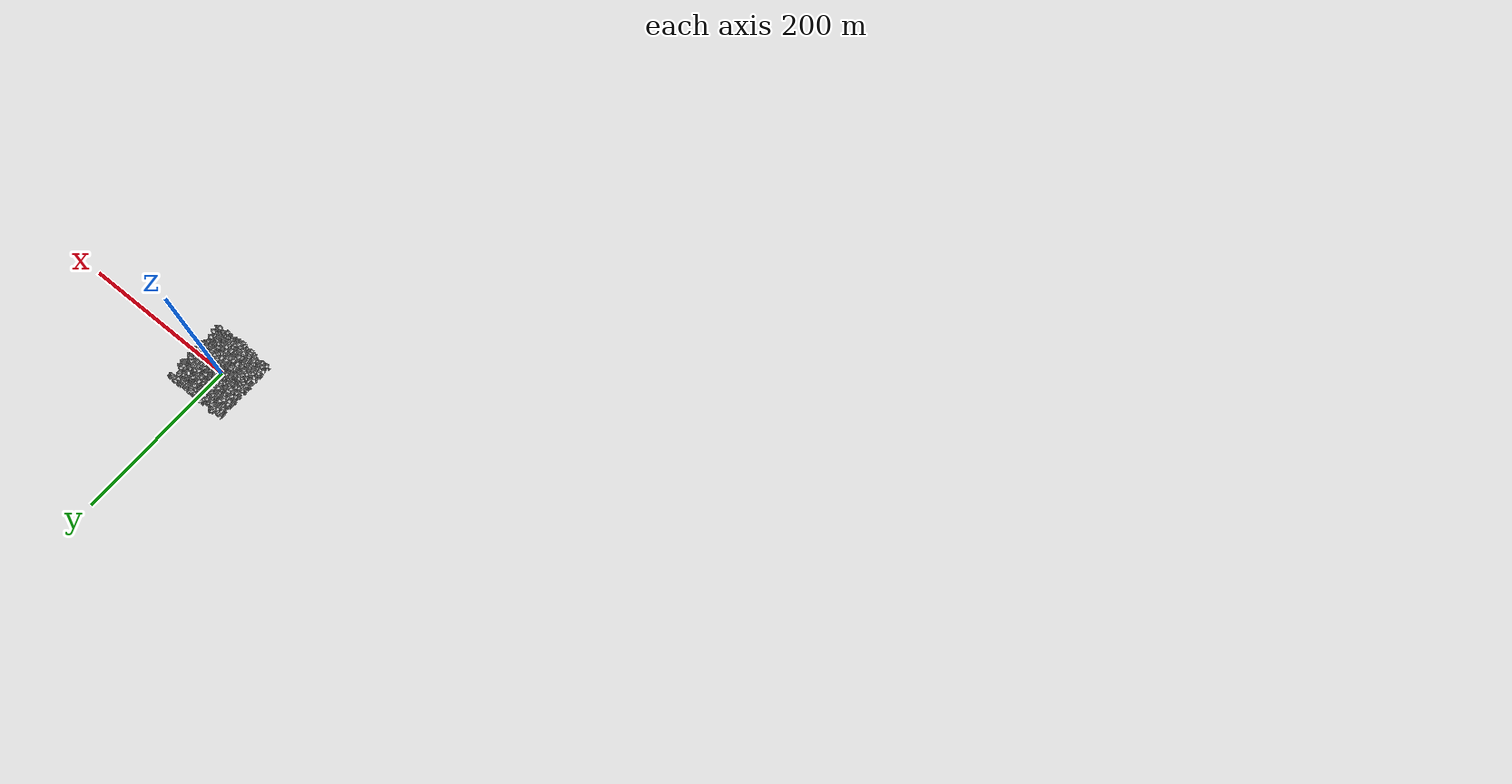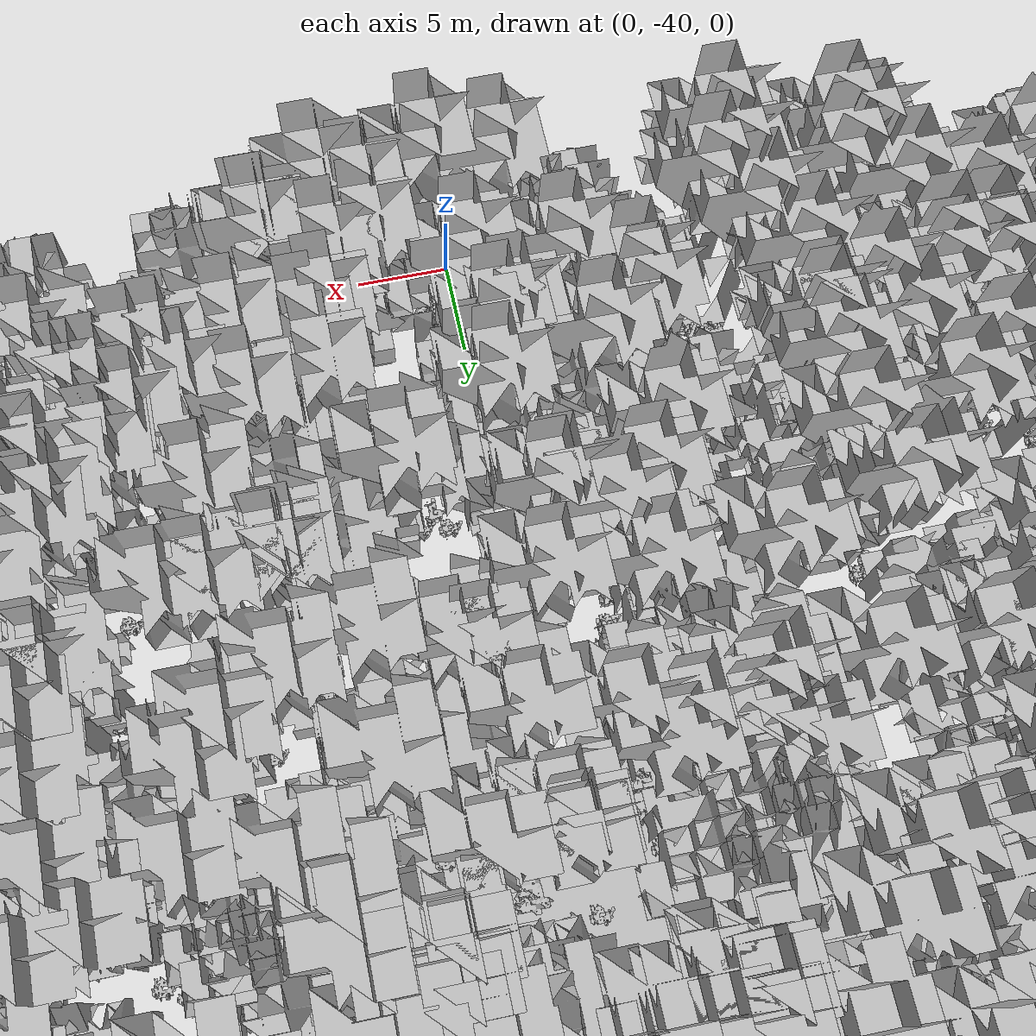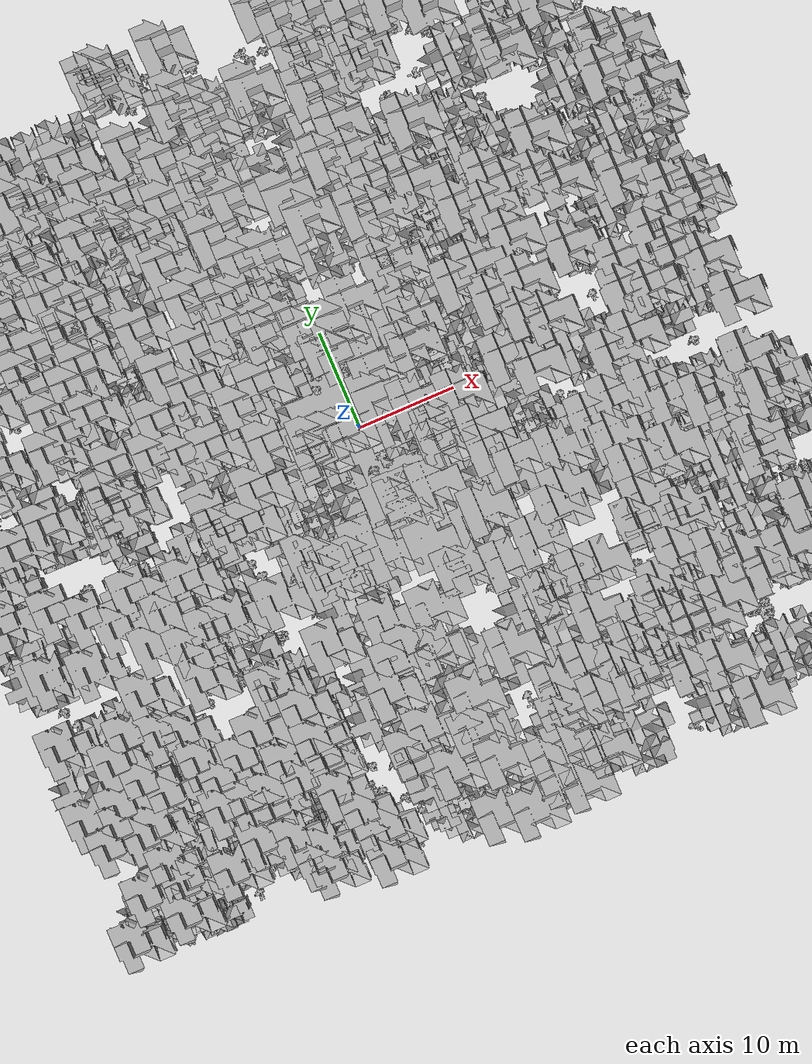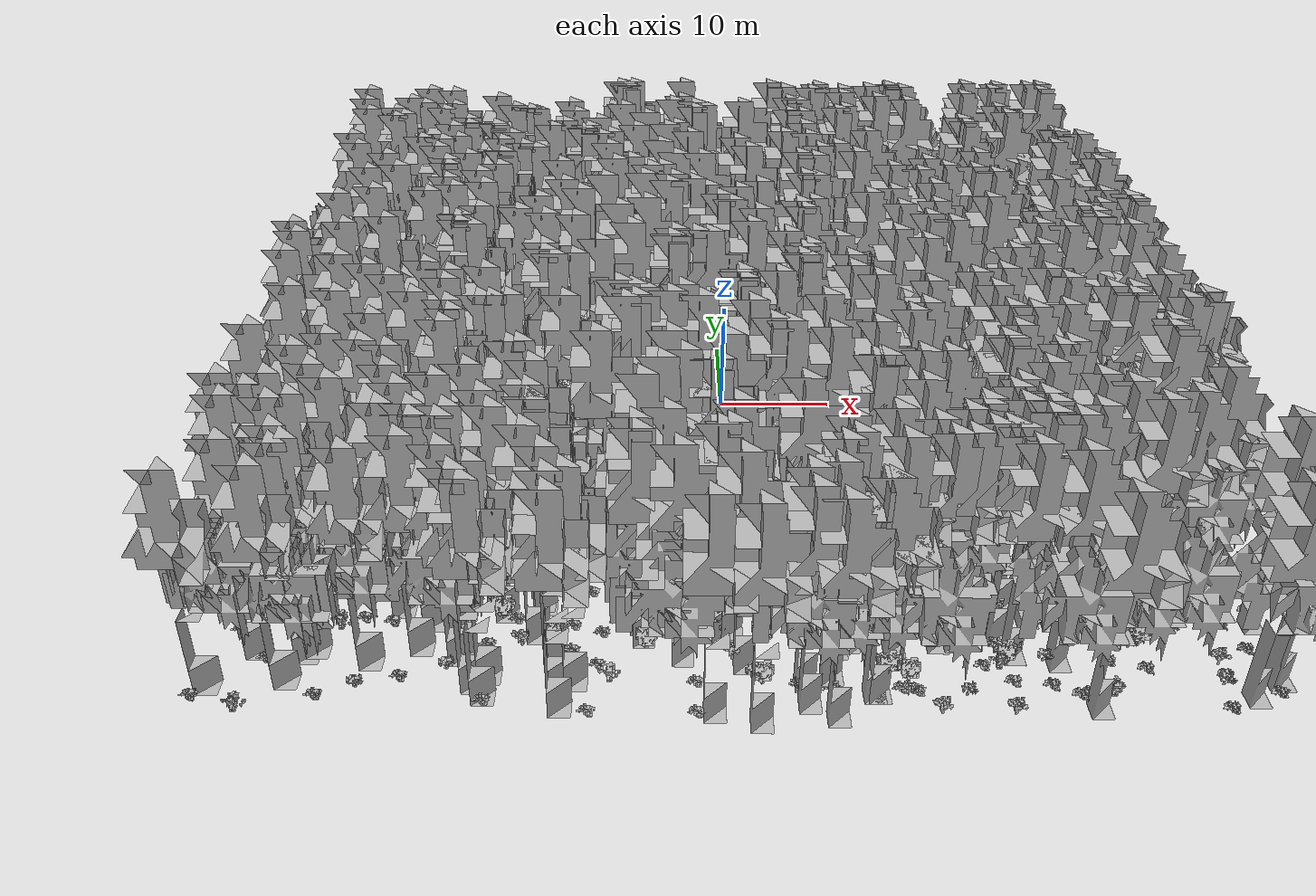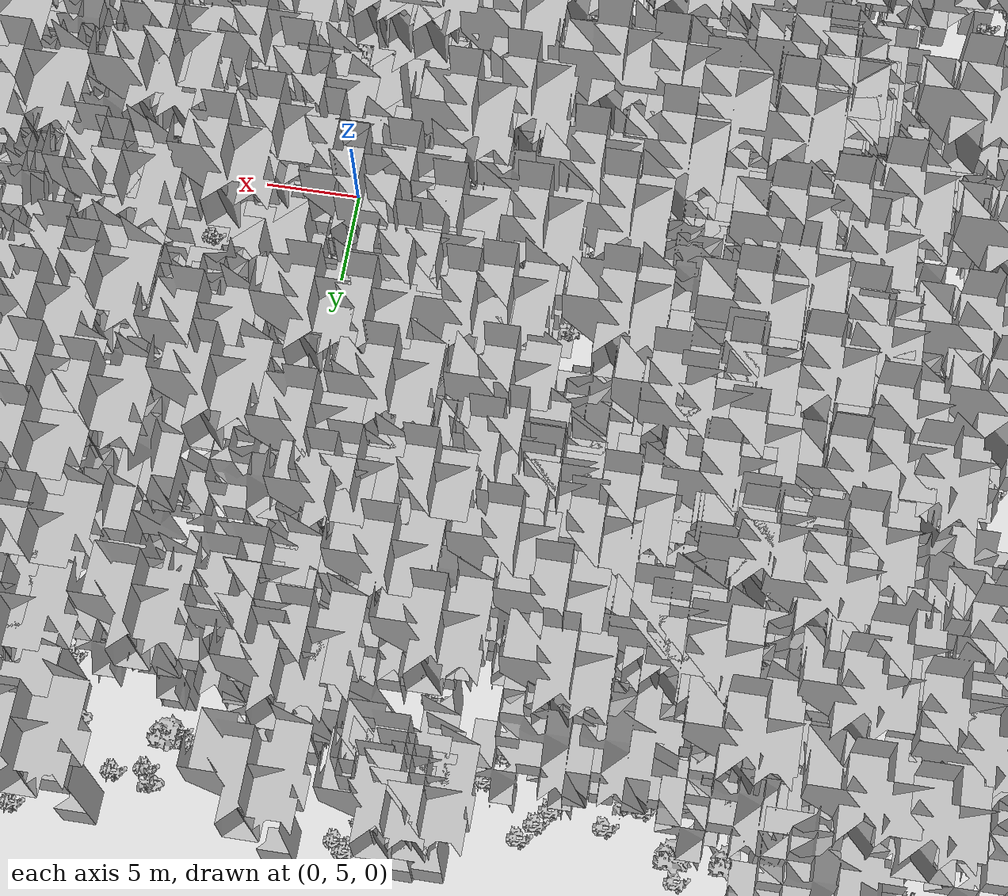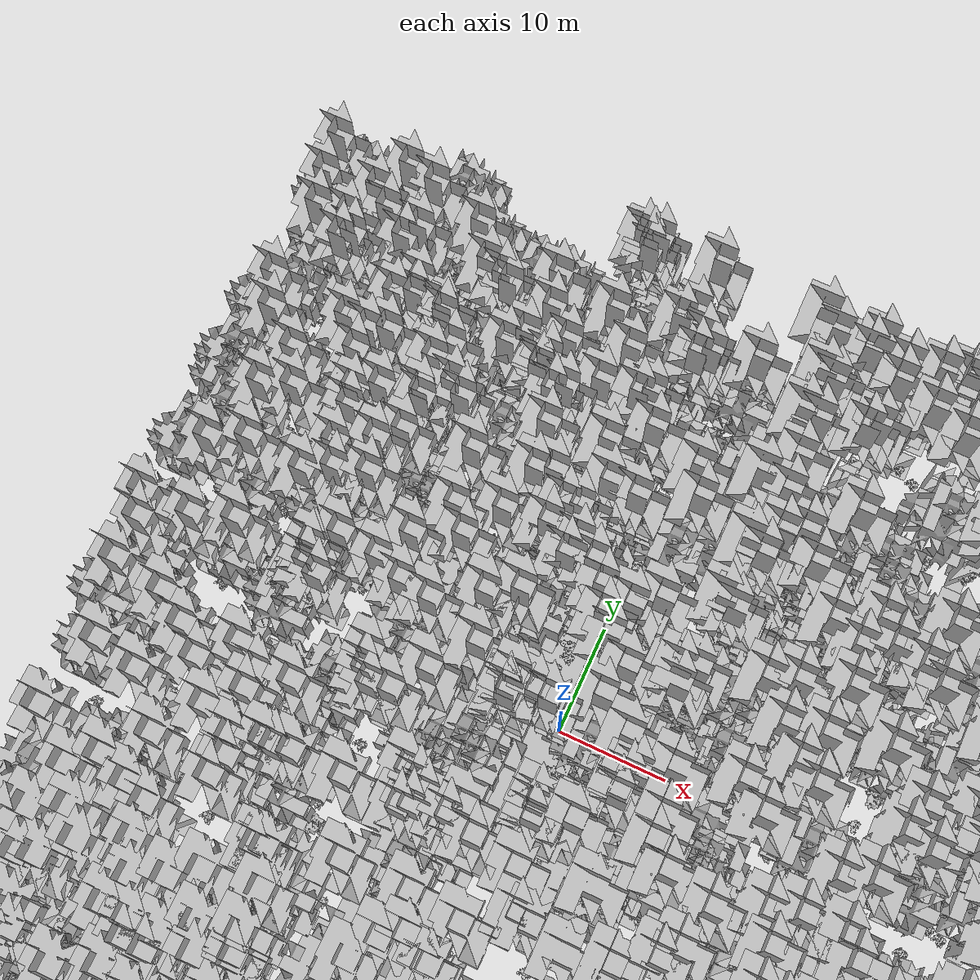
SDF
<sdf version="1.7">
    <world name="default">
        <plugin name="mrs_gazebo_static_transform_republisher_plugin" filename="libMrsGazeboCommonResources_StaticTransformRepublisher.so"/>
        <spherical_coordinates>
            <surface_model>EARTH_WGS84</surface_model>
            <latitude_deg>47.3977</latitude_deg>
            <longitude_deg>8.54559</longitude_deg>
            <elevation>0</elevation>
            <heading_deg>0</heading_deg>
        </spherical_coordinates>
        <physics name="default_physics" default="0" type="ode">
            <ode>
                <solver>
                    <type>quick</type>
                    <iters>10</iters>
                    <sor>1.3</sor>
                    <use_dynamic_moi_rescaling>0</use_dynamic_moi_rescaling>
                </solver>
                <constraints>
                    <cfm>0</cfm>
                    <erp>0.2</erp>
                    <contact_max_correcting_vel>1000</contact_max_correcting_vel>
                    <contact_surface_layer>0.001</contact_surface_layer>
                </constraints>
            </ode>
            <max_step_size>0.004</max_step_size>
            <real_time_factor>1</real_time_factor>
            <real_time_update_rate>250</real_time_update_rate>
        </physics>
        <scene>
            <shadows>0</shadows>
            <ambient>0.4 0.4 0.4 1</ambient>
            <background>0.7 0.7 0.7 1</background>
        </scene>
        <light name="sun" type="directional">
            <pose>0 0 1000 0.4 0.2 0</pose>
            <diffuse>1 1 1 1</diffuse>
            <specular>0.6 0.6 0.6 1</specular>
            <direction>0.1 0.1 -0.9</direction>
            <attenuation>
                <range>20</range>
                <constant>0.5</constant>
                <linear>0.01</linear>
                <quadratic>0.001</quadratic>
            </attenuation>
            <cast_shadows>1</cast_shadows>
            <spot>
                <inner_angle>0</inner_angle>
                <outer_angle>0</outer_angle>
                <falloff>0</falloff>
            </spot>
        </light>
        <model name="ground_plane">
            <static>1</static>
            <link name="link">
                <collision name="collision">
                    <pose>-50 0 0 0 -0 0</pose>
                    <geometry>
                        <plane>
                            <normal>0 0 1</normal>
                            <size>80 80</size>
                        </plane>
                    </geometry>
                    <surface>
                        <contact>
                            <ode>
                                <min_depth>0.01</min_depth>
                                <max_vel>0</max_vel>
                            </ode>
                        </contact>
                        <friction>
                            <ode/>
                            <torsional>
                                <ode/>
                            </torsional>
                        </friction>
                        <bounce/>
                    </surface>
                    <max_contacts>10</max_contacts>
                </collision>
                <visual name="grass">
                    <pose>0 0 0 0 -0 0</pose>
                    <cast_shadows>0</cast_shadows>
                    <geometry>
                        <mesh>
                            <scale>0.46714285714285714 0.46714285714285714 0.1</scale>
                            <uri>file://grass_plane/meshes/grass_plane.dae</uri>
                        </mesh>
                    </geometry>
                </visual>
                <self_collide>0</self_collide>
                <enable_wind>0</enable_wind>
                <kinematic>0</kinematic>
            </link>
        </model>
        <model name="the_void">
            <static>1</static>
            <link name="link">
                <pose>0 0 0.1 0 -0 0</pose>
                <visual name="the_void">
                    <pose>0 0 2 0 -0 0</pose>
                    <geometry>
                        <sphere>
                            <radius>0.25</radius>
                        </sphere>
                    </geometry>
                    <material>
                        <script>
                            <uri>file://media/materials/scripts/Gazebo.material</uri>
                            <name>Gazebo/Black</name>
                        </script>
                    </material>
                </visual>
                <self_collide>0</self_collide>
                <enable_wind>0</enable_wind>
                <kinematic>0</kinematic>
            </link>
            <pose>-1000 -1000 0 0 -0 0</pose>
        </model>
        <gui fullscreen="0">
            <camera name="camera">
                <pose>35.1577 98.6044 40.0204 0 0.407996 -1.99761</pose>
                <view_controller>orbit</view_controller>
                <projection_type>perspective</projection_type>
            </camera>
        </gui>
        <plugin name="mrs_gazebo_rviz_cam_synchronizer" filename="libMrsGazeboCommonResources_RvizCameraSynchronizer.so">
            <target_frame_id>gazebo_user_camera</target_frame_id>
            <world_origin_frame_id>uav1/gps_origin</world_origin_frame_id>
            <frame_to_follow>uav1</frame_to_follow>
        </plugin>
        <gravity>0 0 -9.8066</gravity>
        <magnetic_field>6e-06 2.3e-05 -4.2e-05</magnetic_field>
        <atmosphere type="adiabatic"/>
        <wind/>
        <model name="Tree 0">
            <static>1</static>
            <pose>36.83266492795228 7.051468206629174 0 1.57079 -0 0</pose>
            <link name="link">
                <pose>0 0 0 0 -0 0</pose>
                <collision name="collision">
                    <geometry>
                        <mesh>
                            <scale>3.5 5 3.5</scale>
                            <uri>model://tree_2/meshes/tree_2.obj</uri>
                        </mesh>
                    </geometry>
                    <max_contacts>10</max_contacts>
                    <surface>
                        <contact>
                            <ode/>
                        </contact>
                        <bounce/>
                        <friction>
                            <torsional>
                                <ode/>
                            </torsional>
                            <ode/>
                        </friction>
                    </surface>
                </collision>
                <visual name="visual">
                    <geometry>
                        <mesh>
                            <scale>3.5 5 3.5</scale>
                            <uri>model://tree_2/meshes/tree_2.obj</uri>
                        </mesh>
                    </geometry>
                </visual>
                <self_collide>0</self_collide>
                <enable_wind>0</enable_wind>
                <kinematic>0</kinematic>
            </link>
        </model>
        <model name="Tree 1">
            <static>1</static>
            <pose>18.60243217217141 -30.711495372445697 0 1.57079 -0 0</pose>
            <link name="link">
                <pose>0 0 0 0 -0 0</pose>
                <collision name="collision">
                    <geometry>
                        <mesh>
                            <scale>3.5 5 3.5</scale>
                            <uri>model://tree_9/meshes/tree_9.obj</uri>
                        </mesh>
                    </geometry>
                    <max_contacts>10</max_contacts>
                    <surface>
                        <contact>
                            <ode/>
                        </contact>
                        <bounce/>
                        <friction>
                            <torsional>
                                <ode/>
                            </torsional>
                            <ode/>
                        </friction>
                    </surface>
                </collision>
                <visual name="visual">
                    <geometry>
                        <mesh>
                            <scale>3.5 5 3.5</scale>
                            <uri>model://tree_9/meshes/tree_9.obj</uri>
                        </mesh>
                    </geometry>
                </visual>
                <self_collide>0</self_collide>
                <enable_wind>0</enable_wind>
                <kinematic>0</kinematic>
            </link>
        </model>
        <model name="Tree 2">
            <static>1</static>
            <pose>-8.287499990798413 -12.534664791595755 0 1.57079 -0 0</pose>
            <link name="link">
                <pose>0 0 0 0 -0 0</pose>
                <collision name="collision">
                    <geometry>
                        <mesh>
                            <scale>3.5 5 3.5</scale>
                            <uri>model://tree_9/meshes/tree_9.obj</uri>
                        </mesh>
                    </geometry>
                    <max_contacts>10</max_contacts>
                    <surface>
                        <contact>
                            <ode/>
                        </contact>
                        <bounce/>
                        <friction>
                            <torsional>
                                <ode/>
                            </torsional>
                            <ode/>
                        </friction>
                    </surface>
                </collision>
                <visual name="visual">
                    <geometry>
                        <mesh>
                            <scale>3.5 5 3.5</scale>
                            <uri>model://tree_9/meshes/tree_9.obj</uri>
                        </mesh>
                    </geometry>
                </visual>
                <self_collide>0</self_collide>
                <enable_wind>0</enable_wind>
                <kinematic>0</kinematic>
            </link>
        </model>
        <model name="Tree 3">
            <static>1</static>
            <pose>-9.5421922092418 39.27774204575255 0 1.57079 -0 0</pose>
            <link name="link">
                <pose>0 0 0 0 -0 0</pose>
                <collision name="collision">
                    <geometry>
                        <mesh>
                            <scale>3.5 5 3.5</scale>
                            <uri>model://tree_9/meshes/tree_9.obj</uri>
                        </mesh>
                    </geometry>
                    <max_contacts>10</max_contacts>
                    <surface>
                        <contact>
                            <ode/>
                        </contact>
                        <bounce/>
                        <friction>
                            <torsional>
                                <ode/>
                            </torsional>
                            <ode/>
                        </friction>
                    </surface>
                </collision>
                <visual name="visual">
                    <geometry>
                        <mesh>
                            <scale>3.5 5 3.5</scale>
                            <uri>model://tree_9/meshes/tree_9.obj</uri>
                        </mesh>
                    </geometry>
                </visual>
                <self_collide>0</self_collide>
                <enable_wind>0</enable_wind>
                <kinematic>0</kinematic>
            </link>
        </model>
        <model name="Tree 4">
            <static>1</static>
            <pose>5.168630437713745 -24.923502300719626 0 1.57079 -0 0</pose>
            <link name="link">
                <pose>0 0 0 0 -0 0</pose>
                <collision name="collision">
                    <geometry>
                        <mesh>
                            <scale>3.5 5 3.5</scale>
                            <uri>model://tree_9/meshes/tree_9.obj</uri>
                        </mesh>
                    </geometry>
                    <max_contacts>10</max_contacts>
                    <surface>
                        <contact>
                            <ode/>
                        </contact>
                        <bounce/>
                        <friction>
                            <torsional>
                                <ode/>
                            </torsional>
                            <ode/>
                        </friction>
                    </surface>
                </collision>
                <visual name="visual">
                    <geometry>
                        <mesh>
                            <scale>3.5 5 3.5</scale>
                            <uri>model://tree_9/meshes/tree_9.obj</uri>
                        </mesh>
                    </geometry>
                </visual>
                <self_collide>0</self_collide>
                <enable_wind>0</enable_wind>
                <kinematic>0</kinematic>
            </link>
        </model>
        <model name="Tree 5">
            <static>1</static>
            <pose>10.584103174141113 -0.9741327042595316 0 1.57079 -0 0</pose>
            <link name="link">
                <pose>0 0 0 0 -0 0</pose>
                <collision name="collision">
                    <geometry>
                        <mesh>
                            <scale>3.5 5 3.5</scale>
                            <uri>model://tree_2/meshes/tree_2.obj</uri>
                        </mesh>
                    </geometry>
                    <max_contacts>10</max_contacts>
                    <surface>
                        <contact>
                            <ode/>
                        </contact>
                        <bounce/>
                        <friction>
                            <torsional>
                                <ode/>
                            </torsional>
                            <ode/>
                        </friction>
                    </surface>
                </collision>
                <visual name="visual">
                    <geometry>
                        <mesh>
                            <scale>3.5 5 3.5</scale>
                            <uri>model://tree_2/meshes/tree_2.obj</uri>
                        </mesh>
                    </geometry>
                </visual>
                <self_collide>0</self_collide>
                <enable_wind>0</enable_wind>
                <kinematic>0</kinematic>
            </link>
        </model>
        <model name="Tree 6">
            <static>1</static>
            <pose>24.662578489333356 -19.806270252675482 0 1.57079 -0 0</pose>
            <link name="link">
                <pose>0 0 0 0 -0 0</pose>
                <collision name="collision">
                    <geometry>
                        <mesh>
                            <scale>3.5 5 3.5</scale>
                            <uri>model://tree_9/meshes/tree_9.obj</uri>
                        </mesh>
                    </geometry>
                    <max_contacts>10</max_contacts>
                    <surface>
                        <contact>
                            <ode/>
                        </contact>
                        <bounce/>
                        <friction>
                            <torsional>
                                <ode/>
                            </torsional>
                            <ode/>
                        </friction>
                    </surface>
                </collision>
                <visual name="visual">
                    <geometry>
                        <mesh>
                            <scale>3.5 5 3.5</scale>
                            <uri>model://tree_9/meshes/tree_9.obj</uri>
                        </mesh>
                    </geometry>
                </visual>
                <self_collide>0</self_collide>
                <enable_wind>0</enable_wind>
                <kinematic>0</kinematic>
            </link>
        </model>
        <model name="Tree 7">
            <static>1</static>
            <pose>13.831587027069752 -30.261988147326456 0 1.57079 -0 0</pose>
            <link name="link">
                <pose>0 0 0 0 -0 0</pose>
                <collision name="collision">
                    <geometry>
                        <mesh>
                            <scale>3.5 5 3.5</scale>
                            <uri>model://tree_9/meshes/tree_9.obj</uri>
                        </mesh>
                    </geometry>
                    <max_contacts>10</max_contacts>
                    <surface>
                        <contact>
                            <ode/>
                        </contact>
                        <bounce/>
                        <friction>
                            <torsional>
                                <ode/>
                            </torsional>
                            <ode/>
                        </friction>
                    </surface>
                </collision>
                <visual name="visual">
                    <geometry>
                        <mesh>
                            <scale>3.5 5 3.5</scale>
                            <uri>model://tree_9/meshes/tree_9.obj</uri>
                        </mesh>
                    </geometry>
                </visual>
                <self_collide>0</self_collide>
                <enable_wind>0</enable_wind>
                <kinematic>0</kinematic>
            </link>
        </model>
        <model name="Tree 8">
            <static>1</static>
            <pose>38.076413633150764 8.357916476005144 0 1.57079 -0 0</pose>
            <link name="link">
                <pose>0 0 0 0 -0 0</pose>
                <collision name="collision">
                    <geometry>
                        <mesh>
                            <scale>3.5 5 3.5</scale>
                            <uri>model://tree_9/meshes/tree_9.obj</uri>
                        </mesh>
                    </geometry>
                    <max_contacts>10</max_contacts>
                    <surface>
                        <contact>
                            <ode/>
                        </contact>
                        <bounce/>
                        <friction>
                            <torsional>
                                <ode/>
                            </torsional>
                            <ode/>
                        </friction>
                    </surface>
                </collision>
                <visual name="visual">
                    <geometry>
                        <mesh>
                            <scale>3.5 5 3.5</scale>
                            <uri>model://tree_9/meshes/tree_9.obj</uri>
                        </mesh>
                    </geometry>
                </visual>
                <self_collide>0</self_collide>
                <enable_wind>0</enable_wind>
                <kinematic>0</kinematic>
            </link>
        </model>
        <model name="Tree 9">
            <static>1</static>
            <pose>-4.585492454988575 -11.526857596979355 0 1.57079 -0 0</pose>
            <link name="link">
                <pose>0 0 0 0 -0 0</pose>
                <collision name="collision">
                    <geometry>
                        <mesh>
                            <scale>3.5 5 3.5</scale>
                            <uri>model://tree_9/meshes/tree_9.obj</uri>
                        </mesh>
                    </geometry>
                    <max_contacts>10</max_contacts>
                    <surface>
                        <contact>
                            <ode/>
                        </contact>
                        <bounce/>
                        <friction>
                            <torsional>
                                <ode/>
                            </torsional>
                            <ode/>
                        </friction>
                    </surface>
                </collision>
                <visual name="visual">
                    <geometry>
                        <mesh>
                            <scale>3.5 5 3.5</scale>
                            <uri>model://tree_9/meshes/tree_9.obj</uri>
                        </mesh>
                    </geometry>
                </visual>
                <self_collide>0</self_collide>
                <enable_wind>0</enable_wind>
                <kinematic>0</kinematic>
            </link>
        </model>
        <model name="Tree 10">
            <static>1</static>
            <pose>26.239078518444046 28.596939956956504 0 1.57079 -0 0</pose>
            <link name="link">
                <pose>0 0 0 0 -0 0</pose>
                <collision name="collision">
                    <geometry>
                        <mesh>
                            <scale>3.5 5 3.5</scale>
                            <uri>model://tree_9/meshes/tree_9.obj</uri>
                        </mesh>
                    </geometry>
                    <max_contacts>10</max_contacts>
                    <surface>
                        <contact>
                            <ode/>
                        </contact>
                        <bounce/>
                        <friction>
                            <torsional>
                                <ode/>
                            </torsional>
                            <ode/>
                        </friction>
                    </surface>
                </collision>
                <visual name="visual">
                    <geometry>
                        <mesh>
                            <scale>3.5 5 3.5</scale>
                            <uri>model://tree_9/meshes/tree_9.obj</uri>
                        </mesh>
                    </geometry>
                </visual>
                <self_collide>0</self_collide>
                <enable_wind>0</enable_wind>
                <kinematic>0</kinematic>
            </link>
        </model>
        <model name="Tree 11">
            <static>1</static>
            <pose>34.29962287894699 15.931836382044366 0 1.57079 -0 0</pose>
            <link name="link">
                <pose>0 0 0 0 -0 0</pose>
                <collision name="collision">
                    <geometry>
                        <mesh>
                            <scale>3.5 5 3.5</scale>
                            <uri>model://tree_2/meshes/tree_2.obj</uri>
                        </mesh>
                    </geometry>
                    <max_contacts>10</max_contacts>
                    <surface>
                        <contact>
                            <ode/>
                        </contact>
                        <bounce/>
                        <friction>
                            <torsional>
                                <ode/>
                            </torsional>
                            <ode/>
                        </friction>
                    </surface>
                </collision>
                <visual name="visual">
                    <geometry>
                        <mesh>
                            <scale>3.5 5 3.5</scale>
                            <uri>model://tree_2/meshes/tree_2.obj</uri>
                        </mesh>
                    </geometry>
                </visual>
                <self_collide>0</self_collide>
                <enable_wind>0</enable_wind>
                <kinematic>0</kinematic>
            </link>
        </model>
        <model name="Tree 12">
            <static>1</static>
            <pose>14.566853276227931 36.42362300159266 0 1.57079 -0 0</pose>
            <link name="link">
                <pose>0 0 0 0 -0 0</pose>
                <collision name="collision">
                    <geometry>
                        <mesh>
                            <scale>3.5 5 3.5</scale>
                            <uri>model://tree_9/meshes/tree_9.obj</uri>
                        </mesh>
                    </geometry>
                    <max_contacts>10</max_contacts>
                    <surface>
                        <contact>
                            <ode/>
                        </contact>
                        <bounce/>
                        <friction>
                            <torsional>
                                <ode/>
                            </torsional>
                            <ode/>
                        </friction>
                    </surface>
                </collision>
                <visual name="visual">
                    <geometry>
                        <mesh>
                            <scale>3.5 5 3.5</scale>
                            <uri>model://tree_9/meshes/tree_9.obj</uri>
                        </mesh>
                    </geometry>
                </visual>
                <self_collide>0</self_collide>
                <enable_wind>0</enable_wind>
                <kinematic>0</kinematic>
            </link>
        </model>
        <model name="Tree 13">
            <static>1</static>
            <pose>-26.297130198007018 22.589806835248623 0 1.57079 -0 0</pose>
            <link name="link">
                <pose>0 0 0 0 -0 0</pose>
                <collision name="collision">
                    <geometry>
                        <mesh>
                            <scale>3.5 5 3.5</scale>
                            <uri>model://tree_9/meshes/tree_9.obj</uri>
                        </mesh>
                    </geometry>
                    <max_contacts>10</max_contacts>
                    <surface>
                        <contact>
                            <ode/>
                        </contact>
                        <bounce/>
                        <friction>
                            <torsional>
                                <ode/>
                            </torsional>
                            <ode/>
                        </friction>
                    </surface>
                </collision>
                <visual name="visual">
                    <geometry>
                        <mesh>
                            <scale>3.5 5 3.5</scale>
                            <uri>model://tree_9/meshes/tree_9.obj</uri>
                        </mesh>
                    </geometry>
                </visual>
                <self_collide>0</self_collide>
                <enable_wind>0</enable_wind>
                <kinematic>0</kinematic>
            </link>
        </model>
        <model name="Tree 14">
            <static>1</static>
            <pose>21.889454777464486 -29.216669163732227 0 1.57079 -0 0</pose>
            <link name="link">
                <pose>0 0 0 0 -0 0</pose>
                <collision name="collision">
                    <geometry>
                        <mesh>
                            <scale>3.5 5 3.5</scale>
                            <uri>model://tree_9/meshes/tree_9.obj</uri>
                        </mesh>
                    </geometry>
                    <max_contacts>10</max_contacts>
                    <surface>
                        <contact>
                            <ode/>
                        </contact>
                        <bounce/>
                        <friction>
                            <torsional>
                                <ode/>
                            </torsional>
                            <ode/>
                        </friction>
                    </surface>
                </collision>
                <visual name="visual">
                    <geometry>
                        <mesh>
                            <scale>3.5 5 3.5</scale>
                            <uri>model://tree_9/meshes/tree_9.obj</uri>
                        </mesh>
                    </geometry>
                </visual>
                <self_collide>0</self_collide>
                <enable_wind>0</enable_wind>
                <kinematic>0</kinematic>
            </link>
        </model>
        <model name="Tree 15">
            <static>1</static>
            <pose>15.198794155945386 -6.880111373983276 0 1.57079 -0 0</pose>
            <link name="link">
                <pose>0 0 0 0 -0 0</pose>
                <collision name="collision">
                    <geometry>
                        <mesh>
                            <scale>3.5 5 3.5</scale>
                            <uri>model://tree_2/meshes/tree_2.obj</uri>
                        </mesh>
                    </geometry>
                    <max_contacts>10</max_contacts>
                    <surface>
                        <contact>
                            <ode/>
                        </contact>
                        <bounce/>
                        <friction>
                            <torsional>
                                <ode/>
                            </torsional>
                            <ode/>
                        </friction>
                    </surface>
                </collision>
                <visual name="visual">
                    <geometry>
                        <mesh>
                            <scale>3.5 5 3.5</scale>
                            <uri>model://tree_2/meshes/tree_2.obj</uri>
                        </mesh>
                    </geometry>
                </visual>
                <self_collide>0</self_collide>
                <enable_wind>0</enable_wind>
                <kinematic>0</kinematic>
            </link>
        </model>
        <model name="Tree 16">
            <static>1</static>
            <pose>-36.08321133468076 -0.38418183602739475 0 1.57079 -0 0</pose>
            <link name="link">
                <pose>0 0 0 0 -0 0</pose>
                <collision name="collision">
                    <geometry>
                        <mesh>
                            <scale>3.5 5 3.5</scale>
                            <uri>model://tree_2/meshes/tree_2.obj</uri>
                        </mesh>
                    </geometry>
                    <max_contacts>10</max_contacts>
                    <surface>
                        <contact>
                            <ode/>
                        </contact>
                        <bounce/>
                        <friction>
                            <torsional>
                                <ode/>
                            </torsional>
                            <ode/>
                        </friction>
                    </surface>
                </collision>
                <visual name="visual">
                    <geometry>
                        <mesh>
                            <scale>3.5 5 3.5</scale>
                            <uri>model://tree_2/meshes/tree_2.obj</uri>
                        </mesh>
                    </geometry>
                </visual>
                <self_collide>0</self_collide>
                <enable_wind>0</enable_wind>
                <kinematic>0</kinematic>
            </link>
        </model>
        <model name="Tree 17">
            <static>1</static>
            <pose>-14.67669185627982 -27.64647952758592 0 1.57079 -0 0</pose>
            <link name="link">
                <pose>0 0 0 0 -0 0</pose>
                <collision name="collision">
                    <geometry>
                        <mesh>
                            <scale>3.5 5 3.5</scale>
                            <uri>model://tree_9/meshes/tree_9.obj</uri>
                        </mesh>
                    </geometry>
                    <max_contacts>10</max_contacts>
                    <surface>
                        <contact>
                            <ode/>
                        </contact>
                        <bounce/>
                        <friction>
                            <torsional>
                                <ode/>
                            </torsional>
                            <ode/>
                        </friction>
                    </surface>
                </collision>
                <visual name="visual">
                    <geometry>
                        <mesh>
                            <scale>3.5 5 3.5</scale>
                            <uri>model://tree_9/meshes/tree_9.obj</uri>
                        </mesh>
                    </geometry>
                </visual>
                <self_collide>0</self_collide>
                <enable_wind>0</enable_wind>
                <kinematic>0</kinematic>
            </link>
        </model>
        <model name="Tree 18">
            <static>1</static>
            <pose>-14.675197095112946 11.266320430562232 0 1.57079 -0 0</pose>
            <link name="link">
                <pose>0 0 0 0 -0 0</pose>
                <collision name="collision">
                    <geometry>
                        <mesh>
                            <scale>3.5 5 3.5</scale>
                            <uri>model://tree_9/meshes/tree_9.obj</uri>
                        </mesh>
                    </geometry>
                    <max_contacts>10</max_contacts>
                    <surface>
                        <contact>
                            <ode/>
                        </contact>
                        <bounce/>
                        <friction>
                            <torsional>
                                <ode/>
                            </torsional>
                            <ode/>
                        </friction>
                    </surface>
                </collision>
                <visual name="visual">
                    <geometry>
                        <mesh>
                            <scale>3.5 5 3.5</scale>
                            <uri>model://tree_9/meshes/tree_9.obj</uri>
                        </mesh>
                    </geometry>
                </visual>
                <self_collide>0</self_collide>
                <enable_wind>0</enable_wind>
                <kinematic>0</kinematic>
            </link>
        </model>
        <model name="Tree 19">
            <static>1</static>
            <pose>-14.435010337102057 29.73800944745875 0 1.57079 -0 0</pose>
            <link name="link">
                <pose>0 0 0 0 -0 0</pose>
                <collision name="collision">
                    <geometry>
                        <mesh>
                            <scale>3.5 5 3.5</scale>
                            <uri>model://tree_2/meshes/tree_2.obj</uri>
                        </mesh>
                    </geometry>
                    <max_contacts>10</max_contacts>
                    <surface>
                        <contact>
                            <ode/>
                        </contact>
                        <bounce/>
                        <friction>
                            <torsional>
                                <ode/>
                            </torsional>
                            <ode/>
                        </friction>
                    </surface>
                </collision>
                <visual name="visual">
                    <geometry>
                        <mesh>
                            <scale>3.5 5 3.5</scale>
                            <uri>model://tree_2/meshes/tree_2.obj</uri>
                        </mesh>
                    </geometry>
                </visual>
                <self_collide>0</self_collide>
                <enable_wind>0</enable_wind>
                <kinematic>0</kinematic>
            </link>
        </model>
        <model name="Tree 20">
            <static>1</static>
            <pose>-4.892058368894851 -29.02101901538135 0 1.57079 -0 0</pose>
            <link name="link">
                <pose>0 0 0 0 -0 0</pose>
                <collision name="collision">
                    <geometry>
                        <mesh>
                            <scale>3.5 5 3.5</scale>
                            <uri>model://tree_9/meshes/tree_9.obj</uri>
                        </mesh>
                    </geometry>
                    <max_contacts>10</max_contacts>
                    <surface>
                        <contact>
                            <ode/>
                        </contact>
                        <bounce/>
                        <friction>
                            <torsional>
                                <ode/>
                            </torsional>
                            <ode/>
                        </friction>
                    </surface>
                </collision>
                <visual name="visual">
                    <geometry>
                        <mesh>
                            <scale>3.5 5 3.5</scale>
                            <uri>model://tree_9/meshes/tree_9.obj</uri>
                        </mesh>
                    </geometry>
                </visual>
                <self_collide>0</self_collide>
                <enable_wind>0</enable_wind>
                <kinematic>0</kinematic>
            </link>
        </model>
        <model name="Tree 21">
            <static>1</static>
            <pose>26.68829349461484 -24.06690457907482 0 1.57079 -0 0</pose>
            <link name="link">
                <pose>0 0 0 0 -0 0</pose>
                <collision name="collision">
                    <geometry>
                        <mesh>
                            <scale>3.5 5 3.5</scale>
                            <uri>model://tree_9/meshes/tree_9.obj</uri>
                        </mesh>
                    </geometry>
                    <max_contacts>10</max_contacts>
                    <surface>
                        <contact>
                            <ode/>
                        </contact>
                        <bounce/>
                        <friction>
                            <torsional>
                                <ode/>
                            </torsional>
                            <ode/>
                        </friction>
                    </surface>
                </collision>
                <visual name="visual">
                    <geometry>
                        <mesh>
                            <scale>3.5 5 3.5</scale>
                            <uri>model://tree_9/meshes/tree_9.obj</uri>
                        </mesh>
                    </geometry>
                </visual>
                <self_collide>0</self_collide>
                <enable_wind>0</enable_wind>
                <kinematic>0</kinematic>
            </link>
        </model>
        <model name="Tree 22">
            <static>1</static>
            <pose>-25.708312679986356 26.531931123848096 0 1.57079 -0 0</pose>
            <link name="link">
                <pose>0 0 0 0 -0 0</pose>
                <collision name="collision">
                    <geometry>
                        <mesh>
                            <scale>3.5 5 3.5</scale>
                            <uri>model://tree_9/meshes/tree_9.obj</uri>
                        </mesh>
                    </geometry>
                    <max_contacts>10</max_contacts>
                    <surface>
                        <contact>
                            <ode/>
                        </contact>
                        <bounce/>
                        <friction>
                            <torsional>
                                <ode/>
                            </torsional>
                            <ode/>
                        </friction>
                    </surface>
                </collision>
                <visual name="visual">
                    <geometry>
                        <mesh>
                            <scale>3.5 5 3.5</scale>
                            <uri>model://tree_9/meshes/tree_9.obj</uri>
                        </mesh>
                    </geometry>
                </visual>
                <self_collide>0</self_collide>
                <enable_wind>0</enable_wind>
                <kinematic>0</kinematic>
            </link>
        </model>
        <model name="Tree 23">
            <static>1</static>
            <pose>24.29537606938836 39.25126462083037 0 1.57079 -0 0</pose>
            <link name="link">
                <pose>0 0 0 0 -0 0</pose>
                <collision name="collision">
                    <geometry>
                        <mesh>
                            <scale>3.5 5 3.5</scale>
                            <uri>model://tree_2/meshes/tree_2.obj</uri>
                        </mesh>
                    </geometry>
                    <max_contacts>10</max_contacts>
                    <surface>
                        <contact>
                            <ode/>
                        </contact>
                        <bounce/>
                        <friction>
                            <torsional>
                                <ode/>
                            </torsional>
                            <ode/>
                        </friction>
                    </surface>
                </collision>
                <visual name="visual">
                    <geometry>
                        <mesh>
                            <scale>3.5 5 3.5</scale>
                            <uri>model://tree_2/meshes/tree_2.obj</uri>
                        </mesh>
                    </geometry>
                </visual>
                <self_collide>0</self_collide>
                <enable_wind>0</enable_wind>
                <kinematic>0</kinematic>
            </link>
        </model>
        <model name="Tree 24">
            <static>1</static>
            <pose>-14.497213452491316 0.858952401795392 0 1.57079 -0 0</pose>
            <link name="link">
                <pose>0 0 0 0 -0 0</pose>
                <collision name="collision">
                    <geometry>
                        <mesh>
                            <scale>3.5 5 3.5</scale>
                            <uri>model://tree_2/meshes/tree_2.obj</uri>
                        </mesh>
                    </geometry>
                    <max_contacts>10</max_contacts>
                    <surface>
                        <contact>
                            <ode/>
                        </contact>
                        <bounce/>
                        <friction>
                            <torsional>
                                <ode/>
                            </torsional>
                            <ode/>
                        </friction>
                    </surface>
                </collision>
                <visual name="visual">
                    <geometry>
                        <mesh>
                            <scale>3.5 5 3.5</scale>
                            <uri>model://tree_2/meshes/tree_2.obj</uri>
                        </mesh>
                    </geometry>
                </visual>
                <self_collide>0</self_collide>
                <enable_wind>0</enable_wind>
                <kinematic>0</kinematic>
            </link>
        </model>
        <model name="Tree 25">
            <static>1</static>
            <pose>16.088227340830457 1.7574123643542947 0 1.57079 -0 0</pose>
            <link name="link">
                <pose>0 0 0 0 -0 0</pose>
                <collision name="collision">
                    <geometry>
                        <mesh>
                            <scale>3.5 5 3.5</scale>
                            <uri>model://tree_2/meshes/tree_2.obj</uri>
                        </mesh>
                    </geometry>
                    <max_contacts>10</max_contacts>
                    <surface>
                        <contact>
                            <ode/>
                        </contact>
                        <bounce/>
                        <friction>
                            <torsional>
                                <ode/>
                            </torsional>
                            <ode/>
                        </friction>
                    </surface>
                </collision>
                <visual name="visual">
                    <geometry>
                        <mesh>
                            <scale>3.5 5 3.5</scale>
                            <uri>model://tree_2/meshes/tree_2.obj</uri>
                        </mesh>
                    </geometry>
                </visual>
                <self_collide>0</self_collide>
                <enable_wind>0</enable_wind>
                <kinematic>0</kinematic>
            </link>
        </model>
        <model name="Tree 26">
            <static>1</static>
            <pose>-21.366260727895376 31.81468612032201 0 1.57079 -0 0</pose>
            <link name="link">
                <pose>0 0 0 0 -0 0</pose>
                <collision name="collision">
                    <geometry>
                        <mesh>
                            <scale>3.5 5 3.5</scale>
                            <uri>model://tree_9/meshes/tree_9.obj</uri>
                        </mesh>
                    </geometry>
                    <max_contacts>10</max_contacts>
                    <surface>
                        <contact>
                            <ode/>
                        </contact>
                        <bounce/>
                        <friction>
                            <torsional>
                                <ode/>
                            </torsional>
                            <ode/>
                        </friction>
                    </surface>
                </collision>
                <visual name="visual">
                    <geometry>
                        <mesh>
                            <scale>3.5 5 3.5</scale>
                            <uri>model://tree_9/meshes/tree_9.obj</uri>
                        </mesh>
                    </geometry>
                </visual>
                <self_collide>0</self_collide>
                <enable_wind>0</enable_wind>
                <kinematic>0</kinematic>
            </link>
        </model>
        <model name="Tree 27">
            <static>1</static>
            <pose>-35.699510355819 7.896706620639236 0 1.57079 -0 0</pose>
            <link name="link">
                <pose>0 0 0 0 -0 0</pose>
                <collision name="collision">
                    <geometry>
                        <mesh>
                            <scale>3.5 5 3.5</scale>
                            <uri>model://tree_9/meshes/tree_9.obj</uri>
                        </mesh>
                    </geometry>
                    <max_contacts>10</max_contacts>
                    <surface>
                        <contact>
                            <ode/>
                        </contact>
                        <bounce/>
                        <friction>
                            <torsional>
                                <ode/>
                            </torsional>
                            <ode/>
                        </friction>
                    </surface>
                </collision>
                <visual name="visual">
                    <geometry>
                        <mesh>
                            <scale>3.5 5 3.5</scale>
                            <uri>model://tree_9/meshes/tree_9.obj</uri>
                        </mesh>
                    </geometry>
                </visual>
                <self_collide>0</self_collide>
                <enable_wind>0</enable_wind>
                <kinematic>0</kinematic>
            </link>
        </model>
        <model name="Tree 28">
            <static>1</static>
            <pose>10.727780412002062 -4.682710390710994 0 1.57079 -0 0</pose>
            <link name="link">
                <pose>0 0 0 0 -0 0</pose>
                <collision name="collision">
                    <geometry>
                        <mesh>
                            <scale>3.5 5 3.5</scale>
                            <uri>model://tree_9/meshes/tree_9.obj</uri>
                        </mesh>
                    </geometry>
                    <max_contacts>10</max_contacts>
                    <surface>
                        <contact>
                            <ode/>
                        </contact>
                        <bounce/>
                        <friction>
                            <torsional>
                                <ode/>
                            </torsional>
                            <ode/>
                        </friction>
                    </surface>
                </collision>
                <visual name="visual">
                    <geometry>
                        <mesh>
                            <scale>3.5 5 3.5</scale>
                            <uri>model://tree_9/meshes/tree_9.obj</uri>
                        </mesh>
                    </geometry>
                </visual>
                <self_collide>0</self_collide>
                <enable_wind>0</enable_wind>
                <kinematic>0</kinematic>
            </link>
        </model>
        <model name="Tree 29">
            <static>1</static>
            <pose>0.5790758655412063 -35.10344212327158 0 1.57079 -0 0</pose>
            <link name="link">
                <pose>0 0 0 0 -0 0</pose>
                <collision name="collision">
                    <geometry>
                        <mesh>
                            <scale>3.5 5 3.5</scale>
                            <uri>model://tree_2/meshes/tree_2.obj</uri>
                        </mesh>
                    </geometry>
                    <max_contacts>10</max_contacts>
                    <surface>
                        <contact>
                            <ode/>
                        </contact>
                        <bounce/>
                        <friction>
                            <torsional>
                                <ode/>
                            </torsional>
                            <ode/>
                        </friction>
                    </surface>
                </collision>
                <visual name="visual">
                    <geometry>
                        <mesh>
                            <scale>3.5 5 3.5</scale>
                            <uri>model://tree_2/meshes/tree_2.obj</uri>
                        </mesh>
                    </geometry>
                </visual>
                <self_collide>0</self_collide>
                <enable_wind>0</enable_wind>
                <kinematic>0</kinematic>
            </link>
        </model>
        <model name="Tree 30">
            <static>1</static>
            <pose>13.537045538951126 11.8044494098448 0 1.57079 -0 0</pose>
            <link name="link">
                <pose>0 0 0 0 -0 0</pose>
                <collision name="collision">
                    <geometry>
                        <mesh>
                            <scale>3.5 5 3.5</scale>
                            <uri>model://tree_2/meshes/tree_2.obj</uri>
                        </mesh>
                    </geometry>
                    <max_contacts>10</max_contacts>
                    <surface>
                        <contact>
                            <ode/>
                        </contact>
                        <bounce/>
                        <friction>
                            <torsional>
                                <ode/>
                            </torsional>
                            <ode/>
                        </friction>
                    </surface>
                </collision>
                <visual name="visual">
                    <geometry>
                        <mesh>
                            <scale>3.5 5 3.5</scale>
                            <uri>model://tree_2/meshes/tree_2.obj</uri>
                        </mesh>
                    </geometry>
                </visual>
                <self_collide>0</self_collide>
                <enable_wind>0</enable_wind>
                <kinematic>0</kinematic>
            </link>
        </model>
        <model name="Tree 31">
            <static>1</static>
            <pose>-6.2792954632388955 -4.744793343398435 0 1.57079 -0 0</pose>
            <link name="link">
                <pose>0 0 0 0 -0 0</pose>
                <collision name="collision">
                    <geometry>
                        <mesh>
                            <scale>3.5 5 3.5</scale>
                            <uri>model://tree_2/meshes/tree_2.obj</uri>
                        </mesh>
                    </geometry>
                    <max_contacts>10</max_contacts>
                    <surface>
                        <contact>
                            <ode/>
                        </contact>
                        <bounce/>
                        <friction>
                            <torsional>
                                <ode/>
                            </torsional>
                            <ode/>
                        </friction>
                    </surface>
                </collision>
                <visual name="visual">
                    <geometry>
                        <mesh>
                            <scale>3.5 5 3.5</scale>
                            <uri>model://tree_2/meshes/tree_2.obj</uri>
                        </mesh>
                    </geometry>
                </visual>
                <self_collide>0</self_collide>
                <enable_wind>0</enable_wind>
                <kinematic>0</kinematic>
            </link>
        </model>
        <model name="Tree 32">
            <static>1</static>
            <pose>-7.210779180461927 -7.417850123513645 0 1.57079 -0 0</pose>
            <link name="link">
                <pose>0 0 0 0 -0 0</pose>
                <collision name="collision">
                    <geometry>
                        <mesh>
                            <scale>3.5 5 3.5</scale>
                            <uri>model://tree_2/meshes/tree_2.obj</uri>
                        </mesh>
                    </geometry>
                    <max_contacts>10</max_contacts>
                    <surface>
                        <contact>
                            <ode/>
                        </contact>
                        <bounce/>
                        <friction>
                            <torsional>
                                <ode/>
                            </torsional>
                            <ode/>
                        </friction>
                    </surface>
                </collision>
                <visual name="visual">
                    <geometry>
                        <mesh>
                            <scale>3.5 5 3.5</scale>
                            <uri>model://tree_2/meshes/tree_2.obj</uri>
                        </mesh>
                    </geometry>
                </visual>
                <self_collide>0</self_collide>
                <enable_wind>0</enable_wind>
                <kinematic>0</kinematic>
            </link>
        </model>
        <model name="Tree 33">
            <static>1</static>
            <pose>-38.66646587660139 23.002870839316962 0 1.57079 -0 0</pose>
            <link name="link">
                <pose>0 0 0 0 -0 0</pose>
                <collision name="collision">
                    <geometry>
                        <mesh>
                            <scale>3.5 5 3.5</scale>
                            <uri>model://tree_2/meshes/tree_2.obj</uri>
                        </mesh>
                    </geometry>
                    <max_contacts>10</max_contacts>
                    <surface>
                        <contact>
                            <ode/>
                        </contact>
                        <bounce/>
                        <friction>
                            <torsional>
                                <ode/>
                            </torsional>
                            <ode/>
                        </friction>
                    </surface>
                </collision>
                <visual name="visual">
                    <geometry>
                        <mesh>
                            <scale>3.5 5 3.5</scale>
                            <uri>model://tree_2/meshes/tree_2.obj</uri>
                        </mesh>
                    </geometry>
                </visual>
                <self_collide>0</self_collide>
                <enable_wind>0</enable_wind>
                <kinematic>0</kinematic>
            </link>
        </model>
        <model name="Tree 34">
            <static>1</static>
            <pose>-18.484954712036057 23.357658262304867 0 1.57079 -0 0</pose>
            <link name="link">
                <pose>0 0 0 0 -0 0</pose>
                <collision name="collision">
                    <geometry>
                        <mesh>
                            <scale>3.5 5 3.5</scale>
                            <uri>model://tree_2/meshes/tree_2.obj</uri>
                        </mesh>
                    </geometry>
                    <max_contacts>10</max_contacts>
                    <surface>
                        <contact>
                            <ode/>
                        </contact>
                        <bounce/>
                        <friction>
                            <torsional>
                                <ode/>
                            </torsional>
                            <ode/>
                        </friction>
                    </surface>
                </collision>
                <visual name="visual">
                    <geometry>
                        <mesh>
                            <scale>3.5 5 3.5</scale>
                            <uri>model://tree_2/meshes/tree_2.obj</uri>
                        </mesh>
                    </geometry>
                </visual>
                <self_collide>0</self_collide>
                <enable_wind>0</enable_wind>
                <kinematic>0</kinematic>
            </link>
        </model>
        <model name="Tree 35">
            <static>1</static>
            <pose>-12.403865683885638 29.776129863272672 0 1.57079 -0 0</pose>
            <link name="link">
                <pose>0 0 0 0 -0 0</pose>
                <collision name="collision">
                    <geometry>
                        <mesh>
                            <scale>3.5 5 3.5</scale>
                            <uri>model://tree_2/meshes/tree_2.obj</uri>
                        </mesh>
                    </geometry>
                    <max_contacts>10</max_contacts>
                    <surface>
                        <contact>
                            <ode/>
                        </contact>
                        <bounce/>
                        <friction>
                            <torsional>
                                <ode/>
                            </torsional>
                            <ode/>
                        </friction>
                    </surface>
                </collision>
                <visual name="visual">
                    <geometry>
                        <mesh>
                            <scale>3.5 5 3.5</scale>
                            <uri>model://tree_2/meshes/tree_2.obj</uri>
                        </mesh>
                    </geometry>
                </visual>
                <self_collide>0</self_collide>
                <enable_wind>0</enable_wind>
                <kinematic>0</kinematic>
            </link>
        </model>
        <model name="Tree 36">
            <static>1</static>
            <pose>-12.986457269644191 -36.640525900050974 0 1.57079 -0 0</pose>
            <link name="link">
                <pose>0 0 0 0 -0 0</pose>
                <collision name="collision">
                    <geometry>
                        <mesh>
                            <scale>3.5 5 3.5</scale>
                            <uri>model://tree_9/meshes/tree_9.obj</uri>
                        </mesh>
                    </geometry>
                    <max_contacts>10</max_contacts>
                    <surface>
                        <contact>
                            <ode/>
                        </contact>
                        <bounce/>
                        <friction>
                            <torsional>
                                <ode/>
                            </torsional>
                            <ode/>
                        </friction>
                    </surface>
                </collision>
                <visual name="visual">
                    <geometry>
                        <mesh>
                            <scale>3.5 5 3.5</scale>
                            <uri>model://tree_9/meshes/tree_9.obj</uri>
                        </mesh>
                    </geometry>
                </visual>
                <self_collide>0</self_collide>
                <enable_wind>0</enable_wind>
                <kinematic>0</kinematic>
            </link>
        </model>
        <model name="Tree 37">
            <static>1</static>
            <pose>-22.56918885558309 -13.229997733210759 0 1.57079 -0 0</pose>
            <link name="link">
                <pose>0 0 0 0 -0 0</pose>
                <collision name="collision">
                    <geometry>
                        <mesh>
                            <scale>3.5 5 3.5</scale>
                            <uri>model://tree_9/meshes/tree_9.obj</uri>
                        </mesh>
                    </geometry>
                    <max_contacts>10</max_contacts>
                    <surface>
                        <contact>
                            <ode/>
                        </contact>
                        <bounce/>
                        <friction>
                            <torsional>
                                <ode/>
                            </torsional>
                            <ode/>
                        </friction>
                    </surface>
                </collision>
                <visual name="visual">
                    <geometry>
                        <mesh>
                            <scale>3.5 5 3.5</scale>
                            <uri>model://tree_9/meshes/tree_9.obj</uri>
                        </mesh>
                    </geometry>
                </visual>
                <self_collide>0</self_collide>
                <enable_wind>0</enable_wind>
                <kinematic>0</kinematic>
            </link>
        </model>
        <model name="Tree 38">
            <static>1</static>
            <pose>36.190797623882716 -22.94871324768822 0 1.57079 -0 0</pose>
            <link name="link">
                <pose>0 0 0 0 -0 0</pose>
                <collision name="collision">
                    <geometry>
                        <mesh>
                            <scale>3.5 5 3.5</scale>
                            <uri>model://tree_9/meshes/tree_9.obj</uri>
                        </mesh>
                    </geometry>
                    <max_contacts>10</max_contacts>
                    <surface>
                        <contact>
                            <ode/>
                        </contact>
                        <bounce/>
                        <friction>
                            <torsional>
                                <ode/>
                            </torsional>
                            <ode/>
                        </friction>
                    </surface>
                </collision>
                <visual name="visual">
                    <geometry>
                        <mesh>
                            <scale>3.5 5 3.5</scale>
                            <uri>model://tree_9/meshes/tree_9.obj</uri>
                        </mesh>
                    </geometry>
                </visual>
                <self_collide>0</self_collide>
                <enable_wind>0</enable_wind>
                <kinematic>0</kinematic>
            </link>
        </model>
        <model name="Tree 39">
            <static>1</static>
            <pose>-17.554176460517972 -14.14704630180988 0 1.57079 -0 0</pose>
            <link name="link">
                <pose>0 0 0 0 -0 0</pose>
                <collision name="collision">
                    <geometry>
                        <mesh>
                            <scale>3.5 5 3.5</scale>
                            <uri>model://tree_2/meshes/tree_2.obj</uri>
                        </mesh>
                    </geometry>
                    <max_contacts>10</max_contacts>
                    <surface>
                        <contact>
                            <ode/>
                        </contact>
                        <bounce/>
                        <friction>
                            <torsional>
                                <ode/>
                            </torsional>
                            <ode/>
                        </friction>
                    </surface>
                </collision>
                <visual name="visual">
                    <geometry>
                        <mesh>
                            <scale>3.5 5 3.5</scale>
                            <uri>model://tree_2/meshes/tree_2.obj</uri>
                        </mesh>
                    </geometry>
                </visual>
                <self_collide>0</self_collide>
                <enable_wind>0</enable_wind>
                <kinematic>0</kinematic>
            </link>
        </model>
        <model name="Tree 40">
            <static>1</static>
            <pose>13.532458818767253 31.368420178281497 0 1.57079 -0 0</pose>
            <link name="link">
                <pose>0 0 0 0 -0 0</pose>
                <collision name="collision">
                    <geometry>
                        <mesh>
                            <scale>3.5 5 3.5</scale>
                            <uri>model://tree_9/meshes/tree_9.obj</uri>
                        </mesh>
                    </geometry>
                    <max_contacts>10</max_contacts>
                    <surface>
                        <contact>
                            <ode/>
                        </contact>
                        <bounce/>
                        <friction>
                            <torsional>
                                <ode/>
                            </torsional>
                            <ode/>
                        </friction>
                    </surface>
                </collision>
                <visual name="visual">
                    <geometry>
                        <mesh>
                            <scale>3.5 5 3.5</scale>
                            <uri>model://tree_9/meshes/tree_9.obj</uri>
                        </mesh>
                    </geometry>
                </visual>
                <self_collide>0</self_collide>
                <enable_wind>0</enable_wind>
                <kinematic>0</kinematic>
            </link>
        </model>
        <model name="Tree 41">
            <static>1</static>
            <pose>3.356729349882521 20.131996311088514 0 1.57079 -0 0</pose>
            <link name="link">
                <pose>0 0 0 0 -0 0</pose>
                <collision name="collision">
                    <geometry>
                        <mesh>
                            <scale>3.5 5 3.5</scale>
                            <uri>model://tree_9/meshes/tree_9.obj</uri>
                        </mesh>
                    </geometry>
                    <max_contacts>10</max_contacts>
                    <surface>
                        <contact>
                            <ode/>
                        </contact>
                        <bounce/>
                        <friction>
                            <torsional>
                                <ode/>
                            </torsional>
                            <ode/>
                        </friction>
                    </surface>
                </collision>
                <visual name="visual">
                    <geometry>
                        <mesh>
                            <scale>3.5 5 3.5</scale>
                            <uri>model://tree_9/meshes/tree_9.obj</uri>
                        </mesh>
                    </geometry>
                </visual>
                <self_collide>0</self_collide>
                <enable_wind>0</enable_wind>
                <kinematic>0</kinematic>
            </link>
        </model>
        <model name="Tree 42">
            <static>1</static>
            <pose>32.017223839033335 -19.14383806338283 0 1.57079 -0 0</pose>
            <link name="link">
                <pose>0 0 0 0 -0 0</pose>
                <collision name="collision">
                    <geometry>
                        <mesh>
                            <scale>3.5 5 3.5</scale>
                            <uri>model://tree_2/meshes/tree_2.obj</uri>
                        </mesh>
                    </geometry>
                    <max_contacts>10</max_contacts>
                    <surface>
                        <contact>
                            <ode/>
                        </contact>
                        <bounce/>
                        <friction>
                            <torsional>
                                <ode/>
                            </torsional>
                            <ode/>
                        </friction>
                    </surface>
                </collision>
                <visual name="visual">
                    <geometry>
                        <mesh>
                            <scale>3.5 5 3.5</scale>
                            <uri>model://tree_2/meshes/tree_2.obj</uri>
                        </mesh>
                    </geometry>
                </visual>
                <self_collide>0</self_collide>
                <enable_wind>0</enable_wind>
                <kinematic>0</kinematic>
            </link>
        </model>
        <model name="Tree 43">
            <static>1</static>
            <pose>-19.904946813310186 16.7215869745757 0 1.57079 -0 0</pose>
            <link name="link">
                <pose>0 0 0 0 -0 0</pose>
                <collision name="collision">
                    <geometry>
                        <mesh>
                            <scale>3.5 5 3.5</scale>
                            <uri>model://tree_2/meshes/tree_2.obj</uri>
                        </mesh>
                    </geometry>
                    <max_contacts>10</max_contacts>
                    <surface>
                        <contact>
                            <ode/>
                        </contact>
                        <bounce/>
                        <friction>
                            <torsional>
                                <ode/>
                            </torsional>
                            <ode/>
                        </friction>
                    </surface>
                </collision>
                <visual name="visual">
                    <geometry>
                        <mesh>
                            <scale>3.5 5 3.5</scale>
                            <uri>model://tree_2/meshes/tree_2.obj</uri>
                        </mesh>
                    </geometry>
                </visual>
                <self_collide>0</self_collide>
                <enable_wind>0</enable_wind>
                <kinematic>0</kinematic>
            </link>
        </model>
        <model name="Tree 44">
            <static>1</static>
            <pose>11.958026278154875 39.20043187799922 0 1.57079 -0 0</pose>
            <link name="link">
                <pose>0 0 0 0 -0 0</pose>
                <collision name="collision">
                    <geometry>
                        <mesh>
                            <scale>3.5 5 3.5</scale>
                            <uri>model://tree_9/meshes/tree_9.obj</uri>
                        </mesh>
                    </geometry>
                    <max_contacts>10</max_contacts>
                    <surface>
                        <contact>
                            <ode/>
                        </contact>
                        <bounce/>
                        <friction>
                            <torsional>
                                <ode/>
                            </torsional>
                            <ode/>
                        </friction>
                    </surface>
                </collision>
                <visual name="visual">
                    <geometry>
                        <mesh>
                            <scale>3.5 5 3.5</scale>
                            <uri>model://tree_9/meshes/tree_9.obj</uri>
                        </mesh>
                    </geometry>
                </visual>
                <self_collide>0</self_collide>
                <enable_wind>0</enable_wind>
                <kinematic>0</kinematic>
            </link>
        </model>
        <model name="Tree 45">
            <static>1</static>
            <pose>-7.366693494659241 30.894692028592317 0 1.57079 -0 0</pose>
            <link name="link">
                <pose>0 0 0 0 -0 0</pose>
                <collision name="collision">
                    <geometry>
                        <mesh>
                            <scale>3.5 5 3.5</scale>
                            <uri>model://tree_2/meshes/tree_2.obj</uri>
                        </mesh>
                    </geometry>
                    <max_contacts>10</max_contacts>
                    <surface>
                        <contact>
                            <ode/>
                        </contact>
                        <bounce/>
                        <friction>
                            <torsional>
                                <ode/>
                            </torsional>
                            <ode/>
                        </friction>
                    </surface>
                </collision>
                <visual name="visual">
                    <geometry>
                        <mesh>
                            <scale>3.5 5 3.5</scale>
                            <uri>model://tree_2/meshes/tree_2.obj</uri>
                        </mesh>
                    </geometry>
                </visual>
                <self_collide>0</self_collide>
                <enable_wind>0</enable_wind>
                <kinematic>0</kinematic>
            </link>
        </model>
        <model name="Tree 46">
            <static>1</static>
            <pose>-34.212602336548784 -24.632280740968085 0 1.57079 -0 0</pose>
            <link name="link">
                <pose>0 0 0 0 -0 0</pose>
                <collision name="collision">
                    <geometry>
                        <mesh>
                            <scale>3.5 5 3.5</scale>
                            <uri>model://tree_9/meshes/tree_9.obj</uri>
                        </mesh>
                    </geometry>
                    <max_contacts>10</max_contacts>
                    <surface>
                        <contact>
                            <ode/>
                        </contact>
                        <bounce/>
                        <friction>
                            <torsional>
                                <ode/>
                            </torsional>
                            <ode/>
                        </friction>
                    </surface>
                </collision>
                <visual name="visual">
                    <geometry>
                        <mesh>
                            <scale>3.5 5 3.5</scale>
                            <uri>model://tree_9/meshes/tree_9.obj</uri>
                        </mesh>
                    </geometry>
                </visual>
                <self_collide>0</self_collide>
                <enable_wind>0</enable_wind>
                <kinematic>0</kinematic>
            </link>
        </model>
        <model name="Tree 47">
            <static>1</static>
            <pose>-10.829789958678578 -1.9163663962967519 0 1.57079 -0 0</pose>
            <link name="link">
                <pose>0 0 0 0 -0 0</pose>
                <collision name="collision">
                    <geometry>
                        <mesh>
                            <scale>3.5 5 3.5</scale>
                            <uri>model://tree_9/meshes/tree_9.obj</uri>
                        </mesh>
                    </geometry>
                    <max_contacts>10</max_contacts>
                    <surface>
                        <contact>
                            <ode/>
                        </contact>
                        <bounce/>
                        <friction>
                            <torsional>
                                <ode/>
                            </torsional>
                            <ode/>
                        </friction>
                    </surface>
                </collision>
                <visual name="visual">
                    <geometry>
                        <mesh>
                            <scale>3.5 5 3.5</scale>
                            <uri>model://tree_9/meshes/tree_9.obj</uri>
                        </mesh>
                    </geometry>
                </visual>
                <self_collide>0</self_collide>
                <enable_wind>0</enable_wind>
                <kinematic>0</kinematic>
            </link>
        </model>
        <model name="Tree 48">
            <static>1</static>
            <pose>-15.622506386705606 27.21009930620589 0 1.57079 -0 0</pose>
            <link name="link">
                <pose>0 0 0 0 -0 0</pose>
                <collision name="collision">
                    <geometry>
                        <mesh>
                            <scale>3.5 5 3.5</scale>
                            <uri>model://tree_9/meshes/tree_9.obj</uri>
                        </mesh>
                    </geometry>
                    <max_contacts>10</max_contacts>
                    <surface>
                        <contact>
                            <ode/>
                        </contact>
                        <bounce/>
                        <friction>
                            <torsional>
                                <ode/>
                            </torsional>
                            <ode/>
                        </friction>
                    </surface>
                </collision>
                <visual name="visual">
                    <geometry>
                        <mesh>
                            <scale>3.5 5 3.5</scale>
                            <uri>model://tree_9/meshes/tree_9.obj</uri>
                        </mesh>
                    </geometry>
                </visual>
                <self_collide>0</self_collide>
                <enable_wind>0</enable_wind>
                <kinematic>0</kinematic>
            </link>
        </model>
        <model name="Tree 49">
            <static>1</static>
            <pose>-23.845675682282554 3.142741861515354 0 1.57079 -0 0</pose>
            <link name="link">
                <pose>0 0 0 0 -0 0</pose>
                <collision name="collision">
                    <geometry>
                        <mesh>
                            <scale>3.5 5 3.5</scale>
                            <uri>model://tree_9/meshes/tree_9.obj</uri>
                        </mesh>
                    </geometry>
                    <max_contacts>10</max_contacts>
                    <surface>
                        <contact>
                            <ode/>
                        </contact>
                        <bounce/>
                        <friction>
                            <torsional>
                                <ode/>
                            </torsional>
                            <ode/>
                        </friction>
                    </surface>
                </collision>
                <visual name="visual">
                    <geometry>
                        <mesh>
                            <scale>3.5 5 3.5</scale>
                            <uri>model://tree_9/meshes/tree_9.obj</uri>
                        </mesh>
                    </geometry>
                </visual>
                <self_collide>0</self_collide>
                <enable_wind>0</enable_wind>
                <kinematic>0</kinematic>
            </link>
        </model>
        <model name="Tree 50">
            <static>1</static>
            <pose>-33.05041367676635 29.304511510878868 0 1.57079 -0 0</pose>
            <link name="link">
                <pose>0 0 0 0 -0 0</pose>
                <collision name="collision">
                    <geometry>
                        <mesh>
                            <scale>3.5 5 3.5</scale>
                            <uri>model://tree_9/meshes/tree_9.obj</uri>
                        </mesh>
                    </geometry>
                    <max_contacts>10</max_contacts>
                    <surface>
                        <contact>
                            <ode/>
                        </contact>
                        <bounce/>
                        <friction>
                            <torsional>
                                <ode/>
                            </torsional>
                            <ode/>
                        </friction>
                    </surface>
                </collision>
                <visual name="visual">
                    <geometry>
                        <mesh>
                            <scale>3.5 5 3.5</scale>
                            <uri>model://tree_9/meshes/tree_9.obj</uri>
                        </mesh>
                    </geometry>
                </visual>
                <self_collide>0</self_collide>
                <enable_wind>0</enable_wind>
                <kinematic>0</kinematic>
            </link>
        </model>
        <model name="Tree 51">
            <static>1</static>
            <pose>-9.201541949488952 38.5689115994399 0 1.57079 -0 0</pose>
            <link name="link">
                <pose>0 0 0 0 -0 0</pose>
                <collision name="collision">
                    <geometry>
                        <mesh>
                            <scale>3.5 5 3.5</scale>
                            <uri>model://tree_9/meshes/tree_9.obj</uri>
                        </mesh>
                    </geometry>
                    <max_contacts>10</max_contacts>
                    <surface>
                        <contact>
                            <ode/>
                        </contact>
                        <bounce/>
                        <friction>
                            <torsional>
                                <ode/>
                            </torsional>
                            <ode/>
                        </friction>
                    </surface>
                </collision>
                <visual name="visual">
                    <geometry>
                        <mesh>
                            <scale>3.5 5 3.5</scale>
                            <uri>model://tree_9/meshes/tree_9.obj</uri>
                        </mesh>
                    </geometry>
                </visual>
                <self_collide>0</self_collide>
                <enable_wind>0</enable_wind>
                <kinematic>0</kinematic>
            </link>
        </model>
        <model name="Tree 52">
            <static>1</static>
            <pose>-19.783725720731507 -28.681240774138068 0 1.57079 -0 0</pose>
            <link name="link">
                <pose>0 0 0 0 -0 0</pose>
                <collision name="collision">
                    <geometry>
                        <mesh>
                            <scale>3.5 5 3.5</scale>
                            <uri>model://tree_2/meshes/tree_2.obj</uri>
                        </mesh>
                    </geometry>
                    <max_contacts>10</max_contacts>
                    <surface>
                        <contact>
                            <ode/>
                        </contact>
                        <bounce/>
                        <friction>
                            <torsional>
                                <ode/>
                            </torsional>
                            <ode/>
                        </friction>
                    </surface>
                </collision>
                <visual name="visual">
                    <geometry>
                        <mesh>
                            <scale>3.5 5 3.5</scale>
                            <uri>model://tree_2/meshes/tree_2.obj</uri>
                        </mesh>
                    </geometry>
                </visual>
                <self_collide>0</self_collide>
                <enable_wind>0</enable_wind>
                <kinematic>0</kinematic>
            </link>
        </model>
        <model name="Tree 53">
            <static>1</static>
            <pose>-23.196752916990377 -9.511901608060825 0 1.57079 -0 0</pose>
            <link name="link">
                <pose>0 0 0 0 -0 0</pose>
                <collision name="collision">
                    <geometry>
                        <mesh>
                            <scale>3.5 5 3.5</scale>
                            <uri>model://tree_9/meshes/tree_9.obj</uri>
                        </mesh>
                    </geometry>
                    <max_contacts>10</max_contacts>
                    <surface>
                        <contact>
                            <ode/>
                        </contact>
                        <bounce/>
                        <friction>
                            <torsional>
                                <ode/>
                            </torsional>
                            <ode/>
                        </friction>
                    </surface>
                </collision>
                <visual name="visual">
                    <geometry>
                        <mesh>
                            <scale>3.5 5 3.5</scale>
                            <uri>model://tree_9/meshes/tree_9.obj</uri>
                        </mesh>
                    </geometry>
                </visual>
                <self_collide>0</self_collide>
                <enable_wind>0</enable_wind>
                <kinematic>0</kinematic>
            </link>
        </model>
        <model name="Tree 54">
            <static>1</static>
            <pose>-24.817108965583323 1.5449232847984007 0 1.57079 -0 0</pose>
            <link name="link">
                <pose>0 0 0 0 -0 0</pose>
                <collision name="collision">
                    <geometry>
                        <mesh>
                            <scale>3.5 5 3.5</scale>
                            <uri>model://tree_2/meshes/tree_2.obj</uri>
                        </mesh>
                    </geometry>
                    <max_contacts>10</max_contacts>
                    <surface>
                        <contact>
                            <ode/>
                        </contact>
                        <bounce/>
                        <friction>
                            <torsional>
                                <ode/>
                            </torsional>
                            <ode/>
                        </friction>
                    </surface>
                </collision>
                <visual name="visual">
                    <geometry>
                        <mesh>
                            <scale>3.5 5 3.5</scale>
                            <uri>model://tree_2/meshes/tree_2.obj</uri>
                        </mesh>
                    </geometry>
                </visual>
                <self_collide>0</self_collide>
                <enable_wind>0</enable_wind>
                <kinematic>0</kinematic>
            </link>
        </model>
        <model name="Tree 55">
            <static>1</static>
            <pose>37.218600969641045 -12.914074528092101 0 1.57079 -0 0</pose>
            <link name="link">
                <pose>0 0 0 0 -0 0</pose>
                <collision name="collision">
                    <geometry>
                        <mesh>
                            <scale>3.5 5 3.5</scale>
                            <uri>model://tree_2/meshes/tree_2.obj</uri>
                        </mesh>
                    </geometry>
                    <max_contacts>10</max_contacts>
                    <surface>
                        <contact>
                            <ode/>
                        </contact>
                        <bounce/>
                        <friction>
                            <torsional>
                                <ode/>
                            </torsional>
                            <ode/>
                        </friction>
                    </surface>
                </collision>
                <visual name="visual">
                    <geometry>
                        <mesh>
                            <scale>3.5 5 3.5</scale>
                            <uri>model://tree_2/meshes/tree_2.obj</uri>
                        </mesh>
                    </geometry>
                </visual>
                <self_collide>0</self_collide>
                <enable_wind>0</enable_wind>
                <kinematic>0</kinematic>
            </link>
        </model>
        <model name="Tree 56">
            <static>1</static>
            <pose>-0.9899359926704392 10.102278593728315 0 1.57079 -0 0</pose>
            <link name="link">
                <pose>0 0 0 0 -0 0</pose>
                <collision name="collision">
                    <geometry>
                        <mesh>
                            <scale>3.5 5 3.5</scale>
                            <uri>model://tree_9/meshes/tree_9.obj</uri>
                        </mesh>
                    </geometry>
                    <max_contacts>10</max_contacts>
                    <surface>
                        <contact>
                            <ode/>
                        </contact>
                        <bounce/>
                        <friction>
                            <torsional>
                                <ode/>
                            </torsional>
                            <ode/>
                        </friction>
                    </surface>
                </collision>
                <visual name="visual">
                    <geometry>
                        <mesh>
                            <scale>3.5 5 3.5</scale>
                            <uri>model://tree_9/meshes/tree_9.obj</uri>
                        </mesh>
                    </geometry>
                </visual>
                <self_collide>0</self_collide>
                <enable_wind>0</enable_wind>
                <kinematic>0</kinematic>
            </link>
        </model>
        <model name="Tree 57">
            <static>1</static>
            <pose>-19.44848914499519 20.676733369066497 0 1.57079 -0 0</pose>
            <link name="link">
                <pose>0 0 0 0 -0 0</pose>
                <collision name="collision">
                    <geometry>
                        <mesh>
                            <scale>3.5 5 3.5</scale>
                            <uri>model://tree_9/meshes/tree_9.obj</uri>
                        </mesh>
                    </geometry>
                    <max_contacts>10</max_contacts>
                    <surface>
                        <contact>
                            <ode/>
                        </contact>
                        <bounce/>
                        <friction>
                            <torsional>
                                <ode/>
                            </torsional>
                            <ode/>
                        </friction>
                    </surface>
                </collision>
                <visual name="visual">
                    <geometry>
                        <mesh>
                            <scale>3.5 5 3.5</scale>
                            <uri>model://tree_9/meshes/tree_9.obj</uri>
                        </mesh>
                    </geometry>
                </visual>
                <self_collide>0</self_collide>
                <enable_wind>0</enable_wind>
                <kinematic>0</kinematic>
            </link>
        </model>
        <model name="Tree 58">
            <static>1</static>
            <pose>-0.46439801117249147 -30.698466888137325 0 1.57079 -0 0</pose>
            <link name="link">
                <pose>0 0 0 0 -0 0</pose>
                <collision name="collision">
                    <geometry>
                        <mesh>
                            <scale>3.5 5 3.5</scale>
                            <uri>model://tree_9/meshes/tree_9.obj</uri>
                        </mesh>
                    </geometry>
                    <max_contacts>10</max_contacts>
                    <surface>
                        <contact>
                            <ode/>
                        </contact>
                        <bounce/>
                        <friction>
                            <torsional>
                                <ode/>
                            </torsional>
                            <ode/>
                        </friction>
                    </surface>
                </collision>
                <visual name="visual">
                    <geometry>
                        <mesh>
                            <scale>3.5 5 3.5</scale>
                            <uri>model://tree_9/meshes/tree_9.obj</uri>
                        </mesh>
                    </geometry>
                </visual>
                <self_collide>0</self_collide>
                <enable_wind>0</enable_wind>
                <kinematic>0</kinematic>
            </link>
        </model>
        <model name="Tree 59">
            <static>1</static>
            <pose>-4.955459104583753 -36.51069822564586 0 1.57079 -0 0</pose>
            <link name="link">
                <pose>0 0 0 0 -0 0</pose>
                <collision name="collision">
                    <geometry>
                        <mesh>
                            <scale>3.5 5 3.5</scale>
                            <uri>model://tree_2/meshes/tree_2.obj</uri>
                        </mesh>
                    </geometry>
                    <max_contacts>10</max_contacts>
                    <surface>
                        <contact>
                            <ode/>
                        </contact>
                        <bounce/>
                        <friction>
                            <torsional>
                                <ode/>
                            </torsional>
                            <ode/>
                        </friction>
                    </surface>
                </collision>
                <visual name="visual">
                    <geometry>
                        <mesh>
                            <scale>3.5 5 3.5</scale>
                            <uri>model://tree_2/meshes/tree_2.obj</uri>
                        </mesh>
                    </geometry>
                </visual>
                <self_collide>0</self_collide>
                <enable_wind>0</enable_wind>
                <kinematic>0</kinematic>
            </link>
        </model>
        <model name="Tree 60">
            <static>1</static>
            <pose>-3.9295476951160424 -33.3151165129877 0 1.57079 -0 0</pose>
            <link name="link">
                <pose>0 0 0 0 -0 0</pose>
                <collision name="collision">
                    <geometry>
                        <mesh>
                            <scale>3.5 5 3.5</scale>
                            <uri>model://tree_2/meshes/tree_2.obj</uri>
                        </mesh>
                    </geometry>
                    <max_contacts>10</max_contacts>
                    <surface>
                        <contact>
                            <ode/>
                        </contact>
                        <bounce/>
                        <friction>
                            <torsional>
                                <ode/>
                            </torsional>
                            <ode/>
                        </friction>
                    </surface>
                </collision>
                <visual name="visual">
                    <geometry>
                        <mesh>
                            <scale>3.5 5 3.5</scale>
                            <uri>model://tree_2/meshes/tree_2.obj</uri>
                        </mesh>
                    </geometry>
                </visual>
                <self_collide>0</self_collide>
                <enable_wind>0</enable_wind>
                <kinematic>0</kinematic>
            </link>
        </model>
        <model name="Tree 61">
            <static>1</static>
            <pose>19.676608493838224 14.117666645305363 0 1.57079 -0 0</pose>
            <link name="link">
                <pose>0 0 0 0 -0 0</pose>
                <collision name="collision">
                    <geometry>
                        <mesh>
                            <scale>3.5 5 3.5</scale>
                            <uri>model://tree_9/meshes/tree_9.obj</uri>
                        </mesh>
                    </geometry>
                    <max_contacts>10</max_contacts>
                    <surface>
                        <contact>
                            <ode/>
                        </contact>
                        <bounce/>
                        <friction>
                            <torsional>
                                <ode/>
                            </torsional>
                            <ode/>
                        </friction>
                    </surface>
                </collision>
                <visual name="visual">
                    <geometry>
                        <mesh>
                            <scale>3.5 5 3.5</scale>
                            <uri>model://tree_9/meshes/tree_9.obj</uri>
                        </mesh>
                    </geometry>
                </visual>
                <self_collide>0</self_collide>
                <enable_wind>0</enable_wind>
                <kinematic>0</kinematic>
            </link>
        </model>
        <model name="Tree 62">
            <static>1</static>
            <pose>14.04824001544992 18.91943047016892 0 1.57079 -0 0</pose>
            <link name="link">
                <pose>0 0 0 0 -0 0</pose>
                <collision name="collision">
                    <geometry>
                        <mesh>
                            <scale>3.5 5 3.5</scale>
                            <uri>model://tree_9/meshes/tree_9.obj</uri>
                        </mesh>
                    </geometry>
                    <max_contacts>10</max_contacts>
                    <surface>
                        <contact>
                            <ode/>
                        </contact>
                        <bounce/>
                        <friction>
                            <torsional>
                                <ode/>
                            </torsional>
                            <ode/>
                        </friction>
                    </surface>
                </collision>
                <visual name="visual">
                    <geometry>
                        <mesh>
                            <scale>3.5 5 3.5</scale>
                            <uri>model://tree_9/meshes/tree_9.obj</uri>
                        </mesh>
                    </geometry>
                </visual>
                <self_collide>0</self_collide>
                <enable_wind>0</enable_wind>
                <kinematic>0</kinematic>
            </link>
        </model>
        <model name="Tree 63">
            <static>1</static>
            <pose>38.17323815394336 -33.498428566927664 0 1.57079 -0 0</pose>
            <link name="link">
                <pose>0 0 0 0 -0 0</pose>
                <collision name="collision">
                    <geometry>
                        <mesh>
                            <scale>3.5 5 3.5</scale>
                            <uri>model://tree_2/meshes/tree_2.obj</uri>
                        </mesh>
                    </geometry>
                    <max_contacts>10</max_contacts>
                    <surface>
                        <contact>
                            <ode/>
                        </contact>
                        <bounce/>
                        <friction>
                            <torsional>
                                <ode/>
                            </torsional>
                            <ode/>
                        </friction>
                    </surface>
                </collision>
                <visual name="visual">
                    <geometry>
                        <mesh>
                            <scale>3.5 5 3.5</scale>
                            <uri>model://tree_2/meshes/tree_2.obj</uri>
                        </mesh>
                    </geometry>
                </visual>
                <self_collide>0</self_collide>
                <enable_wind>0</enable_wind>
                <kinematic>0</kinematic>
            </link>
        </model>
        <model name="Tree 64">
            <static>1</static>
            <pose>-13.782898553972352 25.114180591537448 0 1.57079 -0 0</pose>
            <link name="link">
                <pose>0 0 0 0 -0 0</pose>
                <collision name="collision">
                    <geometry>
                        <mesh>
                            <scale>3.5 5 3.5</scale>
                            <uri>model://tree_2/meshes/tree_2.obj</uri>
                        </mesh>
                    </geometry>
                    <max_contacts>10</max_contacts>
                    <surface>
                        <contact>
                            <ode/>
                        </contact>
                        <bounce/>
                        <friction>
                            <torsional>
                                <ode/>
                            </torsional>
                            <ode/>
                        </friction>
                    </surface>
                </collision>
                <visual name="visual">
                    <geometry>
                        <mesh>
                            <scale>3.5 5 3.5</scale>
                            <uri>model://tree_2/meshes/tree_2.obj</uri>
                        </mesh>
                    </geometry>
                </visual>
                <self_collide>0</self_collide>
                <enable_wind>0</enable_wind>
                <kinematic>0</kinematic>
            </link>
        </model>
        <model name="Tree 65">
            <static>1</static>
            <pose>-23.37779730465849 34.816187391455955 0 1.57079 -0 0</pose>
            <link name="link">
                <pose>0 0 0 0 -0 0</pose>
                <collision name="collision">
                    <geometry>
                        <mesh>
                            <scale>3.5 5 3.5</scale>
                            <uri>model://tree_9/meshes/tree_9.obj</uri>
                        </mesh>
                    </geometry>
                    <max_contacts>10</max_contacts>
                    <surface>
                        <contact>
                            <ode/>
                        </contact>
                        <bounce/>
                        <friction>
                            <torsional>
                                <ode/>
                            </torsional>
                            <ode/>
                        </friction>
                    </surface>
                </collision>
                <visual name="visual">
                    <geometry>
                        <mesh>
                            <scale>3.5 5 3.5</scale>
                            <uri>model://tree_9/meshes/tree_9.obj</uri>
                        </mesh>
                    </geometry>
                </visual>
                <self_collide>0</self_collide>
                <enable_wind>0</enable_wind>
                <kinematic>0</kinematic>
            </link>
        </model>
        <model name="Tree 66">
            <static>1</static>
            <pose>-28.22959103672816 -15.623549065819489 0 1.57079 -0 0</pose>
            <link name="link">
                <pose>0 0 0 0 -0 0</pose>
                <collision name="collision">
                    <geometry>
                        <mesh>
                            <scale>3.5 5 3.5</scale>
                            <uri>model://tree_9/meshes/tree_9.obj</uri>
                        </mesh>
                    </geometry>
                    <max_contacts>10</max_contacts>
                    <surface>
                        <contact>
                            <ode/>
                        </contact>
                        <bounce/>
                        <friction>
                            <torsional>
                                <ode/>
                            </torsional>
                            <ode/>
                        </friction>
                    </surface>
                </collision>
                <visual name="visual">
                    <geometry>
                        <mesh>
                            <scale>3.5 5 3.5</scale>
                            <uri>model://tree_9/meshes/tree_9.obj</uri>
                        </mesh>
                    </geometry>
                </visual>
                <self_collide>0</self_collide>
                <enable_wind>0</enable_wind>
                <kinematic>0</kinematic>
            </link>
        </model>
        <model name="Tree 67">
            <static>1</static>
            <pose>-15.469253847863289 -3.8945248329802595 0 1.57079 -0 0</pose>
            <link name="link">
                <pose>0 0 0 0 -0 0</pose>
                <collision name="collision">
                    <geometry>
                        <mesh>
                            <scale>3.5 5 3.5</scale>
                            <uri>model://tree_9/meshes/tree_9.obj</uri>
                        </mesh>
                    </geometry>
                    <max_contacts>10</max_contacts>
                    <surface>
                        <contact>
                            <ode/>
                        </contact>
                        <bounce/>
                        <friction>
                            <torsional>
                                <ode/>
                            </torsional>
                            <ode/>
                        </friction>
                    </surface>
                </collision>
                <visual name="visual">
                    <geometry>
                        <mesh>
                            <scale>3.5 5 3.5</scale>
                            <uri>model://tree_9/meshes/tree_9.obj</uri>
                        </mesh>
                    </geometry>
                </visual>
                <self_collide>0</self_collide>
                <enable_wind>0</enable_wind>
                <kinematic>0</kinematic>
            </link>
        </model>
        <model name="Tree 68">
            <static>1</static>
            <pose>-3.2546605916569504 13.344992399489612 0 1.57079 -0 0</pose>
            <link name="link">
                <pose>0 0 0 0 -0 0</pose>
                <collision name="collision">
                    <geometry>
                        <mesh>
                            <scale>3.5 5 3.5</scale>
                            <uri>model://tree_2/meshes/tree_2.obj</uri>
                        </mesh>
                    </geometry>
                    <max_contacts>10</max_contacts>
                    <surface>
                        <contact>
                            <ode/>
                        </contact>
                        <bounce/>
                        <friction>
                            <torsional>
                                <ode/>
                            </torsional>
                            <ode/>
                        </friction>
                    </surface>
                </collision>
                <visual name="visual">
                    <geometry>
                        <mesh>
                            <scale>3.5 5 3.5</scale>
                            <uri>model://tree_2/meshes/tree_2.obj</uri>
                        </mesh>
                    </geometry>
                </visual>
                <self_collide>0</self_collide>
                <enable_wind>0</enable_wind>
                <kinematic>0</kinematic>
            </link>
        </model>
        <model name="Tree 69">
            <static>1</static>
            <pose>-22.58187179136092 -16.61043060844613 0 1.57079 -0 0</pose>
            <link name="link">
                <pose>0 0 0 0 -0 0</pose>
                <collision name="collision">
                    <geometry>
                        <mesh>
                            <scale>3.5 5 3.5</scale>
                            <uri>model://tree_9/meshes/tree_9.obj</uri>
                        </mesh>
                    </geometry>
                    <max_contacts>10</max_contacts>
                    <surface>
                        <contact>
                            <ode/>
                        </contact>
                        <bounce/>
                        <friction>
                            <torsional>
                                <ode/>
                            </torsional>
                            <ode/>
                        </friction>
                    </surface>
                </collision>
                <visual name="visual">
                    <geometry>
                        <mesh>
                            <scale>3.5 5 3.5</scale>
                            <uri>model://tree_9/meshes/tree_9.obj</uri>
                        </mesh>
                    </geometry>
                </visual>
                <self_collide>0</self_collide>
                <enable_wind>0</enable_wind>
                <kinematic>0</kinematic>
            </link>
        </model>
        <model name="Tree 70">
            <static>1</static>
            <pose>-3.932367703115574 26.80478274083137 0 1.57079 -0 0</pose>
            <link name="link">
                <pose>0 0 0 0 -0 0</pose>
                <collision name="collision">
                    <geometry>
                        <mesh>
                            <scale>3.5 5 3.5</scale>
                            <uri>model://tree_9/meshes/tree_9.obj</uri>
                        </mesh>
                    </geometry>
                    <max_contacts>10</max_contacts>
                    <surface>
                        <contact>
                            <ode/>
                        </contact>
                        <bounce/>
                        <friction>
                            <torsional>
                                <ode/>
                            </torsional>
                            <ode/>
                        </friction>
                    </surface>
                </collision>
                <visual name="visual">
                    <geometry>
                        <mesh>
                            <scale>3.5 5 3.5</scale>
                            <uri>model://tree_9/meshes/tree_9.obj</uri>
                        </mesh>
                    </geometry>
                </visual>
                <self_collide>0</self_collide>
                <enable_wind>0</enable_wind>
                <kinematic>0</kinematic>
            </link>
        </model>
        <model name="Tree 71">
            <static>1</static>
            <pose>-22.917101464437437 26.415208543538 0 1.57079 -0 0</pose>
            <link name="link">
                <pose>0 0 0 0 -0 0</pose>
                <collision name="collision">
                    <geometry>
                        <mesh>
                            <scale>3.5 5 3.5</scale>
                            <uri>model://tree_9/meshes/tree_9.obj</uri>
                        </mesh>
                    </geometry>
                    <max_contacts>10</max_contacts>
                    <surface>
                        <contact>
                            <ode/>
                        </contact>
                        <bounce/>
                        <friction>
                            <torsional>
                                <ode/>
                            </torsional>
                            <ode/>
                        </friction>
                    </surface>
                </collision>
                <visual name="visual">
                    <geometry>
                        <mesh>
                            <scale>3.5 5 3.5</scale>
                            <uri>model://tree_9/meshes/tree_9.obj</uri>
                        </mesh>
                    </geometry>
                </visual>
                <self_collide>0</self_collide>
                <enable_wind>0</enable_wind>
                <kinematic>0</kinematic>
            </link>
        </model>
        <model name="Tree 72">
            <static>1</static>
            <pose>-19.143099891804688 -36.44410198766056 0 1.57079 -0 0</pose>
            <link name="link">
                <pose>0 0 0 0 -0 0</pose>
                <collision name="collision">
                    <geometry>
                        <mesh>
                            <scale>3.5 5 3.5</scale>
                            <uri>model://tree_9/meshes/tree_9.obj</uri>
                        </mesh>
                    </geometry>
                    <max_contacts>10</max_contacts>
                    <surface>
                        <contact>
                            <ode/>
                        </contact>
                        <bounce/>
                        <friction>
                            <torsional>
                                <ode/>
                            </torsional>
                            <ode/>
                        </friction>
                    </surface>
                </collision>
                <visual name="visual">
                    <geometry>
                        <mesh>
                            <scale>3.5 5 3.5</scale>
                            <uri>model://tree_9/meshes/tree_9.obj</uri>
                        </mesh>
                    </geometry>
                </visual>
                <self_collide>0</self_collide>
                <enable_wind>0</enable_wind>
                <kinematic>0</kinematic>
            </link>
        </model>
        <model name="Tree 73">
            <static>1</static>
            <pose>-23.399527493718 31.731778606665515 0 1.57079 -0 0</pose>
            <link name="link">
                <pose>0 0 0 0 -0 0</pose>
                <collision name="collision">
                    <geometry>
                        <mesh>
                            <scale>3.5 5 3.5</scale>
                            <uri>model://tree_2/meshes/tree_2.obj</uri>
                        </mesh>
                    </geometry>
                    <max_contacts>10</max_contacts>
                    <surface>
                        <contact>
                            <ode/>
                        </contact>
                        <bounce/>
                        <friction>
                            <torsional>
                                <ode/>
                            </torsional>
                            <ode/>
                        </friction>
                    </surface>
                </collision>
                <visual name="visual">
                    <geometry>
                        <mesh>
                            <scale>3.5 5 3.5</scale>
                            <uri>model://tree_2/meshes/tree_2.obj</uri>
                        </mesh>
                    </geometry>
                </visual>
                <self_collide>0</self_collide>
                <enable_wind>0</enable_wind>
                <kinematic>0</kinematic>
            </link>
        </model>
        <model name="Tree 74">
            <static>1</static>
            <pose>-19.09268684070085 -12.465737061972327 0 1.57079 -0 0</pose>
            <link name="link">
                <pose>0 0 0 0 -0 0</pose>
                <collision name="collision">
                    <geometry>
                        <mesh>
                            <scale>3.5 5 3.5</scale>
                            <uri>model://tree_9/meshes/tree_9.obj</uri>
                        </mesh>
                    </geometry>
                    <max_contacts>10</max_contacts>
                    <surface>
                        <contact>
                            <ode/>
                        </contact>
                        <bounce/>
                        <friction>
                            <torsional>
                                <ode/>
                            </torsional>
                            <ode/>
                        </friction>
                    </surface>
                </collision>
                <visual name="visual">
                    <geometry>
                        <mesh>
                            <scale>3.5 5 3.5</scale>
                            <uri>model://tree_9/meshes/tree_9.obj</uri>
                        </mesh>
                    </geometry>
                </visual>
                <self_collide>0</self_collide>
                <enable_wind>0</enable_wind>
                <kinematic>0</kinematic>
            </link>
        </model>
        <model name="Tree 75">
            <static>1</static>
            <pose>-8.248541807229902 14.94490937570717 0 1.57079 -0 0</pose>
            <link name="link">
                <pose>0 0 0 0 -0 0</pose>
                <collision name="collision">
                    <geometry>
                        <mesh>
                            <scale>3.5 5 3.5</scale>
                            <uri>model://tree_2/meshes/tree_2.obj</uri>
                        </mesh>
                    </geometry>
                    <max_contacts>10</max_contacts>
                    <surface>
                        <contact>
                            <ode/>
                        </contact>
                        <bounce/>
                        <friction>
                            <torsional>
                                <ode/>
                            </torsional>
                            <ode/>
                        </friction>
                    </surface>
                </collision>
                <visual name="visual">
                    <geometry>
                        <mesh>
                            <scale>3.5 5 3.5</scale>
                            <uri>model://tree_2/meshes/tree_2.obj</uri>
                        </mesh>
                    </geometry>
                </visual>
                <self_collide>0</self_collide>
                <enable_wind>0</enable_wind>
                <kinematic>0</kinematic>
            </link>
        </model>
        <model name="Tree 76">
            <static>1</static>
            <pose>-8.463218723172094 -6.333010288917755 0 1.57079 -0 0</pose>
            <link name="link">
                <pose>0 0 0 0 -0 0</pose>
                <collision name="collision">
                    <geometry>
                        <mesh>
                            <scale>3.5 5 3.5</scale>
                            <uri>model://tree_2/meshes/tree_2.obj</uri>
                        </mesh>
                    </geometry>
                    <max_contacts>10</max_contacts>
                    <surface>
                        <contact>
                            <ode/>
                        </contact>
                        <bounce/>
                        <friction>
                            <torsional>
                                <ode/>
                            </torsional>
                            <ode/>
                        </friction>
                    </surface>
                </collision>
                <visual name="visual">
                    <geometry>
                        <mesh>
                            <scale>3.5 5 3.5</scale>
                            <uri>model://tree_2/meshes/tree_2.obj</uri>
                        </mesh>
                    </geometry>
                </visual>
                <self_collide>0</self_collide>
                <enable_wind>0</enable_wind>
                <kinematic>0</kinematic>
            </link>
        </model>
        <model name="Tree 77">
            <static>1</static>
            <pose>18.827204508454464 3.6785863519048405 0 1.57079 -0 0</pose>
            <link name="link">
                <pose>0 0 0 0 -0 0</pose>
                <collision name="collision">
                    <geometry>
                        <mesh>
                            <scale>3.5 5 3.5</scale>
                            <uri>model://tree_9/meshes/tree_9.obj</uri>
                        </mesh>
                    </geometry>
                    <max_contacts>10</max_contacts>
                    <surface>
                        <contact>
                            <ode/>
                        </contact>
                        <bounce/>
                        <friction>
                            <torsional>
                                <ode/>
                            </torsional>
                            <ode/>
                        </friction>
                    </surface>
                </collision>
                <visual name="visual">
                    <geometry>
                        <mesh>
                            <scale>3.5 5 3.5</scale>
                            <uri>model://tree_9/meshes/tree_9.obj</uri>
                        </mesh>
                    </geometry>
                </visual>
                <self_collide>0</self_collide>
                <enable_wind>0</enable_wind>
                <kinematic>0</kinematic>
            </link>
        </model>
        <model name="Tree 78">
            <static>1</static>
            <pose>-20.547308503092914 -28.912169012228645 0 1.57079 -0 0</pose>
            <link name="link">
                <pose>0 0 0 0 -0 0</pose>
                <collision name="collision">
                    <geometry>
                        <mesh>
                            <scale>3.5 5 3.5</scale>
                            <uri>model://tree_9/meshes/tree_9.obj</uri>
                        </mesh>
                    </geometry>
                    <max_contacts>10</max_contacts>
                    <surface>
                        <contact>
                            <ode/>
                        </contact>
                        <bounce/>
                        <friction>
                            <torsional>
                                <ode/>
                            </torsional>
                            <ode/>
                        </friction>
                    </surface>
                </collision>
                <visual name="visual">
                    <geometry>
                        <mesh>
                            <scale>3.5 5 3.5</scale>
                            <uri>model://tree_9/meshes/tree_9.obj</uri>
                        </mesh>
                    </geometry>
                </visual>
                <self_collide>0</self_collide>
                <enable_wind>0</enable_wind>
                <kinematic>0</kinematic>
            </link>
        </model>
        <model name="Tree 79">
            <static>1</static>
            <pose>-11.822438266525122 -36.151112682074114 0 1.57079 -0 0</pose>
            <link name="link">
                <pose>0 0 0 0 -0 0</pose>
                <collision name="collision">
                    <geometry>
                        <mesh>
                            <scale>3.5 5 3.5</scale>
                            <uri>model://tree_9/meshes/tree_9.obj</uri>
                        </mesh>
                    </geometry>
                    <max_contacts>10</max_contacts>
                    <surface>
                        <contact>
                            <ode/>
                        </contact>
                        <bounce/>
                        <friction>
                            <torsional>
                                <ode/>
                            </torsional>
                            <ode/>
                        </friction>
                    </surface>
                </collision>
                <visual name="visual">
                    <geometry>
                        <mesh>
                            <scale>3.5 5 3.5</scale>
                            <uri>model://tree_9/meshes/tree_9.obj</uri>
                        </mesh>
                    </geometry>
                </visual>
                <self_collide>0</self_collide>
                <enable_wind>0</enable_wind>
                <kinematic>0</kinematic>
            </link>
        </model>
        <model name="Tree 80">
            <static>1</static>
            <pose>-13.733407113999728 -20.463166102159917 0 1.57079 -0 0</pose>
            <link name="link">
                <pose>0 0 0 0 -0 0</pose>
                <collision name="collision">
                    <geometry>
                        <mesh>
                            <scale>3.5 5 3.5</scale>
                            <uri>model://tree_2/meshes/tree_2.obj</uri>
                        </mesh>
                    </geometry>
                    <max_contacts>10</max_contacts>
                    <surface>
                        <contact>
                            <ode/>
                        </contact>
                        <bounce/>
                        <friction>
                            <torsional>
                                <ode/>
                            </torsional>
                            <ode/>
                        </friction>
                    </surface>
                </collision>
                <visual name="visual">
                    <geometry>
                        <mesh>
                            <scale>3.5 5 3.5</scale>
                            <uri>model://tree_2/meshes/tree_2.obj</uri>
                        </mesh>
                    </geometry>
                </visual>
                <self_collide>0</self_collide>
                <enable_wind>0</enable_wind>
                <kinematic>0</kinematic>
            </link>
        </model>
        <model name="Tree 81">
            <static>1</static>
            <pose>36.455285714826246 1.800577297774126 0 1.57079 -0 0</pose>
            <link name="link">
                <pose>0 0 0 0 -0 0</pose>
                <collision name="collision">
                    <geometry>
                        <mesh>
                            <scale>3.5 5 3.5</scale>
                            <uri>model://tree_9/meshes/tree_9.obj</uri>
                        </mesh>
                    </geometry>
                    <max_contacts>10</max_contacts>
                    <surface>
                        <contact>
                            <ode/>
                        </contact>
                        <bounce/>
                        <friction>
                            <torsional>
                                <ode/>
                            </torsional>
                            <ode/>
                        </friction>
                    </surface>
                </collision>
                <visual name="visual">
                    <geometry>
                        <mesh>
                            <scale>3.5 5 3.5</scale>
                            <uri>model://tree_9/meshes/tree_9.obj</uri>
                        </mesh>
                    </geometry>
                </visual>
                <self_collide>0</self_collide>
                <enable_wind>0</enable_wind>
                <kinematic>0</kinematic>
            </link>
        </model>
        <model name="Tree 82">
            <static>1</static>
            <pose>10.451971008521035 -26.610747101891565 0 1.57079 -0 0</pose>
            <link name="link">
                <pose>0 0 0 0 -0 0</pose>
                <collision name="collision">
                    <geometry>
                        <mesh>
                            <scale>3.5 5 3.5</scale>
                            <uri>model://tree_2/meshes/tree_2.obj</uri>
                        </mesh>
                    </geometry>
                    <max_contacts>10</max_contacts>
                    <surface>
                        <contact>
                            <ode/>
                        </contact>
                        <bounce/>
                        <friction>
                            <torsional>
                                <ode/>
                            </torsional>
                            <ode/>
                        </friction>
                    </surface>
                </collision>
                <visual name="visual">
                    <geometry>
                        <mesh>
                            <scale>3.5 5 3.5</scale>
                            <uri>model://tree_2/meshes/tree_2.obj</uri>
                        </mesh>
                    </geometry>
                </visual>
                <self_collide>0</self_collide>
                <enable_wind>0</enable_wind>
                <kinematic>0</kinematic>
            </link>
        </model>
        <model name="Tree 83">
            <static>1</static>
            <pose>8.364771385654528 18.49062641119302 0 1.57079 -0 0</pose>
            <link name="link">
                <pose>0 0 0 0 -0 0</pose>
                <collision name="collision">
                    <geometry>
                        <mesh>
                            <scale>3.5 5 3.5</scale>
                            <uri>model://tree_9/meshes/tree_9.obj</uri>
                        </mesh>
                    </geometry>
                    <max_contacts>10</max_contacts>
                    <surface>
                        <contact>
                            <ode/>
                        </contact>
                        <bounce/>
                        <friction>
                            <torsional>
                                <ode/>
                            </torsional>
                            <ode/>
                        </friction>
                    </surface>
                </collision>
                <visual name="visual">
                    <geometry>
                        <mesh>
                            <scale>3.5 5 3.5</scale>
                            <uri>model://tree_9/meshes/tree_9.obj</uri>
                        </mesh>
                    </geometry>
                </visual>
                <self_collide>0</self_collide>
                <enable_wind>0</enable_wind>
                <kinematic>0</kinematic>
            </link>
        </model>
        <model name="Tree 84">
            <static>1</static>
            <pose>-18.426088458697954 -5.13961546546853 0 1.57079 -0 0</pose>
            <link name="link">
                <pose>0 0 0 0 -0 0</pose>
                <collision name="collision">
                    <geometry>
                        <mesh>
                            <scale>3.5 5 3.5</scale>
                            <uri>model://tree_2/meshes/tree_2.obj</uri>
                        </mesh>
                    </geometry>
                    <max_contacts>10</max_contacts>
                    <surface>
                        <contact>
                            <ode/>
                        </contact>
                        <bounce/>
                        <friction>
                            <torsional>
                                <ode/>
                            </torsional>
                            <ode/>
                        </friction>
                    </surface>
                </collision>
                <visual name="visual">
                    <geometry>
                        <mesh>
                            <scale>3.5 5 3.5</scale>
                            <uri>model://tree_2/meshes/tree_2.obj</uri>
                        </mesh>
                    </geometry>
                </visual>
                <self_collide>0</self_collide>
                <enable_wind>0</enable_wind>
                <kinematic>0</kinematic>
            </link>
        </model>
        <model name="Tree 85">
            <static>1</static>
            <pose>-27.87019281217557 21.94287977028101 0 1.57079 -0 0</pose>
            <link name="link">
                <pose>0 0 0 0 -0 0</pose>
                <collision name="collision">
                    <geometry>
                        <mesh>
                            <scale>3.5 5 3.5</scale>
                            <uri>model://tree_9/meshes/tree_9.obj</uri>
                        </mesh>
                    </geometry>
                    <max_contacts>10</max_contacts>
                    <surface>
                        <contact>
                            <ode/>
                        </contact>
                        <bounce/>
                        <friction>
                            <torsional>
                                <ode/>
                            </torsional>
                            <ode/>
                        </friction>
                    </surface>
                </collision>
                <visual name="visual">
                    <geometry>
                        <mesh>
                            <scale>3.5 5 3.5</scale>
                            <uri>model://tree_9/meshes/tree_9.obj</uri>
                        </mesh>
                    </geometry>
                </visual>
                <self_collide>0</self_collide>
                <enable_wind>0</enable_wind>
                <kinematic>0</kinematic>
            </link>
        </model>
        <model name="Tree 86">
            <static>1</static>
            <pose>-1.1644861311349928 -30.998353683607824 0 1.57079 -0 0</pose>
            <link name="link">
                <pose>0 0 0 0 -0 0</pose>
                <collision name="collision">
                    <geometry>
                        <mesh>
                            <scale>3.5 5 3.5</scale>
                            <uri>model://tree_9/meshes/tree_9.obj</uri>
                        </mesh>
                    </geometry>
                    <max_contacts>10</max_contacts>
                    <surface>
                        <contact>
                            <ode/>
                        </contact>
                        <bounce/>
                        <friction>
                            <torsional>
                                <ode/>
                            </torsional>
                            <ode/>
                        </friction>
                    </surface>
                </collision>
                <visual name="visual">
                    <geometry>
                        <mesh>
                            <scale>3.5 5 3.5</scale>
                            <uri>model://tree_9/meshes/tree_9.obj</uri>
                        </mesh>
                    </geometry>
                </visual>
                <self_collide>0</self_collide>
                <enable_wind>0</enable_wind>
                <kinematic>0</kinematic>
            </link>
        </model>
        <model name="Tree 87">
            <static>1</static>
            <pose>14.392105681163414 19.774436516329956 0 1.57079 -0 0</pose>
            <link name="link">
                <pose>0 0 0 0 -0 0</pose>
                <collision name="collision">
                    <geometry>
                        <mesh>
                            <scale>3.5 5 3.5</scale>
                            <uri>model://tree_2/meshes/tree_2.obj</uri>
                        </mesh>
                    </geometry>
                    <max_contacts>10</max_contacts>
                    <surface>
                        <contact>
                            <ode/>
                        </contact>
                        <bounce/>
                        <friction>
                            <torsional>
                                <ode/>
                            </torsional>
                            <ode/>
                        </friction>
                    </surface>
                </collision>
                <visual name="visual">
                    <geometry>
                        <mesh>
                            <scale>3.5 5 3.5</scale>
                            <uri>model://tree_2/meshes/tree_2.obj</uri>
                        </mesh>
                    </geometry>
                </visual>
                <self_collide>0</self_collide>
                <enable_wind>0</enable_wind>
                <kinematic>0</kinematic>
            </link>
        </model>
        <model name="Tree 88">
            <static>1</static>
            <pose>-21.916306055899604 15.358803301679472 0 1.57079 -0 0</pose>
            <link name="link">
                <pose>0 0 0 0 -0 0</pose>
                <collision name="collision">
                    <geometry>
                        <mesh>
                            <scale>3.5 5 3.5</scale>
                            <uri>model://tree_2/meshes/tree_2.obj</uri>
                        </mesh>
                    </geometry>
                    <max_contacts>10</max_contacts>
                    <surface>
                        <contact>
                            <ode/>
                        </contact>
                        <bounce/>
                        <friction>
                            <torsional>
                                <ode/>
                            </torsional>
                            <ode/>
                        </friction>
                    </surface>
                </collision>
                <visual name="visual">
                    <geometry>
                        <mesh>
                            <scale>3.5 5 3.5</scale>
                            <uri>model://tree_2/meshes/tree_2.obj</uri>
                        </mesh>
                    </geometry>
                </visual>
                <self_collide>0</self_collide>
                <enable_wind>0</enable_wind>
                <kinematic>0</kinematic>
            </link>
        </model>
        <model name="Tree 89">
            <static>1</static>
            <pose>-4.508133091653626 -37.39549868612845 0 1.57079 -0 0</pose>
            <link name="link">
                <pose>0 0 0 0 -0 0</pose>
                <collision name="collision">
                    <geometry>
                        <mesh>
                            <scale>3.5 5 3.5</scale>
                            <uri>model://tree_2/meshes/tree_2.obj</uri>
                        </mesh>
                    </geometry>
                    <max_contacts>10</max_contacts>
                    <surface>
                        <contact>
                            <ode/>
                        </contact>
                        <bounce/>
                        <friction>
                            <torsional>
                                <ode/>
                            </torsional>
                            <ode/>
                        </friction>
                    </surface>
                </collision>
                <visual name="visual">
                    <geometry>
                        <mesh>
                            <scale>3.5 5 3.5</scale>
                            <uri>model://tree_2/meshes/tree_2.obj</uri>
                        </mesh>
                    </geometry>
                </visual>
                <self_collide>0</self_collide>
                <enable_wind>0</enable_wind>
                <kinematic>0</kinematic>
            </link>
        </model>
        <model name="Tree 90">
            <static>1</static>
            <pose>-33.82801394910248 28.587489128985936 0 1.57079 -0 0</pose>
            <link name="link">
                <pose>0 0 0 0 -0 0</pose>
                <collision name="collision">
                    <geometry>
                        <mesh>
                            <scale>3.5 5 3.5</scale>
                            <uri>model://tree_9/meshes/tree_9.obj</uri>
                        </mesh>
                    </geometry>
                    <max_contacts>10</max_contacts>
                    <surface>
                        <contact>
                            <ode/>
                        </contact>
                        <bounce/>
                        <friction>
                            <torsional>
                                <ode/>
                            </torsional>
                            <ode/>
                        </friction>
                    </surface>
                </collision>
                <visual name="visual">
                    <geometry>
                        <mesh>
                            <scale>3.5 5 3.5</scale>
                            <uri>model://tree_9/meshes/tree_9.obj</uri>
                        </mesh>
                    </geometry>
                </visual>
                <self_collide>0</self_collide>
                <enable_wind>0</enable_wind>
                <kinematic>0</kinematic>
            </link>
        </model>
        <model name="Tree 91">
            <static>1</static>
            <pose>-10.694600335910422 24.1710294639434 0 1.57079 -0 0</pose>
            <link name="link">
                <pose>0 0 0 0 -0 0</pose>
                <collision name="collision">
                    <geometry>
                        <mesh>
                            <scale>3.5 5 3.5</scale>
                            <uri>model://tree_9/meshes/tree_9.obj</uri>
                        </mesh>
                    </geometry>
                    <max_contacts>10</max_contacts>
                    <surface>
                        <contact>
                            <ode/>
                        </contact>
                        <bounce/>
                        <friction>
                            <torsional>
                                <ode/>
                            </torsional>
                            <ode/>
                        </friction>
                    </surface>
                </collision>
                <visual name="visual">
                    <geometry>
                        <mesh>
                            <scale>3.5 5 3.5</scale>
                            <uri>model://tree_9/meshes/tree_9.obj</uri>
                        </mesh>
                    </geometry>
                </visual>
                <self_collide>0</self_collide>
                <enable_wind>0</enable_wind>
                <kinematic>0</kinematic>
            </link>
        </model>
        <model name="Tree 92">
            <static>1</static>
            <pose>36.22697909005039 13.780320138016862 0 1.57079 -0 0</pose>
            <link name="link">
                <pose>0 0 0 0 -0 0</pose>
                <collision name="collision">
                    <geometry>
                        <mesh>
                            <scale>3.5 5 3.5</scale>
                            <uri>model://tree_2/meshes/tree_2.obj</uri>
                        </mesh>
                    </geometry>
                    <max_contacts>10</max_contacts>
                    <surface>
                        <contact>
                            <ode/>
                        </contact>
                        <bounce/>
                        <friction>
                            <torsional>
                                <ode/>
                            </torsional>
                            <ode/>
                        </friction>
                    </surface>
                </collision>
                <visual name="visual">
                    <geometry>
                        <mesh>
                            <scale>3.5 5 3.5</scale>
                            <uri>model://tree_2/meshes/tree_2.obj</uri>
                        </mesh>
                    </geometry>
                </visual>
                <self_collide>0</self_collide>
                <enable_wind>0</enable_wind>
                <kinematic>0</kinematic>
            </link>
        </model>
        <model name="Tree 93">
            <static>1</static>
            <pose>-31.294527205786178 37.17896065487797 0 1.57079 -0 0</pose>
            <link name="link">
                <pose>0 0 0 0 -0 0</pose>
                <collision name="collision">
                    <geometry>
                        <mesh>
                            <scale>3.5 5 3.5</scale>
                            <uri>model://tree_9/meshes/tree_9.obj</uri>
                        </mesh>
                    </geometry>
                    <max_contacts>10</max_contacts>
                    <surface>
                        <contact>
                            <ode/>
                        </contact>
                        <bounce/>
                        <friction>
                            <torsional>
                                <ode/>
                            </torsional>
                            <ode/>
                        </friction>
                    </surface>
                </collision>
                <visual name="visual">
                    <geometry>
                        <mesh>
                            <scale>3.5 5 3.5</scale>
                            <uri>model://tree_9/meshes/tree_9.obj</uri>
                        </mesh>
                    </geometry>
                </visual>
                <self_collide>0</self_collide>
                <enable_wind>0</enable_wind>
                <kinematic>0</kinematic>
            </link>
        </model>
        <model name="Tree 94">
            <static>1</static>
            <pose>-28.06415108917728 19.846603297548654 0 1.57079 -0 0</pose>
            <link name="link">
                <pose>0 0 0 0 -0 0</pose>
                <collision name="collision">
                    <geometry>
                        <mesh>
                            <scale>3.5 5 3.5</scale>
                            <uri>model://tree_9/meshes/tree_9.obj</uri>
                        </mesh>
                    </geometry>
                    <max_contacts>10</max_contacts>
                    <surface>
                        <contact>
                            <ode/>
                        </contact>
                        <bounce/>
                        <friction>
                            <torsional>
                                <ode/>
                            </torsional>
                            <ode/>
                        </friction>
                    </surface>
                </collision>
                <visual name="visual">
                    <geometry>
                        <mesh>
                            <scale>3.5 5 3.5</scale>
                            <uri>model://tree_9/meshes/tree_9.obj</uri>
                        </mesh>
                    </geometry>
                </visual>
                <self_collide>0</self_collide>
                <enable_wind>0</enable_wind>
                <kinematic>0</kinematic>
            </link>
        </model>
        <model name="Tree 95">
            <static>1</static>
            <pose>-27.178824022093153 39.55916194218965 0 1.57079 -0 0</pose>
            <link name="link">
                <pose>0 0 0 0 -0 0</pose>
                <collision name="collision">
                    <geometry>
                        <mesh>
                            <scale>3.5 5 3.5</scale>
                            <uri>model://tree_2/meshes/tree_2.obj</uri>
                        </mesh>
                    </geometry>
                    <max_contacts>10</max_contacts>
                    <surface>
                        <contact>
                            <ode/>
                        </contact>
                        <bounce/>
                        <friction>
                            <torsional>
                                <ode/>
                            </torsional>
                            <ode/>
                        </friction>
                    </surface>
                </collision>
                <visual name="visual">
                    <geometry>
                        <mesh>
                            <scale>3.5 5 3.5</scale>
                            <uri>model://tree_2/meshes/tree_2.obj</uri>
                        </mesh>
                    </geometry>
                </visual>
                <self_collide>0</self_collide>
                <enable_wind>0</enable_wind>
                <kinematic>0</kinematic>
            </link>
        </model>
        <model name="Tree 96">
            <static>1</static>
            <pose>11.075321419133012 -29.691096484623394 0 1.57079 -0 0</pose>
            <link name="link">
                <pose>0 0 0 0 -0 0</pose>
                <collision name="collision">
                    <geometry>
                        <mesh>
                            <scale>3.5 5 3.5</scale>
                            <uri>model://tree_2/meshes/tree_2.obj</uri>
                        </mesh>
                    </geometry>
                    <max_contacts>10</max_contacts>
                    <surface>
                        <contact>
                            <ode/>
                        </contact>
                        <bounce/>
                        <friction>
                            <torsional>
                                <ode/>
                            </torsional>
                            <ode/>
                        </friction>
                    </surface>
                </collision>
                <visual name="visual">
                    <geometry>
                        <mesh>
                            <scale>3.5 5 3.5</scale>
                            <uri>model://tree_2/meshes/tree_2.obj</uri>
                        </mesh>
                    </geometry>
                </visual>
                <self_collide>0</self_collide>
                <enable_wind>0</enable_wind>
                <kinematic>0</kinematic>
            </link>
        </model>
        <model name="Tree 97">
            <static>1</static>
            <pose>16.358408847906517 17.42834059477495 0 1.57079 -0 0</pose>
            <link name="link">
                <pose>0 0 0 0 -0 0</pose>
                <collision name="collision">
                    <geometry>
                        <mesh>
                            <scale>3.5 5 3.5</scale>
                            <uri>model://tree_2/meshes/tree_2.obj</uri>
                        </mesh>
                    </geometry>
                    <max_contacts>10</max_contacts>
                    <surface>
                        <contact>
                            <ode/>
                        </contact>
                        <bounce/>
                        <friction>
                            <torsional>
                                <ode/>
                            </torsional>
                            <ode/>
                        </friction>
                    </surface>
                </collision>
                <visual name="visual">
                    <geometry>
                        <mesh>
                            <scale>3.5 5 3.5</scale>
                            <uri>model://tree_2/meshes/tree_2.obj</uri>
                        </mesh>
                    </geometry>
                </visual>
                <self_collide>0</self_collide>
                <enable_wind>0</enable_wind>
                <kinematic>0</kinematic>
            </link>
        </model>
        <model name="Tree 98">
            <static>1</static>
            <pose>14.646507598905316 -5.560366681929338 0 1.57079 -0 0</pose>
            <link name="link">
                <pose>0 0 0 0 -0 0</pose>
                <collision name="collision">
                    <geometry>
                        <mesh>
                            <scale>3.5 5 3.5</scale>
                            <uri>model://tree_2/meshes/tree_2.obj</uri>
                        </mesh>
                    </geometry>
                    <max_contacts>10</max_contacts>
                    <surface>
                        <contact>
                            <ode/>
                        </contact>
                        <bounce/>
                        <friction>
                            <torsional>
                                <ode/>
                            </torsional>
                            <ode/>
                        </friction>
                    </surface>
                </collision>
                <visual name="visual">
                    <geometry>
                        <mesh>
                            <scale>3.5 5 3.5</scale>
                            <uri>model://tree_2/meshes/tree_2.obj</uri>
                        </mesh>
                    </geometry>
                </visual>
                <self_collide>0</self_collide>
                <enable_wind>0</enable_wind>
                <kinematic>0</kinematic>
            </link>
        </model>
        <model name="Tree 99">
            <static>1</static>
            <pose>-23.63000901311588 3.256209111659942 0 1.57079 -0 0</pose>
            <link name="link">
                <pose>0 0 0 0 -0 0</pose>
                <collision name="collision">
                    <geometry>
                        <mesh>
                            <scale>3.5 5 3.5</scale>
                            <uri>model://tree_9/meshes/tree_9.obj</uri>
                        </mesh>
                    </geometry>
                    <max_contacts>10</max_contacts>
                    <surface>
                        <contact>
                            <ode/>
                        </contact>
                        <bounce/>
                        <friction>
                            <torsional>
                                <ode/>
                            </torsional>
                            <ode/>
                        </friction>
                    </surface>
                </collision>
                <visual name="visual">
                    <geometry>
                        <mesh>
                            <scale>3.5 5 3.5</scale>
                            <uri>model://tree_9/meshes/tree_9.obj</uri>
                        </mesh>
                    </geometry>
                </visual>
                <self_collide>0</self_collide>
                <enable_wind>0</enable_wind>
                <kinematic>0</kinematic>
            </link>
        </model>
        <model name="Tree 100">
            <static>1</static>
            <pose>4.6226016641387275 -16.425251549565473 0 1.57079 -0 0</pose>
            <link name="link">
                <pose>0 0 0 0 -0 0</pose>
                <collision name="collision">
                    <geometry>
                        <mesh>
                            <scale>3.5 5 3.5</scale>
                            <uri>model://tree_9/meshes/tree_9.obj</uri>
                        </mesh>
                    </geometry>
                    <max_contacts>10</max_contacts>
                    <surface>
                        <contact>
                            <ode/>
                        </contact>
                        <bounce/>
                        <friction>
                            <torsional>
                                <ode/>
                            </torsional>
                            <ode/>
                        </friction>
                    </surface>
                </collision>
                <visual name="visual">
                    <geometry>
                        <mesh>
                            <scale>3.5 5 3.5</scale>
                            <uri>model://tree_9/meshes/tree_9.obj</uri>
                        </mesh>
                    </geometry>
                </visual>
                <self_collide>0</self_collide>
                <enable_wind>0</enable_wind>
                <kinematic>0</kinematic>
            </link>
        </model>
        <model name="Tree 101">
            <static>1</static>
            <pose>20.76397999317456 -8.909783978285208 0 1.57079 -0 0</pose>
            <link name="link">
                <pose>0 0 0 0 -0 0</pose>
                <collision name="collision">
                    <geometry>
                        <mesh>
                            <scale>3.5 5 3.5</scale>
                            <uri>model://tree_2/meshes/tree_2.obj</uri>
                        </mesh>
                    </geometry>
                    <max_contacts>10</max_contacts>
                    <surface>
                        <contact>
                            <ode/>
                        </contact>
                        <bounce/>
                        <friction>
                            <torsional>
                                <ode/>
                            </torsional>
                            <ode/>
                        </friction>
                    </surface>
                </collision>
                <visual name="visual">
                    <geometry>
                        <mesh>
                            <scale>3.5 5 3.5</scale>
                            <uri>model://tree_2/meshes/tree_2.obj</uri>
                        </mesh>
                    </geometry>
                </visual>
                <self_collide>0</self_collide>
                <enable_wind>0</enable_wind>
                <kinematic>0</kinematic>
            </link>
        </model>
        <model name="Tree 102">
            <static>1</static>
            <pose>-38.12874232474797 37.0959508638783 0 1.57079 -0 0</pose>
            <link name="link">
                <pose>0 0 0 0 -0 0</pose>
                <collision name="collision">
                    <geometry>
                        <mesh>
                            <scale>3.5 5 3.5</scale>
                            <uri>model://tree_9/meshes/tree_9.obj</uri>
                        </mesh>
                    </geometry>
                    <max_contacts>10</max_contacts>
                    <surface>
                        <contact>
                            <ode/>
                        </contact>
                        <bounce/>
                        <friction>
                            <torsional>
                                <ode/>
                            </torsional>
                            <ode/>
                        </friction>
                    </surface>
                </collision>
                <visual name="visual">
                    <geometry>
                        <mesh>
                            <scale>3.5 5 3.5</scale>
                            <uri>model://tree_9/meshes/tree_9.obj</uri>
                        </mesh>
                    </geometry>
                </visual>
                <self_collide>0</self_collide>
                <enable_wind>0</enable_wind>
                <kinematic>0</kinematic>
            </link>
        </model>
        <model name="Tree 103">
            <static>1</static>
            <pose>20.358860649257387 -27.718537807183992 0 1.57079 -0 0</pose>
            <link name="link">
                <pose>0 0 0 0 -0 0</pose>
                <collision name="collision">
                    <geometry>
                        <mesh>
                            <scale>3.5 5 3.5</scale>
                            <uri>model://tree_9/meshes/tree_9.obj</uri>
                        </mesh>
                    </geometry>
                    <max_contacts>10</max_contacts>
                    <surface>
                        <contact>
                            <ode/>
                        </contact>
                        <bounce/>
                        <friction>
                            <torsional>
                                <ode/>
                            </torsional>
                            <ode/>
                        </friction>
                    </surface>
                </collision>
                <visual name="visual">
                    <geometry>
                        <mesh>
                            <scale>3.5 5 3.5</scale>
                            <uri>model://tree_9/meshes/tree_9.obj</uri>
                        </mesh>
                    </geometry>
                </visual>
                <self_collide>0</self_collide>
                <enable_wind>0</enable_wind>
                <kinematic>0</kinematic>
            </link>
        </model>
        <model name="Tree 104">
            <static>1</static>
            <pose>-15.543162388622335 27.344211763779 0 1.57079 -0 0</pose>
            <link name="link">
                <pose>0 0 0 0 -0 0</pose>
                <collision name="collision">
                    <geometry>
                        <mesh>
                            <scale>3.5 5 3.5</scale>
                            <uri>model://tree_2/meshes/tree_2.obj</uri>
                        </mesh>
                    </geometry>
                    <max_contacts>10</max_contacts>
                    <surface>
                        <contact>
                            <ode/>
                        </contact>
                        <bounce/>
                        <friction>
                            <torsional>
                                <ode/>
                            </torsional>
                            <ode/>
                        </friction>
                    </surface>
                </collision>
                <visual name="visual">
                    <geometry>
                        <mesh>
                            <scale>3.5 5 3.5</scale>
                            <uri>model://tree_2/meshes/tree_2.obj</uri>
                        </mesh>
                    </geometry>
                </visual>
                <self_collide>0</self_collide>
                <enable_wind>0</enable_wind>
                <kinematic>0</kinematic>
            </link>
        </model>
        <model name="Tree 105">
            <static>1</static>
            <pose>-30.32727828493583 2.59412520250541 0 1.57079 -0 0</pose>
            <link name="link">
                <pose>0 0 0 0 -0 0</pose>
                <collision name="collision">
                    <geometry>
                        <mesh>
                            <scale>3.5 5 3.5</scale>
                            <uri>model://tree_9/meshes/tree_9.obj</uri>
                        </mesh>
                    </geometry>
                    <max_contacts>10</max_contacts>
                    <surface>
                        <contact>
                            <ode/>
                        </contact>
                        <bounce/>
                        <friction>
                            <torsional>
                                <ode/>
                            </torsional>
                            <ode/>
                        </friction>
                    </surface>
                </collision>
                <visual name="visual">
                    <geometry>
                        <mesh>
                            <scale>3.5 5 3.5</scale>
                            <uri>model://tree_9/meshes/tree_9.obj</uri>
                        </mesh>
                    </geometry>
                </visual>
                <self_collide>0</self_collide>
                <enable_wind>0</enable_wind>
                <kinematic>0</kinematic>
            </link>
        </model>
        <model name="Tree 106">
            <static>1</static>
            <pose>-21.358131013902614 10.69060767864653 0 1.57079 -0 0</pose>
            <link name="link">
                <pose>0 0 0 0 -0 0</pose>
                <collision name="collision">
                    <geometry>
                        <mesh>
                            <scale>3.5 5 3.5</scale>
                            <uri>model://tree_2/meshes/tree_2.obj</uri>
                        </mesh>
                    </geometry>
                    <max_contacts>10</max_contacts>
                    <surface>
                        <contact>
                            <ode/>
                        </contact>
                        <bounce/>
                        <friction>
                            <torsional>
                                <ode/>
                            </torsional>
                            <ode/>
                        </friction>
                    </surface>
                </collision>
                <visual name="visual">
                    <geometry>
                        <mesh>
                            <scale>3.5 5 3.5</scale>
                            <uri>model://tree_2/meshes/tree_2.obj</uri>
                        </mesh>
                    </geometry>
                </visual>
                <self_collide>0</self_collide>
                <enable_wind>0</enable_wind>
                <kinematic>0</kinematic>
            </link>
        </model>
        <model name="Tree 107">
            <static>1</static>
            <pose>14.658804699533285 -31.993765526049405 0 1.57079 -0 0</pose>
            <link name="link">
                <pose>0 0 0 0 -0 0</pose>
                <collision name="collision">
                    <geometry>
                        <mesh>
                            <scale>3.5 5 3.5</scale>
                            <uri>model://tree_9/meshes/tree_9.obj</uri>
                        </mesh>
                    </geometry>
                    <max_contacts>10</max_contacts>
                    <surface>
                        <contact>
                            <ode/>
                        </contact>
                        <bounce/>
                        <friction>
                            <torsional>
                                <ode/>
                            </torsional>
                            <ode/>
                        </friction>
                    </surface>
                </collision>
                <visual name="visual">
                    <geometry>
                        <mesh>
                            <scale>3.5 5 3.5</scale>
                            <uri>model://tree_9/meshes/tree_9.obj</uri>
                        </mesh>
                    </geometry>
                </visual>
                <self_collide>0</self_collide>
                <enable_wind>0</enable_wind>
                <kinematic>0</kinematic>
            </link>
        </model>
        <model name="Tree 108">
            <static>1</static>
            <pose>22.956836607140602 28.98580827372855 0 1.57079 -0 0</pose>
            <link name="link">
                <pose>0 0 0 0 -0 0</pose>
                <collision name="collision">
                    <geometry>
                        <mesh>
                            <scale>3.5 5 3.5</scale>
                            <uri>model://tree_2/meshes/tree_2.obj</uri>
                        </mesh>
                    </geometry>
                    <max_contacts>10</max_contacts>
                    <surface>
                        <contact>
                            <ode/>
                        </contact>
                        <bounce/>
                        <friction>
                            <torsional>
                                <ode/>
                            </torsional>
                            <ode/>
                        </friction>
                    </surface>
                </collision>
                <visual name="visual">
                    <geometry>
                        <mesh>
                            <scale>3.5 5 3.5</scale>
                            <uri>model://tree_2/meshes/tree_2.obj</uri>
                        </mesh>
                    </geometry>
                </visual>
                <self_collide>0</self_collide>
                <enable_wind>0</enable_wind>
                <kinematic>0</kinematic>
            </link>
        </model>
        <model name="Tree 109">
            <static>1</static>
            <pose>31.51012204529202 30.300313771153824 0 1.57079 -0 0</pose>
            <link name="link">
                <pose>0 0 0 0 -0 0</pose>
                <collision name="collision">
                    <geometry>
                        <mesh>
                            <scale>3.5 5 3.5</scale>
                            <uri>model://tree_9/meshes/tree_9.obj</uri>
                        </mesh>
                    </geometry>
                    <max_contacts>10</max_contacts>
                    <surface>
                        <contact>
                            <ode/>
                        </contact>
                        <bounce/>
                        <friction>
                            <torsional>
                                <ode/>
                            </torsional>
                            <ode/>
                        </friction>
                    </surface>
                </collision>
                <visual name="visual">
                    <geometry>
                        <mesh>
                            <scale>3.5 5 3.5</scale>
                            <uri>model://tree_9/meshes/tree_9.obj</uri>
                        </mesh>
                    </geometry>
                </visual>
                <self_collide>0</self_collide>
                <enable_wind>0</enable_wind>
                <kinematic>0</kinematic>
            </link>
        </model>
        <model name="Tree 110">
            <static>1</static>
            <pose>-4.062183235016505 33.9844316542201 0 1.57079 -0 0</pose>
            <link name="link">
                <pose>0 0 0 0 -0 0</pose>
                <collision name="collision">
                    <geometry>
                        <mesh>
                            <scale>3.5 5 3.5</scale>
                            <uri>model://tree_2/meshes/tree_2.obj</uri>
                        </mesh>
                    </geometry>
                    <max_contacts>10</max_contacts>
                    <surface>
                        <contact>
                            <ode/>
                        </contact>
                        <bounce/>
                        <friction>
                            <torsional>
                                <ode/>
                            </torsional>
                            <ode/>
                        </friction>
                    </surface>
                </collision>
                <visual name="visual">
                    <geometry>
                        <mesh>
                            <scale>3.5 5 3.5</scale>
                            <uri>model://tree_2/meshes/tree_2.obj</uri>
                        </mesh>
                    </geometry>
                </visual>
                <self_collide>0</self_collide>
                <enable_wind>0</enable_wind>
                <kinematic>0</kinematic>
            </link>
        </model>
        <model name="Tree 111">
            <static>1</static>
            <pose>38.71905414781199 -29.667630437463835 0 1.57079 -0 0</pose>
            <link name="link">
                <pose>0 0 0 0 -0 0</pose>
                <collision name="collision">
                    <geometry>
                        <mesh>
                            <scale>3.5 5 3.5</scale>
                            <uri>model://tree_9/meshes/tree_9.obj</uri>
                        </mesh>
                    </geometry>
                    <max_contacts>10</max_contacts>
                    <surface>
                        <contact>
                            <ode/>
                        </contact>
                        <bounce/>
                        <friction>
                            <torsional>
                                <ode/>
                            </torsional>
                            <ode/>
                        </friction>
                    </surface>
                </collision>
                <visual name="visual">
                    <geometry>
                        <mesh>
                            <scale>3.5 5 3.5</scale>
                            <uri>model://tree_9/meshes/tree_9.obj</uri>
                        </mesh>
                    </geometry>
                </visual>
                <self_collide>0</self_collide>
                <enable_wind>0</enable_wind>
                <kinematic>0</kinematic>
            </link>
        </model>
        <model name="Tree 112">
            <static>1</static>
            <pose>-26.360763297893293 15.259471942675447 0 1.57079 -0 0</pose>
            <link name="link">
                <pose>0 0 0 0 -0 0</pose>
                <collision name="collision">
                    <geometry>
                        <mesh>
                            <scale>3.5 5 3.5</scale>
                            <uri>model://tree_9/meshes/tree_9.obj</uri>
                        </mesh>
                    </geometry>
                    <max_contacts>10</max_contacts>
                    <surface>
                        <contact>
                            <ode/>
                        </contact>
                        <bounce/>
                        <friction>
                            <torsional>
                                <ode/>
                            </torsional>
                            <ode/>
                        </friction>
                    </surface>
                </collision>
                <visual name="visual">
                    <geometry>
                        <mesh>
                            <scale>3.5 5 3.5</scale>
                            <uri>model://tree_9/meshes/tree_9.obj</uri>
                        </mesh>
                    </geometry>
                </visual>
                <self_collide>0</self_collide>
                <enable_wind>0</enable_wind>
                <kinematic>0</kinematic>
            </link>
        </model>
        <model name="Tree 113">
            <static>1</static>
            <pose>6.532601404913919 -37.421318994722185 0 1.57079 -0 0</pose>
            <link name="link">
                <pose>0 0 0 0 -0 0</pose>
                <collision name="collision">
                    <geometry>
                        <mesh>
                            <scale>3.5 5 3.5</scale>
                            <uri>model://tree_2/meshes/tree_2.obj</uri>
                        </mesh>
                    </geometry>
                    <max_contacts>10</max_contacts>
                    <surface>
                        <contact>
                            <ode/>
                        </contact>
                        <bounce/>
                        <friction>
                            <torsional>
                                <ode/>
                            </torsional>
                            <ode/>
                        </friction>
                    </surface>
                </collision>
                <visual name="visual">
                    <geometry>
                        <mesh>
                            <scale>3.5 5 3.5</scale>
                            <uri>model://tree_2/meshes/tree_2.obj</uri>
                        </mesh>
                    </geometry>
                </visual>
                <self_collide>0</self_collide>
                <enable_wind>0</enable_wind>
                <kinematic>0</kinematic>
            </link>
        </model>
        <model name="Tree 114">
            <static>1</static>
            <pose>17.470973327512056 -28.199257938686166 0 1.57079 -0 0</pose>
            <link name="link">
                <pose>0 0 0 0 -0 0</pose>
                <collision name="collision">
                    <geometry>
                        <mesh>
                            <scale>3.5 5 3.5</scale>
                            <uri>model://tree_9/meshes/tree_9.obj</uri>
                        </mesh>
                    </geometry>
                    <max_contacts>10</max_contacts>
                    <surface>
                        <contact>
                            <ode/>
                        </contact>
                        <bounce/>
                        <friction>
                            <torsional>
                                <ode/>
                            </torsional>
                            <ode/>
                        </friction>
                    </surface>
                </collision>
                <visual name="visual">
                    <geometry>
                        <mesh>
                            <scale>3.5 5 3.5</scale>
                            <uri>model://tree_9/meshes/tree_9.obj</uri>
                        </mesh>
                    </geometry>
                </visual>
                <self_collide>0</self_collide>
                <enable_wind>0</enable_wind>
                <kinematic>0</kinematic>
            </link>
        </model>
        <model name="Tree 115">
            <static>1</static>
            <pose>-20.048028482303483 -12.410830708049865 0 1.57079 -0 0</pose>
            <link name="link">
                <pose>0 0 0 0 -0 0</pose>
                <collision name="collision">
                    <geometry>
                        <mesh>
                            <scale>3.5 5 3.5</scale>
                            <uri>model://tree_9/meshes/tree_9.obj</uri>
                        </mesh>
                    </geometry>
                    <max_contacts>10</max_contacts>
                    <surface>
                        <contact>
                            <ode/>
                        </contact>
                        <bounce/>
                        <friction>
                            <torsional>
                                <ode/>
                            </torsional>
                            <ode/>
                        </friction>
                    </surface>
                </collision>
                <visual name="visual">
                    <geometry>
                        <mesh>
                            <scale>3.5 5 3.5</scale>
                            <uri>model://tree_9/meshes/tree_9.obj</uri>
                        </mesh>
                    </geometry>
                </visual>
                <self_collide>0</self_collide>
                <enable_wind>0</enable_wind>
                <kinematic>0</kinematic>
            </link>
        </model>
        <model name="Tree 116">
            <static>1</static>
            <pose>-1.6477806510964044 18.11365985452605 0 1.57079 -0 0</pose>
            <link name="link">
                <pose>0 0 0 0 -0 0</pose>
                <collision name="collision">
                    <geometry>
                        <mesh>
                            <scale>3.5 5 3.5</scale>
                            <uri>model://tree_2/meshes/tree_2.obj</uri>
                        </mesh>
                    </geometry>
                    <max_contacts>10</max_contacts>
                    <surface>
                        <contact>
                            <ode/>
                        </contact>
                        <bounce/>
                        <friction>
                            <torsional>
                                <ode/>
                            </torsional>
                            <ode/>
                        </friction>
                    </surface>
                </collision>
                <visual name="visual">
                    <geometry>
                        <mesh>
                            <scale>3.5 5 3.5</scale>
                            <uri>model://tree_2/meshes/tree_2.obj</uri>
                        </mesh>
                    </geometry>
                </visual>
                <self_collide>0</self_collide>
                <enable_wind>0</enable_wind>
                <kinematic>0</kinematic>
            </link>
        </model>
        <model name="Tree 117">
            <static>1</static>
            <pose>35.58147520326497 39.32849639410783 0 1.57079 -0 0</pose>
            <link name="link">
                <pose>0 0 0 0 -0 0</pose>
                <collision name="collision">
                    <geometry>
                        <mesh>
                            <scale>3.5 5 3.5</scale>
                            <uri>model://tree_9/meshes/tree_9.obj</uri>
                        </mesh>
                    </geometry>
                    <max_contacts>10</max_contacts>
                    <surface>
                        <contact>
                            <ode/>
                        </contact>
                        <bounce/>
                        <friction>
                            <torsional>
                                <ode/>
                            </torsional>
                            <ode/>
                        </friction>
                    </surface>
                </collision>
                <visual name="visual">
                    <geometry>
                        <mesh>
                            <scale>3.5 5 3.5</scale>
                            <uri>model://tree_9/meshes/tree_9.obj</uri>
                        </mesh>
                    </geometry>
                </visual>
                <self_collide>0</self_collide>
                <enable_wind>0</enable_wind>
                <kinematic>0</kinematic>
            </link>
        </model>
        <model name="Tree 118">
            <static>1</static>
            <pose>16.41771445764458 24.500252177107924 0 1.57079 -0 0</pose>
            <link name="link">
                <pose>0 0 0 0 -0 0</pose>
                <collision name="collision">
                    <geometry>
                        <mesh>
                            <scale>3.5 5 3.5</scale>
                            <uri>model://tree_2/meshes/tree_2.obj</uri>
                        </mesh>
                    </geometry>
                    <max_contacts>10</max_contacts>
                    <surface>
                        <contact>
                            <ode/>
                        </contact>
                        <bounce/>
                        <friction>
                            <torsional>
                                <ode/>
                            </torsional>
                            <ode/>
                        </friction>
                    </surface>
                </collision>
                <visual name="visual">
                    <geometry>
                        <mesh>
                            <scale>3.5 5 3.5</scale>
                            <uri>model://tree_2/meshes/tree_2.obj</uri>
                        </mesh>
                    </geometry>
                </visual>
                <self_collide>0</self_collide>
                <enable_wind>0</enable_wind>
                <kinematic>0</kinematic>
            </link>
        </model>
        <model name="Tree 119">
            <static>1</static>
            <pose>25.088301491618004 7.699935171746631 0 1.57079 -0 0</pose>
            <link name="link">
                <pose>0 0 0 0 -0 0</pose>
                <collision name="collision">
                    <geometry>
                        <mesh>
                            <scale>3.5 5 3.5</scale>
                            <uri>model://tree_9/meshes/tree_9.obj</uri>
                        </mesh>
                    </geometry>
                    <max_contacts>10</max_contacts>
                    <surface>
                        <contact>
                            <ode/>
                        </contact>
                        <bounce/>
                        <friction>
                            <torsional>
                                <ode/>
                            </torsional>
                            <ode/>
                        </friction>
                    </surface>
                </collision>
                <visual name="visual">
                    <geometry>
                        <mesh>
                            <scale>3.5 5 3.5</scale>
                            <uri>model://tree_9/meshes/tree_9.obj</uri>
                        </mesh>
                    </geometry>
                </visual>
                <self_collide>0</self_collide>
                <enable_wind>0</enable_wind>
                <kinematic>0</kinematic>
            </link>
        </model>
        <model name="Tree 120">
            <static>1</static>
            <pose>-13.101512744790735 25.954548428872016 0 1.57079 -0 0</pose>
            <link name="link">
                <pose>0 0 0 0 -0 0</pose>
                <collision name="collision">
                    <geometry>
                        <mesh>
                            <scale>3.5 5 3.5</scale>
                            <uri>model://tree_9/meshes/tree_9.obj</uri>
                        </mesh>
                    </geometry>
                    <max_contacts>10</max_contacts>
                    <surface>
                        <contact>
                            <ode/>
                        </contact>
                        <bounce/>
                        <friction>
                            <torsional>
                                <ode/>
                            </torsional>
                            <ode/>
                        </friction>
                    </surface>
                </collision>
                <visual name="visual">
                    <geometry>
                        <mesh>
                            <scale>3.5 5 3.5</scale>
                            <uri>model://tree_9/meshes/tree_9.obj</uri>
                        </mesh>
                    </geometry>
                </visual>
                <self_collide>0</self_collide>
                <enable_wind>0</enable_wind>
                <kinematic>0</kinematic>
            </link>
        </model>
        <model name="Tree 121">
            <static>1</static>
            <pose>16.1788326661051 -28.998686823536328 0 1.57079 -0 0</pose>
            <link name="link">
                <pose>0 0 0 0 -0 0</pose>
                <collision name="collision">
                    <geometry>
                        <mesh>
                            <scale>3.5 5 3.5</scale>
                            <uri>model://tree_9/meshes/tree_9.obj</uri>
                        </mesh>
                    </geometry>
                    <max_contacts>10</max_contacts>
                    <surface>
                        <contact>
                            <ode/>
                        </contact>
                        <bounce/>
                        <friction>
                            <torsional>
                                <ode/>
                            </torsional>
                            <ode/>
                        </friction>
                    </surface>
                </collision>
                <visual name="visual">
                    <geometry>
                        <mesh>
                            <scale>3.5 5 3.5</scale>
                            <uri>model://tree_9/meshes/tree_9.obj</uri>
                        </mesh>
                    </geometry>
                </visual>
                <self_collide>0</self_collide>
                <enable_wind>0</enable_wind>
                <kinematic>0</kinematic>
            </link>
        </model>
        <model name="Tree 122">
            <static>1</static>
            <pose>-21.055259815906616 -6.926194533944283 0 1.57079 -0 0</pose>
            <link name="link">
                <pose>0 0 0 0 -0 0</pose>
                <collision name="collision">
                    <geometry>
                        <mesh>
                            <scale>3.5 5 3.5</scale>
                            <uri>model://tree_2/meshes/tree_2.obj</uri>
                        </mesh>
                    </geometry>
                    <max_contacts>10</max_contacts>
                    <surface>
                        <contact>
                            <ode/>
                        </contact>
                        <bounce/>
                        <friction>
                            <torsional>
                                <ode/>
                            </torsional>
                            <ode/>
                        </friction>
                    </surface>
                </collision>
                <visual name="visual">
                    <geometry>
                        <mesh>
                            <scale>3.5 5 3.5</scale>
                            <uri>model://tree_2/meshes/tree_2.obj</uri>
                        </mesh>
                    </geometry>
                </visual>
                <self_collide>0</self_collide>
                <enable_wind>0</enable_wind>
                <kinematic>0</kinematic>
            </link>
        </model>
        <model name="Tree 123">
            <static>1</static>
            <pose>-37.00360019660643 30.57609441235634 0 1.57079 -0 0</pose>
            <link name="link">
                <pose>0 0 0 0 -0 0</pose>
                <collision name="collision">
                    <geometry>
                        <mesh>
                            <scale>3.5 5 3.5</scale>
                            <uri>model://tree_9/meshes/tree_9.obj</uri>
                        </mesh>
                    </geometry>
                    <max_contacts>10</max_contacts>
                    <surface>
                        <contact>
                            <ode/>
                        </contact>
                        <bounce/>
                        <friction>
                            <torsional>
                                <ode/>
                            </torsional>
                            <ode/>
                        </friction>
                    </surface>
                </collision>
                <visual name="visual">
                    <geometry>
                        <mesh>
                            <scale>3.5 5 3.5</scale>
                            <uri>model://tree_9/meshes/tree_9.obj</uri>
                        </mesh>
                    </geometry>
                </visual>
                <self_collide>0</self_collide>
                <enable_wind>0</enable_wind>
                <kinematic>0</kinematic>
            </link>
        </model>
        <model name="Tree 124">
            <static>1</static>
            <pose>14.021381107230646 8.670253649694416 0 1.57079 -0 0</pose>
            <link name="link">
                <pose>0 0 0 0 -0 0</pose>
                <collision name="collision">
                    <geometry>
                        <mesh>
                            <scale>3.5 5 3.5</scale>
                            <uri>model://tree_9/meshes/tree_9.obj</uri>
                        </mesh>
                    </geometry>
                    <max_contacts>10</max_contacts>
                    <surface>
                        <contact>
                            <ode/>
                        </contact>
                        <bounce/>
                        <friction>
                            <torsional>
                                <ode/>
                            </torsional>
                            <ode/>
                        </friction>
                    </surface>
                </collision>
                <visual name="visual">
                    <geometry>
                        <mesh>
                            <scale>3.5 5 3.5</scale>
                            <uri>model://tree_9/meshes/tree_9.obj</uri>
                        </mesh>
                    </geometry>
                </visual>
                <self_collide>0</self_collide>
                <enable_wind>0</enable_wind>
                <kinematic>0</kinematic>
            </link>
        </model>
        <model name="Tree 125">
            <static>1</static>
            <pose>32.89532286929344 5.7693344649955876 0 1.57079 -0 0</pose>
            <link name="link">
                <pose>0 0 0 0 -0 0</pose>
                <collision name="collision">
                    <geometry>
                        <mesh>
                            <scale>3.5 5 3.5</scale>
                            <uri>model://tree_9/meshes/tree_9.obj</uri>
                        </mesh>
                    </geometry>
                    <max_contacts>10</max_contacts>
                    <surface>
                        <contact>
                            <ode/>
                        </contact>
                        <bounce/>
                        <friction>
                            <torsional>
                                <ode/>
                            </torsional>
                            <ode/>
                        </friction>
                    </surface>
                </collision>
                <visual name="visual">
                    <geometry>
                        <mesh>
                            <scale>3.5 5 3.5</scale>
                            <uri>model://tree_9/meshes/tree_9.obj</uri>
                        </mesh>
                    </geometry>
                </visual>
                <self_collide>0</self_collide>
                <enable_wind>0</enable_wind>
                <kinematic>0</kinematic>
            </link>
        </model>
        <model name="Tree 126">
            <static>1</static>
            <pose>-13.16946752182264 3.2214218753032213 0 1.57079 -0 0</pose>
            <link name="link">
                <pose>0 0 0 0 -0 0</pose>
                <collision name="collision">
                    <geometry>
                        <mesh>
                            <scale>3.5 5 3.5</scale>
                            <uri>model://tree_9/meshes/tree_9.obj</uri>
                        </mesh>
                    </geometry>
                    <max_contacts>10</max_contacts>
                    <surface>
                        <contact>
                            <ode/>
                        </contact>
                        <bounce/>
                        <friction>
                            <torsional>
                                <ode/>
                            </torsional>
                            <ode/>
                        </friction>
                    </surface>
                </collision>
                <visual name="visual">
                    <geometry>
                        <mesh>
                            <scale>3.5 5 3.5</scale>
                            <uri>model://tree_9/meshes/tree_9.obj</uri>
                        </mesh>
                    </geometry>
                </visual>
                <self_collide>0</self_collide>
                <enable_wind>0</enable_wind>
                <kinematic>0</kinematic>
            </link>
        </model>
        <model name="Tree 127">
            <static>1</static>
            <pose>-4.68467193456803 -18.030052959936597 0 1.57079 -0 0</pose>
            <link name="link">
                <pose>0 0 0 0 -0 0</pose>
                <collision name="collision">
                    <geometry>
                        <mesh>
                            <scale>3.5 5 3.5</scale>
                            <uri>model://tree_9/meshes/tree_9.obj</uri>
                        </mesh>
                    </geometry>
                    <max_contacts>10</max_contacts>
                    <surface>
                        <contact>
                            <ode/>
                        </contact>
                        <bounce/>
                        <friction>
                            <torsional>
                                <ode/>
                            </torsional>
                            <ode/>
                        </friction>
                    </surface>
                </collision>
                <visual name="visual">
                    <geometry>
                        <mesh>
                            <scale>3.5 5 3.5</scale>
                            <uri>model://tree_9/meshes/tree_9.obj</uri>
                        </mesh>
                    </geometry>
                </visual>
                <self_collide>0</self_collide>
                <enable_wind>0</enable_wind>
                <kinematic>0</kinematic>
            </link>
        </model>
        <model name="Tree 128">
            <static>1</static>
            <pose>1.8699741698975316 9.678205551728041 0 1.57079 -0 0</pose>
            <link name="link">
                <pose>0 0 0 0 -0 0</pose>
                <collision name="collision">
                    <geometry>
                        <mesh>
                            <scale>3.5 5 3.5</scale>
                            <uri>model://tree_9/meshes/tree_9.obj</uri>
                        </mesh>
                    </geometry>
                    <max_contacts>10</max_contacts>
                    <surface>
                        <contact>
                            <ode/>
                        </contact>
                        <bounce/>
                        <friction>
                            <torsional>
                                <ode/>
                            </torsional>
                            <ode/>
                        </friction>
                    </surface>
                </collision>
                <visual name="visual">
                    <geometry>
                        <mesh>
                            <scale>3.5 5 3.5</scale>
                            <uri>model://tree_9/meshes/tree_9.obj</uri>
                        </mesh>
                    </geometry>
                </visual>
                <self_collide>0</self_collide>
                <enable_wind>0</enable_wind>
                <kinematic>0</kinematic>
            </link>
        </model>
        <model name="Tree 129">
            <static>1</static>
            <pose>-30.925885200867455 -33.029439062245075 0 1.57079 -0 0</pose>
            <link name="link">
                <pose>0 0 0 0 -0 0</pose>
                <collision name="collision">
                    <geometry>
                        <mesh>
                            <scale>3.5 5 3.5</scale>
                            <uri>model://tree_9/meshes/tree_9.obj</uri>
                        </mesh>
                    </geometry>
                    <max_contacts>10</max_contacts>
                    <surface>
                        <contact>
                            <ode/>
                        </contact>
                        <bounce/>
                        <friction>
                            <torsional>
                                <ode/>
                            </torsional>
                            <ode/>
                        </friction>
                    </surface>
                </collision>
                <visual name="visual">
                    <geometry>
                        <mesh>
                            <scale>3.5 5 3.5</scale>
                            <uri>model://tree_9/meshes/tree_9.obj</uri>
                        </mesh>
                    </geometry>
                </visual>
                <self_collide>0</self_collide>
                <enable_wind>0</enable_wind>
                <kinematic>0</kinematic>
            </link>
        </model>
        <model name="Tree 130">
            <static>1</static>
            <pose>-18.0608610979315 -31.365360203931285 0 1.57079 -0 0</pose>
            <link name="link">
                <pose>0 0 0 0 -0 0</pose>
                <collision name="collision">
                    <geometry>
                        <mesh>
                            <scale>3.5 5 3.5</scale>
                            <uri>model://tree_2/meshes/tree_2.obj</uri>
                        </mesh>
                    </geometry>
                    <max_contacts>10</max_contacts>
                    <surface>
                        <contact>
                            <ode/>
                        </contact>
                        <bounce/>
                        <friction>
                            <torsional>
                                <ode/>
                            </torsional>
                            <ode/>
                        </friction>
                    </surface>
                </collision>
                <visual name="visual">
                    <geometry>
                        <mesh>
                            <scale>3.5 5 3.5</scale>
                            <uri>model://tree_2/meshes/tree_2.obj</uri>
                        </mesh>
                    </geometry>
                </visual>
                <self_collide>0</self_collide>
                <enable_wind>0</enable_wind>
                <kinematic>0</kinematic>
            </link>
        </model>
        <model name="Tree 131">
            <static>1</static>
            <pose>1.175998601353328 -8.029614248443462 0 1.57079 -0 0</pose>
            <link name="link">
                <pose>0 0 0 0 -0 0</pose>
                <collision name="collision">
                    <geometry>
                        <mesh>
                            <scale>3.5 5 3.5</scale>
                            <uri>model://tree_9/meshes/tree_9.obj</uri>
                        </mesh>
                    </geometry>
                    <max_contacts>10</max_contacts>
                    <surface>
                        <contact>
                            <ode/>
                        </contact>
                        <bounce/>
                        <friction>
                            <torsional>
                                <ode/>
                            </torsional>
                            <ode/>
                        </friction>
                    </surface>
                </collision>
                <visual name="visual">
                    <geometry>
                        <mesh>
                            <scale>3.5 5 3.5</scale>
                            <uri>model://tree_9/meshes/tree_9.obj</uri>
                        </mesh>
                    </geometry>
                </visual>
                <self_collide>0</self_collide>
                <enable_wind>0</enable_wind>
                <kinematic>0</kinematic>
            </link>
        </model>
        <model name="Tree 132">
            <static>1</static>
            <pose>24.146207486964215 -13.933108595228934 0 1.57079 -0 0</pose>
            <link name="link">
                <pose>0 0 0 0 -0 0</pose>
                <collision name="collision">
                    <geometry>
                        <mesh>
                            <scale>3.5 5 3.5</scale>
                            <uri>model://tree_9/meshes/tree_9.obj</uri>
                        </mesh>
                    </geometry>
                    <max_contacts>10</max_contacts>
                    <surface>
                        <contact>
                            <ode/>
                        </contact>
                        <bounce/>
                        <friction>
                            <torsional>
                                <ode/>
                            </torsional>
                            <ode/>
                        </friction>
                    </surface>
                </collision>
                <visual name="visual">
                    <geometry>
                        <mesh>
                            <scale>3.5 5 3.5</scale>
                            <uri>model://tree_9/meshes/tree_9.obj</uri>
                        </mesh>
                    </geometry>
                </visual>
                <self_collide>0</self_collide>
                <enable_wind>0</enable_wind>
                <kinematic>0</kinematic>
            </link>
        </model>
        <model name="Tree 133">
            <static>1</static>
            <pose>-14.52542049438798 -28.05380800491429 0 1.57079 -0 0</pose>
            <link name="link">
                <pose>0 0 0 0 -0 0</pose>
                <collision name="collision">
                    <geometry>
                        <mesh>
                            <scale>3.5 5 3.5</scale>
                            <uri>model://tree_9/meshes/tree_9.obj</uri>
                        </mesh>
                    </geometry>
                    <max_contacts>10</max_contacts>
                    <surface>
                        <contact>
                            <ode/>
                        </contact>
                        <bounce/>
                        <friction>
                            <torsional>
                                <ode/>
                            </torsional>
                            <ode/>
                        </friction>
                    </surface>
                </collision>
                <visual name="visual">
                    <geometry>
                        <mesh>
                            <scale>3.5 5 3.5</scale>
                            <uri>model://tree_9/meshes/tree_9.obj</uri>
                        </mesh>
                    </geometry>
                </visual>
                <self_collide>0</self_collide>
                <enable_wind>0</enable_wind>
                <kinematic>0</kinematic>
            </link>
        </model>
        <model name="Tree 134">
            <static>1</static>
            <pose>-31.191257998651896 1.8854179651586023 0 1.57079 -0 0</pose>
            <link name="link">
                <pose>0 0 0 0 -0 0</pose>
                <collision name="collision">
                    <geometry>
                        <mesh>
                            <scale>3.5 5 3.5</scale>
                            <uri>model://tree_2/meshes/tree_2.obj</uri>
                        </mesh>
                    </geometry>
                    <max_contacts>10</max_contacts>
                    <surface>
                        <contact>
                            <ode/>
                        </contact>
                        <bounce/>
                        <friction>
                            <torsional>
                                <ode/>
                            </torsional>
                            <ode/>
                        </friction>
                    </surface>
                </collision>
                <visual name="visual">
                    <geometry>
                        <mesh>
                            <scale>3.5 5 3.5</scale>
                            <uri>model://tree_2/meshes/tree_2.obj</uri>
                        </mesh>
                    </geometry>
                </visual>
                <self_collide>0</self_collide>
                <enable_wind>0</enable_wind>
                <kinematic>0</kinematic>
            </link>
        </model>
        <model name="Tree 135">
            <static>1</static>
            <pose>38.65312405269563 -35.679829199017384 0 1.57079 -0 0</pose>
            <link name="link">
                <pose>0 0 0 0 -0 0</pose>
                <collision name="collision">
                    <geometry>
                        <mesh>
                            <scale>3.5 5 3.5</scale>
                            <uri>model://tree_9/meshes/tree_9.obj</uri>
                        </mesh>
                    </geometry>
                    <max_contacts>10</max_contacts>
                    <surface>
                        <contact>
                            <ode/>
                        </contact>
                        <bounce/>
                        <friction>
                            <torsional>
                                <ode/>
                            </torsional>
                            <ode/>
                        </friction>
                    </surface>
                </collision>
                <visual name="visual">
                    <geometry>
                        <mesh>
                            <scale>3.5 5 3.5</scale>
                            <uri>model://tree_9/meshes/tree_9.obj</uri>
                        </mesh>
                    </geometry>
                </visual>
                <self_collide>0</self_collide>
                <enable_wind>0</enable_wind>
                <kinematic>0</kinematic>
            </link>
        </model>
        <model name="Tree 136">
            <static>1</static>
            <pose>-21.04842977844104 27.199263413137103 0 1.57079 -0 0</pose>
            <link name="link">
                <pose>0 0 0 0 -0 0</pose>
                <collision name="collision">
                    <geometry>
                        <mesh>
                            <scale>3.5 5 3.5</scale>
                            <uri>model://tree_2/meshes/tree_2.obj</uri>
                        </mesh>
                    </geometry>
                    <max_contacts>10</max_contacts>
                    <surface>
                        <contact>
                            <ode/>
                        </contact>
                        <bounce/>
                        <friction>
                            <torsional>
                                <ode/>
                            </torsional>
                            <ode/>
                        </friction>
                    </surface>
                </collision>
                <visual name="visual">
                    <geometry>
                        <mesh>
                            <scale>3.5 5 3.5</scale>
                            <uri>model://tree_2/meshes/tree_2.obj</uri>
                        </mesh>
                    </geometry>
                </visual>
                <self_collide>0</self_collide>
                <enable_wind>0</enable_wind>
                <kinematic>0</kinematic>
            </link>
        </model>
        <model name="Tree 137">
            <static>1</static>
            <pose>38.25605384794942 38.461657270254776 0 1.57079 -0 0</pose>
            <link name="link">
                <pose>0 0 0 0 -0 0</pose>
                <collision name="collision">
                    <geometry>
                        <mesh>
                            <scale>3.5 5 3.5</scale>
                            <uri>model://tree_2/meshes/tree_2.obj</uri>
                        </mesh>
                    </geometry>
                    <max_contacts>10</max_contacts>
                    <surface>
                        <contact>
                            <ode/>
                        </contact>
                        <bounce/>
                        <friction>
                            <torsional>
                                <ode/>
                            </torsional>
                            <ode/>
                        </friction>
                    </surface>
                </collision>
                <visual name="visual">
                    <geometry>
                        <mesh>
                            <scale>3.5 5 3.5</scale>
                            <uri>model://tree_2/meshes/tree_2.obj</uri>
                        </mesh>
                    </geometry>
                </visual>
                <self_collide>0</self_collide>
                <enable_wind>0</enable_wind>
                <kinematic>0</kinematic>
            </link>
        </model>
        <model name="Tree 138">
            <static>1</static>
            <pose>30.979407619762995 -0.9405738468836589 0 1.57079 -0 0</pose>
            <link name="link">
                <pose>0 0 0 0 -0 0</pose>
                <collision name="collision">
                    <geometry>
                        <mesh>
                            <scale>3.5 5 3.5</scale>
                            <uri>model://tree_2/meshes/tree_2.obj</uri>
                        </mesh>
                    </geometry>
                    <max_contacts>10</max_contacts>
                    <surface>
                        <contact>
                            <ode/>
                        </contact>
                        <bounce/>
                        <friction>
                            <torsional>
                                <ode/>
                            </torsional>
                            <ode/>
                        </friction>
                    </surface>
                </collision>
                <visual name="visual">
                    <geometry>
                        <mesh>
                            <scale>3.5 5 3.5</scale>
                            <uri>model://tree_2/meshes/tree_2.obj</uri>
                        </mesh>
                    </geometry>
                </visual>
                <self_collide>0</self_collide>
                <enable_wind>0</enable_wind>
                <kinematic>0</kinematic>
            </link>
        </model>
        <model name="Tree 139">
            <static>1</static>
            <pose>5.964529841229876 17.756642800309038 0 1.57079 -0 0</pose>
            <link name="link">
                <pose>0 0 0 0 -0 0</pose>
                <collision name="collision">
                    <geometry>
                        <mesh>
                            <scale>3.5 5 3.5</scale>
                            <uri>model://tree_2/meshes/tree_2.obj</uri>
                        </mesh>
                    </geometry>
                    <max_contacts>10</max_contacts>
                    <surface>
                        <contact>
                            <ode/>
                        </contact>
                        <bounce/>
                        <friction>
                            <torsional>
                                <ode/>
                            </torsional>
                            <ode/>
                        </friction>
                    </surface>
                </collision>
                <visual name="visual">
                    <geometry>
                        <mesh>
                            <scale>3.5 5 3.5</scale>
                            <uri>model://tree_2/meshes/tree_2.obj</uri>
                        </mesh>
                    </geometry>
                </visual>
                <self_collide>0</self_collide>
                <enable_wind>0</enable_wind>
                <kinematic>0</kinematic>
            </link>
        </model>
        <model name="Tree 140">
            <static>1</static>
            <pose>-20.819001208258232 -14.80523766509755 0 1.57079 -0 0</pose>
            <link name="link">
                <pose>0 0 0 0 -0 0</pose>
                <collision name="collision">
                    <geometry>
                        <mesh>
                            <scale>3.5 5 3.5</scale>
                            <uri>model://tree_2/meshes/tree_2.obj</uri>
                        </mesh>
                    </geometry>
                    <max_contacts>10</max_contacts>
                    <surface>
                        <contact>
                            <ode/>
                        </contact>
                        <bounce/>
                        <friction>
                            <torsional>
                                <ode/>
                            </torsional>
                            <ode/>
                        </friction>
                    </surface>
                </collision>
                <visual name="visual">
                    <geometry>
                        <mesh>
                            <scale>3.5 5 3.5</scale>
                            <uri>model://tree_2/meshes/tree_2.obj</uri>
                        </mesh>
                    </geometry>
                </visual>
                <self_collide>0</self_collide>
                <enable_wind>0</enable_wind>
                <kinematic>0</kinematic>
            </link>
        </model>
        <model name="Tree 141">
            <static>1</static>
            <pose>-21.30309613638284 15.156076284186781 0 1.57079 -0 0</pose>
            <link name="link">
                <pose>0 0 0 0 -0 0</pose>
                <collision name="collision">
                    <geometry>
                        <mesh>
                            <scale>3.5 5 3.5</scale>
                            <uri>model://tree_9/meshes/tree_9.obj</uri>
                        </mesh>
                    </geometry>
                    <max_contacts>10</max_contacts>
                    <surface>
                        <contact>
                            <ode/>
                        </contact>
                        <bounce/>
                        <friction>
                            <torsional>
                                <ode/>
                            </torsional>
                            <ode/>
                        </friction>
                    </surface>
                </collision>
                <visual name="visual">
                    <geometry>
                        <mesh>
                            <scale>3.5 5 3.5</scale>
                            <uri>model://tree_9/meshes/tree_9.obj</uri>
                        </mesh>
                    </geometry>
                </visual>
                <self_collide>0</self_collide>
                <enable_wind>0</enable_wind>
                <kinematic>0</kinematic>
            </link>
        </model>
        <model name="Tree 142">
            <static>1</static>
            <pose>38.17022621701899 -14.154340172147641 0 1.57079 -0 0</pose>
            <link name="link">
                <pose>0 0 0 0 -0 0</pose>
                <collision name="collision">
                    <geometry>
                        <mesh>
                            <scale>3.5 5 3.5</scale>
                            <uri>model://tree_2/meshes/tree_2.obj</uri>
                        </mesh>
                    </geometry>
                    <max_contacts>10</max_contacts>
                    <surface>
                        <contact>
                            <ode/>
                        </contact>
                        <bounce/>
                        <friction>
                            <torsional>
                                <ode/>
                            </torsional>
                            <ode/>
                        </friction>
                    </surface>
                </collision>
                <visual name="visual">
                    <geometry>
                        <mesh>
                            <scale>3.5 5 3.5</scale>
                            <uri>model://tree_2/meshes/tree_2.obj</uri>
                        </mesh>
                    </geometry>
                </visual>
                <self_collide>0</self_collide>
                <enable_wind>0</enable_wind>
                <kinematic>0</kinematic>
            </link>
        </model>
        <model name="Tree 143">
            <static>1</static>
            <pose>-20.93917351216423 11.698303390224545 0 1.57079 -0 0</pose>
            <link name="link">
                <pose>0 0 0 0 -0 0</pose>
                <collision name="collision">
                    <geometry>
                        <mesh>
                            <scale>3.5 5 3.5</scale>
                            <uri>model://tree_2/meshes/tree_2.obj</uri>
                        </mesh>
                    </geometry>
                    <max_contacts>10</max_contacts>
                    <surface>
                        <contact>
                            <ode/>
                        </contact>
                        <bounce/>
                        <friction>
                            <torsional>
                                <ode/>
                            </torsional>
                            <ode/>
                        </friction>
                    </surface>
                </collision>
                <visual name="visual">
                    <geometry>
                        <mesh>
                            <scale>3.5 5 3.5</scale>
                            <uri>model://tree_2/meshes/tree_2.obj</uri>
                        </mesh>
                    </geometry>
                </visual>
                <self_collide>0</self_collide>
                <enable_wind>0</enable_wind>
                <kinematic>0</kinematic>
            </link>
        </model>
        <model name="Tree 144">
            <static>1</static>
            <pose>27.32019205048634 -8.659249073810944 0 1.57079 -0 0</pose>
            <link name="link">
                <pose>0 0 0 0 -0 0</pose>
                <collision name="collision">
                    <geometry>
                        <mesh>
                            <scale>3.5 5 3.5</scale>
                            <uri>model://tree_2/meshes/tree_2.obj</uri>
                        </mesh>
                    </geometry>
                    <max_contacts>10</max_contacts>
                    <surface>
                        <contact>
                            <ode/>
                        </contact>
                        <bounce/>
                        <friction>
                            <torsional>
                                <ode/>
                            </torsional>
                            <ode/>
                        </friction>
                    </surface>
                </collision>
                <visual name="visual">
                    <geometry>
                        <mesh>
                            <scale>3.5 5 3.5</scale>
                            <uri>model://tree_2/meshes/tree_2.obj</uri>
                        </mesh>
                    </geometry>
                </visual>
                <self_collide>0</self_collide>
                <enable_wind>0</enable_wind>
                <kinematic>0</kinematic>
            </link>
        </model>
        <model name="Tree 145">
            <static>1</static>
            <pose>26.06769738731751 18.83212875361353 0 1.57079 -0 0</pose>
            <link name="link">
                <pose>0 0 0 0 -0 0</pose>
                <collision name="collision">
                    <geometry>
                        <mesh>
                            <scale>3.5 5 3.5</scale>
                            <uri>model://tree_9/meshes/tree_9.obj</uri>
                        </mesh>
                    </geometry>
                    <max_contacts>10</max_contacts>
                    <surface>
                        <contact>
                            <ode/>
                        </contact>
                        <bounce/>
                        <friction>
                            <torsional>
                                <ode/>
                            </torsional>
                            <ode/>
                        </friction>
                    </surface>
                </collision>
                <visual name="visual">
                    <geometry>
                        <mesh>
                            <scale>3.5 5 3.5</scale>
                            <uri>model://tree_9/meshes/tree_9.obj</uri>
                        </mesh>
                    </geometry>
                </visual>
                <self_collide>0</self_collide>
                <enable_wind>0</enable_wind>
                <kinematic>0</kinematic>
            </link>
        </model>
        <model name="Tree 146">
            <static>1</static>
            <pose>-31.80924837945192 -11.737072016897727 0 1.57079 -0 0</pose>
            <link name="link">
                <pose>0 0 0 0 -0 0</pose>
                <collision name="collision">
                    <geometry>
                        <mesh>
                            <scale>3.5 5 3.5</scale>
                            <uri>model://tree_9/meshes/tree_9.obj</uri>
                        </mesh>
                    </geometry>
                    <max_contacts>10</max_contacts>
                    <surface>
                        <contact>
                            <ode/>
                        </contact>
                        <bounce/>
                        <friction>
                            <torsional>
                                <ode/>
                            </torsional>
                            <ode/>
                        </friction>
                    </surface>
                </collision>
                <visual name="visual">
                    <geometry>
                        <mesh>
                            <scale>3.5 5 3.5</scale>
                            <uri>model://tree_9/meshes/tree_9.obj</uri>
                        </mesh>
                    </geometry>
                </visual>
                <self_collide>0</self_collide>
                <enable_wind>0</enable_wind>
                <kinematic>0</kinematic>
            </link>
        </model>
        <model name="Tree 147">
            <static>1</static>
            <pose>-38.522551274039486 -5.633040588272081 0 1.57079 -0 0</pose>
            <link name="link">
                <pose>0 0 0 0 -0 0</pose>
                <collision name="collision">
                    <geometry>
                        <mesh>
                            <scale>3.5 5 3.5</scale>
                            <uri>model://tree_2/meshes/tree_2.obj</uri>
                        </mesh>
                    </geometry>
                    <max_contacts>10</max_contacts>
                    <surface>
                        <contact>
                            <ode/>
                        </contact>
                        <bounce/>
                        <friction>
                            <torsional>
                                <ode/>
                            </torsional>
                            <ode/>
                        </friction>
                    </surface>
                </collision>
                <visual name="visual">
                    <geometry>
                        <mesh>
                            <scale>3.5 5 3.5</scale>
                            <uri>model://tree_2/meshes/tree_2.obj</uri>
                        </mesh>
                    </geometry>
                </visual>
                <self_collide>0</self_collide>
                <enable_wind>0</enable_wind>
                <kinematic>0</kinematic>
            </link>
        </model>
        <model name="Tree 148">
            <static>1</static>
            <pose>32.16768586002597 11.793049816754476 0 1.57079 -0 0</pose>
            <link name="link">
                <pose>0 0 0 0 -0 0</pose>
                <collision name="collision">
                    <geometry>
                        <mesh>
                            <scale>3.5 5 3.5</scale>
                            <uri>model://tree_9/meshes/tree_9.obj</uri>
                        </mesh>
                    </geometry>
                    <max_contacts>10</max_contacts>
                    <surface>
                        <contact>
                            <ode/>
                        </contact>
                        <bounce/>
                        <friction>
                            <torsional>
                                <ode/>
                            </torsional>
                            <ode/>
                        </friction>
                    </surface>
                </collision>
                <visual name="visual">
                    <geometry>
                        <mesh>
                            <scale>3.5 5 3.5</scale>
                            <uri>model://tree_9/meshes/tree_9.obj</uri>
                        </mesh>
                    </geometry>
                </visual>
                <self_collide>0</self_collide>
                <enable_wind>0</enable_wind>
                <kinematic>0</kinematic>
            </link>
        </model>
        <model name="Tree 149">
            <static>1</static>
            <pose>-7.026187652332432 -31.595063681137407 0 1.57079 -0 0</pose>
            <link name="link">
                <pose>0 0 0 0 -0 0</pose>
                <collision name="collision">
                    <geometry>
                        <mesh>
                            <scale>3.5 5 3.5</scale>
                            <uri>model://tree_9/meshes/tree_9.obj</uri>
                        </mesh>
                    </geometry>
                    <max_contacts>10</max_contacts>
                    <surface>
                        <contact>
                            <ode/>
                        </contact>
                        <bounce/>
                        <friction>
                            <torsional>
                                <ode/>
                            </torsional>
                            <ode/>
                        </friction>
                    </surface>
                </collision>
                <visual name="visual">
                    <geometry>
                        <mesh>
                            <scale>3.5 5 3.5</scale>
                            <uri>model://tree_9/meshes/tree_9.obj</uri>
                        </mesh>
                    </geometry>
                </visual>
                <self_collide>0</self_collide>
                <enable_wind>0</enable_wind>
                <kinematic>0</kinematic>
            </link>
        </model>
        <model name="Tree 150">
            <static>1</static>
            <pose>-38.722780626612725 17.423598094792894 0 1.57079 -0 0</pose>
            <link name="link">
                <pose>0 0 0 0 -0 0</pose>
                <collision name="collision">
                    <geometry>
                        <mesh>
                            <scale>3.5 5 3.5</scale>
                            <uri>model://tree_2/meshes/tree_2.obj</uri>
                        </mesh>
                    </geometry>
                    <max_contacts>10</max_contacts>
                    <surface>
                        <contact>
                            <ode/>
                        </contact>
                        <bounce/>
                        <friction>
                            <torsional>
                                <ode/>
                            </torsional>
                            <ode/>
                        </friction>
                    </surface>
                </collision>
                <visual name="visual">
                    <geometry>
                        <mesh>
                            <scale>3.5 5 3.5</scale>
                            <uri>model://tree_2/meshes/tree_2.obj</uri>
                        </mesh>
                    </geometry>
                </visual>
                <self_collide>0</self_collide>
                <enable_wind>0</enable_wind>
                <kinematic>0</kinematic>
            </link>
        </model>
        <model name="Tree 151">
            <static>1</static>
            <pose>-4.293098350465613 25.10736869755408 0 1.57079 -0 0</pose>
            <link name="link">
                <pose>0 0 0 0 -0 0</pose>
                <collision name="collision">
                    <geometry>
                        <mesh>
                            <scale>3.5 5 3.5</scale>
                            <uri>model://tree_2/meshes/tree_2.obj</uri>
                        </mesh>
                    </geometry>
                    <max_contacts>10</max_contacts>
                    <surface>
                        <contact>
                            <ode/>
                        </contact>
                        <bounce/>
                        <friction>
                            <torsional>
                                <ode/>
                            </torsional>
                            <ode/>
                        </friction>
                    </surface>
                </collision>
                <visual name="visual">
                    <geometry>
                        <mesh>
                            <scale>3.5 5 3.5</scale>
                            <uri>model://tree_2/meshes/tree_2.obj</uri>
                        </mesh>
                    </geometry>
                </visual>
                <self_collide>0</self_collide>
                <enable_wind>0</enable_wind>
                <kinematic>0</kinematic>
            </link>
        </model>
        <model name="Tree 152">
            <static>1</static>
            <pose>11.311093538447075 -8.856968491833328 0 1.57079 -0 0</pose>
            <link name="link">
                <pose>0 0 0 0 -0 0</pose>
                <collision name="collision">
                    <geometry>
                        <mesh>
                            <scale>3.5 5 3.5</scale>
                            <uri>model://tree_2/meshes/tree_2.obj</uri>
                        </mesh>
                    </geometry>
                    <max_contacts>10</max_contacts>
                    <surface>
                        <contact>
                            <ode/>
                        </contact>
                        <bounce/>
                        <friction>
                            <torsional>
                                <ode/>
                            </torsional>
                            <ode/>
                        </friction>
                    </surface>
                </collision>
                <visual name="visual">
                    <geometry>
                        <mesh>
                            <scale>3.5 5 3.5</scale>
                            <uri>model://tree_2/meshes/tree_2.obj</uri>
                        </mesh>
                    </geometry>
                </visual>
                <self_collide>0</self_collide>
                <enable_wind>0</enable_wind>
                <kinematic>0</kinematic>
            </link>
        </model>
        <model name="Tree 153">
            <static>1</static>
            <pose>3.458715369949438 4.8113871068294 0 1.57079 -0 0</pose>
            <link name="link">
                <pose>0 0 0 0 -0 0</pose>
                <collision name="collision">
                    <geometry>
                        <mesh>
                            <scale>3.5 5 3.5</scale>
                            <uri>model://tree_9/meshes/tree_9.obj</uri>
                        </mesh>
                    </geometry>
                    <max_contacts>10</max_contacts>
                    <surface>
                        <contact>
                            <ode/>
                        </contact>
                        <bounce/>
                        <friction>
                            <torsional>
                                <ode/>
                            </torsional>
                            <ode/>
                        </friction>
                    </surface>
                </collision>
                <visual name="visual">
                    <geometry>
                        <mesh>
                            <scale>3.5 5 3.5</scale>
                            <uri>model://tree_9/meshes/tree_9.obj</uri>
                        </mesh>
                    </geometry>
                </visual>
                <self_collide>0</self_collide>
                <enable_wind>0</enable_wind>
                <kinematic>0</kinematic>
            </link>
        </model>
        <model name="Tree 154">
            <static>1</static>
            <pose>-37.43423181546162 23.204916393609842 0 1.57079 -0 0</pose>
            <link name="link">
                <pose>0 0 0 0 -0 0</pose>
                <collision name="collision">
                    <geometry>
                        <mesh>
                            <scale>3.5 5 3.5</scale>
                            <uri>model://tree_9/meshes/tree_9.obj</uri>
                        </mesh>
                    </geometry>
                    <max_contacts>10</max_contacts>
                    <surface>
                        <contact>
                            <ode/>
                        </contact>
                        <bounce/>
                        <friction>
                            <torsional>
                                <ode/>
                            </torsional>
                            <ode/>
                        </friction>
                    </surface>
                </collision>
                <visual name="visual">
                    <geometry>
                        <mesh>
                            <scale>3.5 5 3.5</scale>
                            <uri>model://tree_9/meshes/tree_9.obj</uri>
                        </mesh>
                    </geometry>
                </visual>
                <self_collide>0</self_collide>
                <enable_wind>0</enable_wind>
                <kinematic>0</kinematic>
            </link>
        </model>
        <model name="Tree 155">
            <static>1</static>
            <pose>35.97706653985679 9.24970438800117 0 1.57079 -0 0</pose>
            <link name="link">
                <pose>0 0 0 0 -0 0</pose>
                <collision name="collision">
                    <geometry>
                        <mesh>
                            <scale>3.5 5 3.5</scale>
                            <uri>model://tree_9/meshes/tree_9.obj</uri>
                        </mesh>
                    </geometry>
                    <max_contacts>10</max_contacts>
                    <surface>
                        <contact>
                            <ode/>
                        </contact>
                        <bounce/>
                        <friction>
                            <torsional>
                                <ode/>
                            </torsional>
                            <ode/>
                        </friction>
                    </surface>
                </collision>
                <visual name="visual">
                    <geometry>
                        <mesh>
                            <scale>3.5 5 3.5</scale>
                            <uri>model://tree_9/meshes/tree_9.obj</uri>
                        </mesh>
                    </geometry>
                </visual>
                <self_collide>0</self_collide>
                <enable_wind>0</enable_wind>
                <kinematic>0</kinematic>
            </link>
        </model>
        <model name="Tree 156">
            <static>1</static>
            <pose>6.618509151775292 -4.447042795283842 0 1.57079 -0 0</pose>
            <link name="link">
                <pose>0 0 0 0 -0 0</pose>
                <collision name="collision">
                    <geometry>
                        <mesh>
                            <scale>3.5 5 3.5</scale>
                            <uri>model://tree_9/meshes/tree_9.obj</uri>
                        </mesh>
                    </geometry>
                    <max_contacts>10</max_contacts>
                    <surface>
                        <contact>
                            <ode/>
                        </contact>
                        <bounce/>
                        <friction>
                            <torsional>
                                <ode/>
                            </torsional>
                            <ode/>
                        </friction>
                    </surface>
                </collision>
                <visual name="visual">
                    <geometry>
                        <mesh>
                            <scale>3.5 5 3.5</scale>
                            <uri>model://tree_9/meshes/tree_9.obj</uri>
                        </mesh>
                    </geometry>
                </visual>
                <self_collide>0</self_collide>
                <enable_wind>0</enable_wind>
                <kinematic>0</kinematic>
            </link>
        </model>
        <model name="Tree 157">
            <static>1</static>
            <pose>18.214230341562796 35.336991015078056 0 1.57079 -0 0</pose>
            <link name="link">
                <pose>0 0 0 0 -0 0</pose>
                <collision name="collision">
                    <geometry>
                        <mesh>
                            <scale>3.5 5 3.5</scale>
                            <uri>model://tree_9/meshes/tree_9.obj</uri>
                        </mesh>
                    </geometry>
                    <max_contacts>10</max_contacts>
                    <surface>
                        <contact>
                            <ode/>
                        </contact>
                        <bounce/>
                        <friction>
                            <torsional>
                                <ode/>
                            </torsional>
                            <ode/>
                        </friction>
                    </surface>
                </collision>
                <visual name="visual">
                    <geometry>
                        <mesh>
                            <scale>3.5 5 3.5</scale>
                            <uri>model://tree_9/meshes/tree_9.obj</uri>
                        </mesh>
                    </geometry>
                </visual>
                <self_collide>0</self_collide>
                <enable_wind>0</enable_wind>
                <kinematic>0</kinematic>
            </link>
        </model>
        <model name="Tree 158">
            <static>1</static>
            <pose>1.2398910205611173 -39.98071643000988 0 1.57079 -0 0</pose>
            <link name="link">
                <pose>0 0 0 0 -0 0</pose>
                <collision name="collision">
                    <geometry>
                        <mesh>
                            <scale>3.5 5 3.5</scale>
                            <uri>model://tree_9/meshes/tree_9.obj</uri>
                        </mesh>
                    </geometry>
                    <max_contacts>10</max_contacts>
                    <surface>
                        <contact>
                            <ode/>
                        </contact>
                        <bounce/>
                        <friction>
                            <torsional>
                                <ode/>
                            </torsional>
                            <ode/>
                        </friction>
                    </surface>
                </collision>
                <visual name="visual">
                    <geometry>
                        <mesh>
                            <scale>3.5 5 3.5</scale>
                            <uri>model://tree_9/meshes/tree_9.obj</uri>
                        </mesh>
                    </geometry>
                </visual>
                <self_collide>0</self_collide>
                <enable_wind>0</enable_wind>
                <kinematic>0</kinematic>
            </link>
        </model>
        <model name="Tree 159">
            <static>1</static>
            <pose>-10.224188996341688 39.71371599480747 0 1.57079 -0 0</pose>
            <link name="link">
                <pose>0 0 0 0 -0 0</pose>
                <collision name="collision">
                    <geometry>
                        <mesh>
                            <scale>3.5 5 3.5</scale>
                            <uri>model://tree_9/meshes/tree_9.obj</uri>
                        </mesh>
                    </geometry>
                    <max_contacts>10</max_contacts>
                    <surface>
                        <contact>
                            <ode/>
                        </contact>
                        <bounce/>
                        <friction>
                            <torsional>
                                <ode/>
                            </torsional>
                            <ode/>
                        </friction>
                    </surface>
                </collision>
                <visual name="visual">
                    <geometry>
                        <mesh>
                            <scale>3.5 5 3.5</scale>
                            <uri>model://tree_9/meshes/tree_9.obj</uri>
                        </mesh>
                    </geometry>
                </visual>
                <self_collide>0</self_collide>
                <enable_wind>0</enable_wind>
                <kinematic>0</kinematic>
            </link>
        </model>
        <model name="Tree 160">
            <static>1</static>
            <pose>-23.11131771988834 -28.654293044035548 0 1.57079 -0 0</pose>
            <link name="link">
                <pose>0 0 0 0 -0 0</pose>
                <collision name="collision">
                    <geometry>
                        <mesh>
                            <scale>3.5 5 3.5</scale>
                            <uri>model://tree_9/meshes/tree_9.obj</uri>
                        </mesh>
                    </geometry>
                    <max_contacts>10</max_contacts>
                    <surface>
                        <contact>
                            <ode/>
                        </contact>
                        <bounce/>
                        <friction>
                            <torsional>
                                <ode/>
                            </torsional>
                            <ode/>
                        </friction>
                    </surface>
                </collision>
                <visual name="visual">
                    <geometry>
                        <mesh>
                            <scale>3.5 5 3.5</scale>
                            <uri>model://tree_9/meshes/tree_9.obj</uri>
                        </mesh>
                    </geometry>
                </visual>
                <self_collide>0</self_collide>
                <enable_wind>0</enable_wind>
                <kinematic>0</kinematic>
            </link>
        </model>
        <model name="Tree 161">
            <static>1</static>
            <pose>-35.74117782479591 -10.823629138976436 0 1.57079 -0 0</pose>
            <link name="link">
                <pose>0 0 0 0 -0 0</pose>
                <collision name="collision">
                    <geometry>
                        <mesh>
                            <scale>3.5 5 3.5</scale>
                            <uri>model://tree_9/meshes/tree_9.obj</uri>
                        </mesh>
                    </geometry>
                    <max_contacts>10</max_contacts>
                    <surface>
                        <contact>
                            <ode/>
                        </contact>
                        <bounce/>
                        <friction>
                            <torsional>
                                <ode/>
                            </torsional>
                            <ode/>
                        </friction>
                    </surface>
                </collision>
                <visual name="visual">
                    <geometry>
                        <mesh>
                            <scale>3.5 5 3.5</scale>
                            <uri>model://tree_9/meshes/tree_9.obj</uri>
                        </mesh>
                    </geometry>
                </visual>
                <self_collide>0</self_collide>
                <enable_wind>0</enable_wind>
                <kinematic>0</kinematic>
            </link>
        </model>
        <model name="Tree 162">
            <static>1</static>
            <pose>-1.9143117973892032 31.529153069389096 0 1.57079 -0 0</pose>
            <link name="link">
                <pose>0 0 0 0 -0 0</pose>
                <collision name="collision">
                    <geometry>
                        <mesh>
                            <scale>3.5 5 3.5</scale>
                            <uri>model://tree_9/meshes/tree_9.obj</uri>
                        </mesh>
                    </geometry>
                    <max_contacts>10</max_contacts>
                    <surface>
                        <contact>
                            <ode/>
                        </contact>
                        <bounce/>
                        <friction>
                            <torsional>
                                <ode/>
                            </torsional>
                            <ode/>
                        </friction>
                    </surface>
                </collision>
                <visual name="visual">
                    <geometry>
                        <mesh>
                            <scale>3.5 5 3.5</scale>
                            <uri>model://tree_9/meshes/tree_9.obj</uri>
                        </mesh>
                    </geometry>
                </visual>
                <self_collide>0</self_collide>
                <enable_wind>0</enable_wind>
                <kinematic>0</kinematic>
            </link>
        </model>
        <model name="Tree 163">
            <static>1</static>
            <pose>-17.796241431740185 30.07653698808096 0 1.57079 -0 0</pose>
            <link name="link">
                <pose>0 0 0 0 -0 0</pose>
                <collision name="collision">
                    <geometry>
                        <mesh>
                            <scale>3.5 5 3.5</scale>
                            <uri>model://tree_2/meshes/tree_2.obj</uri>
                        </mesh>
                    </geometry>
                    <max_contacts>10</max_contacts>
                    <surface>
                        <contact>
                            <ode/>
                        </contact>
                        <bounce/>
                        <friction>
                            <torsional>
                                <ode/>
                            </torsional>
                            <ode/>
                        </friction>
                    </surface>
                </collision>
                <visual name="visual">
                    <geometry>
                        <mesh>
                            <scale>3.5 5 3.5</scale>
                            <uri>model://tree_2/meshes/tree_2.obj</uri>
                        </mesh>
                    </geometry>
                </visual>
                <self_collide>0</self_collide>
                <enable_wind>0</enable_wind>
                <kinematic>0</kinematic>
            </link>
        </model>
        <model name="Tree 164">
            <static>1</static>
            <pose>-18.481539352923733 4.642743466984115 0 1.57079 -0 0</pose>
            <link name="link">
                <pose>0 0 0 0 -0 0</pose>
                <collision name="collision">
                    <geometry>
                        <mesh>
                            <scale>3.5 5 3.5</scale>
                            <uri>model://tree_9/meshes/tree_9.obj</uri>
                        </mesh>
                    </geometry>
                    <max_contacts>10</max_contacts>
                    <surface>
                        <contact>
                            <ode/>
                        </contact>
                        <bounce/>
                        <friction>
                            <torsional>
                                <ode/>
                            </torsional>
                            <ode/>
                        </friction>
                    </surface>
                </collision>
                <visual name="visual">
                    <geometry>
                        <mesh>
                            <scale>3.5 5 3.5</scale>
                            <uri>model://tree_9/meshes/tree_9.obj</uri>
                        </mesh>
                    </geometry>
                </visual>
                <self_collide>0</self_collide>
                <enable_wind>0</enable_wind>
                <kinematic>0</kinematic>
            </link>
        </model>
        <model name="Tree 165">
            <static>1</static>
            <pose>37.071473663392155 39.37795550022172 0 1.57079 -0 0</pose>
            <link name="link">
                <pose>0 0 0 0 -0 0</pose>
                <collision name="collision">
                    <geometry>
                        <mesh>
                            <scale>3.5 5 3.5</scale>
                            <uri>model://tree_9/meshes/tree_9.obj</uri>
                        </mesh>
                    </geometry>
                    <max_contacts>10</max_contacts>
                    <surface>
                        <contact>
                            <ode/>
                        </contact>
                        <bounce/>
                        <friction>
                            <torsional>
                                <ode/>
                            </torsional>
                            <ode/>
                        </friction>
                    </surface>
                </collision>
                <visual name="visual">
                    <geometry>
                        <mesh>
                            <scale>3.5 5 3.5</scale>
                            <uri>model://tree_9/meshes/tree_9.obj</uri>
                        </mesh>
                    </geometry>
                </visual>
                <self_collide>0</self_collide>
                <enable_wind>0</enable_wind>
                <kinematic>0</kinematic>
            </link>
        </model>
        <model name="Tree 166">
            <static>1</static>
            <pose>9.337873509005902 -34.62022046360324 0 1.57079 -0 0</pose>
            <link name="link">
                <pose>0 0 0 0 -0 0</pose>
                <collision name="collision">
                    <geometry>
                        <mesh>
                            <scale>3.5 5 3.5</scale>
                            <uri>model://tree_2/meshes/tree_2.obj</uri>
                        </mesh>
                    </geometry>
                    <max_contacts>10</max_contacts>
                    <surface>
                        <contact>
                            <ode/>
                        </contact>
                        <bounce/>
                        <friction>
                            <torsional>
                                <ode/>
                            </torsional>
                            <ode/>
                        </friction>
                    </surface>
                </collision>
                <visual name="visual">
                    <geometry>
                        <mesh>
                            <scale>3.5 5 3.5</scale>
                            <uri>model://tree_2/meshes/tree_2.obj</uri>
                        </mesh>
                    </geometry>
                </visual>
                <self_collide>0</self_collide>
                <enable_wind>0</enable_wind>
                <kinematic>0</kinematic>
            </link>
        </model>
        <model name="Tree 167">
            <static>1</static>
            <pose>20.449339041179847 10.873248599759926 0 1.57079 -0 0</pose>
            <link name="link">
                <pose>0 0 0 0 -0 0</pose>
                <collision name="collision">
                    <geometry>
                        <mesh>
                            <scale>3.5 5 3.5</scale>
                            <uri>model://tree_9/meshes/tree_9.obj</uri>
                        </mesh>
                    </geometry>
                    <max_contacts>10</max_contacts>
                    <surface>
                        <contact>
                            <ode/>
                        </contact>
                        <bounce/>
                        <friction>
                            <torsional>
                                <ode/>
                            </torsional>
                            <ode/>
                        </friction>
                    </surface>
                </collision>
                <visual name="visual">
                    <geometry>
                        <mesh>
                            <scale>3.5 5 3.5</scale>
                            <uri>model://tree_9/meshes/tree_9.obj</uri>
                        </mesh>
                    </geometry>
                </visual>
                <self_collide>0</self_collide>
                <enable_wind>0</enable_wind>
                <kinematic>0</kinematic>
            </link>
        </model>
        <model name="Tree 168">
            <static>1</static>
            <pose>-25.0123658744454 1.4337650720172164 0 1.57079 -0 0</pose>
            <link name="link">
                <pose>0 0 0 0 -0 0</pose>
                <collision name="collision">
                    <geometry>
                        <mesh>
                            <scale>3.5 5 3.5</scale>
                            <uri>model://tree_2/meshes/tree_2.obj</uri>
                        </mesh>
                    </geometry>
                    <max_contacts>10</max_contacts>
                    <surface>
                        <contact>
                            <ode/>
                        </contact>
                        <bounce/>
                        <friction>
                            <torsional>
                                <ode/>
                            </torsional>
                            <ode/>
                        </friction>
                    </surface>
                </collision>
                <visual name="visual">
                    <geometry>
                        <mesh>
                            <scale>3.5 5 3.5</scale>
                            <uri>model://tree_2/meshes/tree_2.obj</uri>
                        </mesh>
                    </geometry>
                </visual>
                <self_collide>0</self_collide>
                <enable_wind>0</enable_wind>
                <kinematic>0</kinematic>
            </link>
        </model>
        <model name="Tree 169">
            <static>1</static>
            <pose>-17.733356640237787 11.9435540229981 0 1.57079 -0 0</pose>
            <link name="link">
                <pose>0 0 0 0 -0 0</pose>
                <collision name="collision">
                    <geometry>
                        <mesh>
                            <scale>3.5 5 3.5</scale>
                            <uri>model://tree_2/meshes/tree_2.obj</uri>
                        </mesh>
                    </geometry>
                    <max_contacts>10</max_contacts>
                    <surface>
                        <contact>
                            <ode/>
                        </contact>
                        <bounce/>
                        <friction>
                            <torsional>
                                <ode/>
                            </torsional>
                            <ode/>
                        </friction>
                    </surface>
                </collision>
                <visual name="visual">
                    <geometry>
                        <mesh>
                            <scale>3.5 5 3.5</scale>
                            <uri>model://tree_2/meshes/tree_2.obj</uri>
                        </mesh>
                    </geometry>
                </visual>
                <self_collide>0</self_collide>
                <enable_wind>0</enable_wind>
                <kinematic>0</kinematic>
            </link>
        </model>
        <model name="Tree 170">
            <static>1</static>
            <pose>26.873225644017523 -8.503202708143984 0 1.57079 -0 0</pose>
            <link name="link">
                <pose>0 0 0 0 -0 0</pose>
                <collision name="collision">
                    <geometry>
                        <mesh>
                            <scale>3.5 5 3.5</scale>
                            <uri>model://tree_2/meshes/tree_2.obj</uri>
                        </mesh>
                    </geometry>
                    <max_contacts>10</max_contacts>
                    <surface>
                        <contact>
                            <ode/>
                        </contact>
                        <bounce/>
                        <friction>
                            <torsional>
                                <ode/>
                            </torsional>
                            <ode/>
                        </friction>
                    </surface>
                </collision>
                <visual name="visual">
                    <geometry>
                        <mesh>
                            <scale>3.5 5 3.5</scale>
                            <uri>model://tree_2/meshes/tree_2.obj</uri>
                        </mesh>
                    </geometry>
                </visual>
                <self_collide>0</self_collide>
                <enable_wind>0</enable_wind>
                <kinematic>0</kinematic>
            </link>
        </model>
        <model name="Tree 171">
            <static>1</static>
            <pose>-7.233199053470216 27.220813387638074 0 1.57079 -0 0</pose>
            <link name="link">
                <pose>0 0 0 0 -0 0</pose>
                <collision name="collision">
                    <geometry>
                        <mesh>
                            <scale>3.5 5 3.5</scale>
                            <uri>model://tree_2/meshes/tree_2.obj</uri>
                        </mesh>
                    </geometry>
                    <max_contacts>10</max_contacts>
                    <surface>
                        <contact>
                            <ode/>
                        </contact>
                        <bounce/>
                        <friction>
                            <torsional>
                                <ode/>
                            </torsional>
                            <ode/>
                        </friction>
                    </surface>
                </collision>
                <visual name="visual">
                    <geometry>
                        <mesh>
                            <scale>3.5 5 3.5</scale>
                            <uri>model://tree_2/meshes/tree_2.obj</uri>
                        </mesh>
                    </geometry>
                </visual>
                <self_collide>0</self_collide>
                <enable_wind>0</enable_wind>
                <kinematic>0</kinematic>
            </link>
        </model>
        <model name="Tree 172">
            <static>1</static>
            <pose>37.63227381594018 -36.6733453781281 0 1.57079 -0 0</pose>
            <link name="link">
                <pose>0 0 0 0 -0 0</pose>
                <collision name="collision">
                    <geometry>
                        <mesh>
                            <scale>3.5 5 3.5</scale>
                            <uri>model://tree_2/meshes/tree_2.obj</uri>
                        </mesh>
                    </geometry>
                    <max_contacts>10</max_contacts>
                    <surface>
                        <contact>
                            <ode/>
                        </contact>
                        <bounce/>
                        <friction>
                            <torsional>
                                <ode/>
                            </torsional>
                            <ode/>
                        </friction>
                    </surface>
                </collision>
                <visual name="visual">
                    <geometry>
                        <mesh>
                            <scale>3.5 5 3.5</scale>
                            <uri>model://tree_2/meshes/tree_2.obj</uri>
                        </mesh>
                    </geometry>
                </visual>
                <self_collide>0</self_collide>
                <enable_wind>0</enable_wind>
                <kinematic>0</kinematic>
            </link>
        </model>
        <model name="Tree 173">
            <static>1</static>
            <pose>0.2916689230886149 -34.30195008322437 0 1.57079 -0 0</pose>
            <link name="link">
                <pose>0 0 0 0 -0 0</pose>
                <collision name="collision">
                    <geometry>
                        <mesh>
                            <scale>3.5 5 3.5</scale>
                            <uri>model://tree_9/meshes/tree_9.obj</uri>
                        </mesh>
                    </geometry>
                    <max_contacts>10</max_contacts>
                    <surface>
                        <contact>
                            <ode/>
                        </contact>
                        <bounce/>
                        <friction>
                            <torsional>
                                <ode/>
                            </torsional>
                            <ode/>
                        </friction>
                    </surface>
                </collision>
                <visual name="visual">
                    <geometry>
                        <mesh>
                            <scale>3.5 5 3.5</scale>
                            <uri>model://tree_9/meshes/tree_9.obj</uri>
                        </mesh>
                    </geometry>
                </visual>
                <self_collide>0</self_collide>
                <enable_wind>0</enable_wind>
                <kinematic>0</kinematic>
            </link>
        </model>
        <model name="Tree 174">
            <static>1</static>
            <pose>-34.98343371734907 18.429502022141016 0 1.57079 -0 0</pose>
            <link name="link">
                <pose>0 0 0 0 -0 0</pose>
                <collision name="collision">
                    <geometry>
                        <mesh>
                            <scale>3.5 5 3.5</scale>
                            <uri>model://tree_2/meshes/tree_2.obj</uri>
                        </mesh>
                    </geometry>
                    <max_contacts>10</max_contacts>
                    <surface>
                        <contact>
                            <ode/>
                        </contact>
                        <bounce/>
                        <friction>
                            <torsional>
                                <ode/>
                            </torsional>
                            <ode/>
                        </friction>
                    </surface>
                </collision>
                <visual name="visual">
                    <geometry>
                        <mesh>
                            <scale>3.5 5 3.5</scale>
                            <uri>model://tree_2/meshes/tree_2.obj</uri>
                        </mesh>
                    </geometry>
                </visual>
                <self_collide>0</self_collide>
                <enable_wind>0</enable_wind>
                <kinematic>0</kinematic>
            </link>
        </model>
        <model name="Tree 175">
            <static>1</static>
            <pose>8.248318485753508 38.27594168266185 0 1.57079 -0 0</pose>
            <link name="link">
                <pose>0 0 0 0 -0 0</pose>
                <collision name="collision">
                    <geometry>
                        <mesh>
                            <scale>3.5 5 3.5</scale>
                            <uri>model://tree_9/meshes/tree_9.obj</uri>
                        </mesh>
                    </geometry>
                    <max_contacts>10</max_contacts>
                    <surface>
                        <contact>
                            <ode/>
                        </contact>
                        <bounce/>
                        <friction>
                            <torsional>
                                <ode/>
                            </torsional>
                            <ode/>
                        </friction>
                    </surface>
                </collision>
                <visual name="visual">
                    <geometry>
                        <mesh>
                            <scale>3.5 5 3.5</scale>
                            <uri>model://tree_9/meshes/tree_9.obj</uri>
                        </mesh>
                    </geometry>
                </visual>
                <self_collide>0</self_collide>
                <enable_wind>0</enable_wind>
                <kinematic>0</kinematic>
            </link>
        </model>
        <model name="Tree 176">
            <static>1</static>
            <pose>-1.135085777807916 -23.984784963509345 0 1.57079 -0 0</pose>
            <link name="link">
                <pose>0 0 0 0 -0 0</pose>
                <collision name="collision">
                    <geometry>
                        <mesh>
                            <scale>3.5 5 3.5</scale>
                            <uri>model://tree_2/meshes/tree_2.obj</uri>
                        </mesh>
                    </geometry>
                    <max_contacts>10</max_contacts>
                    <surface>
                        <contact>
                            <ode/>
                        </contact>
                        <bounce/>
                        <friction>
                            <torsional>
                                <ode/>
                            </torsional>
                            <ode/>
                        </friction>
                    </surface>
                </collision>
                <visual name="visual">
                    <geometry>
                        <mesh>
                            <scale>3.5 5 3.5</scale>
                            <uri>model://tree_2/meshes/tree_2.obj</uri>
                        </mesh>
                    </geometry>
                </visual>
                <self_collide>0</self_collide>
                <enable_wind>0</enable_wind>
                <kinematic>0</kinematic>
            </link>
        </model>
        <model name="Tree 177">
            <static>1</static>
            <pose>-1.0891696791637742 -22.23003648112094 0 1.57079 -0 0</pose>
            <link name="link">
                <pose>0 0 0 0 -0 0</pose>
                <collision name="collision">
                    <geometry>
                        <mesh>
                            <scale>3.5 5 3.5</scale>
                            <uri>model://tree_9/meshes/tree_9.obj</uri>
                        </mesh>
                    </geometry>
                    <max_contacts>10</max_contacts>
                    <surface>
                        <contact>
                            <ode/>
                        </contact>
                        <bounce/>
                        <friction>
                            <torsional>
                                <ode/>
                            </torsional>
                            <ode/>
                        </friction>
                    </surface>
                </collision>
                <visual name="visual">
                    <geometry>
                        <mesh>
                            <scale>3.5 5 3.5</scale>
                            <uri>model://tree_9/meshes/tree_9.obj</uri>
                        </mesh>
                    </geometry>
                </visual>
                <self_collide>0</self_collide>
                <enable_wind>0</enable_wind>
                <kinematic>0</kinematic>
            </link>
        </model>
        <model name="Tree 178">
            <static>1</static>
            <pose>-21.8112977496457 21.97600291827196 0 1.57079 -0 0</pose>
            <link name="link">
                <pose>0 0 0 0 -0 0</pose>
                <collision name="collision">
                    <geometry>
                        <mesh>
                            <scale>3.5 5 3.5</scale>
                            <uri>model://tree_9/meshes/tree_9.obj</uri>
                        </mesh>
                    </geometry>
                    <max_contacts>10</max_contacts>
                    <surface>
                        <contact>
                            <ode/>
                        </contact>
                        <bounce/>
                        <friction>
                            <torsional>
                                <ode/>
                            </torsional>
                            <ode/>
                        </friction>
                    </surface>
                </collision>
                <visual name="visual">
                    <geometry>
                        <mesh>
                            <scale>3.5 5 3.5</scale>
                            <uri>model://tree_9/meshes/tree_9.obj</uri>
                        </mesh>
                    </geometry>
                </visual>
                <self_collide>0</self_collide>
                <enable_wind>0</enable_wind>
                <kinematic>0</kinematic>
            </link>
        </model>
        <model name="Tree 179">
            <static>1</static>
            <pose>-37.07569466156906 25.3312345398771 0 1.57079 -0 0</pose>
            <link name="link">
                <pose>0 0 0 0 -0 0</pose>
                <collision name="collision">
                    <geometry>
                        <mesh>
                            <scale>3.5 5 3.5</scale>
                            <uri>model://tree_2/meshes/tree_2.obj</uri>
                        </mesh>
                    </geometry>
                    <max_contacts>10</max_contacts>
                    <surface>
                        <contact>
                            <ode/>
                        </contact>
                        <bounce/>
                        <friction>
                            <torsional>
                                <ode/>
                            </torsional>
                            <ode/>
                        </friction>
                    </surface>
                </collision>
                <visual name="visual">
                    <geometry>
                        <mesh>
                            <scale>3.5 5 3.5</scale>
                            <uri>model://tree_2/meshes/tree_2.obj</uri>
                        </mesh>
                    </geometry>
                </visual>
                <self_collide>0</self_collide>
                <enable_wind>0</enable_wind>
                <kinematic>0</kinematic>
            </link>
        </model>
        <model name="Tree 180">
            <static>1</static>
            <pose>37.59483566600973 17.229486820943052 0 1.57079 -0 0</pose>
            <link name="link">
                <pose>0 0 0 0 -0 0</pose>
                <collision name="collision">
                    <geometry>
                        <mesh>
                            <scale>3.5 5 3.5</scale>
                            <uri>model://tree_9/meshes/tree_9.obj</uri>
                        </mesh>
                    </geometry>
                    <max_contacts>10</max_contacts>
                    <surface>
                        <contact>
                            <ode/>
                        </contact>
                        <bounce/>
                        <friction>
                            <torsional>
                                <ode/>
                            </torsional>
                            <ode/>
                        </friction>
                    </surface>
                </collision>
                <visual name="visual">
                    <geometry>
                        <mesh>
                            <scale>3.5 5 3.5</scale>
                            <uri>model://tree_9/meshes/tree_9.obj</uri>
                        </mesh>
                    </geometry>
                </visual>
                <self_collide>0</self_collide>
                <enable_wind>0</enable_wind>
                <kinematic>0</kinematic>
            </link>
        </model>
        <model name="Tree 181">
            <static>1</static>
            <pose>-36.311150917693794 35.06784361250365 0 1.57079 -0 0</pose>
            <link name="link">
                <pose>0 0 0 0 -0 0</pose>
                <collision name="collision">
                    <geometry>
                        <mesh>
                            <scale>3.5 5 3.5</scale>
                            <uri>model://tree_2/meshes/tree_2.obj</uri>
                        </mesh>
                    </geometry>
                    <max_contacts>10</max_contacts>
                    <surface>
                        <contact>
                            <ode/>
                        </contact>
                        <bounce/>
                        <friction>
                            <torsional>
                                <ode/>
                            </torsional>
                            <ode/>
                        </friction>
                    </surface>
                </collision>
                <visual name="visual">
                    <geometry>
                        <mesh>
                            <scale>3.5 5 3.5</scale>
                            <uri>model://tree_2/meshes/tree_2.obj</uri>
                        </mesh>
                    </geometry>
                </visual>
                <self_collide>0</self_collide>
                <enable_wind>0</enable_wind>
                <kinematic>0</kinematic>
            </link>
        </model>
        <model name="Tree 182">
            <static>1</static>
            <pose>32.914355838374334 -26.45416535067295 0 1.57079 -0 0</pose>
            <link name="link">
                <pose>0 0 0 0 -0 0</pose>
                <collision name="collision">
                    <geometry>
                        <mesh>
                            <scale>3.5 5 3.5</scale>
                            <uri>model://tree_9/meshes/tree_9.obj</uri>
                        </mesh>
                    </geometry>
                    <max_contacts>10</max_contacts>
                    <surface>
                        <contact>
                            <ode/>
                        </contact>
                        <bounce/>
                        <friction>
                            <torsional>
                                <ode/>
                            </torsional>
                            <ode/>
                        </friction>
                    </surface>
                </collision>
                <visual name="visual">
                    <geometry>
                        <mesh>
                            <scale>3.5 5 3.5</scale>
                            <uri>model://tree_9/meshes/tree_9.obj</uri>
                        </mesh>
                    </geometry>
                </visual>
                <self_collide>0</self_collide>
                <enable_wind>0</enable_wind>
                <kinematic>0</kinematic>
            </link>
        </model>
        <model name="Tree 183">
            <static>1</static>
            <pose>-31.01134543071901 -18.76625769696206 0 1.57079 -0 0</pose>
            <link name="link">
                <pose>0 0 0 0 -0 0</pose>
                <collision name="collision">
                    <geometry>
                        <mesh>
                            <scale>3.5 5 3.5</scale>
                            <uri>model://tree_9/meshes/tree_9.obj</uri>
                        </mesh>
                    </geometry>
                    <max_contacts>10</max_contacts>
                    <surface>
                        <contact>
                            <ode/>
                        </contact>
                        <bounce/>
                        <friction>
                            <torsional>
                                <ode/>
                            </torsional>
                            <ode/>
                        </friction>
                    </surface>
                </collision>
                <visual name="visual">
                    <geometry>
                        <mesh>
                            <scale>3.5 5 3.5</scale>
                            <uri>model://tree_9/meshes/tree_9.obj</uri>
                        </mesh>
                    </geometry>
                </visual>
                <self_collide>0</self_collide>
                <enable_wind>0</enable_wind>
                <kinematic>0</kinematic>
            </link>
        </model>
        <model name="Tree 184">
            <static>1</static>
            <pose>21.432016057616764 38.21644859500114 0 1.57079 -0 0</pose>
            <link name="link">
                <pose>0 0 0 0 -0 0</pose>
                <collision name="collision">
                    <geometry>
                        <mesh>
                            <scale>3.5 5 3.5</scale>
                            <uri>model://tree_9/meshes/tree_9.obj</uri>
                        </mesh>
                    </geometry>
                    <max_contacts>10</max_contacts>
                    <surface>
                        <contact>
                            <ode/>
                        </contact>
                        <bounce/>
                        <friction>
                            <torsional>
                                <ode/>
                            </torsional>
                            <ode/>
                        </friction>
                    </surface>
                </collision>
                <visual name="visual">
                    <geometry>
                        <mesh>
                            <scale>3.5 5 3.5</scale>
                            <uri>model://tree_9/meshes/tree_9.obj</uri>
                        </mesh>
                    </geometry>
                </visual>
                <self_collide>0</self_collide>
                <enable_wind>0</enable_wind>
                <kinematic>0</kinematic>
            </link>
        </model>
        <model name="Tree 185">
            <static>1</static>
            <pose>-18.05140140478734 -35.58207799965761 0 1.57079 -0 0</pose>
            <link name="link">
                <pose>0 0 0 0 -0 0</pose>
                <collision name="collision">
                    <geometry>
                        <mesh>
                            <scale>3.5 5 3.5</scale>
                            <uri>model://tree_9/meshes/tree_9.obj</uri>
                        </mesh>
                    </geometry>
                    <max_contacts>10</max_contacts>
                    <surface>
                        <contact>
                            <ode/>
                        </contact>
                        <bounce/>
                        <friction>
                            <torsional>
                                <ode/>
                            </torsional>
                            <ode/>
                        </friction>
                    </surface>
                </collision>
                <visual name="visual">
                    <geometry>
                        <mesh>
                            <scale>3.5 5 3.5</scale>
                            <uri>model://tree_9/meshes/tree_9.obj</uri>
                        </mesh>
                    </geometry>
                </visual>
                <self_collide>0</self_collide>
                <enable_wind>0</enable_wind>
                <kinematic>0</kinematic>
            </link>
        </model>
        <model name="Tree 186">
            <static>1</static>
            <pose>-37.020952966990315 -21.472134734574347 0 1.57079 -0 0</pose>
            <link name="link">
                <pose>0 0 0 0 -0 0</pose>
                <collision name="collision">
                    <geometry>
                        <mesh>
                            <scale>3.5 5 3.5</scale>
                            <uri>model://tree_2/meshes/tree_2.obj</uri>
                        </mesh>
                    </geometry>
                    <max_contacts>10</max_contacts>
                    <surface>
                        <contact>
                            <ode/>
                        </contact>
                        <bounce/>
                        <friction>
                            <torsional>
                                <ode/>
                            </torsional>
                            <ode/>
                        </friction>
                    </surface>
                </collision>
                <visual name="visual">
                    <geometry>
                        <mesh>
                            <scale>3.5 5 3.5</scale>
                            <uri>model://tree_2/meshes/tree_2.obj</uri>
                        </mesh>
                    </geometry>
                </visual>
                <self_collide>0</self_collide>
                <enable_wind>0</enable_wind>
                <kinematic>0</kinematic>
            </link>
        </model>
        <model name="Tree 187">
            <static>1</static>
            <pose>37.01260890522934 -23.15473698899097 0 1.57079 -0 0</pose>
            <link name="link">
                <pose>0 0 0 0 -0 0</pose>
                <collision name="collision">
                    <geometry>
                        <mesh>
                            <scale>3.5 5 3.5</scale>
                            <uri>model://tree_2/meshes/tree_2.obj</uri>
                        </mesh>
                    </geometry>
                    <max_contacts>10</max_contacts>
                    <surface>
                        <contact>
                            <ode/>
                        </contact>
                        <bounce/>
                        <friction>
                            <torsional>
                                <ode/>
                            </torsional>
                            <ode/>
                        </friction>
                    </surface>
                </collision>
                <visual name="visual">
                    <geometry>
                        <mesh>
                            <scale>3.5 5 3.5</scale>
                            <uri>model://tree_2/meshes/tree_2.obj</uri>
                        </mesh>
                    </geometry>
                </visual>
                <self_collide>0</self_collide>
                <enable_wind>0</enable_wind>
                <kinematic>0</kinematic>
            </link>
        </model>
        <model name="Tree 188">
            <static>1</static>
            <pose>-7.135165696616173 21.52559812594903 0 1.57079 -0 0</pose>
            <link name="link">
                <pose>0 0 0 0 -0 0</pose>
                <collision name="collision">
                    <geometry>
                        <mesh>
                            <scale>3.5 5 3.5</scale>
                            <uri>model://tree_2/meshes/tree_2.obj</uri>
                        </mesh>
                    </geometry>
                    <max_contacts>10</max_contacts>
                    <surface>
                        <contact>
                            <ode/>
                        </contact>
                        <bounce/>
                        <friction>
                            <torsional>
                                <ode/>
                            </torsional>
                            <ode/>
                        </friction>
                    </surface>
                </collision>
                <visual name="visual">
                    <geometry>
                        <mesh>
                            <scale>3.5 5 3.5</scale>
                            <uri>model://tree_2/meshes/tree_2.obj</uri>
                        </mesh>
                    </geometry>
                </visual>
                <self_collide>0</self_collide>
                <enable_wind>0</enable_wind>
                <kinematic>0</kinematic>
            </link>
        </model>
        <model name="Tree 189">
            <static>1</static>
            <pose>-23.51402514326755 -10.492977399572759 0 1.57079 -0 0</pose>
            <link name="link">
                <pose>0 0 0 0 -0 0</pose>
                <collision name="collision">
                    <geometry>
                        <mesh>
                            <scale>3.5 5 3.5</scale>
                            <uri>model://tree_2/meshes/tree_2.obj</uri>
                        </mesh>
                    </geometry>
                    <max_contacts>10</max_contacts>
                    <surface>
                        <contact>
                            <ode/>
                        </contact>
                        <bounce/>
                        <friction>
                            <torsional>
                                <ode/>
                            </torsional>
                            <ode/>
                        </friction>
                    </surface>
                </collision>
                <visual name="visual">
                    <geometry>
                        <mesh>
                            <scale>3.5 5 3.5</scale>
                            <uri>model://tree_2/meshes/tree_2.obj</uri>
                        </mesh>
                    </geometry>
                </visual>
                <self_collide>0</self_collide>
                <enable_wind>0</enable_wind>
                <kinematic>0</kinematic>
            </link>
        </model>
        <model name="Tree 190">
            <static>1</static>
            <pose>28.276204043804896 2.0022583291452776 0 1.57079 -0 0</pose>
            <link name="link">
                <pose>0 0 0 0 -0 0</pose>
                <collision name="collision">
                    <geometry>
                        <mesh>
                            <scale>3.5 5 3.5</scale>
                            <uri>model://tree_9/meshes/tree_9.obj</uri>
                        </mesh>
                    </geometry>
                    <max_contacts>10</max_contacts>
                    <surface>
                        <contact>
                            <ode/>
                        </contact>
                        <bounce/>
                        <friction>
                            <torsional>
                                <ode/>
                            </torsional>
                            <ode/>
                        </friction>
                    </surface>
                </collision>
                <visual name="visual">
                    <geometry>
                        <mesh>
                            <scale>3.5 5 3.5</scale>
                            <uri>model://tree_9/meshes/tree_9.obj</uri>
                        </mesh>
                    </geometry>
                </visual>
                <self_collide>0</self_collide>
                <enable_wind>0</enable_wind>
                <kinematic>0</kinematic>
            </link>
        </model>
        <model name="Tree 191">
            <static>1</static>
            <pose>-16.83402044761423 7.500579818338338 0 1.57079 -0 0</pose>
            <link name="link">
                <pose>0 0 0 0 -0 0</pose>
                <collision name="collision">
                    <geometry>
                        <mesh>
                            <scale>3.5 5 3.5</scale>
                            <uri>model://tree_9/meshes/tree_9.obj</uri>
                        </mesh>
                    </geometry>
                    <max_contacts>10</max_contacts>
                    <surface>
                        <contact>
                            <ode/>
                        </contact>
                        <bounce/>
                        <friction>
                            <torsional>
                                <ode/>
                            </torsional>
                            <ode/>
                        </friction>
                    </surface>
                </collision>
                <visual name="visual">
                    <geometry>
                        <mesh>
                            <scale>3.5 5 3.5</scale>
                            <uri>model://tree_9/meshes/tree_9.obj</uri>
                        </mesh>
                    </geometry>
                </visual>
                <self_collide>0</self_collide>
                <enable_wind>0</enable_wind>
                <kinematic>0</kinematic>
            </link>
        </model>
        <model name="Tree 192">
            <static>1</static>
            <pose>38.66610124954043 -11.214910983320756 0 1.57079 -0 0</pose>
            <link name="link">
                <pose>0 0 0 0 -0 0</pose>
                <collision name="collision">
                    <geometry>
                        <mesh>
                            <scale>3.5 5 3.5</scale>
                            <uri>model://tree_9/meshes/tree_9.obj</uri>
                        </mesh>
                    </geometry>
                    <max_contacts>10</max_contacts>
                    <surface>
                        <contact>
                            <ode/>
                        </contact>
                        <bounce/>
                        <friction>
                            <torsional>
                                <ode/>
                            </torsional>
                            <ode/>
                        </friction>
                    </surface>
                </collision>
                <visual name="visual">
                    <geometry>
                        <mesh>
                            <scale>3.5 5 3.5</scale>
                            <uri>model://tree_9/meshes/tree_9.obj</uri>
                        </mesh>
                    </geometry>
                </visual>
                <self_collide>0</self_collide>
                <enable_wind>0</enable_wind>
                <kinematic>0</kinematic>
            </link>
        </model>
        <model name="Tree 193">
            <static>1</static>
            <pose>-20.96615501014269 16.559402719071734 0 1.57079 -0 0</pose>
            <link name="link">
                <pose>0 0 0 0 -0 0</pose>
                <collision name="collision">
                    <geometry>
                        <mesh>
                            <scale>3.5 5 3.5</scale>
                            <uri>model://tree_2/meshes/tree_2.obj</uri>
                        </mesh>
                    </geometry>
                    <max_contacts>10</max_contacts>
                    <surface>
                        <contact>
                            <ode/>
                        </contact>
                        <bounce/>
                        <friction>
                            <torsional>
                                <ode/>
                            </torsional>
                            <ode/>
                        </friction>
                    </surface>
                </collision>
                <visual name="visual">
                    <geometry>
                        <mesh>
                            <scale>3.5 5 3.5</scale>
                            <uri>model://tree_2/meshes/tree_2.obj</uri>
                        </mesh>
                    </geometry>
                </visual>
                <self_collide>0</self_collide>
                <enable_wind>0</enable_wind>
                <kinematic>0</kinematic>
            </link>
        </model>
        <model name="Tree 194">
            <static>1</static>
            <pose>-29.011436245711018 -23.035918738318102 0 1.57079 -0 0</pose>
            <link name="link">
                <pose>0 0 0 0 -0 0</pose>
                <collision name="collision">
                    <geometry>
                        <mesh>
                            <scale>3.5 5 3.5</scale>
                            <uri>model://tree_2/meshes/tree_2.obj</uri>
                        </mesh>
                    </geometry>
                    <max_contacts>10</max_contacts>
                    <surface>
                        <contact>
                            <ode/>
                        </contact>
                        <bounce/>
                        <friction>
                            <torsional>
                                <ode/>
                            </torsional>
                            <ode/>
                        </friction>
                    </surface>
                </collision>
                <visual name="visual">
                    <geometry>
                        <mesh>
                            <scale>3.5 5 3.5</scale>
                            <uri>model://tree_2/meshes/tree_2.obj</uri>
                        </mesh>
                    </geometry>
                </visual>
                <self_collide>0</self_collide>
                <enable_wind>0</enable_wind>
                <kinematic>0</kinematic>
            </link>
        </model>
        <model name="Tree 195">
            <static>1</static>
            <pose>24.404513491646597 16.223914561122 0 1.57079 -0 0</pose>
            <link name="link">
                <pose>0 0 0 0 -0 0</pose>
                <collision name="collision">
                    <geometry>
                        <mesh>
                            <scale>3.5 5 3.5</scale>
                            <uri>model://tree_2/meshes/tree_2.obj</uri>
                        </mesh>
                    </geometry>
                    <max_contacts>10</max_contacts>
                    <surface>
                        <contact>
                            <ode/>
                        </contact>
                        <bounce/>
                        <friction>
                            <torsional>
                                <ode/>
                            </torsional>
                            <ode/>
                        </friction>
                    </surface>
                </collision>
                <visual name="visual">
                    <geometry>
                        <mesh>
                            <scale>3.5 5 3.5</scale>
                            <uri>model://tree_2/meshes/tree_2.obj</uri>
                        </mesh>
                    </geometry>
                </visual>
                <self_collide>0</self_collide>
                <enable_wind>0</enable_wind>
                <kinematic>0</kinematic>
            </link>
        </model>
        <model name="Tree 196">
            <static>1</static>
            <pose>-25.99985367108478 11.876615066545014 0 1.57079 -0 0</pose>
            <link name="link">
                <pose>0 0 0 0 -0 0</pose>
                <collision name="collision">
                    <geometry>
                        <mesh>
                            <scale>3.5 5 3.5</scale>
                            <uri>model://tree_9/meshes/tree_9.obj</uri>
                        </mesh>
                    </geometry>
                    <max_contacts>10</max_contacts>
                    <surface>
                        <contact>
                            <ode/>
                        </contact>
                        <bounce/>
                        <friction>
                            <torsional>
                                <ode/>
                            </torsional>
                            <ode/>
                        </friction>
                    </surface>
                </collision>
                <visual name="visual">
                    <geometry>
                        <mesh>
                            <scale>3.5 5 3.5</scale>
                            <uri>model://tree_9/meshes/tree_9.obj</uri>
                        </mesh>
                    </geometry>
                </visual>
                <self_collide>0</self_collide>
                <enable_wind>0</enable_wind>
                <kinematic>0</kinematic>
            </link>
        </model>
        <model name="Tree 197">
            <static>1</static>
            <pose>-8.902450769357547 -9.621278393449213 0 1.57079 -0 0</pose>
            <link name="link">
                <pose>0 0 0 0 -0 0</pose>
                <collision name="collision">
                    <geometry>
                        <mesh>
                            <scale>3.5 5 3.5</scale>
                            <uri>model://tree_9/meshes/tree_9.obj</uri>
                        </mesh>
                    </geometry>
                    <max_contacts>10</max_contacts>
                    <surface>
                        <contact>
                            <ode/>
                        </contact>
                        <bounce/>
                        <friction>
                            <torsional>
                                <ode/>
                            </torsional>
                            <ode/>
                        </friction>
                    </surface>
                </collision>
                <visual name="visual">
                    <geometry>
                        <mesh>
                            <scale>3.5 5 3.5</scale>
                            <uri>model://tree_9/meshes/tree_9.obj</uri>
                        </mesh>
                    </geometry>
                </visual>
                <self_collide>0</self_collide>
                <enable_wind>0</enable_wind>
                <kinematic>0</kinematic>
            </link>
        </model>
        <model name="Tree 198">
            <static>1</static>
            <pose>38.41369779937631 18.754889840091664 0 1.57079 -0 0</pose>
            <link name="link">
                <pose>0 0 0 0 -0 0</pose>
                <collision name="collision">
                    <geometry>
                        <mesh>
                            <scale>3.5 5 3.5</scale>
                            <uri>model://tree_9/meshes/tree_9.obj</uri>
                        </mesh>
                    </geometry>
                    <max_contacts>10</max_contacts>
                    <surface>
                        <contact>
                            <ode/>
                        </contact>
                        <bounce/>
                        <friction>
                            <torsional>
                                <ode/>
                            </torsional>
                            <ode/>
                        </friction>
                    </surface>
                </collision>
                <visual name="visual">
                    <geometry>
                        <mesh>
                            <scale>3.5 5 3.5</scale>
                            <uri>model://tree_9/meshes/tree_9.obj</uri>
                        </mesh>
                    </geometry>
                </visual>
                <self_collide>0</self_collide>
                <enable_wind>0</enable_wind>
                <kinematic>0</kinematic>
            </link>
        </model>
        <model name="Tree 199">
            <static>1</static>
            <pose>-12.454922618919966 1.3901071848798523 0 1.57079 -0 0</pose>
            <link name="link">
                <pose>0 0 0 0 -0 0</pose>
                <collision name="collision">
                    <geometry>
                        <mesh>
                            <scale>3.5 5 3.5</scale>
                            <uri>model://tree_2/meshes/tree_2.obj</uri>
                        </mesh>
                    </geometry>
                    <max_contacts>10</max_contacts>
                    <surface>
                        <contact>
                            <ode/>
                        </contact>
                        <bounce/>
                        <friction>
                            <torsional>
                                <ode/>
                            </torsional>
                            <ode/>
                        </friction>
                    </surface>
                </collision>
                <visual name="visual">
                    <geometry>
                        <mesh>
                            <scale>3.5 5 3.5</scale>
                            <uri>model://tree_2/meshes/tree_2.obj</uri>
                        </mesh>
                    </geometry>
                </visual>
                <self_collide>0</self_collide>
                <enable_wind>0</enable_wind>
                <kinematic>0</kinematic>
            </link>
        </model>
        <model name="Tree 200">
            <static>1</static>
            <pose>7.2211158068927475 24.260074751738344 0 1.57079 -0 0</pose>
            <link name="link">
                <pose>0 0 0 0 -0 0</pose>
                <collision name="collision">
                    <geometry>
                        <mesh>
                            <scale>3.5 5 3.5</scale>
                            <uri>model://tree_9/meshes/tree_9.obj</uri>
                        </mesh>
                    </geometry>
                    <max_contacts>10</max_contacts>
                    <surface>
                        <contact>
                            <ode/>
                        </contact>
                        <bounce/>
                        <friction>
                            <torsional>
                                <ode/>
                            </torsional>
                            <ode/>
                        </friction>
                    </surface>
                </collision>
                <visual name="visual">
                    <geometry>
                        <mesh>
                            <scale>3.5 5 3.5</scale>
                            <uri>model://tree_9/meshes/tree_9.obj</uri>
                        </mesh>
                    </geometry>
                </visual>
                <self_collide>0</self_collide>
                <enable_wind>0</enable_wind>
                <kinematic>0</kinematic>
            </link>
        </model>
        <model name="Tree 201">
            <static>1</static>
            <pose>-1.8881131271435194 33.105144911039346 0 1.57079 -0 0</pose>
            <link name="link">
                <pose>0 0 0 0 -0 0</pose>
                <collision name="collision">
                    <geometry>
                        <mesh>
                            <scale>3.5 5 3.5</scale>
                            <uri>model://tree_9/meshes/tree_9.obj</uri>
                        </mesh>
                    </geometry>
                    <max_contacts>10</max_contacts>
                    <surface>
                        <contact>
                            <ode/>
                        </contact>
                        <bounce/>
                        <friction>
                            <torsional>
                                <ode/>
                            </torsional>
                            <ode/>
                        </friction>
                    </surface>
                </collision>
                <visual name="visual">
                    <geometry>
                        <mesh>
                            <scale>3.5 5 3.5</scale>
                            <uri>model://tree_9/meshes/tree_9.obj</uri>
                        </mesh>
                    </geometry>
                </visual>
                <self_collide>0</self_collide>
                <enable_wind>0</enable_wind>
                <kinematic>0</kinematic>
            </link>
        </model>
        <model name="Tree 202">
            <static>1</static>
            <pose>-5.9260006562697995 -16.08295300320868 0 1.57079 -0 0</pose>
            <link name="link">
                <pose>0 0 0 0 -0 0</pose>
                <collision name="collision">
                    <geometry>
                        <mesh>
                            <scale>3.5 5 3.5</scale>
                            <uri>model://tree_2/meshes/tree_2.obj</uri>
                        </mesh>
                    </geometry>
                    <max_contacts>10</max_contacts>
                    <surface>
                        <contact>
                            <ode/>
                        </contact>
                        <bounce/>
                        <friction>
                            <torsional>
                                <ode/>
                            </torsional>
                            <ode/>
                        </friction>
                    </surface>
                </collision>
                <visual name="visual">
                    <geometry>
                        <mesh>
                            <scale>3.5 5 3.5</scale>
                            <uri>model://tree_2/meshes/tree_2.obj</uri>
                        </mesh>
                    </geometry>
                </visual>
                <self_collide>0</self_collide>
                <enable_wind>0</enable_wind>
                <kinematic>0</kinematic>
            </link>
        </model>
        <model name="Tree 203">
            <static>1</static>
            <pose>3.3259794696372182 -0.9542424060627681 0 1.57079 -0 0</pose>
            <link name="link">
                <pose>0 0 0 0 -0 0</pose>
                <collision name="collision">
                    <geometry>
                        <mesh>
                            <scale>3.5 5 3.5</scale>
                            <uri>model://tree_2/meshes/tree_2.obj</uri>
                        </mesh>
                    </geometry>
                    <max_contacts>10</max_contacts>
                    <surface>
                        <contact>
                            <ode/>
                        </contact>
                        <bounce/>
                        <friction>
                            <torsional>
                                <ode/>
                            </torsional>
                            <ode/>
                        </friction>
                    </surface>
                </collision>
                <visual name="visual">
                    <geometry>
                        <mesh>
                            <scale>3.5 5 3.5</scale>
                            <uri>model://tree_2/meshes/tree_2.obj</uri>
                        </mesh>
                    </geometry>
                </visual>
                <self_collide>0</self_collide>
                <enable_wind>0</enable_wind>
                <kinematic>0</kinematic>
            </link>
        </model>
        <model name="Tree 204">
            <static>1</static>
            <pose>-9.372004502115061 8.09695950699546 0 1.57079 -0 0</pose>
            <link name="link">
                <pose>0 0 0 0 -0 0</pose>
                <collision name="collision">
                    <geometry>
                        <mesh>
                            <scale>3.5 5 3.5</scale>
                            <uri>model://tree_2/meshes/tree_2.obj</uri>
                        </mesh>
                    </geometry>
                    <max_contacts>10</max_contacts>
                    <surface>
                        <contact>
                            <ode/>
                        </contact>
                        <bounce/>
                        <friction>
                            <torsional>
                                <ode/>
                            </torsional>
                            <ode/>
                        </friction>
                    </surface>
                </collision>
                <visual name="visual">
                    <geometry>
                        <mesh>
                            <scale>3.5 5 3.5</scale>
                            <uri>model://tree_2/meshes/tree_2.obj</uri>
                        </mesh>
                    </geometry>
                </visual>
                <self_collide>0</self_collide>
                <enable_wind>0</enable_wind>
                <kinematic>0</kinematic>
            </link>
        </model>
        <model name="Tree 205">
            <static>1</static>
            <pose>-30.018708249275697 -36.1688433140026 0 1.57079 -0 0</pose>
            <link name="link">
                <pose>0 0 0 0 -0 0</pose>
                <collision name="collision">
                    <geometry>
                        <mesh>
                            <scale>3.5 5 3.5</scale>
                            <uri>model://tree_2/meshes/tree_2.obj</uri>
                        </mesh>
                    </geometry>
                    <max_contacts>10</max_contacts>
                    <surface>
                        <contact>
                            <ode/>
                        </contact>
                        <bounce/>
                        <friction>
                            <torsional>
                                <ode/>
                            </torsional>
                            <ode/>
                        </friction>
                    </surface>
                </collision>
                <visual name="visual">
                    <geometry>
                        <mesh>
                            <scale>3.5 5 3.5</scale>
                            <uri>model://tree_2/meshes/tree_2.obj</uri>
                        </mesh>
                    </geometry>
                </visual>
                <self_collide>0</self_collide>
                <enable_wind>0</enable_wind>
                <kinematic>0</kinematic>
            </link>
        </model>
        <model name="Tree 206">
            <static>1</static>
            <pose>-33.47390122099144 -18.640385335339253 0 1.57079 -0 0</pose>
            <link name="link">
                <pose>0 0 0 0 -0 0</pose>
                <collision name="collision">
                    <geometry>
                        <mesh>
                            <scale>3.5 5 3.5</scale>
                            <uri>model://tree_2/meshes/tree_2.obj</uri>
                        </mesh>
                    </geometry>
                    <max_contacts>10</max_contacts>
                    <surface>
                        <contact>
                            <ode/>
                        </contact>
                        <bounce/>
                        <friction>
                            <torsional>
                                <ode/>
                            </torsional>
                            <ode/>
                        </friction>
                    </surface>
                </collision>
                <visual name="visual">
                    <geometry>
                        <mesh>
                            <scale>3.5 5 3.5</scale>
                            <uri>model://tree_2/meshes/tree_2.obj</uri>
                        </mesh>
                    </geometry>
                </visual>
                <self_collide>0</self_collide>
                <enable_wind>0</enable_wind>
                <kinematic>0</kinematic>
            </link>
        </model>
        <model name="Tree 207">
            <static>1</static>
            <pose>-27.96505430582893 32.23944573434105 0 1.57079 -0 0</pose>
            <link name="link">
                <pose>0 0 0 0 -0 0</pose>
                <collision name="collision">
                    <geometry>
                        <mesh>
                            <scale>3.5 5 3.5</scale>
                            <uri>model://tree_9/meshes/tree_9.obj</uri>
                        </mesh>
                    </geometry>
                    <max_contacts>10</max_contacts>
                    <surface>
                        <contact>
                            <ode/>
                        </contact>
                        <bounce/>
                        <friction>
                            <torsional>
                                <ode/>
                            </torsional>
                            <ode/>
                        </friction>
                    </surface>
                </collision>
                <visual name="visual">
                    <geometry>
                        <mesh>
                            <scale>3.5 5 3.5</scale>
                            <uri>model://tree_9/meshes/tree_9.obj</uri>
                        </mesh>
                    </geometry>
                </visual>
                <self_collide>0</self_collide>
                <enable_wind>0</enable_wind>
                <kinematic>0</kinematic>
            </link>
        </model>
        <model name="Tree 208">
            <static>1</static>
            <pose>-5.687953895878955 -30.15071524621043 0 1.57079 -0 0</pose>
            <link name="link">
                <pose>0 0 0 0 -0 0</pose>
                <collision name="collision">
                    <geometry>
                        <mesh>
                            <scale>3.5 5 3.5</scale>
                            <uri>model://tree_2/meshes/tree_2.obj</uri>
                        </mesh>
                    </geometry>
                    <max_contacts>10</max_contacts>
                    <surface>
                        <contact>
                            <ode/>
                        </contact>
                        <bounce/>
                        <friction>
                            <torsional>
                                <ode/>
                            </torsional>
                            <ode/>
                        </friction>
                    </surface>
                </collision>
                <visual name="visual">
                    <geometry>
                        <mesh>
                            <scale>3.5 5 3.5</scale>
                            <uri>model://tree_2/meshes/tree_2.obj</uri>
                        </mesh>
                    </geometry>
                </visual>
                <self_collide>0</self_collide>
                <enable_wind>0</enable_wind>
                <kinematic>0</kinematic>
            </link>
        </model>
        <model name="Tree 209">
            <static>1</static>
            <pose>22.797768397100988 -18.897088313031418 0 1.57079 -0 0</pose>
            <link name="link">
                <pose>0 0 0 0 -0 0</pose>
                <collision name="collision">
                    <geometry>
                        <mesh>
                            <scale>3.5 5 3.5</scale>
                            <uri>model://tree_2/meshes/tree_2.obj</uri>
                        </mesh>
                    </geometry>
                    <max_contacts>10</max_contacts>
                    <surface>
                        <contact>
                            <ode/>
                        </contact>
                        <bounce/>
                        <friction>
                            <torsional>
                                <ode/>
                            </torsional>
                            <ode/>
                        </friction>
                    </surface>
                </collision>
                <visual name="visual">
                    <geometry>
                        <mesh>
                            <scale>3.5 5 3.5</scale>
                            <uri>model://tree_2/meshes/tree_2.obj</uri>
                        </mesh>
                    </geometry>
                </visual>
                <self_collide>0</self_collide>
                <enable_wind>0</enable_wind>
                <kinematic>0</kinematic>
            </link>
        </model>
        <model name="Tree 210">
            <static>1</static>
            <pose>26.829479117646002 13.787735678818038 0 1.57079 -0 0</pose>
            <link name="link">
                <pose>0 0 0 0 -0 0</pose>
                <collision name="collision">
                    <geometry>
                        <mesh>
                            <scale>3.5 5 3.5</scale>
                            <uri>model://tree_9/meshes/tree_9.obj</uri>
                        </mesh>
                    </geometry>
                    <max_contacts>10</max_contacts>
                    <surface>
                        <contact>
                            <ode/>
                        </contact>
                        <bounce/>
                        <friction>
                            <torsional>
                                <ode/>
                            </torsional>
                            <ode/>
                        </friction>
                    </surface>
                </collision>
                <visual name="visual">
                    <geometry>
                        <mesh>
                            <scale>3.5 5 3.5</scale>
                            <uri>model://tree_9/meshes/tree_9.obj</uri>
                        </mesh>
                    </geometry>
                </visual>
                <self_collide>0</self_collide>
                <enable_wind>0</enable_wind>
                <kinematic>0</kinematic>
            </link>
        </model>
        <model name="Tree 211">
            <static>1</static>
            <pose>24.861714820803876 -3.1791734787609798 0 1.57079 -0 0</pose>
            <link name="link">
                <pose>0 0 0 0 -0 0</pose>
                <collision name="collision">
                    <geometry>
                        <mesh>
                            <scale>3.5 5 3.5</scale>
                            <uri>model://tree_9/meshes/tree_9.obj</uri>
                        </mesh>
                    </geometry>
                    <max_contacts>10</max_contacts>
                    <surface>
                        <contact>
                            <ode/>
                        </contact>
                        <bounce/>
                        <friction>
                            <torsional>
                                <ode/>
                            </torsional>
                            <ode/>
                        </friction>
                    </surface>
                </collision>
                <visual name="visual">
                    <geometry>
                        <mesh>
                            <scale>3.5 5 3.5</scale>
                            <uri>model://tree_9/meshes/tree_9.obj</uri>
                        </mesh>
                    </geometry>
                </visual>
                <self_collide>0</self_collide>
                <enable_wind>0</enable_wind>
                <kinematic>0</kinematic>
            </link>
        </model>
        <model name="Tree 212">
            <static>1</static>
            <pose>-29.582014132976692 -25.301642073007137 0 1.57079 -0 0</pose>
            <link name="link">
                <pose>0 0 0 0 -0 0</pose>
                <collision name="collision">
                    <geometry>
                        <mesh>
                            <scale>3.5 5 3.5</scale>
                            <uri>model://tree_9/meshes/tree_9.obj</uri>
                        </mesh>
                    </geometry>
                    <max_contacts>10</max_contacts>
                    <surface>
                        <contact>
                            <ode/>
                        </contact>
                        <bounce/>
                        <friction>
                            <torsional>
                                <ode/>
                            </torsional>
                            <ode/>
                        </friction>
                    </surface>
                </collision>
                <visual name="visual">
                    <geometry>
                        <mesh>
                            <scale>3.5 5 3.5</scale>
                            <uri>model://tree_9/meshes/tree_9.obj</uri>
                        </mesh>
                    </geometry>
                </visual>
                <self_collide>0</self_collide>
                <enable_wind>0</enable_wind>
                <kinematic>0</kinematic>
            </link>
        </model>
        <model name="Tree 213">
            <static>1</static>
            <pose>-18.846956407232252 30.670546903262647 0 1.57079 -0 0</pose>
            <link name="link">
                <pose>0 0 0 0 -0 0</pose>
                <collision name="collision">
                    <geometry>
                        <mesh>
                            <scale>3.5 5 3.5</scale>
                            <uri>model://tree_9/meshes/tree_9.obj</uri>
                        </mesh>
                    </geometry>
                    <max_contacts>10</max_contacts>
                    <surface>
                        <contact>
                            <ode/>
                        </contact>
                        <bounce/>
                        <friction>
                            <torsional>
                                <ode/>
                            </torsional>
                            <ode/>
                        </friction>
                    </surface>
                </collision>
                <visual name="visual">
                    <geometry>
                        <mesh>
                            <scale>3.5 5 3.5</scale>
                            <uri>model://tree_9/meshes/tree_9.obj</uri>
                        </mesh>
                    </geometry>
                </visual>
                <self_collide>0</self_collide>
                <enable_wind>0</enable_wind>
                <kinematic>0</kinematic>
            </link>
        </model>
        <model name="Tree 214">
            <static>1</static>
            <pose>14.481751385066325 -14.55366821109699 0 1.57079 -0 0</pose>
            <link name="link">
                <pose>0 0 0 0 -0 0</pose>
                <collision name="collision">
                    <geometry>
                        <mesh>
                            <scale>3.5 5 3.5</scale>
                            <uri>model://tree_9/meshes/tree_9.obj</uri>
                        </mesh>
                    </geometry>
                    <max_contacts>10</max_contacts>
                    <surface>
                        <contact>
                            <ode/>
                        </contact>
                        <bounce/>
                        <friction>
                            <torsional>
                                <ode/>
                            </torsional>
                            <ode/>
                        </friction>
                    </surface>
                </collision>
                <visual name="visual">
                    <geometry>
                        <mesh>
                            <scale>3.5 5 3.5</scale>
                            <uri>model://tree_9/meshes/tree_9.obj</uri>
                        </mesh>
                    </geometry>
                </visual>
                <self_collide>0</self_collide>
                <enable_wind>0</enable_wind>
                <kinematic>0</kinematic>
            </link>
        </model>
        <model name="Tree 215">
            <static>1</static>
            <pose>-2.8344901882147084 -25.096870981476165 0 1.57079 -0 0</pose>
            <link name="link">
                <pose>0 0 0 0 -0 0</pose>
                <collision name="collision">
                    <geometry>
                        <mesh>
                            <scale>3.5 5 3.5</scale>
                            <uri>model://tree_2/meshes/tree_2.obj</uri>
                        </mesh>
                    </geometry>
                    <max_contacts>10</max_contacts>
                    <surface>
                        <contact>
                            <ode/>
                        </contact>
                        <bounce/>
                        <friction>
                            <torsional>
                                <ode/>
                            </torsional>
                            <ode/>
                        </friction>
                    </surface>
                </collision>
                <visual name="visual">
                    <geometry>
                        <mesh>
                            <scale>3.5 5 3.5</scale>
                            <uri>model://tree_2/meshes/tree_2.obj</uri>
                        </mesh>
                    </geometry>
                </visual>
                <self_collide>0</self_collide>
                <enable_wind>0</enable_wind>
                <kinematic>0</kinematic>
            </link>
        </model>
        <model name="Tree 216">
            <static>1</static>
            <pose>-38.03137722665002 34.7840280641241 0 1.57079 -0 0</pose>
            <link name="link">
                <pose>0 0 0 0 -0 0</pose>
                <collision name="collision">
                    <geometry>
                        <mesh>
                            <scale>3.5 5 3.5</scale>
                            <uri>model://tree_2/meshes/tree_2.obj</uri>
                        </mesh>
                    </geometry>
                    <max_contacts>10</max_contacts>
                    <surface>
                        <contact>
                            <ode/>
                        </contact>
                        <bounce/>
                        <friction>
                            <torsional>
                                <ode/>
                            </torsional>
                            <ode/>
                        </friction>
                    </surface>
                </collision>
                <visual name="visual">
                    <geometry>
                        <mesh>
                            <scale>3.5 5 3.5</scale>
                            <uri>model://tree_2/meshes/tree_2.obj</uri>
                        </mesh>
                    </geometry>
                </visual>
                <self_collide>0</self_collide>
                <enable_wind>0</enable_wind>
                <kinematic>0</kinematic>
            </link>
        </model>
        <model name="Tree 217">
            <static>1</static>
            <pose>-19.852764068627735 -24.886477989356717 0 1.57079 -0 0</pose>
            <link name="link">
                <pose>0 0 0 0 -0 0</pose>
                <collision name="collision">
                    <geometry>
                        <mesh>
                            <scale>3.5 5 3.5</scale>
                            <uri>model://tree_2/meshes/tree_2.obj</uri>
                        </mesh>
                    </geometry>
                    <max_contacts>10</max_contacts>
                    <surface>
                        <contact>
                            <ode/>
                        </contact>
                        <bounce/>
                        <friction>
                            <torsional>
                                <ode/>
                            </torsional>
                            <ode/>
                        </friction>
                    </surface>
                </collision>
                <visual name="visual">
                    <geometry>
                        <mesh>
                            <scale>3.5 5 3.5</scale>
                            <uri>model://tree_2/meshes/tree_2.obj</uri>
                        </mesh>
                    </geometry>
                </visual>
                <self_collide>0</self_collide>
                <enable_wind>0</enable_wind>
                <kinematic>0</kinematic>
            </link>
        </model>
        <model name="Tree 218">
            <static>1</static>
            <pose>-8.141719357065071 1.5946372115337866 0 1.57079 -0 0</pose>
            <link name="link">
                <pose>0 0 0 0 -0 0</pose>
                <collision name="collision">
                    <geometry>
                        <mesh>
                            <scale>3.5 5 3.5</scale>
                            <uri>model://tree_9/meshes/tree_9.obj</uri>
                        </mesh>
                    </geometry>
                    <max_contacts>10</max_contacts>
                    <surface>
                        <contact>
                            <ode/>
                        </contact>
                        <bounce/>
                        <friction>
                            <torsional>
                                <ode/>
                            </torsional>
                            <ode/>
                        </friction>
                    </surface>
                </collision>
                <visual name="visual">
                    <geometry>
                        <mesh>
                            <scale>3.5 5 3.5</scale>
                            <uri>model://tree_9/meshes/tree_9.obj</uri>
                        </mesh>
                    </geometry>
                </visual>
                <self_collide>0</self_collide>
                <enable_wind>0</enable_wind>
                <kinematic>0</kinematic>
            </link>
        </model>
        <model name="Tree 219">
            <static>1</static>
            <pose>29.463098673333562 -0.5100132082428104 0 1.57079 -0 0</pose>
            <link name="link">
                <pose>0 0 0 0 -0 0</pose>
                <collision name="collision">
                    <geometry>
                        <mesh>
                            <scale>3.5 5 3.5</scale>
                            <uri>model://tree_2/meshes/tree_2.obj</uri>
                        </mesh>
                    </geometry>
                    <max_contacts>10</max_contacts>
                    <surface>
                        <contact>
                            <ode/>
                        </contact>
                        <bounce/>
                        <friction>
                            <torsional>
                                <ode/>
                            </torsional>
                            <ode/>
                        </friction>
                    </surface>
                </collision>
                <visual name="visual">
                    <geometry>
                        <mesh>
                            <scale>3.5 5 3.5</scale>
                            <uri>model://tree_2/meshes/tree_2.obj</uri>
                        </mesh>
                    </geometry>
                </visual>
                <self_collide>0</self_collide>
                <enable_wind>0</enable_wind>
                <kinematic>0</kinematic>
            </link>
        </model>
        <model name="Tree 220">
            <static>1</static>
            <pose>-34.84483253101458 -8.944775079322405 0 1.57079 -0 0</pose>
            <link name="link">
                <pose>0 0 0 0 -0 0</pose>
                <collision name="collision">
                    <geometry>
                        <mesh>
                            <scale>3.5 5 3.5</scale>
                            <uri>model://tree_2/meshes/tree_2.obj</uri>
                        </mesh>
                    </geometry>
                    <max_contacts>10</max_contacts>
                    <surface>
                        <contact>
                            <ode/>
                        </contact>
                        <bounce/>
                        <friction>
                            <torsional>
                                <ode/>
                            </torsional>
                            <ode/>
                        </friction>
                    </surface>
                </collision>
                <visual name="visual">
                    <geometry>
                        <mesh>
                            <scale>3.5 5 3.5</scale>
                            <uri>model://tree_2/meshes/tree_2.obj</uri>
                        </mesh>
                    </geometry>
                </visual>
                <self_collide>0</self_collide>
                <enable_wind>0</enable_wind>
                <kinematic>0</kinematic>
            </link>
        </model>
        <model name="Tree 221">
            <static>1</static>
            <pose>34.38922936197265 -15.82035054363443 0 1.57079 -0 0</pose>
            <link name="link">
                <pose>0 0 0 0 -0 0</pose>
                <collision name="collision">
                    <geometry>
                        <mesh>
                            <scale>3.5 5 3.5</scale>
                            <uri>model://tree_9/meshes/tree_9.obj</uri>
                        </mesh>
                    </geometry>
                    <max_contacts>10</max_contacts>
                    <surface>
                        <contact>
                            <ode/>
                        </contact>
                        <bounce/>
                        <friction>
                            <torsional>
                                <ode/>
                            </torsional>
                            <ode/>
                        </friction>
                    </surface>
                </collision>
                <visual name="visual">
                    <geometry>
                        <mesh>
                            <scale>3.5 5 3.5</scale>
                            <uri>model://tree_9/meshes/tree_9.obj</uri>
                        </mesh>
                    </geometry>
                </visual>
                <self_collide>0</self_collide>
                <enable_wind>0</enable_wind>
                <kinematic>0</kinematic>
            </link>
        </model>
        <model name="Tree 222">
            <static>1</static>
            <pose>18.9627846887066 23.138618906335324 0 1.57079 -0 0</pose>
            <link name="link">
                <pose>0 0 0 0 -0 0</pose>
                <collision name="collision">
                    <geometry>
                        <mesh>
                            <scale>3.5 5 3.5</scale>
                            <uri>model://tree_2/meshes/tree_2.obj</uri>
                        </mesh>
                    </geometry>
                    <max_contacts>10</max_contacts>
                    <surface>
                        <contact>
                            <ode/>
                        </contact>
                        <bounce/>
                        <friction>
                            <torsional>
                                <ode/>
                            </torsional>
                            <ode/>
                        </friction>
                    </surface>
                </collision>
                <visual name="visual">
                    <geometry>
                        <mesh>
                            <scale>3.5 5 3.5</scale>
                            <uri>model://tree_2/meshes/tree_2.obj</uri>
                        </mesh>
                    </geometry>
                </visual>
                <self_collide>0</self_collide>
                <enable_wind>0</enable_wind>
                <kinematic>0</kinematic>
            </link>
        </model>
        <model name="Tree 223">
            <static>1</static>
            <pose>-36.330390775004545 30.660629230025734 0 1.57079 -0 0</pose>
            <link name="link">
                <pose>0 0 0 0 -0 0</pose>
                <collision name="collision">
                    <geometry>
                        <mesh>
                            <scale>3.5 5 3.5</scale>
                            <uri>model://tree_2/meshes/tree_2.obj</uri>
                        </mesh>
                    </geometry>
                    <max_contacts>10</max_contacts>
                    <surface>
                        <contact>
                            <ode/>
                        </contact>
                        <bounce/>
                        <friction>
                            <torsional>
                                <ode/>
                            </torsional>
                            <ode/>
                        </friction>
                    </surface>
                </collision>
                <visual name="visual">
                    <geometry>
                        <mesh>
                            <scale>3.5 5 3.5</scale>
                            <uri>model://tree_2/meshes/tree_2.obj</uri>
                        </mesh>
                    </geometry>
                </visual>
                <self_collide>0</self_collide>
                <enable_wind>0</enable_wind>
                <kinematic>0</kinematic>
            </link>
        </model>
        <model name="Tree 224">
            <static>1</static>
            <pose>-5.384505444064196 14.126199215955225 0 1.57079 -0 0</pose>
            <link name="link">
                <pose>0 0 0 0 -0 0</pose>
                <collision name="collision">
                    <geometry>
                        <mesh>
                            <scale>3.5 5 3.5</scale>
                            <uri>model://tree_2/meshes/tree_2.obj</uri>
                        </mesh>
                    </geometry>
                    <max_contacts>10</max_contacts>
                    <surface>
                        <contact>
                            <ode/>
                        </contact>
                        <bounce/>
                        <friction>
                            <torsional>
                                <ode/>
                            </torsional>
                            <ode/>
                        </friction>
                    </surface>
                </collision>
                <visual name="visual">
                    <geometry>
                        <mesh>
                            <scale>3.5 5 3.5</scale>
                            <uri>model://tree_2/meshes/tree_2.obj</uri>
                        </mesh>
                    </geometry>
                </visual>
                <self_collide>0</self_collide>
                <enable_wind>0</enable_wind>
                <kinematic>0</kinematic>
            </link>
        </model>
        <model name="Tree 225">
            <static>1</static>
            <pose>-25.523089525868038 -11.945699186454853 0 1.57079 -0 0</pose>
            <link name="link">
                <pose>0 0 0 0 -0 0</pose>
                <collision name="collision">
                    <geometry>
                        <mesh>
                            <scale>3.5 5 3.5</scale>
                            <uri>model://tree_9/meshes/tree_9.obj</uri>
                        </mesh>
                    </geometry>
                    <max_contacts>10</max_contacts>
                    <surface>
                        <contact>
                            <ode/>
                        </contact>
                        <bounce/>
                        <friction>
                            <torsional>
                                <ode/>
                            </torsional>
                            <ode/>
                        </friction>
                    </surface>
                </collision>
                <visual name="visual">
                    <geometry>
                        <mesh>
                            <scale>3.5 5 3.5</scale>
                            <uri>model://tree_9/meshes/tree_9.obj</uri>
                        </mesh>
                    </geometry>
                </visual>
                <self_collide>0</self_collide>
                <enable_wind>0</enable_wind>
                <kinematic>0</kinematic>
            </link>
        </model>
        <model name="Tree 226">
            <static>1</static>
            <pose>36.6491170348647 23.76612710994582 0 1.57079 -0 0</pose>
            <link name="link">
                <pose>0 0 0 0 -0 0</pose>
                <collision name="collision">
                    <geometry>
                        <mesh>
                            <scale>3.5 5 3.5</scale>
                            <uri>model://tree_2/meshes/tree_2.obj</uri>
                        </mesh>
                    </geometry>
                    <max_contacts>10</max_contacts>
                    <surface>
                        <contact>
                            <ode/>
                        </contact>
                        <bounce/>
                        <friction>
                            <torsional>
                                <ode/>
                            </torsional>
                            <ode/>
                        </friction>
                    </surface>
                </collision>
                <visual name="visual">
                    <geometry>
                        <mesh>
                            <scale>3.5 5 3.5</scale>
                            <uri>model://tree_2/meshes/tree_2.obj</uri>
                        </mesh>
                    </geometry>
                </visual>
                <self_collide>0</self_collide>
                <enable_wind>0</enable_wind>
                <kinematic>0</kinematic>
            </link>
        </model>
        <model name="Tree 227">
            <static>1</static>
            <pose>35.78970302950606 -12.84162888513361 0 1.57079 -0 0</pose>
            <link name="link">
                <pose>0 0 0 0 -0 0</pose>
                <collision name="collision">
                    <geometry>
                        <mesh>
                            <scale>3.5 5 3.5</scale>
                            <uri>model://tree_2/meshes/tree_2.obj</uri>
                        </mesh>
                    </geometry>
                    <max_contacts>10</max_contacts>
                    <surface>
                        <contact>
                            <ode/>
                        </contact>
                        <bounce/>
                        <friction>
                            <torsional>
                                <ode/>
                            </torsional>
                            <ode/>
                        </friction>
                    </surface>
                </collision>
                <visual name="visual">
                    <geometry>
                        <mesh>
                            <scale>3.5 5 3.5</scale>
                            <uri>model://tree_2/meshes/tree_2.obj</uri>
                        </mesh>
                    </geometry>
                </visual>
                <self_collide>0</self_collide>
                <enable_wind>0</enable_wind>
                <kinematic>0</kinematic>
            </link>
        </model>
        <model name="Tree 228">
            <static>1</static>
            <pose>7.799926975124492 -29.86277621064385 0 1.57079 -0 0</pose>
            <link name="link">
                <pose>0 0 0 0 -0 0</pose>
                <collision name="collision">
                    <geometry>
                        <mesh>
                            <scale>3.5 5 3.5</scale>
                            <uri>model://tree_9/meshes/tree_9.obj</uri>
                        </mesh>
                    </geometry>
                    <max_contacts>10</max_contacts>
                    <surface>
                        <contact>
                            <ode/>
                        </contact>
                        <bounce/>
                        <friction>
                            <torsional>
                                <ode/>
                            </torsional>
                            <ode/>
                        </friction>
                    </surface>
                </collision>
                <visual name="visual">
                    <geometry>
                        <mesh>
                            <scale>3.5 5 3.5</scale>
                            <uri>model://tree_9/meshes/tree_9.obj</uri>
                        </mesh>
                    </geometry>
                </visual>
                <self_collide>0</self_collide>
                <enable_wind>0</enable_wind>
                <kinematic>0</kinematic>
            </link>
        </model>
        <model name="Tree 229">
            <static>1</static>
            <pose>-22.72509758788802 25.911894374937745 0 1.57079 -0 0</pose>
            <link name="link">
                <pose>0 0 0 0 -0 0</pose>
                <collision name="collision">
                    <geometry>
                        <mesh>
                            <scale>3.5 5 3.5</scale>
                            <uri>model://tree_9/meshes/tree_9.obj</uri>
                        </mesh>
                    </geometry>
                    <max_contacts>10</max_contacts>
                    <surface>
                        <contact>
                            <ode/>
                        </contact>
                        <bounce/>
                        <friction>
                            <torsional>
                                <ode/>
                            </torsional>
                            <ode/>
                        </friction>
                    </surface>
                </collision>
                <visual name="visual">
                    <geometry>
                        <mesh>
                            <scale>3.5 5 3.5</scale>
                            <uri>model://tree_9/meshes/tree_9.obj</uri>
                        </mesh>
                    </geometry>
                </visual>
                <self_collide>0</self_collide>
                <enable_wind>0</enable_wind>
                <kinematic>0</kinematic>
            </link>
        </model>
        <model name="Tree 230">
            <static>1</static>
            <pose>-23.32091888224483 -32.65090960620337 0 1.57079 -0 0</pose>
            <link name="link">
                <pose>0 0 0 0 -0 0</pose>
                <collision name="collision">
                    <geometry>
                        <mesh>
                            <scale>3.5 5 3.5</scale>
                            <uri>model://tree_9/meshes/tree_9.obj</uri>
                        </mesh>
                    </geometry>
                    <max_contacts>10</max_contacts>
                    <surface>
                        <contact>
                            <ode/>
                        </contact>
                        <bounce/>
                        <friction>
                            <torsional>
                                <ode/>
                            </torsional>
                            <ode/>
                        </friction>
                    </surface>
                </collision>
                <visual name="visual">
                    <geometry>
                        <mesh>
                            <scale>3.5 5 3.5</scale>
                            <uri>model://tree_9/meshes/tree_9.obj</uri>
                        </mesh>
                    </geometry>
                </visual>
                <self_collide>0</self_collide>
                <enable_wind>0</enable_wind>
                <kinematic>0</kinematic>
            </link>
        </model>
        <model name="Tree 231">
            <static>1</static>
            <pose>8.636192492611812 7.031670209288919 0 1.57079 -0 0</pose>
            <link name="link">
                <pose>0 0 0 0 -0 0</pose>
                <collision name="collision">
                    <geometry>
                        <mesh>
                            <scale>3.5 5 3.5</scale>
                            <uri>model://tree_9/meshes/tree_9.obj</uri>
                        </mesh>
                    </geometry>
                    <max_contacts>10</max_contacts>
                    <surface>
                        <contact>
                            <ode/>
                        </contact>
                        <bounce/>
                        <friction>
                            <torsional>
                                <ode/>
                            </torsional>
                            <ode/>
                        </friction>
                    </surface>
                </collision>
                <visual name="visual">
                    <geometry>
                        <mesh>
                            <scale>3.5 5 3.5</scale>
                            <uri>model://tree_9/meshes/tree_9.obj</uri>
                        </mesh>
                    </geometry>
                </visual>
                <self_collide>0</self_collide>
                <enable_wind>0</enable_wind>
                <kinematic>0</kinematic>
            </link>
        </model>
        <model name="Tree 232">
            <static>1</static>
            <pose>-12.815924348118909 -38.699286350405785 0 1.57079 -0 0</pose>
            <link name="link">
                <pose>0 0 0 0 -0 0</pose>
                <collision name="collision">
                    <geometry>
                        <mesh>
                            <scale>3.5 5 3.5</scale>
                            <uri>model://tree_9/meshes/tree_9.obj</uri>
                        </mesh>
                    </geometry>
                    <max_contacts>10</max_contacts>
                    <surface>
                        <contact>
                            <ode/>
                        </contact>
                        <bounce/>
                        <friction>
                            <torsional>
                                <ode/>
                            </torsional>
                            <ode/>
                        </friction>
                    </surface>
                </collision>
                <visual name="visual">
                    <geometry>
                        <mesh>
                            <scale>3.5 5 3.5</scale>
                            <uri>model://tree_9/meshes/tree_9.obj</uri>
                        </mesh>
                    </geometry>
                </visual>
                <self_collide>0</self_collide>
                <enable_wind>0</enable_wind>
                <kinematic>0</kinematic>
            </link>
        </model>
        <model name="Tree 233">
            <static>1</static>
            <pose>10.655892731503158 7.218321532085696 0 1.57079 -0 0</pose>
            <link name="link">
                <pose>0 0 0 0 -0 0</pose>
                <collision name="collision">
                    <geometry>
                        <mesh>
                            <scale>3.5 5 3.5</scale>
                            <uri>model://tree_2/meshes/tree_2.obj</uri>
                        </mesh>
                    </geometry>
                    <max_contacts>10</max_contacts>
                    <surface>
                        <contact>
                            <ode/>
                        </contact>
                        <bounce/>
                        <friction>
                            <torsional>
                                <ode/>
                            </torsional>
                            <ode/>
                        </friction>
                    </surface>
                </collision>
                <visual name="visual">
                    <geometry>
                        <mesh>
                            <scale>3.5 5 3.5</scale>
                            <uri>model://tree_2/meshes/tree_2.obj</uri>
                        </mesh>
                    </geometry>
                </visual>
                <self_collide>0</self_collide>
                <enable_wind>0</enable_wind>
                <kinematic>0</kinematic>
            </link>
        </model>
        <model name="Tree 234">
            <static>1</static>
            <pose>34.157549796141765 -16.82875942726861 0 1.57079 -0 0</pose>
            <link name="link">
                <pose>0 0 0 0 -0 0</pose>
                <collision name="collision">
                    <geometry>
                        <mesh>
                            <scale>3.5 5 3.5</scale>
                            <uri>model://tree_9/meshes/tree_9.obj</uri>
                        </mesh>
                    </geometry>
                    <max_contacts>10</max_contacts>
                    <surface>
                        <contact>
                            <ode/>
                        </contact>
                        <bounce/>
                        <friction>
                            <torsional>
                                <ode/>
                            </torsional>
                            <ode/>
                        </friction>
                    </surface>
                </collision>
                <visual name="visual">
                    <geometry>
                        <mesh>
                            <scale>3.5 5 3.5</scale>
                            <uri>model://tree_9/meshes/tree_9.obj</uri>
                        </mesh>
                    </geometry>
                </visual>
                <self_collide>0</self_collide>
                <enable_wind>0</enable_wind>
                <kinematic>0</kinematic>
            </link>
        </model>
        <model name="Tree 235">
            <static>1</static>
            <pose>-4.726161893410186 11.224353073109498 0 1.57079 -0 0</pose>
            <link name="link">
                <pose>0 0 0 0 -0 0</pose>
                <collision name="collision">
                    <geometry>
                        <mesh>
                            <scale>3.5 5 3.5</scale>
                            <uri>model://tree_9/meshes/tree_9.obj</uri>
                        </mesh>
                    </geometry>
                    <max_contacts>10</max_contacts>
                    <surface>
                        <contact>
                            <ode/>
                        </contact>
                        <bounce/>
                        <friction>
                            <torsional>
                                <ode/>
                            </torsional>
                            <ode/>
                        </friction>
                    </surface>
                </collision>
                <visual name="visual">
                    <geometry>
                        <mesh>
                            <scale>3.5 5 3.5</scale>
                            <uri>model://tree_9/meshes/tree_9.obj</uri>
                        </mesh>
                    </geometry>
                </visual>
                <self_collide>0</self_collide>
                <enable_wind>0</enable_wind>
                <kinematic>0</kinematic>
            </link>
        </model>
        <model name="Tree 236">
            <static>1</static>
            <pose>31.68234724720722 -9.950620170714643 0 1.57079 -0 0</pose>
            <link name="link">
                <pose>0 0 0 0 -0 0</pose>
                <collision name="collision">
                    <geometry>
                        <mesh>
                            <scale>3.5 5 3.5</scale>
                            <uri>model://tree_2/meshes/tree_2.obj</uri>
                        </mesh>
                    </geometry>
                    <max_contacts>10</max_contacts>
                    <surface>
                        <contact>
                            <ode/>
                        </contact>
                        <bounce/>
                        <friction>
                            <torsional>
                                <ode/>
                            </torsional>
                            <ode/>
                        </friction>
                    </surface>
                </collision>
                <visual name="visual">
                    <geometry>
                        <mesh>
                            <scale>3.5 5 3.5</scale>
                            <uri>model://tree_2/meshes/tree_2.obj</uri>
                        </mesh>
                    </geometry>
                </visual>
                <self_collide>0</self_collide>
                <enable_wind>0</enable_wind>
                <kinematic>0</kinematic>
            </link>
        </model>
        <model name="Tree 237">
            <static>1</static>
            <pose>-9.266212368817708 2.209874921186824 0 1.57079 -0 0</pose>
            <link name="link">
                <pose>0 0 0 0 -0 0</pose>
                <collision name="collision">
                    <geometry>
                        <mesh>
                            <scale>3.5 5 3.5</scale>
                            <uri>model://tree_2/meshes/tree_2.obj</uri>
                        </mesh>
                    </geometry>
                    <max_contacts>10</max_contacts>
                    <surface>
                        <contact>
                            <ode/>
                        </contact>
                        <bounce/>
                        <friction>
                            <torsional>
                                <ode/>
                            </torsional>
                            <ode/>
                        </friction>
                    </surface>
                </collision>
                <visual name="visual">
                    <geometry>
                        <mesh>
                            <scale>3.5 5 3.5</scale>
                            <uri>model://tree_2/meshes/tree_2.obj</uri>
                        </mesh>
                    </geometry>
                </visual>
                <self_collide>0</self_collide>
                <enable_wind>0</enable_wind>
                <kinematic>0</kinematic>
            </link>
        </model>
        <model name="Tree 238">
            <static>1</static>
            <pose>9.176311424057502 -36.81164937750048 0 1.57079 -0 0</pose>
            <link name="link">
                <pose>0 0 0 0 -0 0</pose>
                <collision name="collision">
                    <geometry>
                        <mesh>
                            <scale>3.5 5 3.5</scale>
                            <uri>model://tree_2/meshes/tree_2.obj</uri>
                        </mesh>
                    </geometry>
                    <max_contacts>10</max_contacts>
                    <surface>
                        <contact>
                            <ode/>
                        </contact>
                        <bounce/>
                        <friction>
                            <torsional>
                                <ode/>
                            </torsional>
                            <ode/>
                        </friction>
                    </surface>
                </collision>
                <visual name="visual">
                    <geometry>
                        <mesh>
                            <scale>3.5 5 3.5</scale>
                            <uri>model://tree_2/meshes/tree_2.obj</uri>
                        </mesh>
                    </geometry>
                </visual>
                <self_collide>0</self_collide>
                <enable_wind>0</enable_wind>
                <kinematic>0</kinematic>
            </link>
        </model>
        <model name="Tree 239">
            <static>1</static>
            <pose>12.738174692700497 -32.14178519384373 0 1.57079 -0 0</pose>
            <link name="link">
                <pose>0 0 0 0 -0 0</pose>
                <collision name="collision">
                    <geometry>
                        <mesh>
                            <scale>3.5 5 3.5</scale>
                            <uri>model://tree_2/meshes/tree_2.obj</uri>
                        </mesh>
                    </geometry>
                    <max_contacts>10</max_contacts>
                    <surface>
                        <contact>
                            <ode/>
                        </contact>
                        <bounce/>
                        <friction>
                            <torsional>
                                <ode/>
                            </torsional>
                            <ode/>
                        </friction>
                    </surface>
                </collision>
                <visual name="visual">
                    <geometry>
                        <mesh>
                            <scale>3.5 5 3.5</scale>
                            <uri>model://tree_2/meshes/tree_2.obj</uri>
                        </mesh>
                    </geometry>
                </visual>
                <self_collide>0</self_collide>
                <enable_wind>0</enable_wind>
                <kinematic>0</kinematic>
            </link>
        </model>
        <model name="Tree 240">
            <static>1</static>
            <pose>36.74689092714611 -12.095003818601207 0 1.57079 -0 0</pose>
            <link name="link">
                <pose>0 0 0 0 -0 0</pose>
                <collision name="collision">
                    <geometry>
                        <mesh>
                            <scale>3.5 5 3.5</scale>
                            <uri>model://tree_9/meshes/tree_9.obj</uri>
                        </mesh>
                    </geometry>
                    <max_contacts>10</max_contacts>
                    <surface>
                        <contact>
                            <ode/>
                        </contact>
                        <bounce/>
                        <friction>
                            <torsional>
                                <ode/>
                            </torsional>
                            <ode/>
                        </friction>
                    </surface>
                </collision>
                <visual name="visual">
                    <geometry>
                        <mesh>
                            <scale>3.5 5 3.5</scale>
                            <uri>model://tree_9/meshes/tree_9.obj</uri>
                        </mesh>
                    </geometry>
                </visual>
                <self_collide>0</self_collide>
                <enable_wind>0</enable_wind>
                <kinematic>0</kinematic>
            </link>
        </model>
        <model name="Tree 241">
            <static>1</static>
            <pose>7.142469260943656 -34.23537377061055 0 1.57079 -0 0</pose>
            <link name="link">
                <pose>0 0 0 0 -0 0</pose>
                <collision name="collision">
                    <geometry>
                        <mesh>
                            <scale>3.5 5 3.5</scale>
                            <uri>model://tree_2/meshes/tree_2.obj</uri>
                        </mesh>
                    </geometry>
                    <max_contacts>10</max_contacts>
                    <surface>
                        <contact>
                            <ode/>
                        </contact>
                        <bounce/>
                        <friction>
                            <torsional>
                                <ode/>
                            </torsional>
                            <ode/>
                        </friction>
                    </surface>
                </collision>
                <visual name="visual">
                    <geometry>
                        <mesh>
                            <scale>3.5 5 3.5</scale>
                            <uri>model://tree_2/meshes/tree_2.obj</uri>
                        </mesh>
                    </geometry>
                </visual>
                <self_collide>0</self_collide>
                <enable_wind>0</enable_wind>
                <kinematic>0</kinematic>
            </link>
        </model>
        <model name="Tree 242">
            <static>1</static>
            <pose>16.07450924906469 18.169577340542332 0 1.57079 -0 0</pose>
            <link name="link">
                <pose>0 0 0 0 -0 0</pose>
                <collision name="collision">
                    <geometry>
                        <mesh>
                            <scale>3.5 5 3.5</scale>
                            <uri>model://tree_2/meshes/tree_2.obj</uri>
                        </mesh>
                    </geometry>
                    <max_contacts>10</max_contacts>
                    <surface>
                        <contact>
                            <ode/>
                        </contact>
                        <bounce/>
                        <friction>
                            <torsional>
                                <ode/>
                            </torsional>
                            <ode/>
                        </friction>
                    </surface>
                </collision>
                <visual name="visual">
                    <geometry>
                        <mesh>
                            <scale>3.5 5 3.5</scale>
                            <uri>model://tree_2/meshes/tree_2.obj</uri>
                        </mesh>
                    </geometry>
                </visual>
                <self_collide>0</self_collide>
                <enable_wind>0</enable_wind>
                <kinematic>0</kinematic>
            </link>
        </model>
        <model name="Tree 243">
            <static>1</static>
            <pose>20.926766453494096 -18.513644200794257 0 1.57079 -0 0</pose>
            <link name="link">
                <pose>0 0 0 0 -0 0</pose>
                <collision name="collision">
                    <geometry>
                        <mesh>
                            <scale>3.5 5 3.5</scale>
                            <uri>model://tree_9/meshes/tree_9.obj</uri>
                        </mesh>
                    </geometry>
                    <max_contacts>10</max_contacts>
                    <surface>
                        <contact>
                            <ode/>
                        </contact>
                        <bounce/>
                        <friction>
                            <torsional>
                                <ode/>
                            </torsional>
                            <ode/>
                        </friction>
                    </surface>
                </collision>
                <visual name="visual">
                    <geometry>
                        <mesh>
                            <scale>3.5 5 3.5</scale>
                            <uri>model://tree_9/meshes/tree_9.obj</uri>
                        </mesh>
                    </geometry>
                </visual>
                <self_collide>0</self_collide>
                <enable_wind>0</enable_wind>
                <kinematic>0</kinematic>
            </link>
        </model>
        <model name="Tree 244">
            <static>1</static>
            <pose>-27.360315514144805 8.642875615131864 0 1.57079 -0 0</pose>
            <link name="link">
                <pose>0 0 0 0 -0 0</pose>
                <collision name="collision">
                    <geometry>
                        <mesh>
                            <scale>3.5 5 3.5</scale>
                            <uri>model://tree_9/meshes/tree_9.obj</uri>
                        </mesh>
                    </geometry>
                    <max_contacts>10</max_contacts>
                    <surface>
                        <contact>
                            <ode/>
                        </contact>
                        <bounce/>
                        <friction>
                            <torsional>
                                <ode/>
                            </torsional>
                            <ode/>
                        </friction>
                    </surface>
                </collision>
                <visual name="visual">
                    <geometry>
                        <mesh>
                            <scale>3.5 5 3.5</scale>
                            <uri>model://tree_9/meshes/tree_9.obj</uri>
                        </mesh>
                    </geometry>
                </visual>
                <self_collide>0</self_collide>
                <enable_wind>0</enable_wind>
                <kinematic>0</kinematic>
            </link>
        </model>
        <model name="Tree 245">
            <static>1</static>
            <pose>10.361300328094615 24.569413126119443 0 1.57079 -0 0</pose>
            <link name="link">
                <pose>0 0 0 0 -0 0</pose>
                <collision name="collision">
                    <geometry>
                        <mesh>
                            <scale>3.5 5 3.5</scale>
                            <uri>model://tree_2/meshes/tree_2.obj</uri>
                        </mesh>
                    </geometry>
                    <max_contacts>10</max_contacts>
                    <surface>
                        <contact>
                            <ode/>
                        </contact>
                        <bounce/>
                        <friction>
                            <torsional>
                                <ode/>
                            </torsional>
                            <ode/>
                        </friction>
                    </surface>
                </collision>
                <visual name="visual">
                    <geometry>
                        <mesh>
                            <scale>3.5 5 3.5</scale>
                            <uri>model://tree_2/meshes/tree_2.obj</uri>
                        </mesh>
                    </geometry>
                </visual>
                <self_collide>0</self_collide>
                <enable_wind>0</enable_wind>
                <kinematic>0</kinematic>
            </link>
        </model>
        <model name="Tree 246">
            <static>1</static>
            <pose>28.11861880932358 -8.645344210381847 0 1.57079 -0 0</pose>
            <link name="link">
                <pose>0 0 0 0 -0 0</pose>
                <collision name="collision">
                    <geometry>
                        <mesh>
                            <scale>3.5 5 3.5</scale>
                            <uri>model://tree_9/meshes/tree_9.obj</uri>
                        </mesh>
                    </geometry>
                    <max_contacts>10</max_contacts>
                    <surface>
                        <contact>
                            <ode/>
                        </contact>
                        <bounce/>
                        <friction>
                            <torsional>
                                <ode/>
                            </torsional>
                            <ode/>
                        </friction>
                    </surface>
                </collision>
                <visual name="visual">
                    <geometry>
                        <mesh>
                            <scale>3.5 5 3.5</scale>
                            <uri>model://tree_9/meshes/tree_9.obj</uri>
                        </mesh>
                    </geometry>
                </visual>
                <self_collide>0</self_collide>
                <enable_wind>0</enable_wind>
                <kinematic>0</kinematic>
            </link>
        </model>
        <model name="Tree 247">
            <static>1</static>
            <pose>-37.78314185334006 33.59563488897831 0 1.57079 -0 0</pose>
            <link name="link">
                <pose>0 0 0 0 -0 0</pose>
                <collision name="collision">
                    <geometry>
                        <mesh>
                            <scale>3.5 5 3.5</scale>
                            <uri>model://tree_9/meshes/tree_9.obj</uri>
                        </mesh>
                    </geometry>
                    <max_contacts>10</max_contacts>
                    <surface>
                        <contact>
                            <ode/>
                        </contact>
                        <bounce/>
                        <friction>
                            <torsional>
                                <ode/>
                            </torsional>
                            <ode/>
                        </friction>
                    </surface>
                </collision>
                <visual name="visual">
                    <geometry>
                        <mesh>
                            <scale>3.5 5 3.5</scale>
                            <uri>model://tree_9/meshes/tree_9.obj</uri>
                        </mesh>
                    </geometry>
                </visual>
                <self_collide>0</self_collide>
                <enable_wind>0</enable_wind>
                <kinematic>0</kinematic>
            </link>
        </model>
        <model name="Tree 248">
            <static>1</static>
            <pose>11.514905659423484 -16.47659061965788 0 1.57079 -0 0</pose>
            <link name="link">
                <pose>0 0 0 0 -0 0</pose>
                <collision name="collision">
                    <geometry>
                        <mesh>
                            <scale>3.5 5 3.5</scale>
                            <uri>model://tree_9/meshes/tree_9.obj</uri>
                        </mesh>
                    </geometry>
                    <max_contacts>10</max_contacts>
                    <surface>
                        <contact>
                            <ode/>
                        </contact>
                        <bounce/>
                        <friction>
                            <torsional>
                                <ode/>
                            </torsional>
                            <ode/>
                        </friction>
                    </surface>
                </collision>
                <visual name="visual">
                    <geometry>
                        <mesh>
                            <scale>3.5 5 3.5</scale>
                            <uri>model://tree_9/meshes/tree_9.obj</uri>
                        </mesh>
                    </geometry>
                </visual>
                <self_collide>0</self_collide>
                <enable_wind>0</enable_wind>
                <kinematic>0</kinematic>
            </link>
        </model>
        <model name="Tree 249">
            <static>1</static>
            <pose>-32.975792855148946 34.09611329683739 0 1.57079 -0 0</pose>
            <link name="link">
                <pose>0 0 0 0 -0 0</pose>
                <collision name="collision">
                    <geometry>
                        <mesh>
                            <scale>3.5 5 3.5</scale>
                            <uri>model://tree_9/meshes/tree_9.obj</uri>
                        </mesh>
                    </geometry>
                    <max_contacts>10</max_contacts>
                    <surface>
                        <contact>
                            <ode/>
                        </contact>
                        <bounce/>
                        <friction>
                            <torsional>
                                <ode/>
                            </torsional>
                            <ode/>
                        </friction>
                    </surface>
                </collision>
                <visual name="visual">
                    <geometry>
                        <mesh>
                            <scale>3.5 5 3.5</scale>
                            <uri>model://tree_9/meshes/tree_9.obj</uri>
                        </mesh>
                    </geometry>
                </visual>
                <self_collide>0</self_collide>
                <enable_wind>0</enable_wind>
                <kinematic>0</kinematic>
            </link>
        </model>
        <model name="Tree 250">
            <static>1</static>
            <pose>14.653513582265496 38.04787762502798 0 1.57079 -0 0</pose>
            <link name="link">
                <pose>0 0 0 0 -0 0</pose>
                <collision name="collision">
                    <geometry>
                        <mesh>
                            <scale>3.5 5 3.5</scale>
                            <uri>model://tree_9/meshes/tree_9.obj</uri>
                        </mesh>
                    </geometry>
                    <max_contacts>10</max_contacts>
                    <surface>
                        <contact>
                            <ode/>
                        </contact>
                        <bounce/>
                        <friction>
                            <torsional>
                                <ode/>
                            </torsional>
                            <ode/>
                        </friction>
                    </surface>
                </collision>
                <visual name="visual">
                    <geometry>
                        <mesh>
                            <scale>3.5 5 3.5</scale>
                            <uri>model://tree_9/meshes/tree_9.obj</uri>
                        </mesh>
                    </geometry>
                </visual>
                <self_collide>0</self_collide>
                <enable_wind>0</enable_wind>
                <kinematic>0</kinematic>
            </link>
        </model>
        <model name="Tree 251">
            <static>1</static>
            <pose>29.38675334142428 33.38608917403582 0 1.57079 -0 0</pose>
            <link name="link">
                <pose>0 0 0 0 -0 0</pose>
                <collision name="collision">
                    <geometry>
                        <mesh>
                            <scale>3.5 5 3.5</scale>
                            <uri>model://tree_2/meshes/tree_2.obj</uri>
                        </mesh>
                    </geometry>
                    <max_contacts>10</max_contacts>
                    <surface>
                        <contact>
                            <ode/>
                        </contact>
                        <bounce/>
                        <friction>
                            <torsional>
                                <ode/>
                            </torsional>
                            <ode/>
                        </friction>
                    </surface>
                </collision>
                <visual name="visual">
                    <geometry>
                        <mesh>
                            <scale>3.5 5 3.5</scale>
                            <uri>model://tree_2/meshes/tree_2.obj</uri>
                        </mesh>
                    </geometry>
                </visual>
                <self_collide>0</self_collide>
                <enable_wind>0</enable_wind>
                <kinematic>0</kinematic>
            </link>
        </model>
        <model name="Tree 252">
            <static>1</static>
            <pose>31.03551220310652 10.345750623544411 0 1.57079 -0 0</pose>
            <link name="link">
                <pose>0 0 0 0 -0 0</pose>
                <collision name="collision">
                    <geometry>
                        <mesh>
                            <scale>3.5 5 3.5</scale>
                            <uri>model://tree_2/meshes/tree_2.obj</uri>
                        </mesh>
                    </geometry>
                    <max_contacts>10</max_contacts>
                    <surface>
                        <contact>
                            <ode/>
                        </contact>
                        <bounce/>
                        <friction>
                            <torsional>
                                <ode/>
                            </torsional>
                            <ode/>
                        </friction>
                    </surface>
                </collision>
                <visual name="visual">
                    <geometry>
                        <mesh>
                            <scale>3.5 5 3.5</scale>
                            <uri>model://tree_2/meshes/tree_2.obj</uri>
                        </mesh>
                    </geometry>
                </visual>
                <self_collide>0</self_collide>
                <enable_wind>0</enable_wind>
                <kinematic>0</kinematic>
            </link>
        </model>
        <model name="Tree 253">
            <static>1</static>
            <pose>-32.62400037252025 9.268735748290382 0 1.57079 -0 0</pose>
            <link name="link">
                <pose>0 0 0 0 -0 0</pose>
                <collision name="collision">
                    <geometry>
                        <mesh>
                            <scale>3.5 5 3.5</scale>
                            <uri>model://tree_9/meshes/tree_9.obj</uri>
                        </mesh>
                    </geometry>
                    <max_contacts>10</max_contacts>
                    <surface>
                        <contact>
                            <ode/>
                        </contact>
                        <bounce/>
                        <friction>
                            <torsional>
                                <ode/>
                            </torsional>
                            <ode/>
                        </friction>
                    </surface>
                </collision>
                <visual name="visual">
                    <geometry>
                        <mesh>
                            <scale>3.5 5 3.5</scale>
                            <uri>model://tree_9/meshes/tree_9.obj</uri>
                        </mesh>
                    </geometry>
                </visual>
                <self_collide>0</self_collide>
                <enable_wind>0</enable_wind>
                <kinematic>0</kinematic>
            </link>
        </model>
        <model name="Tree 254">
            <static>1</static>
            <pose>-35.66144619528182 -34.79912932206835 0 1.57079 -0 0</pose>
            <link name="link">
                <pose>0 0 0 0 -0 0</pose>
                <collision name="collision">
                    <geometry>
                        <mesh>
                            <scale>3.5 5 3.5</scale>
                            <uri>model://tree_2/meshes/tree_2.obj</uri>
                        </mesh>
                    </geometry>
                    <max_contacts>10</max_contacts>
                    <surface>
                        <contact>
                            <ode/>
                        </contact>
                        <bounce/>
                        <friction>
                            <torsional>
                                <ode/>
                            </torsional>
                            <ode/>
                        </friction>
                    </surface>
                </collision>
                <visual name="visual">
                    <geometry>
                        <mesh>
                            <scale>3.5 5 3.5</scale>
                            <uri>model://tree_2/meshes/tree_2.obj</uri>
                        </mesh>
                    </geometry>
                </visual>
                <self_collide>0</self_collide>
                <enable_wind>0</enable_wind>
                <kinematic>0</kinematic>
            </link>
        </model>
        <model name="Tree 255">
            <static>1</static>
            <pose>-17.41825818173217 -5.453776722669865 0 1.57079 -0 0</pose>
            <link name="link">
                <pose>0 0 0 0 -0 0</pose>
                <collision name="collision">
                    <geometry>
                        <mesh>
                            <scale>3.5 5 3.5</scale>
                            <uri>model://tree_2/meshes/tree_2.obj</uri>
                        </mesh>
                    </geometry>
                    <max_contacts>10</max_contacts>
                    <surface>
                        <contact>
                            <ode/>
                        </contact>
                        <bounce/>
                        <friction>
                            <torsional>
                                <ode/>
                            </torsional>
                            <ode/>
                        </friction>
                    </surface>
                </collision>
                <visual name="visual">
                    <geometry>
                        <mesh>
                            <scale>3.5 5 3.5</scale>
                            <uri>model://tree_2/meshes/tree_2.obj</uri>
                        </mesh>
                    </geometry>
                </visual>
                <self_collide>0</self_collide>
                <enable_wind>0</enable_wind>
                <kinematic>0</kinematic>
            </link>
        </model>
        <model name="Tree 256">
            <static>1</static>
            <pose>-37.9882479882458 -36.81149382085442 0 1.57079 -0 0</pose>
            <link name="link">
                <pose>0 0 0 0 -0 0</pose>
                <collision name="collision">
                    <geometry>
                        <mesh>
                            <scale>3.5 5 3.5</scale>
                            <uri>model://tree_9/meshes/tree_9.obj</uri>
                        </mesh>
                    </geometry>
                    <max_contacts>10</max_contacts>
                    <surface>
                        <contact>
                            <ode/>
                        </contact>
                        <bounce/>
                        <friction>
                            <torsional>
                                <ode/>
                            </torsional>
                            <ode/>
                        </friction>
                    </surface>
                </collision>
                <visual name="visual">
                    <geometry>
                        <mesh>
                            <scale>3.5 5 3.5</scale>
                            <uri>model://tree_9/meshes/tree_9.obj</uri>
                        </mesh>
                    </geometry>
                </visual>
                <self_collide>0</self_collide>
                <enable_wind>0</enable_wind>
                <kinematic>0</kinematic>
            </link>
        </model>
        <model name="Tree 257">
            <static>1</static>
            <pose>2.252066094502183 22.511948639386993 0 1.57079 -0 0</pose>
            <link name="link">
                <pose>0 0 0 0 -0 0</pose>
                <collision name="collision">
                    <geometry>
                        <mesh>
                            <scale>3.5 5 3.5</scale>
                            <uri>model://tree_9/meshes/tree_9.obj</uri>
                        </mesh>
                    </geometry>
                    <max_contacts>10</max_contacts>
                    <surface>
                        <contact>
                            <ode/>
                        </contact>
                        <bounce/>
                        <friction>
                            <torsional>
                                <ode/>
                            </torsional>
                            <ode/>
                        </friction>
                    </surface>
                </collision>
                <visual name="visual">
                    <geometry>
                        <mesh>
                            <scale>3.5 5 3.5</scale>
                            <uri>model://tree_9/meshes/tree_9.obj</uri>
                        </mesh>
                    </geometry>
                </visual>
                <self_collide>0</self_collide>
                <enable_wind>0</enable_wind>
                <kinematic>0</kinematic>
            </link>
        </model>
        <model name="Tree 258">
            <static>1</static>
            <pose>9.701514062294663 -4.705033729268763 0 1.57079 -0 0</pose>
            <link name="link">
                <pose>0 0 0 0 -0 0</pose>
                <collision name="collision">
                    <geometry>
                        <mesh>
                            <scale>3.5 5 3.5</scale>
                            <uri>model://tree_2/meshes/tree_2.obj</uri>
                        </mesh>
                    </geometry>
                    <max_contacts>10</max_contacts>
                    <surface>
                        <contact>
                            <ode/>
                        </contact>
                        <bounce/>
                        <friction>
                            <torsional>
                                <ode/>
                            </torsional>
                            <ode/>
                        </friction>
                    </surface>
                </collision>
                <visual name="visual">
                    <geometry>
                        <mesh>
                            <scale>3.5 5 3.5</scale>
                            <uri>model://tree_2/meshes/tree_2.obj</uri>
                        </mesh>
                    </geometry>
                </visual>
                <self_collide>0</self_collide>
                <enable_wind>0</enable_wind>
                <kinematic>0</kinematic>
            </link>
        </model>
        <model name="Tree 259">
            <static>1</static>
            <pose>-1.180353012669599 -0.0315410682904016 0 1.57079 -0 0</pose>
            <link name="link">
                <pose>0 0 0 0 -0 0</pose>
                <collision name="collision">
                    <geometry>
                        <mesh>
                            <scale>3.5 5 3.5</scale>
                            <uri>model://tree_9/meshes/tree_9.obj</uri>
                        </mesh>
                    </geometry>
                    <max_contacts>10</max_contacts>
                    <surface>
                        <contact>
                            <ode/>
                        </contact>
                        <bounce/>
                        <friction>
                            <torsional>
                                <ode/>
                            </torsional>
                            <ode/>
                        </friction>
                    </surface>
                </collision>
                <visual name="visual">
                    <geometry>
                        <mesh>
                            <scale>3.5 5 3.5</scale>
                            <uri>model://tree_9/meshes/tree_9.obj</uri>
                        </mesh>
                    </geometry>
                </visual>
                <self_collide>0</self_collide>
                <enable_wind>0</enable_wind>
                <kinematic>0</kinematic>
            </link>
        </model>
        <model name="Tree 260">
            <static>1</static>
            <pose>26.88744289912563 -7.145883777080883 0 1.57079 -0 0</pose>
            <link name="link">
                <pose>0 0 0 0 -0 0</pose>
                <collision name="collision">
                    <geometry>
                        <mesh>
                            <scale>3.5 5 3.5</scale>
                            <uri>model://tree_9/meshes/tree_9.obj</uri>
                        </mesh>
                    </geometry>
                    <max_contacts>10</max_contacts>
                    <surface>
                        <contact>
                            <ode/>
                        </contact>
                        <bounce/>
                        <friction>
                            <torsional>
                                <ode/>
                            </torsional>
                            <ode/>
                        </friction>
                    </surface>
                </collision>
                <visual name="visual">
                    <geometry>
                        <mesh>
                            <scale>3.5 5 3.5</scale>
                            <uri>model://tree_9/meshes/tree_9.obj</uri>
                        </mesh>
                    </geometry>
                </visual>
                <self_collide>0</self_collide>
                <enable_wind>0</enable_wind>
                <kinematic>0</kinematic>
            </link>
        </model>
        <model name="Tree 261">
            <static>1</static>
            <pose>-15.938443376063656 3.6448453752847456 0 1.57079 -0 0</pose>
            <link name="link">
                <pose>0 0 0 0 -0 0</pose>
                <collision name="collision">
                    <geometry>
                        <mesh>
                            <scale>3.5 5 3.5</scale>
                            <uri>model://tree_9/meshes/tree_9.obj</uri>
                        </mesh>
                    </geometry>
                    <max_contacts>10</max_contacts>
                    <surface>
                        <contact>
                            <ode/>
                        </contact>
                        <bounce/>
                        <friction>
                            <torsional>
                                <ode/>
                            </torsional>
                            <ode/>
                        </friction>
                    </surface>
                </collision>
                <visual name="visual">
                    <geometry>
                        <mesh>
                            <scale>3.5 5 3.5</scale>
                            <uri>model://tree_9/meshes/tree_9.obj</uri>
                        </mesh>
                    </geometry>
                </visual>
                <self_collide>0</self_collide>
                <enable_wind>0</enable_wind>
                <kinematic>0</kinematic>
            </link>
        </model>
        <model name="Tree 262">
            <static>1</static>
            <pose>-1.9877117509402211 -39.04628626238843 0 1.57079 -0 0</pose>
            <link name="link">
                <pose>0 0 0 0 -0 0</pose>
                <collision name="collision">
                    <geometry>
                        <mesh>
                            <scale>3.5 5 3.5</scale>
                            <uri>model://tree_9/meshes/tree_9.obj</uri>
                        </mesh>
                    </geometry>
                    <max_contacts>10</max_contacts>
                    <surface>
                        <contact>
                            <ode/>
                        </contact>
                        <bounce/>
                        <friction>
                            <torsional>
                                <ode/>
                            </torsional>
                            <ode/>
                        </friction>
                    </surface>
                </collision>
                <visual name="visual">
                    <geometry>
                        <mesh>
                            <scale>3.5 5 3.5</scale>
                            <uri>model://tree_9/meshes/tree_9.obj</uri>
                        </mesh>
                    </geometry>
                </visual>
                <self_collide>0</self_collide>
                <enable_wind>0</enable_wind>
                <kinematic>0</kinematic>
            </link>
        </model>
        <model name="Tree 263">
            <static>1</static>
            <pose>18.527349290742272 -11.910999155419564 0 1.57079 -0 0</pose>
            <link name="link">
                <pose>0 0 0 0 -0 0</pose>
                <collision name="collision">
                    <geometry>
                        <mesh>
                            <scale>3.5 5 3.5</scale>
                            <uri>model://tree_2/meshes/tree_2.obj</uri>
                        </mesh>
                    </geometry>
                    <max_contacts>10</max_contacts>
                    <surface>
                        <contact>
                            <ode/>
                        </contact>
                        <bounce/>
                        <friction>
                            <torsional>
                                <ode/>
                            </torsional>
                            <ode/>
                        </friction>
                    </surface>
                </collision>
                <visual name="visual">
                    <geometry>
                        <mesh>
                            <scale>3.5 5 3.5</scale>
                            <uri>model://tree_2/meshes/tree_2.obj</uri>
                        </mesh>
                    </geometry>
                </visual>
                <self_collide>0</self_collide>
                <enable_wind>0</enable_wind>
                <kinematic>0</kinematic>
            </link>
        </model>
        <model name="Tree 264">
            <static>1</static>
            <pose>-8.493308941411552 -26.287550319871347 0 1.57079 -0 0</pose>
            <link name="link">
                <pose>0 0 0 0 -0 0</pose>
                <collision name="collision">
                    <geometry>
                        <mesh>
                            <scale>3.5 5 3.5</scale>
                            <uri>model://tree_2/meshes/tree_2.obj</uri>
                        </mesh>
                    </geometry>
                    <max_contacts>10</max_contacts>
                    <surface>
                        <contact>
                            <ode/>
                        </contact>
                        <bounce/>
                        <friction>
                            <torsional>
                                <ode/>
                            </torsional>
                            <ode/>
                        </friction>
                    </surface>
                </collision>
                <visual name="visual">
                    <geometry>
                        <mesh>
                            <scale>3.5 5 3.5</scale>
                            <uri>model://tree_2/meshes/tree_2.obj</uri>
                        </mesh>
                    </geometry>
                </visual>
                <self_collide>0</self_collide>
                <enable_wind>0</enable_wind>
                <kinematic>0</kinematic>
            </link>
        </model>
        <model name="Tree 265">
            <static>1</static>
            <pose>34.580014331191464 23.387046756713055 0 1.57079 -0 0</pose>
            <link name="link">
                <pose>0 0 0 0 -0 0</pose>
                <collision name="collision">
                    <geometry>
                        <mesh>
                            <scale>3.5 5 3.5</scale>
                            <uri>model://tree_2/meshes/tree_2.obj</uri>
                        </mesh>
                    </geometry>
                    <max_contacts>10</max_contacts>
                    <surface>
                        <contact>
                            <ode/>
                        </contact>
                        <bounce/>
                        <friction>
                            <torsional>
                                <ode/>
                            </torsional>
                            <ode/>
                        </friction>
                    </surface>
                </collision>
                <visual name="visual">
                    <geometry>
                        <mesh>
                            <scale>3.5 5 3.5</scale>
                            <uri>model://tree_2/meshes/tree_2.obj</uri>
                        </mesh>
                    </geometry>
                </visual>
                <self_collide>0</self_collide>
                <enable_wind>0</enable_wind>
                <kinematic>0</kinematic>
            </link>
        </model>
        <model name="Tree 266">
            <static>1</static>
            <pose>25.468096148139765 -28.331725628397393 0 1.57079 -0 0</pose>
            <link name="link">
                <pose>0 0 0 0 -0 0</pose>
                <collision name="collision">
                    <geometry>
                        <mesh>
                            <scale>3.5 5 3.5</scale>
                            <uri>model://tree_9/meshes/tree_9.obj</uri>
                        </mesh>
                    </geometry>
                    <max_contacts>10</max_contacts>
                    <surface>
                        <contact>
                            <ode/>
                        </contact>
                        <bounce/>
                        <friction>
                            <torsional>
                                <ode/>
                            </torsional>
                            <ode/>
                        </friction>
                    </surface>
                </collision>
                <visual name="visual">
                    <geometry>
                        <mesh>
                            <scale>3.5 5 3.5</scale>
                            <uri>model://tree_9/meshes/tree_9.obj</uri>
                        </mesh>
                    </geometry>
                </visual>
                <self_collide>0</self_collide>
                <enable_wind>0</enable_wind>
                <kinematic>0</kinematic>
            </link>
        </model>
        <model name="Tree 267">
            <static>1</static>
            <pose>-22.760047351824046 -30.059762269318124 0 1.57079 -0 0</pose>
            <link name="link">
                <pose>0 0 0 0 -0 0</pose>
                <collision name="collision">
                    <geometry>
                        <mesh>
                            <scale>3.5 5 3.5</scale>
                            <uri>model://tree_9/meshes/tree_9.obj</uri>
                        </mesh>
                    </geometry>
                    <max_contacts>10</max_contacts>
                    <surface>
                        <contact>
                            <ode/>
                        </contact>
                        <bounce/>
                        <friction>
                            <torsional>
                                <ode/>
                            </torsional>
                            <ode/>
                        </friction>
                    </surface>
                </collision>
                <visual name="visual">
                    <geometry>
                        <mesh>
                            <scale>3.5 5 3.5</scale>
                            <uri>model://tree_9/meshes/tree_9.obj</uri>
                        </mesh>
                    </geometry>
                </visual>
                <self_collide>0</self_collide>
                <enable_wind>0</enable_wind>
                <kinematic>0</kinematic>
            </link>
        </model>
        <model name="Tree 268">
            <static>1</static>
            <pose>20.074326106711823 21.508188619373072 0 1.57079 -0 0</pose>
            <link name="link">
                <pose>0 0 0 0 -0 0</pose>
                <collision name="collision">
                    <geometry>
                        <mesh>
                            <scale>3.5 5 3.5</scale>
                            <uri>model://tree_2/meshes/tree_2.obj</uri>
                        </mesh>
                    </geometry>
                    <max_contacts>10</max_contacts>
                    <surface>
                        <contact>
                            <ode/>
                        </contact>
                        <bounce/>
                        <friction>
                            <torsional>
                                <ode/>
                            </torsional>
                            <ode/>
                        </friction>
                    </surface>
                </collision>
                <visual name="visual">
                    <geometry>
                        <mesh>
                            <scale>3.5 5 3.5</scale>
                            <uri>model://tree_2/meshes/tree_2.obj</uri>
                        </mesh>
                    </geometry>
                </visual>
                <self_collide>0</self_collide>
                <enable_wind>0</enable_wind>
                <kinematic>0</kinematic>
            </link>
        </model>
        <model name="Tree 269">
            <static>1</static>
            <pose>19.28651069654378 -31.17007107566911 0 1.57079 -0 0</pose>
            <link name="link">
                <pose>0 0 0 0 -0 0</pose>
                <collision name="collision">
                    <geometry>
                        <mesh>
                            <scale>3.5 5 3.5</scale>
                            <uri>model://tree_9/meshes/tree_9.obj</uri>
                        </mesh>
                    </geometry>
                    <max_contacts>10</max_contacts>
                    <surface>
                        <contact>
                            <ode/>
                        </contact>
                        <bounce/>
                        <friction>
                            <torsional>
                                <ode/>
                            </torsional>
                            <ode/>
                        </friction>
                    </surface>
                </collision>
                <visual name="visual">
                    <geometry>
                        <mesh>
                            <scale>3.5 5 3.5</scale>
                            <uri>model://tree_9/meshes/tree_9.obj</uri>
                        </mesh>
                    </geometry>
                </visual>
                <self_collide>0</self_collide>
                <enable_wind>0</enable_wind>
                <kinematic>0</kinematic>
            </link>
        </model>
        <model name="Tree 270">
            <static>1</static>
            <pose>-26.292512513716826 -7.293551851125827 0 1.57079 -0 0</pose>
            <link name="link">
                <pose>0 0 0 0 -0 0</pose>
                <collision name="collision">
                    <geometry>
                        <mesh>
                            <scale>3.5 5 3.5</scale>
                            <uri>model://tree_2/meshes/tree_2.obj</uri>
                        </mesh>
                    </geometry>
                    <max_contacts>10</max_contacts>
                    <surface>
                        <contact>
                            <ode/>
                        </contact>
                        <bounce/>
                        <friction>
                            <torsional>
                                <ode/>
                            </torsional>
                            <ode/>
                        </friction>
                    </surface>
                </collision>
                <visual name="visual">
                    <geometry>
                        <mesh>
                            <scale>3.5 5 3.5</scale>
                            <uri>model://tree_2/meshes/tree_2.obj</uri>
                        </mesh>
                    </geometry>
                </visual>
                <self_collide>0</self_collide>
                <enable_wind>0</enable_wind>
                <kinematic>0</kinematic>
            </link>
        </model>
        <model name="Tree 271">
            <static>1</static>
            <pose>37.33439434691945 19.498306386314667 0 1.57079 -0 0</pose>
            <link name="link">
                <pose>0 0 0 0 -0 0</pose>
                <collision name="collision">
                    <geometry>
                        <mesh>
                            <scale>3.5 5 3.5</scale>
                            <uri>model://tree_2/meshes/tree_2.obj</uri>
                        </mesh>
                    </geometry>
                    <max_contacts>10</max_contacts>
                    <surface>
                        <contact>
                            <ode/>
                        </contact>
                        <bounce/>
                        <friction>
                            <torsional>
                                <ode/>
                            </torsional>
                            <ode/>
                        </friction>
                    </surface>
                </collision>
                <visual name="visual">
                    <geometry>
                        <mesh>
                            <scale>3.5 5 3.5</scale>
                            <uri>model://tree_2/meshes/tree_2.obj</uri>
                        </mesh>
                    </geometry>
                </visual>
                <self_collide>0</self_collide>
                <enable_wind>0</enable_wind>
                <kinematic>0</kinematic>
            </link>
        </model>
        <model name="Tree 272">
            <static>1</static>
            <pose>-30.057863468699086 22.29482325070515 0 1.57079 -0 0</pose>
            <link name="link">
                <pose>0 0 0 0 -0 0</pose>
                <collision name="collision">
                    <geometry>
                        <mesh>
                            <scale>3.5 5 3.5</scale>
                            <uri>model://tree_9/meshes/tree_9.obj</uri>
                        </mesh>
                    </geometry>
                    <max_contacts>10</max_contacts>
                    <surface>
                        <contact>
                            <ode/>
                        </contact>
                        <bounce/>
                        <friction>
                            <torsional>
                                <ode/>
                            </torsional>
                            <ode/>
                        </friction>
                    </surface>
                </collision>
                <visual name="visual">
                    <geometry>
                        <mesh>
                            <scale>3.5 5 3.5</scale>
                            <uri>model://tree_9/meshes/tree_9.obj</uri>
                        </mesh>
                    </geometry>
                </visual>
                <self_collide>0</self_collide>
                <enable_wind>0</enable_wind>
                <kinematic>0</kinematic>
            </link>
        </model>
        <model name="Tree 273">
            <static>1</static>
            <pose>5.770375481532888 -0.03635297679594629 0 1.57079 -0 0</pose>
            <link name="link">
                <pose>0 0 0 0 -0 0</pose>
                <collision name="collision">
                    <geometry>
                        <mesh>
                            <scale>3.5 5 3.5</scale>
                            <uri>model://tree_9/meshes/tree_9.obj</uri>
                        </mesh>
                    </geometry>
                    <max_contacts>10</max_contacts>
                    <surface>
                        <contact>
                            <ode/>
                        </contact>
                        <bounce/>
                        <friction>
                            <torsional>
                                <ode/>
                            </torsional>
                            <ode/>
                        </friction>
                    </surface>
                </collision>
                <visual name="visual">
                    <geometry>
                        <mesh>
                            <scale>3.5 5 3.5</scale>
                            <uri>model://tree_9/meshes/tree_9.obj</uri>
                        </mesh>
                    </geometry>
                </visual>
                <self_collide>0</self_collide>
                <enable_wind>0</enable_wind>
                <kinematic>0</kinematic>
            </link>
        </model>
        <model name="Tree 274">
            <static>1</static>
            <pose>-22.10588778085596 5.123267739594851 0 1.57079 -0 0</pose>
            <link name="link">
                <pose>0 0 0 0 -0 0</pose>
                <collision name="collision">
                    <geometry>
                        <mesh>
                            <scale>3.5 5 3.5</scale>
                            <uri>model://tree_9/meshes/tree_9.obj</uri>
                        </mesh>
                    </geometry>
                    <max_contacts>10</max_contacts>
                    <surface>
                        <contact>
                            <ode/>
                        </contact>
                        <bounce/>
                        <friction>
                            <torsional>
                                <ode/>
                            </torsional>
                            <ode/>
                        </friction>
                    </surface>
                </collision>
                <visual name="visual">
                    <geometry>
                        <mesh>
                            <scale>3.5 5 3.5</scale>
                            <uri>model://tree_9/meshes/tree_9.obj</uri>
                        </mesh>
                    </geometry>
                </visual>
                <self_collide>0</self_collide>
                <enable_wind>0</enable_wind>
                <kinematic>0</kinematic>
            </link>
        </model>
        <model name="Tree 275">
            <static>1</static>
            <pose>-26.677461219993326 16.55323306510364 0 1.57079 -0 0</pose>
            <link name="link">
                <pose>0 0 0 0 -0 0</pose>
                <collision name="collision">
                    <geometry>
                        <mesh>
                            <scale>3.5 5 3.5</scale>
                            <uri>model://tree_9/meshes/tree_9.obj</uri>
                        </mesh>
                    </geometry>
                    <max_contacts>10</max_contacts>
                    <surface>
                        <contact>
                            <ode/>
                        </contact>
                        <bounce/>
                        <friction>
                            <torsional>
                                <ode/>
                            </torsional>
                            <ode/>
                        </friction>
                    </surface>
                </collision>
                <visual name="visual">
                    <geometry>
                        <mesh>
                            <scale>3.5 5 3.5</scale>
                            <uri>model://tree_9/meshes/tree_9.obj</uri>
                        </mesh>
                    </geometry>
                </visual>
                <self_collide>0</self_collide>
                <enable_wind>0</enable_wind>
                <kinematic>0</kinematic>
            </link>
        </model>
        <model name="Tree 276">
            <static>1</static>
            <pose>-27.724856162003462 -25.960820123359927 0 1.57079 -0 0</pose>
            <link name="link">
                <pose>0 0 0 0 -0 0</pose>
                <collision name="collision">
                    <geometry>
                        <mesh>
                            <scale>3.5 5 3.5</scale>
                            <uri>model://tree_2/meshes/tree_2.obj</uri>
                        </mesh>
                    </geometry>
                    <max_contacts>10</max_contacts>
                    <surface>
                        <contact>
                            <ode/>
                        </contact>
                        <bounce/>
                        <friction>
                            <torsional>
                                <ode/>
                            </torsional>
                            <ode/>
                        </friction>
                    </surface>
                </collision>
                <visual name="visual">
                    <geometry>
                        <mesh>
                            <scale>3.5 5 3.5</scale>
                            <uri>model://tree_2/meshes/tree_2.obj</uri>
                        </mesh>
                    </geometry>
                </visual>
                <self_collide>0</self_collide>
                <enable_wind>0</enable_wind>
                <kinematic>0</kinematic>
            </link>
        </model>
        <model name="Tree 277">
            <static>1</static>
            <pose>1.16729514940765 6.7102457449451265 0 1.57079 -0 0</pose>
            <link name="link">
                <pose>0 0 0 0 -0 0</pose>
                <collision name="collision">
                    <geometry>
                        <mesh>
                            <scale>3.5 5 3.5</scale>
                            <uri>model://tree_9/meshes/tree_9.obj</uri>
                        </mesh>
                    </geometry>
                    <max_contacts>10</max_contacts>
                    <surface>
                        <contact>
                            <ode/>
                        </contact>
                        <bounce/>
                        <friction>
                            <torsional>
                                <ode/>
                            </torsional>
                            <ode/>
                        </friction>
                    </surface>
                </collision>
                <visual name="visual">
                    <geometry>
                        <mesh>
                            <scale>3.5 5 3.5</scale>
                            <uri>model://tree_9/meshes/tree_9.obj</uri>
                        </mesh>
                    </geometry>
                </visual>
                <self_collide>0</self_collide>
                <enable_wind>0</enable_wind>
                <kinematic>0</kinematic>
            </link>
        </model>
        <model name="Tree 278">
            <static>1</static>
            <pose>6.6069311254167005 -39.41154781604606 0 1.57079 -0 0</pose>
            <link name="link">
                <pose>0 0 0 0 -0 0</pose>
                <collision name="collision">
                    <geometry>
                        <mesh>
                            <scale>3.5 5 3.5</scale>
                            <uri>model://tree_9/meshes/tree_9.obj</uri>
                        </mesh>
                    </geometry>
                    <max_contacts>10</max_contacts>
                    <surface>
                        <contact>
                            <ode/>
                        </contact>
                        <bounce/>
                        <friction>
                            <torsional>
                                <ode/>
                            </torsional>
                            <ode/>
                        </friction>
                    </surface>
                </collision>
                <visual name="visual">
                    <geometry>
                        <mesh>
                            <scale>3.5 5 3.5</scale>
                            <uri>model://tree_9/meshes/tree_9.obj</uri>
                        </mesh>
                    </geometry>
                </visual>
                <self_collide>0</self_collide>
                <enable_wind>0</enable_wind>
                <kinematic>0</kinematic>
            </link>
        </model>
        <model name="Tree 279">
            <static>1</static>
            <pose>-20.898658809652392 23.623429129732443 0 1.57079 -0 0</pose>
            <link name="link">
                <pose>0 0 0 0 -0 0</pose>
                <collision name="collision">
                    <geometry>
                        <mesh>
                            <scale>3.5 5 3.5</scale>
                            <uri>model://tree_9/meshes/tree_9.obj</uri>
                        </mesh>
                    </geometry>
                    <max_contacts>10</max_contacts>
                    <surface>
                        <contact>
                            <ode/>
                        </contact>
                        <bounce/>
                        <friction>
                            <torsional>
                                <ode/>
                            </torsional>
                            <ode/>
                        </friction>
                    </surface>
                </collision>
                <visual name="visual">
                    <geometry>
                        <mesh>
                            <scale>3.5 5 3.5</scale>
                            <uri>model://tree_9/meshes/tree_9.obj</uri>
                        </mesh>
                    </geometry>
                </visual>
                <self_collide>0</self_collide>
                <enable_wind>0</enable_wind>
                <kinematic>0</kinematic>
            </link>
        </model>
        <model name="Tree 280">
            <static>1</static>
            <pose>31.983303534247128 22.4111001554179 0 1.57079 -0 0</pose>
            <link name="link">
                <pose>0 0 0 0 -0 0</pose>
                <collision name="collision">
                    <geometry>
                        <mesh>
                            <scale>3.5 5 3.5</scale>
                            <uri>model://tree_2/meshes/tree_2.obj</uri>
                        </mesh>
                    </geometry>
                    <max_contacts>10</max_contacts>
                    <surface>
                        <contact>
                            <ode/>
                        </contact>
                        <bounce/>
                        <friction>
                            <torsional>
                                <ode/>
                            </torsional>
                            <ode/>
                        </friction>
                    </surface>
                </collision>
                <visual name="visual">
                    <geometry>
                        <mesh>
                            <scale>3.5 5 3.5</scale>
                            <uri>model://tree_2/meshes/tree_2.obj</uri>
                        </mesh>
                    </geometry>
                </visual>
                <self_collide>0</self_collide>
                <enable_wind>0</enable_wind>
                <kinematic>0</kinematic>
            </link>
        </model>
        <model name="Tree 281">
            <static>1</static>
            <pose>-38.3236694890452 1.551002450915881 0 1.57079 -0 0</pose>
            <link name="link">
                <pose>0 0 0 0 -0 0</pose>
                <collision name="collision">
                    <geometry>
                        <mesh>
                            <scale>3.5 5 3.5</scale>
                            <uri>model://tree_9/meshes/tree_9.obj</uri>
                        </mesh>
                    </geometry>
                    <max_contacts>10</max_contacts>
                    <surface>
                        <contact>
                            <ode/>
                        </contact>
                        <bounce/>
                        <friction>
                            <torsional>
                                <ode/>
                            </torsional>
                            <ode/>
                        </friction>
                    </surface>
                </collision>
                <visual name="visual">
                    <geometry>
                        <mesh>
                            <scale>3.5 5 3.5</scale>
                            <uri>model://tree_9/meshes/tree_9.obj</uri>
                        </mesh>
                    </geometry>
                </visual>
                <self_collide>0</self_collide>
                <enable_wind>0</enable_wind>
                <kinematic>0</kinematic>
            </link>
        </model>
        <model name="Tree 282">
            <static>1</static>
            <pose>7.912085173183513 3.791865483184928 0 1.57079 -0 0</pose>
            <link name="link">
                <pose>0 0 0 0 -0 0</pose>
                <collision name="collision">
                    <geometry>
                        <mesh>
                            <scale>3.5 5 3.5</scale>
                            <uri>model://tree_2/meshes/tree_2.obj</uri>
                        </mesh>
                    </geometry>
                    <max_contacts>10</max_contacts>
                    <surface>
                        <contact>
                            <ode/>
                        </contact>
                        <bounce/>
                        <friction>
                            <torsional>
                                <ode/>
                            </torsional>
                            <ode/>
                        </friction>
                    </surface>
                </collision>
                <visual name="visual">
                    <geometry>
                        <mesh>
                            <scale>3.5 5 3.5</scale>
                            <uri>model://tree_2/meshes/tree_2.obj</uri>
                        </mesh>
                    </geometry>
                </visual>
                <self_collide>0</self_collide>
                <enable_wind>0</enable_wind>
                <kinematic>0</kinematic>
            </link>
        </model>
        <model name="Tree 283">
            <static>1</static>
            <pose>-25.335901175319915 -6.379669697328126 0 1.57079 -0 0</pose>
            <link name="link">
                <pose>0 0 0 0 -0 0</pose>
                <collision name="collision">
                    <geometry>
                        <mesh>
                            <scale>3.5 5 3.5</scale>
                            <uri>model://tree_9/meshes/tree_9.obj</uri>
                        </mesh>
                    </geometry>
                    <max_contacts>10</max_contacts>
                    <surface>
                        <contact>
                            <ode/>
                        </contact>
                        <bounce/>
                        <friction>
                            <torsional>
                                <ode/>
                            </torsional>
                            <ode/>
                        </friction>
                    </surface>
                </collision>
                <visual name="visual">
                    <geometry>
                        <mesh>
                            <scale>3.5 5 3.5</scale>
                            <uri>model://tree_9/meshes/tree_9.obj</uri>
                        </mesh>
                    </geometry>
                </visual>
                <self_collide>0</self_collide>
                <enable_wind>0</enable_wind>
                <kinematic>0</kinematic>
            </link>
        </model>
        <model name="Tree 284">
            <static>1</static>
            <pose>20.716394303526997 -7.858768531348872 0 1.57079 -0 0</pose>
            <link name="link">
                <pose>0 0 0 0 -0 0</pose>
                <collision name="collision">
                    <geometry>
                        <mesh>
                            <scale>3.5 5 3.5</scale>
                            <uri>model://tree_9/meshes/tree_9.obj</uri>
                        </mesh>
                    </geometry>
                    <max_contacts>10</max_contacts>
                    <surface>
                        <contact>
                            <ode/>
                        </contact>
                        <bounce/>
                        <friction>
                            <torsional>
                                <ode/>
                            </torsional>
                            <ode/>
                        </friction>
                    </surface>
                </collision>
                <visual name="visual">
                    <geometry>
                        <mesh>
                            <scale>3.5 5 3.5</scale>
                            <uri>model://tree_9/meshes/tree_9.obj</uri>
                        </mesh>
                    </geometry>
                </visual>
                <self_collide>0</self_collide>
                <enable_wind>0</enable_wind>
                <kinematic>0</kinematic>
            </link>
        </model>
        <model name="Tree 285">
            <static>1</static>
            <pose>20.754364192577718 -24.913984964345673 0 1.57079 -0 0</pose>
            <link name="link">
                <pose>0 0 0 0 -0 0</pose>
                <collision name="collision">
                    <geometry>
                        <mesh>
                            <scale>3.5 5 3.5</scale>
                            <uri>model://tree_9/meshes/tree_9.obj</uri>
                        </mesh>
                    </geometry>
                    <max_contacts>10</max_contacts>
                    <surface>
                        <contact>
                            <ode/>
                        </contact>
                        <bounce/>
                        <friction>
                            <torsional>
                                <ode/>
                            </torsional>
                            <ode/>
                        </friction>
                    </surface>
                </collision>
                <visual name="visual">
                    <geometry>
                        <mesh>
                            <scale>3.5 5 3.5</scale>
                            <uri>model://tree_9/meshes/tree_9.obj</uri>
                        </mesh>
                    </geometry>
                </visual>
                <self_collide>0</self_collide>
                <enable_wind>0</enable_wind>
                <kinematic>0</kinematic>
            </link>
        </model>
        <model name="Tree 286">
            <static>1</static>
            <pose>-13.182797006492635 -12.378276575841873 0 1.57079 -0 0</pose>
            <link name="link">
                <pose>0 0 0 0 -0 0</pose>
                <collision name="collision">
                    <geometry>
                        <mesh>
                            <scale>3.5 5 3.5</scale>
                            <uri>model://tree_9/meshes/tree_9.obj</uri>
                        </mesh>
                    </geometry>
                    <max_contacts>10</max_contacts>
                    <surface>
                        <contact>
                            <ode/>
                        </contact>
                        <bounce/>
                        <friction>
                            <torsional>
                                <ode/>
                            </torsional>
                            <ode/>
                        </friction>
                    </surface>
                </collision>
                <visual name="visual">
                    <geometry>
                        <mesh>
                            <scale>3.5 5 3.5</scale>
                            <uri>model://tree_9/meshes/tree_9.obj</uri>
                        </mesh>
                    </geometry>
                </visual>
                <self_collide>0</self_collide>
                <enable_wind>0</enable_wind>
                <kinematic>0</kinematic>
            </link>
        </model>
        <model name="Tree 287">
            <static>1</static>
            <pose>13.625613871182168 6.4580121613468435 0 1.57079 -0 0</pose>
            <link name="link">
                <pose>0 0 0 0 -0 0</pose>
                <collision name="collision">
                    <geometry>
                        <mesh>
                            <scale>3.5 5 3.5</scale>
                            <uri>model://tree_2/meshes/tree_2.obj</uri>
                        </mesh>
                    </geometry>
                    <max_contacts>10</max_contacts>
                    <surface>
                        <contact>
                            <ode/>
                        </contact>
                        <bounce/>
                        <friction>
                            <torsional>
                                <ode/>
                            </torsional>
                            <ode/>
                        </friction>
                    </surface>
                </collision>
                <visual name="visual">
                    <geometry>
                        <mesh>
                            <scale>3.5 5 3.5</scale>
                            <uri>model://tree_2/meshes/tree_2.obj</uri>
                        </mesh>
                    </geometry>
                </visual>
                <self_collide>0</self_collide>
                <enable_wind>0</enable_wind>
                <kinematic>0</kinematic>
            </link>
        </model>
        <model name="Tree 288">
            <static>1</static>
            <pose>-23.116518347148926 -7.786742671768039 0 1.57079 -0 0</pose>
            <link name="link">
                <pose>0 0 0 0 -0 0</pose>
                <collision name="collision">
                    <geometry>
                        <mesh>
                            <scale>3.5 5 3.5</scale>
                            <uri>model://tree_9/meshes/tree_9.obj</uri>
                        </mesh>
                    </geometry>
                    <max_contacts>10</max_contacts>
                    <surface>
                        <contact>
                            <ode/>
                        </contact>
                        <bounce/>
                        <friction>
                            <torsional>
                                <ode/>
                            </torsional>
                            <ode/>
                        </friction>
                    </surface>
                </collision>
                <visual name="visual">
                    <geometry>
                        <mesh>
                            <scale>3.5 5 3.5</scale>
                            <uri>model://tree_9/meshes/tree_9.obj</uri>
                        </mesh>
                    </geometry>
                </visual>
                <self_collide>0</self_collide>
                <enable_wind>0</enable_wind>
                <kinematic>0</kinematic>
            </link>
        </model>
        <model name="Tree 289">
            <static>1</static>
            <pose>-25.885948759417662 27.83473600485972 0 1.57079 -0 0</pose>
            <link name="link">
                <pose>0 0 0 0 -0 0</pose>
                <collision name="collision">
                    <geometry>
                        <mesh>
                            <scale>3.5 5 3.5</scale>
                            <uri>model://tree_9/meshes/tree_9.obj</uri>
                        </mesh>
                    </geometry>
                    <max_contacts>10</max_contacts>
                    <surface>
                        <contact>
                            <ode/>
                        </contact>
                        <bounce/>
                        <friction>
                            <torsional>
                                <ode/>
                            </torsional>
                            <ode/>
                        </friction>
                    </surface>
                </collision>
                <visual name="visual">
                    <geometry>
                        <mesh>
                            <scale>3.5 5 3.5</scale>
                            <uri>model://tree_9/meshes/tree_9.obj</uri>
                        </mesh>
                    </geometry>
                </visual>
                <self_collide>0</self_collide>
                <enable_wind>0</enable_wind>
                <kinematic>0</kinematic>
            </link>
        </model>
        <model name="Tree 290">
            <static>1</static>
            <pose>-24.51595307265871 -25.91865335954389 0 1.57079 -0 0</pose>
            <link name="link">
                <pose>0 0 0 0 -0 0</pose>
                <collision name="collision">
                    <geometry>
                        <mesh>
                            <scale>3.5 5 3.5</scale>
                            <uri>model://tree_9/meshes/tree_9.obj</uri>
                        </mesh>
                    </geometry>
                    <max_contacts>10</max_contacts>
                    <surface>
                        <contact>
                            <ode/>
                        </contact>
                        <bounce/>
                        <friction>
                            <torsional>
                                <ode/>
                            </torsional>
                            <ode/>
                        </friction>
                    </surface>
                </collision>
                <visual name="visual">
                    <geometry>
                        <mesh>
                            <scale>3.5 5 3.5</scale>
                            <uri>model://tree_9/meshes/tree_9.obj</uri>
                        </mesh>
                    </geometry>
                </visual>
                <self_collide>0</self_collide>
                <enable_wind>0</enable_wind>
                <kinematic>0</kinematic>
            </link>
        </model>
        <model name="Tree 291">
            <static>1</static>
            <pose>6.944225073277231 -3.060140115478447 0 1.57079 -0 0</pose>
            <link name="link">
                <pose>0 0 0 0 -0 0</pose>
                <collision name="collision">
                    <geometry>
                        <mesh>
                            <scale>3.5 5 3.5</scale>
                            <uri>model://tree_9/meshes/tree_9.obj</uri>
                        </mesh>
                    </geometry>
                    <max_contacts>10</max_contacts>
                    <surface>
                        <contact>
                            <ode/>
                        </contact>
                        <bounce/>
                        <friction>
                            <torsional>
                                <ode/>
                            </torsional>
                            <ode/>
                        </friction>
                    </surface>
                </collision>
                <visual name="visual">
                    <geometry>
                        <mesh>
                            <scale>3.5 5 3.5</scale>
                            <uri>model://tree_9/meshes/tree_9.obj</uri>
                        </mesh>
                    </geometry>
                </visual>
                <self_collide>0</self_collide>
                <enable_wind>0</enable_wind>
                <kinematic>0</kinematic>
            </link>
        </model>
        <model name="Tree 292">
            <static>1</static>
            <pose>0.09075425617825772 -27.81780188098674 0 1.57079 -0 0</pose>
            <link name="link">
                <pose>0 0 0 0 -0 0</pose>
                <collision name="collision">
                    <geometry>
                        <mesh>
                            <scale>3.5 5 3.5</scale>
                            <uri>model://tree_9/meshes/tree_9.obj</uri>
                        </mesh>
                    </geometry>
                    <max_contacts>10</max_contacts>
                    <surface>
                        <contact>
                            <ode/>
                        </contact>
                        <bounce/>
                        <friction>
                            <torsional>
                                <ode/>
                            </torsional>
                            <ode/>
                        </friction>
                    </surface>
                </collision>
                <visual name="visual">
                    <geometry>
                        <mesh>
                            <scale>3.5 5 3.5</scale>
                            <uri>model://tree_9/meshes/tree_9.obj</uri>
                        </mesh>
                    </geometry>
                </visual>
                <self_collide>0</self_collide>
                <enable_wind>0</enable_wind>
                <kinematic>0</kinematic>
            </link>
        </model>
        <model name="Tree 293">
            <static>1</static>
            <pose>-8.14332075240138 25.93943602535363 0 1.57079 -0 0</pose>
            <link name="link">
                <pose>0 0 0 0 -0 0</pose>
                <collision name="collision">
                    <geometry>
                        <mesh>
                            <scale>3.5 5 3.5</scale>
                            <uri>model://tree_9/meshes/tree_9.obj</uri>
                        </mesh>
                    </geometry>
                    <max_contacts>10</max_contacts>
                    <surface>
                        <contact>
                            <ode/>
                        </contact>
                        <bounce/>
                        <friction>
                            <torsional>
                                <ode/>
                            </torsional>
                            <ode/>
                        </friction>
                    </surface>
                </collision>
                <visual name="visual">
                    <geometry>
                        <mesh>
                            <scale>3.5 5 3.5</scale>
                            <uri>model://tree_9/meshes/tree_9.obj</uri>
                        </mesh>
                    </geometry>
                </visual>
                <self_collide>0</self_collide>
                <enable_wind>0</enable_wind>
                <kinematic>0</kinematic>
            </link>
        </model>
        <model name="Tree 294">
            <static>1</static>
            <pose>-3.348503912528649 35.01744685466376 0 1.57079 -0 0</pose>
            <link name="link">
                <pose>0 0 0 0 -0 0</pose>
                <collision name="collision">
                    <geometry>
                        <mesh>
                            <scale>3.5 5 3.5</scale>
                            <uri>model://tree_9/meshes/tree_9.obj</uri>
                        </mesh>
                    </geometry>
                    <max_contacts>10</max_contacts>
                    <surface>
                        <contact>
                            <ode/>
                        </contact>
                        <bounce/>
                        <friction>
                            <torsional>
                                <ode/>
                            </torsional>
                            <ode/>
                        </friction>
                    </surface>
                </collision>
                <visual name="visual">
                    <geometry>
                        <mesh>
                            <scale>3.5 5 3.5</scale>
                            <uri>model://tree_9/meshes/tree_9.obj</uri>
                        </mesh>
                    </geometry>
                </visual>
                <self_collide>0</self_collide>
                <enable_wind>0</enable_wind>
                <kinematic>0</kinematic>
            </link>
        </model>
        <model name="Tree 295">
            <static>1</static>
            <pose>-11.642984708136105 7.8257958188273165 0 1.57079 -0 0</pose>
            <link name="link">
                <pose>0 0 0 0 -0 0</pose>
                <collision name="collision">
                    <geometry>
                        <mesh>
                            <scale>3.5 5 3.5</scale>
                            <uri>model://tree_2/meshes/tree_2.obj</uri>
                        </mesh>
                    </geometry>
                    <max_contacts>10</max_contacts>
                    <surface>
                        <contact>
                            <ode/>
                        </contact>
                        <bounce/>
                        <friction>
                            <torsional>
                                <ode/>
                            </torsional>
                            <ode/>
                        </friction>
                    </surface>
                </collision>
                <visual name="visual">
                    <geometry>
                        <mesh>
                            <scale>3.5 5 3.5</scale>
                            <uri>model://tree_2/meshes/tree_2.obj</uri>
                        </mesh>
                    </geometry>
                </visual>
                <self_collide>0</self_collide>
                <enable_wind>0</enable_wind>
                <kinematic>0</kinematic>
            </link>
        </model>
        <model name="Tree 296">
            <static>1</static>
            <pose>-15.242229467819381 35.08452450440916 0 1.57079 -0 0</pose>
            <link name="link">
                <pose>0 0 0 0 -0 0</pose>
                <collision name="collision">
                    <geometry>
                        <mesh>
                            <scale>3.5 5 3.5</scale>
                            <uri>model://tree_2/meshes/tree_2.obj</uri>
                        </mesh>
                    </geometry>
                    <max_contacts>10</max_contacts>
                    <surface>
                        <contact>
                            <ode/>
                        </contact>
                        <bounce/>
                        <friction>
                            <torsional>
                                <ode/>
                            </torsional>
                            <ode/>
                        </friction>
                    </surface>
                </collision>
                <visual name="visual">
                    <geometry>
                        <mesh>
                            <scale>3.5 5 3.5</scale>
                            <uri>model://tree_2/meshes/tree_2.obj</uri>
                        </mesh>
                    </geometry>
                </visual>
                <self_collide>0</self_collide>
                <enable_wind>0</enable_wind>
                <kinematic>0</kinematic>
            </link>
        </model>
        <model name="Tree 297">
            <static>1</static>
            <pose>22.270481687645294 -16.93337688806178 0 1.57079 -0 0</pose>
            <link name="link">
                <pose>0 0 0 0 -0 0</pose>
                <collision name="collision">
                    <geometry>
                        <mesh>
                            <scale>3.5 5 3.5</scale>
                            <uri>model://tree_9/meshes/tree_9.obj</uri>
                        </mesh>
                    </geometry>
                    <max_contacts>10</max_contacts>
                    <surface>
                        <contact>
                            <ode/>
                        </contact>
                        <bounce/>
                        <friction>
                            <torsional>
                                <ode/>
                            </torsional>
                            <ode/>
                        </friction>
                    </surface>
                </collision>
                <visual name="visual">
                    <geometry>
                        <mesh>
                            <scale>3.5 5 3.5</scale>
                            <uri>model://tree_9/meshes/tree_9.obj</uri>
                        </mesh>
                    </geometry>
                </visual>
                <self_collide>0</self_collide>
                <enable_wind>0</enable_wind>
                <kinematic>0</kinematic>
            </link>
        </model>
        <model name="Tree 298">
            <static>1</static>
            <pose>9.719448940887865 -37.15709510666038 0 1.57079 -0 0</pose>
            <link name="link">
                <pose>0 0 0 0 -0 0</pose>
                <collision name="collision">
                    <geometry>
                        <mesh>
                            <scale>3.5 5 3.5</scale>
                            <uri>model://tree_9/meshes/tree_9.obj</uri>
                        </mesh>
                    </geometry>
                    <max_contacts>10</max_contacts>
                    <surface>
                        <contact>
                            <ode/>
                        </contact>
                        <bounce/>
                        <friction>
                            <torsional>
                                <ode/>
                            </torsional>
                            <ode/>
                        </friction>
                    </surface>
                </collision>
                <visual name="visual">
                    <geometry>
                        <mesh>
                            <scale>3.5 5 3.5</scale>
                            <uri>model://tree_9/meshes/tree_9.obj</uri>
                        </mesh>
                    </geometry>
                </visual>
                <self_collide>0</self_collide>
                <enable_wind>0</enable_wind>
                <kinematic>0</kinematic>
            </link>
        </model>
        <model name="Tree 299">
            <static>1</static>
            <pose>-9.24915172866637 28.42594844060001 0 1.57079 -0 0</pose>
            <link name="link">
                <pose>0 0 0 0 -0 0</pose>
                <collision name="collision">
                    <geometry>
                        <mesh>
                            <scale>3.5 5 3.5</scale>
                            <uri>model://tree_2/meshes/tree_2.obj</uri>
                        </mesh>
                    </geometry>
                    <max_contacts>10</max_contacts>
                    <surface>
                        <contact>
                            <ode/>
                        </contact>
                        <bounce/>
                        <friction>
                            <torsional>
                                <ode/>
                            </torsional>
                            <ode/>
                        </friction>
                    </surface>
                </collision>
                <visual name="visual">
                    <geometry>
                        <mesh>
                            <scale>3.5 5 3.5</scale>
                            <uri>model://tree_2/meshes/tree_2.obj</uri>
                        </mesh>
                    </geometry>
                </visual>
                <self_collide>0</self_collide>
                <enable_wind>0</enable_wind>
                <kinematic>0</kinematic>
            </link>
        </model>
        <model name="Tree 300">
            <static>1</static>
            <pose>13.557787972343029 -3.859810606906315 0 1.57079 -0 0</pose>
            <link name="link">
                <pose>0 0 0 0 -0 0</pose>
                <collision name="collision">
                    <geometry>
                        <mesh>
                            <scale>3.5 5 3.5</scale>
                            <uri>model://tree_2/meshes/tree_2.obj</uri>
                        </mesh>
                    </geometry>
                    <max_contacts>10</max_contacts>
                    <surface>
                        <contact>
                            <ode/>
                        </contact>
                        <bounce/>
                        <friction>
                            <torsional>
                                <ode/>
                            </torsional>
                            <ode/>
                        </friction>
                    </surface>
                </collision>
                <visual name="visual">
                    <geometry>
                        <mesh>
                            <scale>3.5 5 3.5</scale>
                            <uri>model://tree_2/meshes/tree_2.obj</uri>
                        </mesh>
                    </geometry>
                </visual>
                <self_collide>0</self_collide>
                <enable_wind>0</enable_wind>
                <kinematic>0</kinematic>
            </link>
        </model>
        <model name="Tree 301">
            <static>1</static>
            <pose>-6.976071896903822 -16.067900413745512 0 1.57079 -0 0</pose>
            <link name="link">
                <pose>0 0 0 0 -0 0</pose>
                <collision name="collision">
                    <geometry>
                        <mesh>
                            <scale>3.5 5 3.5</scale>
                            <uri>model://tree_2/meshes/tree_2.obj</uri>
                        </mesh>
                    </geometry>
                    <max_contacts>10</max_contacts>
                    <surface>
                        <contact>
                            <ode/>
                        </contact>
                        <bounce/>
                        <friction>
                            <torsional>
                                <ode/>
                            </torsional>
                            <ode/>
                        </friction>
                    </surface>
                </collision>
                <visual name="visual">
                    <geometry>
                        <mesh>
                            <scale>3.5 5 3.5</scale>
                            <uri>model://tree_2/meshes/tree_2.obj</uri>
                        </mesh>
                    </geometry>
                </visual>
                <self_collide>0</self_collide>
                <enable_wind>0</enable_wind>
                <kinematic>0</kinematic>
            </link>
        </model>
        <model name="Tree 302">
            <static>1</static>
            <pose>-15.026390082292696 -22.64314316348819 0 1.57079 -0 0</pose>
            <link name="link">
                <pose>0 0 0 0 -0 0</pose>
                <collision name="collision">
                    <geometry>
                        <mesh>
                            <scale>3.5 5 3.5</scale>
                            <uri>model://tree_9/meshes/tree_9.obj</uri>
                        </mesh>
                    </geometry>
                    <max_contacts>10</max_contacts>
                    <surface>
                        <contact>
                            <ode/>
                        </contact>
                        <bounce/>
                        <friction>
                            <torsional>
                                <ode/>
                            </torsional>
                            <ode/>
                        </friction>
                    </surface>
                </collision>
                <visual name="visual">
                    <geometry>
                        <mesh>
                            <scale>3.5 5 3.5</scale>
                            <uri>model://tree_9/meshes/tree_9.obj</uri>
                        </mesh>
                    </geometry>
                </visual>
                <self_collide>0</self_collide>
                <enable_wind>0</enable_wind>
                <kinematic>0</kinematic>
            </link>
        </model>
        <model name="Tree 303">
            <static>1</static>
            <pose>4.559852618007518 -38.34912854488727 0 1.57079 -0 0</pose>
            <link name="link">
                <pose>0 0 0 0 -0 0</pose>
                <collision name="collision">
                    <geometry>
                        <mesh>
                            <scale>3.5 5 3.5</scale>
                            <uri>model://tree_2/meshes/tree_2.obj</uri>
                        </mesh>
                    </geometry>
                    <max_contacts>10</max_contacts>
                    <surface>
                        <contact>
                            <ode/>
                        </contact>
                        <bounce/>
                        <friction>
                            <torsional>
                                <ode/>
                            </torsional>
                            <ode/>
                        </friction>
                    </surface>
                </collision>
                <visual name="visual">
                    <geometry>
                        <mesh>
                            <scale>3.5 5 3.5</scale>
                            <uri>model://tree_2/meshes/tree_2.obj</uri>
                        </mesh>
                    </geometry>
                </visual>
                <self_collide>0</self_collide>
                <enable_wind>0</enable_wind>
                <kinematic>0</kinematic>
            </link>
        </model>
        <model name="Tree 304">
            <static>1</static>
            <pose>3.17558753835894 33.25586846577545 0 1.57079 -0 0</pose>
            <link name="link">
                <pose>0 0 0 0 -0 0</pose>
                <collision name="collision">
                    <geometry>
                        <mesh>
                            <scale>3.5 5 3.5</scale>
                            <uri>model://tree_9/meshes/tree_9.obj</uri>
                        </mesh>
                    </geometry>
                    <max_contacts>10</max_contacts>
                    <surface>
                        <contact>
                            <ode/>
                        </contact>
                        <bounce/>
                        <friction>
                            <torsional>
                                <ode/>
                            </torsional>
                            <ode/>
                        </friction>
                    </surface>
                </collision>
                <visual name="visual">
                    <geometry>
                        <mesh>
                            <scale>3.5 5 3.5</scale>
                            <uri>model://tree_9/meshes/tree_9.obj</uri>
                        </mesh>
                    </geometry>
                </visual>
                <self_collide>0</self_collide>
                <enable_wind>0</enable_wind>
                <kinematic>0</kinematic>
            </link>
        </model>
        <model name="Tree 305">
            <static>1</static>
            <pose>-30.948224486848105 -18.056115978298585 0 1.57079 -0 0</pose>
            <link name="link">
                <pose>0 0 0 0 -0 0</pose>
                <collision name="collision">
                    <geometry>
                        <mesh>
                            <scale>3.5 5 3.5</scale>
                            <uri>model://tree_2/meshes/tree_2.obj</uri>
                        </mesh>
                    </geometry>
                    <max_contacts>10</max_contacts>
                    <surface>
                        <contact>
                            <ode/>
                        </contact>
                        <bounce/>
                        <friction>
                            <torsional>
                                <ode/>
                            </torsional>
                            <ode/>
                        </friction>
                    </surface>
                </collision>
                <visual name="visual">
                    <geometry>
                        <mesh>
                            <scale>3.5 5 3.5</scale>
                            <uri>model://tree_2/meshes/tree_2.obj</uri>
                        </mesh>
                    </geometry>
                </visual>
                <self_collide>0</self_collide>
                <enable_wind>0</enable_wind>
                <kinematic>0</kinematic>
            </link>
        </model>
        <model name="Tree 306">
            <static>1</static>
            <pose>-15.131793845772428 -22.701720346680617 0 1.57079 -0 0</pose>
            <link name="link">
                <pose>0 0 0 0 -0 0</pose>
                <collision name="collision">
                    <geometry>
                        <mesh>
                            <scale>3.5 5 3.5</scale>
                            <uri>model://tree_2/meshes/tree_2.obj</uri>
                        </mesh>
                    </geometry>
                    <max_contacts>10</max_contacts>
                    <surface>
                        <contact>
                            <ode/>
                        </contact>
                        <bounce/>
                        <friction>
                            <torsional>
                                <ode/>
                            </torsional>
                            <ode/>
                        </friction>
                    </surface>
                </collision>
                <visual name="visual">
                    <geometry>
                        <mesh>
                            <scale>3.5 5 3.5</scale>
                            <uri>model://tree_2/meshes/tree_2.obj</uri>
                        </mesh>
                    </geometry>
                </visual>
                <self_collide>0</self_collide>
                <enable_wind>0</enable_wind>
                <kinematic>0</kinematic>
            </link>
        </model>
        <model name="Tree 307">
            <static>1</static>
            <pose>8.506518547254544 34.450818837167375 0 1.57079 -0 0</pose>
            <link name="link">
                <pose>0 0 0 0 -0 0</pose>
                <collision name="collision">
                    <geometry>
                        <mesh>
                            <scale>3.5 5 3.5</scale>
                            <uri>model://tree_9/meshes/tree_9.obj</uri>
                        </mesh>
                    </geometry>
                    <max_contacts>10</max_contacts>
                    <surface>
                        <contact>
                            <ode/>
                        </contact>
                        <bounce/>
                        <friction>
                            <torsional>
                                <ode/>
                            </torsional>
                            <ode/>
                        </friction>
                    </surface>
                </collision>
                <visual name="visual">
                    <geometry>
                        <mesh>
                            <scale>3.5 5 3.5</scale>
                            <uri>model://tree_9/meshes/tree_9.obj</uri>
                        </mesh>
                    </geometry>
                </visual>
                <self_collide>0</self_collide>
                <enable_wind>0</enable_wind>
                <kinematic>0</kinematic>
            </link>
        </model>
        <model name="Tree 308">
            <static>1</static>
            <pose>0.27308160498846235 32.74894090240663 0 1.57079 -0 0</pose>
            <link name="link">
                <pose>0 0 0 0 -0 0</pose>
                <collision name="collision">
                    <geometry>
                        <mesh>
                            <scale>3.5 5 3.5</scale>
                            <uri>model://tree_2/meshes/tree_2.obj</uri>
                        </mesh>
                    </geometry>
                    <max_contacts>10</max_contacts>
                    <surface>
                        <contact>
                            <ode/>
                        </contact>
                        <bounce/>
                        <friction>
                            <torsional>
                                <ode/>
                            </torsional>
                            <ode/>
                        </friction>
                    </surface>
                </collision>
                <visual name="visual">
                    <geometry>
                        <mesh>
                            <scale>3.5 5 3.5</scale>
                            <uri>model://tree_2/meshes/tree_2.obj</uri>
                        </mesh>
                    </geometry>
                </visual>
                <self_collide>0</self_collide>
                <enable_wind>0</enable_wind>
                <kinematic>0</kinematic>
            </link>
        </model>
        <model name="Tree 309">
            <static>1</static>
            <pose>-0.26810034304313035 25.38603379034167 0 1.57079 -0 0</pose>
            <link name="link">
                <pose>0 0 0 0 -0 0</pose>
                <collision name="collision">
                    <geometry>
                        <mesh>
                            <scale>3.5 5 3.5</scale>
                            <uri>model://tree_2/meshes/tree_2.obj</uri>
                        </mesh>
                    </geometry>
                    <max_contacts>10</max_contacts>
                    <surface>
                        <contact>
                            <ode/>
                        </contact>
                        <bounce/>
                        <friction>
                            <torsional>
                                <ode/>
                            </torsional>
                            <ode/>
                        </friction>
                    </surface>
                </collision>
                <visual name="visual">
                    <geometry>
                        <mesh>
                            <scale>3.5 5 3.5</scale>
                            <uri>model://tree_2/meshes/tree_2.obj</uri>
                        </mesh>
                    </geometry>
                </visual>
                <self_collide>0</self_collide>
                <enable_wind>0</enable_wind>
                <kinematic>0</kinematic>
            </link>
        </model>
        <model name="Tree 310">
            <static>1</static>
            <pose>14.259567820745069 -20.93528288687721 0 1.57079 -0 0</pose>
            <link name="link">
                <pose>0 0 0 0 -0 0</pose>
                <collision name="collision">
                    <geometry>
                        <mesh>
                            <scale>3.5 5 3.5</scale>
                            <uri>model://tree_9/meshes/tree_9.obj</uri>
                        </mesh>
                    </geometry>
                    <max_contacts>10</max_contacts>
                    <surface>
                        <contact>
                            <ode/>
                        </contact>
                        <bounce/>
                        <friction>
                            <torsional>
                                <ode/>
                            </torsional>
                            <ode/>
                        </friction>
                    </surface>
                </collision>
                <visual name="visual">
                    <geometry>
                        <mesh>
                            <scale>3.5 5 3.5</scale>
                            <uri>model://tree_9/meshes/tree_9.obj</uri>
                        </mesh>
                    </geometry>
                </visual>
                <self_collide>0</self_collide>
                <enable_wind>0</enable_wind>
                <kinematic>0</kinematic>
            </link>
        </model>
        <model name="Tree 311">
            <static>1</static>
            <pose>-19.778366991958922 -23.222877299637226 0 1.57079 -0 0</pose>
            <link name="link">
                <pose>0 0 0 0 -0 0</pose>
                <collision name="collision">
                    <geometry>
                        <mesh>
                            <scale>3.5 5 3.5</scale>
                            <uri>model://tree_9/meshes/tree_9.obj</uri>
                        </mesh>
                    </geometry>
                    <max_contacts>10</max_contacts>
                    <surface>
                        <contact>
                            <ode/>
                        </contact>
                        <bounce/>
                        <friction>
                            <torsional>
                                <ode/>
                            </torsional>
                            <ode/>
                        </friction>
                    </surface>
                </collision>
                <visual name="visual">
                    <geometry>
                        <mesh>
                            <scale>3.5 5 3.5</scale>
                            <uri>model://tree_9/meshes/tree_9.obj</uri>
                        </mesh>
                    </geometry>
                </visual>
                <self_collide>0</self_collide>
                <enable_wind>0</enable_wind>
                <kinematic>0</kinematic>
            </link>
        </model>
        <model name="Tree 312">
            <static>1</static>
            <pose>-4.533945959960555 -0.795968016994351 0 1.57079 -0 0</pose>
            <link name="link">
                <pose>0 0 0 0 -0 0</pose>
                <collision name="collision">
                    <geometry>
                        <mesh>
                            <scale>3.5 5 3.5</scale>
                            <uri>model://tree_9/meshes/tree_9.obj</uri>
                        </mesh>
                    </geometry>
                    <max_contacts>10</max_contacts>
                    <surface>
                        <contact>
                            <ode/>
                        </contact>
                        <bounce/>
                        <friction>
                            <torsional>
                                <ode/>
                            </torsional>
                            <ode/>
                        </friction>
                    </surface>
                </collision>
                <visual name="visual">
                    <geometry>
                        <mesh>
                            <scale>3.5 5 3.5</scale>
                            <uri>model://tree_9/meshes/tree_9.obj</uri>
                        </mesh>
                    </geometry>
                </visual>
                <self_collide>0</self_collide>
                <enable_wind>0</enable_wind>
                <kinematic>0</kinematic>
            </link>
        </model>
        <model name="Tree 313">
            <static>1</static>
            <pose>-31.28641153851027 -23.307829852413306 0 1.57079 -0 0</pose>
            <link name="link">
                <pose>0 0 0 0 -0 0</pose>
                <collision name="collision">
                    <geometry>
                        <mesh>
                            <scale>3.5 5 3.5</scale>
                            <uri>model://tree_9/meshes/tree_9.obj</uri>
                        </mesh>
                    </geometry>
                    <max_contacts>10</max_contacts>
                    <surface>
                        <contact>
                            <ode/>
                        </contact>
                        <bounce/>
                        <friction>
                            <torsional>
                                <ode/>
                            </torsional>
                            <ode/>
                        </friction>
                    </surface>
                </collision>
                <visual name="visual">
                    <geometry>
                        <mesh>
                            <scale>3.5 5 3.5</scale>
                            <uri>model://tree_9/meshes/tree_9.obj</uri>
                        </mesh>
                    </geometry>
                </visual>
                <self_collide>0</self_collide>
                <enable_wind>0</enable_wind>
                <kinematic>0</kinematic>
            </link>
        </model>
        <model name="Tree 314">
            <static>1</static>
            <pose>25.946077391976402 18.69740798204927 0 1.57079 -0 0</pose>
            <link name="link">
                <pose>0 0 0 0 -0 0</pose>
                <collision name="collision">
                    <geometry>
                        <mesh>
                            <scale>3.5 5 3.5</scale>
                            <uri>model://tree_2/meshes/tree_2.obj</uri>
                        </mesh>
                    </geometry>
                    <max_contacts>10</max_contacts>
                    <surface>
                        <contact>
                            <ode/>
                        </contact>
                        <bounce/>
                        <friction>
                            <torsional>
                                <ode/>
                            </torsional>
                            <ode/>
                        </friction>
                    </surface>
                </collision>
                <visual name="visual">
                    <geometry>
                        <mesh>
                            <scale>3.5 5 3.5</scale>
                            <uri>model://tree_2/meshes/tree_2.obj</uri>
                        </mesh>
                    </geometry>
                </visual>
                <self_collide>0</self_collide>
                <enable_wind>0</enable_wind>
                <kinematic>0</kinematic>
            </link>
        </model>
        <model name="Tree 315">
            <static>1</static>
            <pose>-32.893017623481235 -5.20916980057288 0 1.57079 -0 0</pose>
            <link name="link">
                <pose>0 0 0 0 -0 0</pose>
                <collision name="collision">
                    <geometry>
                        <mesh>
                            <scale>3.5 5 3.5</scale>
                            <uri>model://tree_9/meshes/tree_9.obj</uri>
                        </mesh>
                    </geometry>
                    <max_contacts>10</max_contacts>
                    <surface>
                        <contact>
                            <ode/>
                        </contact>
                        <bounce/>
                        <friction>
                            <torsional>
                                <ode/>
                            </torsional>
                            <ode/>
                        </friction>
                    </surface>
                </collision>
                <visual name="visual">
                    <geometry>
                        <mesh>
                            <scale>3.5 5 3.5</scale>
                            <uri>model://tree_9/meshes/tree_9.obj</uri>
                        </mesh>
                    </geometry>
                </visual>
                <self_collide>0</self_collide>
                <enable_wind>0</enable_wind>
                <kinematic>0</kinematic>
            </link>
        </model>
        <model name="Tree 316">
            <static>1</static>
            <pose>35.21699276432652 25.014305029859486 0 1.57079 -0 0</pose>
            <link name="link">
                <pose>0 0 0 0 -0 0</pose>
                <collision name="collision">
                    <geometry>
                        <mesh>
                            <scale>3.5 5 3.5</scale>
                            <uri>model://tree_9/meshes/tree_9.obj</uri>
                        </mesh>
                    </geometry>
                    <max_contacts>10</max_contacts>
                    <surface>
                        <contact>
                            <ode/>
                        </contact>
                        <bounce/>
                        <friction>
                            <torsional>
                                <ode/>
                            </torsional>
                            <ode/>
                        </friction>
                    </surface>
                </collision>
                <visual name="visual">
                    <geometry>
                        <mesh>
                            <scale>3.5 5 3.5</scale>
                            <uri>model://tree_9/meshes/tree_9.obj</uri>
                        </mesh>
                    </geometry>
                </visual>
                <self_collide>0</self_collide>
                <enable_wind>0</enable_wind>
                <kinematic>0</kinematic>
            </link>
        </model>
        <model name="Tree 317">
            <static>1</static>
            <pose>-5.239328624660317 7.829659767114961 0 1.57079 -0 0</pose>
            <link name="link">
                <pose>0 0 0 0 -0 0</pose>
                <collision name="collision">
                    <geometry>
                        <mesh>
                            <scale>3.5 5 3.5</scale>
                            <uri>model://tree_2/meshes/tree_2.obj</uri>
                        </mesh>
                    </geometry>
                    <max_contacts>10</max_contacts>
                    <surface>
                        <contact>
                            <ode/>
                        </contact>
                        <bounce/>
                        <friction>
                            <torsional>
                                <ode/>
                            </torsional>
                            <ode/>
                        </friction>
                    </surface>
                </collision>
                <visual name="visual">
                    <geometry>
                        <mesh>
                            <scale>3.5 5 3.5</scale>
                            <uri>model://tree_2/meshes/tree_2.obj</uri>
                        </mesh>
                    </geometry>
                </visual>
                <self_collide>0</self_collide>
                <enable_wind>0</enable_wind>
                <kinematic>0</kinematic>
            </link>
        </model>
        <model name="Tree 318">
            <static>1</static>
            <pose>33.95917857315122 3.316279175701908 0 1.57079 -0 0</pose>
            <link name="link">
                <pose>0 0 0 0 -0 0</pose>
                <collision name="collision">
                    <geometry>
                        <mesh>
                            <scale>3.5 5 3.5</scale>
                            <uri>model://tree_9/meshes/tree_9.obj</uri>
                        </mesh>
                    </geometry>
                    <max_contacts>10</max_contacts>
                    <surface>
                        <contact>
                            <ode/>
                        </contact>
                        <bounce/>
                        <friction>
                            <torsional>
                                <ode/>
                            </torsional>
                            <ode/>
                        </friction>
                    </surface>
                </collision>
                <visual name="visual">
                    <geometry>
                        <mesh>
                            <scale>3.5 5 3.5</scale>
                            <uri>model://tree_9/meshes/tree_9.obj</uri>
                        </mesh>
                    </geometry>
                </visual>
                <self_collide>0</self_collide>
                <enable_wind>0</enable_wind>
                <kinematic>0</kinematic>
            </link>
        </model>
        <model name="Tree 319">
            <static>1</static>
            <pose>-0.8570013083317747 32.15900535657393 0 1.57079 -0 0</pose>
            <link name="link">
                <pose>0 0 0 0 -0 0</pose>
                <collision name="collision">
                    <geometry>
                        <mesh>
                            <scale>3.5 5 3.5</scale>
                            <uri>model://tree_9/meshes/tree_9.obj</uri>
                        </mesh>
                    </geometry>
                    <max_contacts>10</max_contacts>
                    <surface>
                        <contact>
                            <ode/>
                        </contact>
                        <bounce/>
                        <friction>
                            <torsional>
                                <ode/>
                            </torsional>
                            <ode/>
                        </friction>
                    </surface>
                </collision>
                <visual name="visual">
                    <geometry>
                        <mesh>
                            <scale>3.5 5 3.5</scale>
                            <uri>model://tree_9/meshes/tree_9.obj</uri>
                        </mesh>
                    </geometry>
                </visual>
                <self_collide>0</self_collide>
                <enable_wind>0</enable_wind>
                <kinematic>0</kinematic>
            </link>
        </model>
        <model name="Tree 320">
            <static>1</static>
            <pose>32.71668017989066 -11.359754174554617 0 1.57079 -0 0</pose>
            <link name="link">
                <pose>0 0 0 0 -0 0</pose>
                <collision name="collision">
                    <geometry>
                        <mesh>
                            <scale>3.5 5 3.5</scale>
                            <uri>model://tree_9/meshes/tree_9.obj</uri>
                        </mesh>
                    </geometry>
                    <max_contacts>10</max_contacts>
                    <surface>
                        <contact>
                            <ode/>
                        </contact>
                        <bounce/>
                        <friction>
                            <torsional>
                                <ode/>
                            </torsional>
                            <ode/>
                        </friction>
                    </surface>
                </collision>
                <visual name="visual">
                    <geometry>
                        <mesh>
                            <scale>3.5 5 3.5</scale>
                            <uri>model://tree_9/meshes/tree_9.obj</uri>
                        </mesh>
                    </geometry>
                </visual>
                <self_collide>0</self_collide>
                <enable_wind>0</enable_wind>
                <kinematic>0</kinematic>
            </link>
        </model>
        <model name="Tree 321">
            <static>1</static>
            <pose>-6.774619271268389 7.03870670941329 0 1.57079 -0 0</pose>
            <link name="link">
                <pose>0 0 0 0 -0 0</pose>
                <collision name="collision">
                    <geometry>
                        <mesh>
                            <scale>3.5 5 3.5</scale>
                            <uri>model://tree_9/meshes/tree_9.obj</uri>
                        </mesh>
                    </geometry>
                    <max_contacts>10</max_contacts>
                    <surface>
                        <contact>
                            <ode/>
                        </contact>
                        <bounce/>
                        <friction>
                            <torsional>
                                <ode/>
                            </torsional>
                            <ode/>
                        </friction>
                    </surface>
                </collision>
                <visual name="visual">
                    <geometry>
                        <mesh>
                            <scale>3.5 5 3.5</scale>
                            <uri>model://tree_9/meshes/tree_9.obj</uri>
                        </mesh>
                    </geometry>
                </visual>
                <self_collide>0</self_collide>
                <enable_wind>0</enable_wind>
                <kinematic>0</kinematic>
            </link>
        </model>
        <model name="Tree 322">
            <static>1</static>
            <pose>-12.139037443287283 28.06415280238363 0 1.57079 -0 0</pose>
            <link name="link">
                <pose>0 0 0 0 -0 0</pose>
                <collision name="collision">
                    <geometry>
                        <mesh>
                            <scale>3.5 5 3.5</scale>
                            <uri>model://tree_9/meshes/tree_9.obj</uri>
                        </mesh>
                    </geometry>
                    <max_contacts>10</max_contacts>
                    <surface>
                        <contact>
                            <ode/>
                        </contact>
                        <bounce/>
                        <friction>
                            <torsional>
                                <ode/>
                            </torsional>
                            <ode/>
                        </friction>
                    </surface>
                </collision>
                <visual name="visual">
                    <geometry>
                        <mesh>
                            <scale>3.5 5 3.5</scale>
                            <uri>model://tree_9/meshes/tree_9.obj</uri>
                        </mesh>
                    </geometry>
                </visual>
                <self_collide>0</self_collide>
                <enable_wind>0</enable_wind>
                <kinematic>0</kinematic>
            </link>
        </model>
        <model name="Tree 323">
            <static>1</static>
            <pose>16.147816637657 -20.865017339480207 0 1.57079 -0 0</pose>
            <link name="link">
                <pose>0 0 0 0 -0 0</pose>
                <collision name="collision">
                    <geometry>
                        <mesh>
                            <scale>3.5 5 3.5</scale>
                            <uri>model://tree_9/meshes/tree_9.obj</uri>
                        </mesh>
                    </geometry>
                    <max_contacts>10</max_contacts>
                    <surface>
                        <contact>
                            <ode/>
                        </contact>
                        <bounce/>
                        <friction>
                            <torsional>
                                <ode/>
                            </torsional>
                            <ode/>
                        </friction>
                    </surface>
                </collision>
                <visual name="visual">
                    <geometry>
                        <mesh>
                            <scale>3.5 5 3.5</scale>
                            <uri>model://tree_9/meshes/tree_9.obj</uri>
                        </mesh>
                    </geometry>
                </visual>
                <self_collide>0</self_collide>
                <enable_wind>0</enable_wind>
                <kinematic>0</kinematic>
            </link>
        </model>
        <model name="Tree 324">
            <static>1</static>
            <pose>-22.121172734994545 -14.7774786051314 0 1.57079 -0 0</pose>
            <link name="link">
                <pose>0 0 0 0 -0 0</pose>
                <collision name="collision">
                    <geometry>
                        <mesh>
                            <scale>3.5 5 3.5</scale>
                            <uri>model://tree_9/meshes/tree_9.obj</uri>
                        </mesh>
                    </geometry>
                    <max_contacts>10</max_contacts>
                    <surface>
                        <contact>
                            <ode/>
                        </contact>
                        <bounce/>
                        <friction>
                            <torsional>
                                <ode/>
                            </torsional>
                            <ode/>
                        </friction>
                    </surface>
                </collision>
                <visual name="visual">
                    <geometry>
                        <mesh>
                            <scale>3.5 5 3.5</scale>
                            <uri>model://tree_9/meshes/tree_9.obj</uri>
                        </mesh>
                    </geometry>
                </visual>
                <self_collide>0</self_collide>
                <enable_wind>0</enable_wind>
                <kinematic>0</kinematic>
            </link>
        </model>
        <model name="Tree 325">
            <static>1</static>
            <pose>-28.08983274071253 18.442703957353203 0 1.57079 -0 0</pose>
            <link name="link">
                <pose>0 0 0 0 -0 0</pose>
                <collision name="collision">
                    <geometry>
                        <mesh>
                            <scale>3.5 5 3.5</scale>
                            <uri>model://tree_2/meshes/tree_2.obj</uri>
                        </mesh>
                    </geometry>
                    <max_contacts>10</max_contacts>
                    <surface>
                        <contact>
                            <ode/>
                        </contact>
                        <bounce/>
                        <friction>
                            <torsional>
                                <ode/>
                            </torsional>
                            <ode/>
                        </friction>
                    </surface>
                </collision>
                <visual name="visual">
                    <geometry>
                        <mesh>
                            <scale>3.5 5 3.5</scale>
                            <uri>model://tree_2/meshes/tree_2.obj</uri>
                        </mesh>
                    </geometry>
                </visual>
                <self_collide>0</self_collide>
                <enable_wind>0</enable_wind>
                <kinematic>0</kinematic>
            </link>
        </model>
        <model name="Tree 326">
            <static>1</static>
            <pose>10.09958448422892 1.4994731853863001 0 1.57079 -0 0</pose>
            <link name="link">
                <pose>0 0 0 0 -0 0</pose>
                <collision name="collision">
                    <geometry>
                        <mesh>
                            <scale>3.5 5 3.5</scale>
                            <uri>model://tree_2/meshes/tree_2.obj</uri>
                        </mesh>
                    </geometry>
                    <max_contacts>10</max_contacts>
                    <surface>
                        <contact>
                            <ode/>
                        </contact>
                        <bounce/>
                        <friction>
                            <torsional>
                                <ode/>
                            </torsional>
                            <ode/>
                        </friction>
                    </surface>
                </collision>
                <visual name="visual">
                    <geometry>
                        <mesh>
                            <scale>3.5 5 3.5</scale>
                            <uri>model://tree_2/meshes/tree_2.obj</uri>
                        </mesh>
                    </geometry>
                </visual>
                <self_collide>0</self_collide>
                <enable_wind>0</enable_wind>
                <kinematic>0</kinematic>
            </link>
        </model>
        <model name="Tree 327">
            <static>1</static>
            <pose>31.34345420089285 -16.027788386553333 0 1.57079 -0 0</pose>
            <link name="link">
                <pose>0 0 0 0 -0 0</pose>
                <collision name="collision">
                    <geometry>
                        <mesh>
                            <scale>3.5 5 3.5</scale>
                            <uri>model://tree_2/meshes/tree_2.obj</uri>
                        </mesh>
                    </geometry>
                    <max_contacts>10</max_contacts>
                    <surface>
                        <contact>
                            <ode/>
                        </contact>
                        <bounce/>
                        <friction>
                            <torsional>
                                <ode/>
                            </torsional>
                            <ode/>
                        </friction>
                    </surface>
                </collision>
                <visual name="visual">
                    <geometry>
                        <mesh>
                            <scale>3.5 5 3.5</scale>
                            <uri>model://tree_2/meshes/tree_2.obj</uri>
                        </mesh>
                    </geometry>
                </visual>
                <self_collide>0</self_collide>
                <enable_wind>0</enable_wind>
                <kinematic>0</kinematic>
            </link>
        </model>
        <model name="Tree 328">
            <static>1</static>
            <pose>21.3664355230679 34.13844430893856 0 1.57079 -0 0</pose>
            <link name="link">
                <pose>0 0 0 0 -0 0</pose>
                <collision name="collision">
                    <geometry>
                        <mesh>
                            <scale>3.5 5 3.5</scale>
                            <uri>model://tree_9/meshes/tree_9.obj</uri>
                        </mesh>
                    </geometry>
                    <max_contacts>10</max_contacts>
                    <surface>
                        <contact>
                            <ode/>
                        </contact>
                        <bounce/>
                        <friction>
                            <torsional>
                                <ode/>
                            </torsional>
                            <ode/>
                        </friction>
                    </surface>
                </collision>
                <visual name="visual">
                    <geometry>
                        <mesh>
                            <scale>3.5 5 3.5</scale>
                            <uri>model://tree_9/meshes/tree_9.obj</uri>
                        </mesh>
                    </geometry>
                </visual>
                <self_collide>0</self_collide>
                <enable_wind>0</enable_wind>
                <kinematic>0</kinematic>
            </link>
        </model>
        <model name="Tree 329">
            <static>1</static>
            <pose>-7.12810544745162 13.020748752499301 0 1.57079 -0 0</pose>
            <link name="link">
                <pose>0 0 0 0 -0 0</pose>
                <collision name="collision">
                    <geometry>
                        <mesh>
                            <scale>3.5 5 3.5</scale>
                            <uri>model://tree_9/meshes/tree_9.obj</uri>
                        </mesh>
                    </geometry>
                    <max_contacts>10</max_contacts>
                    <surface>
                        <contact>
                            <ode/>
                        </contact>
                        <bounce/>
                        <friction>
                            <torsional>
                                <ode/>
                            </torsional>
                            <ode/>
                        </friction>
                    </surface>
                </collision>
                <visual name="visual">
                    <geometry>
                        <mesh>
                            <scale>3.5 5 3.5</scale>
                            <uri>model://tree_9/meshes/tree_9.obj</uri>
                        </mesh>
                    </geometry>
                </visual>
                <self_collide>0</self_collide>
                <enable_wind>0</enable_wind>
                <kinematic>0</kinematic>
            </link>
        </model>
        <model name="Tree 330">
            <static>1</static>
            <pose>-26.10420029205101 -20.564985670385916 0 1.57079 -0 0</pose>
            <link name="link">
                <pose>0 0 0 0 -0 0</pose>
                <collision name="collision">
                    <geometry>
                        <mesh>
                            <scale>3.5 5 3.5</scale>
                            <uri>model://tree_9/meshes/tree_9.obj</uri>
                        </mesh>
                    </geometry>
                    <max_contacts>10</max_contacts>
                    <surface>
                        <contact>
                            <ode/>
                        </contact>
                        <bounce/>
                        <friction>
                            <torsional>
                                <ode/>
                            </torsional>
                            <ode/>
                        </friction>
                    </surface>
                </collision>
                <visual name="visual">
                    <geometry>
                        <mesh>
                            <scale>3.5 5 3.5</scale>
                            <uri>model://tree_9/meshes/tree_9.obj</uri>
                        </mesh>
                    </geometry>
                </visual>
                <self_collide>0</self_collide>
                <enable_wind>0</enable_wind>
                <kinematic>0</kinematic>
            </link>
        </model>
        <model name="Tree 331">
            <static>1</static>
            <pose>-19.369518809536984 -32.6054036151832 0 1.57079 -0 0</pose>
            <link name="link">
                <pose>0 0 0 0 -0 0</pose>
                <collision name="collision">
                    <geometry>
                        <mesh>
                            <scale>3.5 5 3.5</scale>
                            <uri>model://tree_2/meshes/tree_2.obj</uri>
                        </mesh>
                    </geometry>
                    <max_contacts>10</max_contacts>
                    <surface>
                        <contact>
                            <ode/>
                        </contact>
                        <bounce/>
                        <friction>
                            <torsional>
                                <ode/>
                            </torsional>
                            <ode/>
                        </friction>
                    </surface>
                </collision>
                <visual name="visual">
                    <geometry>
                        <mesh>
                            <scale>3.5 5 3.5</scale>
                            <uri>model://tree_2/meshes/tree_2.obj</uri>
                        </mesh>
                    </geometry>
                </visual>
                <self_collide>0</self_collide>
                <enable_wind>0</enable_wind>
                <kinematic>0</kinematic>
            </link>
        </model>
        <model name="Tree 332">
            <static>1</static>
            <pose>-38.24097443109855 15.431303072044322 0 1.57079 -0 0</pose>
            <link name="link">
                <pose>0 0 0 0 -0 0</pose>
                <collision name="collision">
                    <geometry>
                        <mesh>
                            <scale>3.5 5 3.5</scale>
                            <uri>model://tree_2/meshes/tree_2.obj</uri>
                        </mesh>
                    </geometry>
                    <max_contacts>10</max_contacts>
                    <surface>
                        <contact>
                            <ode/>
                        </contact>
                        <bounce/>
                        <friction>
                            <torsional>
                                <ode/>
                            </torsional>
                            <ode/>
                        </friction>
                    </surface>
                </collision>
                <visual name="visual">
                    <geometry>
                        <mesh>
                            <scale>3.5 5 3.5</scale>
                            <uri>model://tree_2/meshes/tree_2.obj</uri>
                        </mesh>
                    </geometry>
                </visual>
                <self_collide>0</self_collide>
                <enable_wind>0</enable_wind>
                <kinematic>0</kinematic>
            </link>
        </model>
        <model name="Tree 333">
            <static>1</static>
            <pose>-30.678189292401115 -36.32764091333844 0 1.57079 -0 0</pose>
            <link name="link">
                <pose>0 0 0 0 -0 0</pose>
                <collision name="collision">
                    <geometry>
                        <mesh>
                            <scale>3.5 5 3.5</scale>
                            <uri>model://tree_2/meshes/tree_2.obj</uri>
                        </mesh>
                    </geometry>
                    <max_contacts>10</max_contacts>
                    <surface>
                        <contact>
                            <ode/>
                        </contact>
                        <bounce/>
                        <friction>
                            <torsional>
                                <ode/>
                            </torsional>
                            <ode/>
                        </friction>
                    </surface>
                </collision>
                <visual name="visual">
                    <geometry>
                        <mesh>
                            <scale>3.5 5 3.5</scale>
                            <uri>model://tree_2/meshes/tree_2.obj</uri>
                        </mesh>
                    </geometry>
                </visual>
                <self_collide>0</self_collide>
                <enable_wind>0</enable_wind>
                <kinematic>0</kinematic>
            </link>
        </model>
        <model name="Tree 334">
            <static>1</static>
            <pose>-16.828852478868907 25.810233469760362 0 1.57079 -0 0</pose>
            <link name="link">
                <pose>0 0 0 0 -0 0</pose>
                <collision name="collision">
                    <geometry>
                        <mesh>
                            <scale>3.5 5 3.5</scale>
                            <uri>model://tree_9/meshes/tree_9.obj</uri>
                        </mesh>
                    </geometry>
                    <max_contacts>10</max_contacts>
                    <surface>
                        <contact>
                            <ode/>
                        </contact>
                        <bounce/>
                        <friction>
                            <torsional>
                                <ode/>
                            </torsional>
                            <ode/>
                        </friction>
                    </surface>
                </collision>
                <visual name="visual">
                    <geometry>
                        <mesh>
                            <scale>3.5 5 3.5</scale>
                            <uri>model://tree_9/meshes/tree_9.obj</uri>
                        </mesh>
                    </geometry>
                </visual>
                <self_collide>0</self_collide>
                <enable_wind>0</enable_wind>
                <kinematic>0</kinematic>
            </link>
        </model>
        <model name="Tree 335">
            <static>1</static>
            <pose>-2.924320433168347 27.858043228816328 0 1.57079 -0 0</pose>
            <link name="link">
                <pose>0 0 0 0 -0 0</pose>
                <collision name="collision">
                    <geometry>
                        <mesh>
                            <scale>3.5 5 3.5</scale>
                            <uri>model://tree_2/meshes/tree_2.obj</uri>
                        </mesh>
                    </geometry>
                    <max_contacts>10</max_contacts>
                    <surface>
                        <contact>
                            <ode/>
                        </contact>
                        <bounce/>
                        <friction>
                            <torsional>
                                <ode/>
                            </torsional>
                            <ode/>
                        </friction>
                    </surface>
                </collision>
                <visual name="visual">
                    <geometry>
                        <mesh>
                            <scale>3.5 5 3.5</scale>
                            <uri>model://tree_2/meshes/tree_2.obj</uri>
                        </mesh>
                    </geometry>
                </visual>
                <self_collide>0</self_collide>
                <enable_wind>0</enable_wind>
                <kinematic>0</kinematic>
            </link>
        </model>
        <model name="Tree 336">
            <static>1</static>
            <pose>-21.175299973534955 18.33354140923204 0 1.57079 -0 0</pose>
            <link name="link">
                <pose>0 0 0 0 -0 0</pose>
                <collision name="collision">
                    <geometry>
                        <mesh>
                            <scale>3.5 5 3.5</scale>
                            <uri>model://tree_9/meshes/tree_9.obj</uri>
                        </mesh>
                    </geometry>
                    <max_contacts>10</max_contacts>
                    <surface>
                        <contact>
                            <ode/>
                        </contact>
                        <bounce/>
                        <friction>
                            <torsional>
                                <ode/>
                            </torsional>
                            <ode/>
                        </friction>
                    </surface>
                </collision>
                <visual name="visual">
                    <geometry>
                        <mesh>
                            <scale>3.5 5 3.5</scale>
                            <uri>model://tree_9/meshes/tree_9.obj</uri>
                        </mesh>
                    </geometry>
                </visual>
                <self_collide>0</self_collide>
                <enable_wind>0</enable_wind>
                <kinematic>0</kinematic>
            </link>
        </model>
        <model name="Tree 337">
            <static>1</static>
            <pose>-32.052374890467995 -31.55563416920331 0 1.57079 -0 0</pose>
            <link name="link">
                <pose>0 0 0 0 -0 0</pose>
                <collision name="collision">
                    <geometry>
                        <mesh>
                            <scale>3.5 5 3.5</scale>
                            <uri>model://tree_9/meshes/tree_9.obj</uri>
                        </mesh>
                    </geometry>
                    <max_contacts>10</max_contacts>
                    <surface>
                        <contact>
                            <ode/>
                        </contact>
                        <bounce/>
                        <friction>
                            <torsional>
                                <ode/>
                            </torsional>
                            <ode/>
                        </friction>
                    </surface>
                </collision>
                <visual name="visual">
                    <geometry>
                        <mesh>
                            <scale>3.5 5 3.5</scale>
                            <uri>model://tree_9/meshes/tree_9.obj</uri>
                        </mesh>
                    </geometry>
                </visual>
                <self_collide>0</self_collide>
                <enable_wind>0</enable_wind>
                <kinematic>0</kinematic>
            </link>
        </model>
        <model name="Tree 338">
            <static>1</static>
            <pose>26.570478170208744 -36.13508535310974 0 1.57079 -0 0</pose>
            <link name="link">
                <pose>0 0 0 0 -0 0</pose>
                <collision name="collision">
                    <geometry>
                        <mesh>
                            <scale>3.5 5 3.5</scale>
                            <uri>model://tree_2/meshes/tree_2.obj</uri>
                        </mesh>
                    </geometry>
                    <max_contacts>10</max_contacts>
                    <surface>
                        <contact>
                            <ode/>
                        </contact>
                        <bounce/>
                        <friction>
                            <torsional>
                                <ode/>
                            </torsional>
                            <ode/>
                        </friction>
                    </surface>
                </collision>
                <visual name="visual">
                    <geometry>
                        <mesh>
                            <scale>3.5 5 3.5</scale>
                            <uri>model://tree_2/meshes/tree_2.obj</uri>
                        </mesh>
                    </geometry>
                </visual>
                <self_collide>0</self_collide>
                <enable_wind>0</enable_wind>
                <kinematic>0</kinematic>
            </link>
        </model>
        <model name="Tree 339">
            <static>1</static>
            <pose>-36.22080192532232 20.372366417631753 0 1.57079 -0 0</pose>
            <link name="link">
                <pose>0 0 0 0 -0 0</pose>
                <collision name="collision">
                    <geometry>
                        <mesh>
                            <scale>3.5 5 3.5</scale>
                            <uri>model://tree_9/meshes/tree_9.obj</uri>
                        </mesh>
                    </geometry>
                    <max_contacts>10</max_contacts>
                    <surface>
                        <contact>
                            <ode/>
                        </contact>
                        <bounce/>
                        <friction>
                            <torsional>
                                <ode/>
                            </torsional>
                            <ode/>
                        </friction>
                    </surface>
                </collision>
                <visual name="visual">
                    <geometry>
                        <mesh>
                            <scale>3.5 5 3.5</scale>
                            <uri>model://tree_9/meshes/tree_9.obj</uri>
                        </mesh>
                    </geometry>
                </visual>
                <self_collide>0</self_collide>
                <enable_wind>0</enable_wind>
                <kinematic>0</kinematic>
            </link>
        </model>
        <model name="Tree 340">
            <static>1</static>
            <pose>-37.27504460718591 -10.424029978983107 0 1.57079 -0 0</pose>
            <link name="link">
                <pose>0 0 0 0 -0 0</pose>
                <collision name="collision">
                    <geometry>
                        <mesh>
                            <scale>3.5 5 3.5</scale>
                            <uri>model://tree_2/meshes/tree_2.obj</uri>
                        </mesh>
                    </geometry>
                    <max_contacts>10</max_contacts>
                    <surface>
                        <contact>
                            <ode/>
                        </contact>
                        <bounce/>
                        <friction>
                            <torsional>
                                <ode/>
                            </torsional>
                            <ode/>
                        </friction>
                    </surface>
                </collision>
                <visual name="visual">
                    <geometry>
                        <mesh>
                            <scale>3.5 5 3.5</scale>
                            <uri>model://tree_2/meshes/tree_2.obj</uri>
                        </mesh>
                    </geometry>
                </visual>
                <self_collide>0</self_collide>
                <enable_wind>0</enable_wind>
                <kinematic>0</kinematic>
            </link>
        </model>
        <model name="Tree 341">
            <static>1</static>
            <pose>-18.32808707398255 -26.876488682369597 0 1.57079 -0 0</pose>
            <link name="link">
                <pose>0 0 0 0 -0 0</pose>
                <collision name="collision">
                    <geometry>
                        <mesh>
                            <scale>3.5 5 3.5</scale>
                            <uri>model://tree_9/meshes/tree_9.obj</uri>
                        </mesh>
                    </geometry>
                    <max_contacts>10</max_contacts>
                    <surface>
                        <contact>
                            <ode/>
                        </contact>
                        <bounce/>
                        <friction>
                            <torsional>
                                <ode/>
                            </torsional>
                            <ode/>
                        </friction>
                    </surface>
                </collision>
                <visual name="visual">
                    <geometry>
                        <mesh>
                            <scale>3.5 5 3.5</scale>
                            <uri>model://tree_9/meshes/tree_9.obj</uri>
                        </mesh>
                    </geometry>
                </visual>
                <self_collide>0</self_collide>
                <enable_wind>0</enable_wind>
                <kinematic>0</kinematic>
            </link>
        </model>
        <model name="Tree 342">
            <static>1</static>
            <pose>9.78796900939485 -28.89606609876602 0 1.57079 -0 0</pose>
            <link name="link">
                <pose>0 0 0 0 -0 0</pose>
                <collision name="collision">
                    <geometry>
                        <mesh>
                            <scale>3.5 5 3.5</scale>
                            <uri>model://tree_2/meshes/tree_2.obj</uri>
                        </mesh>
                    </geometry>
                    <max_contacts>10</max_contacts>
                    <surface>
                        <contact>
                            <ode/>
                        </contact>
                        <bounce/>
                        <friction>
                            <torsional>
                                <ode/>
                            </torsional>
                            <ode/>
                        </friction>
                    </surface>
                </collision>
                <visual name="visual">
                    <geometry>
                        <mesh>
                            <scale>3.5 5 3.5</scale>
                            <uri>model://tree_2/meshes/tree_2.obj</uri>
                        </mesh>
                    </geometry>
                </visual>
                <self_collide>0</self_collide>
                <enable_wind>0</enable_wind>
                <kinematic>0</kinematic>
            </link>
        </model>
        <model name="Tree 343">
            <static>1</static>
            <pose>-18.29254392464682 -37.62207009027783 0 1.57079 -0 0</pose>
            <link name="link">
                <pose>0 0 0 0 -0 0</pose>
                <collision name="collision">
                    <geometry>
                        <mesh>
                            <scale>3.5 5 3.5</scale>
                            <uri>model://tree_9/meshes/tree_9.obj</uri>
                        </mesh>
                    </geometry>
                    <max_contacts>10</max_contacts>
                    <surface>
                        <contact>
                            <ode/>
                        </contact>
                        <bounce/>
                        <friction>
                            <torsional>
                                <ode/>
                            </torsional>
                            <ode/>
                        </friction>
                    </surface>
                </collision>
                <visual name="visual">
                    <geometry>
                        <mesh>
                            <scale>3.5 5 3.5</scale>
                            <uri>model://tree_9/meshes/tree_9.obj</uri>
                        </mesh>
                    </geometry>
                </visual>
                <self_collide>0</self_collide>
                <enable_wind>0</enable_wind>
                <kinematic>0</kinematic>
            </link>
        </model>
        <model name="Tree 344">
            <static>1</static>
            <pose>-22.82499314720222 26.026733273029535 0 1.57079 -0 0</pose>
            <link name="link">
                <pose>0 0 0 0 -0 0</pose>
                <collision name="collision">
                    <geometry>
                        <mesh>
                            <scale>3.5 5 3.5</scale>
                            <uri>model://tree_2/meshes/tree_2.obj</uri>
                        </mesh>
                    </geometry>
                    <max_contacts>10</max_contacts>
                    <surface>
                        <contact>
                            <ode/>
                        </contact>
                        <bounce/>
                        <friction>
                            <torsional>
                                <ode/>
                            </torsional>
                            <ode/>
                        </friction>
                    </surface>
                </collision>
                <visual name="visual">
                    <geometry>
                        <mesh>
                            <scale>3.5 5 3.5</scale>
                            <uri>model://tree_2/meshes/tree_2.obj</uri>
                        </mesh>
                    </geometry>
                </visual>
                <self_collide>0</self_collide>
                <enable_wind>0</enable_wind>
                <kinematic>0</kinematic>
            </link>
        </model>
        <model name="Tree 345">
            <static>1</static>
            <pose>7.713393444329284 5.186435338040042 0 1.57079 -0 0</pose>
            <link name="link">
                <pose>0 0 0 0 -0 0</pose>
                <collision name="collision">
                    <geometry>
                        <mesh>
                            <scale>3.5 5 3.5</scale>
                            <uri>model://tree_9/meshes/tree_9.obj</uri>
                        </mesh>
                    </geometry>
                    <max_contacts>10</max_contacts>
                    <surface>
                        <contact>
                            <ode/>
                        </contact>
                        <bounce/>
                        <friction>
                            <torsional>
                                <ode/>
                            </torsional>
                            <ode/>
                        </friction>
                    </surface>
                </collision>
                <visual name="visual">
                    <geometry>
                        <mesh>
                            <scale>3.5 5 3.5</scale>
                            <uri>model://tree_9/meshes/tree_9.obj</uri>
                        </mesh>
                    </geometry>
                </visual>
                <self_collide>0</self_collide>
                <enable_wind>0</enable_wind>
                <kinematic>0</kinematic>
            </link>
        </model>
        <model name="Tree 346">
            <static>1</static>
            <pose>23.15406301696821 -33.85947791017728 0 1.57079 -0 0</pose>
            <link name="link">
                <pose>0 0 0 0 -0 0</pose>
                <collision name="collision">
                    <geometry>
                        <mesh>
                            <scale>3.5 5 3.5</scale>
                            <uri>model://tree_9/meshes/tree_9.obj</uri>
                        </mesh>
                    </geometry>
                    <max_contacts>10</max_contacts>
                    <surface>
                        <contact>
                            <ode/>
                        </contact>
                        <bounce/>
                        <friction>
                            <torsional>
                                <ode/>
                            </torsional>
                            <ode/>
                        </friction>
                    </surface>
                </collision>
                <visual name="visual">
                    <geometry>
                        <mesh>
                            <scale>3.5 5 3.5</scale>
                            <uri>model://tree_9/meshes/tree_9.obj</uri>
                        </mesh>
                    </geometry>
                </visual>
                <self_collide>0</self_collide>
                <enable_wind>0</enable_wind>
                <kinematic>0</kinematic>
            </link>
        </model>
        <model name="Tree 347">
            <static>1</static>
            <pose>-22.38846666428891 25.978630631842393 0 1.57079 -0 0</pose>
            <link name="link">
                <pose>0 0 0 0 -0 0</pose>
                <collision name="collision">
                    <geometry>
                        <mesh>
                            <scale>3.5 5 3.5</scale>
                            <uri>model://tree_2/meshes/tree_2.obj</uri>
                        </mesh>
                    </geometry>
                    <max_contacts>10</max_contacts>
                    <surface>
                        <contact>
                            <ode/>
                        </contact>
                        <bounce/>
                        <friction>
                            <torsional>
                                <ode/>
                            </torsional>
                            <ode/>
                        </friction>
                    </surface>
                </collision>
                <visual name="visual">
                    <geometry>
                        <mesh>
                            <scale>3.5 5 3.5</scale>
                            <uri>model://tree_2/meshes/tree_2.obj</uri>
                        </mesh>
                    </geometry>
                </visual>
                <self_collide>0</self_collide>
                <enable_wind>0</enable_wind>
                <kinematic>0</kinematic>
            </link>
        </model>
        <model name="Tree 348">
            <static>1</static>
            <pose>-10.735057607337232 20.692534512084052 0 1.57079 -0 0</pose>
            <link name="link">
                <pose>0 0 0 0 -0 0</pose>
                <collision name="collision">
                    <geometry>
                        <mesh>
                            <scale>3.5 5 3.5</scale>
                            <uri>model://tree_9/meshes/tree_9.obj</uri>
                        </mesh>
                    </geometry>
                    <max_contacts>10</max_contacts>
                    <surface>
                        <contact>
                            <ode/>
                        </contact>
                        <bounce/>
                        <friction>
                            <torsional>
                                <ode/>
                            </torsional>
                            <ode/>
                        </friction>
                    </surface>
                </collision>
                <visual name="visual">
                    <geometry>
                        <mesh>
                            <scale>3.5 5 3.5</scale>
                            <uri>model://tree_9/meshes/tree_9.obj</uri>
                        </mesh>
                    </geometry>
                </visual>
                <self_collide>0</self_collide>
                <enable_wind>0</enable_wind>
                <kinematic>0</kinematic>
            </link>
        </model>
        <model name="Tree 349">
            <static>1</static>
            <pose>-35.610506381250545 37.07626273290283 0 1.57079 -0 0</pose>
            <link name="link">
                <pose>0 0 0 0 -0 0</pose>
                <collision name="collision">
                    <geometry>
                        <mesh>
                            <scale>3.5 5 3.5</scale>
                            <uri>model://tree_2/meshes/tree_2.obj</uri>
                        </mesh>
                    </geometry>
                    <max_contacts>10</max_contacts>
                    <surface>
                        <contact>
                            <ode/>
                        </contact>
                        <bounce/>
                        <friction>
                            <torsional>
                                <ode/>
                            </torsional>
                            <ode/>
                        </friction>
                    </surface>
                </collision>
                <visual name="visual">
                    <geometry>
                        <mesh>
                            <scale>3.5 5 3.5</scale>
                            <uri>model://tree_2/meshes/tree_2.obj</uri>
                        </mesh>
                    </geometry>
                </visual>
                <self_collide>0</self_collide>
                <enable_wind>0</enable_wind>
                <kinematic>0</kinematic>
            </link>
        </model>
        <model name="Tree 350">
            <static>1</static>
            <pose>-22.308923567028625 1.1818239093978917 0 1.57079 -0 0</pose>
            <link name="link">
                <pose>0 0 0 0 -0 0</pose>
                <collision name="collision">
                    <geometry>
                        <mesh>
                            <scale>3.5 5 3.5</scale>
                            <uri>model://tree_9/meshes/tree_9.obj</uri>
                        </mesh>
                    </geometry>
                    <max_contacts>10</max_contacts>
                    <surface>
                        <contact>
                            <ode/>
                        </contact>
                        <bounce/>
                        <friction>
                            <torsional>
                                <ode/>
                            </torsional>
                            <ode/>
                        </friction>
                    </surface>
                </collision>
                <visual name="visual">
                    <geometry>
                        <mesh>
                            <scale>3.5 5 3.5</scale>
                            <uri>model://tree_9/meshes/tree_9.obj</uri>
                        </mesh>
                    </geometry>
                </visual>
                <self_collide>0</self_collide>
                <enable_wind>0</enable_wind>
                <kinematic>0</kinematic>
            </link>
        </model>
        <model name="Tree 351">
            <static>1</static>
            <pose>28.522954845922825 35.44630254125421 0 1.57079 -0 0</pose>
            <link name="link">
                <pose>0 0 0 0 -0 0</pose>
                <collision name="collision">
                    <geometry>
                        <mesh>
                            <scale>3.5 5 3.5</scale>
                            <uri>model://tree_2/meshes/tree_2.obj</uri>
                        </mesh>
                    </geometry>
                    <max_contacts>10</max_contacts>
                    <surface>
                        <contact>
                            <ode/>
                        </contact>
                        <bounce/>
                        <friction>
                            <torsional>
                                <ode/>
                            </torsional>
                            <ode/>
                        </friction>
                    </surface>
                </collision>
                <visual name="visual">
                    <geometry>
                        <mesh>
                            <scale>3.5 5 3.5</scale>
                            <uri>model://tree_2/meshes/tree_2.obj</uri>
                        </mesh>
                    </geometry>
                </visual>
                <self_collide>0</self_collide>
                <enable_wind>0</enable_wind>
                <kinematic>0</kinematic>
            </link>
        </model>
        <model name="Tree 352">
            <static>1</static>
            <pose>-4.309565273403855 33.930538945239775 0 1.57079 -0 0</pose>
            <link name="link">
                <pose>0 0 0 0 -0 0</pose>
                <collision name="collision">
                    <geometry>
                        <mesh>
                            <scale>3.5 5 3.5</scale>
                            <uri>model://tree_9/meshes/tree_9.obj</uri>
                        </mesh>
                    </geometry>
                    <max_contacts>10</max_contacts>
                    <surface>
                        <contact>
                            <ode/>
                        </contact>
                        <bounce/>
                        <friction>
                            <torsional>
                                <ode/>
                            </torsional>
                            <ode/>
                        </friction>
                    </surface>
                </collision>
                <visual name="visual">
                    <geometry>
                        <mesh>
                            <scale>3.5 5 3.5</scale>
                            <uri>model://tree_9/meshes/tree_9.obj</uri>
                        </mesh>
                    </geometry>
                </visual>
                <self_collide>0</self_collide>
                <enable_wind>0</enable_wind>
                <kinematic>0</kinematic>
            </link>
        </model>
        <model name="Tree 353">
            <static>1</static>
            <pose>-37.30977761434725 -17.365196705178853 0 1.57079 -0 0</pose>
            <link name="link">
                <pose>0 0 0 0 -0 0</pose>
                <collision name="collision">
                    <geometry>
                        <mesh>
                            <scale>3.5 5 3.5</scale>
                            <uri>model://tree_9/meshes/tree_9.obj</uri>
                        </mesh>
                    </geometry>
                    <max_contacts>10</max_contacts>
                    <surface>
                        <contact>
                            <ode/>
                        </contact>
                        <bounce/>
                        <friction>
                            <torsional>
                                <ode/>
                            </torsional>
                            <ode/>
                        </friction>
                    </surface>
                </collision>
                <visual name="visual">
                    <geometry>
                        <mesh>
                            <scale>3.5 5 3.5</scale>
                            <uri>model://tree_9/meshes/tree_9.obj</uri>
                        </mesh>
                    </geometry>
                </visual>
                <self_collide>0</self_collide>
                <enable_wind>0</enable_wind>
                <kinematic>0</kinematic>
            </link>
        </model>
        <model name="Tree 354">
            <static>1</static>
            <pose>-8.772823060065999 39.903195633849776 0 1.57079 -0 0</pose>
            <link name="link">
                <pose>0 0 0 0 -0 0</pose>
                <collision name="collision">
                    <geometry>
                        <mesh>
                            <scale>3.5 5 3.5</scale>
                            <uri>model://tree_9/meshes/tree_9.obj</uri>
                        </mesh>
                    </geometry>
                    <max_contacts>10</max_contacts>
                    <surface>
                        <contact>
                            <ode/>
                        </contact>
                        <bounce/>
                        <friction>
                            <torsional>
                                <ode/>
                            </torsional>
                            <ode/>
                        </friction>
                    </surface>
                </collision>
                <visual name="visual">
                    <geometry>
                        <mesh>
                            <scale>3.5 5 3.5</scale>
                            <uri>model://tree_9/meshes/tree_9.obj</uri>
                        </mesh>
                    </geometry>
                </visual>
                <self_collide>0</self_collide>
                <enable_wind>0</enable_wind>
                <kinematic>0</kinematic>
            </link>
        </model>
        <model name="Tree 355">
            <static>1</static>
            <pose>-2.072805004228222 -12.243709623592636 0 1.57079 -0 0</pose>
            <link name="link">
                <pose>0 0 0 0 -0 0</pose>
                <collision name="collision">
                    <geometry>
                        <mesh>
                            <scale>3.5 5 3.5</scale>
                            <uri>model://tree_9/meshes/tree_9.obj</uri>
                        </mesh>
                    </geometry>
                    <max_contacts>10</max_contacts>
                    <surface>
                        <contact>
                            <ode/>
                        </contact>
                        <bounce/>
                        <friction>
                            <torsional>
                                <ode/>
                            </torsional>
                            <ode/>
                        </friction>
                    </surface>
                </collision>
                <visual name="visual">
                    <geometry>
                        <mesh>
                            <scale>3.5 5 3.5</scale>
                            <uri>model://tree_9/meshes/tree_9.obj</uri>
                        </mesh>
                    </geometry>
                </visual>
                <self_collide>0</self_collide>
                <enable_wind>0</enable_wind>
                <kinematic>0</kinematic>
            </link>
        </model>
        <model name="Tree 356">
            <static>1</static>
            <pose>-10.916500226961418 12.506268063212787 0 1.57079 -0 0</pose>
            <link name="link">
                <pose>0 0 0 0 -0 0</pose>
                <collision name="collision">
                    <geometry>
                        <mesh>
                            <scale>3.5 5 3.5</scale>
                            <uri>model://tree_9/meshes/tree_9.obj</uri>
                        </mesh>
                    </geometry>
                    <max_contacts>10</max_contacts>
                    <surface>
                        <contact>
                            <ode/>
                        </contact>
                        <bounce/>
                        <friction>
                            <torsional>
                                <ode/>
                            </torsional>
                            <ode/>
                        </friction>
                    </surface>
                </collision>
                <visual name="visual">
                    <geometry>
                        <mesh>
                            <scale>3.5 5 3.5</scale>
                            <uri>model://tree_9/meshes/tree_9.obj</uri>
                        </mesh>
                    </geometry>
                </visual>
                <self_collide>0</self_collide>
                <enable_wind>0</enable_wind>
                <kinematic>0</kinematic>
            </link>
        </model>
        <model name="Tree 357">
            <static>1</static>
            <pose>17.64562064092687 -27.503510494881887 0 1.57079 -0 0</pose>
            <link name="link">
                <pose>0 0 0 0 -0 0</pose>
                <collision name="collision">
                    <geometry>
                        <mesh>
                            <scale>3.5 5 3.5</scale>
                            <uri>model://tree_9/meshes/tree_9.obj</uri>
                        </mesh>
                    </geometry>
                    <max_contacts>10</max_contacts>
                    <surface>
                        <contact>
                            <ode/>
                        </contact>
                        <bounce/>
                        <friction>
                            <torsional>
                                <ode/>
                            </torsional>
                            <ode/>
                        </friction>
                    </surface>
                </collision>
                <visual name="visual">
                    <geometry>
                        <mesh>
                            <scale>3.5 5 3.5</scale>
                            <uri>model://tree_9/meshes/tree_9.obj</uri>
                        </mesh>
                    </geometry>
                </visual>
                <self_collide>0</self_collide>
                <enable_wind>0</enable_wind>
                <kinematic>0</kinematic>
            </link>
        </model>
        <model name="Tree 358">
            <static>1</static>
            <pose>6.523595618208681 -35.382895885741526 0 1.57079 -0 0</pose>
            <link name="link">
                <pose>0 0 0 0 -0 0</pose>
                <collision name="collision">
                    <geometry>
                        <mesh>
                            <scale>3.5 5 3.5</scale>
                            <uri>model://tree_9/meshes/tree_9.obj</uri>
                        </mesh>
                    </geometry>
                    <max_contacts>10</max_contacts>
                    <surface>
                        <contact>
                            <ode/>
                        </contact>
                        <bounce/>
                        <friction>
                            <torsional>
                                <ode/>
                            </torsional>
                            <ode/>
                        </friction>
                    </surface>
                </collision>
                <visual name="visual">
                    <geometry>
                        <mesh>
                            <scale>3.5 5 3.5</scale>
                            <uri>model://tree_9/meshes/tree_9.obj</uri>
                        </mesh>
                    </geometry>
                </visual>
                <self_collide>0</self_collide>
                <enable_wind>0</enable_wind>
                <kinematic>0</kinematic>
            </link>
        </model>
        <model name="Tree 359">
            <static>1</static>
            <pose>16.584826763056327 -29.58092752830985 0 1.57079 -0 0</pose>
            <link name="link">
                <pose>0 0 0 0 -0 0</pose>
                <collision name="collision">
                    <geometry>
                        <mesh>
                            <scale>3.5 5 3.5</scale>
                            <uri>model://tree_2/meshes/tree_2.obj</uri>
                        </mesh>
                    </geometry>
                    <max_contacts>10</max_contacts>
                    <surface>
                        <contact>
                            <ode/>
                        </contact>
                        <bounce/>
                        <friction>
                            <torsional>
                                <ode/>
                            </torsional>
                            <ode/>
                        </friction>
                    </surface>
                </collision>
                <visual name="visual">
                    <geometry>
                        <mesh>
                            <scale>3.5 5 3.5</scale>
                            <uri>model://tree_2/meshes/tree_2.obj</uri>
                        </mesh>
                    </geometry>
                </visual>
                <self_collide>0</self_collide>
                <enable_wind>0</enable_wind>
                <kinematic>0</kinematic>
            </link>
        </model>
        <model name="Tree 360">
            <static>1</static>
            <pose>-23.601029730189765 2.386598946256882 0 1.57079 -0 0</pose>
            <link name="link">
                <pose>0 0 0 0 -0 0</pose>
                <collision name="collision">
                    <geometry>
                        <mesh>
                            <scale>3.5 5 3.5</scale>
                            <uri>model://tree_2/meshes/tree_2.obj</uri>
                        </mesh>
                    </geometry>
                    <max_contacts>10</max_contacts>
                    <surface>
                        <contact>
                            <ode/>
                        </contact>
                        <bounce/>
                        <friction>
                            <torsional>
                                <ode/>
                            </torsional>
                            <ode/>
                        </friction>
                    </surface>
                </collision>
                <visual name="visual">
                    <geometry>
                        <mesh>
                            <scale>3.5 5 3.5</scale>
                            <uri>model://tree_2/meshes/tree_2.obj</uri>
                        </mesh>
                    </geometry>
                </visual>
                <self_collide>0</self_collide>
                <enable_wind>0</enable_wind>
                <kinematic>0</kinematic>
            </link>
        </model>
        <model name="Tree 361">
            <static>1</static>
            <pose>-22.317225244419713 10.661142216027677 0 1.57079 -0 0</pose>
            <link name="link">
                <pose>0 0 0 0 -0 0</pose>
                <collision name="collision">
                    <geometry>
                        <mesh>
                            <scale>3.5 5 3.5</scale>
                            <uri>model://tree_9/meshes/tree_9.obj</uri>
                        </mesh>
                    </geometry>
                    <max_contacts>10</max_contacts>
                    <surface>
                        <contact>
                            <ode/>
                        </contact>
                        <bounce/>
                        <friction>
                            <torsional>
                                <ode/>
                            </torsional>
                            <ode/>
                        </friction>
                    </surface>
                </collision>
                <visual name="visual">
                    <geometry>
                        <mesh>
                            <scale>3.5 5 3.5</scale>
                            <uri>model://tree_9/meshes/tree_9.obj</uri>
                        </mesh>
                    </geometry>
                </visual>
                <self_collide>0</self_collide>
                <enable_wind>0</enable_wind>
                <kinematic>0</kinematic>
            </link>
        </model>
        <model name="Tree 362">
            <static>1</static>
            <pose>22.37523738188448 -1.4136840905799488 0 1.57079 -0 0</pose>
            <link name="link">
                <pose>0 0 0 0 -0 0</pose>
                <collision name="collision">
                    <geometry>
                        <mesh>
                            <scale>3.5 5 3.5</scale>
                            <uri>model://tree_2/meshes/tree_2.obj</uri>
                        </mesh>
                    </geometry>
                    <max_contacts>10</max_contacts>
                    <surface>
                        <contact>
                            <ode/>
                        </contact>
                        <bounce/>
                        <friction>
                            <torsional>
                                <ode/>
                            </torsional>
                            <ode/>
                        </friction>
                    </surface>
                </collision>
                <visual name="visual">
                    <geometry>
                        <mesh>
                            <scale>3.5 5 3.5</scale>
                            <uri>model://tree_2/meshes/tree_2.obj</uri>
                        </mesh>
                    </geometry>
                </visual>
                <self_collide>0</self_collide>
                <enable_wind>0</enable_wind>
                <kinematic>0</kinematic>
            </link>
        </model>
        <model name="Tree 363">
            <static>1</static>
            <pose>12.58438829458403 -8.382381115951905 0 1.57079 -0 0</pose>
            <link name="link">
                <pose>0 0 0 0 -0 0</pose>
                <collision name="collision">
                    <geometry>
                        <mesh>
                            <scale>3.5 5 3.5</scale>
                            <uri>model://tree_9/meshes/tree_9.obj</uri>
                        </mesh>
                    </geometry>
                    <max_contacts>10</max_contacts>
                    <surface>
                        <contact>
                            <ode/>
                        </contact>
                        <bounce/>
                        <friction>
                            <torsional>
                                <ode/>
                            </torsional>
                            <ode/>
                        </friction>
                    </surface>
                </collision>
                <visual name="visual">
                    <geometry>
                        <mesh>
                            <scale>3.5 5 3.5</scale>
                            <uri>model://tree_9/meshes/tree_9.obj</uri>
                        </mesh>
                    </geometry>
                </visual>
                <self_collide>0</self_collide>
                <enable_wind>0</enable_wind>
                <kinematic>0</kinematic>
            </link>
        </model>
        <model name="Tree 364">
            <static>1</static>
            <pose>4.720299603573977 -38.12946331165543 0 1.57079 -0 0</pose>
            <link name="link">
                <pose>0 0 0 0 -0 0</pose>
                <collision name="collision">
                    <geometry>
                        <mesh>
                            <scale>3.5 5 3.5</scale>
                            <uri>model://tree_9/meshes/tree_9.obj</uri>
                        </mesh>
                    </geometry>
                    <max_contacts>10</max_contacts>
                    <surface>
                        <contact>
                            <ode/>
                        </contact>
                        <bounce/>
                        <friction>
                            <torsional>
                                <ode/>
                            </torsional>
                            <ode/>
                        </friction>
                    </surface>
                </collision>
                <visual name="visual">
                    <geometry>
                        <mesh>
                            <scale>3.5 5 3.5</scale>
                            <uri>model://tree_9/meshes/tree_9.obj</uri>
                        </mesh>
                    </geometry>
                </visual>
                <self_collide>0</self_collide>
                <enable_wind>0</enable_wind>
                <kinematic>0</kinematic>
            </link>
        </model>
        <model name="Tree 365">
            <static>1</static>
            <pose>7.31811874958052 6.545467177849858 0 1.57079 -0 0</pose>
            <link name="link">
                <pose>0 0 0 0 -0 0</pose>
                <collision name="collision">
                    <geometry>
                        <mesh>
                            <scale>3.5 5 3.5</scale>
                            <uri>model://tree_9/meshes/tree_9.obj</uri>
                        </mesh>
                    </geometry>
                    <max_contacts>10</max_contacts>
                    <surface>
                        <contact>
                            <ode/>
                        </contact>
                        <bounce/>
                        <friction>
                            <torsional>
                                <ode/>
                            </torsional>
                            <ode/>
                        </friction>
                    </surface>
                </collision>
                <visual name="visual">
                    <geometry>
                        <mesh>
                            <scale>3.5 5 3.5</scale>
                            <uri>model://tree_9/meshes/tree_9.obj</uri>
                        </mesh>
                    </geometry>
                </visual>
                <self_collide>0</self_collide>
                <enable_wind>0</enable_wind>
                <kinematic>0</kinematic>
            </link>
        </model>
        <model name="Tree 366">
            <static>1</static>
            <pose>-10.466068834979662 -18.094548248473963 0 1.57079 -0 0</pose>
            <link name="link">
                <pose>0 0 0 0 -0 0</pose>
                <collision name="collision">
                    <geometry>
                        <mesh>
                            <scale>3.5 5 3.5</scale>
                            <uri>model://tree_9/meshes/tree_9.obj</uri>
                        </mesh>
                    </geometry>
                    <max_contacts>10</max_contacts>
                    <surface>
                        <contact>
                            <ode/>
                        </contact>
                        <bounce/>
                        <friction>
                            <torsional>
                                <ode/>
                            </torsional>
                            <ode/>
                        </friction>
                    </surface>
                </collision>
                <visual name="visual">
                    <geometry>
                        <mesh>
                            <scale>3.5 5 3.5</scale>
                            <uri>model://tree_9/meshes/tree_9.obj</uri>
                        </mesh>
                    </geometry>
                </visual>
                <self_collide>0</self_collide>
                <enable_wind>0</enable_wind>
                <kinematic>0</kinematic>
            </link>
        </model>
        <model name="Tree 367">
            <static>1</static>
            <pose>-6.5593822232438725 -24.212072718249384 0 1.57079 -0 0</pose>
            <link name="link">
                <pose>0 0 0 0 -0 0</pose>
                <collision name="collision">
                    <geometry>
                        <mesh>
                            <scale>3.5 5 3.5</scale>
                            <uri>model://tree_2/meshes/tree_2.obj</uri>
                        </mesh>
                    </geometry>
                    <max_contacts>10</max_contacts>
                    <surface>
                        <contact>
                            <ode/>
                        </contact>
                        <bounce/>
                        <friction>
                            <torsional>
                                <ode/>
                            </torsional>
                            <ode/>
                        </friction>
                    </surface>
                </collision>
                <visual name="visual">
                    <geometry>
                        <mesh>
                            <scale>3.5 5 3.5</scale>
                            <uri>model://tree_2/meshes/tree_2.obj</uri>
                        </mesh>
                    </geometry>
                </visual>
                <self_collide>0</self_collide>
                <enable_wind>0</enable_wind>
                <kinematic>0</kinematic>
            </link>
        </model>
        <model name="Tree 368">
            <static>1</static>
            <pose>36.39266421007504 23.300765559779848 0 1.57079 -0 0</pose>
            <link name="link">
                <pose>0 0 0 0 -0 0</pose>
                <collision name="collision">
                    <geometry>
                        <mesh>
                            <scale>3.5 5 3.5</scale>
                            <uri>model://tree_2/meshes/tree_2.obj</uri>
                        </mesh>
                    </geometry>
                    <max_contacts>10</max_contacts>
                    <surface>
                        <contact>
                            <ode/>
                        </contact>
                        <bounce/>
                        <friction>
                            <torsional>
                                <ode/>
                            </torsional>
                            <ode/>
                        </friction>
                    </surface>
                </collision>
                <visual name="visual">
                    <geometry>
                        <mesh>
                            <scale>3.5 5 3.5</scale>
                            <uri>model://tree_2/meshes/tree_2.obj</uri>
                        </mesh>
                    </geometry>
                </visual>
                <self_collide>0</self_collide>
                <enable_wind>0</enable_wind>
                <kinematic>0</kinematic>
            </link>
        </model>
        <model name="Tree 369">
            <static>1</static>
            <pose>-1.4460440597671465 18.081770814378658 0 1.57079 -0 0</pose>
            <link name="link">
                <pose>0 0 0 0 -0 0</pose>
                <collision name="collision">
                    <geometry>
                        <mesh>
                            <scale>3.5 5 3.5</scale>
                            <uri>model://tree_9/meshes/tree_9.obj</uri>
                        </mesh>
                    </geometry>
                    <max_contacts>10</max_contacts>
                    <surface>
                        <contact>
                            <ode/>
                        </contact>
                        <bounce/>
                        <friction>
                            <torsional>
                                <ode/>
                            </torsional>
                            <ode/>
                        </friction>
                    </surface>
                </collision>
                <visual name="visual">
                    <geometry>
                        <mesh>
                            <scale>3.5 5 3.5</scale>
                            <uri>model://tree_9/meshes/tree_9.obj</uri>
                        </mesh>
                    </geometry>
                </visual>
                <self_collide>0</self_collide>
                <enable_wind>0</enable_wind>
                <kinematic>0</kinematic>
            </link>
        </model>
        <model name="Tree 370">
            <static>1</static>
            <pose>26.79926355885371 -13.485029158955342 0 1.57079 -0 0</pose>
            <link name="link">
                <pose>0 0 0 0 -0 0</pose>
                <collision name="collision">
                    <geometry>
                        <mesh>
                            <scale>3.5 5 3.5</scale>
                            <uri>model://tree_9/meshes/tree_9.obj</uri>
                        </mesh>
                    </geometry>
                    <max_contacts>10</max_contacts>
                    <surface>
                        <contact>
                            <ode/>
                        </contact>
                        <bounce/>
                        <friction>
                            <torsional>
                                <ode/>
                            </torsional>
                            <ode/>
                        </friction>
                    </surface>
                </collision>
                <visual name="visual">
                    <geometry>
                        <mesh>
                            <scale>3.5 5 3.5</scale>
                            <uri>model://tree_9/meshes/tree_9.obj</uri>
                        </mesh>
                    </geometry>
                </visual>
                <self_collide>0</self_collide>
                <enable_wind>0</enable_wind>
                <kinematic>0</kinematic>
            </link>
        </model>
        <model name="Tree 371">
            <static>1</static>
            <pose>9.37692090724692 -37.1409944960887 0 1.57079 -0 0</pose>
            <link name="link">
                <pose>0 0 0 0 -0 0</pose>
                <collision name="collision">
                    <geometry>
                        <mesh>
                            <scale>3.5 5 3.5</scale>
                            <uri>model://tree_9/meshes/tree_9.obj</uri>
                        </mesh>
                    </geometry>
                    <max_contacts>10</max_contacts>
                    <surface>
                        <contact>
                            <ode/>
                        </contact>
                        <bounce/>
                        <friction>
                            <torsional>
                                <ode/>
                            </torsional>
                            <ode/>
                        </friction>
                    </surface>
                </collision>
                <visual name="visual">
                    <geometry>
                        <mesh>
                            <scale>3.5 5 3.5</scale>
                            <uri>model://tree_9/meshes/tree_9.obj</uri>
                        </mesh>
                    </geometry>
                </visual>
                <self_collide>0</self_collide>
                <enable_wind>0</enable_wind>
                <kinematic>0</kinematic>
            </link>
        </model>
        <model name="Tree 372">
            <static>1</static>
            <pose>-33.217353462136266 -27.964569803111043 0 1.57079 -0 0</pose>
            <link name="link">
                <pose>0 0 0 0 -0 0</pose>
                <collision name="collision">
                    <geometry>
                        <mesh>
                            <scale>3.5 5 3.5</scale>
                            <uri>model://tree_9/meshes/tree_9.obj</uri>
                        </mesh>
                    </geometry>
                    <max_contacts>10</max_contacts>
                    <surface>
                        <contact>
                            <ode/>
                        </contact>
                        <bounce/>
                        <friction>
                            <torsional>
                                <ode/>
                            </torsional>
                            <ode/>
                        </friction>
                    </surface>
                </collision>
                <visual name="visual">
                    <geometry>
                        <mesh>
                            <scale>3.5 5 3.5</scale>
                            <uri>model://tree_9/meshes/tree_9.obj</uri>
                        </mesh>
                    </geometry>
                </visual>
                <self_collide>0</self_collide>
                <enable_wind>0</enable_wind>
                <kinematic>0</kinematic>
            </link>
        </model>
        <model name="Tree 373">
            <static>1</static>
            <pose>-35.90842931899993 32.330068681285226 0 1.57079 -0 0</pose>
            <link name="link">
                <pose>0 0 0 0 -0 0</pose>
                <collision name="collision">
                    <geometry>
                        <mesh>
                            <scale>3.5 5 3.5</scale>
                            <uri>model://tree_2/meshes/tree_2.obj</uri>
                        </mesh>
                    </geometry>
                    <max_contacts>10</max_contacts>
                    <surface>
                        <contact>
                            <ode/>
                        </contact>
                        <bounce/>
                        <friction>
                            <torsional>
                                <ode/>
                            </torsional>
                            <ode/>
                        </friction>
                    </surface>
                </collision>
                <visual name="visual">
                    <geometry>
                        <mesh>
                            <scale>3.5 5 3.5</scale>
                            <uri>model://tree_2/meshes/tree_2.obj</uri>
                        </mesh>
                    </geometry>
                </visual>
                <self_collide>0</self_collide>
                <enable_wind>0</enable_wind>
                <kinematic>0</kinematic>
            </link>
        </model>
        <model name="Tree 374">
            <static>1</static>
            <pose>-33.28639231937608 -20.481368274955358 0 1.57079 -0 0</pose>
            <link name="link">
                <pose>0 0 0 0 -0 0</pose>
                <collision name="collision">
                    <geometry>
                        <mesh>
                            <scale>3.5 5 3.5</scale>
                            <uri>model://tree_2/meshes/tree_2.obj</uri>
                        </mesh>
                    </geometry>
                    <max_contacts>10</max_contacts>
                    <surface>
                        <contact>
                            <ode/>
                        </contact>
                        <bounce/>
                        <friction>
                            <torsional>
                                <ode/>
                            </torsional>
                            <ode/>
                        </friction>
                    </surface>
                </collision>
                <visual name="visual">
                    <geometry>
                        <mesh>
                            <scale>3.5 5 3.5</scale>
                            <uri>model://tree_2/meshes/tree_2.obj</uri>
                        </mesh>
                    </geometry>
                </visual>
                <self_collide>0</self_collide>
                <enable_wind>0</enable_wind>
                <kinematic>0</kinematic>
            </link>
        </model>
        <model name="Tree 375">
            <static>1</static>
            <pose>-29.35766119741618 -33.148711627371085 0 1.57079 -0 0</pose>
            <link name="link">
                <pose>0 0 0 0 -0 0</pose>
                <collision name="collision">
                    <geometry>
                        <mesh>
                            <scale>3.5 5 3.5</scale>
                            <uri>model://tree_2/meshes/tree_2.obj</uri>
                        </mesh>
                    </geometry>
                    <max_contacts>10</max_contacts>
                    <surface>
                        <contact>
                            <ode/>
                        </contact>
                        <bounce/>
                        <friction>
                            <torsional>
                                <ode/>
                            </torsional>
                            <ode/>
                        </friction>
                    </surface>
                </collision>
                <visual name="visual">
                    <geometry>
                        <mesh>
                            <scale>3.5 5 3.5</scale>
                            <uri>model://tree_2/meshes/tree_2.obj</uri>
                        </mesh>
                    </geometry>
                </visual>
                <self_collide>0</self_collide>
                <enable_wind>0</enable_wind>
                <kinematic>0</kinematic>
            </link>
        </model>
        <model name="Tree 376">
            <static>1</static>
            <pose>38.32730661657364 -11.349129819121124 0 1.57079 -0 0</pose>
            <link name="link">
                <pose>0 0 0 0 -0 0</pose>
                <collision name="collision">
                    <geometry>
                        <mesh>
                            <scale>3.5 5 3.5</scale>
                            <uri>model://tree_9/meshes/tree_9.obj</uri>
                        </mesh>
                    </geometry>
                    <max_contacts>10</max_contacts>
                    <surface>
                        <contact>
                            <ode/>
                        </contact>
                        <bounce/>
                        <friction>
                            <torsional>
                                <ode/>
                            </torsional>
                            <ode/>
                        </friction>
                    </surface>
                </collision>
                <visual name="visual">
                    <geometry>
                        <mesh>
                            <scale>3.5 5 3.5</scale>
                            <uri>model://tree_9/meshes/tree_9.obj</uri>
                        </mesh>
                    </geometry>
                </visual>
                <self_collide>0</self_collide>
                <enable_wind>0</enable_wind>
                <kinematic>0</kinematic>
            </link>
        </model>
        <model name="Tree 377">
            <static>1</static>
            <pose>-3.798505976130407 -27.251246557303837 0 1.57079 -0 0</pose>
            <link name="link">
                <pose>0 0 0 0 -0 0</pose>
                <collision name="collision">
                    <geometry>
                        <mesh>
                            <scale>3.5 5 3.5</scale>
                            <uri>model://tree_2/meshes/tree_2.obj</uri>
                        </mesh>
                    </geometry>
                    <max_contacts>10</max_contacts>
                    <surface>
                        <contact>
                            <ode/>
                        </contact>
                        <bounce/>
                        <friction>
                            <torsional>
                                <ode/>
                            </torsional>
                            <ode/>
                        </friction>
                    </surface>
                </collision>
                <visual name="visual">
                    <geometry>
                        <mesh>
                            <scale>3.5 5 3.5</scale>
                            <uri>model://tree_2/meshes/tree_2.obj</uri>
                        </mesh>
                    </geometry>
                </visual>
                <self_collide>0</self_collide>
                <enable_wind>0</enable_wind>
                <kinematic>0</kinematic>
            </link>
        </model>
        <model name="Tree 378">
            <static>1</static>
            <pose>12.298593349137455 21.115948428436965 0 1.57079 -0 0</pose>
            <link name="link">
                <pose>0 0 0 0 -0 0</pose>
                <collision name="collision">
                    <geometry>
                        <mesh>
                            <scale>3.5 5 3.5</scale>
                            <uri>model://tree_9/meshes/tree_9.obj</uri>
                        </mesh>
                    </geometry>
                    <max_contacts>10</max_contacts>
                    <surface>
                        <contact>
                            <ode/>
                        </contact>
                        <bounce/>
                        <friction>
                            <torsional>
                                <ode/>
                            </torsional>
                            <ode/>
                        </friction>
                    </surface>
                </collision>
                <visual name="visual">
                    <geometry>
                        <mesh>
                            <scale>3.5 5 3.5</scale>
                            <uri>model://tree_9/meshes/tree_9.obj</uri>
                        </mesh>
                    </geometry>
                </visual>
                <self_collide>0</self_collide>
                <enable_wind>0</enable_wind>
                <kinematic>0</kinematic>
            </link>
        </model>
        <model name="Tree 379">
            <static>1</static>
            <pose>-35.27962975097504 -33.21180108564989 0 1.57079 -0 0</pose>
            <link name="link">
                <pose>0 0 0 0 -0 0</pose>
                <collision name="collision">
                    <geometry>
                        <mesh>
                            <scale>3.5 5 3.5</scale>
                            <uri>model://tree_9/meshes/tree_9.obj</uri>
                        </mesh>
                    </geometry>
                    <max_contacts>10</max_contacts>
                    <surface>
                        <contact>
                            <ode/>
                        </contact>
                        <bounce/>
                        <friction>
                            <torsional>
                                <ode/>
                            </torsional>
                            <ode/>
                        </friction>
                    </surface>
                </collision>
                <visual name="visual">
                    <geometry>
                        <mesh>
                            <scale>3.5 5 3.5</scale>
                            <uri>model://tree_9/meshes/tree_9.obj</uri>
                        </mesh>
                    </geometry>
                </visual>
                <self_collide>0</self_collide>
                <enable_wind>0</enable_wind>
                <kinematic>0</kinematic>
            </link>
        </model>
        <model name="Tree 380">
            <static>1</static>
            <pose>4.597145641778283 -36.04223901179281 0 1.57079 -0 0</pose>
            <link name="link">
                <pose>0 0 0 0 -0 0</pose>
                <collision name="collision">
                    <geometry>
                        <mesh>
                            <scale>3.5 5 3.5</scale>
                            <uri>model://tree_9/meshes/tree_9.obj</uri>
                        </mesh>
                    </geometry>
                    <max_contacts>10</max_contacts>
                    <surface>
                        <contact>
                            <ode/>
                        </contact>
                        <bounce/>
                        <friction>
                            <torsional>
                                <ode/>
                            </torsional>
                            <ode/>
                        </friction>
                    </surface>
                </collision>
                <visual name="visual">
                    <geometry>
                        <mesh>
                            <scale>3.5 5 3.5</scale>
                            <uri>model://tree_9/meshes/tree_9.obj</uri>
                        </mesh>
                    </geometry>
                </visual>
                <self_collide>0</self_collide>
                <enable_wind>0</enable_wind>
                <kinematic>0</kinematic>
            </link>
        </model>
        <model name="Tree 381">
            <static>1</static>
            <pose>-17.750755130156023 6.257945125121779 0 1.57079 -0 0</pose>
            <link name="link">
                <pose>0 0 0 0 -0 0</pose>
                <collision name="collision">
                    <geometry>
                        <mesh>
                            <scale>3.5 5 3.5</scale>
                            <uri>model://tree_2/meshes/tree_2.obj</uri>
                        </mesh>
                    </geometry>
                    <max_contacts>10</max_contacts>
                    <surface>
                        <contact>
                            <ode/>
                        </contact>
                        <bounce/>
                        <friction>
                            <torsional>
                                <ode/>
                            </torsional>
                            <ode/>
                        </friction>
                    </surface>
                </collision>
                <visual name="visual">
                    <geometry>
                        <mesh>
                            <scale>3.5 5 3.5</scale>
                            <uri>model://tree_2/meshes/tree_2.obj</uri>
                        </mesh>
                    </geometry>
                </visual>
                <self_collide>0</self_collide>
                <enable_wind>0</enable_wind>
                <kinematic>0</kinematic>
            </link>
        </model>
        <model name="Tree 382">
            <static>1</static>
            <pose>-8.929184639839022 -7.39154091535292 0 1.57079 -0 0</pose>
            <link name="link">
                <pose>0 0 0 0 -0 0</pose>
                <collision name="collision">
                    <geometry>
                        <mesh>
                            <scale>3.5 5 3.5</scale>
                            <uri>model://tree_2/meshes/tree_2.obj</uri>
                        </mesh>
                    </geometry>
                    <max_contacts>10</max_contacts>
                    <surface>
                        <contact>
                            <ode/>
                        </contact>
                        <bounce/>
                        <friction>
                            <torsional>
                                <ode/>
                            </torsional>
                            <ode/>
                        </friction>
                    </surface>
                </collision>
                <visual name="visual">
                    <geometry>
                        <mesh>
                            <scale>3.5 5 3.5</scale>
                            <uri>model://tree_2/meshes/tree_2.obj</uri>
                        </mesh>
                    </geometry>
                </visual>
                <self_collide>0</self_collide>
                <enable_wind>0</enable_wind>
                <kinematic>0</kinematic>
            </link>
        </model>
        <model name="Tree 383">
            <static>1</static>
            <pose>5.410434341337712 24.416511432999428 0 1.57079 -0 0</pose>
            <link name="link">
                <pose>0 0 0 0 -0 0</pose>
                <collision name="collision">
                    <geometry>
                        <mesh>
                            <scale>3.5 5 3.5</scale>
                            <uri>model://tree_2/meshes/tree_2.obj</uri>
                        </mesh>
                    </geometry>
                    <max_contacts>10</max_contacts>
                    <surface>
                        <contact>
                            <ode/>
                        </contact>
                        <bounce/>
                        <friction>
                            <torsional>
                                <ode/>
                            </torsional>
                            <ode/>
                        </friction>
                    </surface>
                </collision>
                <visual name="visual">
                    <geometry>
                        <mesh>
                            <scale>3.5 5 3.5</scale>
                            <uri>model://tree_2/meshes/tree_2.obj</uri>
                        </mesh>
                    </geometry>
                </visual>
                <self_collide>0</self_collide>
                <enable_wind>0</enable_wind>
                <kinematic>0</kinematic>
            </link>
        </model>
        <model name="Tree 384">
            <static>1</static>
            <pose>10.11382564090431 -0.9237766014454323 0 1.57079 -0 0</pose>
            <link name="link">
                <pose>0 0 0 0 -0 0</pose>
                <collision name="collision">
                    <geometry>
                        <mesh>
                            <scale>3.5 5 3.5</scale>
                            <uri>model://tree_9/meshes/tree_9.obj</uri>
                        </mesh>
                    </geometry>
                    <max_contacts>10</max_contacts>
                    <surface>
                        <contact>
                            <ode/>
                        </contact>
                        <bounce/>
                        <friction>
                            <torsional>
                                <ode/>
                            </torsional>
                            <ode/>
                        </friction>
                    </surface>
                </collision>
                <visual name="visual">
                    <geometry>
                        <mesh>
                            <scale>3.5 5 3.5</scale>
                            <uri>model://tree_9/meshes/tree_9.obj</uri>
                        </mesh>
                    </geometry>
                </visual>
                <self_collide>0</self_collide>
                <enable_wind>0</enable_wind>
                <kinematic>0</kinematic>
            </link>
        </model>
        <model name="Tree 385">
            <static>1</static>
            <pose>-3.0987438684589463 39.94272192729996 0 1.57079 -0 0</pose>
            <link name="link">
                <pose>0 0 0 0 -0 0</pose>
                <collision name="collision">
                    <geometry>
                        <mesh>
                            <scale>3.5 5 3.5</scale>
                            <uri>model://tree_9/meshes/tree_9.obj</uri>
                        </mesh>
                    </geometry>
                    <max_contacts>10</max_contacts>
                    <surface>
                        <contact>
                            <ode/>
                        </contact>
                        <bounce/>
                        <friction>
                            <torsional>
                                <ode/>
                            </torsional>
                            <ode/>
                        </friction>
                    </surface>
                </collision>
                <visual name="visual">
                    <geometry>
                        <mesh>
                            <scale>3.5 5 3.5</scale>
                            <uri>model://tree_9/meshes/tree_9.obj</uri>
                        </mesh>
                    </geometry>
                </visual>
                <self_collide>0</self_collide>
                <enable_wind>0</enable_wind>
                <kinematic>0</kinematic>
            </link>
        </model>
        <model name="Tree 386">
            <static>1</static>
            <pose>-25.111133406676075 30.75318872461378 0 1.57079 -0 0</pose>
            <link name="link">
                <pose>0 0 0 0 -0 0</pose>
                <collision name="collision">
                    <geometry>
                        <mesh>
                            <scale>3.5 5 3.5</scale>
                            <uri>model://tree_2/meshes/tree_2.obj</uri>
                        </mesh>
                    </geometry>
                    <max_contacts>10</max_contacts>
                    <surface>
                        <contact>
                            <ode/>
                        </contact>
                        <bounce/>
                        <friction>
                            <torsional>
                                <ode/>
                            </torsional>
                            <ode/>
                        </friction>
                    </surface>
                </collision>
                <visual name="visual">
                    <geometry>
                        <mesh>
                            <scale>3.5 5 3.5</scale>
                            <uri>model://tree_2/meshes/tree_2.obj</uri>
                        </mesh>
                    </geometry>
                </visual>
                <self_collide>0</self_collide>
                <enable_wind>0</enable_wind>
                <kinematic>0</kinematic>
            </link>
        </model>
        <model name="Tree 387">
            <static>1</static>
            <pose>-25.287087119197228 0.5584013673808954 0 1.57079 -0 0</pose>
            <link name="link">
                <pose>0 0 0 0 -0 0</pose>
                <collision name="collision">
                    <geometry>
                        <mesh>
                            <scale>3.5 5 3.5</scale>
                            <uri>model://tree_2/meshes/tree_2.obj</uri>
                        </mesh>
                    </geometry>
                    <max_contacts>10</max_contacts>
                    <surface>
                        <contact>
                            <ode/>
                        </contact>
                        <bounce/>
                        <friction>
                            <torsional>
                                <ode/>
                            </torsional>
                            <ode/>
                        </friction>
                    </surface>
                </collision>
                <visual name="visual">
                    <geometry>
                        <mesh>
                            <scale>3.5 5 3.5</scale>
                            <uri>model://tree_2/meshes/tree_2.obj</uri>
                        </mesh>
                    </geometry>
                </visual>
                <self_collide>0</self_collide>
                <enable_wind>0</enable_wind>
                <kinematic>0</kinematic>
            </link>
        </model>
        <model name="Tree 388">
            <static>1</static>
            <pose>-2.4029781835392967 11.674258641509141 0 1.57079 -0 0</pose>
            <link name="link">
                <pose>0 0 0 0 -0 0</pose>
                <collision name="collision">
                    <geometry>
                        <mesh>
                            <scale>3.5 5 3.5</scale>
                            <uri>model://tree_9/meshes/tree_9.obj</uri>
                        </mesh>
                    </geometry>
                    <max_contacts>10</max_contacts>
                    <surface>
                        <contact>
                            <ode/>
                        </contact>
                        <bounce/>
                        <friction>
                            <torsional>
                                <ode/>
                            </torsional>
                            <ode/>
                        </friction>
                    </surface>
                </collision>
                <visual name="visual">
                    <geometry>
                        <mesh>
                            <scale>3.5 5 3.5</scale>
                            <uri>model://tree_9/meshes/tree_9.obj</uri>
                        </mesh>
                    </geometry>
                </visual>
                <self_collide>0</self_collide>
                <enable_wind>0</enable_wind>
                <kinematic>0</kinematic>
            </link>
        </model>
        <model name="Tree 389">
            <static>1</static>
            <pose>11.59871960288168 5.453144228922355 0 1.57079 -0 0</pose>
            <link name="link">
                <pose>0 0 0 0 -0 0</pose>
                <collision name="collision">
                    <geometry>
                        <mesh>
                            <scale>3.5 5 3.5</scale>
                            <uri>model://tree_2/meshes/tree_2.obj</uri>
                        </mesh>
                    </geometry>
                    <max_contacts>10</max_contacts>
                    <surface>
                        <contact>
                            <ode/>
                        </contact>
                        <bounce/>
                        <friction>
                            <torsional>
                                <ode/>
                            </torsional>
                            <ode/>
                        </friction>
                    </surface>
                </collision>
                <visual name="visual">
                    <geometry>
                        <mesh>
                            <scale>3.5 5 3.5</scale>
                            <uri>model://tree_2/meshes/tree_2.obj</uri>
                        </mesh>
                    </geometry>
                </visual>
                <self_collide>0</self_collide>
                <enable_wind>0</enable_wind>
                <kinematic>0</kinematic>
            </link>
        </model>
        <model name="Tree 390">
            <static>1</static>
            <pose>31.644452306127135 -23.878714055150887 0 1.57079 -0 0</pose>
            <link name="link">
                <pose>0 0 0 0 -0 0</pose>
                <collision name="collision">
                    <geometry>
                        <mesh>
                            <scale>3.5 5 3.5</scale>
                            <uri>model://tree_2/meshes/tree_2.obj</uri>
                        </mesh>
                    </geometry>
                    <max_contacts>10</max_contacts>
                    <surface>
                        <contact>
                            <ode/>
                        </contact>
                        <bounce/>
                        <friction>
                            <torsional>
                                <ode/>
                            </torsional>
                            <ode/>
                        </friction>
                    </surface>
                </collision>
                <visual name="visual">
                    <geometry>
                        <mesh>
                            <scale>3.5 5 3.5</scale>
                            <uri>model://tree_2/meshes/tree_2.obj</uri>
                        </mesh>
                    </geometry>
                </visual>
                <self_collide>0</self_collide>
                <enable_wind>0</enable_wind>
                <kinematic>0</kinematic>
            </link>
        </model>
        <model name="Tree 391">
            <static>1</static>
            <pose>-24.33807794473652 35.51242053036913 0 1.57079 -0 0</pose>
            <link name="link">
                <pose>0 0 0 0 -0 0</pose>
                <collision name="collision">
                    <geometry>
                        <mesh>
                            <scale>3.5 5 3.5</scale>
                            <uri>model://tree_2/meshes/tree_2.obj</uri>
                        </mesh>
                    </geometry>
                    <max_contacts>10</max_contacts>
                    <surface>
                        <contact>
                            <ode/>
                        </contact>
                        <bounce/>
                        <friction>
                            <torsional>
                                <ode/>
                            </torsional>
                            <ode/>
                        </friction>
                    </surface>
                </collision>
                <visual name="visual">
                    <geometry>
                        <mesh>
                            <scale>3.5 5 3.5</scale>
                            <uri>model://tree_2/meshes/tree_2.obj</uri>
                        </mesh>
                    </geometry>
                </visual>
                <self_collide>0</self_collide>
                <enable_wind>0</enable_wind>
                <kinematic>0</kinematic>
            </link>
        </model>
        <model name="Tree 392">
            <static>1</static>
            <pose>-30.683000490051633 25.490399284221596 0 1.57079 -0 0</pose>
            <link name="link">
                <pose>0 0 0 0 -0 0</pose>
                <collision name="collision">
                    <geometry>
                        <mesh>
                            <scale>3.5 5 3.5</scale>
                            <uri>model://tree_2/meshes/tree_2.obj</uri>
                        </mesh>
                    </geometry>
                    <max_contacts>10</max_contacts>
                    <surface>
                        <contact>
                            <ode/>
                        </contact>
                        <bounce/>
                        <friction>
                            <torsional>
                                <ode/>
                            </torsional>
                            <ode/>
                        </friction>
                    </surface>
                </collision>
                <visual name="visual">
                    <geometry>
                        <mesh>
                            <scale>3.5 5 3.5</scale>
                            <uri>model://tree_2/meshes/tree_2.obj</uri>
                        </mesh>
                    </geometry>
                </visual>
                <self_collide>0</self_collide>
                <enable_wind>0</enable_wind>
                <kinematic>0</kinematic>
            </link>
        </model>
        <model name="Tree 393">
            <static>1</static>
            <pose>-33.15809938152162 -20.579193301239265 0 1.57079 -0 0</pose>
            <link name="link">
                <pose>0 0 0 0 -0 0</pose>
                <collision name="collision">
                    <geometry>
                        <mesh>
                            <scale>3.5 5 3.5</scale>
                            <uri>model://tree_9/meshes/tree_9.obj</uri>
                        </mesh>
                    </geometry>
                    <max_contacts>10</max_contacts>
                    <surface>
                        <contact>
                            <ode/>
                        </contact>
                        <bounce/>
                        <friction>
                            <torsional>
                                <ode/>
                            </torsional>
                            <ode/>
                        </friction>
                    </surface>
                </collision>
                <visual name="visual">
                    <geometry>
                        <mesh>
                            <scale>3.5 5 3.5</scale>
                            <uri>model://tree_9/meshes/tree_9.obj</uri>
                        </mesh>
                    </geometry>
                </visual>
                <self_collide>0</self_collide>
                <enable_wind>0</enable_wind>
                <kinematic>0</kinematic>
            </link>
        </model>
        <model name="Tree 394">
            <static>1</static>
            <pose>-3.63724259698094 -10.420267768556918 0 1.57079 -0 0</pose>
            <link name="link">
                <pose>0 0 0 0 -0 0</pose>
                <collision name="collision">
                    <geometry>
                        <mesh>
                            <scale>3.5 5 3.5</scale>
                            <uri>model://tree_9/meshes/tree_9.obj</uri>
                        </mesh>
                    </geometry>
                    <max_contacts>10</max_contacts>
                    <surface>
                        <contact>
                            <ode/>
                        </contact>
                        <bounce/>
                        <friction>
                            <torsional>
                                <ode/>
                            </torsional>
                            <ode/>
                        </friction>
                    </surface>
                </collision>
                <visual name="visual">
                    <geometry>
                        <mesh>
                            <scale>3.5 5 3.5</scale>
                            <uri>model://tree_9/meshes/tree_9.obj</uri>
                        </mesh>
                    </geometry>
                </visual>
                <self_collide>0</self_collide>
                <enable_wind>0</enable_wind>
                <kinematic>0</kinematic>
            </link>
        </model>
        <model name="Tree 395">
            <static>1</static>
            <pose>33.45995695143307 -9.634853857695038 0 1.57079 -0 0</pose>
            <link name="link">
                <pose>0 0 0 0 -0 0</pose>
                <collision name="collision">
                    <geometry>
                        <mesh>
                            <scale>3.5 5 3.5</scale>
                            <uri>model://tree_2/meshes/tree_2.obj</uri>
                        </mesh>
                    </geometry>
                    <max_contacts>10</max_contacts>
                    <surface>
                        <contact>
                            <ode/>
                        </contact>
                        <bounce/>
                        <friction>
                            <torsional>
                                <ode/>
                            </torsional>
                            <ode/>
                        </friction>
                    </surface>
                </collision>
                <visual name="visual">
                    <geometry>
                        <mesh>
                            <scale>3.5 5 3.5</scale>
                            <uri>model://tree_2/meshes/tree_2.obj</uri>
                        </mesh>
                    </geometry>
                </visual>
                <self_collide>0</self_collide>
                <enable_wind>0</enable_wind>
                <kinematic>0</kinematic>
            </link>
        </model>
        <model name="Tree 396">
            <static>1</static>
            <pose>9.008813413038425 4.933989539232272 0 1.57079 -0 0</pose>
            <link name="link">
                <pose>0 0 0 0 -0 0</pose>
                <collision name="collision">
                    <geometry>
                        <mesh>
                            <scale>3.5 5 3.5</scale>
                            <uri>model://tree_2/meshes/tree_2.obj</uri>
                        </mesh>
                    </geometry>
                    <max_contacts>10</max_contacts>
                    <surface>
                        <contact>
                            <ode/>
                        </contact>
                        <bounce/>
                        <friction>
                            <torsional>
                                <ode/>
                            </torsional>
                            <ode/>
                        </friction>
                    </surface>
                </collision>
                <visual name="visual">
                    <geometry>
                        <mesh>
                            <scale>3.5 5 3.5</scale>
                            <uri>model://tree_2/meshes/tree_2.obj</uri>
                        </mesh>
                    </geometry>
                </visual>
                <self_collide>0</self_collide>
                <enable_wind>0</enable_wind>
                <kinematic>0</kinematic>
            </link>
        </model>
        <model name="Tree 397">
            <static>1</static>
            <pose>1.4170425841985619 -8.96759341272854 0 1.57079 -0 0</pose>
            <link name="link">
                <pose>0 0 0 0 -0 0</pose>
                <collision name="collision">
                    <geometry>
                        <mesh>
                            <scale>3.5 5 3.5</scale>
                            <uri>model://tree_9/meshes/tree_9.obj</uri>
                        </mesh>
                    </geometry>
                    <max_contacts>10</max_contacts>
                    <surface>
                        <contact>
                            <ode/>
                        </contact>
                        <bounce/>
                        <friction>
                            <torsional>
                                <ode/>
                            </torsional>
                            <ode/>
                        </friction>
                    </surface>
                </collision>
                <visual name="visual">
                    <geometry>
                        <mesh>
                            <scale>3.5 5 3.5</scale>
                            <uri>model://tree_9/meshes/tree_9.obj</uri>
                        </mesh>
                    </geometry>
                </visual>
                <self_collide>0</self_collide>
                <enable_wind>0</enable_wind>
                <kinematic>0</kinematic>
            </link>
        </model>
        <model name="Tree 398">
            <static>1</static>
            <pose>16.716849083041268 -9.51153547823802 0 1.57079 -0 0</pose>
            <link name="link">
                <pose>0 0 0 0 -0 0</pose>
                <collision name="collision">
                    <geometry>
                        <mesh>
                            <scale>3.5 5 3.5</scale>
                            <uri>model://tree_9/meshes/tree_9.obj</uri>
                        </mesh>
                    </geometry>
                    <max_contacts>10</max_contacts>
                    <surface>
                        <contact>
                            <ode/>
                        </contact>
                        <bounce/>
                        <friction>
                            <torsional>
                                <ode/>
                            </torsional>
                            <ode/>
                        </friction>
                    </surface>
                </collision>
                <visual name="visual">
                    <geometry>
                        <mesh>
                            <scale>3.5 5 3.5</scale>
                            <uri>model://tree_9/meshes/tree_9.obj</uri>
                        </mesh>
                    </geometry>
                </visual>
                <self_collide>0</self_collide>
                <enable_wind>0</enable_wind>
                <kinematic>0</kinematic>
            </link>
        </model>
        <model name="Tree 399">
            <static>1</static>
            <pose>-7.410927274324678 14.640993718348973 0 1.57079 -0 0</pose>
            <link name="link">
                <pose>0 0 0 0 -0 0</pose>
                <collision name="collision">
                    <geometry>
                        <mesh>
                            <scale>3.5 5 3.5</scale>
                            <uri>model://tree_2/meshes/tree_2.obj</uri>
                        </mesh>
                    </geometry>
                    <max_contacts>10</max_contacts>
                    <surface>
                        <contact>
                            <ode/>
                        </contact>
                        <bounce/>
                        <friction>
                            <torsional>
                                <ode/>
                            </torsional>
                            <ode/>
                        </friction>
                    </surface>
                </collision>
                <visual name="visual">
                    <geometry>
                        <mesh>
                            <scale>3.5 5 3.5</scale>
                            <uri>model://tree_2/meshes/tree_2.obj</uri>
                        </mesh>
                    </geometry>
                </visual>
                <self_collide>0</self_collide>
                <enable_wind>0</enable_wind>
                <kinematic>0</kinematic>
            </link>
        </model>
        <model name="Tree 400">
            <static>1</static>
            <pose>-25.26354996196048 8.192397482183942 0 1.57079 -0 0</pose>
            <link name="link">
                <pose>0 0 0 0 -0 0</pose>
                <collision name="collision">
                    <geometry>
                        <mesh>
                            <scale>3.5 5 3.5</scale>
                            <uri>model://tree_2/meshes/tree_2.obj</uri>
                        </mesh>
                    </geometry>
                    <max_contacts>10</max_contacts>
                    <surface>
                        <contact>
                            <ode/>
                        </contact>
                        <bounce/>
                        <friction>
                            <torsional>
                                <ode/>
                            </torsional>
                            <ode/>
                        </friction>
                    </surface>
                </collision>
                <visual name="visual">
                    <geometry>
                        <mesh>
                            <scale>3.5 5 3.5</scale>
                            <uri>model://tree_2/meshes/tree_2.obj</uri>
                        </mesh>
                    </geometry>
                </visual>
                <self_collide>0</self_collide>
                <enable_wind>0</enable_wind>
                <kinematic>0</kinematic>
            </link>
        </model>
        <model name="Tree 401">
            <static>1</static>
            <pose>17.09099123909521 15.251173469383886 0 1.57079 -0 0</pose>
            <link name="link">
                <pose>0 0 0 0 -0 0</pose>
                <collision name="collision">
                    <geometry>
                        <mesh>
                            <scale>3.5 5 3.5</scale>
                            <uri>model://tree_9/meshes/tree_9.obj</uri>
                        </mesh>
                    </geometry>
                    <max_contacts>10</max_contacts>
                    <surface>
                        <contact>
                            <ode/>
                        </contact>
                        <bounce/>
                        <friction>
                            <torsional>
                                <ode/>
                            </torsional>
                            <ode/>
                        </friction>
                    </surface>
                </collision>
                <visual name="visual">
                    <geometry>
                        <mesh>
                            <scale>3.5 5 3.5</scale>
                            <uri>model://tree_9/meshes/tree_9.obj</uri>
                        </mesh>
                    </geometry>
                </visual>
                <self_collide>0</self_collide>
                <enable_wind>0</enable_wind>
                <kinematic>0</kinematic>
            </link>
        </model>
        <model name="Tree 402">
            <static>1</static>
            <pose>-4.955995038312572 -5.611612098350243 0 1.57079 -0 0</pose>
            <link name="link">
                <pose>0 0 0 0 -0 0</pose>
                <collision name="collision">
                    <geometry>
                        <mesh>
                            <scale>3.5 5 3.5</scale>
                            <uri>model://tree_2/meshes/tree_2.obj</uri>
                        </mesh>
                    </geometry>
                    <max_contacts>10</max_contacts>
                    <surface>
                        <contact>
                            <ode/>
                        </contact>
                        <bounce/>
                        <friction>
                            <torsional>
                                <ode/>
                            </torsional>
                            <ode/>
                        </friction>
                    </surface>
                </collision>
                <visual name="visual">
                    <geometry>
                        <mesh>
                            <scale>3.5 5 3.5</scale>
                            <uri>model://tree_2/meshes/tree_2.obj</uri>
                        </mesh>
                    </geometry>
                </visual>
                <self_collide>0</self_collide>
                <enable_wind>0</enable_wind>
                <kinematic>0</kinematic>
            </link>
        </model>
        <model name="Tree 403">
            <static>1</static>
            <pose>14.32059340353073 32.043064214741506 0 1.57079 -0 0</pose>
            <link name="link">
                <pose>0 0 0 0 -0 0</pose>
                <collision name="collision">
                    <geometry>
                        <mesh>
                            <scale>3.5 5 3.5</scale>
                            <uri>model://tree_9/meshes/tree_9.obj</uri>
                        </mesh>
                    </geometry>
                    <max_contacts>10</max_contacts>
                    <surface>
                        <contact>
                            <ode/>
                        </contact>
                        <bounce/>
                        <friction>
                            <torsional>
                                <ode/>
                            </torsional>
                            <ode/>
                        </friction>
                    </surface>
                </collision>
                <visual name="visual">
                    <geometry>
                        <mesh>
                            <scale>3.5 5 3.5</scale>
                            <uri>model://tree_9/meshes/tree_9.obj</uri>
                        </mesh>
                    </geometry>
                </visual>
                <self_collide>0</self_collide>
                <enable_wind>0</enable_wind>
                <kinematic>0</kinematic>
            </link>
        </model>
        <model name="Tree 404">
            <static>1</static>
            <pose>-34.001118959836745 13.957357505418969 0 1.57079 -0 0</pose>
            <link name="link">
                <pose>0 0 0 0 -0 0</pose>
                <collision name="collision">
                    <geometry>
                        <mesh>
                            <scale>3.5 5 3.5</scale>
                            <uri>model://tree_9/meshes/tree_9.obj</uri>
                        </mesh>
                    </geometry>
                    <max_contacts>10</max_contacts>
                    <surface>
                        <contact>
                            <ode/>
                        </contact>
                        <bounce/>
                        <friction>
                            <torsional>
                                <ode/>
                            </torsional>
                            <ode/>
                        </friction>
                    </surface>
                </collision>
                <visual name="visual">
                    <geometry>
                        <mesh>
                            <scale>3.5 5 3.5</scale>
                            <uri>model://tree_9/meshes/tree_9.obj</uri>
                        </mesh>
                    </geometry>
                </visual>
                <self_collide>0</self_collide>
                <enable_wind>0</enable_wind>
                <kinematic>0</kinematic>
            </link>
        </model>
        <model name="Tree 405">
            <static>1</static>
            <pose>-25.69879026475001 -23.42334859299448 0 1.57079 -0 0</pose>
            <link name="link">
                <pose>0 0 0 0 -0 0</pose>
                <collision name="collision">
                    <geometry>
                        <mesh>
                            <scale>3.5 5 3.5</scale>
                            <uri>model://tree_9/meshes/tree_9.obj</uri>
                        </mesh>
                    </geometry>
                    <max_contacts>10</max_contacts>
                    <surface>
                        <contact>
                            <ode/>
                        </contact>
                        <bounce/>
                        <friction>
                            <torsional>
                                <ode/>
                            </torsional>
                            <ode/>
                        </friction>
                    </surface>
                </collision>
                <visual name="visual">
                    <geometry>
                        <mesh>
                            <scale>3.5 5 3.5</scale>
                            <uri>model://tree_9/meshes/tree_9.obj</uri>
                        </mesh>
                    </geometry>
                </visual>
                <self_collide>0</self_collide>
                <enable_wind>0</enable_wind>
                <kinematic>0</kinematic>
            </link>
        </model>
        <model name="Tree 406">
            <static>1</static>
            <pose>-16.192806095188867 -19.68909180509055 0 1.57079 -0 0</pose>
            <link name="link">
                <pose>0 0 0 0 -0 0</pose>
                <collision name="collision">
                    <geometry>
                        <mesh>
                            <scale>3.5 5 3.5</scale>
                            <uri>model://tree_9/meshes/tree_9.obj</uri>
                        </mesh>
                    </geometry>
                    <max_contacts>10</max_contacts>
                    <surface>
                        <contact>
                            <ode/>
                        </contact>
                        <bounce/>
                        <friction>
                            <torsional>
                                <ode/>
                            </torsional>
                            <ode/>
                        </friction>
                    </surface>
                </collision>
                <visual name="visual">
                    <geometry>
                        <mesh>
                            <scale>3.5 5 3.5</scale>
                            <uri>model://tree_9/meshes/tree_9.obj</uri>
                        </mesh>
                    </geometry>
                </visual>
                <self_collide>0</self_collide>
                <enable_wind>0</enable_wind>
                <kinematic>0</kinematic>
            </link>
        </model>
        <model name="Tree 407">
            <static>1</static>
            <pose>-6.548309701055317 15.104873636575242 0 1.57079 -0 0</pose>
            <link name="link">
                <pose>0 0 0 0 -0 0</pose>
                <collision name="collision">
                    <geometry>
                        <mesh>
                            <scale>3.5 5 3.5</scale>
                            <uri>model://tree_9/meshes/tree_9.obj</uri>
                        </mesh>
                    </geometry>
                    <max_contacts>10</max_contacts>
                    <surface>
                        <contact>
                            <ode/>
                        </contact>
                        <bounce/>
                        <friction>
                            <torsional>
                                <ode/>
                            </torsional>
                            <ode/>
                        </friction>
                    </surface>
                </collision>
                <visual name="visual">
                    <geometry>
                        <mesh>
                            <scale>3.5 5 3.5</scale>
                            <uri>model://tree_9/meshes/tree_9.obj</uri>
                        </mesh>
                    </geometry>
                </visual>
                <self_collide>0</self_collide>
                <enable_wind>0</enable_wind>
                <kinematic>0</kinematic>
            </link>
        </model>
        <model name="Tree 408">
            <static>1</static>
            <pose>36.30877826121305 -37.259934119982645 0 1.57079 -0 0</pose>
            <link name="link">
                <pose>0 0 0 0 -0 0</pose>
                <collision name="collision">
                    <geometry>
                        <mesh>
                            <scale>3.5 5 3.5</scale>
                            <uri>model://tree_9/meshes/tree_9.obj</uri>
                        </mesh>
                    </geometry>
                    <max_contacts>10</max_contacts>
                    <surface>
                        <contact>
                            <ode/>
                        </contact>
                        <bounce/>
                        <friction>
                            <torsional>
                                <ode/>
                            </torsional>
                            <ode/>
                        </friction>
                    </surface>
                </collision>
                <visual name="visual">
                    <geometry>
                        <mesh>
                            <scale>3.5 5 3.5</scale>
                            <uri>model://tree_9/meshes/tree_9.obj</uri>
                        </mesh>
                    </geometry>
                </visual>
                <self_collide>0</self_collide>
                <enable_wind>0</enable_wind>
                <kinematic>0</kinematic>
            </link>
        </model>
        <model name="Tree 409">
            <static>1</static>
            <pose>-21.422816124587527 18.75315801053273 0 1.57079 -0 0</pose>
            <link name="link">
                <pose>0 0 0 0 -0 0</pose>
                <collision name="collision">
                    <geometry>
                        <mesh>
                            <scale>3.5 5 3.5</scale>
                            <uri>model://tree_9/meshes/tree_9.obj</uri>
                        </mesh>
                    </geometry>
                    <max_contacts>10</max_contacts>
                    <surface>
                        <contact>
                            <ode/>
                        </contact>
                        <bounce/>
                        <friction>
                            <torsional>
                                <ode/>
                            </torsional>
                            <ode/>
                        </friction>
                    </surface>
                </collision>
                <visual name="visual">
                    <geometry>
                        <mesh>
                            <scale>3.5 5 3.5</scale>
                            <uri>model://tree_9/meshes/tree_9.obj</uri>
                        </mesh>
                    </geometry>
                </visual>
                <self_collide>0</self_collide>
                <enable_wind>0</enable_wind>
                <kinematic>0</kinematic>
            </link>
        </model>
        <model name="Tree 410">
            <static>1</static>
            <pose>-14.568322799887763 30.27594175709484 0 1.57079 -0 0</pose>
            <link name="link">
                <pose>0 0 0 0 -0 0</pose>
                <collision name="collision">
                    <geometry>
                        <mesh>
                            <scale>3.5 5 3.5</scale>
                            <uri>model://tree_9/meshes/tree_9.obj</uri>
                        </mesh>
                    </geometry>
                    <max_contacts>10</max_contacts>
                    <surface>
                        <contact>
                            <ode/>
                        </contact>
                        <bounce/>
                        <friction>
                            <torsional>
                                <ode/>
                            </torsional>
                            <ode/>
                        </friction>
                    </surface>
                </collision>
                <visual name="visual">
                    <geometry>
                        <mesh>
                            <scale>3.5 5 3.5</scale>
                            <uri>model://tree_9/meshes/tree_9.obj</uri>
                        </mesh>
                    </geometry>
                </visual>
                <self_collide>0</self_collide>
                <enable_wind>0</enable_wind>
                <kinematic>0</kinematic>
            </link>
        </model>
        <model name="Tree 411">
            <static>1</static>
            <pose>-9.29969918573861 5.669478298437085 0 1.57079 -0 0</pose>
            <link name="link">
                <pose>0 0 0 0 -0 0</pose>
                <collision name="collision">
                    <geometry>
                        <mesh>
                            <scale>3.5 5 3.5</scale>
                            <uri>model://tree_9/meshes/tree_9.obj</uri>
                        </mesh>
                    </geometry>
                    <max_contacts>10</max_contacts>
                    <surface>
                        <contact>
                            <ode/>
                        </contact>
                        <bounce/>
                        <friction>
                            <torsional>
                                <ode/>
                            </torsional>
                            <ode/>
                        </friction>
                    </surface>
                </collision>
                <visual name="visual">
                    <geometry>
                        <mesh>
                            <scale>3.5 5 3.5</scale>
                            <uri>model://tree_9/meshes/tree_9.obj</uri>
                        </mesh>
                    </geometry>
                </visual>
                <self_collide>0</self_collide>
                <enable_wind>0</enable_wind>
                <kinematic>0</kinematic>
            </link>
        </model>
        <model name="Tree 412">
            <static>1</static>
            <pose>-4.91412500608164 26.29903371427369 0 1.57079 -0 0</pose>
            <link name="link">
                <pose>0 0 0 0 -0 0</pose>
                <collision name="collision">
                    <geometry>
                        <mesh>
                            <scale>3.5 5 3.5</scale>
                            <uri>model://tree_9/meshes/tree_9.obj</uri>
                        </mesh>
                    </geometry>
                    <max_contacts>10</max_contacts>
                    <surface>
                        <contact>
                            <ode/>
                        </contact>
                        <bounce/>
                        <friction>
                            <torsional>
                                <ode/>
                            </torsional>
                            <ode/>
                        </friction>
                    </surface>
                </collision>
                <visual name="visual">
                    <geometry>
                        <mesh>
                            <scale>3.5 5 3.5</scale>
                            <uri>model://tree_9/meshes/tree_9.obj</uri>
                        </mesh>
                    </geometry>
                </visual>
                <self_collide>0</self_collide>
                <enable_wind>0</enable_wind>
                <kinematic>0</kinematic>
            </link>
        </model>
        <model name="Tree 413">
            <static>1</static>
            <pose>36.794026243615036 37.89402465982626 0 1.57079 -0 0</pose>
            <link name="link">
                <pose>0 0 0 0 -0 0</pose>
                <collision name="collision">
                    <geometry>
                        <mesh>
                            <scale>3.5 5 3.5</scale>
                            <uri>model://tree_9/meshes/tree_9.obj</uri>
                        </mesh>
                    </geometry>
                    <max_contacts>10</max_contacts>
                    <surface>
                        <contact>
                            <ode/>
                        </contact>
                        <bounce/>
                        <friction>
                            <torsional>
                                <ode/>
                            </torsional>
                            <ode/>
                        </friction>
                    </surface>
                </collision>
                <visual name="visual">
                    <geometry>
                        <mesh>
                            <scale>3.5 5 3.5</scale>
                            <uri>model://tree_9/meshes/tree_9.obj</uri>
                        </mesh>
                    </geometry>
                </visual>
                <self_collide>0</self_collide>
                <enable_wind>0</enable_wind>
                <kinematic>0</kinematic>
            </link>
        </model>
        <model name="Tree 414">
            <static>1</static>
            <pose>-23.712542557404547 36.32876996241703 0 1.57079 -0 0</pose>
            <link name="link">
                <pose>0 0 0 0 -0 0</pose>
                <collision name="collision">
                    <geometry>
                        <mesh>
                            <scale>3.5 5 3.5</scale>
                            <uri>model://tree_2/meshes/tree_2.obj</uri>
                        </mesh>
                    </geometry>
                    <max_contacts>10</max_contacts>
                    <surface>
                        <contact>
                            <ode/>
                        </contact>
                        <bounce/>
                        <friction>
                            <torsional>
                                <ode/>
                            </torsional>
                            <ode/>
                        </friction>
                    </surface>
                </collision>
                <visual name="visual">
                    <geometry>
                        <mesh>
                            <scale>3.5 5 3.5</scale>
                            <uri>model://tree_2/meshes/tree_2.obj</uri>
                        </mesh>
                    </geometry>
                </visual>
                <self_collide>0</self_collide>
                <enable_wind>0</enable_wind>
                <kinematic>0</kinematic>
            </link>
        </model>
        <model name="Tree 415">
            <static>1</static>
            <pose>-23.067139645819267 13.534718871026854 0 1.57079 -0 0</pose>
            <link name="link">
                <pose>0 0 0 0 -0 0</pose>
                <collision name="collision">
                    <geometry>
                        <mesh>
                            <scale>3.5 5 3.5</scale>
                            <uri>model://tree_9/meshes/tree_9.obj</uri>
                        </mesh>
                    </geometry>
                    <max_contacts>10</max_contacts>
                    <surface>
                        <contact>
                            <ode/>
                        </contact>
                        <bounce/>
                        <friction>
                            <torsional>
                                <ode/>
                            </torsional>
                            <ode/>
                        </friction>
                    </surface>
                </collision>
                <visual name="visual">
                    <geometry>
                        <mesh>
                            <scale>3.5 5 3.5</scale>
                            <uri>model://tree_9/meshes/tree_9.obj</uri>
                        </mesh>
                    </geometry>
                </visual>
                <self_collide>0</self_collide>
                <enable_wind>0</enable_wind>
                <kinematic>0</kinematic>
            </link>
        </model>
        <model name="Tree 416">
            <static>1</static>
            <pose>-6.881785236045282 -22.58698716618821 0 1.57079 -0 0</pose>
            <link name="link">
                <pose>0 0 0 0 -0 0</pose>
                <collision name="collision">
                    <geometry>
                        <mesh>
                            <scale>3.5 5 3.5</scale>
                            <uri>model://tree_2/meshes/tree_2.obj</uri>
                        </mesh>
                    </geometry>
                    <max_contacts>10</max_contacts>
                    <surface>
                        <contact>
                            <ode/>
                        </contact>
                        <bounce/>
                        <friction>
                            <torsional>
                                <ode/>
                            </torsional>
                            <ode/>
                        </friction>
                    </surface>
                </collision>
                <visual name="visual">
                    <geometry>
                        <mesh>
                            <scale>3.5 5 3.5</scale>
                            <uri>model://tree_2/meshes/tree_2.obj</uri>
                        </mesh>
                    </geometry>
                </visual>
                <self_collide>0</self_collide>
                <enable_wind>0</enable_wind>
                <kinematic>0</kinematic>
            </link>
        </model>
        <model name="Tree 417">
            <static>1</static>
            <pose>7.936434146681982 -17.388035893639866 0 1.57079 -0 0</pose>
            <link name="link">
                <pose>0 0 0 0 -0 0</pose>
                <collision name="collision">
                    <geometry>
                        <mesh>
                            <scale>3.5 5 3.5</scale>
                            <uri>model://tree_9/meshes/tree_9.obj</uri>
                        </mesh>
                    </geometry>
                    <max_contacts>10</max_contacts>
                    <surface>
                        <contact>
                            <ode/>
                        </contact>
                        <bounce/>
                        <friction>
                            <torsional>
                                <ode/>
                            </torsional>
                            <ode/>
                        </friction>
                    </surface>
                </collision>
                <visual name="visual">
                    <geometry>
                        <mesh>
                            <scale>3.5 5 3.5</scale>
                            <uri>model://tree_9/meshes/tree_9.obj</uri>
                        </mesh>
                    </geometry>
                </visual>
                <self_collide>0</self_collide>
                <enable_wind>0</enable_wind>
                <kinematic>0</kinematic>
            </link>
        </model>
        <model name="Tree 418">
            <static>1</static>
            <pose>25.27685025617197 -18.791909785774052 0 1.57079 -0 0</pose>
            <link name="link">
                <pose>0 0 0 0 -0 0</pose>
                <collision name="collision">
                    <geometry>
                        <mesh>
                            <scale>3.5 5 3.5</scale>
                            <uri>model://tree_2/meshes/tree_2.obj</uri>
                        </mesh>
                    </geometry>
                    <max_contacts>10</max_contacts>
                    <surface>
                        <contact>
                            <ode/>
                        </contact>
                        <bounce/>
                        <friction>
                            <torsional>
                                <ode/>
                            </torsional>
                            <ode/>
                        </friction>
                    </surface>
                </collision>
                <visual name="visual">
                    <geometry>
                        <mesh>
                            <scale>3.5 5 3.5</scale>
                            <uri>model://tree_2/meshes/tree_2.obj</uri>
                        </mesh>
                    </geometry>
                </visual>
                <self_collide>0</self_collide>
                <enable_wind>0</enable_wind>
                <kinematic>0</kinematic>
            </link>
        </model>
        <model name="Tree 419">
            <static>1</static>
            <pose>7.161942016880808 -32.72213000822702 0 1.57079 -0 0</pose>
            <link name="link">
                <pose>0 0 0 0 -0 0</pose>
                <collision name="collision">
                    <geometry>
                        <mesh>
                            <scale>3.5 5 3.5</scale>
                            <uri>model://tree_9/meshes/tree_9.obj</uri>
                        </mesh>
                    </geometry>
                    <max_contacts>10</max_contacts>
                    <surface>
                        <contact>
                            <ode/>
                        </contact>
                        <bounce/>
                        <friction>
                            <torsional>
                                <ode/>
                            </torsional>
                            <ode/>
                        </friction>
                    </surface>
                </collision>
                <visual name="visual">
                    <geometry>
                        <mesh>
                            <scale>3.5 5 3.5</scale>
                            <uri>model://tree_9/meshes/tree_9.obj</uri>
                        </mesh>
                    </geometry>
                </visual>
                <self_collide>0</self_collide>
                <enable_wind>0</enable_wind>
                <kinematic>0</kinematic>
            </link>
        </model>
        <model name="Tree 420">
            <static>1</static>
            <pose>9.347204470196601 3.238486408159403 0 1.57079 -0 0</pose>
            <link name="link">
                <pose>0 0 0 0 -0 0</pose>
                <collision name="collision">
                    <geometry>
                        <mesh>
                            <scale>3.5 5 3.5</scale>
                            <uri>model://tree_2/meshes/tree_2.obj</uri>
                        </mesh>
                    </geometry>
                    <max_contacts>10</max_contacts>
                    <surface>
                        <contact>
                            <ode/>
                        </contact>
                        <bounce/>
                        <friction>
                            <torsional>
                                <ode/>
                            </torsional>
                            <ode/>
                        </friction>
                    </surface>
                </collision>
                <visual name="visual">
                    <geometry>
                        <mesh>
                            <scale>3.5 5 3.5</scale>
                            <uri>model://tree_2/meshes/tree_2.obj</uri>
                        </mesh>
                    </geometry>
                </visual>
                <self_collide>0</self_collide>
                <enable_wind>0</enable_wind>
                <kinematic>0</kinematic>
            </link>
        </model>
        <model name="Tree 421">
            <static>1</static>
            <pose>-31.336423928211275 32.74565519555095 0 1.57079 -0 0</pose>
            <link name="link">
                <pose>0 0 0 0 -0 0</pose>
                <collision name="collision">
                    <geometry>
                        <mesh>
                            <scale>3.5 5 3.5</scale>
                            <uri>model://tree_9/meshes/tree_9.obj</uri>
                        </mesh>
                    </geometry>
                    <max_contacts>10</max_contacts>
                    <surface>
                        <contact>
                            <ode/>
                        </contact>
                        <bounce/>
                        <friction>
                            <torsional>
                                <ode/>
                            </torsional>
                            <ode/>
                        </friction>
                    </surface>
                </collision>
                <visual name="visual">
                    <geometry>
                        <mesh>
                            <scale>3.5 5 3.5</scale>
                            <uri>model://tree_9/meshes/tree_9.obj</uri>
                        </mesh>
                    </geometry>
                </visual>
                <self_collide>0</self_collide>
                <enable_wind>0</enable_wind>
                <kinematic>0</kinematic>
            </link>
        </model>
        <model name="Tree 422">
            <static>1</static>
            <pose>24.991620550247795 -38.44825358337232 0 1.57079 -0 0</pose>
            <link name="link">
                <pose>0 0 0 0 -0 0</pose>
                <collision name="collision">
                    <geometry>
                        <mesh>
                            <scale>3.5 5 3.5</scale>
                            <uri>model://tree_9/meshes/tree_9.obj</uri>
                        </mesh>
                    </geometry>
                    <max_contacts>10</max_contacts>
                    <surface>
                        <contact>
                            <ode/>
                        </contact>
                        <bounce/>
                        <friction>
                            <torsional>
                                <ode/>
                            </torsional>
                            <ode/>
                        </friction>
                    </surface>
                </collision>
                <visual name="visual">
                    <geometry>
                        <mesh>
                            <scale>3.5 5 3.5</scale>
                            <uri>model://tree_9/meshes/tree_9.obj</uri>
                        </mesh>
                    </geometry>
                </visual>
                <self_collide>0</self_collide>
                <enable_wind>0</enable_wind>
                <kinematic>0</kinematic>
            </link>
        </model>
        <model name="Tree 423">
            <static>1</static>
            <pose>6.421116256577548 -13.129732490556751 0 1.57079 -0 0</pose>
            <link name="link">
                <pose>0 0 0 0 -0 0</pose>
                <collision name="collision">
                    <geometry>
                        <mesh>
                            <scale>3.5 5 3.5</scale>
                            <uri>model://tree_2/meshes/tree_2.obj</uri>
                        </mesh>
                    </geometry>
                    <max_contacts>10</max_contacts>
                    <surface>
                        <contact>
                            <ode/>
                        </contact>
                        <bounce/>
                        <friction>
                            <torsional>
                                <ode/>
                            </torsional>
                            <ode/>
                        </friction>
                    </surface>
                </collision>
                <visual name="visual">
                    <geometry>
                        <mesh>
                            <scale>3.5 5 3.5</scale>
                            <uri>model://tree_2/meshes/tree_2.obj</uri>
                        </mesh>
                    </geometry>
                </visual>
                <self_collide>0</self_collide>
                <enable_wind>0</enable_wind>
                <kinematic>0</kinematic>
            </link>
        </model>
        <model name="Tree 424">
            <static>1</static>
            <pose>10.528996943741205 20.272460361171625 0 1.57079 -0 0</pose>
            <link name="link">
                <pose>0 0 0 0 -0 0</pose>
                <collision name="collision">
                    <geometry>
                        <mesh>
                            <scale>3.5 5 3.5</scale>
                            <uri>model://tree_9/meshes/tree_9.obj</uri>
                        </mesh>
                    </geometry>
                    <max_contacts>10</max_contacts>
                    <surface>
                        <contact>
                            <ode/>
                        </contact>
                        <bounce/>
                        <friction>
                            <torsional>
                                <ode/>
                            </torsional>
                            <ode/>
                        </friction>
                    </surface>
                </collision>
                <visual name="visual">
                    <geometry>
                        <mesh>
                            <scale>3.5 5 3.5</scale>
                            <uri>model://tree_9/meshes/tree_9.obj</uri>
                        </mesh>
                    </geometry>
                </visual>
                <self_collide>0</self_collide>
                <enable_wind>0</enable_wind>
                <kinematic>0</kinematic>
            </link>
        </model>
        <model name="Tree 425">
            <static>1</static>
            <pose>-14.6341185522692 -4.83270278813302 0 1.57079 -0 0</pose>
            <link name="link">
                <pose>0 0 0 0 -0 0</pose>
                <collision name="collision">
                    <geometry>
                        <mesh>
                            <scale>3.5 5 3.5</scale>
                            <uri>model://tree_9/meshes/tree_9.obj</uri>
                        </mesh>
                    </geometry>
                    <max_contacts>10</max_contacts>
                    <surface>
                        <contact>
                            <ode/>
                        </contact>
                        <bounce/>
                        <friction>
                            <torsional>
                                <ode/>
                            </torsional>
                            <ode/>
                        </friction>
                    </surface>
                </collision>
                <visual name="visual">
                    <geometry>
                        <mesh>
                            <scale>3.5 5 3.5</scale>
                            <uri>model://tree_9/meshes/tree_9.obj</uri>
                        </mesh>
                    </geometry>
                </visual>
                <self_collide>0</self_collide>
                <enable_wind>0</enable_wind>
                <kinematic>0</kinematic>
            </link>
        </model>
        <model name="Tree 426">
            <static>1</static>
            <pose>35.02100030388682 6.4805978208538875 0 1.57079 -0 0</pose>
            <link name="link">
                <pose>0 0 0 0 -0 0</pose>
                <collision name="collision">
                    <geometry>
                        <mesh>
                            <scale>3.5 5 3.5</scale>
                            <uri>model://tree_9/meshes/tree_9.obj</uri>
                        </mesh>
                    </geometry>
                    <max_contacts>10</max_contacts>
                    <surface>
                        <contact>
                            <ode/>
                        </contact>
                        <bounce/>
                        <friction>
                            <torsional>
                                <ode/>
                            </torsional>
                            <ode/>
                        </friction>
                    </surface>
                </collision>
                <visual name="visual">
                    <geometry>
                        <mesh>
                            <scale>3.5 5 3.5</scale>
                            <uri>model://tree_9/meshes/tree_9.obj</uri>
                        </mesh>
                    </geometry>
                </visual>
                <self_collide>0</self_collide>
                <enable_wind>0</enable_wind>
                <kinematic>0</kinematic>
            </link>
        </model>
        <model name="Tree 427">
            <static>1</static>
            <pose>-18.6723461747918 -32.11080001180477 0 1.57079 -0 0</pose>
            <link name="link">
                <pose>0 0 0 0 -0 0</pose>
                <collision name="collision">
                    <geometry>
                        <mesh>
                            <scale>3.5 5 3.5</scale>
                            <uri>model://tree_2/meshes/tree_2.obj</uri>
                        </mesh>
                    </geometry>
                    <max_contacts>10</max_contacts>
                    <surface>
                        <contact>
                            <ode/>
                        </contact>
                        <bounce/>
                        <friction>
                            <torsional>
                                <ode/>
                            </torsional>
                            <ode/>
                        </friction>
                    </surface>
                </collision>
                <visual name="visual">
                    <geometry>
                        <mesh>
                            <scale>3.5 5 3.5</scale>
                            <uri>model://tree_2/meshes/tree_2.obj</uri>
                        </mesh>
                    </geometry>
                </visual>
                <self_collide>0</self_collide>
                <enable_wind>0</enable_wind>
                <kinematic>0</kinematic>
            </link>
        </model>
        <model name="Tree 428">
            <static>1</static>
            <pose>30.222787680109377 28.020035525119496 0 1.57079 -0 0</pose>
            <link name="link">
                <pose>0 0 0 0 -0 0</pose>
                <collision name="collision">
                    <geometry>
                        <mesh>
                            <scale>3.5 5 3.5</scale>
                            <uri>model://tree_2/meshes/tree_2.obj</uri>
                        </mesh>
                    </geometry>
                    <max_contacts>10</max_contacts>
                    <surface>
                        <contact>
                            <ode/>
                        </contact>
                        <bounce/>
                        <friction>
                            <torsional>
                                <ode/>
                            </torsional>
                            <ode/>
                        </friction>
                    </surface>
                </collision>
                <visual name="visual">
                    <geometry>
                        <mesh>
                            <scale>3.5 5 3.5</scale>
                            <uri>model://tree_2/meshes/tree_2.obj</uri>
                        </mesh>
                    </geometry>
                </visual>
                <self_collide>0</self_collide>
                <enable_wind>0</enable_wind>
                <kinematic>0</kinematic>
            </link>
        </model>
        <model name="Tree 429">
            <static>1</static>
            <pose>-12.831569498846395 -4.643198988323292 0 1.57079 -0 0</pose>
            <link name="link">
                <pose>0 0 0 0 -0 0</pose>
                <collision name="collision">
                    <geometry>
                        <mesh>
                            <scale>3.5 5 3.5</scale>
                            <uri>model://tree_9/meshes/tree_9.obj</uri>
                        </mesh>
                    </geometry>
                    <max_contacts>10</max_contacts>
                    <surface>
                        <contact>
                            <ode/>
                        </contact>
                        <bounce/>
                        <friction>
                            <torsional>
                                <ode/>
                            </torsional>
                            <ode/>
                        </friction>
                    </surface>
                </collision>
                <visual name="visual">
                    <geometry>
                        <mesh>
                            <scale>3.5 5 3.5</scale>
                            <uri>model://tree_9/meshes/tree_9.obj</uri>
                        </mesh>
                    </geometry>
                </visual>
                <self_collide>0</self_collide>
                <enable_wind>0</enable_wind>
                <kinematic>0</kinematic>
            </link>
        </model>
        <model name="Tree 430">
            <static>1</static>
            <pose>-27.321761012612267 25.861371451520185 0 1.57079 -0 0</pose>
            <link name="link">
                <pose>0 0 0 0 -0 0</pose>
                <collision name="collision">
                    <geometry>
                        <mesh>
                            <scale>3.5 5 3.5</scale>
                            <uri>model://tree_9/meshes/tree_9.obj</uri>
                        </mesh>
                    </geometry>
                    <max_contacts>10</max_contacts>
                    <surface>
                        <contact>
                            <ode/>
                        </contact>
                        <bounce/>
                        <friction>
                            <torsional>
                                <ode/>
                            </torsional>
                            <ode/>
                        </friction>
                    </surface>
                </collision>
                <visual name="visual">
                    <geometry>
                        <mesh>
                            <scale>3.5 5 3.5</scale>
                            <uri>model://tree_9/meshes/tree_9.obj</uri>
                        </mesh>
                    </geometry>
                </visual>
                <self_collide>0</self_collide>
                <enable_wind>0</enable_wind>
                <kinematic>0</kinematic>
            </link>
        </model>
        <model name="Tree 431">
            <static>1</static>
            <pose>26.561759753015707 27.428472126124348 0 1.57079 -0 0</pose>
            <link name="link">
                <pose>0 0 0 0 -0 0</pose>
                <collision name="collision">
                    <geometry>
                        <mesh>
                            <scale>3.5 5 3.5</scale>
                            <uri>model://tree_9/meshes/tree_9.obj</uri>
                        </mesh>
                    </geometry>
                    <max_contacts>10</max_contacts>
                    <surface>
                        <contact>
                            <ode/>
                        </contact>
                        <bounce/>
                        <friction>
                            <torsional>
                                <ode/>
                            </torsional>
                            <ode/>
                        </friction>
                    </surface>
                </collision>
                <visual name="visual">
                    <geometry>
                        <mesh>
                            <scale>3.5 5 3.5</scale>
                            <uri>model://tree_9/meshes/tree_9.obj</uri>
                        </mesh>
                    </geometry>
                </visual>
                <self_collide>0</self_collide>
                <enable_wind>0</enable_wind>
                <kinematic>0</kinematic>
            </link>
        </model>
        <model name="Tree 432">
            <static>1</static>
            <pose>-7.477757369828442 -12.077589425480841 0 1.57079 -0 0</pose>
            <link name="link">
                <pose>0 0 0 0 -0 0</pose>
                <collision name="collision">
                    <geometry>
                        <mesh>
                            <scale>3.5 5 3.5</scale>
                            <uri>model://tree_9/meshes/tree_9.obj</uri>
                        </mesh>
                    </geometry>
                    <max_contacts>10</max_contacts>
                    <surface>
                        <contact>
                            <ode/>
                        </contact>
                        <bounce/>
                        <friction>
                            <torsional>
                                <ode/>
                            </torsional>
                            <ode/>
                        </friction>
                    </surface>
                </collision>
                <visual name="visual">
                    <geometry>
                        <mesh>
                            <scale>3.5 5 3.5</scale>
                            <uri>model://tree_9/meshes/tree_9.obj</uri>
                        </mesh>
                    </geometry>
                </visual>
                <self_collide>0</self_collide>
                <enable_wind>0</enable_wind>
                <kinematic>0</kinematic>
            </link>
        </model>
        <model name="Tree 433">
            <static>1</static>
            <pose>-31.318469866822554 14.828723397396914 0 1.57079 -0 0</pose>
            <link name="link">
                <pose>0 0 0 0 -0 0</pose>
                <collision name="collision">
                    <geometry>
                        <mesh>
                            <scale>3.5 5 3.5</scale>
                            <uri>model://tree_9/meshes/tree_9.obj</uri>
                        </mesh>
                    </geometry>
                    <max_contacts>10</max_contacts>
                    <surface>
                        <contact>
                            <ode/>
                        </contact>
                        <bounce/>
                        <friction>
                            <torsional>
                                <ode/>
                            </torsional>
                            <ode/>
                        </friction>
                    </surface>
                </collision>
                <visual name="visual">
                    <geometry>
                        <mesh>
                            <scale>3.5 5 3.5</scale>
                            <uri>model://tree_9/meshes/tree_9.obj</uri>
                        </mesh>
                    </geometry>
                </visual>
                <self_collide>0</self_collide>
                <enable_wind>0</enable_wind>
                <kinematic>0</kinematic>
            </link>
        </model>
        <model name="Tree 434">
            <static>1</static>
            <pose>16.915207887220504 -9.081836293141585 0 1.57079 -0 0</pose>
            <link name="link">
                <pose>0 0 0 0 -0 0</pose>
                <collision name="collision">
                    <geometry>
                        <mesh>
                            <scale>3.5 5 3.5</scale>
                            <uri>model://tree_2/meshes/tree_2.obj</uri>
                        </mesh>
                    </geometry>
                    <max_contacts>10</max_contacts>
                    <surface>
                        <contact>
                            <ode/>
                        </contact>
                        <bounce/>
                        <friction>
                            <torsional>
                                <ode/>
                            </torsional>
                            <ode/>
                        </friction>
                    </surface>
                </collision>
                <visual name="visual">
                    <geometry>
                        <mesh>
                            <scale>3.5 5 3.5</scale>
                            <uri>model://tree_2/meshes/tree_2.obj</uri>
                        </mesh>
                    </geometry>
                </visual>
                <self_collide>0</self_collide>
                <enable_wind>0</enable_wind>
                <kinematic>0</kinematic>
            </link>
        </model>
        <model name="Tree 435">
            <static>1</static>
            <pose>-30.797890879339516 -18.84555134569089 0 1.57079 -0 0</pose>
            <link name="link">
                <pose>0 0 0 0 -0 0</pose>
                <collision name="collision">
                    <geometry>
                        <mesh>
                            <scale>3.5 5 3.5</scale>
                            <uri>model://tree_2/meshes/tree_2.obj</uri>
                        </mesh>
                    </geometry>
                    <max_contacts>10</max_contacts>
                    <surface>
                        <contact>
                            <ode/>
                        </contact>
                        <bounce/>
                        <friction>
                            <torsional>
                                <ode/>
                            </torsional>
                            <ode/>
                        </friction>
                    </surface>
                </collision>
                <visual name="visual">
                    <geometry>
                        <mesh>
                            <scale>3.5 5 3.5</scale>
                            <uri>model://tree_2/meshes/tree_2.obj</uri>
                        </mesh>
                    </geometry>
                </visual>
                <self_collide>0</self_collide>
                <enable_wind>0</enable_wind>
                <kinematic>0</kinematic>
            </link>
        </model>
        <model name="Tree 436">
            <static>1</static>
            <pose>-37.62458076678618 -4.378062343213294 0 1.57079 -0 0</pose>
            <link name="link">
                <pose>0 0 0 0 -0 0</pose>
                <collision name="collision">
                    <geometry>
                        <mesh>
                            <scale>3.5 5 3.5</scale>
                            <uri>model://tree_9/meshes/tree_9.obj</uri>
                        </mesh>
                    </geometry>
                    <max_contacts>10</max_contacts>
                    <surface>
                        <contact>
                            <ode/>
                        </contact>
                        <bounce/>
                        <friction>
                            <torsional>
                                <ode/>
                            </torsional>
                            <ode/>
                        </friction>
                    </surface>
                </collision>
                <visual name="visual">
                    <geometry>
                        <mesh>
                            <scale>3.5 5 3.5</scale>
                            <uri>model://tree_9/meshes/tree_9.obj</uri>
                        </mesh>
                    </geometry>
                </visual>
                <self_collide>0</self_collide>
                <enable_wind>0</enable_wind>
                <kinematic>0</kinematic>
            </link>
        </model>
        <model name="Tree 437">
            <static>1</static>
            <pose>8.858304996992544 -22.3992123950585 0 1.57079 -0 0</pose>
            <link name="link">
                <pose>0 0 0 0 -0 0</pose>
                <collision name="collision">
                    <geometry>
                        <mesh>
                            <scale>3.5 5 3.5</scale>
                            <uri>model://tree_2/meshes/tree_2.obj</uri>
                        </mesh>
                    </geometry>
                    <max_contacts>10</max_contacts>
                    <surface>
                        <contact>
                            <ode/>
                        </contact>
                        <bounce/>
                        <friction>
                            <torsional>
                                <ode/>
                            </torsional>
                            <ode/>
                        </friction>
                    </surface>
                </collision>
                <visual name="visual">
                    <geometry>
                        <mesh>
                            <scale>3.5 5 3.5</scale>
                            <uri>model://tree_2/meshes/tree_2.obj</uri>
                        </mesh>
                    </geometry>
                </visual>
                <self_collide>0</self_collide>
                <enable_wind>0</enable_wind>
                <kinematic>0</kinematic>
            </link>
        </model>
        <model name="Tree 438">
            <static>1</static>
            <pose>-3.5900140860956 -20.911538718113523 0 1.57079 -0 0</pose>
            <link name="link">
                <pose>0 0 0 0 -0 0</pose>
                <collision name="collision">
                    <geometry>
                        <mesh>
                            <scale>3.5 5 3.5</scale>
                            <uri>model://tree_9/meshes/tree_9.obj</uri>
                        </mesh>
                    </geometry>
                    <max_contacts>10</max_contacts>
                    <surface>
                        <contact>
                            <ode/>
                        </contact>
                        <bounce/>
                        <friction>
                            <torsional>
                                <ode/>
                            </torsional>
                            <ode/>
                        </friction>
                    </surface>
                </collision>
                <visual name="visual">
                    <geometry>
                        <mesh>
                            <scale>3.5 5 3.5</scale>
                            <uri>model://tree_9/meshes/tree_9.obj</uri>
                        </mesh>
                    </geometry>
                </visual>
                <self_collide>0</self_collide>
                <enable_wind>0</enable_wind>
                <kinematic>0</kinematic>
            </link>
        </model>
        <model name="Tree 439">
            <static>1</static>
            <pose>-23.59952715734537 1.9460964889245957 0 1.57079 -0 0</pose>
            <link name="link">
                <pose>0 0 0 0 -0 0</pose>
                <collision name="collision">
                    <geometry>
                        <mesh>
                            <scale>3.5 5 3.5</scale>
                            <uri>model://tree_9/meshes/tree_9.obj</uri>
                        </mesh>
                    </geometry>
                    <max_contacts>10</max_contacts>
                    <surface>
                        <contact>
                            <ode/>
                        </contact>
                        <bounce/>
                        <friction>
                            <torsional>
                                <ode/>
                            </torsional>
                            <ode/>
                        </friction>
                    </surface>
                </collision>
                <visual name="visual">
                    <geometry>
                        <mesh>
                            <scale>3.5 5 3.5</scale>
                            <uri>model://tree_9/meshes/tree_9.obj</uri>
                        </mesh>
                    </geometry>
                </visual>
                <self_collide>0</self_collide>
                <enable_wind>0</enable_wind>
                <kinematic>0</kinematic>
            </link>
        </model>
        <model name="Tree 440">
            <static>1</static>
            <pose>13.17519326429774 -37.98986730310678 0 1.57079 -0 0</pose>
            <link name="link">
                <pose>0 0 0 0 -0 0</pose>
                <collision name="collision">
                    <geometry>
                        <mesh>
                            <scale>3.5 5 3.5</scale>
                            <uri>model://tree_2/meshes/tree_2.obj</uri>
                        </mesh>
                    </geometry>
                    <max_contacts>10</max_contacts>
                    <surface>
                        <contact>
                            <ode/>
                        </contact>
                        <bounce/>
                        <friction>
                            <torsional>
                                <ode/>
                            </torsional>
                            <ode/>
                        </friction>
                    </surface>
                </collision>
                <visual name="visual">
                    <geometry>
                        <mesh>
                            <scale>3.5 5 3.5</scale>
                            <uri>model://tree_2/meshes/tree_2.obj</uri>
                        </mesh>
                    </geometry>
                </visual>
                <self_collide>0</self_collide>
                <enable_wind>0</enable_wind>
                <kinematic>0</kinematic>
            </link>
        </model>
        <model name="Tree 441">
            <static>1</static>
            <pose>26.10525139641419 -16.149424746994086 0 1.57079 -0 0</pose>
            <link name="link">
                <pose>0 0 0 0 -0 0</pose>
                <collision name="collision">
                    <geometry>
                        <mesh>
                            <scale>3.5 5 3.5</scale>
                            <uri>model://tree_2/meshes/tree_2.obj</uri>
                        </mesh>
                    </geometry>
                    <max_contacts>10</max_contacts>
                    <surface>
                        <contact>
                            <ode/>
                        </contact>
                        <bounce/>
                        <friction>
                            <torsional>
                                <ode/>
                            </torsional>
                            <ode/>
                        </friction>
                    </surface>
                </collision>
                <visual name="visual">
                    <geometry>
                        <mesh>
                            <scale>3.5 5 3.5</scale>
                            <uri>model://tree_2/meshes/tree_2.obj</uri>
                        </mesh>
                    </geometry>
                </visual>
                <self_collide>0</self_collide>
                <enable_wind>0</enable_wind>
                <kinematic>0</kinematic>
            </link>
        </model>
        <model name="Tree 442">
            <static>1</static>
            <pose>-20.383084959976514 21.272068546421686 0 1.57079 -0 0</pose>
            <link name="link">
                <pose>0 0 0 0 -0 0</pose>
                <collision name="collision">
                    <geometry>
                        <mesh>
                            <scale>3.5 5 3.5</scale>
                            <uri>model://tree_2/meshes/tree_2.obj</uri>
                        </mesh>
                    </geometry>
                    <max_contacts>10</max_contacts>
                    <surface>
                        <contact>
                            <ode/>
                        </contact>
                        <bounce/>
                        <friction>
                            <torsional>
                                <ode/>
                            </torsional>
                            <ode/>
                        </friction>
                    </surface>
                </collision>
                <visual name="visual">
                    <geometry>
                        <mesh>
                            <scale>3.5 5 3.5</scale>
                            <uri>model://tree_2/meshes/tree_2.obj</uri>
                        </mesh>
                    </geometry>
                </visual>
                <self_collide>0</self_collide>
                <enable_wind>0</enable_wind>
                <kinematic>0</kinematic>
            </link>
        </model>
        <model name="Tree 443">
            <static>1</static>
            <pose>16.262966665618805 37.54334903321373 0 1.57079 -0 0</pose>
            <link name="link">
                <pose>0 0 0 0 -0 0</pose>
                <collision name="collision">
                    <geometry>
                        <mesh>
                            <scale>3.5 5 3.5</scale>
                            <uri>model://tree_2/meshes/tree_2.obj</uri>
                        </mesh>
                    </geometry>
                    <max_contacts>10</max_contacts>
                    <surface>
                        <contact>
                            <ode/>
                        </contact>
                        <bounce/>
                        <friction>
                            <torsional>
                                <ode/>
                            </torsional>
                            <ode/>
                        </friction>
                    </surface>
                </collision>
                <visual name="visual">
                    <geometry>
                        <mesh>
                            <scale>3.5 5 3.5</scale>
                            <uri>model://tree_2/meshes/tree_2.obj</uri>
                        </mesh>
                    </geometry>
                </visual>
                <self_collide>0</self_collide>
                <enable_wind>0</enable_wind>
                <kinematic>0</kinematic>
            </link>
        </model>
        <model name="Tree 444">
            <static>1</static>
            <pose>-33.86217343089491 1.4788838844482513 0 1.57079 -0 0</pose>
            <link name="link">
                <pose>0 0 0 0 -0 0</pose>
                <collision name="collision">
                    <geometry>
                        <mesh>
                            <scale>3.5 5 3.5</scale>
                            <uri>model://tree_9/meshes/tree_9.obj</uri>
                        </mesh>
                    </geometry>
                    <max_contacts>10</max_contacts>
                    <surface>
                        <contact>
                            <ode/>
                        </contact>
                        <bounce/>
                        <friction>
                            <torsional>
                                <ode/>
                            </torsional>
                            <ode/>
                        </friction>
                    </surface>
                </collision>
                <visual name="visual">
                    <geometry>
                        <mesh>
                            <scale>3.5 5 3.5</scale>
                            <uri>model://tree_9/meshes/tree_9.obj</uri>
                        </mesh>
                    </geometry>
                </visual>
                <self_collide>0</self_collide>
                <enable_wind>0</enable_wind>
                <kinematic>0</kinematic>
            </link>
        </model>
        <model name="Tree 445">
            <static>1</static>
            <pose>8.538158528236039 -12.239393505948613 0 1.57079 -0 0</pose>
            <link name="link">
                <pose>0 0 0 0 -0 0</pose>
                <collision name="collision">
                    <geometry>
                        <mesh>
                            <scale>3.5 5 3.5</scale>
                            <uri>model://tree_2/meshes/tree_2.obj</uri>
                        </mesh>
                    </geometry>
                    <max_contacts>10</max_contacts>
                    <surface>
                        <contact>
                            <ode/>
                        </contact>
                        <bounce/>
                        <friction>
                            <torsional>
                                <ode/>
                            </torsional>
                            <ode/>
                        </friction>
                    </surface>
                </collision>
                <visual name="visual">
                    <geometry>
                        <mesh>
                            <scale>3.5 5 3.5</scale>
                            <uri>model://tree_2/meshes/tree_2.obj</uri>
                        </mesh>
                    </geometry>
                </visual>
                <self_collide>0</self_collide>
                <enable_wind>0</enable_wind>
                <kinematic>0</kinematic>
            </link>
        </model>
        <model name="Tree 446">
            <static>1</static>
            <pose>-3.564259812442778 -12.484695970834387 0 1.57079 -0 0</pose>
            <link name="link">
                <pose>0 0 0 0 -0 0</pose>
                <collision name="collision">
                    <geometry>
                        <mesh>
                            <scale>3.5 5 3.5</scale>
                            <uri>model://tree_2/meshes/tree_2.obj</uri>
                        </mesh>
                    </geometry>
                    <max_contacts>10</max_contacts>
                    <surface>
                        <contact>
                            <ode/>
                        </contact>
                        <bounce/>
                        <friction>
                            <torsional>
                                <ode/>
                            </torsional>
                            <ode/>
                        </friction>
                    </surface>
                </collision>
                <visual name="visual">
                    <geometry>
                        <mesh>
                            <scale>3.5 5 3.5</scale>
                            <uri>model://tree_2/meshes/tree_2.obj</uri>
                        </mesh>
                    </geometry>
                </visual>
                <self_collide>0</self_collide>
                <enable_wind>0</enable_wind>
                <kinematic>0</kinematic>
            </link>
        </model>
        <model name="Tree 447">
            <static>1</static>
            <pose>-0.2258590041122588 -18.560088738686602 0 1.57079 -0 0</pose>
            <link name="link">
                <pose>0 0 0 0 -0 0</pose>
                <collision name="collision">
                    <geometry>
                        <mesh>
                            <scale>3.5 5 3.5</scale>
                            <uri>model://tree_9/meshes/tree_9.obj</uri>
                        </mesh>
                    </geometry>
                    <max_contacts>10</max_contacts>
                    <surface>
                        <contact>
                            <ode/>
                        </contact>
                        <bounce/>
                        <friction>
                            <torsional>
                                <ode/>
                            </torsional>
                            <ode/>
                        </friction>
                    </surface>
                </collision>
                <visual name="visual">
                    <geometry>
                        <mesh>
                            <scale>3.5 5 3.5</scale>
                            <uri>model://tree_9/meshes/tree_9.obj</uri>
                        </mesh>
                    </geometry>
                </visual>
                <self_collide>0</self_collide>
                <enable_wind>0</enable_wind>
                <kinematic>0</kinematic>
            </link>
        </model>
        <model name="Tree 448">
            <static>1</static>
            <pose>-3.392694258110218 12.402332863652106 0 1.57079 -0 0</pose>
            <link name="link">
                <pose>0 0 0 0 -0 0</pose>
                <collision name="collision">
                    <geometry>
                        <mesh>
                            <scale>3.5 5 3.5</scale>
                            <uri>model://tree_2/meshes/tree_2.obj</uri>
                        </mesh>
                    </geometry>
                    <max_contacts>10</max_contacts>
                    <surface>
                        <contact>
                            <ode/>
                        </contact>
                        <bounce/>
                        <friction>
                            <torsional>
                                <ode/>
                            </torsional>
                            <ode/>
                        </friction>
                    </surface>
                </collision>
                <visual name="visual">
                    <geometry>
                        <mesh>
                            <scale>3.5 5 3.5</scale>
                            <uri>model://tree_2/meshes/tree_2.obj</uri>
                        </mesh>
                    </geometry>
                </visual>
                <self_collide>0</self_collide>
                <enable_wind>0</enable_wind>
                <kinematic>0</kinematic>
            </link>
        </model>
        <model name="Tree 449">
            <static>1</static>
            <pose>-27.06787173214626 -31.788632969871298 0 1.57079 -0 0</pose>
            <link name="link">
                <pose>0 0 0 0 -0 0</pose>
                <collision name="collision">
                    <geometry>
                        <mesh>
                            <scale>3.5 5 3.5</scale>
                            <uri>model://tree_2/meshes/tree_2.obj</uri>
                        </mesh>
                    </geometry>
                    <max_contacts>10</max_contacts>
                    <surface>
                        <contact>
                            <ode/>
                        </contact>
                        <bounce/>
                        <friction>
                            <torsional>
                                <ode/>
                            </torsional>
                            <ode/>
                        </friction>
                    </surface>
                </collision>
                <visual name="visual">
                    <geometry>
                        <mesh>
                            <scale>3.5 5 3.5</scale>
                            <uri>model://tree_2/meshes/tree_2.obj</uri>
                        </mesh>
                    </geometry>
                </visual>
                <self_collide>0</self_collide>
                <enable_wind>0</enable_wind>
                <kinematic>0</kinematic>
            </link>
        </model>
        <model name="Tree 450">
            <static>1</static>
            <pose>17.766677469409345 -1.2965832863877509 0 1.57079 -0 0</pose>
            <link name="link">
                <pose>0 0 0 0 -0 0</pose>
                <collision name="collision">
                    <geometry>
                        <mesh>
                            <scale>3.5 5 3.5</scale>
                            <uri>model://tree_9/meshes/tree_9.obj</uri>
                        </mesh>
                    </geometry>
                    <max_contacts>10</max_contacts>
                    <surface>
                        <contact>
                            <ode/>
                        </contact>
                        <bounce/>
                        <friction>
                            <torsional>
                                <ode/>
                            </torsional>
                            <ode/>
                        </friction>
                    </surface>
                </collision>
                <visual name="visual">
                    <geometry>
                        <mesh>
                            <scale>3.5 5 3.5</scale>
                            <uri>model://tree_9/meshes/tree_9.obj</uri>
                        </mesh>
                    </geometry>
                </visual>
                <self_collide>0</self_collide>
                <enable_wind>0</enable_wind>
                <kinematic>0</kinematic>
            </link>
        </model>
        <model name="Tree 451">
            <static>1</static>
            <pose>23.231641278143115 -7.053732351636455 0 1.57079 -0 0</pose>
            <link name="link">
                <pose>0 0 0 0 -0 0</pose>
                <collision name="collision">
                    <geometry>
                        <mesh>
                            <scale>3.5 5 3.5</scale>
                            <uri>model://tree_9/meshes/tree_9.obj</uri>
                        </mesh>
                    </geometry>
                    <max_contacts>10</max_contacts>
                    <surface>
                        <contact>
                            <ode/>
                        </contact>
                        <bounce/>
                        <friction>
                            <torsional>
                                <ode/>
                            </torsional>
                            <ode/>
                        </friction>
                    </surface>
                </collision>
                <visual name="visual">
                    <geometry>
                        <mesh>
                            <scale>3.5 5 3.5</scale>
                            <uri>model://tree_9/meshes/tree_9.obj</uri>
                        </mesh>
                    </geometry>
                </visual>
                <self_collide>0</self_collide>
                <enable_wind>0</enable_wind>
                <kinematic>0</kinematic>
            </link>
        </model>
        <model name="Tree 452">
            <static>1</static>
            <pose>27.44314641924082 -2.3361027993512877 0 1.57079 -0 0</pose>
            <link name="link">
                <pose>0 0 0 0 -0 0</pose>
                <collision name="collision">
                    <geometry>
                        <mesh>
                            <scale>3.5 5 3.5</scale>
                            <uri>model://tree_9/meshes/tree_9.obj</uri>
                        </mesh>
                    </geometry>
                    <max_contacts>10</max_contacts>
                    <surface>
                        <contact>
                            <ode/>
                        </contact>
                        <bounce/>
                        <friction>
                            <torsional>
                                <ode/>
                            </torsional>
                            <ode/>
                        </friction>
                    </surface>
                </collision>
                <visual name="visual">
                    <geometry>
                        <mesh>
                            <scale>3.5 5 3.5</scale>
                            <uri>model://tree_9/meshes/tree_9.obj</uri>
                        </mesh>
                    </geometry>
                </visual>
                <self_collide>0</self_collide>
                <enable_wind>0</enable_wind>
                <kinematic>0</kinematic>
            </link>
        </model>
        <model name="Tree 453">
            <static>1</static>
            <pose>11.156213804469381 -21.45355893126621 0 1.57079 -0 0</pose>
            <link name="link">
                <pose>0 0 0 0 -0 0</pose>
                <collision name="collision">
                    <geometry>
                        <mesh>
                            <scale>3.5 5 3.5</scale>
                            <uri>model://tree_9/meshes/tree_9.obj</uri>
                        </mesh>
                    </geometry>
                    <max_contacts>10</max_contacts>
                    <surface>
                        <contact>
                            <ode/>
                        </contact>
                        <bounce/>
                        <friction>
                            <torsional>
                                <ode/>
                            </torsional>
                            <ode/>
                        </friction>
                    </surface>
                </collision>
                <visual name="visual">
                    <geometry>
                        <mesh>
                            <scale>3.5 5 3.5</scale>
                            <uri>model://tree_9/meshes/tree_9.obj</uri>
                        </mesh>
                    </geometry>
                </visual>
                <self_collide>0</self_collide>
                <enable_wind>0</enable_wind>
                <kinematic>0</kinematic>
            </link>
        </model>
        <model name="Tree 454">
            <static>1</static>
            <pose>22.211506472587438 -27.796185357270147 0 1.57079 -0 0</pose>
            <link name="link">
                <pose>0 0 0 0 -0 0</pose>
                <collision name="collision">
                    <geometry>
                        <mesh>
                            <scale>3.5 5 3.5</scale>
                            <uri>model://tree_9/meshes/tree_9.obj</uri>
                        </mesh>
                    </geometry>
                    <max_contacts>10</max_contacts>
                    <surface>
                        <contact>
                            <ode/>
                        </contact>
                        <bounce/>
                        <friction>
                            <torsional>
                                <ode/>
                            </torsional>
                            <ode/>
                        </friction>
                    </surface>
                </collision>
                <visual name="visual">
                    <geometry>
                        <mesh>
                            <scale>3.5 5 3.5</scale>
                            <uri>model://tree_9/meshes/tree_9.obj</uri>
                        </mesh>
                    </geometry>
                </visual>
                <self_collide>0</self_collide>
                <enable_wind>0</enable_wind>
                <kinematic>0</kinematic>
            </link>
        </model>
        <model name="Tree 455">
            <static>1</static>
            <pose>-4.221338547079867 12.686204171852964 0 1.57079 -0 0</pose>
            <link name="link">
                <pose>0 0 0 0 -0 0</pose>
                <collision name="collision">
                    <geometry>
                        <mesh>
                            <scale>3.5 5 3.5</scale>
                            <uri>model://tree_9/meshes/tree_9.obj</uri>
                        </mesh>
                    </geometry>
                    <max_contacts>10</max_contacts>
                    <surface>
                        <contact>
                            <ode/>
                        </contact>
                        <bounce/>
                        <friction>
                            <torsional>
                                <ode/>
                            </torsional>
                            <ode/>
                        </friction>
                    </surface>
                </collision>
                <visual name="visual">
                    <geometry>
                        <mesh>
                            <scale>3.5 5 3.5</scale>
                            <uri>model://tree_9/meshes/tree_9.obj</uri>
                        </mesh>
                    </geometry>
                </visual>
                <self_collide>0</self_collide>
                <enable_wind>0</enable_wind>
                <kinematic>0</kinematic>
            </link>
        </model>
        <model name="Tree 456">
            <static>1</static>
            <pose>2.9952300882513327 16.96446774941768 0 1.57079 -0 0</pose>
            <link name="link">
                <pose>0 0 0 0 -0 0</pose>
                <collision name="collision">
                    <geometry>
                        <mesh>
                            <scale>3.5 5 3.5</scale>
                            <uri>model://tree_2/meshes/tree_2.obj</uri>
                        </mesh>
                    </geometry>
                    <max_contacts>10</max_contacts>
                    <surface>
                        <contact>
                            <ode/>
                        </contact>
                        <bounce/>
                        <friction>
                            <torsional>
                                <ode/>
                            </torsional>
                            <ode/>
                        </friction>
                    </surface>
                </collision>
                <visual name="visual">
                    <geometry>
                        <mesh>
                            <scale>3.5 5 3.5</scale>
                            <uri>model://tree_2/meshes/tree_2.obj</uri>
                        </mesh>
                    </geometry>
                </visual>
                <self_collide>0</self_collide>
                <enable_wind>0</enable_wind>
                <kinematic>0</kinematic>
            </link>
        </model>
        <model name="Tree 457">
            <static>1</static>
            <pose>37.665552960970345 -10.362721939747104 0 1.57079 -0 0</pose>
            <link name="link">
                <pose>0 0 0 0 -0 0</pose>
                <collision name="collision">
                    <geometry>
                        <mesh>
                            <scale>3.5 5 3.5</scale>
                            <uri>model://tree_2/meshes/tree_2.obj</uri>
                        </mesh>
                    </geometry>
                    <max_contacts>10</max_contacts>
                    <surface>
                        <contact>
                            <ode/>
                        </contact>
                        <bounce/>
                        <friction>
                            <torsional>
                                <ode/>
                            </torsional>
                            <ode/>
                        </friction>
                    </surface>
                </collision>
                <visual name="visual">
                    <geometry>
                        <mesh>
                            <scale>3.5 5 3.5</scale>
                            <uri>model://tree_2/meshes/tree_2.obj</uri>
                        </mesh>
                    </geometry>
                </visual>
                <self_collide>0</self_collide>
                <enable_wind>0</enable_wind>
                <kinematic>0</kinematic>
            </link>
        </model>
        <model name="Tree 458">
            <static>1</static>
            <pose>20.696525341287277 16.975342059628822 0 1.57079 -0 0</pose>
            <link name="link">
                <pose>0 0 0 0 -0 0</pose>
                <collision name="collision">
                    <geometry>
                        <mesh>
                            <scale>3.5 5 3.5</scale>
                            <uri>model://tree_9/meshes/tree_9.obj</uri>
                        </mesh>
                    </geometry>
                    <max_contacts>10</max_contacts>
                    <surface>
                        <contact>
                            <ode/>
                        </contact>
                        <bounce/>
                        <friction>
                            <torsional>
                                <ode/>
                            </torsional>
                            <ode/>
                        </friction>
                    </surface>
                </collision>
                <visual name="visual">
                    <geometry>
                        <mesh>
                            <scale>3.5 5 3.5</scale>
                            <uri>model://tree_9/meshes/tree_9.obj</uri>
                        </mesh>
                    </geometry>
                </visual>
                <self_collide>0</self_collide>
                <enable_wind>0</enable_wind>
                <kinematic>0</kinematic>
            </link>
        </model>
        <model name="Tree 459">
            <static>1</static>
            <pose>6.78270134845107 -4.684050034568557 0 1.57079 -0 0</pose>
            <link name="link">
                <pose>0 0 0 0 -0 0</pose>
                <collision name="collision">
                    <geometry>
                        <mesh>
                            <scale>3.5 5 3.5</scale>
                            <uri>model://tree_9/meshes/tree_9.obj</uri>
                        </mesh>
                    </geometry>
                    <max_contacts>10</max_contacts>
                    <surface>
                        <contact>
                            <ode/>
                        </contact>
                        <bounce/>
                        <friction>
                            <torsional>
                                <ode/>
                            </torsional>
                            <ode/>
                        </friction>
                    </surface>
                </collision>
                <visual name="visual">
                    <geometry>
                        <mesh>
                            <scale>3.5 5 3.5</scale>
                            <uri>model://tree_9/meshes/tree_9.obj</uri>
                        </mesh>
                    </geometry>
                </visual>
                <self_collide>0</self_collide>
                <enable_wind>0</enable_wind>
                <kinematic>0</kinematic>
            </link>
        </model>
        <model name="Tree 460">
            <static>1</static>
            <pose>37.640528028051804 17.10620651071863 0 1.57079 -0 0</pose>
            <link name="link">
                <pose>0 0 0 0 -0 0</pose>
                <collision name="collision">
                    <geometry>
                        <mesh>
                            <scale>3.5 5 3.5</scale>
                            <uri>model://tree_9/meshes/tree_9.obj</uri>
                        </mesh>
                    </geometry>
                    <max_contacts>10</max_contacts>
                    <surface>
                        <contact>
                            <ode/>
                        </contact>
                        <bounce/>
                        <friction>
                            <torsional>
                                <ode/>
                            </torsional>
                            <ode/>
                        </friction>
                    </surface>
                </collision>
                <visual name="visual">
                    <geometry>
                        <mesh>
                            <scale>3.5 5 3.5</scale>
                            <uri>model://tree_9/meshes/tree_9.obj</uri>
                        </mesh>
                    </geometry>
                </visual>
                <self_collide>0</self_collide>
                <enable_wind>0</enable_wind>
                <kinematic>0</kinematic>
            </link>
        </model>
        <model name="Tree 461">
            <static>1</static>
            <pose>38.40611040400205 -35.580327307910466 0 1.57079 -0 0</pose>
            <link name="link">
                <pose>0 0 0 0 -0 0</pose>
                <collision name="collision">
                    <geometry>
                        <mesh>
                            <scale>3.5 5 3.5</scale>
                            <uri>model://tree_9/meshes/tree_9.obj</uri>
                        </mesh>
                    </geometry>
                    <max_contacts>10</max_contacts>
                    <surface>
                        <contact>
                            <ode/>
                        </contact>
                        <bounce/>
                        <friction>
                            <torsional>
                                <ode/>
                            </torsional>
                            <ode/>
                        </friction>
                    </surface>
                </collision>
                <visual name="visual">
                    <geometry>
                        <mesh>
                            <scale>3.5 5 3.5</scale>
                            <uri>model://tree_9/meshes/tree_9.obj</uri>
                        </mesh>
                    </geometry>
                </visual>
                <self_collide>0</self_collide>
                <enable_wind>0</enable_wind>
                <kinematic>0</kinematic>
            </link>
        </model>
        <model name="Tree 462">
            <static>1</static>
            <pose>-19.65461004118274 31.170134863385258 0 1.57079 -0 0</pose>
            <link name="link">
                <pose>0 0 0 0 -0 0</pose>
                <collision name="collision">
                    <geometry>
                        <mesh>
                            <scale>3.5 5 3.5</scale>
                            <uri>model://tree_9/meshes/tree_9.obj</uri>
                        </mesh>
                    </geometry>
                    <max_contacts>10</max_contacts>
                    <surface>
                        <contact>
                            <ode/>
                        </contact>
                        <bounce/>
                        <friction>
                            <torsional>
                                <ode/>
                            </torsional>
                            <ode/>
                        </friction>
                    </surface>
                </collision>
                <visual name="visual">
                    <geometry>
                        <mesh>
                            <scale>3.5 5 3.5</scale>
                            <uri>model://tree_9/meshes/tree_9.obj</uri>
                        </mesh>
                    </geometry>
                </visual>
                <self_collide>0</self_collide>
                <enable_wind>0</enable_wind>
                <kinematic>0</kinematic>
            </link>
        </model>
        <model name="Tree 463">
            <static>1</static>
            <pose>-32.88806876486888 17.825718708295057 0 1.57079 -0 0</pose>
            <link name="link">
                <pose>0 0 0 0 -0 0</pose>
                <collision name="collision">
                    <geometry>
                        <mesh>
                            <scale>3.5 5 3.5</scale>
                            <uri>model://tree_9/meshes/tree_9.obj</uri>
                        </mesh>
                    </geometry>
                    <max_contacts>10</max_contacts>
                    <surface>
                        <contact>
                            <ode/>
                        </contact>
                        <bounce/>
                        <friction>
                            <torsional>
                                <ode/>
                            </torsional>
                            <ode/>
                        </friction>
                    </surface>
                </collision>
                <visual name="visual">
                    <geometry>
                        <mesh>
                            <scale>3.5 5 3.5</scale>
                            <uri>model://tree_9/meshes/tree_9.obj</uri>
                        </mesh>
                    </geometry>
                </visual>
                <self_collide>0</self_collide>
                <enable_wind>0</enable_wind>
                <kinematic>0</kinematic>
            </link>
        </model>
        <model name="Tree 464">
            <static>1</static>
            <pose>16.64096287404798 5.878686416925078 0 1.57079 -0 0</pose>
            <link name="link">
                <pose>0 0 0 0 -0 0</pose>
                <collision name="collision">
                    <geometry>
                        <mesh>
                            <scale>3.5 5 3.5</scale>
                            <uri>model://tree_9/meshes/tree_9.obj</uri>
                        </mesh>
                    </geometry>
                    <max_contacts>10</max_contacts>
                    <surface>
                        <contact>
                            <ode/>
                        </contact>
                        <bounce/>
                        <friction>
                            <torsional>
                                <ode/>
                            </torsional>
                            <ode/>
                        </friction>
                    </surface>
                </collision>
                <visual name="visual">
                    <geometry>
                        <mesh>
                            <scale>3.5 5 3.5</scale>
                            <uri>model://tree_9/meshes/tree_9.obj</uri>
                        </mesh>
                    </geometry>
                </visual>
                <self_collide>0</self_collide>
                <enable_wind>0</enable_wind>
                <kinematic>0</kinematic>
            </link>
        </model>
        <model name="Tree 465">
            <static>1</static>
            <pose>33.611274354479406 -27.251053705981914 0 1.57079 -0 0</pose>
            <link name="link">
                <pose>0 0 0 0 -0 0</pose>
                <collision name="collision">
                    <geometry>
                        <mesh>
                            <scale>3.5 5 3.5</scale>
                            <uri>model://tree_2/meshes/tree_2.obj</uri>
                        </mesh>
                    </geometry>
                    <max_contacts>10</max_contacts>
                    <surface>
                        <contact>
                            <ode/>
                        </contact>
                        <bounce/>
                        <friction>
                            <torsional>
                                <ode/>
                            </torsional>
                            <ode/>
                        </friction>
                    </surface>
                </collision>
                <visual name="visual">
                    <geometry>
                        <mesh>
                            <scale>3.5 5 3.5</scale>
                            <uri>model://tree_2/meshes/tree_2.obj</uri>
                        </mesh>
                    </geometry>
                </visual>
                <self_collide>0</self_collide>
                <enable_wind>0</enable_wind>
                <kinematic>0</kinematic>
            </link>
        </model>
        <model name="Tree 466">
            <static>1</static>
            <pose>3.920271324295129 11.121906897399754 0 1.57079 -0 0</pose>
            <link name="link">
                <pose>0 0 0 0 -0 0</pose>
                <collision name="collision">
                    <geometry>
                        <mesh>
                            <scale>3.5 5 3.5</scale>
                            <uri>model://tree_9/meshes/tree_9.obj</uri>
                        </mesh>
                    </geometry>
                    <max_contacts>10</max_contacts>
                    <surface>
                        <contact>
                            <ode/>
                        </contact>
                        <bounce/>
                        <friction>
                            <torsional>
                                <ode/>
                            </torsional>
                            <ode/>
                        </friction>
                    </surface>
                </collision>
                <visual name="visual">
                    <geometry>
                        <mesh>
                            <scale>3.5 5 3.5</scale>
                            <uri>model://tree_9/meshes/tree_9.obj</uri>
                        </mesh>
                    </geometry>
                </visual>
                <self_collide>0</self_collide>
                <enable_wind>0</enable_wind>
                <kinematic>0</kinematic>
            </link>
        </model>
        <model name="Tree 467">
            <static>1</static>
            <pose>9.466151221284463 26.788442507421124 0 1.57079 -0 0</pose>
            <link name="link">
                <pose>0 0 0 0 -0 0</pose>
                <collision name="collision">
                    <geometry>
                        <mesh>
                            <scale>3.5 5 3.5</scale>
                            <uri>model://tree_9/meshes/tree_9.obj</uri>
                        </mesh>
                    </geometry>
                    <max_contacts>10</max_contacts>
                    <surface>
                        <contact>
                            <ode/>
                        </contact>
                        <bounce/>
                        <friction>
                            <torsional>
                                <ode/>
                            </torsional>
                            <ode/>
                        </friction>
                    </surface>
                </collision>
                <visual name="visual">
                    <geometry>
                        <mesh>
                            <scale>3.5 5 3.5</scale>
                            <uri>model://tree_9/meshes/tree_9.obj</uri>
                        </mesh>
                    </geometry>
                </visual>
                <self_collide>0</self_collide>
                <enable_wind>0</enable_wind>
                <kinematic>0</kinematic>
            </link>
        </model>
        <model name="Tree 468">
            <static>1</static>
            <pose>-25.3193464502081 -28.57151467344803 0 1.57079 -0 0</pose>
            <link name="link">
                <pose>0 0 0 0 -0 0</pose>
                <collision name="collision">
                    <geometry>
                        <mesh>
                            <scale>3.5 5 3.5</scale>
                            <uri>model://tree_9/meshes/tree_9.obj</uri>
                        </mesh>
                    </geometry>
                    <max_contacts>10</max_contacts>
                    <surface>
                        <contact>
                            <ode/>
                        </contact>
                        <bounce/>
                        <friction>
                            <torsional>
                                <ode/>
                            </torsional>
                            <ode/>
                        </friction>
                    </surface>
                </collision>
                <visual name="visual">
                    <geometry>
                        <mesh>
                            <scale>3.5 5 3.5</scale>
                            <uri>model://tree_9/meshes/tree_9.obj</uri>
                        </mesh>
                    </geometry>
                </visual>
                <self_collide>0</self_collide>
                <enable_wind>0</enable_wind>
                <kinematic>0</kinematic>
            </link>
        </model>
        <model name="Tree 469">
            <static>1</static>
            <pose>-10.011014355854652 16.693718620483544 0 1.57079 -0 0</pose>
            <link name="link">
                <pose>0 0 0 0 -0 0</pose>
                <collision name="collision">
                    <geometry>
                        <mesh>
                            <scale>3.5 5 3.5</scale>
                            <uri>model://tree_9/meshes/tree_9.obj</uri>
                        </mesh>
                    </geometry>
                    <max_contacts>10</max_contacts>
                    <surface>
                        <contact>
                            <ode/>
                        </contact>
                        <bounce/>
                        <friction>
                            <torsional>
                                <ode/>
                            </torsional>
                            <ode/>
                        </friction>
                    </surface>
                </collision>
                <visual name="visual">
                    <geometry>
                        <mesh>
                            <scale>3.5 5 3.5</scale>
                            <uri>model://tree_9/meshes/tree_9.obj</uri>
                        </mesh>
                    </geometry>
                </visual>
                <self_collide>0</self_collide>
                <enable_wind>0</enable_wind>
                <kinematic>0</kinematic>
            </link>
        </model>
        <model name="Tree 470">
            <static>1</static>
            <pose>-15.314775919343546 33.21569692411181 0 1.57079 -0 0</pose>
            <link name="link">
                <pose>0 0 0 0 -0 0</pose>
                <collision name="collision">
                    <geometry>
                        <mesh>
                            <scale>3.5 5 3.5</scale>
                            <uri>model://tree_9/meshes/tree_9.obj</uri>
                        </mesh>
                    </geometry>
                    <max_contacts>10</max_contacts>
                    <surface>
                        <contact>
                            <ode/>
                        </contact>
                        <bounce/>
                        <friction>
                            <torsional>
                                <ode/>
                            </torsional>
                            <ode/>
                        </friction>
                    </surface>
                </collision>
                <visual name="visual">
                    <geometry>
                        <mesh>
                            <scale>3.5 5 3.5</scale>
                            <uri>model://tree_9/meshes/tree_9.obj</uri>
                        </mesh>
                    </geometry>
                </visual>
                <self_collide>0</self_collide>
                <enable_wind>0</enable_wind>
                <kinematic>0</kinematic>
            </link>
        </model>
        <model name="Tree 471">
            <static>1</static>
            <pose>37.00451302433835 8.741368810098784 0 1.57079 -0 0</pose>
            <link name="link">
                <pose>0 0 0 0 -0 0</pose>
                <collision name="collision">
                    <geometry>
                        <mesh>
                            <scale>3.5 5 3.5</scale>
                            <uri>model://tree_2/meshes/tree_2.obj</uri>
                        </mesh>
                    </geometry>
                    <max_contacts>10</max_contacts>
                    <surface>
                        <contact>
                            <ode/>
                        </contact>
                        <bounce/>
                        <friction>
                            <torsional>
                                <ode/>
                            </torsional>
                            <ode/>
                        </friction>
                    </surface>
                </collision>
                <visual name="visual">
                    <geometry>
                        <mesh>
                            <scale>3.5 5 3.5</scale>
                            <uri>model://tree_2/meshes/tree_2.obj</uri>
                        </mesh>
                    </geometry>
                </visual>
                <self_collide>0</self_collide>
                <enable_wind>0</enable_wind>
                <kinematic>0</kinematic>
            </link>
        </model>
        <model name="Tree 472">
            <static>1</static>
            <pose>-1.4030204072244175 -22.363135594164085 0 1.57079 -0 0</pose>
            <link name="link">
                <pose>0 0 0 0 -0 0</pose>
                <collision name="collision">
                    <geometry>
                        <mesh>
                            <scale>3.5 5 3.5</scale>
                            <uri>model://tree_9/meshes/tree_9.obj</uri>
                        </mesh>
                    </geometry>
                    <max_contacts>10</max_contacts>
                    <surface>
                        <contact>
                            <ode/>
                        </contact>
                        <bounce/>
                        <friction>
                            <torsional>
                                <ode/>
                            </torsional>
                            <ode/>
                        </friction>
                    </surface>
                </collision>
                <visual name="visual">
                    <geometry>
                        <mesh>
                            <scale>3.5 5 3.5</scale>
                            <uri>model://tree_9/meshes/tree_9.obj</uri>
                        </mesh>
                    </geometry>
                </visual>
                <self_collide>0</self_collide>
                <enable_wind>0</enable_wind>
                <kinematic>0</kinematic>
            </link>
        </model>
        <model name="Tree 473">
            <static>1</static>
            <pose>1.935523630631515 -13.001800839542142 0 1.57079 -0 0</pose>
            <link name="link">
                <pose>0 0 0 0 -0 0</pose>
                <collision name="collision">
                    <geometry>
                        <mesh>
                            <scale>3.5 5 3.5</scale>
                            <uri>model://tree_9/meshes/tree_9.obj</uri>
                        </mesh>
                    </geometry>
                    <max_contacts>10</max_contacts>
                    <surface>
                        <contact>
                            <ode/>
                        </contact>
                        <bounce/>
                        <friction>
                            <torsional>
                                <ode/>
                            </torsional>
                            <ode/>
                        </friction>
                    </surface>
                </collision>
                <visual name="visual">
                    <geometry>
                        <mesh>
                            <scale>3.5 5 3.5</scale>
                            <uri>model://tree_9/meshes/tree_9.obj</uri>
                        </mesh>
                    </geometry>
                </visual>
                <self_collide>0</self_collide>
                <enable_wind>0</enable_wind>
                <kinematic>0</kinematic>
            </link>
        </model>
        <model name="Tree 474">
            <static>1</static>
            <pose>-30.20599665504755 -6.900608710835961 0 1.57079 -0 0</pose>
            <link name="link">
                <pose>0 0 0 0 -0 0</pose>
                <collision name="collision">
                    <geometry>
                        <mesh>
                            <scale>3.5 5 3.5</scale>
                            <uri>model://tree_9/meshes/tree_9.obj</uri>
                        </mesh>
                    </geometry>
                    <max_contacts>10</max_contacts>
                    <surface>
                        <contact>
                            <ode/>
                        </contact>
                        <bounce/>
                        <friction>
                            <torsional>
                                <ode/>
                            </torsional>
                            <ode/>
                        </friction>
                    </surface>
                </collision>
                <visual name="visual">
                    <geometry>
                        <mesh>
                            <scale>3.5 5 3.5</scale>
                            <uri>model://tree_9/meshes/tree_9.obj</uri>
                        </mesh>
                    </geometry>
                </visual>
                <self_collide>0</self_collide>
                <enable_wind>0</enable_wind>
                <kinematic>0</kinematic>
            </link>
        </model>
        <model name="Tree 475">
            <static>1</static>
            <pose>38.36466675225846 7.403550228523912 0 1.57079 -0 0</pose>
            <link name="link">
                <pose>0 0 0 0 -0 0</pose>
                <collision name="collision">
                    <geometry>
                        <mesh>
                            <scale>3.5 5 3.5</scale>
                            <uri>model://tree_9/meshes/tree_9.obj</uri>
                        </mesh>
                    </geometry>
                    <max_contacts>10</max_contacts>
                    <surface>
                        <contact>
                            <ode/>
                        </contact>
                        <bounce/>
                        <friction>
                            <torsional>
                                <ode/>
                            </torsional>
                            <ode/>
                        </friction>
                    </surface>
                </collision>
                <visual name="visual">
                    <geometry>
                        <mesh>
                            <scale>3.5 5 3.5</scale>
                            <uri>model://tree_9/meshes/tree_9.obj</uri>
                        </mesh>
                    </geometry>
                </visual>
                <self_collide>0</self_collide>
                <enable_wind>0</enable_wind>
                <kinematic>0</kinematic>
            </link>
        </model>
        <model name="Tree 476">
            <static>1</static>
            <pose>22.61372571592174 16.433733989931547 0 1.57079 -0 0</pose>
            <link name="link">
                <pose>0 0 0 0 -0 0</pose>
                <collision name="collision">
                    <geometry>
                        <mesh>
                            <scale>3.5 5 3.5</scale>
                            <uri>model://tree_2/meshes/tree_2.obj</uri>
                        </mesh>
                    </geometry>
                    <max_contacts>10</max_contacts>
                    <surface>
                        <contact>
                            <ode/>
                        </contact>
                        <bounce/>
                        <friction>
                            <torsional>
                                <ode/>
                            </torsional>
                            <ode/>
                        </friction>
                    </surface>
                </collision>
                <visual name="visual">
                    <geometry>
                        <mesh>
                            <scale>3.5 5 3.5</scale>
                            <uri>model://tree_2/meshes/tree_2.obj</uri>
                        </mesh>
                    </geometry>
                </visual>
                <self_collide>0</self_collide>
                <enable_wind>0</enable_wind>
                <kinematic>0</kinematic>
            </link>
        </model>
        <model name="Tree 477">
            <static>1</static>
            <pose>12.970983431903889 2.942231603149672 0 1.57079 -0 0</pose>
            <link name="link">
                <pose>0 0 0 0 -0 0</pose>
                <collision name="collision">
                    <geometry>
                        <mesh>
                            <scale>3.5 5 3.5</scale>
                            <uri>model://tree_2/meshes/tree_2.obj</uri>
                        </mesh>
                    </geometry>
                    <max_contacts>10</max_contacts>
                    <surface>
                        <contact>
                            <ode/>
                        </contact>
                        <bounce/>
                        <friction>
                            <torsional>
                                <ode/>
                            </torsional>
                            <ode/>
                        </friction>
                    </surface>
                </collision>
                <visual name="visual">
                    <geometry>
                        <mesh>
                            <scale>3.5 5 3.5</scale>
                            <uri>model://tree_2/meshes/tree_2.obj</uri>
                        </mesh>
                    </geometry>
                </visual>
                <self_collide>0</self_collide>
                <enable_wind>0</enable_wind>
                <kinematic>0</kinematic>
            </link>
        </model>
        <model name="Tree 478">
            <static>1</static>
            <pose>-13.016524943283251 9.210867996169611 0 1.57079 -0 0</pose>
            <link name="link">
                <pose>0 0 0 0 -0 0</pose>
                <collision name="collision">
                    <geometry>
                        <mesh>
                            <scale>3.5 5 3.5</scale>
                            <uri>model://tree_9/meshes/tree_9.obj</uri>
                        </mesh>
                    </geometry>
                    <max_contacts>10</max_contacts>
                    <surface>
                        <contact>
                            <ode/>
                        </contact>
                        <bounce/>
                        <friction>
                            <torsional>
                                <ode/>
                            </torsional>
                            <ode/>
                        </friction>
                    </surface>
                </collision>
                <visual name="visual">
                    <geometry>
                        <mesh>
                            <scale>3.5 5 3.5</scale>
                            <uri>model://tree_9/meshes/tree_9.obj</uri>
                        </mesh>
                    </geometry>
                </visual>
                <self_collide>0</self_collide>
                <enable_wind>0</enable_wind>
                <kinematic>0</kinematic>
            </link>
        </model>
        <model name="Tree 479">
            <static>1</static>
            <pose>22.376532398517504 15.368866298897444 0 1.57079 -0 0</pose>
            <link name="link">
                <pose>0 0 0 0 -0 0</pose>
                <collision name="collision">
                    <geometry>
                        <mesh>
                            <scale>3.5 5 3.5</scale>
                            <uri>model://tree_9/meshes/tree_9.obj</uri>
                        </mesh>
                    </geometry>
                    <max_contacts>10</max_contacts>
                    <surface>
                        <contact>
                            <ode/>
                        </contact>
                        <bounce/>
                        <friction>
                            <torsional>
                                <ode/>
                            </torsional>
                            <ode/>
                        </friction>
                    </surface>
                </collision>
                <visual name="visual">
                    <geometry>
                        <mesh>
                            <scale>3.5 5 3.5</scale>
                            <uri>model://tree_9/meshes/tree_9.obj</uri>
                        </mesh>
                    </geometry>
                </visual>
                <self_collide>0</self_collide>
                <enable_wind>0</enable_wind>
                <kinematic>0</kinematic>
            </link>
        </model>
        <model name="Tree 480">
            <static>1</static>
            <pose>4.480276076674919 -7.847403652020063 0 1.57079 -0 0</pose>
            <link name="link">
                <pose>0 0 0 0 -0 0</pose>
                <collision name="collision">
                    <geometry>
                        <mesh>
                            <scale>3.5 5 3.5</scale>
                            <uri>model://tree_9/meshes/tree_9.obj</uri>
                        </mesh>
                    </geometry>
                    <max_contacts>10</max_contacts>
                    <surface>
                        <contact>
                            <ode/>
                        </contact>
                        <bounce/>
                        <friction>
                            <torsional>
                                <ode/>
                            </torsional>
                            <ode/>
                        </friction>
                    </surface>
                </collision>
                <visual name="visual">
                    <geometry>
                        <mesh>
                            <scale>3.5 5 3.5</scale>
                            <uri>model://tree_9/meshes/tree_9.obj</uri>
                        </mesh>
                    </geometry>
                </visual>
                <self_collide>0</self_collide>
                <enable_wind>0</enable_wind>
                <kinematic>0</kinematic>
            </link>
        </model>
        <model name="Tree 481">
            <static>1</static>
            <pose>25.64954983980428 -19.37680099971164 0 1.57079 -0 0</pose>
            <link name="link">
                <pose>0 0 0 0 -0 0</pose>
                <collision name="collision">
                    <geometry>
                        <mesh>
                            <scale>3.5 5 3.5</scale>
                            <uri>model://tree_9/meshes/tree_9.obj</uri>
                        </mesh>
                    </geometry>
                    <max_contacts>10</max_contacts>
                    <surface>
                        <contact>
                            <ode/>
                        </contact>
                        <bounce/>
                        <friction>
                            <torsional>
                                <ode/>
                            </torsional>
                            <ode/>
                        </friction>
                    </surface>
                </collision>
                <visual name="visual">
                    <geometry>
                        <mesh>
                            <scale>3.5 5 3.5</scale>
                            <uri>model://tree_9/meshes/tree_9.obj</uri>
                        </mesh>
                    </geometry>
                </visual>
                <self_collide>0</self_collide>
                <enable_wind>0</enable_wind>
                <kinematic>0</kinematic>
            </link>
        </model>
        <model name="Tree 482">
            <static>1</static>
            <pose>-31.60644423738763 7.2255571817342314 0 1.57079 -0 0</pose>
            <link name="link">
                <pose>0 0 0 0 -0 0</pose>
                <collision name="collision">
                    <geometry>
                        <mesh>
                            <scale>3.5 5 3.5</scale>
                            <uri>model://tree_2/meshes/tree_2.obj</uri>
                        </mesh>
                    </geometry>
                    <max_contacts>10</max_contacts>
                    <surface>
                        <contact>
                            <ode/>
                        </contact>
                        <bounce/>
                        <friction>
                            <torsional>
                                <ode/>
                            </torsional>
                            <ode/>
                        </friction>
                    </surface>
                </collision>
                <visual name="visual">
                    <geometry>
                        <mesh>
                            <scale>3.5 5 3.5</scale>
                            <uri>model://tree_2/meshes/tree_2.obj</uri>
                        </mesh>
                    </geometry>
                </visual>
                <self_collide>0</self_collide>
                <enable_wind>0</enable_wind>
                <kinematic>0</kinematic>
            </link>
        </model>
        <model name="Tree 483">
            <static>1</static>
            <pose>19.959663639246173 39.25178447112718 0 1.57079 -0 0</pose>
            <link name="link">
                <pose>0 0 0 0 -0 0</pose>
                <collision name="collision">
                    <geometry>
                        <mesh>
                            <scale>3.5 5 3.5</scale>
                            <uri>model://tree_9/meshes/tree_9.obj</uri>
                        </mesh>
                    </geometry>
                    <max_contacts>10</max_contacts>
                    <surface>
                        <contact>
                            <ode/>
                        </contact>
                        <bounce/>
                        <friction>
                            <torsional>
                                <ode/>
                            </torsional>
                            <ode/>
                        </friction>
                    </surface>
                </collision>
                <visual name="visual">
                    <geometry>
                        <mesh>
                            <scale>3.5 5 3.5</scale>
                            <uri>model://tree_9/meshes/tree_9.obj</uri>
                        </mesh>
                    </geometry>
                </visual>
                <self_collide>0</self_collide>
                <enable_wind>0</enable_wind>
                <kinematic>0</kinematic>
            </link>
        </model>
        <model name="Tree 484">
            <static>1</static>
            <pose>5.0078086731103255 -1.137125706740818 0 1.57079 -0 0</pose>
            <link name="link">
                <pose>0 0 0 0 -0 0</pose>
                <collision name="collision">
                    <geometry>
                        <mesh>
                            <scale>3.5 5 3.5</scale>
                            <uri>model://tree_2/meshes/tree_2.obj</uri>
                        </mesh>
                    </geometry>
                    <max_contacts>10</max_contacts>
                    <surface>
                        <contact>
                            <ode/>
                        </contact>
                        <bounce/>
                        <friction>
                            <torsional>
                                <ode/>
                            </torsional>
                            <ode/>
                        </friction>
                    </surface>
                </collision>
                <visual name="visual">
                    <geometry>
                        <mesh>
                            <scale>3.5 5 3.5</scale>
                            <uri>model://tree_2/meshes/tree_2.obj</uri>
                        </mesh>
                    </geometry>
                </visual>
                <self_collide>0</self_collide>
                <enable_wind>0</enable_wind>
                <kinematic>0</kinematic>
            </link>
        </model>
        <model name="Tree 485">
            <static>1</static>
            <pose>16.14312535151501 -28.32386024836633 0 1.57079 -0 0</pose>
            <link name="link">
                <pose>0 0 0 0 -0 0</pose>
                <collision name="collision">
                    <geometry>
                        <mesh>
                            <scale>3.5 5 3.5</scale>
                            <uri>model://tree_2/meshes/tree_2.obj</uri>
                        </mesh>
                    </geometry>
                    <max_contacts>10</max_contacts>
                    <surface>
                        <contact>
                            <ode/>
                        </contact>
                        <bounce/>
                        <friction>
                            <torsional>
                                <ode/>
                            </torsional>
                            <ode/>
                        </friction>
                    </surface>
                </collision>
                <visual name="visual">
                    <geometry>
                        <mesh>
                            <scale>3.5 5 3.5</scale>
                            <uri>model://tree_2/meshes/tree_2.obj</uri>
                        </mesh>
                    </geometry>
                </visual>
                <self_collide>0</self_collide>
                <enable_wind>0</enable_wind>
                <kinematic>0</kinematic>
            </link>
        </model>
        <model name="Tree 486">
            <static>1</static>
            <pose>16.403005794560272 9.494398748332912 0 1.57079 -0 0</pose>
            <link name="link">
                <pose>0 0 0 0 -0 0</pose>
                <collision name="collision">
                    <geometry>
                        <mesh>
                            <scale>3.5 5 3.5</scale>
                            <uri>model://tree_9/meshes/tree_9.obj</uri>
                        </mesh>
                    </geometry>
                    <max_contacts>10</max_contacts>
                    <surface>
                        <contact>
                            <ode/>
                        </contact>
                        <bounce/>
                        <friction>
                            <torsional>
                                <ode/>
                            </torsional>
                            <ode/>
                        </friction>
                    </surface>
                </collision>
                <visual name="visual">
                    <geometry>
                        <mesh>
                            <scale>3.5 5 3.5</scale>
                            <uri>model://tree_9/meshes/tree_9.obj</uri>
                        </mesh>
                    </geometry>
                </visual>
                <self_collide>0</self_collide>
                <enable_wind>0</enable_wind>
                <kinematic>0</kinematic>
            </link>
        </model>
        <model name="Tree 487">
            <static>1</static>
            <pose>-8.27756281185276 28.547648444129294 0 1.57079 -0 0</pose>
            <link name="link">
                <pose>0 0 0 0 -0 0</pose>
                <collision name="collision">
                    <geometry>
                        <mesh>
                            <scale>3.5 5 3.5</scale>
                            <uri>model://tree_2/meshes/tree_2.obj</uri>
                        </mesh>
                    </geometry>
                    <max_contacts>10</max_contacts>
                    <surface>
                        <contact>
                            <ode/>
                        </contact>
                        <bounce/>
                        <friction>
                            <torsional>
                                <ode/>
                            </torsional>
                            <ode/>
                        </friction>
                    </surface>
                </collision>
                <visual name="visual">
                    <geometry>
                        <mesh>
                            <scale>3.5 5 3.5</scale>
                            <uri>model://tree_2/meshes/tree_2.obj</uri>
                        </mesh>
                    </geometry>
                </visual>
                <self_collide>0</self_collide>
                <enable_wind>0</enable_wind>
                <kinematic>0</kinematic>
            </link>
        </model>
        <model name="Tree 488">
            <static>1</static>
            <pose>-22.69206357322688 8.731514706365509 0 1.57079 -0 0</pose>
            <link name="link">
                <pose>0 0 0 0 -0 0</pose>
                <collision name="collision">
                    <geometry>
                        <mesh>
                            <scale>3.5 5 3.5</scale>
                            <uri>model://tree_2/meshes/tree_2.obj</uri>
                        </mesh>
                    </geometry>
                    <max_contacts>10</max_contacts>
                    <surface>
                        <contact>
                            <ode/>
                        </contact>
                        <bounce/>
                        <friction>
                            <torsional>
                                <ode/>
                            </torsional>
                            <ode/>
                        </friction>
                    </surface>
                </collision>
                <visual name="visual">
                    <geometry>
                        <mesh>
                            <scale>3.5 5 3.5</scale>
                            <uri>model://tree_2/meshes/tree_2.obj</uri>
                        </mesh>
                    </geometry>
                </visual>
                <self_collide>0</self_collide>
                <enable_wind>0</enable_wind>
                <kinematic>0</kinematic>
            </link>
        </model>
        <model name="Tree 489">
            <static>1</static>
            <pose>23.74093065752993 -29.547992968852874 0 1.57079 -0 0</pose>
            <link name="link">
                <pose>0 0 0 0 -0 0</pose>
                <collision name="collision">
                    <geometry>
                        <mesh>
                            <scale>3.5 5 3.5</scale>
                            <uri>model://tree_9/meshes/tree_9.obj</uri>
                        </mesh>
                    </geometry>
                    <max_contacts>10</max_contacts>
                    <surface>
                        <contact>
                            <ode/>
                        </contact>
                        <bounce/>
                        <friction>
                            <torsional>
                                <ode/>
                            </torsional>
                            <ode/>
                        </friction>
                    </surface>
                </collision>
                <visual name="visual">
                    <geometry>
                        <mesh>
                            <scale>3.5 5 3.5</scale>
                            <uri>model://tree_9/meshes/tree_9.obj</uri>
                        </mesh>
                    </geometry>
                </visual>
                <self_collide>0</self_collide>
                <enable_wind>0</enable_wind>
                <kinematic>0</kinematic>
            </link>
        </model>
        <model name="Tree 490">
            <static>1</static>
            <pose>8.091474518457865 -31.87288681107522 0 1.57079 -0 0</pose>
            <link name="link">
                <pose>0 0 0 0 -0 0</pose>
                <collision name="collision">
                    <geometry>
                        <mesh>
                            <scale>3.5 5 3.5</scale>
                            <uri>model://tree_9/meshes/tree_9.obj</uri>
                        </mesh>
                    </geometry>
                    <max_contacts>10</max_contacts>
                    <surface>
                        <contact>
                            <ode/>
                        </contact>
                        <bounce/>
                        <friction>
                            <torsional>
                                <ode/>
                            </torsional>
                            <ode/>
                        </friction>
                    </surface>
                </collision>
                <visual name="visual">
                    <geometry>
                        <mesh>
                            <scale>3.5 5 3.5</scale>
                            <uri>model://tree_9/meshes/tree_9.obj</uri>
                        </mesh>
                    </geometry>
                </visual>
                <self_collide>0</self_collide>
                <enable_wind>0</enable_wind>
                <kinematic>0</kinematic>
            </link>
        </model>
        <model name="Tree 491">
            <static>1</static>
            <pose>11.28722932359765 37.84396268607688 0 1.57079 -0 0</pose>
            <link name="link">
                <pose>0 0 0 0 -0 0</pose>
                <collision name="collision">
                    <geometry>
                        <mesh>
                            <scale>3.5 5 3.5</scale>
                            <uri>model://tree_9/meshes/tree_9.obj</uri>
                        </mesh>
                    </geometry>
                    <max_contacts>10</max_contacts>
                    <surface>
                        <contact>
                            <ode/>
                        </contact>
                        <bounce/>
                        <friction>
                            <torsional>
                                <ode/>
                            </torsional>
                            <ode/>
                        </friction>
                    </surface>
                </collision>
                <visual name="visual">
                    <geometry>
                        <mesh>
                            <scale>3.5 5 3.5</scale>
                            <uri>model://tree_9/meshes/tree_9.obj</uri>
                        </mesh>
                    </geometry>
                </visual>
                <self_collide>0</self_collide>
                <enable_wind>0</enable_wind>
                <kinematic>0</kinematic>
            </link>
        </model>
        <model name="Tree 492">
            <static>1</static>
            <pose>9.441535007123285 12.6887694616956 0 1.57079 -0 0</pose>
            <link name="link">
                <pose>0 0 0 0 -0 0</pose>
                <collision name="collision">
                    <geometry>
                        <mesh>
                            <scale>3.5 5 3.5</scale>
                            <uri>model://tree_9/meshes/tree_9.obj</uri>
                        </mesh>
                    </geometry>
                    <max_contacts>10</max_contacts>
                    <surface>
                        <contact>
                            <ode/>
                        </contact>
                        <bounce/>
                        <friction>
                            <torsional>
                                <ode/>
                            </torsional>
                            <ode/>
                        </friction>
                    </surface>
                </collision>
                <visual name="visual">
                    <geometry>
                        <mesh>
                            <scale>3.5 5 3.5</scale>
                            <uri>model://tree_9/meshes/tree_9.obj</uri>
                        </mesh>
                    </geometry>
                </visual>
                <self_collide>0</self_collide>
                <enable_wind>0</enable_wind>
                <kinematic>0</kinematic>
            </link>
        </model>
        <model name="Tree 493">
            <static>1</static>
            <pose>9.47850868598782 34.033270194494364 0 1.57079 -0 0</pose>
            <link name="link">
                <pose>0 0 0 0 -0 0</pose>
                <collision name="collision">
                    <geometry>
                        <mesh>
                            <scale>3.5 5 3.5</scale>
                            <uri>model://tree_9/meshes/tree_9.obj</uri>
                        </mesh>
                    </geometry>
                    <max_contacts>10</max_contacts>
                    <surface>
                        <contact>
                            <ode/>
                        </contact>
                        <bounce/>
                        <friction>
                            <torsional>
                                <ode/>
                            </torsional>
                            <ode/>
                        </friction>
                    </surface>
                </collision>
                <visual name="visual">
                    <geometry>
                        <mesh>
                            <scale>3.5 5 3.5</scale>
                            <uri>model://tree_9/meshes/tree_9.obj</uri>
                        </mesh>
                    </geometry>
                </visual>
                <self_collide>0</self_collide>
                <enable_wind>0</enable_wind>
                <kinematic>0</kinematic>
            </link>
        </model>
        <model name="Tree 494">
            <static>1</static>
            <pose>29.810043735012144 36.28128183584424 0 1.57079 -0 0</pose>
            <link name="link">
                <pose>0 0 0 0 -0 0</pose>
                <collision name="collision">
                    <geometry>
                        <mesh>
                            <scale>3.5 5 3.5</scale>
                            <uri>model://tree_2/meshes/tree_2.obj</uri>
                        </mesh>
                    </geometry>
                    <max_contacts>10</max_contacts>
                    <surface>
                        <contact>
                            <ode/>
                        </contact>
                        <bounce/>
                        <friction>
                            <torsional>
                                <ode/>
                            </torsional>
                            <ode/>
                        </friction>
                    </surface>
                </collision>
                <visual name="visual">
                    <geometry>
                        <mesh>
                            <scale>3.5 5 3.5</scale>
                            <uri>model://tree_2/meshes/tree_2.obj</uri>
                        </mesh>
                    </geometry>
                </visual>
                <self_collide>0</self_collide>
                <enable_wind>0</enable_wind>
                <kinematic>0</kinematic>
            </link>
        </model>
        <model name="Tree 495">
            <static>1</static>
            <pose>-11.618271064636318 23.484693072029792 0 1.57079 -0 0</pose>
            <link name="link">
                <pose>0 0 0 0 -0 0</pose>
                <collision name="collision">
                    <geometry>
                        <mesh>
                            <scale>3.5 5 3.5</scale>
                            <uri>model://tree_9/meshes/tree_9.obj</uri>
                        </mesh>
                    </geometry>
                    <max_contacts>10</max_contacts>
                    <surface>
                        <contact>
                            <ode/>
                        </contact>
                        <bounce/>
                        <friction>
                            <torsional>
                                <ode/>
                            </torsional>
                            <ode/>
                        </friction>
                    </surface>
                </collision>
                <visual name="visual">
                    <geometry>
                        <mesh>
                            <scale>3.5 5 3.5</scale>
                            <uri>model://tree_9/meshes/tree_9.obj</uri>
                        </mesh>
                    </geometry>
                </visual>
                <self_collide>0</self_collide>
                <enable_wind>0</enable_wind>
                <kinematic>0</kinematic>
            </link>
        </model>
        <model name="Tree 496">
            <static>1</static>
            <pose>22.519049611991008 19.263363027337036 0 1.57079 -0 0</pose>
            <link name="link">
                <pose>0 0 0 0 -0 0</pose>
                <collision name="collision">
                    <geometry>
                        <mesh>
                            <scale>3.5 5 3.5</scale>
                            <uri>model://tree_2/meshes/tree_2.obj</uri>
                        </mesh>
                    </geometry>
                    <max_contacts>10</max_contacts>
                    <surface>
                        <contact>
                            <ode/>
                        </contact>
                        <bounce/>
                        <friction>
                            <torsional>
                                <ode/>
                            </torsional>
                            <ode/>
                        </friction>
                    </surface>
                </collision>
                <visual name="visual">
                    <geometry>
                        <mesh>
                            <scale>3.5 5 3.5</scale>
                            <uri>model://tree_2/meshes/tree_2.obj</uri>
                        </mesh>
                    </geometry>
                </visual>
                <self_collide>0</self_collide>
                <enable_wind>0</enable_wind>
                <kinematic>0</kinematic>
            </link>
        </model>
        <model name="Tree 497">
            <static>1</static>
            <pose>-15.577751474326366 -2.677092971710607 0 1.57079 -0 0</pose>
            <link name="link">
                <pose>0 0 0 0 -0 0</pose>
                <collision name="collision">
                    <geometry>
                        <mesh>
                            <scale>3.5 5 3.5</scale>
                            <uri>model://tree_9/meshes/tree_9.obj</uri>
                        </mesh>
                    </geometry>
                    <max_contacts>10</max_contacts>
                    <surface>
                        <contact>
                            <ode/>
                        </contact>
                        <bounce/>
                        <friction>
                            <torsional>
                                <ode/>
                            </torsional>
                            <ode/>
                        </friction>
                    </surface>
                </collision>
                <visual name="visual">
                    <geometry>
                        <mesh>
                            <scale>3.5 5 3.5</scale>
                            <uri>model://tree_9/meshes/tree_9.obj</uri>
                        </mesh>
                    </geometry>
                </visual>
                <self_collide>0</self_collide>
                <enable_wind>0</enable_wind>
                <kinematic>0</kinematic>
            </link>
        </model>
        <model name="Tree 498">
            <static>1</static>
            <pose>-38.697116386534226 8.637115721243106 0 1.57079 -0 0</pose>
            <link name="link">
                <pose>0 0 0 0 -0 0</pose>
                <collision name="collision">
                    <geometry>
                        <mesh>
                            <scale>3.5 5 3.5</scale>
                            <uri>model://tree_2/meshes/tree_2.obj</uri>
                        </mesh>
                    </geometry>
                    <max_contacts>10</max_contacts>
                    <surface>
                        <contact>
                            <ode/>
                        </contact>
                        <bounce/>
                        <friction>
                            <torsional>
                                <ode/>
                            </torsional>
                            <ode/>
                        </friction>
                    </surface>
                </collision>
                <visual name="visual">
                    <geometry>
                        <mesh>
                            <scale>3.5 5 3.5</scale>
                            <uri>model://tree_2/meshes/tree_2.obj</uri>
                        </mesh>
                    </geometry>
                </visual>
                <self_collide>0</self_collide>
                <enable_wind>0</enable_wind>
                <kinematic>0</kinematic>
            </link>
        </model>
        <model name="Tree 499">
            <static>1</static>
            <pose>-2.4960705423767067 24.06027722003104 0 1.57079 -0 0</pose>
            <link name="link">
                <pose>0 0 0 0 -0 0</pose>
                <collision name="collision">
                    <geometry>
                        <mesh>
                            <scale>3.5 5 3.5</scale>
                            <uri>model://tree_9/meshes/tree_9.obj</uri>
                        </mesh>
                    </geometry>
                    <max_contacts>10</max_contacts>
                    <surface>
                        <contact>
                            <ode/>
                        </contact>
                        <bounce/>
                        <friction>
                            <torsional>
                                <ode/>
                            </torsional>
                            <ode/>
                        </friction>
                    </surface>
                </collision>
                <visual name="visual">
                    <geometry>
                        <mesh>
                            <scale>3.5 5 3.5</scale>
                            <uri>model://tree_9/meshes/tree_9.obj</uri>
                        </mesh>
                    </geometry>
                </visual>
                <self_collide>0</self_collide>
                <enable_wind>0</enable_wind>
                <kinematic>0</kinematic>
            </link>
        </model>
        <model name="Tree 500">
            <static>1</static>
            <pose>19.834237106403158 18.02894486290551 0 1.57079 -0 0</pose>
            <link name="link">
                <pose>0 0 0 0 -0 0</pose>
                <collision name="collision">
                    <geometry>
                        <mesh>
                            <scale>3.5 5 3.5</scale>
                            <uri>model://tree_2/meshes/tree_2.obj</uri>
                        </mesh>
                    </geometry>
                    <max_contacts>10</max_contacts>
                    <surface>
                        <contact>
                            <ode/>
                        </contact>
                        <bounce/>
                        <friction>
                            <torsional>
                                <ode/>
                            </torsional>
                            <ode/>
                        </friction>
                    </surface>
                </collision>
                <visual name="visual">
                    <geometry>
                        <mesh>
                            <scale>3.5 5 3.5</scale>
                            <uri>model://tree_2/meshes/tree_2.obj</uri>
                        </mesh>
                    </geometry>
                </visual>
                <self_collide>0</self_collide>
                <enable_wind>0</enable_wind>
                <kinematic>0</kinematic>
            </link>
        </model>
        <model name="Tree 501">
            <static>1</static>
            <pose>31.385145458730065 38.18989758573741 0 1.57079 -0 0</pose>
            <link name="link">
                <pose>0 0 0 0 -0 0</pose>
                <collision name="collision">
                    <geometry>
                        <mesh>
                            <scale>3.5 5 3.5</scale>
                            <uri>model://tree_9/meshes/tree_9.obj</uri>
                        </mesh>
                    </geometry>
                    <max_contacts>10</max_contacts>
                    <surface>
                        <contact>
                            <ode/>
                        </contact>
                        <bounce/>
                        <friction>
                            <torsional>
                                <ode/>
                            </torsional>
                            <ode/>
                        </friction>
                    </surface>
                </collision>
                <visual name="visual">
                    <geometry>
                        <mesh>
                            <scale>3.5 5 3.5</scale>
                            <uri>model://tree_9/meshes/tree_9.obj</uri>
                        </mesh>
                    </geometry>
                </visual>
                <self_collide>0</self_collide>
                <enable_wind>0</enable_wind>
                <kinematic>0</kinematic>
            </link>
        </model>
        <model name="Tree 502">
            <static>1</static>
            <pose>30.36389688028582 -27.534157423714475 0 1.57079 -0 0</pose>
            <link name="link">
                <pose>0 0 0 0 -0 0</pose>
                <collision name="collision">
                    <geometry>
                        <mesh>
                            <scale>3.5 5 3.5</scale>
                            <uri>model://tree_9/meshes/tree_9.obj</uri>
                        </mesh>
                    </geometry>
                    <max_contacts>10</max_contacts>
                    <surface>
                        <contact>
                            <ode/>
                        </contact>
                        <bounce/>
                        <friction>
                            <torsional>
                                <ode/>
                            </torsional>
                            <ode/>
                        </friction>
                    </surface>
                </collision>
                <visual name="visual">
                    <geometry>
                        <mesh>
                            <scale>3.5 5 3.5</scale>
                            <uri>model://tree_9/meshes/tree_9.obj</uri>
                        </mesh>
                    </geometry>
                </visual>
                <self_collide>0</self_collide>
                <enable_wind>0</enable_wind>
                <kinematic>0</kinematic>
            </link>
        </model>
        <model name="Tree 503">
            <static>1</static>
            <pose>3.3868460590432363 32.11051287854825 0 1.57079 -0 0</pose>
            <link name="link">
                <pose>0 0 0 0 -0 0</pose>
                <collision name="collision">
                    <geometry>
                        <mesh>
                            <scale>3.5 5 3.5</scale>
                            <uri>model://tree_2/meshes/tree_2.obj</uri>
                        </mesh>
                    </geometry>
                    <max_contacts>10</max_contacts>
                    <surface>
                        <contact>
                            <ode/>
                        </contact>
                        <bounce/>
                        <friction>
                            <torsional>
                                <ode/>
                            </torsional>
                            <ode/>
                        </friction>
                    </surface>
                </collision>
                <visual name="visual">
                    <geometry>
                        <mesh>
                            <scale>3.5 5 3.5</scale>
                            <uri>model://tree_2/meshes/tree_2.obj</uri>
                        </mesh>
                    </geometry>
                </visual>
                <self_collide>0</self_collide>
                <enable_wind>0</enable_wind>
                <kinematic>0</kinematic>
            </link>
        </model>
        <model name="Tree 504">
            <static>1</static>
            <pose>21.934778376356284 -26.804360058335625 0 1.57079 -0 0</pose>
            <link name="link">
                <pose>0 0 0 0 -0 0</pose>
                <collision name="collision">
                    <geometry>
                        <mesh>
                            <scale>3.5 5 3.5</scale>
                            <uri>model://tree_9/meshes/tree_9.obj</uri>
                        </mesh>
                    </geometry>
                    <max_contacts>10</max_contacts>
                    <surface>
                        <contact>
                            <ode/>
                        </contact>
                        <bounce/>
                        <friction>
                            <torsional>
                                <ode/>
                            </torsional>
                            <ode/>
                        </friction>
                    </surface>
                </collision>
                <visual name="visual">
                    <geometry>
                        <mesh>
                            <scale>3.5 5 3.5</scale>
                            <uri>model://tree_9/meshes/tree_9.obj</uri>
                        </mesh>
                    </geometry>
                </visual>
                <self_collide>0</self_collide>
                <enable_wind>0</enable_wind>
                <kinematic>0</kinematic>
            </link>
        </model>
        <model name="Tree 505">
            <static>1</static>
            <pose>-13.42899339537676 -33.85699556251286 0 1.57079 -0 0</pose>
            <link name="link">
                <pose>0 0 0 0 -0 0</pose>
                <collision name="collision">
                    <geometry>
                        <mesh>
                            <scale>3.5 5 3.5</scale>
                            <uri>model://tree_9/meshes/tree_9.obj</uri>
                        </mesh>
                    </geometry>
                    <max_contacts>10</max_contacts>
                    <surface>
                        <contact>
                            <ode/>
                        </contact>
                        <bounce/>
                        <friction>
                            <torsional>
                                <ode/>
                            </torsional>
                            <ode/>
                        </friction>
                    </surface>
                </collision>
                <visual name="visual">
                    <geometry>
                        <mesh>
                            <scale>3.5 5 3.5</scale>
                            <uri>model://tree_9/meshes/tree_9.obj</uri>
                        </mesh>
                    </geometry>
                </visual>
                <self_collide>0</self_collide>
                <enable_wind>0</enable_wind>
                <kinematic>0</kinematic>
            </link>
        </model>
        <model name="Tree 506">
            <static>1</static>
            <pose>16.97333890918174 15.120109944578914 0 1.57079 -0 0</pose>
            <link name="link">
                <pose>0 0 0 0 -0 0</pose>
                <collision name="collision">
                    <geometry>
                        <mesh>
                            <scale>3.5 5 3.5</scale>
                            <uri>model://tree_2/meshes/tree_2.obj</uri>
                        </mesh>
                    </geometry>
                    <max_contacts>10</max_contacts>
                    <surface>
                        <contact>
                            <ode/>
                        </contact>
                        <bounce/>
                        <friction>
                            <torsional>
                                <ode/>
                            </torsional>
                            <ode/>
                        </friction>
                    </surface>
                </collision>
                <visual name="visual">
                    <geometry>
                        <mesh>
                            <scale>3.5 5 3.5</scale>
                            <uri>model://tree_2/meshes/tree_2.obj</uri>
                        </mesh>
                    </geometry>
                </visual>
                <self_collide>0</self_collide>
                <enable_wind>0</enable_wind>
                <kinematic>0</kinematic>
            </link>
        </model>
        <model name="Tree 507">
            <static>1</static>
            <pose>21.871376920113008 -10.265669281800989 0 1.57079 -0 0</pose>
            <link name="link">
                <pose>0 0 0 0 -0 0</pose>
                <collision name="collision">
                    <geometry>
                        <mesh>
                            <scale>3.5 5 3.5</scale>
                            <uri>model://tree_9/meshes/tree_9.obj</uri>
                        </mesh>
                    </geometry>
                    <max_contacts>10</max_contacts>
                    <surface>
                        <contact>
                            <ode/>
                        </contact>
                        <bounce/>
                        <friction>
                            <torsional>
                                <ode/>
                            </torsional>
                            <ode/>
                        </friction>
                    </surface>
                </collision>
                <visual name="visual">
                    <geometry>
                        <mesh>
                            <scale>3.5 5 3.5</scale>
                            <uri>model://tree_9/meshes/tree_9.obj</uri>
                        </mesh>
                    </geometry>
                </visual>
                <self_collide>0</self_collide>
                <enable_wind>0</enable_wind>
                <kinematic>0</kinematic>
            </link>
        </model>
        <model name="Tree 508">
            <static>1</static>
            <pose>-13.485564631183252 25.149151554716497 0 1.57079 -0 0</pose>
            <link name="link">
                <pose>0 0 0 0 -0 0</pose>
                <collision name="collision">
                    <geometry>
                        <mesh>
                            <scale>3.5 5 3.5</scale>
                            <uri>model://tree_9/meshes/tree_9.obj</uri>
                        </mesh>
                    </geometry>
                    <max_contacts>10</max_contacts>
                    <surface>
                        <contact>
                            <ode/>
                        </contact>
                        <bounce/>
                        <friction>
                            <torsional>
                                <ode/>
                            </torsional>
                            <ode/>
                        </friction>
                    </surface>
                </collision>
                <visual name="visual">
                    <geometry>
                        <mesh>
                            <scale>3.5 5 3.5</scale>
                            <uri>model://tree_9/meshes/tree_9.obj</uri>
                        </mesh>
                    </geometry>
                </visual>
                <self_collide>0</self_collide>
                <enable_wind>0</enable_wind>
                <kinematic>0</kinematic>
            </link>
        </model>
        <model name="Tree 509">
            <static>1</static>
            <pose>-14.540099592670462 -24.368938266835684 0 1.57079 -0 0</pose>
            <link name="link">
                <pose>0 0 0 0 -0 0</pose>
                <collision name="collision">
                    <geometry>
                        <mesh>
                            <scale>3.5 5 3.5</scale>
                            <uri>model://tree_2/meshes/tree_2.obj</uri>
                        </mesh>
                    </geometry>
                    <max_contacts>10</max_contacts>
                    <surface>
                        <contact>
                            <ode/>
                        </contact>
                        <bounce/>
                        <friction>
                            <torsional>
                                <ode/>
                            </torsional>
                            <ode/>
                        </friction>
                    </surface>
                </collision>
                <visual name="visual">
                    <geometry>
                        <mesh>
                            <scale>3.5 5 3.5</scale>
                            <uri>model://tree_2/meshes/tree_2.obj</uri>
                        </mesh>
                    </geometry>
                </visual>
                <self_collide>0</self_collide>
                <enable_wind>0</enable_wind>
                <kinematic>0</kinematic>
            </link>
        </model>
        <model name="Tree 510">
            <static>1</static>
            <pose>-20.898642170864782 -30.13076953386511 0 1.57079 -0 0</pose>
            <link name="link">
                <pose>0 0 0 0 -0 0</pose>
                <collision name="collision">
                    <geometry>
                        <mesh>
                            <scale>3.5 5 3.5</scale>
                            <uri>model://tree_9/meshes/tree_9.obj</uri>
                        </mesh>
                    </geometry>
                    <max_contacts>10</max_contacts>
                    <surface>
                        <contact>
                            <ode/>
                        </contact>
                        <bounce/>
                        <friction>
                            <torsional>
                                <ode/>
                            </torsional>
                            <ode/>
                        </friction>
                    </surface>
                </collision>
                <visual name="visual">
                    <geometry>
                        <mesh>
                            <scale>3.5 5 3.5</scale>
                            <uri>model://tree_9/meshes/tree_9.obj</uri>
                        </mesh>
                    </geometry>
                </visual>
                <self_collide>0</self_collide>
                <enable_wind>0</enable_wind>
                <kinematic>0</kinematic>
            </link>
        </model>
        <model name="Tree 511">
            <static>1</static>
            <pose>-21.922821562994475 -24.76817637340887 0 1.57079 -0 0</pose>
            <link name="link">
                <pose>0 0 0 0 -0 0</pose>
                <collision name="collision">
                    <geometry>
                        <mesh>
                            <scale>3.5 5 3.5</scale>
                            <uri>model://tree_9/meshes/tree_9.obj</uri>
                        </mesh>
                    </geometry>
                    <max_contacts>10</max_contacts>
                    <surface>
                        <contact>
                            <ode/>
                        </contact>
                        <bounce/>
                        <friction>
                            <torsional>
                                <ode/>
                            </torsional>
                            <ode/>
                        </friction>
                    </surface>
                </collision>
                <visual name="visual">
                    <geometry>
                        <mesh>
                            <scale>3.5 5 3.5</scale>
                            <uri>model://tree_9/meshes/tree_9.obj</uri>
                        </mesh>
                    </geometry>
                </visual>
                <self_collide>0</self_collide>
                <enable_wind>0</enable_wind>
                <kinematic>0</kinematic>
            </link>
        </model>
        <model name="Tree 512">
            <static>1</static>
            <pose>-20.671166628039963 -34.43159268667234 0 1.57079 -0 0</pose>
            <link name="link">
                <pose>0 0 0 0 -0 0</pose>
                <collision name="collision">
                    <geometry>
                        <mesh>
                            <scale>3.5 5 3.5</scale>
                            <uri>model://tree_2/meshes/tree_2.obj</uri>
                        </mesh>
                    </geometry>
                    <max_contacts>10</max_contacts>
                    <surface>
                        <contact>
                            <ode/>
                        </contact>
                        <bounce/>
                        <friction>
                            <torsional>
                                <ode/>
                            </torsional>
                            <ode/>
                        </friction>
                    </surface>
                </collision>
                <visual name="visual">
                    <geometry>
                        <mesh>
                            <scale>3.5 5 3.5</scale>
                            <uri>model://tree_2/meshes/tree_2.obj</uri>
                        </mesh>
                    </geometry>
                </visual>
                <self_collide>0</self_collide>
                <enable_wind>0</enable_wind>
                <kinematic>0</kinematic>
            </link>
        </model>
        <model name="Tree 513">
            <static>1</static>
            <pose>2.6107005302262536 1.9947391517389264 0 1.57079 -0 0</pose>
            <link name="link">
                <pose>0 0 0 0 -0 0</pose>
                <collision name="collision">
                    <geometry>
                        <mesh>
                            <scale>3.5 5 3.5</scale>
                            <uri>model://tree_9/meshes/tree_9.obj</uri>
                        </mesh>
                    </geometry>
                    <max_contacts>10</max_contacts>
                    <surface>
                        <contact>
                            <ode/>
                        </contact>
                        <bounce/>
                        <friction>
                            <torsional>
                                <ode/>
                            </torsional>
                            <ode/>
                        </friction>
                    </surface>
                </collision>
                <visual name="visual">
                    <geometry>
                        <mesh>
                            <scale>3.5 5 3.5</scale>
                            <uri>model://tree_9/meshes/tree_9.obj</uri>
                        </mesh>
                    </geometry>
                </visual>
                <self_collide>0</self_collide>
                <enable_wind>0</enable_wind>
                <kinematic>0</kinematic>
            </link>
        </model>
        <model name="Tree 514">
            <static>1</static>
            <pose>13.817010622631898 -25.072079206524016 0 1.57079 -0 0</pose>
            <link name="link">
                <pose>0 0 0 0 -0 0</pose>
                <collision name="collision">
                    <geometry>
                        <mesh>
                            <scale>3.5 5 3.5</scale>
                            <uri>model://tree_9/meshes/tree_9.obj</uri>
                        </mesh>
                    </geometry>
                    <max_contacts>10</max_contacts>
                    <surface>
                        <contact>
                            <ode/>
                        </contact>
                        <bounce/>
                        <friction>
                            <torsional>
                                <ode/>
                            </torsional>
                            <ode/>
                        </friction>
                    </surface>
                </collision>
                <visual name="visual">
                    <geometry>
                        <mesh>
                            <scale>3.5 5 3.5</scale>
                            <uri>model://tree_9/meshes/tree_9.obj</uri>
                        </mesh>
                    </geometry>
                </visual>
                <self_collide>0</self_collide>
                <enable_wind>0</enable_wind>
                <kinematic>0</kinematic>
            </link>
        </model>
        <model name="Tree 515">
            <static>1</static>
            <pose>-27.958845252022158 -8.86060978110498 0 1.57079 -0 0</pose>
            <link name="link">
                <pose>0 0 0 0 -0 0</pose>
                <collision name="collision">
                    <geometry>
                        <mesh>
                            <scale>3.5 5 3.5</scale>
                            <uri>model://tree_9/meshes/tree_9.obj</uri>
                        </mesh>
                    </geometry>
                    <max_contacts>10</max_contacts>
                    <surface>
                        <contact>
                            <ode/>
                        </contact>
                        <bounce/>
                        <friction>
                            <torsional>
                                <ode/>
                            </torsional>
                            <ode/>
                        </friction>
                    </surface>
                </collision>
                <visual name="visual">
                    <geometry>
                        <mesh>
                            <scale>3.5 5 3.5</scale>
                            <uri>model://tree_9/meshes/tree_9.obj</uri>
                        </mesh>
                    </geometry>
                </visual>
                <self_collide>0</self_collide>
                <enable_wind>0</enable_wind>
                <kinematic>0</kinematic>
            </link>
        </model>
        <model name="Tree 516">
            <static>1</static>
            <pose>-18.66061226077367 12.404598995201454 0 1.57079 -0 0</pose>
            <link name="link">
                <pose>0 0 0 0 -0 0</pose>
                <collision name="collision">
                    <geometry>
                        <mesh>
                            <scale>3.5 5 3.5</scale>
                            <uri>model://tree_2/meshes/tree_2.obj</uri>
                        </mesh>
                    </geometry>
                    <max_contacts>10</max_contacts>
                    <surface>
                        <contact>
                            <ode/>
                        </contact>
                        <bounce/>
                        <friction>
                            <torsional>
                                <ode/>
                            </torsional>
                            <ode/>
                        </friction>
                    </surface>
                </collision>
                <visual name="visual">
                    <geometry>
                        <mesh>
                            <scale>3.5 5 3.5</scale>
                            <uri>model://tree_2/meshes/tree_2.obj</uri>
                        </mesh>
                    </geometry>
                </visual>
                <self_collide>0</self_collide>
                <enable_wind>0</enable_wind>
                <kinematic>0</kinematic>
            </link>
        </model>
        <model name="Tree 517">
            <static>1</static>
            <pose>15.757366047628501 -13.22115174871189 0 1.57079 -0 0</pose>
            <link name="link">
                <pose>0 0 0 0 -0 0</pose>
                <collision name="collision">
                    <geometry>
                        <mesh>
                            <scale>3.5 5 3.5</scale>
                            <uri>model://tree_9/meshes/tree_9.obj</uri>
                        </mesh>
                    </geometry>
                    <max_contacts>10</max_contacts>
                    <surface>
                        <contact>
                            <ode/>
                        </contact>
                        <bounce/>
                        <friction>
                            <torsional>
                                <ode/>
                            </torsional>
                            <ode/>
                        </friction>
                    </surface>
                </collision>
                <visual name="visual">
                    <geometry>
                        <mesh>
                            <scale>3.5 5 3.5</scale>
                            <uri>model://tree_9/meshes/tree_9.obj</uri>
                        </mesh>
                    </geometry>
                </visual>
                <self_collide>0</self_collide>
                <enable_wind>0</enable_wind>
                <kinematic>0</kinematic>
            </link>
        </model>
        <model name="Tree 518">
            <static>1</static>
            <pose>7.44790265927989 -2.379930296089654 0 1.57079 -0 0</pose>
            <link name="link">
                <pose>0 0 0 0 -0 0</pose>
                <collision name="collision">
                    <geometry>
                        <mesh>
                            <scale>3.5 5 3.5</scale>
                            <uri>model://tree_9/meshes/tree_9.obj</uri>
                        </mesh>
                    </geometry>
                    <max_contacts>10</max_contacts>
                    <surface>
                        <contact>
                            <ode/>
                        </contact>
                        <bounce/>
                        <friction>
                            <torsional>
                                <ode/>
                            </torsional>
                            <ode/>
                        </friction>
                    </surface>
                </collision>
                <visual name="visual">
                    <geometry>
                        <mesh>
                            <scale>3.5 5 3.5</scale>
                            <uri>model://tree_9/meshes/tree_9.obj</uri>
                        </mesh>
                    </geometry>
                </visual>
                <self_collide>0</self_collide>
                <enable_wind>0</enable_wind>
                <kinematic>0</kinematic>
            </link>
        </model>
        <model name="Tree 519">
            <static>1</static>
            <pose>-37.60051971099041 -0.5662967687000346 0 1.57079 -0 0</pose>
            <link name="link">
                <pose>0 0 0 0 -0 0</pose>
                <collision name="collision">
                    <geometry>
                        <mesh>
                            <scale>3.5 5 3.5</scale>
                            <uri>model://tree_9/meshes/tree_9.obj</uri>
                        </mesh>
                    </geometry>
                    <max_contacts>10</max_contacts>
                    <surface>
                        <contact>
                            <ode/>
                        </contact>
                        <bounce/>
                        <friction>
                            <torsional>
                                <ode/>
                            </torsional>
                            <ode/>
                        </friction>
                    </surface>
                </collision>
                <visual name="visual">
                    <geometry>
                        <mesh>
                            <scale>3.5 5 3.5</scale>
                            <uri>model://tree_9/meshes/tree_9.obj</uri>
                        </mesh>
                    </geometry>
                </visual>
                <self_collide>0</self_collide>
                <enable_wind>0</enable_wind>
                <kinematic>0</kinematic>
            </link>
        </model>
        <model name="Tree 520">
            <static>1</static>
            <pose>20.744593932670973 2.504958238844644 0 1.57079 -0 0</pose>
            <link name="link">
                <pose>0 0 0 0 -0 0</pose>
                <collision name="collision">
                    <geometry>
                        <mesh>
                            <scale>3.5 5 3.5</scale>
                            <uri>model://tree_9/meshes/tree_9.obj</uri>
                        </mesh>
                    </geometry>
                    <max_contacts>10</max_contacts>
                    <surface>
                        <contact>
                            <ode/>
                        </contact>
                        <bounce/>
                        <friction>
                            <torsional>
                                <ode/>
                            </torsional>
                            <ode/>
                        </friction>
                    </surface>
                </collision>
                <visual name="visual">
                    <geometry>
                        <mesh>
                            <scale>3.5 5 3.5</scale>
                            <uri>model://tree_9/meshes/tree_9.obj</uri>
                        </mesh>
                    </geometry>
                </visual>
                <self_collide>0</self_collide>
                <enable_wind>0</enable_wind>
                <kinematic>0</kinematic>
            </link>
        </model>
        <model name="Tree 521">
            <static>1</static>
            <pose>-5.320970833933046 -22.073026065958203 0 1.57079 -0 0</pose>
            <link name="link">
                <pose>0 0 0 0 -0 0</pose>
                <collision name="collision">
                    <geometry>
                        <mesh>
                            <scale>3.5 5 3.5</scale>
                            <uri>model://tree_9/meshes/tree_9.obj</uri>
                        </mesh>
                    </geometry>
                    <max_contacts>10</max_contacts>
                    <surface>
                        <contact>
                            <ode/>
                        </contact>
                        <bounce/>
                        <friction>
                            <torsional>
                                <ode/>
                            </torsional>
                            <ode/>
                        </friction>
                    </surface>
                </collision>
                <visual name="visual">
                    <geometry>
                        <mesh>
                            <scale>3.5 5 3.5</scale>
                            <uri>model://tree_9/meshes/tree_9.obj</uri>
                        </mesh>
                    </geometry>
                </visual>
                <self_collide>0</self_collide>
                <enable_wind>0</enable_wind>
                <kinematic>0</kinematic>
            </link>
        </model>
        <model name="Tree 522">
            <static>1</static>
            <pose>-7.750017881586913 -10.201684501571762 0 1.57079 -0 0</pose>
            <link name="link">
                <pose>0 0 0 0 -0 0</pose>
                <collision name="collision">
                    <geometry>
                        <mesh>
                            <scale>3.5 5 3.5</scale>
                            <uri>model://tree_9/meshes/tree_9.obj</uri>
                        </mesh>
                    </geometry>
                    <max_contacts>10</max_contacts>
                    <surface>
                        <contact>
                            <ode/>
                        </contact>
                        <bounce/>
                        <friction>
                            <torsional>
                                <ode/>
                            </torsional>
                            <ode/>
                        </friction>
                    </surface>
                </collision>
                <visual name="visual">
                    <geometry>
                        <mesh>
                            <scale>3.5 5 3.5</scale>
                            <uri>model://tree_9/meshes/tree_9.obj</uri>
                        </mesh>
                    </geometry>
                </visual>
                <self_collide>0</self_collide>
                <enable_wind>0</enable_wind>
                <kinematic>0</kinematic>
            </link>
        </model>
        <model name="Tree 523">
            <static>1</static>
            <pose>8.0447634813099 5.0360488900553335 0 1.57079 -0 0</pose>
            <link name="link">
                <pose>0 0 0 0 -0 0</pose>
                <collision name="collision">
                    <geometry>
                        <mesh>
                            <scale>3.5 5 3.5</scale>
                            <uri>model://tree_2/meshes/tree_2.obj</uri>
                        </mesh>
                    </geometry>
                    <max_contacts>10</max_contacts>
                    <surface>
                        <contact>
                            <ode/>
                        </contact>
                        <bounce/>
                        <friction>
                            <torsional>
                                <ode/>
                            </torsional>
                            <ode/>
                        </friction>
                    </surface>
                </collision>
                <visual name="visual">
                    <geometry>
                        <mesh>
                            <scale>3.5 5 3.5</scale>
                            <uri>model://tree_2/meshes/tree_2.obj</uri>
                        </mesh>
                    </geometry>
                </visual>
                <self_collide>0</self_collide>
                <enable_wind>0</enable_wind>
                <kinematic>0</kinematic>
            </link>
        </model>
        <model name="Tree 524">
            <static>1</static>
            <pose>28.63423434896262 39.68240983284322 0 1.57079 -0 0</pose>
            <link name="link">
                <pose>0 0 0 0 -0 0</pose>
                <collision name="collision">
                    <geometry>
                        <mesh>
                            <scale>3.5 5 3.5</scale>
                            <uri>model://tree_9/meshes/tree_9.obj</uri>
                        </mesh>
                    </geometry>
                    <max_contacts>10</max_contacts>
                    <surface>
                        <contact>
                            <ode/>
                        </contact>
                        <bounce/>
                        <friction>
                            <torsional>
                                <ode/>
                            </torsional>
                            <ode/>
                        </friction>
                    </surface>
                </collision>
                <visual name="visual">
                    <geometry>
                        <mesh>
                            <scale>3.5 5 3.5</scale>
                            <uri>model://tree_9/meshes/tree_9.obj</uri>
                        </mesh>
                    </geometry>
                </visual>
                <self_collide>0</self_collide>
                <enable_wind>0</enable_wind>
                <kinematic>0</kinematic>
            </link>
        </model>
        <model name="Tree 525">
            <static>1</static>
            <pose>-35.25513339579172 -26.136994779698426 0 1.57079 -0 0</pose>
            <link name="link">
                <pose>0 0 0 0 -0 0</pose>
                <collision name="collision">
                    <geometry>
                        <mesh>
                            <scale>3.5 5 3.5</scale>
                            <uri>model://tree_9/meshes/tree_9.obj</uri>
                        </mesh>
                    </geometry>
                    <max_contacts>10</max_contacts>
                    <surface>
                        <contact>
                            <ode/>
                        </contact>
                        <bounce/>
                        <friction>
                            <torsional>
                                <ode/>
                            </torsional>
                            <ode/>
                        </friction>
                    </surface>
                </collision>
                <visual name="visual">
                    <geometry>
                        <mesh>
                            <scale>3.5 5 3.5</scale>
                            <uri>model://tree_9/meshes/tree_9.obj</uri>
                        </mesh>
                    </geometry>
                </visual>
                <self_collide>0</self_collide>
                <enable_wind>0</enable_wind>
                <kinematic>0</kinematic>
            </link>
        </model>
        <model name="Tree 526">
            <static>1</static>
            <pose>-5.529770582468629 21.45051986400658 0 1.57079 -0 0</pose>
            <link name="link">
                <pose>0 0 0 0 -0 0</pose>
                <collision name="collision">
                    <geometry>
                        <mesh>
                            <scale>3.5 5 3.5</scale>
                            <uri>model://tree_9/meshes/tree_9.obj</uri>
                        </mesh>
                    </geometry>
                    <max_contacts>10</max_contacts>
                    <surface>
                        <contact>
                            <ode/>
                        </contact>
                        <bounce/>
                        <friction>
                            <torsional>
                                <ode/>
                            </torsional>
                            <ode/>
                        </friction>
                    </surface>
                </collision>
                <visual name="visual">
                    <geometry>
                        <mesh>
                            <scale>3.5 5 3.5</scale>
                            <uri>model://tree_9/meshes/tree_9.obj</uri>
                        </mesh>
                    </geometry>
                </visual>
                <self_collide>0</self_collide>
                <enable_wind>0</enable_wind>
                <kinematic>0</kinematic>
            </link>
        </model>
        <model name="Tree 527">
            <static>1</static>
            <pose>9.840173740415963 17.850165530265002 0 1.57079 -0 0</pose>
            <link name="link">
                <pose>0 0 0 0 -0 0</pose>
                <collision name="collision">
                    <geometry>
                        <mesh>
                            <scale>3.5 5 3.5</scale>
                            <uri>model://tree_9/meshes/tree_9.obj</uri>
                        </mesh>
                    </geometry>
                    <max_contacts>10</max_contacts>
                    <surface>
                        <contact>
                            <ode/>
                        </contact>
                        <bounce/>
                        <friction>
                            <torsional>
                                <ode/>
                            </torsional>
                            <ode/>
                        </friction>
                    </surface>
                </collision>
                <visual name="visual">
                    <geometry>
                        <mesh>
                            <scale>3.5 5 3.5</scale>
                            <uri>model://tree_9/meshes/tree_9.obj</uri>
                        </mesh>
                    </geometry>
                </visual>
                <self_collide>0</self_collide>
                <enable_wind>0</enable_wind>
                <kinematic>0</kinematic>
            </link>
        </model>
        <model name="Tree 528">
            <static>1</static>
            <pose>10.103438114462755 14.183733570612361 0 1.57079 -0 0</pose>
            <link name="link">
                <pose>0 0 0 0 -0 0</pose>
                <collision name="collision">
                    <geometry>
                        <mesh>
                            <scale>3.5 5 3.5</scale>
                            <uri>model://tree_2/meshes/tree_2.obj</uri>
                        </mesh>
                    </geometry>
                    <max_contacts>10</max_contacts>
                    <surface>
                        <contact>
                            <ode/>
                        </contact>
                        <bounce/>
                        <friction>
                            <torsional>
                                <ode/>
                            </torsional>
                            <ode/>
                        </friction>
                    </surface>
                </collision>
                <visual name="visual">
                    <geometry>
                        <mesh>
                            <scale>3.5 5 3.5</scale>
                            <uri>model://tree_2/meshes/tree_2.obj</uri>
                        </mesh>
                    </geometry>
                </visual>
                <self_collide>0</self_collide>
                <enable_wind>0</enable_wind>
                <kinematic>0</kinematic>
            </link>
        </model>
        <model name="Tree 529">
            <static>1</static>
            <pose>-23.686913641642082 24.168111799077565 0 1.57079 -0 0</pose>
            <link name="link">
                <pose>0 0 0 0 -0 0</pose>
                <collision name="collision">
                    <geometry>
                        <mesh>
                            <scale>3.5 5 3.5</scale>
                            <uri>model://tree_2/meshes/tree_2.obj</uri>
                        </mesh>
                    </geometry>
                    <max_contacts>10</max_contacts>
                    <surface>
                        <contact>
                            <ode/>
                        </contact>
                        <bounce/>
                        <friction>
                            <torsional>
                                <ode/>
                            </torsional>
                            <ode/>
                        </friction>
                    </surface>
                </collision>
                <visual name="visual">
                    <geometry>
                        <mesh>
                            <scale>3.5 5 3.5</scale>
                            <uri>model://tree_2/meshes/tree_2.obj</uri>
                        </mesh>
                    </geometry>
                </visual>
                <self_collide>0</self_collide>
                <enable_wind>0</enable_wind>
                <kinematic>0</kinematic>
            </link>
        </model>
        <model name="Tree 530">
            <static>1</static>
            <pose>-18.26895551390378 6.497014705363078 0 1.57079 -0 0</pose>
            <link name="link">
                <pose>0 0 0 0 -0 0</pose>
                <collision name="collision">
                    <geometry>
                        <mesh>
                            <scale>3.5 5 3.5</scale>
                            <uri>model://tree_2/meshes/tree_2.obj</uri>
                        </mesh>
                    </geometry>
                    <max_contacts>10</max_contacts>
                    <surface>
                        <contact>
                            <ode/>
                        </contact>
                        <bounce/>
                        <friction>
                            <torsional>
                                <ode/>
                            </torsional>
                            <ode/>
                        </friction>
                    </surface>
                </collision>
                <visual name="visual">
                    <geometry>
                        <mesh>
                            <scale>3.5 5 3.5</scale>
                            <uri>model://tree_2/meshes/tree_2.obj</uri>
                        </mesh>
                    </geometry>
                </visual>
                <self_collide>0</self_collide>
                <enable_wind>0</enable_wind>
                <kinematic>0</kinematic>
            </link>
        </model>
        <model name="Tree 531">
            <static>1</static>
            <pose>37.63220734945125 23.92387396308213 0 1.57079 -0 0</pose>
            <link name="link">
                <pose>0 0 0 0 -0 0</pose>
                <collision name="collision">
                    <geometry>
                        <mesh>
                            <scale>3.5 5 3.5</scale>
                            <uri>model://tree_9/meshes/tree_9.obj</uri>
                        </mesh>
                    </geometry>
                    <max_contacts>10</max_contacts>
                    <surface>
                        <contact>
                            <ode/>
                        </contact>
                        <bounce/>
                        <friction>
                            <torsional>
                                <ode/>
                            </torsional>
                            <ode/>
                        </friction>
                    </surface>
                </collision>
                <visual name="visual">
                    <geometry>
                        <mesh>
                            <scale>3.5 5 3.5</scale>
                            <uri>model://tree_9/meshes/tree_9.obj</uri>
                        </mesh>
                    </geometry>
                </visual>
                <self_collide>0</self_collide>
                <enable_wind>0</enable_wind>
                <kinematic>0</kinematic>
            </link>
        </model>
        <model name="Tree 532">
            <static>1</static>
            <pose>-14.6995191594247 20.645924495706005 0 1.57079 -0 0</pose>
            <link name="link">
                <pose>0 0 0 0 -0 0</pose>
                <collision name="collision">
                    <geometry>
                        <mesh>
                            <scale>3.5 5 3.5</scale>
                            <uri>model://tree_2/meshes/tree_2.obj</uri>
                        </mesh>
                    </geometry>
                    <max_contacts>10</max_contacts>
                    <surface>
                        <contact>
                            <ode/>
                        </contact>
                        <bounce/>
                        <friction>
                            <torsional>
                                <ode/>
                            </torsional>
                            <ode/>
                        </friction>
                    </surface>
                </collision>
                <visual name="visual">
                    <geometry>
                        <mesh>
                            <scale>3.5 5 3.5</scale>
                            <uri>model://tree_2/meshes/tree_2.obj</uri>
                        </mesh>
                    </geometry>
                </visual>
                <self_collide>0</self_collide>
                <enable_wind>0</enable_wind>
                <kinematic>0</kinematic>
            </link>
        </model>
        <model name="Tree 533">
            <static>1</static>
            <pose>-7.020440348722406 29.656086151538233 0 1.57079 -0 0</pose>
            <link name="link">
                <pose>0 0 0 0 -0 0</pose>
                <collision name="collision">
                    <geometry>
                        <mesh>
                            <scale>3.5 5 3.5</scale>
                            <uri>model://tree_9/meshes/tree_9.obj</uri>
                        </mesh>
                    </geometry>
                    <max_contacts>10</max_contacts>
                    <surface>
                        <contact>
                            <ode/>
                        </contact>
                        <bounce/>
                        <friction>
                            <torsional>
                                <ode/>
                            </torsional>
                            <ode/>
                        </friction>
                    </surface>
                </collision>
                <visual name="visual">
                    <geometry>
                        <mesh>
                            <scale>3.5 5 3.5</scale>
                            <uri>model://tree_9/meshes/tree_9.obj</uri>
                        </mesh>
                    </geometry>
                </visual>
                <self_collide>0</self_collide>
                <enable_wind>0</enable_wind>
                <kinematic>0</kinematic>
            </link>
        </model>
        <model name="Tree 534">
            <static>1</static>
            <pose>30.869394688324192 32.190862434742485 0 1.57079 -0 0</pose>
            <link name="link">
                <pose>0 0 0 0 -0 0</pose>
                <collision name="collision">
                    <geometry>
                        <mesh>
                            <scale>3.5 5 3.5</scale>
                            <uri>model://tree_9/meshes/tree_9.obj</uri>
                        </mesh>
                    </geometry>
                    <max_contacts>10</max_contacts>
                    <surface>
                        <contact>
                            <ode/>
                        </contact>
                        <bounce/>
                        <friction>
                            <torsional>
                                <ode/>
                            </torsional>
                            <ode/>
                        </friction>
                    </surface>
                </collision>
                <visual name="visual">
                    <geometry>
                        <mesh>
                            <scale>3.5 5 3.5</scale>
                            <uri>model://tree_9/meshes/tree_9.obj</uri>
                        </mesh>
                    </geometry>
                </visual>
                <self_collide>0</self_collide>
                <enable_wind>0</enable_wind>
                <kinematic>0</kinematic>
            </link>
        </model>
        <model name="Tree 535">
            <static>1</static>
            <pose>-35.16742299338854 -35.373993691920745 0 1.57079 -0 0</pose>
            <link name="link">
                <pose>0 0 0 0 -0 0</pose>
                <collision name="collision">
                    <geometry>
                        <mesh>
                            <scale>3.5 5 3.5</scale>
                            <uri>model://tree_2/meshes/tree_2.obj</uri>
                        </mesh>
                    </geometry>
                    <max_contacts>10</max_contacts>
                    <surface>
                        <contact>
                            <ode/>
                        </contact>
                        <bounce/>
                        <friction>
                            <torsional>
                                <ode/>
                            </torsional>
                            <ode/>
                        </friction>
                    </surface>
                </collision>
                <visual name="visual">
                    <geometry>
                        <mesh>
                            <scale>3.5 5 3.5</scale>
                            <uri>model://tree_2/meshes/tree_2.obj</uri>
                        </mesh>
                    </geometry>
                </visual>
                <self_collide>0</self_collide>
                <enable_wind>0</enable_wind>
                <kinematic>0</kinematic>
            </link>
        </model>
        <model name="Tree 536">
            <static>1</static>
            <pose>-23.600537206374128 23.75976258139267 0 1.57079 -0 0</pose>
            <link name="link">
                <pose>0 0 0 0 -0 0</pose>
                <collision name="collision">
                    <geometry>
                        <mesh>
                            <scale>3.5 5 3.5</scale>
                            <uri>model://tree_2/meshes/tree_2.obj</uri>
                        </mesh>
                    </geometry>
                    <max_contacts>10</max_contacts>
                    <surface>
                        <contact>
                            <ode/>
                        </contact>
                        <bounce/>
                        <friction>
                            <torsional>
                                <ode/>
                            </torsional>
                            <ode/>
                        </friction>
                    </surface>
                </collision>
                <visual name="visual">
                    <geometry>
                        <mesh>
                            <scale>3.5 5 3.5</scale>
                            <uri>model://tree_2/meshes/tree_2.obj</uri>
                        </mesh>
                    </geometry>
                </visual>
                <self_collide>0</self_collide>
                <enable_wind>0</enable_wind>
                <kinematic>0</kinematic>
            </link>
        </model>
        <model name="Tree 537">
            <static>1</static>
            <pose>-15.336982664812329 16.074463664310073 0 1.57079 -0 0</pose>
            <link name="link">
                <pose>0 0 0 0 -0 0</pose>
                <collision name="collision">
                    <geometry>
                        <mesh>
                            <scale>3.5 5 3.5</scale>
                            <uri>model://tree_9/meshes/tree_9.obj</uri>
                        </mesh>
                    </geometry>
                    <max_contacts>10</max_contacts>
                    <surface>
                        <contact>
                            <ode/>
                        </contact>
                        <bounce/>
                        <friction>
                            <torsional>
                                <ode/>
                            </torsional>
                            <ode/>
                        </friction>
                    </surface>
                </collision>
                <visual name="visual">
                    <geometry>
                        <mesh>
                            <scale>3.5 5 3.5</scale>
                            <uri>model://tree_9/meshes/tree_9.obj</uri>
                        </mesh>
                    </geometry>
                </visual>
                <self_collide>0</self_collide>
                <enable_wind>0</enable_wind>
                <kinematic>0</kinematic>
            </link>
        </model>
        <model name="Tree 538">
            <static>1</static>
            <pose>22.73177176271085 -34.24381039592753 0 1.57079 -0 0</pose>
            <link name="link">
                <pose>0 0 0 0 -0 0</pose>
                <collision name="collision">
                    <geometry>
                        <mesh>
                            <scale>3.5 5 3.5</scale>
                            <uri>model://tree_2/meshes/tree_2.obj</uri>
                        </mesh>
                    </geometry>
                    <max_contacts>10</max_contacts>
                    <surface>
                        <contact>
                            <ode/>
                        </contact>
                        <bounce/>
                        <friction>
                            <torsional>
                                <ode/>
                            </torsional>
                            <ode/>
                        </friction>
                    </surface>
                </collision>
                <visual name="visual">
                    <geometry>
                        <mesh>
                            <scale>3.5 5 3.5</scale>
                            <uri>model://tree_2/meshes/tree_2.obj</uri>
                        </mesh>
                    </geometry>
                </visual>
                <self_collide>0</self_collide>
                <enable_wind>0</enable_wind>
                <kinematic>0</kinematic>
            </link>
        </model>
        <model name="Tree 539">
            <static>1</static>
            <pose>13.149390172827118 11.705866710437107 0 1.57079 -0 0</pose>
            <link name="link">
                <pose>0 0 0 0 -0 0</pose>
                <collision name="collision">
                    <geometry>
                        <mesh>
                            <scale>3.5 5 3.5</scale>
                            <uri>model://tree_2/meshes/tree_2.obj</uri>
                        </mesh>
                    </geometry>
                    <max_contacts>10</max_contacts>
                    <surface>
                        <contact>
                            <ode/>
                        </contact>
                        <bounce/>
                        <friction>
                            <torsional>
                                <ode/>
                            </torsional>
                            <ode/>
                        </friction>
                    </surface>
                </collision>
                <visual name="visual">
                    <geometry>
                        <mesh>
                            <scale>3.5 5 3.5</scale>
                            <uri>model://tree_2/meshes/tree_2.obj</uri>
                        </mesh>
                    </geometry>
                </visual>
                <self_collide>0</self_collide>
                <enable_wind>0</enable_wind>
                <kinematic>0</kinematic>
            </link>
        </model>
        <model name="Tree 540">
            <static>1</static>
            <pose>17.603259712784094 38.636091256313975 0 1.57079 -0 0</pose>
            <link name="link">
                <pose>0 0 0 0 -0 0</pose>
                <collision name="collision">
                    <geometry>
                        <mesh>
                            <scale>3.5 5 3.5</scale>
                            <uri>model://tree_9/meshes/tree_9.obj</uri>
                        </mesh>
                    </geometry>
                    <max_contacts>10</max_contacts>
                    <surface>
                        <contact>
                            <ode/>
                        </contact>
                        <bounce/>
                        <friction>
                            <torsional>
                                <ode/>
                            </torsional>
                            <ode/>
                        </friction>
                    </surface>
                </collision>
                <visual name="visual">
                    <geometry>
                        <mesh>
                            <scale>3.5 5 3.5</scale>
                            <uri>model://tree_9/meshes/tree_9.obj</uri>
                        </mesh>
                    </geometry>
                </visual>
                <self_collide>0</self_collide>
                <enable_wind>0</enable_wind>
                <kinematic>0</kinematic>
            </link>
        </model>
        <model name="Tree 541">
            <static>1</static>
            <pose>-18.293330670709825 -10.673013561247746 0 1.57079 -0 0</pose>
            <link name="link">
                <pose>0 0 0 0 -0 0</pose>
                <collision name="collision">
                    <geometry>
                        <mesh>
                            <scale>3.5 5 3.5</scale>
                            <uri>model://tree_2/meshes/tree_2.obj</uri>
                        </mesh>
                    </geometry>
                    <max_contacts>10</max_contacts>
                    <surface>
                        <contact>
                            <ode/>
                        </contact>
                        <bounce/>
                        <friction>
                            <torsional>
                                <ode/>
                            </torsional>
                            <ode/>
                        </friction>
                    </surface>
                </collision>
                <visual name="visual">
                    <geometry>
                        <mesh>
                            <scale>3.5 5 3.5</scale>
                            <uri>model://tree_2/meshes/tree_2.obj</uri>
                        </mesh>
                    </geometry>
                </visual>
                <self_collide>0</self_collide>
                <enable_wind>0</enable_wind>
                <kinematic>0</kinematic>
            </link>
        </model>
        <model name="Tree 542">
            <static>1</static>
            <pose>20.039475026428278 -33.15928868058429 0 1.57079 -0 0</pose>
            <link name="link">
                <pose>0 0 0 0 -0 0</pose>
                <collision name="collision">
                    <geometry>
                        <mesh>
                            <scale>3.5 5 3.5</scale>
                            <uri>model://tree_9/meshes/tree_9.obj</uri>
                        </mesh>
                    </geometry>
                    <max_contacts>10</max_contacts>
                    <surface>
                        <contact>
                            <ode/>
                        </contact>
                        <bounce/>
                        <friction>
                            <torsional>
                                <ode/>
                            </torsional>
                            <ode/>
                        </friction>
                    </surface>
                </collision>
                <visual name="visual">
                    <geometry>
                        <mesh>
                            <scale>3.5 5 3.5</scale>
                            <uri>model://tree_9/meshes/tree_9.obj</uri>
                        </mesh>
                    </geometry>
                </visual>
                <self_collide>0</self_collide>
                <enable_wind>0</enable_wind>
                <kinematic>0</kinematic>
            </link>
        </model>
        <model name="Tree 543">
            <static>1</static>
            <pose>23.29115472973008 -22.499571491193677 0 1.57079 -0 0</pose>
            <link name="link">
                <pose>0 0 0 0 -0 0</pose>
                <collision name="collision">
                    <geometry>
                        <mesh>
                            <scale>3.5 5 3.5</scale>
                            <uri>model://tree_9/meshes/tree_9.obj</uri>
                        </mesh>
                    </geometry>
                    <max_contacts>10</max_contacts>
                    <surface>
                        <contact>
                            <ode/>
                        </contact>
                        <bounce/>
                        <friction>
                            <torsional>
                                <ode/>
                            </torsional>
                            <ode/>
                        </friction>
                    </surface>
                </collision>
                <visual name="visual">
                    <geometry>
                        <mesh>
                            <scale>3.5 5 3.5</scale>
                            <uri>model://tree_9/meshes/tree_9.obj</uri>
                        </mesh>
                    </geometry>
                </visual>
                <self_collide>0</self_collide>
                <enable_wind>0</enable_wind>
                <kinematic>0</kinematic>
            </link>
        </model>
        <model name="Tree 544">
            <static>1</static>
            <pose>10.713565106802605 -6.724636682674628 0 1.57079 -0 0</pose>
            <link name="link">
                <pose>0 0 0 0 -0 0</pose>
                <collision name="collision">
                    <geometry>
                        <mesh>
                            <scale>3.5 5 3.5</scale>
                            <uri>model://tree_9/meshes/tree_9.obj</uri>
                        </mesh>
                    </geometry>
                    <max_contacts>10</max_contacts>
                    <surface>
                        <contact>
                            <ode/>
                        </contact>
                        <bounce/>
                        <friction>
                            <torsional>
                                <ode/>
                            </torsional>
                            <ode/>
                        </friction>
                    </surface>
                </collision>
                <visual name="visual">
                    <geometry>
                        <mesh>
                            <scale>3.5 5 3.5</scale>
                            <uri>model://tree_9/meshes/tree_9.obj</uri>
                        </mesh>
                    </geometry>
                </visual>
                <self_collide>0</self_collide>
                <enable_wind>0</enable_wind>
                <kinematic>0</kinematic>
            </link>
        </model>
        <model name="Tree 545">
            <static>1</static>
            <pose>22.34947205235727 -13.673853126891693 0 1.57079 -0 0</pose>
            <link name="link">
                <pose>0 0 0 0 -0 0</pose>
                <collision name="collision">
                    <geometry>
                        <mesh>
                            <scale>3.5 5 3.5</scale>
                            <uri>model://tree_9/meshes/tree_9.obj</uri>
                        </mesh>
                    </geometry>
                    <max_contacts>10</max_contacts>
                    <surface>
                        <contact>
                            <ode/>
                        </contact>
                        <bounce/>
                        <friction>
                            <torsional>
                                <ode/>
                            </torsional>
                            <ode/>
                        </friction>
                    </surface>
                </collision>
                <visual name="visual">
                    <geometry>
                        <mesh>
                            <scale>3.5 5 3.5</scale>
                            <uri>model://tree_9/meshes/tree_9.obj</uri>
                        </mesh>
                    </geometry>
                </visual>
                <self_collide>0</self_collide>
                <enable_wind>0</enable_wind>
                <kinematic>0</kinematic>
            </link>
        </model>
        <model name="Tree 546">
            <static>1</static>
            <pose>-20.579842773310297 -31.36938657217633 0 1.57079 -0 0</pose>
            <link name="link">
                <pose>0 0 0 0 -0 0</pose>
                <collision name="collision">
                    <geometry>
                        <mesh>
                            <scale>3.5 5 3.5</scale>
                            <uri>model://tree_2/meshes/tree_2.obj</uri>
                        </mesh>
                    </geometry>
                    <max_contacts>10</max_contacts>
                    <surface>
                        <contact>
                            <ode/>
                        </contact>
                        <bounce/>
                        <friction>
                            <torsional>
                                <ode/>
                            </torsional>
                            <ode/>
                        </friction>
                    </surface>
                </collision>
                <visual name="visual">
                    <geometry>
                        <mesh>
                            <scale>3.5 5 3.5</scale>
                            <uri>model://tree_2/meshes/tree_2.obj</uri>
                        </mesh>
                    </geometry>
                </visual>
                <self_collide>0</self_collide>
                <enable_wind>0</enable_wind>
                <kinematic>0</kinematic>
            </link>
        </model>
        <model name="Tree 547">
            <static>1</static>
            <pose>-29.329650379314767 16.78647223383453 0 1.57079 -0 0</pose>
            <link name="link">
                <pose>0 0 0 0 -0 0</pose>
                <collision name="collision">
                    <geometry>
                        <mesh>
                            <scale>3.5 5 3.5</scale>
                            <uri>model://tree_2/meshes/tree_2.obj</uri>
                        </mesh>
                    </geometry>
                    <max_contacts>10</max_contacts>
                    <surface>
                        <contact>
                            <ode/>
                        </contact>
                        <bounce/>
                        <friction>
                            <torsional>
                                <ode/>
                            </torsional>
                            <ode/>
                        </friction>
                    </surface>
                </collision>
                <visual name="visual">
                    <geometry>
                        <mesh>
                            <scale>3.5 5 3.5</scale>
                            <uri>model://tree_2/meshes/tree_2.obj</uri>
                        </mesh>
                    </geometry>
                </visual>
                <self_collide>0</self_collide>
                <enable_wind>0</enable_wind>
                <kinematic>0</kinematic>
            </link>
        </model>
        <model name="Tree 548">
            <static>1</static>
            <pose>-16.93138918999369 -19.855117583111543 0 1.57079 -0 0</pose>
            <link name="link">
                <pose>0 0 0 0 -0 0</pose>
                <collision name="collision">
                    <geometry>
                        <mesh>
                            <scale>3.5 5 3.5</scale>
                            <uri>model://tree_9/meshes/tree_9.obj</uri>
                        </mesh>
                    </geometry>
                    <max_contacts>10</max_contacts>
                    <surface>
                        <contact>
                            <ode/>
                        </contact>
                        <bounce/>
                        <friction>
                            <torsional>
                                <ode/>
                            </torsional>
                            <ode/>
                        </friction>
                    </surface>
                </collision>
                <visual name="visual">
                    <geometry>
                        <mesh>
                            <scale>3.5 5 3.5</scale>
                            <uri>model://tree_9/meshes/tree_9.obj</uri>
                        </mesh>
                    </geometry>
                </visual>
                <self_collide>0</self_collide>
                <enable_wind>0</enable_wind>
                <kinematic>0</kinematic>
            </link>
        </model>
        <model name="Tree 549">
            <static>1</static>
            <pose>15.877826808889516 24.547905403713372 0 1.57079 -0 0</pose>
            <link name="link">
                <pose>0 0 0 0 -0 0</pose>
                <collision name="collision">
                    <geometry>
                        <mesh>
                            <scale>3.5 5 3.5</scale>
                            <uri>model://tree_9/meshes/tree_9.obj</uri>
                        </mesh>
                    </geometry>
                    <max_contacts>10</max_contacts>
                    <surface>
                        <contact>
                            <ode/>
                        </contact>
                        <bounce/>
                        <friction>
                            <torsional>
                                <ode/>
                            </torsional>
                            <ode/>
                        </friction>
                    </surface>
                </collision>
                <visual name="visual">
                    <geometry>
                        <mesh>
                            <scale>3.5 5 3.5</scale>
                            <uri>model://tree_9/meshes/tree_9.obj</uri>
                        </mesh>
                    </geometry>
                </visual>
                <self_collide>0</self_collide>
                <enable_wind>0</enable_wind>
                <kinematic>0</kinematic>
            </link>
        </model>
        <model name="Tree 550">
            <static>1</static>
            <pose>-9.635084598036368 32.35782786984353 0 1.57079 -0 0</pose>
            <link name="link">
                <pose>0 0 0 0 -0 0</pose>
                <collision name="collision">
                    <geometry>
                        <mesh>
                            <scale>3.5 5 3.5</scale>
                            <uri>model://tree_9/meshes/tree_9.obj</uri>
                        </mesh>
                    </geometry>
                    <max_contacts>10</max_contacts>
                    <surface>
                        <contact>
                            <ode/>
                        </contact>
                        <bounce/>
                        <friction>
                            <torsional>
                                <ode/>
                            </torsional>
                            <ode/>
                        </friction>
                    </surface>
                </collision>
                <visual name="visual">
                    <geometry>
                        <mesh>
                            <scale>3.5 5 3.5</scale>
                            <uri>model://tree_9/meshes/tree_9.obj</uri>
                        </mesh>
                    </geometry>
                </visual>
                <self_collide>0</self_collide>
                <enable_wind>0</enable_wind>
                <kinematic>0</kinematic>
            </link>
        </model>
        <model name="Tree 551">
            <static>1</static>
            <pose>31.212012586435847 39.04339947861422 0 1.57079 -0 0</pose>
            <link name="link">
                <pose>0 0 0 0 -0 0</pose>
                <collision name="collision">
                    <geometry>
                        <mesh>
                            <scale>3.5 5 3.5</scale>
                            <uri>model://tree_2/meshes/tree_2.obj</uri>
                        </mesh>
                    </geometry>
                    <max_contacts>10</max_contacts>
                    <surface>
                        <contact>
                            <ode/>
                        </contact>
                        <bounce/>
                        <friction>
                            <torsional>
                                <ode/>
                            </torsional>
                            <ode/>
                        </friction>
                    </surface>
                </collision>
                <visual name="visual">
                    <geometry>
                        <mesh>
                            <scale>3.5 5 3.5</scale>
                            <uri>model://tree_2/meshes/tree_2.obj</uri>
                        </mesh>
                    </geometry>
                </visual>
                <self_collide>0</self_collide>
                <enable_wind>0</enable_wind>
                <kinematic>0</kinematic>
            </link>
        </model>
        <model name="Tree 552">
            <static>1</static>
            <pose>-20.165311506729925 -7.355270052161771 0 1.57079 -0 0</pose>
            <link name="link">
                <pose>0 0 0 0 -0 0</pose>
                <collision name="collision">
                    <geometry>
                        <mesh>
                            <scale>3.5 5 3.5</scale>
                            <uri>model://tree_9/meshes/tree_9.obj</uri>
                        </mesh>
                    </geometry>
                    <max_contacts>10</max_contacts>
                    <surface>
                        <contact>
                            <ode/>
                        </contact>
                        <bounce/>
                        <friction>
                            <torsional>
                                <ode/>
                            </torsional>
                            <ode/>
                        </friction>
                    </surface>
                </collision>
                <visual name="visual">
                    <geometry>
                        <mesh>
                            <scale>3.5 5 3.5</scale>
                            <uri>model://tree_9/meshes/tree_9.obj</uri>
                        </mesh>
                    </geometry>
                </visual>
                <self_collide>0</self_collide>
                <enable_wind>0</enable_wind>
                <kinematic>0</kinematic>
            </link>
        </model>
        <model name="Tree 553">
            <static>1</static>
            <pose>-4.432463716805401 -1.1580008751995408 0 1.57079 -0 0</pose>
            <link name="link">
                <pose>0 0 0 0 -0 0</pose>
                <collision name="collision">
                    <geometry>
                        <mesh>
                            <scale>3.5 5 3.5</scale>
                            <uri>model://tree_9/meshes/tree_9.obj</uri>
                        </mesh>
                    </geometry>
                    <max_contacts>10</max_contacts>
                    <surface>
                        <contact>
                            <ode/>
                        </contact>
                        <bounce/>
                        <friction>
                            <torsional>
                                <ode/>
                            </torsional>
                            <ode/>
                        </friction>
                    </surface>
                </collision>
                <visual name="visual">
                    <geometry>
                        <mesh>
                            <scale>3.5 5 3.5</scale>
                            <uri>model://tree_9/meshes/tree_9.obj</uri>
                        </mesh>
                    </geometry>
                </visual>
                <self_collide>0</self_collide>
                <enable_wind>0</enable_wind>
                <kinematic>0</kinematic>
            </link>
        </model>
        <model name="Tree 554">
            <static>1</static>
            <pose>-31.55188744019309 -33.58433553858296 0 1.57079 -0 0</pose>
            <link name="link">
                <pose>0 0 0 0 -0 0</pose>
                <collision name="collision">
                    <geometry>
                        <mesh>
                            <scale>3.5 5 3.5</scale>
                            <uri>model://tree_9/meshes/tree_9.obj</uri>
                        </mesh>
                    </geometry>
                    <max_contacts>10</max_contacts>
                    <surface>
                        <contact>
                            <ode/>
                        </contact>
                        <bounce/>
                        <friction>
                            <torsional>
                                <ode/>
                            </torsional>
                            <ode/>
                        </friction>
                    </surface>
                </collision>
                <visual name="visual">
                    <geometry>
                        <mesh>
                            <scale>3.5 5 3.5</scale>
                            <uri>model://tree_9/meshes/tree_9.obj</uri>
                        </mesh>
                    </geometry>
                </visual>
                <self_collide>0</self_collide>
                <enable_wind>0</enable_wind>
                <kinematic>0</kinematic>
            </link>
        </model>
        <model name="Tree 555">
            <static>1</static>
            <pose>9.701483292378676 23.6637404960496 0 1.57079 -0 0</pose>
            <link name="link">
                <pose>0 0 0 0 -0 0</pose>
                <collision name="collision">
                    <geometry>
                        <mesh>
                            <scale>3.5 5 3.5</scale>
                            <uri>model://tree_9/meshes/tree_9.obj</uri>
                        </mesh>
                    </geometry>
                    <max_contacts>10</max_contacts>
                    <surface>
                        <contact>
                            <ode/>
                        </contact>
                        <bounce/>
                        <friction>
                            <torsional>
                                <ode/>
                            </torsional>
                            <ode/>
                        </friction>
                    </surface>
                </collision>
                <visual name="visual">
                    <geometry>
                        <mesh>
                            <scale>3.5 5 3.5</scale>
                            <uri>model://tree_9/meshes/tree_9.obj</uri>
                        </mesh>
                    </geometry>
                </visual>
                <self_collide>0</self_collide>
                <enable_wind>0</enable_wind>
                <kinematic>0</kinematic>
            </link>
        </model>
        <model name="Tree 556">
            <static>1</static>
            <pose>-4.009191106463092 18.25190040882702 0 1.57079 -0 0</pose>
            <link name="link">
                <pose>0 0 0 0 -0 0</pose>
                <collision name="collision">
                    <geometry>
                        <mesh>
                            <scale>3.5 5 3.5</scale>
                            <uri>model://tree_9/meshes/tree_9.obj</uri>
                        </mesh>
                    </geometry>
                    <max_contacts>10</max_contacts>
                    <surface>
                        <contact>
                            <ode/>
                        </contact>
                        <bounce/>
                        <friction>
                            <torsional>
                                <ode/>
                            </torsional>
                            <ode/>
                        </friction>
                    </surface>
                </collision>
                <visual name="visual">
                    <geometry>
                        <mesh>
                            <scale>3.5 5 3.5</scale>
                            <uri>model://tree_9/meshes/tree_9.obj</uri>
                        </mesh>
                    </geometry>
                </visual>
                <self_collide>0</self_collide>
                <enable_wind>0</enable_wind>
                <kinematic>0</kinematic>
            </link>
        </model>
        <model name="Tree 557">
            <static>1</static>
            <pose>10.649555500131832 -21.62161306792333 0 1.57079 -0 0</pose>
            <link name="link">
                <pose>0 0 0 0 -0 0</pose>
                <collision name="collision">
                    <geometry>
                        <mesh>
                            <scale>3.5 5 3.5</scale>
                            <uri>model://tree_9/meshes/tree_9.obj</uri>
                        </mesh>
                    </geometry>
                    <max_contacts>10</max_contacts>
                    <surface>
                        <contact>
                            <ode/>
                        </contact>
                        <bounce/>
                        <friction>
                            <torsional>
                                <ode/>
                            </torsional>
                            <ode/>
                        </friction>
                    </surface>
                </collision>
                <visual name="visual">
                    <geometry>
                        <mesh>
                            <scale>3.5 5 3.5</scale>
                            <uri>model://tree_9/meshes/tree_9.obj</uri>
                        </mesh>
                    </geometry>
                </visual>
                <self_collide>0</self_collide>
                <enable_wind>0</enable_wind>
                <kinematic>0</kinematic>
            </link>
        </model>
        <model name="Tree 558">
            <static>1</static>
            <pose>-26.686627126374997 -33.38226728322627 0 1.57079 -0 0</pose>
            <link name="link">
                <pose>0 0 0 0 -0 0</pose>
                <collision name="collision">
                    <geometry>
                        <mesh>
                            <scale>3.5 5 3.5</scale>
                            <uri>model://tree_2/meshes/tree_2.obj</uri>
                        </mesh>
                    </geometry>
                    <max_contacts>10</max_contacts>
                    <surface>
                        <contact>
                            <ode/>
                        </contact>
                        <bounce/>
                        <friction>
                            <torsional>
                                <ode/>
                            </torsional>
                            <ode/>
                        </friction>
                    </surface>
                </collision>
                <visual name="visual">
                    <geometry>
                        <mesh>
                            <scale>3.5 5 3.5</scale>
                            <uri>model://tree_2/meshes/tree_2.obj</uri>
                        </mesh>
                    </geometry>
                </visual>
                <self_collide>0</self_collide>
                <enable_wind>0</enable_wind>
                <kinematic>0</kinematic>
            </link>
        </model>
        <model name="Tree 559">
            <static>1</static>
            <pose>31.28798673477135 -10.29900138090295 0 1.57079 -0 0</pose>
            <link name="link">
                <pose>0 0 0 0 -0 0</pose>
                <collision name="collision">
                    <geometry>
                        <mesh>
                            <scale>3.5 5 3.5</scale>
                            <uri>model://tree_9/meshes/tree_9.obj</uri>
                        </mesh>
                    </geometry>
                    <max_contacts>10</max_contacts>
                    <surface>
                        <contact>
                            <ode/>
                        </contact>
                        <bounce/>
                        <friction>
                            <torsional>
                                <ode/>
                            </torsional>
                            <ode/>
                        </friction>
                    </surface>
                </collision>
                <visual name="visual">
                    <geometry>
                        <mesh>
                            <scale>3.5 5 3.5</scale>
                            <uri>model://tree_9/meshes/tree_9.obj</uri>
                        </mesh>
                    </geometry>
                </visual>
                <self_collide>0</self_collide>
                <enable_wind>0</enable_wind>
                <kinematic>0</kinematic>
            </link>
        </model>
        <model name="Tree 560">
            <static>1</static>
            <pose>6.985573376890528 27.275882367827222 0 1.57079 -0 0</pose>
            <link name="link">
                <pose>0 0 0 0 -0 0</pose>
                <collision name="collision">
                    <geometry>
                        <mesh>
                            <scale>3.5 5 3.5</scale>
                            <uri>model://tree_2/meshes/tree_2.obj</uri>
                        </mesh>
                    </geometry>
                    <max_contacts>10</max_contacts>
                    <surface>
                        <contact>
                            <ode/>
                        </contact>
                        <bounce/>
                        <friction>
                            <torsional>
                                <ode/>
                            </torsional>
                            <ode/>
                        </friction>
                    </surface>
                </collision>
                <visual name="visual">
                    <geometry>
                        <mesh>
                            <scale>3.5 5 3.5</scale>
                            <uri>model://tree_2/meshes/tree_2.obj</uri>
                        </mesh>
                    </geometry>
                </visual>
                <self_collide>0</self_collide>
                <enable_wind>0</enable_wind>
                <kinematic>0</kinematic>
            </link>
        </model>
        <model name="Tree 561">
            <static>1</static>
            <pose>11.228946366172082 -28.90098550018804 0 1.57079 -0 0</pose>
            <link name="link">
                <pose>0 0 0 0 -0 0</pose>
                <collision name="collision">
                    <geometry>
                        <mesh>
                            <scale>3.5 5 3.5</scale>
                            <uri>model://tree_9/meshes/tree_9.obj</uri>
                        </mesh>
                    </geometry>
                    <max_contacts>10</max_contacts>
                    <surface>
                        <contact>
                            <ode/>
                        </contact>
                        <bounce/>
                        <friction>
                            <torsional>
                                <ode/>
                            </torsional>
                            <ode/>
                        </friction>
                    </surface>
                </collision>
                <visual name="visual">
                    <geometry>
                        <mesh>
                            <scale>3.5 5 3.5</scale>
                            <uri>model://tree_9/meshes/tree_9.obj</uri>
                        </mesh>
                    </geometry>
                </visual>
                <self_collide>0</self_collide>
                <enable_wind>0</enable_wind>
                <kinematic>0</kinematic>
            </link>
        </model>
        <model name="Tree 562">
            <static>1</static>
            <pose>33.03055153646811 -10.249519202726283 0 1.57079 -0 0</pose>
            <link name="link">
                <pose>0 0 0 0 -0 0</pose>
                <collision name="collision">
                    <geometry>
                        <mesh>
                            <scale>3.5 5 3.5</scale>
                            <uri>model://tree_9/meshes/tree_9.obj</uri>
                        </mesh>
                    </geometry>
                    <max_contacts>10</max_contacts>
                    <surface>
                        <contact>
                            <ode/>
                        </contact>
                        <bounce/>
                        <friction>
                            <torsional>
                                <ode/>
                            </torsional>
                            <ode/>
                        </friction>
                    </surface>
                </collision>
                <visual name="visual">
                    <geometry>
                        <mesh>
                            <scale>3.5 5 3.5</scale>
                            <uri>model://tree_9/meshes/tree_9.obj</uri>
                        </mesh>
                    </geometry>
                </visual>
                <self_collide>0</self_collide>
                <enable_wind>0</enable_wind>
                <kinematic>0</kinematic>
            </link>
        </model>
        <model name="Tree 563">
            <static>1</static>
            <pose>8.243094124844085 30.6643549112639 0 1.57079 -0 0</pose>
            <link name="link">
                <pose>0 0 0 0 -0 0</pose>
                <collision name="collision">
                    <geometry>
                        <mesh>
                            <scale>3.5 5 3.5</scale>
                            <uri>model://tree_9/meshes/tree_9.obj</uri>
                        </mesh>
                    </geometry>
                    <max_contacts>10</max_contacts>
                    <surface>
                        <contact>
                            <ode/>
                        </contact>
                        <bounce/>
                        <friction>
                            <torsional>
                                <ode/>
                            </torsional>
                            <ode/>
                        </friction>
                    </surface>
                </collision>
                <visual name="visual">
                    <geometry>
                        <mesh>
                            <scale>3.5 5 3.5</scale>
                            <uri>model://tree_9/meshes/tree_9.obj</uri>
                        </mesh>
                    </geometry>
                </visual>
                <self_collide>0</self_collide>
                <enable_wind>0</enable_wind>
                <kinematic>0</kinematic>
            </link>
        </model>
        <model name="Tree 564">
            <static>1</static>
            <pose>-28.163495206666923 -19.779569167362972 0 1.57079 -0 0</pose>
            <link name="link">
                <pose>0 0 0 0 -0 0</pose>
                <collision name="collision">
                    <geometry>
                        <mesh>
                            <scale>3.5 5 3.5</scale>
                            <uri>model://tree_9/meshes/tree_9.obj</uri>
                        </mesh>
                    </geometry>
                    <max_contacts>10</max_contacts>
                    <surface>
                        <contact>
                            <ode/>
                        </contact>
                        <bounce/>
                        <friction>
                            <torsional>
                                <ode/>
                            </torsional>
                            <ode/>
                        </friction>
                    </surface>
                </collision>
                <visual name="visual">
                    <geometry>
                        <mesh>
                            <scale>3.5 5 3.5</scale>
                            <uri>model://tree_9/meshes/tree_9.obj</uri>
                        </mesh>
                    </geometry>
                </visual>
                <self_collide>0</self_collide>
                <enable_wind>0</enable_wind>
                <kinematic>0</kinematic>
            </link>
        </model>
        <model name="Tree 565">
            <static>1</static>
            <pose>25.06298529380898 -2.616957198731839 0 1.57079 -0 0</pose>
            <link name="link">
                <pose>0 0 0 0 -0 0</pose>
                <collision name="collision">
                    <geometry>
                        <mesh>
                            <scale>3.5 5 3.5</scale>
                            <uri>model://tree_2/meshes/tree_2.obj</uri>
                        </mesh>
                    </geometry>
                    <max_contacts>10</max_contacts>
                    <surface>
                        <contact>
                            <ode/>
                        </contact>
                        <bounce/>
                        <friction>
                            <torsional>
                                <ode/>
                            </torsional>
                            <ode/>
                        </friction>
                    </surface>
                </collision>
                <visual name="visual">
                    <geometry>
                        <mesh>
                            <scale>3.5 5 3.5</scale>
                            <uri>model://tree_2/meshes/tree_2.obj</uri>
                        </mesh>
                    </geometry>
                </visual>
                <self_collide>0</self_collide>
                <enable_wind>0</enable_wind>
                <kinematic>0</kinematic>
            </link>
        </model>
        <model name="Tree 566">
            <static>1</static>
            <pose>3.1956951290438766 -25.724149297358395 0 1.57079 -0 0</pose>
            <link name="link">
                <pose>0 0 0 0 -0 0</pose>
                <collision name="collision">
                    <geometry>
                        <mesh>
                            <scale>3.5 5 3.5</scale>
                            <uri>model://tree_2/meshes/tree_2.obj</uri>
                        </mesh>
                    </geometry>
                    <max_contacts>10</max_contacts>
                    <surface>
                        <contact>
                            <ode/>
                        </contact>
                        <bounce/>
                        <friction>
                            <torsional>
                                <ode/>
                            </torsional>
                            <ode/>
                        </friction>
                    </surface>
                </collision>
                <visual name="visual">
                    <geometry>
                        <mesh>
                            <scale>3.5 5 3.5</scale>
                            <uri>model://tree_2/meshes/tree_2.obj</uri>
                        </mesh>
                    </geometry>
                </visual>
                <self_collide>0</self_collide>
                <enable_wind>0</enable_wind>
                <kinematic>0</kinematic>
            </link>
        </model>
        <model name="Tree 567">
            <static>1</static>
            <pose>-26.805327976425836 -34.21984579237634 0 1.57079 -0 0</pose>
            <link name="link">
                <pose>0 0 0 0 -0 0</pose>
                <collision name="collision">
                    <geometry>
                        <mesh>
                            <scale>3.5 5 3.5</scale>
                            <uri>model://tree_9/meshes/tree_9.obj</uri>
                        </mesh>
                    </geometry>
                    <max_contacts>10</max_contacts>
                    <surface>
                        <contact>
                            <ode/>
                        </contact>
                        <bounce/>
                        <friction>
                            <torsional>
                                <ode/>
                            </torsional>
                            <ode/>
                        </friction>
                    </surface>
                </collision>
                <visual name="visual">
                    <geometry>
                        <mesh>
                            <scale>3.5 5 3.5</scale>
                            <uri>model://tree_9/meshes/tree_9.obj</uri>
                        </mesh>
                    </geometry>
                </visual>
                <self_collide>0</self_collide>
                <enable_wind>0</enable_wind>
                <kinematic>0</kinematic>
            </link>
        </model>
        <model name="Tree 568">
            <static>1</static>
            <pose>-18.124945754107895 19.78030432042872 0 1.57079 -0 0</pose>
            <link name="link">
                <pose>0 0 0 0 -0 0</pose>
                <collision name="collision">
                    <geometry>
                        <mesh>
                            <scale>3.5 5 3.5</scale>
                            <uri>model://tree_9/meshes/tree_9.obj</uri>
                        </mesh>
                    </geometry>
                    <max_contacts>10</max_contacts>
                    <surface>
                        <contact>
                            <ode/>
                        </contact>
                        <bounce/>
                        <friction>
                            <torsional>
                                <ode/>
                            </torsional>
                            <ode/>
                        </friction>
                    </surface>
                </collision>
                <visual name="visual">
                    <geometry>
                        <mesh>
                            <scale>3.5 5 3.5</scale>
                            <uri>model://tree_9/meshes/tree_9.obj</uri>
                        </mesh>
                    </geometry>
                </visual>
                <self_collide>0</self_collide>
                <enable_wind>0</enable_wind>
                <kinematic>0</kinematic>
            </link>
        </model>
        <model name="Tree 569">
            <static>1</static>
            <pose>29.947201165532775 -35.62429283097955 0 1.57079 -0 0</pose>
            <link name="link">
                <pose>0 0 0 0 -0 0</pose>
                <collision name="collision">
                    <geometry>
                        <mesh>
                            <scale>3.5 5 3.5</scale>
                            <uri>model://tree_2/meshes/tree_2.obj</uri>
                        </mesh>
                    </geometry>
                    <max_contacts>10</max_contacts>
                    <surface>
                        <contact>
                            <ode/>
                        </contact>
                        <bounce/>
                        <friction>
                            <torsional>
                                <ode/>
                            </torsional>
                            <ode/>
                        </friction>
                    </surface>
                </collision>
                <visual name="visual">
                    <geometry>
                        <mesh>
                            <scale>3.5 5 3.5</scale>
                            <uri>model://tree_2/meshes/tree_2.obj</uri>
                        </mesh>
                    </geometry>
                </visual>
                <self_collide>0</self_collide>
                <enable_wind>0</enable_wind>
                <kinematic>0</kinematic>
            </link>
        </model>
        <model name="Tree 570">
            <static>1</static>
            <pose>-32.49735509565604 -36.20547901589543 0 1.57079 -0 0</pose>
            <link name="link">
                <pose>0 0 0 0 -0 0</pose>
                <collision name="collision">
                    <geometry>
                        <mesh>
                            <scale>3.5 5 3.5</scale>
                            <uri>model://tree_9/meshes/tree_9.obj</uri>
                        </mesh>
                    </geometry>
                    <max_contacts>10</max_contacts>
                    <surface>
                        <contact>
                            <ode/>
                        </contact>
                        <bounce/>
                        <friction>
                            <torsional>
                                <ode/>
                            </torsional>
                            <ode/>
                        </friction>
                    </surface>
                </collision>
                <visual name="visual">
                    <geometry>
                        <mesh>
                            <scale>3.5 5 3.5</scale>
                            <uri>model://tree_9/meshes/tree_9.obj</uri>
                        </mesh>
                    </geometry>
                </visual>
                <self_collide>0</self_collide>
                <enable_wind>0</enable_wind>
                <kinematic>0</kinematic>
            </link>
        </model>
        <model name="Tree 571">
            <static>1</static>
            <pose>-23.34395359494485 -27.622820055771946 0 1.57079 -0 0</pose>
            <link name="link">
                <pose>0 0 0 0 -0 0</pose>
                <collision name="collision">
                    <geometry>
                        <mesh>
                            <scale>3.5 5 3.5</scale>
                            <uri>model://tree_2/meshes/tree_2.obj</uri>
                        </mesh>
                    </geometry>
                    <max_contacts>10</max_contacts>
                    <surface>
                        <contact>
                            <ode/>
                        </contact>
                        <bounce/>
                        <friction>
                            <torsional>
                                <ode/>
                            </torsional>
                            <ode/>
                        </friction>
                    </surface>
                </collision>
                <visual name="visual">
                    <geometry>
                        <mesh>
                            <scale>3.5 5 3.5</scale>
                            <uri>model://tree_2/meshes/tree_2.obj</uri>
                        </mesh>
                    </geometry>
                </visual>
                <self_collide>0</self_collide>
                <enable_wind>0</enable_wind>
                <kinematic>0</kinematic>
            </link>
        </model>
        <model name="Tree 572">
            <static>1</static>
            <pose>-24.695737620246447 17.858301661191895 0 1.57079 -0 0</pose>
            <link name="link">
                <pose>0 0 0 0 -0 0</pose>
                <collision name="collision">
                    <geometry>
                        <mesh>
                            <scale>3.5 5 3.5</scale>
                            <uri>model://tree_9/meshes/tree_9.obj</uri>
                        </mesh>
                    </geometry>
                    <max_contacts>10</max_contacts>
                    <surface>
                        <contact>
                            <ode/>
                        </contact>
                        <bounce/>
                        <friction>
                            <torsional>
                                <ode/>
                            </torsional>
                            <ode/>
                        </friction>
                    </surface>
                </collision>
                <visual name="visual">
                    <geometry>
                        <mesh>
                            <scale>3.5 5 3.5</scale>
                            <uri>model://tree_9/meshes/tree_9.obj</uri>
                        </mesh>
                    </geometry>
                </visual>
                <self_collide>0</self_collide>
                <enable_wind>0</enable_wind>
                <kinematic>0</kinematic>
            </link>
        </model>
        <model name="Tree 573">
            <static>1</static>
            <pose>7.96691996607408 -11.935684727282137 0 1.57079 -0 0</pose>
            <link name="link">
                <pose>0 0 0 0 -0 0</pose>
                <collision name="collision">
                    <geometry>
                        <mesh>
                            <scale>3.5 5 3.5</scale>
                            <uri>model://tree_9/meshes/tree_9.obj</uri>
                        </mesh>
                    </geometry>
                    <max_contacts>10</max_contacts>
                    <surface>
                        <contact>
                            <ode/>
                        </contact>
                        <bounce/>
                        <friction>
                            <torsional>
                                <ode/>
                            </torsional>
                            <ode/>
                        </friction>
                    </surface>
                </collision>
                <visual name="visual">
                    <geometry>
                        <mesh>
                            <scale>3.5 5 3.5</scale>
                            <uri>model://tree_9/meshes/tree_9.obj</uri>
                        </mesh>
                    </geometry>
                </visual>
                <self_collide>0</self_collide>
                <enable_wind>0</enable_wind>
                <kinematic>0</kinematic>
            </link>
        </model>
        <model name="Tree 574">
            <static>1</static>
            <pose>-28.616325999239535 36.63199479661314 0 1.57079 -0 0</pose>
            <link name="link">
                <pose>0 0 0 0 -0 0</pose>
                <collision name="collision">
                    <geometry>
                        <mesh>
                            <scale>3.5 5 3.5</scale>
                            <uri>model://tree_9/meshes/tree_9.obj</uri>
                        </mesh>
                    </geometry>
                    <max_contacts>10</max_contacts>
                    <surface>
                        <contact>
                            <ode/>
                        </contact>
                        <bounce/>
                        <friction>
                            <torsional>
                                <ode/>
                            </torsional>
                            <ode/>
                        </friction>
                    </surface>
                </collision>
                <visual name="visual">
                    <geometry>
                        <mesh>
                            <scale>3.5 5 3.5</scale>
                            <uri>model://tree_9/meshes/tree_9.obj</uri>
                        </mesh>
                    </geometry>
                </visual>
                <self_collide>0</self_collide>
                <enable_wind>0</enable_wind>
                <kinematic>0</kinematic>
            </link>
        </model>
        <model name="Tree 575">
            <static>1</static>
            <pose>-37.69092200295688 -24.69730900969571 0 1.57079 -0 0</pose>
            <link name="link">
                <pose>0 0 0 0 -0 0</pose>
                <collision name="collision">
                    <geometry>
                        <mesh>
                            <scale>3.5 5 3.5</scale>
                            <uri>model://tree_9/meshes/tree_9.obj</uri>
                        </mesh>
                    </geometry>
                    <max_contacts>10</max_contacts>
                    <surface>
                        <contact>
                            <ode/>
                        </contact>
                        <bounce/>
                        <friction>
                            <torsional>
                                <ode/>
                            </torsional>
                            <ode/>
                        </friction>
                    </surface>
                </collision>
                <visual name="visual">
                    <geometry>
                        <mesh>
                            <scale>3.5 5 3.5</scale>
                            <uri>model://tree_9/meshes/tree_9.obj</uri>
                        </mesh>
                    </geometry>
                </visual>
                <self_collide>0</self_collide>
                <enable_wind>0</enable_wind>
                <kinematic>0</kinematic>
            </link>
        </model>
        <model name="Tree 576">
            <static>1</static>
            <pose>34.03304346435557 4.763183199811493 0 1.57079 -0 0</pose>
            <link name="link">
                <pose>0 0 0 0 -0 0</pose>
                <collision name="collision">
                    <geometry>
                        <mesh>
                            <scale>3.5 5 3.5</scale>
                            <uri>model://tree_9/meshes/tree_9.obj</uri>
                        </mesh>
                    </geometry>
                    <max_contacts>10</max_contacts>
                    <surface>
                        <contact>
                            <ode/>
                        </contact>
                        <bounce/>
                        <friction>
                            <torsional>
                                <ode/>
                            </torsional>
                            <ode/>
                        </friction>
                    </surface>
                </collision>
                <visual name="visual">
                    <geometry>
                        <mesh>
                            <scale>3.5 5 3.5</scale>
                            <uri>model://tree_9/meshes/tree_9.obj</uri>
                        </mesh>
                    </geometry>
                </visual>
                <self_collide>0</self_collide>
                <enable_wind>0</enable_wind>
                <kinematic>0</kinematic>
            </link>
        </model>
        <model name="Tree 577">
            <static>1</static>
            <pose>19.971620140340825 -25.9050360132063 0 1.57079 -0 0</pose>
            <link name="link">
                <pose>0 0 0 0 -0 0</pose>
                <collision name="collision">
                    <geometry>
                        <mesh>
                            <scale>3.5 5 3.5</scale>
                            <uri>model://tree_9/meshes/tree_9.obj</uri>
                        </mesh>
                    </geometry>
                    <max_contacts>10</max_contacts>
                    <surface>
                        <contact>
                            <ode/>
                        </contact>
                        <bounce/>
                        <friction>
                            <torsional>
                                <ode/>
                            </torsional>
                            <ode/>
                        </friction>
                    </surface>
                </collision>
                <visual name="visual">
                    <geometry>
                        <mesh>
                            <scale>3.5 5 3.5</scale>
                            <uri>model://tree_9/meshes/tree_9.obj</uri>
                        </mesh>
                    </geometry>
                </visual>
                <self_collide>0</self_collide>
                <enable_wind>0</enable_wind>
                <kinematic>0</kinematic>
            </link>
        </model>
        <model name="Tree 578">
            <static>1</static>
            <pose>37.684719713355975 -2.6819557758842194 0 1.57079 -0 0</pose>
            <link name="link">
                <pose>0 0 0 0 -0 0</pose>
                <collision name="collision">
                    <geometry>
                        <mesh>
                            <scale>3.5 5 3.5</scale>
                            <uri>model://tree_9/meshes/tree_9.obj</uri>
                        </mesh>
                    </geometry>
                    <max_contacts>10</max_contacts>
                    <surface>
                        <contact>
                            <ode/>
                        </contact>
                        <bounce/>
                        <friction>
                            <torsional>
                                <ode/>
                            </torsional>
                            <ode/>
                        </friction>
                    </surface>
                </collision>
                <visual name="visual">
                    <geometry>
                        <mesh>
                            <scale>3.5 5 3.5</scale>
                            <uri>model://tree_9/meshes/tree_9.obj</uri>
                        </mesh>
                    </geometry>
                </visual>
                <self_collide>0</self_collide>
                <enable_wind>0</enable_wind>
                <kinematic>0</kinematic>
            </link>
        </model>
        <model name="Tree 579">
            <static>1</static>
            <pose>-31.82187646734634 -27.53293682030921 0 1.57079 -0 0</pose>
            <link name="link">
                <pose>0 0 0 0 -0 0</pose>
                <collision name="collision">
                    <geometry>
                        <mesh>
                            <scale>3.5 5 3.5</scale>
                            <uri>model://tree_9/meshes/tree_9.obj</uri>
                        </mesh>
                    </geometry>
                    <max_contacts>10</max_contacts>
                    <surface>
                        <contact>
                            <ode/>
                        </contact>
                        <bounce/>
                        <friction>
                            <torsional>
                                <ode/>
                            </torsional>
                            <ode/>
                        </friction>
                    </surface>
                </collision>
                <visual name="visual">
                    <geometry>
                        <mesh>
                            <scale>3.5 5 3.5</scale>
                            <uri>model://tree_9/meshes/tree_9.obj</uri>
                        </mesh>
                    </geometry>
                </visual>
                <self_collide>0</self_collide>
                <enable_wind>0</enable_wind>
                <kinematic>0</kinematic>
            </link>
        </model>
        <model name="Tree 580">
            <static>1</static>
            <pose>-36.59679944917203 -27.648177107740814 0 1.57079 -0 0</pose>
            <link name="link">
                <pose>0 0 0 0 -0 0</pose>
                <collision name="collision">
                    <geometry>
                        <mesh>
                            <scale>3.5 5 3.5</scale>
                            <uri>model://tree_9/meshes/tree_9.obj</uri>
                        </mesh>
                    </geometry>
                    <max_contacts>10</max_contacts>
                    <surface>
                        <contact>
                            <ode/>
                        </contact>
                        <bounce/>
                        <friction>
                            <torsional>
                                <ode/>
                            </torsional>
                            <ode/>
                        </friction>
                    </surface>
                </collision>
                <visual name="visual">
                    <geometry>
                        <mesh>
                            <scale>3.5 5 3.5</scale>
                            <uri>model://tree_9/meshes/tree_9.obj</uri>
                        </mesh>
                    </geometry>
                </visual>
                <self_collide>0</self_collide>
                <enable_wind>0</enable_wind>
                <kinematic>0</kinematic>
            </link>
        </model>
        <model name="Tree 581">
            <static>1</static>
            <pose>1.30909192821278 -7.584607240098471 0 1.57079 -0 0</pose>
            <link name="link">
                <pose>0 0 0 0 -0 0</pose>
                <collision name="collision">
                    <geometry>
                        <mesh>
                            <scale>3.5 5 3.5</scale>
                            <uri>model://tree_9/meshes/tree_9.obj</uri>
                        </mesh>
                    </geometry>
                    <max_contacts>10</max_contacts>
                    <surface>
                        <contact>
                            <ode/>
                        </contact>
                        <bounce/>
                        <friction>
                            <torsional>
                                <ode/>
                            </torsional>
                            <ode/>
                        </friction>
                    </surface>
                </collision>
                <visual name="visual">
                    <geometry>
                        <mesh>
                            <scale>3.5 5 3.5</scale>
                            <uri>model://tree_9/meshes/tree_9.obj</uri>
                        </mesh>
                    </geometry>
                </visual>
                <self_collide>0</self_collide>
                <enable_wind>0</enable_wind>
                <kinematic>0</kinematic>
            </link>
        </model>
        <model name="Tree 582">
            <static>1</static>
            <pose>19.904530834664115 6.515913487688252 0 1.57079 -0 0</pose>
            <link name="link">
                <pose>0 0 0 0 -0 0</pose>
                <collision name="collision">
                    <geometry>
                        <mesh>
                            <scale>3.5 5 3.5</scale>
                            <uri>model://tree_9/meshes/tree_9.obj</uri>
                        </mesh>
                    </geometry>
                    <max_contacts>10</max_contacts>
                    <surface>
                        <contact>
                            <ode/>
                        </contact>
                        <bounce/>
                        <friction>
                            <torsional>
                                <ode/>
                            </torsional>
                            <ode/>
                        </friction>
                    </surface>
                </collision>
                <visual name="visual">
                    <geometry>
                        <mesh>
                            <scale>3.5 5 3.5</scale>
                            <uri>model://tree_9/meshes/tree_9.obj</uri>
                        </mesh>
                    </geometry>
                </visual>
                <self_collide>0</self_collide>
                <enable_wind>0</enable_wind>
                <kinematic>0</kinematic>
            </link>
        </model>
        <model name="Tree 583">
            <static>1</static>
            <pose>-16.417527314023186 -21.92130678057742 0 1.57079 -0 0</pose>
            <link name="link">
                <pose>0 0 0 0 -0 0</pose>
                <collision name="collision">
                    <geometry>
                        <mesh>
                            <scale>3.5 5 3.5</scale>
                            <uri>model://tree_2/meshes/tree_2.obj</uri>
                        </mesh>
                    </geometry>
                    <max_contacts>10</max_contacts>
                    <surface>
                        <contact>
                            <ode/>
                        </contact>
                        <bounce/>
                        <friction>
                            <torsional>
                                <ode/>
                            </torsional>
                            <ode/>
                        </friction>
                    </surface>
                </collision>
                <visual name="visual">
                    <geometry>
                        <mesh>
                            <scale>3.5 5 3.5</scale>
                            <uri>model://tree_2/meshes/tree_2.obj</uri>
                        </mesh>
                    </geometry>
                </visual>
                <self_collide>0</self_collide>
                <enable_wind>0</enable_wind>
                <kinematic>0</kinematic>
            </link>
        </model>
        <model name="Tree 584">
            <static>1</static>
            <pose>21.21430389027786 -18.853833261343382 0 1.57079 -0 0</pose>
            <link name="link">
                <pose>0 0 0 0 -0 0</pose>
                <collision name="collision">
                    <geometry>
                        <mesh>
                            <scale>3.5 5 3.5</scale>
                            <uri>model://tree_9/meshes/tree_9.obj</uri>
                        </mesh>
                    </geometry>
                    <max_contacts>10</max_contacts>
                    <surface>
                        <contact>
                            <ode/>
                        </contact>
                        <bounce/>
                        <friction>
                            <torsional>
                                <ode/>
                            </torsional>
                            <ode/>
                        </friction>
                    </surface>
                </collision>
                <visual name="visual">
                    <geometry>
                        <mesh>
                            <scale>3.5 5 3.5</scale>
                            <uri>model://tree_9/meshes/tree_9.obj</uri>
                        </mesh>
                    </geometry>
                </visual>
                <self_collide>0</self_collide>
                <enable_wind>0</enable_wind>
                <kinematic>0</kinematic>
            </link>
        </model>
        <model name="Tree 585">
            <static>1</static>
            <pose>11.344426034015129 -21.54205121033869 0 1.57079 -0 0</pose>
            <link name="link">
                <pose>0 0 0 0 -0 0</pose>
                <collision name="collision">
                    <geometry>
                        <mesh>
                            <scale>3.5 5 3.5</scale>
                            <uri>model://tree_9/meshes/tree_9.obj</uri>
                        </mesh>
                    </geometry>
                    <max_contacts>10</max_contacts>
                    <surface>
                        <contact>
                            <ode/>
                        </contact>
                        <bounce/>
                        <friction>
                            <torsional>
                                <ode/>
                            </torsional>
                            <ode/>
                        </friction>
                    </surface>
                </collision>
                <visual name="visual">
                    <geometry>
                        <mesh>
                            <scale>3.5 5 3.5</scale>
                            <uri>model://tree_9/meshes/tree_9.obj</uri>
                        </mesh>
                    </geometry>
                </visual>
                <self_collide>0</self_collide>
                <enable_wind>0</enable_wind>
                <kinematic>0</kinematic>
            </link>
        </model>
        <model name="Tree 586">
            <static>1</static>
            <pose>-17.82190078345206 34.94476140279704 0 1.57079 -0 0</pose>
            <link name="link">
                <pose>0 0 0 0 -0 0</pose>
                <collision name="collision">
                    <geometry>
                        <mesh>
                            <scale>3.5 5 3.5</scale>
                            <uri>model://tree_2/meshes/tree_2.obj</uri>
                        </mesh>
                    </geometry>
                    <max_contacts>10</max_contacts>
                    <surface>
                        <contact>
                            <ode/>
                        </contact>
                        <bounce/>
                        <friction>
                            <torsional>
                                <ode/>
                            </torsional>
                            <ode/>
                        </friction>
                    </surface>
                </collision>
                <visual name="visual">
                    <geometry>
                        <mesh>
                            <scale>3.5 5 3.5</scale>
                            <uri>model://tree_2/meshes/tree_2.obj</uri>
                        </mesh>
                    </geometry>
                </visual>
                <self_collide>0</self_collide>
                <enable_wind>0</enable_wind>
                <kinematic>0</kinematic>
            </link>
        </model>
        <model name="Tree 587">
            <static>1</static>
            <pose>36.340745135236006 -8.176371522543615 0 1.57079 -0 0</pose>
            <link name="link">
                <pose>0 0 0 0 -0 0</pose>
                <collision name="collision">
                    <geometry>
                        <mesh>
                            <scale>3.5 5 3.5</scale>
                            <uri>model://tree_9/meshes/tree_9.obj</uri>
                        </mesh>
                    </geometry>
                    <max_contacts>10</max_contacts>
                    <surface>
                        <contact>
                            <ode/>
                        </contact>
                        <bounce/>
                        <friction>
                            <torsional>
                                <ode/>
                            </torsional>
                            <ode/>
                        </friction>
                    </surface>
                </collision>
                <visual name="visual">
                    <geometry>
                        <mesh>
                            <scale>3.5 5 3.5</scale>
                            <uri>model://tree_9/meshes/tree_9.obj</uri>
                        </mesh>
                    </geometry>
                </visual>
                <self_collide>0</self_collide>
                <enable_wind>0</enable_wind>
                <kinematic>0</kinematic>
            </link>
        </model>
        <model name="Tree 588">
            <static>1</static>
            <pose>18.02100778416868 13.57462370883654 0 1.57079 -0 0</pose>
            <link name="link">
                <pose>0 0 0 0 -0 0</pose>
                <collision name="collision">
                    <geometry>
                        <mesh>
                            <scale>3.5 5 3.5</scale>
                            <uri>model://tree_2/meshes/tree_2.obj</uri>
                        </mesh>
                    </geometry>
                    <max_contacts>10</max_contacts>
                    <surface>
                        <contact>
                            <ode/>
                        </contact>
                        <bounce/>
                        <friction>
                            <torsional>
                                <ode/>
                            </torsional>
                            <ode/>
                        </friction>
                    </surface>
                </collision>
                <visual name="visual">
                    <geometry>
                        <mesh>
                            <scale>3.5 5 3.5</scale>
                            <uri>model://tree_2/meshes/tree_2.obj</uri>
                        </mesh>
                    </geometry>
                </visual>
                <self_collide>0</self_collide>
                <enable_wind>0</enable_wind>
                <kinematic>0</kinematic>
            </link>
        </model>
        <model name="Tree 589">
            <static>1</static>
            <pose>-36.81620156830835 12.151961471219266 0 1.57079 -0 0</pose>
            <link name="link">
                <pose>0 0 0 0 -0 0</pose>
                <collision name="collision">
                    <geometry>
                        <mesh>
                            <scale>3.5 5 3.5</scale>
                            <uri>model://tree_2/meshes/tree_2.obj</uri>
                        </mesh>
                    </geometry>
                    <max_contacts>10</max_contacts>
                    <surface>
                        <contact>
                            <ode/>
                        </contact>
                        <bounce/>
                        <friction>
                            <torsional>
                                <ode/>
                            </torsional>
                            <ode/>
                        </friction>
                    </surface>
                </collision>
                <visual name="visual">
                    <geometry>
                        <mesh>
                            <scale>3.5 5 3.5</scale>
                            <uri>model://tree_2/meshes/tree_2.obj</uri>
                        </mesh>
                    </geometry>
                </visual>
                <self_collide>0</self_collide>
                <enable_wind>0</enable_wind>
                <kinematic>0</kinematic>
            </link>
        </model>
        <model name="Tree 590">
            <static>1</static>
            <pose>-6.828929521437956 -10.871849884434273 0 1.57079 -0 0</pose>
            <link name="link">
                <pose>0 0 0 0 -0 0</pose>
                <collision name="collision">
                    <geometry>
                        <mesh>
                            <scale>3.5 5 3.5</scale>
                            <uri>model://tree_9/meshes/tree_9.obj</uri>
                        </mesh>
                    </geometry>
                    <max_contacts>10</max_contacts>
                    <surface>
                        <contact>
                            <ode/>
                        </contact>
                        <bounce/>
                        <friction>
                            <torsional>
                                <ode/>
                            </torsional>
                            <ode/>
                        </friction>
                    </surface>
                </collision>
                <visual name="visual">
                    <geometry>
                        <mesh>
                            <scale>3.5 5 3.5</scale>
                            <uri>model://tree_9/meshes/tree_9.obj</uri>
                        </mesh>
                    </geometry>
                </visual>
                <self_collide>0</self_collide>
                <enable_wind>0</enable_wind>
                <kinematic>0</kinematic>
            </link>
        </model>
        <model name="Tree 591">
            <static>1</static>
            <pose>-5.39042000876676 -34.37809619915521 0 1.57079 -0 0</pose>
            <link name="link">
                <pose>0 0 0 0 -0 0</pose>
                <collision name="collision">
                    <geometry>
                        <mesh>
                            <scale>3.5 5 3.5</scale>
                            <uri>model://tree_2/meshes/tree_2.obj</uri>
                        </mesh>
                    </geometry>
                    <max_contacts>10</max_contacts>
                    <surface>
                        <contact>
                            <ode/>
                        </contact>
                        <bounce/>
                        <friction>
                            <torsional>
                                <ode/>
                            </torsional>
                            <ode/>
                        </friction>
                    </surface>
                </collision>
                <visual name="visual">
                    <geometry>
                        <mesh>
                            <scale>3.5 5 3.5</scale>
                            <uri>model://tree_2/meshes/tree_2.obj</uri>
                        </mesh>
                    </geometry>
                </visual>
                <self_collide>0</self_collide>
                <enable_wind>0</enable_wind>
                <kinematic>0</kinematic>
            </link>
        </model>
        <model name="Tree 592">
            <static>1</static>
            <pose>-6.815218406411962 -24.449732599178766 0 1.57079 -0 0</pose>
            <link name="link">
                <pose>0 0 0 0 -0 0</pose>
                <collision name="collision">
                    <geometry>
                        <mesh>
                            <scale>3.5 5 3.5</scale>
                            <uri>model://tree_9/meshes/tree_9.obj</uri>
                        </mesh>
                    </geometry>
                    <max_contacts>10</max_contacts>
                    <surface>
                        <contact>
                            <ode/>
                        </contact>
                        <bounce/>
                        <friction>
                            <torsional>
                                <ode/>
                            </torsional>
                            <ode/>
                        </friction>
                    </surface>
                </collision>
                <visual name="visual">
                    <geometry>
                        <mesh>
                            <scale>3.5 5 3.5</scale>
                            <uri>model://tree_9/meshes/tree_9.obj</uri>
                        </mesh>
                    </geometry>
                </visual>
                <self_collide>0</self_collide>
                <enable_wind>0</enable_wind>
                <kinematic>0</kinematic>
            </link>
        </model>
        <model name="Tree 593">
            <static>1</static>
            <pose>-24.597782037106484 -0.5478154375713373 0 1.57079 -0 0</pose>
            <link name="link">
                <pose>0 0 0 0 -0 0</pose>
                <collision name="collision">
                    <geometry>
                        <mesh>
                            <scale>3.5 5 3.5</scale>
                            <uri>model://tree_2/meshes/tree_2.obj</uri>
                        </mesh>
                    </geometry>
                    <max_contacts>10</max_contacts>
                    <surface>
                        <contact>
                            <ode/>
                        </contact>
                        <bounce/>
                        <friction>
                            <torsional>
                                <ode/>
                            </torsional>
                            <ode/>
                        </friction>
                    </surface>
                </collision>
                <visual name="visual">
                    <geometry>
                        <mesh>
                            <scale>3.5 5 3.5</scale>
                            <uri>model://tree_2/meshes/tree_2.obj</uri>
                        </mesh>
                    </geometry>
                </visual>
                <self_collide>0</self_collide>
                <enable_wind>0</enable_wind>
                <kinematic>0</kinematic>
            </link>
        </model>
        <model name="Tree 594">
            <static>1</static>
            <pose>-14.8838614508912 -31.290678811536843 0 1.57079 -0 0</pose>
            <link name="link">
                <pose>0 0 0 0 -0 0</pose>
                <collision name="collision">
                    <geometry>
                        <mesh>
                            <scale>3.5 5 3.5</scale>
                            <uri>model://tree_9/meshes/tree_9.obj</uri>
                        </mesh>
                    </geometry>
                    <max_contacts>10</max_contacts>
                    <surface>
                        <contact>
                            <ode/>
                        </contact>
                        <bounce/>
                        <friction>
                            <torsional>
                                <ode/>
                            </torsional>
                            <ode/>
                        </friction>
                    </surface>
                </collision>
                <visual name="visual">
                    <geometry>
                        <mesh>
                            <scale>3.5 5 3.5</scale>
                            <uri>model://tree_9/meshes/tree_9.obj</uri>
                        </mesh>
                    </geometry>
                </visual>
                <self_collide>0</self_collide>
                <enable_wind>0</enable_wind>
                <kinematic>0</kinematic>
            </link>
        </model>
        <model name="Tree 595">
            <static>1</static>
            <pose>16.655946598912763 7.4568450699577085 0 1.57079 -0 0</pose>
            <link name="link">
                <pose>0 0 0 0 -0 0</pose>
                <collision name="collision">
                    <geometry>
                        <mesh>
                            <scale>3.5 5 3.5</scale>
                            <uri>model://tree_2/meshes/tree_2.obj</uri>
                        </mesh>
                    </geometry>
                    <max_contacts>10</max_contacts>
                    <surface>
                        <contact>
                            <ode/>
                        </contact>
                        <bounce/>
                        <friction>
                            <torsional>
                                <ode/>
                            </torsional>
                            <ode/>
                        </friction>
                    </surface>
                </collision>
                <visual name="visual">
                    <geometry>
                        <mesh>
                            <scale>3.5 5 3.5</scale>
                            <uri>model://tree_2/meshes/tree_2.obj</uri>
                        </mesh>
                    </geometry>
                </visual>
                <self_collide>0</self_collide>
                <enable_wind>0</enable_wind>
                <kinematic>0</kinematic>
            </link>
        </model>
        <model name="Tree 596">
            <static>1</static>
            <pose>-19.5827467642147 30.27935397720215 0 1.57079 -0 0</pose>
            <link name="link">
                <pose>0 0 0 0 -0 0</pose>
                <collision name="collision">
                    <geometry>
                        <mesh>
                            <scale>3.5 5 3.5</scale>
                            <uri>model://tree_2/meshes/tree_2.obj</uri>
                        </mesh>
                    </geometry>
                    <max_contacts>10</max_contacts>
                    <surface>
                        <contact>
                            <ode/>
                        </contact>
                        <bounce/>
                        <friction>
                            <torsional>
                                <ode/>
                            </torsional>
                            <ode/>
                        </friction>
                    </surface>
                </collision>
                <visual name="visual">
                    <geometry>
                        <mesh>
                            <scale>3.5 5 3.5</scale>
                            <uri>model://tree_2/meshes/tree_2.obj</uri>
                        </mesh>
                    </geometry>
                </visual>
                <self_collide>0</self_collide>
                <enable_wind>0</enable_wind>
                <kinematic>0</kinematic>
            </link>
        </model>
        <model name="Tree 597">
            <static>1</static>
            <pose>-17.43676256037903 -28.927685063513344 0 1.57079 -0 0</pose>
            <link name="link">
                <pose>0 0 0 0 -0 0</pose>
                <collision name="collision">
                    <geometry>
                        <mesh>
                            <scale>3.5 5 3.5</scale>
                            <uri>model://tree_9/meshes/tree_9.obj</uri>
                        </mesh>
                    </geometry>
                    <max_contacts>10</max_contacts>
                    <surface>
                        <contact>
                            <ode/>
                        </contact>
                        <bounce/>
                        <friction>
                            <torsional>
                                <ode/>
                            </torsional>
                            <ode/>
                        </friction>
                    </surface>
                </collision>
                <visual name="visual">
                    <geometry>
                        <mesh>
                            <scale>3.5 5 3.5</scale>
                            <uri>model://tree_9/meshes/tree_9.obj</uri>
                        </mesh>
                    </geometry>
                </visual>
                <self_collide>0</self_collide>
                <enable_wind>0</enable_wind>
                <kinematic>0</kinematic>
            </link>
        </model>
        <model name="Tree 598">
            <static>1</static>
            <pose>15.9525338021025 -31.84780297766042 0 1.57079 -0 0</pose>
            <link name="link">
                <pose>0 0 0 0 -0 0</pose>
                <collision name="collision">
                    <geometry>
                        <mesh>
                            <scale>3.5 5 3.5</scale>
                            <uri>model://tree_9/meshes/tree_9.obj</uri>
                        </mesh>
                    </geometry>
                    <max_contacts>10</max_contacts>
                    <surface>
                        <contact>
                            <ode/>
                        </contact>
                        <bounce/>
                        <friction>
                            <torsional>
                                <ode/>
                            </torsional>
                            <ode/>
                        </friction>
                    </surface>
                </collision>
                <visual name="visual">
                    <geometry>
                        <mesh>
                            <scale>3.5 5 3.5</scale>
                            <uri>model://tree_9/meshes/tree_9.obj</uri>
                        </mesh>
                    </geometry>
                </visual>
                <self_collide>0</self_collide>
                <enable_wind>0</enable_wind>
                <kinematic>0</kinematic>
            </link>
        </model>
        <model name="Tree 599">
            <static>1</static>
            <pose>23.455679078564202 -10.425612908794434 0 1.57079 -0 0</pose>
            <link name="link">
                <pose>0 0 0 0 -0 0</pose>
                <collision name="collision">
                    <geometry>
                        <mesh>
                            <scale>3.5 5 3.5</scale>
                            <uri>model://tree_2/meshes/tree_2.obj</uri>
                        </mesh>
                    </geometry>
                    <max_contacts>10</max_contacts>
                    <surface>
                        <contact>
                            <ode/>
                        </contact>
                        <bounce/>
                        <friction>
                            <torsional>
                                <ode/>
                            </torsional>
                            <ode/>
                        </friction>
                    </surface>
                </collision>
                <visual name="visual">
                    <geometry>
                        <mesh>
                            <scale>3.5 5 3.5</scale>
                            <uri>model://tree_2/meshes/tree_2.obj</uri>
                        </mesh>
                    </geometry>
                </visual>
                <self_collide>0</self_collide>
                <enable_wind>0</enable_wind>
                <kinematic>0</kinematic>
            </link>
        </model>
        <model name="Tree 600">
            <static>1</static>
            <pose>36.00248269575762 0.09754958644906253 0 1.57079 -0 0</pose>
            <link name="link">
                <pose>0 0 0 0 -0 0</pose>
                <collision name="collision">
                    <geometry>
                        <mesh>
                            <scale>3.5 5 3.5</scale>
                            <uri>model://tree_2/meshes/tree_2.obj</uri>
                        </mesh>
                    </geometry>
                    <max_contacts>10</max_contacts>
                    <surface>
                        <contact>
                            <ode/>
                        </contact>
                        <bounce/>
                        <friction>
                            <torsional>
                                <ode/>
                            </torsional>
                            <ode/>
                        </friction>
                    </surface>
                </collision>
                <visual name="visual">
                    <geometry>
                        <mesh>
                            <scale>3.5 5 3.5</scale>
                            <uri>model://tree_2/meshes/tree_2.obj</uri>
                        </mesh>
                    </geometry>
                </visual>
                <self_collide>0</self_collide>
                <enable_wind>0</enable_wind>
                <kinematic>0</kinematic>
            </link>
        </model>
        <model name="Tree 601">
            <static>1</static>
            <pose>32.136387446565195 39.26584646786824 0 1.57079 -0 0</pose>
            <link name="link">
                <pose>0 0 0 0 -0 0</pose>
                <collision name="collision">
                    <geometry>
                        <mesh>
                            <scale>3.5 5 3.5</scale>
                            <uri>model://tree_9/meshes/tree_9.obj</uri>
                        </mesh>
                    </geometry>
                    <max_contacts>10</max_contacts>
                    <surface>
                        <contact>
                            <ode/>
                        </contact>
                        <bounce/>
                        <friction>
                            <torsional>
                                <ode/>
                            </torsional>
                            <ode/>
                        </friction>
                    </surface>
                </collision>
                <visual name="visual">
                    <geometry>
                        <mesh>
                            <scale>3.5 5 3.5</scale>
                            <uri>model://tree_9/meshes/tree_9.obj</uri>
                        </mesh>
                    </geometry>
                </visual>
                <self_collide>0</self_collide>
                <enable_wind>0</enable_wind>
                <kinematic>0</kinematic>
            </link>
        </model>
        <model name="Tree 602">
            <static>1</static>
            <pose>0.054006760312141466 7.9978365469414 0 1.57079 -0 0</pose>
            <link name="link">
                <pose>0 0 0 0 -0 0</pose>
                <collision name="collision">
                    <geometry>
                        <mesh>
                            <scale>3.5 5 3.5</scale>
                            <uri>model://tree_9/meshes/tree_9.obj</uri>
                        </mesh>
                    </geometry>
                    <max_contacts>10</max_contacts>
                    <surface>
                        <contact>
                            <ode/>
                        </contact>
                        <bounce/>
                        <friction>
                            <torsional>
                                <ode/>
                            </torsional>
                            <ode/>
                        </friction>
                    </surface>
                </collision>
                <visual name="visual">
                    <geometry>
                        <mesh>
                            <scale>3.5 5 3.5</scale>
                            <uri>model://tree_9/meshes/tree_9.obj</uri>
                        </mesh>
                    </geometry>
                </visual>
                <self_collide>0</self_collide>
                <enable_wind>0</enable_wind>
                <kinematic>0</kinematic>
            </link>
        </model>
        <model name="Tree 603">
            <static>1</static>
            <pose>22.336794104323594 -37.76378288917822 0 1.57079 -0 0</pose>
            <link name="link">
                <pose>0 0 0 0 -0 0</pose>
                <collision name="collision">
                    <geometry>
                        <mesh>
                            <scale>3.5 5 3.5</scale>
                            <uri>model://tree_2/meshes/tree_2.obj</uri>
                        </mesh>
                    </geometry>
                    <max_contacts>10</max_contacts>
                    <surface>
                        <contact>
                            <ode/>
                        </contact>
                        <bounce/>
                        <friction>
                            <torsional>
                                <ode/>
                            </torsional>
                            <ode/>
                        </friction>
                    </surface>
                </collision>
                <visual name="visual">
                    <geometry>
                        <mesh>
                            <scale>3.5 5 3.5</scale>
                            <uri>model://tree_2/meshes/tree_2.obj</uri>
                        </mesh>
                    </geometry>
                </visual>
                <self_collide>0</self_collide>
                <enable_wind>0</enable_wind>
                <kinematic>0</kinematic>
            </link>
        </model>
        <model name="Tree 604">
            <static>1</static>
            <pose>-13.405423121315287 24.861489876213312 0 1.57079 -0 0</pose>
            <link name="link">
                <pose>0 0 0 0 -0 0</pose>
                <collision name="collision">
                    <geometry>
                        <mesh>
                            <scale>3.5 5 3.5</scale>
                            <uri>model://tree_9/meshes/tree_9.obj</uri>
                        </mesh>
                    </geometry>
                    <max_contacts>10</max_contacts>
                    <surface>
                        <contact>
                            <ode/>
                        </contact>
                        <bounce/>
                        <friction>
                            <torsional>
                                <ode/>
                            </torsional>
                            <ode/>
                        </friction>
                    </surface>
                </collision>
                <visual name="visual">
                    <geometry>
                        <mesh>
                            <scale>3.5 5 3.5</scale>
                            <uri>model://tree_9/meshes/tree_9.obj</uri>
                        </mesh>
                    </geometry>
                </visual>
                <self_collide>0</self_collide>
                <enable_wind>0</enable_wind>
                <kinematic>0</kinematic>
            </link>
        </model>
        <model name="Tree 605">
            <static>1</static>
            <pose>-5.37286027905801 15.338537310462499 0 1.57079 -0 0</pose>
            <link name="link">
                <pose>0 0 0 0 -0 0</pose>
                <collision name="collision">
                    <geometry>
                        <mesh>
                            <scale>3.5 5 3.5</scale>
                            <uri>model://tree_9/meshes/tree_9.obj</uri>
                        </mesh>
                    </geometry>
                    <max_contacts>10</max_contacts>
                    <surface>
                        <contact>
                            <ode/>
                        </contact>
                        <bounce/>
                        <friction>
                            <torsional>
                                <ode/>
                            </torsional>
                            <ode/>
                        </friction>
                    </surface>
                </collision>
                <visual name="visual">
                    <geometry>
                        <mesh>
                            <scale>3.5 5 3.5</scale>
                            <uri>model://tree_9/meshes/tree_9.obj</uri>
                        </mesh>
                    </geometry>
                </visual>
                <self_collide>0</self_collide>
                <enable_wind>0</enable_wind>
                <kinematic>0</kinematic>
            </link>
        </model>
        <model name="Tree 606">
            <static>1</static>
            <pose>30.60518106079823 1.4001806150139373 0 1.57079 -0 0</pose>
            <link name="link">
                <pose>0 0 0 0 -0 0</pose>
                <collision name="collision">
                    <geometry>
                        <mesh>
                            <scale>3.5 5 3.5</scale>
                            <uri>model://tree_9/meshes/tree_9.obj</uri>
                        </mesh>
                    </geometry>
                    <max_contacts>10</max_contacts>
                    <surface>
                        <contact>
                            <ode/>
                        </contact>
                        <bounce/>
                        <friction>
                            <torsional>
                                <ode/>
                            </torsional>
                            <ode/>
                        </friction>
                    </surface>
                </collision>
                <visual name="visual">
                    <geometry>
                        <mesh>
                            <scale>3.5 5 3.5</scale>
                            <uri>model://tree_9/meshes/tree_9.obj</uri>
                        </mesh>
                    </geometry>
                </visual>
                <self_collide>0</self_collide>
                <enable_wind>0</enable_wind>
                <kinematic>0</kinematic>
            </link>
        </model>
        <model name="Tree 607">
            <static>1</static>
            <pose>27.926088597943178 36.328938424209966 0 1.57079 -0 0</pose>
            <link name="link">
                <pose>0 0 0 0 -0 0</pose>
                <collision name="collision">
                    <geometry>
                        <mesh>
                            <scale>3.5 5 3.5</scale>
                            <uri>model://tree_9/meshes/tree_9.obj</uri>
                        </mesh>
                    </geometry>
                    <max_contacts>10</max_contacts>
                    <surface>
                        <contact>
                            <ode/>
                        </contact>
                        <bounce/>
                        <friction>
                            <torsional>
                                <ode/>
                            </torsional>
                            <ode/>
                        </friction>
                    </surface>
                </collision>
                <visual name="visual">
                    <geometry>
                        <mesh>
                            <scale>3.5 5 3.5</scale>
                            <uri>model://tree_9/meshes/tree_9.obj</uri>
                        </mesh>
                    </geometry>
                </visual>
                <self_collide>0</self_collide>
                <enable_wind>0</enable_wind>
                <kinematic>0</kinematic>
            </link>
        </model>
        <model name="Tree 608">
            <static>1</static>
            <pose>-24.434558885486318 -7.8268001440395665 0 1.57079 -0 0</pose>
            <link name="link">
                <pose>0 0 0 0 -0 0</pose>
                <collision name="collision">
                    <geometry>
                        <mesh>
                            <scale>3.5 5 3.5</scale>
                            <uri>model://tree_2/meshes/tree_2.obj</uri>
                        </mesh>
                    </geometry>
                    <max_contacts>10</max_contacts>
                    <surface>
                        <contact>
                            <ode/>
                        </contact>
                        <bounce/>
                        <friction>
                            <torsional>
                                <ode/>
                            </torsional>
                            <ode/>
                        </friction>
                    </surface>
                </collision>
                <visual name="visual">
                    <geometry>
                        <mesh>
                            <scale>3.5 5 3.5</scale>
                            <uri>model://tree_2/meshes/tree_2.obj</uri>
                        </mesh>
                    </geometry>
                </visual>
                <self_collide>0</self_collide>
                <enable_wind>0</enable_wind>
                <kinematic>0</kinematic>
            </link>
        </model>
        <model name="Tree 609">
            <static>1</static>
            <pose>-7.24301494630614 -30.298049683095076 0 1.57079 -0 0</pose>
            <link name="link">
                <pose>0 0 0 0 -0 0</pose>
                <collision name="collision">
                    <geometry>
                        <mesh>
                            <scale>3.5 5 3.5</scale>
                            <uri>model://tree_9/meshes/tree_9.obj</uri>
                        </mesh>
                    </geometry>
                    <max_contacts>10</max_contacts>
                    <surface>
                        <contact>
                            <ode/>
                        </contact>
                        <bounce/>
                        <friction>
                            <torsional>
                                <ode/>
                            </torsional>
                            <ode/>
                        </friction>
                    </surface>
                </collision>
                <visual name="visual">
                    <geometry>
                        <mesh>
                            <scale>3.5 5 3.5</scale>
                            <uri>model://tree_9/meshes/tree_9.obj</uri>
                        </mesh>
                    </geometry>
                </visual>
                <self_collide>0</self_collide>
                <enable_wind>0</enable_wind>
                <kinematic>0</kinematic>
            </link>
        </model>
        <model name="Tree 610">
            <static>1</static>
            <pose>6.679608513855136 39.546457359849484 0 1.57079 -0 0</pose>
            <link name="link">
                <pose>0 0 0 0 -0 0</pose>
                <collision name="collision">
                    <geometry>
                        <mesh>
                            <scale>3.5 5 3.5</scale>
                            <uri>model://tree_9/meshes/tree_9.obj</uri>
                        </mesh>
                    </geometry>
                    <max_contacts>10</max_contacts>
                    <surface>
                        <contact>
                            <ode/>
                        </contact>
                        <bounce/>
                        <friction>
                            <torsional>
                                <ode/>
                            </torsional>
                            <ode/>
                        </friction>
                    </surface>
                </collision>
                <visual name="visual">
                    <geometry>
                        <mesh>
                            <scale>3.5 5 3.5</scale>
                            <uri>model://tree_9/meshes/tree_9.obj</uri>
                        </mesh>
                    </geometry>
                </visual>
                <self_collide>0</self_collide>
                <enable_wind>0</enable_wind>
                <kinematic>0</kinematic>
            </link>
        </model>
        <model name="Tree 611">
            <static>1</static>
            <pose>25.056954814152057 14.869273359308089 0 1.57079 -0 0</pose>
            <link name="link">
                <pose>0 0 0 0 -0 0</pose>
                <collision name="collision">
                    <geometry>
                        <mesh>
                            <scale>3.5 5 3.5</scale>
                            <uri>model://tree_9/meshes/tree_9.obj</uri>
                        </mesh>
                    </geometry>
                    <max_contacts>10</max_contacts>
                    <surface>
                        <contact>
                            <ode/>
                        </contact>
                        <bounce/>
                        <friction>
                            <torsional>
                                <ode/>
                            </torsional>
                            <ode/>
                        </friction>
                    </surface>
                </collision>
                <visual name="visual">
                    <geometry>
                        <mesh>
                            <scale>3.5 5 3.5</scale>
                            <uri>model://tree_9/meshes/tree_9.obj</uri>
                        </mesh>
                    </geometry>
                </visual>
                <self_collide>0</self_collide>
                <enable_wind>0</enable_wind>
                <kinematic>0</kinematic>
            </link>
        </model>
        <model name="Tree 612">
            <static>1</static>
            <pose>24.838254010484448 -25.10527210001979 0 1.57079 -0 0</pose>
            <link name="link">
                <pose>0 0 0 0 -0 0</pose>
                <collision name="collision">
                    <geometry>
                        <mesh>
                            <scale>3.5 5 3.5</scale>
                            <uri>model://tree_2/meshes/tree_2.obj</uri>
                        </mesh>
                    </geometry>
                    <max_contacts>10</max_contacts>
                    <surface>
                        <contact>
                            <ode/>
                        </contact>
                        <bounce/>
                        <friction>
                            <torsional>
                                <ode/>
                            </torsional>
                            <ode/>
                        </friction>
                    </surface>
                </collision>
                <visual name="visual">
                    <geometry>
                        <mesh>
                            <scale>3.5 5 3.5</scale>
                            <uri>model://tree_2/meshes/tree_2.obj</uri>
                        </mesh>
                    </geometry>
                </visual>
                <self_collide>0</self_collide>
                <enable_wind>0</enable_wind>
                <kinematic>0</kinematic>
            </link>
        </model>
        <model name="Tree 613">
            <static>1</static>
            <pose>-2.3604806853261238 0.07751527411478065 0 1.57079 -0 0</pose>
            <link name="link">
                <pose>0 0 0 0 -0 0</pose>
                <collision name="collision">
                    <geometry>
                        <mesh>
                            <scale>3.5 5 3.5</scale>
                            <uri>model://tree_9/meshes/tree_9.obj</uri>
                        </mesh>
                    </geometry>
                    <max_contacts>10</max_contacts>
                    <surface>
                        <contact>
                            <ode/>
                        </contact>
                        <bounce/>
                        <friction>
                            <torsional>
                                <ode/>
                            </torsional>
                            <ode/>
                        </friction>
                    </surface>
                </collision>
                <visual name="visual">
                    <geometry>
                        <mesh>
                            <scale>3.5 5 3.5</scale>
                            <uri>model://tree_9/meshes/tree_9.obj</uri>
                        </mesh>
                    </geometry>
                </visual>
                <self_collide>0</self_collide>
                <enable_wind>0</enable_wind>
                <kinematic>0</kinematic>
            </link>
        </model>
        <model name="Tree 614">
            <static>1</static>
            <pose>-4.159509241219112 -33.53823270294515 0 1.57079 -0 0</pose>
            <link name="link">
                <pose>0 0 0 0 -0 0</pose>
                <collision name="collision">
                    <geometry>
                        <mesh>
                            <scale>3.5 5 3.5</scale>
                            <uri>model://tree_9/meshes/tree_9.obj</uri>
                        </mesh>
                    </geometry>
                    <max_contacts>10</max_contacts>
                    <surface>
                        <contact>
                            <ode/>
                        </contact>
                        <bounce/>
                        <friction>
                            <torsional>
                                <ode/>
                            </torsional>
                            <ode/>
                        </friction>
                    </surface>
                </collision>
                <visual name="visual">
                    <geometry>
                        <mesh>
                            <scale>3.5 5 3.5</scale>
                            <uri>model://tree_9/meshes/tree_9.obj</uri>
                        </mesh>
                    </geometry>
                </visual>
                <self_collide>0</self_collide>
                <enable_wind>0</enable_wind>
                <kinematic>0</kinematic>
            </link>
        </model>
        <model name="Tree 615">
            <static>1</static>
            <pose>-34.14168119095286 30.76013409877288 0 1.57079 -0 0</pose>
            <link name="link">
                <pose>0 0 0 0 -0 0</pose>
                <collision name="collision">
                    <geometry>
                        <mesh>
                            <scale>3.5 5 3.5</scale>
                            <uri>model://tree_9/meshes/tree_9.obj</uri>
                        </mesh>
                    </geometry>
                    <max_contacts>10</max_contacts>
                    <surface>
                        <contact>
                            <ode/>
                        </contact>
                        <bounce/>
                        <friction>
                            <torsional>
                                <ode/>
                            </torsional>
                            <ode/>
                        </friction>
                    </surface>
                </collision>
                <visual name="visual">
                    <geometry>
                        <mesh>
                            <scale>3.5 5 3.5</scale>
                            <uri>model://tree_9/meshes/tree_9.obj</uri>
                        </mesh>
                    </geometry>
                </visual>
                <self_collide>0</self_collide>
                <enable_wind>0</enable_wind>
                <kinematic>0</kinematic>
            </link>
        </model>
        <model name="Tree 616">
            <static>1</static>
            <pose>19.785731320624436 39.001435138869 0 1.57079 -0 0</pose>
            <link name="link">
                <pose>0 0 0 0 -0 0</pose>
                <collision name="collision">
                    <geometry>
                        <mesh>
                            <scale>3.5 5 3.5</scale>
                            <uri>model://tree_9/meshes/tree_9.obj</uri>
                        </mesh>
                    </geometry>
                    <max_contacts>10</max_contacts>
                    <surface>
                        <contact>
                            <ode/>
                        </contact>
                        <bounce/>
                        <friction>
                            <torsional>
                                <ode/>
                            </torsional>
                            <ode/>
                        </friction>
                    </surface>
                </collision>
                <visual name="visual">
                    <geometry>
                        <mesh>
                            <scale>3.5 5 3.5</scale>
                            <uri>model://tree_9/meshes/tree_9.obj</uri>
                        </mesh>
                    </geometry>
                </visual>
                <self_collide>0</self_collide>
                <enable_wind>0</enable_wind>
                <kinematic>0</kinematic>
            </link>
        </model>
        <model name="Tree 617">
            <static>1</static>
            <pose>26.185226596592386 -18.026624412598913 0 1.57079 -0 0</pose>
            <link name="link">
                <pose>0 0 0 0 -0 0</pose>
                <collision name="collision">
                    <geometry>
                        <mesh>
                            <scale>3.5 5 3.5</scale>
                            <uri>model://tree_2/meshes/tree_2.obj</uri>
                        </mesh>
                    </geometry>
                    <max_contacts>10</max_contacts>
                    <surface>
                        <contact>
                            <ode/>
                        </contact>
                        <bounce/>
                        <friction>
                            <torsional>
                                <ode/>
                            </torsional>
                            <ode/>
                        </friction>
                    </surface>
                </collision>
                <visual name="visual">
                    <geometry>
                        <mesh>
                            <scale>3.5 5 3.5</scale>
                            <uri>model://tree_2/meshes/tree_2.obj</uri>
                        </mesh>
                    </geometry>
                </visual>
                <self_collide>0</self_collide>
                <enable_wind>0</enable_wind>
                <kinematic>0</kinematic>
            </link>
        </model>
        <model name="Tree 618">
            <static>1</static>
            <pose>-17.723332122977652 -12.277760927088963 0 1.57079 -0 0</pose>
            <link name="link">
                <pose>0 0 0 0 -0 0</pose>
                <collision name="collision">
                    <geometry>
                        <mesh>
                            <scale>3.5 5 3.5</scale>
                            <uri>model://tree_9/meshes/tree_9.obj</uri>
                        </mesh>
                    </geometry>
                    <max_contacts>10</max_contacts>
                    <surface>
                        <contact>
                            <ode/>
                        </contact>
                        <bounce/>
                        <friction>
                            <torsional>
                                <ode/>
                            </torsional>
                            <ode/>
                        </friction>
                    </surface>
                </collision>
                <visual name="visual">
                    <geometry>
                        <mesh>
                            <scale>3.5 5 3.5</scale>
                            <uri>model://tree_9/meshes/tree_9.obj</uri>
                        </mesh>
                    </geometry>
                </visual>
                <self_collide>0</self_collide>
                <enable_wind>0</enable_wind>
                <kinematic>0</kinematic>
            </link>
        </model>
        <model name="Tree 619">
            <static>1</static>
            <pose>-25.108823865416753 9.891457968620962 0 1.57079 -0 0</pose>
            <link name="link">
                <pose>0 0 0 0 -0 0</pose>
                <collision name="collision">
                    <geometry>
                        <mesh>
                            <scale>3.5 5 3.5</scale>
                            <uri>model://tree_9/meshes/tree_9.obj</uri>
                        </mesh>
                    </geometry>
                    <max_contacts>10</max_contacts>
                    <surface>
                        <contact>
                            <ode/>
                        </contact>
                        <bounce/>
                        <friction>
                            <torsional>
                                <ode/>
                            </torsional>
                            <ode/>
                        </friction>
                    </surface>
                </collision>
                <visual name="visual">
                    <geometry>
                        <mesh>
                            <scale>3.5 5 3.5</scale>
                            <uri>model://tree_9/meshes/tree_9.obj</uri>
                        </mesh>
                    </geometry>
                </visual>
                <self_collide>0</self_collide>
                <enable_wind>0</enable_wind>
                <kinematic>0</kinematic>
            </link>
        </model>
        <model name="Tree 620">
            <static>1</static>
            <pose>-0.3152392836486584 -31.448316951150854 0 1.57079 -0 0</pose>
            <link name="link">
                <pose>0 0 0 0 -0 0</pose>
                <collision name="collision">
                    <geometry>
                        <mesh>
                            <scale>3.5 5 3.5</scale>
                            <uri>model://tree_2/meshes/tree_2.obj</uri>
                        </mesh>
                    </geometry>
                    <max_contacts>10</max_contacts>
                    <surface>
                        <contact>
                            <ode/>
                        </contact>
                        <bounce/>
                        <friction>
                            <torsional>
                                <ode/>
                            </torsional>
                            <ode/>
                        </friction>
                    </surface>
                </collision>
                <visual name="visual">
                    <geometry>
                        <mesh>
                            <scale>3.5 5 3.5</scale>
                            <uri>model://tree_2/meshes/tree_2.obj</uri>
                        </mesh>
                    </geometry>
                </visual>
                <self_collide>0</self_collide>
                <enable_wind>0</enable_wind>
                <kinematic>0</kinematic>
            </link>
        </model>
        <model name="Tree 621">
            <static>1</static>
            <pose>11.39921162305994 -32.436917414812825 0 1.57079 -0 0</pose>
            <link name="link">
                <pose>0 0 0 0 -0 0</pose>
                <collision name="collision">
                    <geometry>
                        <mesh>
                            <scale>3.5 5 3.5</scale>
                            <uri>model://tree_9/meshes/tree_9.obj</uri>
                        </mesh>
                    </geometry>
                    <max_contacts>10</max_contacts>
                    <surface>
                        <contact>
                            <ode/>
                        </contact>
                        <bounce/>
                        <friction>
                            <torsional>
                                <ode/>
                            </torsional>
                            <ode/>
                        </friction>
                    </surface>
                </collision>
                <visual name="visual">
                    <geometry>
                        <mesh>
                            <scale>3.5 5 3.5</scale>
                            <uri>model://tree_9/meshes/tree_9.obj</uri>
                        </mesh>
                    </geometry>
                </visual>
                <self_collide>0</self_collide>
                <enable_wind>0</enable_wind>
                <kinematic>0</kinematic>
            </link>
        </model>
        <model name="Tree 622">
            <static>1</static>
            <pose>-28.888041240727368 30.798130213785214 0 1.57079 -0 0</pose>
            <link name="link">
                <pose>0 0 0 0 -0 0</pose>
                <collision name="collision">
                    <geometry>
                        <mesh>
                            <scale>3.5 5 3.5</scale>
                            <uri>model://tree_9/meshes/tree_9.obj</uri>
                        </mesh>
                    </geometry>
                    <max_contacts>10</max_contacts>
                    <surface>
                        <contact>
                            <ode/>
                        </contact>
                        <bounce/>
                        <friction>
                            <torsional>
                                <ode/>
                            </torsional>
                            <ode/>
                        </friction>
                    </surface>
                </collision>
                <visual name="visual">
                    <geometry>
                        <mesh>
                            <scale>3.5 5 3.5</scale>
                            <uri>model://tree_9/meshes/tree_9.obj</uri>
                        </mesh>
                    </geometry>
                </visual>
                <self_collide>0</self_collide>
                <enable_wind>0</enable_wind>
                <kinematic>0</kinematic>
            </link>
        </model>
        <model name="Tree 623">
            <static>1</static>
            <pose>35.4330666040336 24.723307667584166 0 1.57079 -0 0</pose>
            <link name="link">
                <pose>0 0 0 0 -0 0</pose>
                <collision name="collision">
                    <geometry>
                        <mesh>
                            <scale>3.5 5 3.5</scale>
                            <uri>model://tree_9/meshes/tree_9.obj</uri>
                        </mesh>
                    </geometry>
                    <max_contacts>10</max_contacts>
                    <surface>
                        <contact>
                            <ode/>
                        </contact>
                        <bounce/>
                        <friction>
                            <torsional>
                                <ode/>
                            </torsional>
                            <ode/>
                        </friction>
                    </surface>
                </collision>
                <visual name="visual">
                    <geometry>
                        <mesh>
                            <scale>3.5 5 3.5</scale>
                            <uri>model://tree_9/meshes/tree_9.obj</uri>
                        </mesh>
                    </geometry>
                </visual>
                <self_collide>0</self_collide>
                <enable_wind>0</enable_wind>
                <kinematic>0</kinematic>
            </link>
        </model>
        <model name="Tree 624">
            <static>1</static>
            <pose>17.50740266911501 -30.781973754576786 0 1.57079 -0 0</pose>
            <link name="link">
                <pose>0 0 0 0 -0 0</pose>
                <collision name="collision">
                    <geometry>
                        <mesh>
                            <scale>3.5 5 3.5</scale>
                            <uri>model://tree_9/meshes/tree_9.obj</uri>
                        </mesh>
                    </geometry>
                    <max_contacts>10</max_contacts>
                    <surface>
                        <contact>
                            <ode/>
                        </contact>
                        <bounce/>
                        <friction>
                            <torsional>
                                <ode/>
                            </torsional>
                            <ode/>
                        </friction>
                    </surface>
                </collision>
                <visual name="visual">
                    <geometry>
                        <mesh>
                            <scale>3.5 5 3.5</scale>
                            <uri>model://tree_9/meshes/tree_9.obj</uri>
                        </mesh>
                    </geometry>
                </visual>
                <self_collide>0</self_collide>
                <enable_wind>0</enable_wind>
                <kinematic>0</kinematic>
            </link>
        </model>
        <model name="Tree 625">
            <static>1</static>
            <pose>3.454375901242642 -16.002876345608385 0 1.57079 -0 0</pose>
            <link name="link">
                <pose>0 0 0 0 -0 0</pose>
                <collision name="collision">
                    <geometry>
                        <mesh>
                            <scale>3.5 5 3.5</scale>
                            <uri>model://tree_9/meshes/tree_9.obj</uri>
                        </mesh>
                    </geometry>
                    <max_contacts>10</max_contacts>
                    <surface>
                        <contact>
                            <ode/>
                        </contact>
                        <bounce/>
                        <friction>
                            <torsional>
                                <ode/>
                            </torsional>
                            <ode/>
                        </friction>
                    </surface>
                </collision>
                <visual name="visual">
                    <geometry>
                        <mesh>
                            <scale>3.5 5 3.5</scale>
                            <uri>model://tree_9/meshes/tree_9.obj</uri>
                        </mesh>
                    </geometry>
                </visual>
                <self_collide>0</self_collide>
                <enable_wind>0</enable_wind>
                <kinematic>0</kinematic>
            </link>
        </model>
        <model name="Tree 626">
            <static>1</static>
            <pose>28.0599273610667 -26.610495058003856 0 1.57079 -0 0</pose>
            <link name="link">
                <pose>0 0 0 0 -0 0</pose>
                <collision name="collision">
                    <geometry>
                        <mesh>
                            <scale>3.5 5 3.5</scale>
                            <uri>model://tree_2/meshes/tree_2.obj</uri>
                        </mesh>
                    </geometry>
                    <max_contacts>10</max_contacts>
                    <surface>
                        <contact>
                            <ode/>
                        </contact>
                        <bounce/>
                        <friction>
                            <torsional>
                                <ode/>
                            </torsional>
                            <ode/>
                        </friction>
                    </surface>
                </collision>
                <visual name="visual">
                    <geometry>
                        <mesh>
                            <scale>3.5 5 3.5</scale>
                            <uri>model://tree_2/meshes/tree_2.obj</uri>
                        </mesh>
                    </geometry>
                </visual>
                <self_collide>0</self_collide>
                <enable_wind>0</enable_wind>
                <kinematic>0</kinematic>
            </link>
        </model>
        <model name="Tree 627">
            <static>1</static>
            <pose>-15.003828495172883 -26.102743378523925 0 1.57079 -0 0</pose>
            <link name="link">
                <pose>0 0 0 0 -0 0</pose>
                <collision name="collision">
                    <geometry>
                        <mesh>
                            <scale>3.5 5 3.5</scale>
                            <uri>model://tree_9/meshes/tree_9.obj</uri>
                        </mesh>
                    </geometry>
                    <max_contacts>10</max_contacts>
                    <surface>
                        <contact>
                            <ode/>
                        </contact>
                        <bounce/>
                        <friction>
                            <torsional>
                                <ode/>
                            </torsional>
                            <ode/>
                        </friction>
                    </surface>
                </collision>
                <visual name="visual">
                    <geometry>
                        <mesh>
                            <scale>3.5 5 3.5</scale>
                            <uri>model://tree_9/meshes/tree_9.obj</uri>
                        </mesh>
                    </geometry>
                </visual>
                <self_collide>0</self_collide>
                <enable_wind>0</enable_wind>
                <kinematic>0</kinematic>
            </link>
        </model>
        <model name="Tree 628">
            <static>1</static>
            <pose>9.634649156539865 30.406644106808955 0 1.57079 -0 0</pose>
            <link name="link">
                <pose>0 0 0 0 -0 0</pose>
                <collision name="collision">
                    <geometry>
                        <mesh>
                            <scale>3.5 5 3.5</scale>
                            <uri>model://tree_9/meshes/tree_9.obj</uri>
                        </mesh>
                    </geometry>
                    <max_contacts>10</max_contacts>
                    <surface>
                        <contact>
                            <ode/>
                        </contact>
                        <bounce/>
                        <friction>
                            <torsional>
                                <ode/>
                            </torsional>
                            <ode/>
                        </friction>
                    </surface>
                </collision>
                <visual name="visual">
                    <geometry>
                        <mesh>
                            <scale>3.5 5 3.5</scale>
                            <uri>model://tree_9/meshes/tree_9.obj</uri>
                        </mesh>
                    </geometry>
                </visual>
                <self_collide>0</self_collide>
                <enable_wind>0</enable_wind>
                <kinematic>0</kinematic>
            </link>
        </model>
        <model name="Tree 629">
            <static>1</static>
            <pose>-20.37030090946526 -33.705892741515264 0 1.57079 -0 0</pose>
            <link name="link">
                <pose>0 0 0 0 -0 0</pose>
                <collision name="collision">
                    <geometry>
                        <mesh>
                            <scale>3.5 5 3.5</scale>
                            <uri>model://tree_9/meshes/tree_9.obj</uri>
                        </mesh>
                    </geometry>
                    <max_contacts>10</max_contacts>
                    <surface>
                        <contact>
                            <ode/>
                        </contact>
                        <bounce/>
                        <friction>
                            <torsional>
                                <ode/>
                            </torsional>
                            <ode/>
                        </friction>
                    </surface>
                </collision>
                <visual name="visual">
                    <geometry>
                        <mesh>
                            <scale>3.5 5 3.5</scale>
                            <uri>model://tree_9/meshes/tree_9.obj</uri>
                        </mesh>
                    </geometry>
                </visual>
                <self_collide>0</self_collide>
                <enable_wind>0</enable_wind>
                <kinematic>0</kinematic>
            </link>
        </model>
        <model name="Tree 630">
            <static>1</static>
            <pose>26.079546330241527 8.427420381564268 0 1.57079 -0 0</pose>
            <link name="link">
                <pose>0 0 0 0 -0 0</pose>
                <collision name="collision">
                    <geometry>
                        <mesh>
                            <scale>3.5 5 3.5</scale>
                            <uri>model://tree_2/meshes/tree_2.obj</uri>
                        </mesh>
                    </geometry>
                    <max_contacts>10</max_contacts>
                    <surface>
                        <contact>
                            <ode/>
                        </contact>
                        <bounce/>
                        <friction>
                            <torsional>
                                <ode/>
                            </torsional>
                            <ode/>
                        </friction>
                    </surface>
                </collision>
                <visual name="visual">
                    <geometry>
                        <mesh>
                            <scale>3.5 5 3.5</scale>
                            <uri>model://tree_2/meshes/tree_2.obj</uri>
                        </mesh>
                    </geometry>
                </visual>
                <self_collide>0</self_collide>
                <enable_wind>0</enable_wind>
                <kinematic>0</kinematic>
            </link>
        </model>
        <model name="Tree 631">
            <static>1</static>
            <pose>-4.197527137223837 0.3735598586480009 0 1.57079 -0 0</pose>
            <link name="link">
                <pose>0 0 0 0 -0 0</pose>
                <collision name="collision">
                    <geometry>
                        <mesh>
                            <scale>3.5 5 3.5</scale>
                            <uri>model://tree_9/meshes/tree_9.obj</uri>
                        </mesh>
                    </geometry>
                    <max_contacts>10</max_contacts>
                    <surface>
                        <contact>
                            <ode/>
                        </contact>
                        <bounce/>
                        <friction>
                            <torsional>
                                <ode/>
                            </torsional>
                            <ode/>
                        </friction>
                    </surface>
                </collision>
                <visual name="visual">
                    <geometry>
                        <mesh>
                            <scale>3.5 5 3.5</scale>
                            <uri>model://tree_9/meshes/tree_9.obj</uri>
                        </mesh>
                    </geometry>
                </visual>
                <self_collide>0</self_collide>
                <enable_wind>0</enable_wind>
                <kinematic>0</kinematic>
            </link>
        </model>
        <model name="Tree 632">
            <static>1</static>
            <pose>29.27917744482103 16.57349535537943 0 1.57079 -0 0</pose>
            <link name="link">
                <pose>0 0 0 0 -0 0</pose>
                <collision name="collision">
                    <geometry>
                        <mesh>
                            <scale>3.5 5 3.5</scale>
                            <uri>model://tree_2/meshes/tree_2.obj</uri>
                        </mesh>
                    </geometry>
                    <max_contacts>10</max_contacts>
                    <surface>
                        <contact>
                            <ode/>
                        </contact>
                        <bounce/>
                        <friction>
                            <torsional>
                                <ode/>
                            </torsional>
                            <ode/>
                        </friction>
                    </surface>
                </collision>
                <visual name="visual">
                    <geometry>
                        <mesh>
                            <scale>3.5 5 3.5</scale>
                            <uri>model://tree_2/meshes/tree_2.obj</uri>
                        </mesh>
                    </geometry>
                </visual>
                <self_collide>0</self_collide>
                <enable_wind>0</enable_wind>
                <kinematic>0</kinematic>
            </link>
        </model>
        <model name="Tree 633">
            <static>1</static>
            <pose>-8.473209304191396 17.18065878671883 0 1.57079 -0 0</pose>
            <link name="link">
                <pose>0 0 0 0 -0 0</pose>
                <collision name="collision">
                    <geometry>
                        <mesh>
                            <scale>3.5 5 3.5</scale>
                            <uri>model://tree_9/meshes/tree_9.obj</uri>
                        </mesh>
                    </geometry>
                    <max_contacts>10</max_contacts>
                    <surface>
                        <contact>
                            <ode/>
                        </contact>
                        <bounce/>
                        <friction>
                            <torsional>
                                <ode/>
                            </torsional>
                            <ode/>
                        </friction>
                    </surface>
                </collision>
                <visual name="visual">
                    <geometry>
                        <mesh>
                            <scale>3.5 5 3.5</scale>
                            <uri>model://tree_9/meshes/tree_9.obj</uri>
                        </mesh>
                    </geometry>
                </visual>
                <self_collide>0</self_collide>
                <enable_wind>0</enable_wind>
                <kinematic>0</kinematic>
            </link>
        </model>
        <model name="Tree 634">
            <static>1</static>
            <pose>8.348176678983009 13.190864127998651 0 1.57079 -0 0</pose>
            <link name="link">
                <pose>0 0 0 0 -0 0</pose>
                <collision name="collision">
                    <geometry>
                        <mesh>
                            <scale>3.5 5 3.5</scale>
                            <uri>model://tree_9/meshes/tree_9.obj</uri>
                        </mesh>
                    </geometry>
                    <max_contacts>10</max_contacts>
                    <surface>
                        <contact>
                            <ode/>
                        </contact>
                        <bounce/>
                        <friction>
                            <torsional>
                                <ode/>
                            </torsional>
                            <ode/>
                        </friction>
                    </surface>
                </collision>
                <visual name="visual">
                    <geometry>
                        <mesh>
                            <scale>3.5 5 3.5</scale>
                            <uri>model://tree_9/meshes/tree_9.obj</uri>
                        </mesh>
                    </geometry>
                </visual>
                <self_collide>0</self_collide>
                <enable_wind>0</enable_wind>
                <kinematic>0</kinematic>
            </link>
        </model>
        <model name="Tree 635">
            <static>1</static>
            <pose>28.62200075075677 -25.13037735878634 0 1.57079 -0 0</pose>
            <link name="link">
                <pose>0 0 0 0 -0 0</pose>
                <collision name="collision">
                    <geometry>
                        <mesh>
                            <scale>3.5 5 3.5</scale>
                            <uri>model://tree_9/meshes/tree_9.obj</uri>
                        </mesh>
                    </geometry>
                    <max_contacts>10</max_contacts>
                    <surface>
                        <contact>
                            <ode/>
                        </contact>
                        <bounce/>
                        <friction>
                            <torsional>
                                <ode/>
                            </torsional>
                            <ode/>
                        </friction>
                    </surface>
                </collision>
                <visual name="visual">
                    <geometry>
                        <mesh>
                            <scale>3.5 5 3.5</scale>
                            <uri>model://tree_9/meshes/tree_9.obj</uri>
                        </mesh>
                    </geometry>
                </visual>
                <self_collide>0</self_collide>
                <enable_wind>0</enable_wind>
                <kinematic>0</kinematic>
            </link>
        </model>
        <model name="Tree 636">
            <static>1</static>
            <pose>28.946596028036353 4.44295951852007 0 1.57079 -0 0</pose>
            <link name="link">
                <pose>0 0 0 0 -0 0</pose>
                <collision name="collision">
                    <geometry>
                        <mesh>
                            <scale>3.5 5 3.5</scale>
                            <uri>model://tree_9/meshes/tree_9.obj</uri>
                        </mesh>
                    </geometry>
                    <max_contacts>10</max_contacts>
                    <surface>
                        <contact>
                            <ode/>
                        </contact>
                        <bounce/>
                        <friction>
                            <torsional>
                                <ode/>
                            </torsional>
                            <ode/>
                        </friction>
                    </surface>
                </collision>
                <visual name="visual">
                    <geometry>
                        <mesh>
                            <scale>3.5 5 3.5</scale>
                            <uri>model://tree_9/meshes/tree_9.obj</uri>
                        </mesh>
                    </geometry>
                </visual>
                <self_collide>0</self_collide>
                <enable_wind>0</enable_wind>
                <kinematic>0</kinematic>
            </link>
        </model>
        <model name="Tree 637">
            <static>1</static>
            <pose>15.461776791582587 0.48468824031796487 0 1.57079 -0 0</pose>
            <link name="link">
                <pose>0 0 0 0 -0 0</pose>
                <collision name="collision">
                    <geometry>
                        <mesh>
                            <scale>3.5 5 3.5</scale>
                            <uri>model://tree_9/meshes/tree_9.obj</uri>
                        </mesh>
                    </geometry>
                    <max_contacts>10</max_contacts>
                    <surface>
                        <contact>
                            <ode/>
                        </contact>
                        <bounce/>
                        <friction>
                            <torsional>
                                <ode/>
                            </torsional>
                            <ode/>
                        </friction>
                    </surface>
                </collision>
                <visual name="visual">
                    <geometry>
                        <mesh>
                            <scale>3.5 5 3.5</scale>
                            <uri>model://tree_9/meshes/tree_9.obj</uri>
                        </mesh>
                    </geometry>
                </visual>
                <self_collide>0</self_collide>
                <enable_wind>0</enable_wind>
                <kinematic>0</kinematic>
            </link>
        </model>
        <model name="Tree 638">
            <static>1</static>
            <pose>31.419381783810067 -11.305221843698021 0 1.57079 -0 0</pose>
            <link name="link">
                <pose>0 0 0 0 -0 0</pose>
                <collision name="collision">
                    <geometry>
                        <mesh>
                            <scale>3.5 5 3.5</scale>
                            <uri>model://tree_2/meshes/tree_2.obj</uri>
                        </mesh>
                    </geometry>
                    <max_contacts>10</max_contacts>
                    <surface>
                        <contact>
                            <ode/>
                        </contact>
                        <bounce/>
                        <friction>
                            <torsional>
                                <ode/>
                            </torsional>
                            <ode/>
                        </friction>
                    </surface>
                </collision>
                <visual name="visual">
                    <geometry>
                        <mesh>
                            <scale>3.5 5 3.5</scale>
                            <uri>model://tree_2/meshes/tree_2.obj</uri>
                        </mesh>
                    </geometry>
                </visual>
                <self_collide>0</self_collide>
                <enable_wind>0</enable_wind>
                <kinematic>0</kinematic>
            </link>
        </model>
        <model name="Tree 639">
            <static>1</static>
            <pose>34.40673592378694 21.495568698440593 0 1.57079 -0 0</pose>
            <link name="link">
                <pose>0 0 0 0 -0 0</pose>
                <collision name="collision">
                    <geometry>
                        <mesh>
                            <scale>3.5 5 3.5</scale>
                            <uri>model://tree_9/meshes/tree_9.obj</uri>
                        </mesh>
                    </geometry>
                    <max_contacts>10</max_contacts>
                    <surface>
                        <contact>
                            <ode/>
                        </contact>
                        <bounce/>
                        <friction>
                            <torsional>
                                <ode/>
                            </torsional>
                            <ode/>
                        </friction>
                    </surface>
                </collision>
                <visual name="visual">
                    <geometry>
                        <mesh>
                            <scale>3.5 5 3.5</scale>
                            <uri>model://tree_9/meshes/tree_9.obj</uri>
                        </mesh>
                    </geometry>
                </visual>
                <self_collide>0</self_collide>
                <enable_wind>0</enable_wind>
                <kinematic>0</kinematic>
            </link>
        </model>
        <model name="Bush 0">
            <static>1</static>
            <pose>27.747484510741785 20.065610849631298 0 1.57079 -0 0</pose>
            <link name="link">
                <pose>0 0 0 0 -0 0</pose>
                <collision name="collision">
                    <geometry>
                        <mesh>
                            <scale>2 2 2</scale>
                            <uri>model://bush_2/meshes/bush_2.obj</uri>
                        </mesh>
                    </geometry>
                    <max_contacts>10</max_contacts>
                    <surface>
                        <contact>
                            <collide_without_contact>false</collide_without_contact>
                        </contact>
                        <friction>
                            <torsional>
                                <ode/>
                            </torsional>
                            <ode/>
                        </friction>
                    </surface>
                </collision>
                <visual name="visual">
                    <geometry>
                        <mesh>
                            <scale>2 2 2</scale>
                            <uri>model://bush_2/meshes/bush_2.obj</uri>
                        </mesh>
                    </geometry>
                </visual>
                <self_collide>0</self_collide>
                <enable_wind>0</enable_wind>
                <kinematic>0</kinematic>
            </link>
        </model>
        <model name="Bush 1">
            <static>1</static>
            <pose>-3.7572150471551424 -10.451394675018257 0 1.57079 -0 0</pose>
            <link name="link">
                <pose>0 0 0 0 -0 0</pose>
                <collision name="collision">
                    <geometry>
                        <mesh>
                            <scale>2 2 2</scale>
                            <uri>model://bush_1/meshes/bush_1.obj</uri>
                        </mesh>
                    </geometry>
                    <max_contacts>10</max_contacts>
                    <surface>
                        <contact>
                            <collide_without_contact>false</collide_without_contact>
                        </contact>
                        <friction>
                            <torsional>
                                <ode/>
                            </torsional>
                            <ode/>
                        </friction>
                    </surface>
                </collision>
                <visual name="visual">
                    <geometry>
                        <mesh>
                            <scale>2 2 2</scale>
                            <uri>model://bush_1/meshes/bush_1.obj</uri>
                        </mesh>
                    </geometry>
                </visual>
                <self_collide>0</self_collide>
                <enable_wind>0</enable_wind>
                <kinematic>0</kinematic>
            </link>
        </model>
        <model name="Bush 2">
            <static>1</static>
            <pose>-33.4009601181691 -12.54078330054881 0 1.57079 -0 0</pose>
            <link name="link">
                <pose>0 0 0 0 -0 0</pose>
                <collision name="collision">
                    <geometry>
                        <mesh>
                            <scale>2 2 2</scale>
                            <uri>model://bush_1/meshes/bush_1.obj</uri>
                        </mesh>
                    </geometry>
                    <max_contacts>10</max_contacts>
                    <surface>
                        <contact>
                            <collide_without_contact>false</collide_without_contact>
                        </contact>
                        <friction>
                            <torsional>
                                <ode/>
                            </torsional>
                            <ode/>
                        </friction>
                    </surface>
                </collision>
                <visual name="visual">
                    <geometry>
                        <mesh>
                            <scale>2 2 2</scale>
                            <uri>model://bush_1/meshes/bush_1.obj</uri>
                        </mesh>
                    </geometry>
                </visual>
                <self_collide>0</self_collide>
                <enable_wind>0</enable_wind>
                <kinematic>0</kinematic>
            </link>
        </model>
        <model name="Bush 3">
            <static>1</static>
            <pose>7.693453339683579 2.319008393014471 0 1.57079 -0 0</pose>
            <link name="link">
                <pose>0 0 0 0 -0 0</pose>
                <collision name="collision">
                    <geometry>
                        <mesh>
                            <scale>2 2 2</scale>
                            <uri>model://bush_2/meshes/bush_2.obj</uri>
                        </mesh>
                    </geometry>
                    <max_contacts>10</max_contacts>
                    <surface>
                        <contact>
                            <collide_without_contact>false</collide_without_contact>
                        </contact>
                        <friction>
                            <torsional>
                                <ode/>
                            </torsional>
                            <ode/>
                        </friction>
                    </surface>
                </collision>
                <visual name="visual">
                    <geometry>
                        <mesh>
                            <scale>2 2 2</scale>
                            <uri>model://bush_2/meshes/bush_2.obj</uri>
                        </mesh>
                    </geometry>
                </visual>
                <self_collide>0</self_collide>
                <enable_wind>0</enable_wind>
                <kinematic>0</kinematic>
            </link>
        </model>
        <model name="Bush 4">
            <static>1</static>
            <pose>19.260082630235416 -14.10140787325566 0 1.57079 -0 0</pose>
            <link name="link">
                <pose>0 0 0 0 -0 0</pose>
                <collision name="collision">
                    <geometry>
                        <mesh>
                            <scale>2 2 2</scale>
                            <uri>model://bush_2/meshes/bush_2.obj</uri>
                        </mesh>
                    </geometry>
                    <max_contacts>10</max_contacts>
                    <surface>
                        <contact>
                            <collide_without_contact>false</collide_without_contact>
                        </contact>
                        <friction>
                            <torsional>
                                <ode/>
                            </torsional>
                            <ode/>
                        </friction>
                    </surface>
                </collision>
                <visual name="visual">
                    <geometry>
                        <mesh>
                            <scale>2 2 2</scale>
                            <uri>model://bush_2/meshes/bush_2.obj</uri>
                        </mesh>
                    </geometry>
                </visual>
                <self_collide>0</self_collide>
                <enable_wind>0</enable_wind>
                <kinematic>0</kinematic>
            </link>
        </model>
        <model name="Bush 5">
            <static>1</static>
            <pose>-4.160912291007712 -18.383073722503127 0 1.57079 -0 0</pose>
            <link name="link">
                <pose>0 0 0 0 -0 0</pose>
                <collision name="collision">
                    <geometry>
                        <mesh>
                            <scale>2 2 2</scale>
                            <uri>model://bush_2/meshes/bush_2.obj</uri>
                        </mesh>
                    </geometry>
                    <max_contacts>10</max_contacts>
                    <surface>
                        <contact>
                            <collide_without_contact>false</collide_without_contact>
                        </contact>
                        <friction>
                            <torsional>
                                <ode/>
                            </torsional>
                            <ode/>
                        </friction>
                    </surface>
                </collision>
                <visual name="visual">
                    <geometry>
                        <mesh>
                            <scale>2 2 2</scale>
                            <uri>model://bush_2/meshes/bush_2.obj</uri>
                        </mesh>
                    </geometry>
                </visual>
                <self_collide>0</self_collide>
                <enable_wind>0</enable_wind>
                <kinematic>0</kinematic>
            </link>
        </model>
        <model name="Bush 6">
            <static>1</static>
            <pose>-24.306887784665324 -19.244878064709738 0 1.57079 -0 0</pose>
            <link name="link">
                <pose>0 0 0 0 -0 0</pose>
                <collision name="collision">
                    <geometry>
                        <mesh>
                            <scale>2 2 2</scale>
                            <uri>model://bush_2/meshes/bush_2.obj</uri>
                        </mesh>
                    </geometry>
                    <max_contacts>10</max_contacts>
                    <surface>
                        <contact>
                            <collide_without_contact>false</collide_without_contact>
                        </contact>
                        <friction>
                            <torsional>
                                <ode/>
                            </torsional>
                            <ode/>
                        </friction>
                    </surface>
                </collision>
                <visual name="visual">
                    <geometry>
                        <mesh>
                            <scale>2 2 2</scale>
                            <uri>model://bush_2/meshes/bush_2.obj</uri>
                        </mesh>
                    </geometry>
                </visual>
                <self_collide>0</self_collide>
                <enable_wind>0</enable_wind>
                <kinematic>0</kinematic>
            </link>
        </model>
        <model name="Bush 7">
            <static>1</static>
            <pose>-0.9369406918030379 -20.83745775064169 0 1.57079 -0 0</pose>
            <link name="link">
                <pose>0 0 0 0 -0 0</pose>
                <collision name="collision">
                    <geometry>
                        <mesh>
                            <scale>2 2 2</scale>
                            <uri>model://bush_2/meshes/bush_2.obj</uri>
                        </mesh>
                    </geometry>
                    <max_contacts>10</max_contacts>
                    <surface>
                        <contact>
                            <collide_without_contact>false</collide_without_contact>
                        </contact>
                        <friction>
                            <torsional>
                                <ode/>
                            </torsional>
                            <ode/>
                        </friction>
                    </surface>
                </collision>
                <visual name="visual">
                    <geometry>
                        <mesh>
                            <scale>2 2 2</scale>
                            <uri>model://bush_2/meshes/bush_2.obj</uri>
                        </mesh>
                    </geometry>
                </visual>
                <self_collide>0</self_collide>
                <enable_wind>0</enable_wind>
                <kinematic>0</kinematic>
            </link>
        </model>
        <model name="Bush 8">
            <static>1</static>
            <pose>3.952094048920628 30.76648945741431 0 1.57079 -0 0</pose>
            <link name="link">
                <pose>0 0 0 0 -0 0</pose>
                <collision name="collision">
                    <geometry>
                        <mesh>
                            <scale>2 2 2</scale>
                            <uri>model://bush_5/meshes/bush_5.obj</uri>
                        </mesh>
                    </geometry>
                    <max_contacts>10</max_contacts>
                    <surface>
                        <contact>
                            <collide_without_contact>false</collide_without_contact>
                        </contact>
                        <friction>
                            <torsional>
                                <ode/>
                            </torsional>
                            <ode/>
                        </friction>
                    </surface>
                </collision>
                <visual name="visual">
                    <geometry>
                        <mesh>
                            <scale>2 2 2</scale>
                            <uri>model://bush_5/meshes/bush_5.obj</uri>
                        </mesh>
                    </geometry>
                </visual>
                <self_collide>0</self_collide>
                <enable_wind>0</enable_wind>
                <kinematic>0</kinematic>
            </link>
        </model>
        <model name="Bush 9">
            <static>1</static>
            <pose>-14.711560305437438 37.097601599377455 0 1.57079 -0 0</pose>
            <link name="link">
                <pose>0 0 0 0 -0 0</pose>
                <collision name="collision">
                    <geometry>
                        <mesh>
                            <scale>2 2 2</scale>
                            <uri>model://bush_2/meshes/bush_2.obj</uri>
                        </mesh>
                    </geometry>
                    <max_contacts>10</max_contacts>
                    <surface>
                        <contact>
                            <collide_without_contact>false</collide_without_contact>
                        </contact>
                        <friction>
                            <torsional>
                                <ode/>
                            </torsional>
                            <ode/>
                        </friction>
                    </surface>
                </collision>
                <visual name="visual">
                    <geometry>
                        <mesh>
                            <scale>2 2 2</scale>
                            <uri>model://bush_2/meshes/bush_2.obj</uri>
                        </mesh>
                    </geometry>
                </visual>
                <self_collide>0</self_collide>
                <enable_wind>0</enable_wind>
                <kinematic>0</kinematic>
            </link>
        </model>
        <model name="Bush 10">
            <static>1</static>
            <pose>-34.79989727433109 16.816930842334386 0 1.57079 -0 0</pose>
            <link name="link">
                <pose>0 0 0 0 -0 0</pose>
                <collision name="collision">
                    <geometry>
                        <mesh>
                            <scale>2 2 2</scale>
                            <uri>model://bush_2/meshes/bush_2.obj</uri>
                        </mesh>
                    </geometry>
                    <max_contacts>10</max_contacts>
                    <surface>
                        <contact>
                            <collide_without_contact>false</collide_without_contact>
                        </contact>
                        <friction>
                            <torsional>
                                <ode/>
                            </torsional>
                            <ode/>
                        </friction>
                    </surface>
                </collision>
                <visual name="visual">
                    <geometry>
                        <mesh>
                            <scale>2 2 2</scale>
                            <uri>model://bush_2/meshes/bush_2.obj</uri>
                        </mesh>
                    </geometry>
                </visual>
                <self_collide>0</self_collide>
                <enable_wind>0</enable_wind>
                <kinematic>0</kinematic>
            </link>
        </model>
        <model name="Bush 11">
            <static>1</static>
            <pose>15.531665750012365 6.865612513415165 0 1.57079 -0 0</pose>
            <link name="link">
                <pose>0 0 0 0 -0 0</pose>
                <collision name="collision">
                    <geometry>
                        <mesh>
                            <scale>2 2 2</scale>
                            <uri>model://bush_2/meshes/bush_2.obj</uri>
                        </mesh>
                    </geometry>
                    <max_contacts>10</max_contacts>
                    <surface>
                        <contact>
                            <collide_without_contact>false</collide_without_contact>
                        </contact>
                        <friction>
                            <torsional>
                                <ode/>
                            </torsional>
                            <ode/>
                        </friction>
                    </surface>
                </collision>
                <visual name="visual">
                    <geometry>
                        <mesh>
                            <scale>2 2 2</scale>
                            <uri>model://bush_2/meshes/bush_2.obj</uri>
                        </mesh>
                    </geometry>
                </visual>
                <self_collide>0</self_collide>
                <enable_wind>0</enable_wind>
                <kinematic>0</kinematic>
            </link>
        </model>
        <model name="Bush 12">
            <static>1</static>
            <pose>-18.527173683953514 -15.235256443704337 0 1.57079 -0 0</pose>
            <link name="link">
                <pose>0 0 0 0 -0 0</pose>
                <collision name="collision">
                    <geometry>
                        <mesh>
                            <scale>2 2 2</scale>
                            <uri>model://bush_2/meshes/bush_2.obj</uri>
                        </mesh>
                    </geometry>
                    <max_contacts>10</max_contacts>
                    <surface>
                        <contact>
                            <collide_without_contact>false</collide_without_contact>
                        </contact>
                        <friction>
                            <torsional>
                                <ode/>
                            </torsional>
                            <ode/>
                        </friction>
                    </surface>
                </collision>
                <visual name="visual">
                    <geometry>
                        <mesh>
                            <scale>2 2 2</scale>
                            <uri>model://bush_2/meshes/bush_2.obj</uri>
                        </mesh>
                    </geometry>
                </visual>
                <self_collide>0</self_collide>
                <enable_wind>0</enable_wind>
                <kinematic>0</kinematic>
            </link>
        </model>
        <model name="Bush 13">
            <static>1</static>
            <pose>-33.673178996001454 -12.089366016876689 0 1.57079 -0 0</pose>
            <link name="link">
                <pose>0 0 0 0 -0 0</pose>
                <collision name="collision">
                    <geometry>
                        <mesh>
                            <scale>2 2 2</scale>
                            <uri>model://bush_2/meshes/bush_2.obj</uri>
                        </mesh>
                    </geometry>
                    <max_contacts>10</max_contacts>
                    <surface>
                        <contact>
                            <collide_without_contact>false</collide_without_contact>
                        </contact>
                        <friction>
                            <torsional>
                                <ode/>
                            </torsional>
                            <ode/>
                        </friction>
                    </surface>
                </collision>
                <visual name="visual">
                    <geometry>
                        <mesh>
                            <scale>2 2 2</scale>
                            <uri>model://bush_2/meshes/bush_2.obj</uri>
                        </mesh>
                    </geometry>
                </visual>
                <self_collide>0</self_collide>
                <enable_wind>0</enable_wind>
                <kinematic>0</kinematic>
            </link>
        </model>
        <model name="Bush 14">
            <static>1</static>
            <pose>-30.821246649415205 7.796600261120396 0 1.57079 -0 0</pose>
            <link name="link">
                <pose>0 0 0 0 -0 0</pose>
                <collision name="collision">
                    <geometry>
                        <mesh>
                            <scale>2 2 2</scale>
                            <uri>model://bush_2/meshes/bush_2.obj</uri>
                        </mesh>
                    </geometry>
                    <max_contacts>10</max_contacts>
                    <surface>
                        <contact>
                            <collide_without_contact>false</collide_without_contact>
                        </contact>
                        <friction>
                            <torsional>
                                <ode/>
                            </torsional>
                            <ode/>
                        </friction>
                    </surface>
                </collision>
                <visual name="visual">
                    <geometry>
                        <mesh>
                            <scale>2 2 2</scale>
                            <uri>model://bush_2/meshes/bush_2.obj</uri>
                        </mesh>
                    </geometry>
                </visual>
                <self_collide>0</self_collide>
                <enable_wind>0</enable_wind>
                <kinematic>0</kinematic>
            </link>
        </model>
        <model name="Bush 15">
            <static>1</static>
            <pose>-24.170704673173866 -36.6156335883825 0 1.57079 -0 0</pose>
            <link name="link">
                <pose>0 0 0 0 -0 0</pose>
                <collision name="collision">
                    <geometry>
                        <mesh>
                            <scale>2 2 2</scale>
                            <uri>model://bush_2/meshes/bush_2.obj</uri>
                        </mesh>
                    </geometry>
                    <max_contacts>10</max_contacts>
                    <surface>
                        <contact>
                            <collide_without_contact>false</collide_without_contact>
                        </contact>
                        <friction>
                            <torsional>
                                <ode/>
                            </torsional>
                            <ode/>
                        </friction>
                    </surface>
                </collision>
                <visual name="visual">
                    <geometry>
                        <mesh>
                            <scale>2 2 2</scale>
                            <uri>model://bush_2/meshes/bush_2.obj</uri>
                        </mesh>
                    </geometry>
                </visual>
                <self_collide>0</self_collide>
                <enable_wind>0</enable_wind>
                <kinematic>0</kinematic>
            </link>
        </model>
        <model name="Bush 16">
            <static>1</static>
            <pose>33.50182777945692 -5.022409507300303 0 1.57079 -0 0</pose>
            <link name="link">
                <pose>0 0 0 0 -0 0</pose>
                <collision name="collision">
                    <geometry>
                        <mesh>
                            <scale>2 2 2</scale>
                            <uri>model://bush_2/meshes/bush_2.obj</uri>
                        </mesh>
                    </geometry>
                    <max_contacts>10</max_contacts>
                    <surface>
                        <contact>
                            <collide_without_contact>false</collide_without_contact>
                        </contact>
                        <friction>
                            <torsional>
                                <ode/>
                            </torsional>
                            <ode/>
                        </friction>
                    </surface>
                </collision>
                <visual name="visual">
                    <geometry>
                        <mesh>
                            <scale>2 2 2</scale>
                            <uri>model://bush_2/meshes/bush_2.obj</uri>
                        </mesh>
                    </geometry>
                </visual>
                <self_collide>0</self_collide>
                <enable_wind>0</enable_wind>
                <kinematic>0</kinematic>
            </link>
        </model>
        <model name="Bush 17">
            <static>1</static>
            <pose>-24.07289445007099 28.607241001990417 0 1.57079 -0 0</pose>
            <link name="link">
                <pose>0 0 0 0 -0 0</pose>
                <collision name="collision">
                    <geometry>
                        <mesh>
                            <scale>2 2 2</scale>
                            <uri>model://bush_2/meshes/bush_2.obj</uri>
                        </mesh>
                    </geometry>
                    <max_contacts>10</max_contacts>
                    <surface>
                        <contact>
                            <collide_without_contact>false</collide_without_contact>
                        </contact>
                        <friction>
                            <torsional>
                                <ode/>
                            </torsional>
                            <ode/>
                        </friction>
                    </surface>
                </collision>
                <visual name="visual">
                    <geometry>
                        <mesh>
                            <scale>2 2 2</scale>
                            <uri>model://bush_2/meshes/bush_2.obj</uri>
                        </mesh>
                    </geometry>
                </visual>
                <self_collide>0</self_collide>
                <enable_wind>0</enable_wind>
                <kinematic>0</kinematic>
            </link>
        </model>
        <model name="Bush 18">
            <static>1</static>
            <pose>-20.679353112096642 -36.18241252136791 0 1.57079 -0 0</pose>
            <link name="link">
                <pose>0 0 0 0 -0 0</pose>
                <collision name="collision">
                    <geometry>
                        <mesh>
                            <scale>2 2 2</scale>
                            <uri>model://bush_5/meshes/bush_5.obj</uri>
                        </mesh>
                    </geometry>
                    <max_contacts>10</max_contacts>
                    <surface>
                        <contact>
                            <collide_without_contact>false</collide_without_contact>
                        </contact>
                        <friction>
                            <torsional>
                                <ode/>
                            </torsional>
                            <ode/>
                        </friction>
                    </surface>
                </collision>
                <visual name="visual">
                    <geometry>
                        <mesh>
                            <scale>2 2 2</scale>
                            <uri>model://bush_5/meshes/bush_5.obj</uri>
                        </mesh>
                    </geometry>
                </visual>
                <self_collide>0</self_collide>
                <enable_wind>0</enable_wind>
                <kinematic>0</kinematic>
            </link>
        </model>
        <model name="Bush 19">
            <static>1</static>
            <pose>35.143015363538396 -14.795596183950401 0 1.57079 -0 0</pose>
            <link name="link">
                <pose>0 0 0 0 -0 0</pose>
                <collision name="collision">
                    <geometry>
                        <mesh>
                            <scale>2 2 2</scale>
                            <uri>model://bush_2/meshes/bush_2.obj</uri>
                        </mesh>
                    </geometry>
                    <max_contacts>10</max_contacts>
                    <surface>
                        <contact>
                            <collide_without_contact>false</collide_without_contact>
                        </contact>
                        <friction>
                            <torsional>
                                <ode/>
                            </torsional>
                            <ode/>
                        </friction>
                    </surface>
                </collision>
                <visual name="visual">
                    <geometry>
                        <mesh>
                            <scale>2 2 2</scale>
                            <uri>model://bush_2/meshes/bush_2.obj</uri>
                        </mesh>
                    </geometry>
                </visual>
                <self_collide>0</self_collide>
                <enable_wind>0</enable_wind>
                <kinematic>0</kinematic>
            </link>
        </model>
        <model name="Bush 20">
            <static>1</static>
            <pose>-14.67533070310483 34.250292849628934 0 1.57079 -0 0</pose>
            <link name="link">
                <pose>0 0 0 0 -0 0</pose>
                <collision name="collision">
                    <geometry>
                        <mesh>
                            <scale>2 2 2</scale>
                            <uri>model://bush_2/meshes/bush_2.obj</uri>
                        </mesh>
                    </geometry>
                    <max_contacts>10</max_contacts>
                    <surface>
                        <contact>
                            <collide_without_contact>false</collide_without_contact>
                        </contact>
                        <friction>
                            <torsional>
                                <ode/>
                            </torsional>
                            <ode/>
                        </friction>
                    </surface>
                </collision>
                <visual name="visual">
                    <geometry>
                        <mesh>
                            <scale>2 2 2</scale>
                            <uri>model://bush_2/meshes/bush_2.obj</uri>
                        </mesh>
                    </geometry>
                </visual>
                <self_collide>0</self_collide>
                <enable_wind>0</enable_wind>
                <kinematic>0</kinematic>
            </link>
        </model>
        <model name="Bush 21">
            <static>1</static>
            <pose>-38.49450678810816 20.498305792140485 0 1.57079 -0 0</pose>
            <link name="link">
                <pose>0 0 0 0 -0 0</pose>
                <collision name="collision">
                    <geometry>
                        <mesh>
                            <scale>2 2 2</scale>
                            <uri>model://bush_0/meshes/bush_0.obj</uri>
                        </mesh>
                    </geometry>
                    <max_contacts>10</max_contacts>
                    <surface>
                        <contact>
                            <collide_without_contact>false</collide_without_contact>
                        </contact>
                        <friction>
                            <torsional>
                                <ode/>
                            </torsional>
                            <ode/>
                        </friction>
                    </surface>
                </collision>
                <visual name="visual">
                    <geometry>
                        <mesh>
                            <scale>2 2 2</scale>
                            <uri>model://bush_0/meshes/bush_0.obj</uri>
                        </mesh>
                    </geometry>
                </visual>
                <self_collide>0</self_collide>
                <enable_wind>0</enable_wind>
                <kinematic>0</kinematic>
            </link>
        </model>
        <model name="Bush 22">
            <static>1</static>
            <pose>-33.841204596593705 5.8155573810735035 0 1.57079 -0 0</pose>
            <link name="link">
                <pose>0 0 0 0 -0 0</pose>
                <collision name="collision">
                    <geometry>
                        <mesh>
                            <scale>2 2 2</scale>
                            <uri>model://bush_2/meshes/bush_2.obj</uri>
                        </mesh>
                    </geometry>
                    <max_contacts>10</max_contacts>
                    <surface>
                        <contact>
                            <collide_without_contact>false</collide_without_contact>
                        </contact>
                        <friction>
                            <torsional>
                                <ode/>
                            </torsional>
                            <ode/>
                        </friction>
                    </surface>
                </collision>
                <visual name="visual">
                    <geometry>
                        <mesh>
                            <scale>2 2 2</scale>
                            <uri>model://bush_2/meshes/bush_2.obj</uri>
                        </mesh>
                    </geometry>
                </visual>
                <self_collide>0</self_collide>
                <enable_wind>0</enable_wind>
                <kinematic>0</kinematic>
            </link>
        </model>
        <model name="Bush 23">
            <static>1</static>
            <pose>-3.4633924103745173 8.409890651999476 0 1.57079 -0 0</pose>
            <link name="link">
                <pose>0 0 0 0 -0 0</pose>
                <collision name="collision">
                    <geometry>
                        <mesh>
                            <scale>2 2 2</scale>
                            <uri>model://bush_2/meshes/bush_2.obj</uri>
                        </mesh>
                    </geometry>
                    <max_contacts>10</max_contacts>
                    <surface>
                        <contact>
                            <collide_without_contact>false</collide_without_contact>
                        </contact>
                        <friction>
                            <torsional>
                                <ode/>
                            </torsional>
                            <ode/>
                        </friction>
                    </surface>
                </collision>
                <visual name="visual">
                    <geometry>
                        <mesh>
                            <scale>2 2 2</scale>
                            <uri>model://bush_2/meshes/bush_2.obj</uri>
                        </mesh>
                    </geometry>
                </visual>
                <self_collide>0</self_collide>
                <enable_wind>0</enable_wind>
                <kinematic>0</kinematic>
            </link>
        </model>
        <model name="Bush 24">
            <static>1</static>
            <pose>-37.02767675327485 15.863089364240366 0 1.57079 -0 0</pose>
            <link name="link">
                <pose>0 0 0 0 -0 0</pose>
                <collision name="collision">
                    <geometry>
                        <mesh>
                            <scale>2 2 2</scale>
                            <uri>model://bush_1/meshes/bush_1.obj</uri>
                        </mesh>
                    </geometry>
                    <max_contacts>10</max_contacts>
                    <surface>
                        <contact>
                            <collide_without_contact>false</collide_without_contact>
                        </contact>
                        <friction>
                            <torsional>
                                <ode/>
                            </torsional>
                            <ode/>
                        </friction>
                    </surface>
                </collision>
                <visual name="visual">
                    <geometry>
                        <mesh>
                            <scale>2 2 2</scale>
                            <uri>model://bush_1/meshes/bush_1.obj</uri>
                        </mesh>
                    </geometry>
                </visual>
                <self_collide>0</self_collide>
                <enable_wind>0</enable_wind>
                <kinematic>0</kinematic>
            </link>
        </model>
        <model name="Bush 25">
            <static>1</static>
            <pose>-19.76148898232388 -4.479215043938147 0 1.57079 -0 0</pose>
            <link name="link">
                <pose>0 0 0 0 -0 0</pose>
                <collision name="collision">
                    <geometry>
                        <mesh>
                            <scale>2 2 2</scale>
                            <uri>model://bush_2/meshes/bush_2.obj</uri>
                        </mesh>
                    </geometry>
                    <max_contacts>10</max_contacts>
                    <surface>
                        <contact>
                            <collide_without_contact>false</collide_without_contact>
                        </contact>
                        <friction>
                            <torsional>
                                <ode/>
                            </torsional>
                            <ode/>
                        </friction>
                    </surface>
                </collision>
                <visual name="visual">
                    <geometry>
                        <mesh>
                            <scale>2 2 2</scale>
                            <uri>model://bush_2/meshes/bush_2.obj</uri>
                        </mesh>
                    </geometry>
                </visual>
                <self_collide>0</self_collide>
                <enable_wind>0</enable_wind>
                <kinematic>0</kinematic>
            </link>
        </model>
        <model name="Bush 26">
            <static>1</static>
            <pose>7.031413510460858 0.2943939399313109 0 1.57079 -0 0</pose>
            <link name="link">
                <pose>0 0 0 0 -0 0</pose>
                <collision name="collision">
                    <geometry>
                        <mesh>
                            <scale>2 2 2</scale>
                            <uri>model://bush_1/meshes/bush_1.obj</uri>
                        </mesh>
                    </geometry>
                    <max_contacts>10</max_contacts>
                    <surface>
                        <contact>
                            <collide_without_contact>false</collide_without_contact>
                        </contact>
                        <friction>
                            <torsional>
                                <ode/>
                            </torsional>
                            <ode/>
                        </friction>
                    </surface>
                </collision>
                <visual name="visual">
                    <geometry>
                        <mesh>
                            <scale>2 2 2</scale>
                            <uri>model://bush_1/meshes/bush_1.obj</uri>
                        </mesh>
                    </geometry>
                </visual>
                <self_collide>0</self_collide>
                <enable_wind>0</enable_wind>
                <kinematic>0</kinematic>
            </link>
        </model>
        <model name="Bush 27">
            <static>1</static>
            <pose>-1.6360211734170491 -19.14114292279403 0 1.57079 -0 0</pose>
            <link name="link">
                <pose>0 0 0 0 -0 0</pose>
                <collision name="collision">
                    <geometry>
                        <mesh>
                            <scale>2 2 2</scale>
                            <uri>model://bush_5/meshes/bush_5.obj</uri>
                        </mesh>
                    </geometry>
                    <max_contacts>10</max_contacts>
                    <surface>
                        <contact>
                            <collide_without_contact>false</collide_without_contact>
                        </contact>
                        <friction>
                            <torsional>
                                <ode/>
                            </torsional>
                            <ode/>
                        </friction>
                    </surface>
                </collision>
                <visual name="visual">
                    <geometry>
                        <mesh>
                            <scale>2 2 2</scale>
                            <uri>model://bush_5/meshes/bush_5.obj</uri>
                        </mesh>
                    </geometry>
                </visual>
                <self_collide>0</self_collide>
                <enable_wind>0</enable_wind>
                <kinematic>0</kinematic>
            </link>
        </model>
        <model name="Bush 28">
            <static>1</static>
            <pose>-25.989872781663127 12.466056529958998 0 1.57079 -0 0</pose>
            <link name="link">
                <pose>0 0 0 0 -0 0</pose>
                <collision name="collision">
                    <geometry>
                        <mesh>
                            <scale>2 2 2</scale>
                            <uri>model://bush_2/meshes/bush_2.obj</uri>
                        </mesh>
                    </geometry>
                    <max_contacts>10</max_contacts>
                    <surface>
                        <contact>
                            <collide_without_contact>false</collide_without_contact>
                        </contact>
                        <friction>
                            <torsional>
                                <ode/>
                            </torsional>
                            <ode/>
                        </friction>
                    </surface>
                </collision>
                <visual name="visual">
                    <geometry>
                        <mesh>
                            <scale>2 2 2</scale>
                            <uri>model://bush_2/meshes/bush_2.obj</uri>
                        </mesh>
                    </geometry>
                </visual>
                <self_collide>0</self_collide>
                <enable_wind>0</enable_wind>
                <kinematic>0</kinematic>
            </link>
        </model>
        <model name="Bush 29">
            <static>1</static>
            <pose>-26.850680447399657 -26.553797828237833 0 1.57079 -0 0</pose>
            <link name="link">
                <pose>0 0 0 0 -0 0</pose>
                <collision name="collision">
                    <geometry>
                        <mesh>
                            <scale>2 2 2</scale>
                            <uri>model://bush_0/meshes/bush_0.obj</uri>
                        </mesh>
                    </geometry>
                    <max_contacts>10</max_contacts>
                    <surface>
                        <contact>
                            <collide_without_contact>false</collide_without_contact>
                        </contact>
                        <friction>
                            <torsional>
                                <ode/>
                            </torsional>
                            <ode/>
                        </friction>
                    </surface>
                </collision>
                <visual name="visual">
                    <geometry>
                        <mesh>
                            <scale>2 2 2</scale>
                            <uri>model://bush_0/meshes/bush_0.obj</uri>
                        </mesh>
                    </geometry>
                </visual>
                <self_collide>0</self_collide>
                <enable_wind>0</enable_wind>
                <kinematic>0</kinematic>
            </link>
        </model>
        <model name="Bush 30">
            <static>1</static>
            <pose>-28.206777856427653 -17.44750158870982 0 1.57079 -0 0</pose>
            <link name="link">
                <pose>0 0 0 0 -0 0</pose>
                <collision name="collision">
                    <geometry>
                        <mesh>
                            <scale>2 2 2</scale>
                            <uri>model://bush_1/meshes/bush_1.obj</uri>
                        </mesh>
                    </geometry>
                    <max_contacts>10</max_contacts>
                    <surface>
                        <contact>
                            <collide_without_contact>false</collide_without_contact>
                        </contact>
                        <friction>
                            <torsional>
                                <ode/>
                            </torsional>
                            <ode/>
                        </friction>
                    </surface>
                </collision>
                <visual name="visual">
                    <geometry>
                        <mesh>
                            <scale>2 2 2</scale>
                            <uri>model://bush_1/meshes/bush_1.obj</uri>
                        </mesh>
                    </geometry>
                </visual>
                <self_collide>0</self_collide>
                <enable_wind>0</enable_wind>
                <kinematic>0</kinematic>
            </link>
        </model>
        <model name="Bush 31">
            <static>1</static>
            <pose>-24.938085990400182 5.050615916870399 0 1.57079 -0 0</pose>
            <link name="link">
                <pose>0 0 0 0 -0 0</pose>
                <collision name="collision">
                    <geometry>
                        <mesh>
                            <scale>2 2 2</scale>
                            <uri>model://bush_2/meshes/bush_2.obj</uri>
                        </mesh>
                    </geometry>
                    <max_contacts>10</max_contacts>
                    <surface>
                        <contact>
                            <collide_without_contact>false</collide_without_contact>
                        </contact>
                        <friction>
                            <torsional>
                                <ode/>
                            </torsional>
                            <ode/>
                        </friction>
                    </surface>
                </collision>
                <visual name="visual">
                    <geometry>
                        <mesh>
                            <scale>2 2 2</scale>
                            <uri>model://bush_2/meshes/bush_2.obj</uri>
                        </mesh>
                    </geometry>
                </visual>
                <self_collide>0</self_collide>
                <enable_wind>0</enable_wind>
                <kinematic>0</kinematic>
            </link>
        </model>
        <model name="Bush 32">
            <static>1</static>
            <pose>17.466840476525228 -8.918651427789655 0 1.57079 -0 0</pose>
            <link name="link">
                <pose>0 0 0 0 -0 0</pose>
                <collision name="collision">
                    <geometry>
                        <mesh>
                            <scale>2 2 2</scale>
                            <uri>model://bush_1/meshes/bush_1.obj</uri>
                        </mesh>
                    </geometry>
                    <max_contacts>10</max_contacts>
                    <surface>
                        <contact>
                            <collide_without_contact>false</collide_without_contact>
                        </contact>
                        <friction>
                            <torsional>
                                <ode/>
                            </torsional>
                            <ode/>
                        </friction>
                    </surface>
                </collision>
                <visual name="visual">
                    <geometry>
                        <mesh>
                            <scale>2 2 2</scale>
                            <uri>model://bush_1/meshes/bush_1.obj</uri>
                        </mesh>
                    </geometry>
                </visual>
                <self_collide>0</self_collide>
                <enable_wind>0</enable_wind>
                <kinematic>0</kinematic>
            </link>
        </model>
        <model name="Bush 33">
            <static>1</static>
            <pose>-11.991060239042348 35.390673722926905 0 1.57079 -0 0</pose>
            <link name="link">
                <pose>0 0 0 0 -0 0</pose>
                <collision name="collision">
                    <geometry>
                        <mesh>
                            <scale>2 2 2</scale>
                            <uri>model://bush_2/meshes/bush_2.obj</uri>
                        </mesh>
                    </geometry>
                    <max_contacts>10</max_contacts>
                    <surface>
                        <contact>
                            <collide_without_contact>false</collide_without_contact>
                        </contact>
                        <friction>
                            <torsional>
                                <ode/>
                            </torsional>
                            <ode/>
                        </friction>
                    </surface>
                </collision>
                <visual name="visual">
                    <geometry>
                        <mesh>
                            <scale>2 2 2</scale>
                            <uri>model://bush_2/meshes/bush_2.obj</uri>
                        </mesh>
                    </geometry>
                </visual>
                <self_collide>0</self_collide>
                <enable_wind>0</enable_wind>
                <kinematic>0</kinematic>
            </link>
        </model>
        <model name="Bush 34">
            <static>1</static>
            <pose>17.60492139472587 19.29252684359585 0 1.57079 -0 0</pose>
            <link name="link">
                <pose>0 0 0 0 -0 0</pose>
                <collision name="collision">
                    <geometry>
                        <mesh>
                            <scale>2 2 2</scale>
                            <uri>model://bush_2/meshes/bush_2.obj</uri>
                        </mesh>
                    </geometry>
                    <max_contacts>10</max_contacts>
                    <surface>
                        <contact>
                            <collide_without_contact>false</collide_without_contact>
                        </contact>
                        <friction>
                            <torsional>
                                <ode/>
                            </torsional>
                            <ode/>
                        </friction>
                    </surface>
                </collision>
                <visual name="visual">
                    <geometry>
                        <mesh>
                            <scale>2 2 2</scale>
                            <uri>model://bush_2/meshes/bush_2.obj</uri>
                        </mesh>
                    </geometry>
                </visual>
                <self_collide>0</self_collide>
                <enable_wind>0</enable_wind>
                <kinematic>0</kinematic>
            </link>
        </model>
        <model name="Bush 35">
            <static>1</static>
            <pose>35.679109884714705 12.082207357827308 0 1.57079 -0 0</pose>
            <link name="link">
                <pose>0 0 0 0 -0 0</pose>
                <collision name="collision">
                    <geometry>
                        <mesh>
                            <scale>2 2 2</scale>
                            <uri>model://bush_2/meshes/bush_2.obj</uri>
                        </mesh>
                    </geometry>
                    <max_contacts>10</max_contacts>
                    <surface>
                        <contact>
                            <collide_without_contact>false</collide_without_contact>
                        </contact>
                        <friction>
                            <torsional>
                                <ode/>
                            </torsional>
                            <ode/>
                        </friction>
                    </surface>
                </collision>
                <visual name="visual">
                    <geometry>
                        <mesh>
                            <scale>2 2 2</scale>
                            <uri>model://bush_2/meshes/bush_2.obj</uri>
                        </mesh>
                    </geometry>
                </visual>
                <self_collide>0</self_collide>
                <enable_wind>0</enable_wind>
                <kinematic>0</kinematic>
            </link>
        </model>
        <model name="Bush 36">
            <static>1</static>
            <pose>21.10375912966147 -11.333066858051637 0 1.57079 -0 0</pose>
            <link name="link">
                <pose>0 0 0 0 -0 0</pose>
                <collision name="collision">
                    <geometry>
                        <mesh>
                            <scale>2 2 2</scale>
                            <uri>model://bush_1/meshes/bush_1.obj</uri>
                        </mesh>
                    </geometry>
                    <max_contacts>10</max_contacts>
                    <surface>
                        <contact>
                            <collide_without_contact>false</collide_without_contact>
                        </contact>
                        <friction>
                            <torsional>
                                <ode/>
                            </torsional>
                            <ode/>
                        </friction>
                    </surface>
                </collision>
                <visual name="visual">
                    <geometry>
                        <mesh>
                            <scale>2 2 2</scale>
                            <uri>model://bush_1/meshes/bush_1.obj</uri>
                        </mesh>
                    </geometry>
                </visual>
                <self_collide>0</self_collide>
                <enable_wind>0</enable_wind>
                <kinematic>0</kinematic>
            </link>
        </model>
        <model name="Bush 37">
            <static>1</static>
            <pose>-8.322240190403665 17.46850025601362 0 1.57079 -0 0</pose>
            <link name="link">
                <pose>0 0 0 0 -0 0</pose>
                <collision name="collision">
                    <geometry>
                        <mesh>
                            <scale>2 2 2</scale>
                            <uri>model://bush_0/meshes/bush_0.obj</uri>
                        </mesh>
                    </geometry>
                    <max_contacts>10</max_contacts>
                    <surface>
                        <contact>
                            <collide_without_contact>false</collide_without_contact>
                        </contact>
                        <friction>
                            <torsional>
                                <ode/>
                            </torsional>
                            <ode/>
                        </friction>
                    </surface>
                </collision>
                <visual name="visual">
                    <geometry>
                        <mesh>
                            <scale>2 2 2</scale>
                            <uri>model://bush_0/meshes/bush_0.obj</uri>
                        </mesh>
                    </geometry>
                </visual>
                <self_collide>0</self_collide>
                <enable_wind>0</enable_wind>
                <kinematic>0</kinematic>
            </link>
        </model>
        <model name="Bush 38">
            <static>1</static>
            <pose>32.106180839689316 17.27658916856913 0 1.57079 -0 0</pose>
            <link name="link">
                <pose>0 0 0 0 -0 0</pose>
                <collision name="collision">
                    <geometry>
                        <mesh>
                            <scale>2 2 2</scale>
                            <uri>model://bush_1/meshes/bush_1.obj</uri>
                        </mesh>
                    </geometry>
                    <max_contacts>10</max_contacts>
                    <surface>
                        <contact>
                            <collide_without_contact>false</collide_without_contact>
                        </contact>
                        <friction>
                            <torsional>
                                <ode/>
                            </torsional>
                            <ode/>
                        </friction>
                    </surface>
                </collision>
                <visual name="visual">
                    <geometry>
                        <mesh>
                            <scale>2 2 2</scale>
                            <uri>model://bush_1/meshes/bush_1.obj</uri>
                        </mesh>
                    </geometry>
                </visual>
                <self_collide>0</self_collide>
                <enable_wind>0</enable_wind>
                <kinematic>0</kinematic>
            </link>
        </model>
        <model name="Bush 39">
            <static>1</static>
            <pose>30.51488707861732 -8.365846533624051 0 1.57079 -0 0</pose>
            <link name="link">
                <pose>0 0 0 0 -0 0</pose>
                <collision name="collision">
                    <geometry>
                        <mesh>
                            <scale>2 2 2</scale>
                            <uri>model://bush_2/meshes/bush_2.obj</uri>
                        </mesh>
                    </geometry>
                    <max_contacts>10</max_contacts>
                    <surface>
                        <contact>
                            <collide_without_contact>false</collide_without_contact>
                        </contact>
                        <friction>
                            <torsional>
                                <ode/>
                            </torsional>
                            <ode/>
                        </friction>
                    </surface>
                </collision>
                <visual name="visual">
                    <geometry>
                        <mesh>
                            <scale>2 2 2</scale>
                            <uri>model://bush_2/meshes/bush_2.obj</uri>
                        </mesh>
                    </geometry>
                </visual>
                <self_collide>0</self_collide>
                <enable_wind>0</enable_wind>
                <kinematic>0</kinematic>
            </link>
        </model>
        <model name="Bush 40">
            <static>1</static>
            <pose>-18.576825566592042 -12.90597383487669 0 1.57079 -0 0</pose>
            <link name="link">
                <pose>0 0 0 0 -0 0</pose>
                <collision name="collision">
                    <geometry>
                        <mesh>
                            <scale>2 2 2</scale>
                            <uri>model://bush_5/meshes/bush_5.obj</uri>
                        </mesh>
                    </geometry>
                    <max_contacts>10</max_contacts>
                    <surface>
                        <contact>
                            <collide_without_contact>false</collide_without_contact>
                        </contact>
                        <friction>
                            <torsional>
                                <ode/>
                            </torsional>
                            <ode/>
                        </friction>
                    </surface>
                </collision>
                <visual name="visual">
                    <geometry>
                        <mesh>
                            <scale>2 2 2</scale>
                            <uri>model://bush_5/meshes/bush_5.obj</uri>
                        </mesh>
                    </geometry>
                </visual>
                <self_collide>0</self_collide>
                <enable_wind>0</enable_wind>
                <kinematic>0</kinematic>
            </link>
        </model>
        <model name="Bush 41">
            <static>1</static>
            <pose>22.03566601781919 -36.975507110460775 0 1.57079 -0 0</pose>
            <link name="link">
                <pose>0 0 0 0 -0 0</pose>
                <collision name="collision">
                    <geometry>
                        <mesh>
                            <scale>2 2 2</scale>
                            <uri>model://bush_2/meshes/bush_2.obj</uri>
                        </mesh>
                    </geometry>
                    <max_contacts>10</max_contacts>
                    <surface>
                        <contact>
                            <collide_without_contact>false</collide_without_contact>
                        </contact>
                        <friction>
                            <torsional>
                                <ode/>
                            </torsional>
                            <ode/>
                        </friction>
                    </surface>
                </collision>
                <visual name="visual">
                    <geometry>
                        <mesh>
                            <scale>2 2 2</scale>
                            <uri>model://bush_2/meshes/bush_2.obj</uri>
                        </mesh>
                    </geometry>
                </visual>
                <self_collide>0</self_collide>
                <enable_wind>0</enable_wind>
                <kinematic>0</kinematic>
            </link>
        </model>
        <model name="Bush 42">
            <static>1</static>
            <pose>34.52870615759345 -34.65051032012623 0 1.57079 -0 0</pose>
            <link name="link">
                <pose>0 0 0 0 -0 0</pose>
                <collision name="collision">
                    <geometry>
                        <mesh>
                            <scale>2 2 2</scale>
                            <uri>model://bush_0/meshes/bush_0.obj</uri>
                        </mesh>
                    </geometry>
                    <max_contacts>10</max_contacts>
                    <surface>
                        <contact>
                            <collide_without_contact>false</collide_without_contact>
                        </contact>
                        <friction>
                            <torsional>
                                <ode/>
                            </torsional>
                            <ode/>
                        </friction>
                    </surface>
                </collision>
                <visual name="visual">
                    <geometry>
                        <mesh>
                            <scale>2 2 2</scale>
                            <uri>model://bush_0/meshes/bush_0.obj</uri>
                        </mesh>
                    </geometry>
                </visual>
                <self_collide>0</self_collide>
                <enable_wind>0</enable_wind>
                <kinematic>0</kinematic>
            </link>
        </model>
        <model name="Bush 43">
            <static>1</static>
            <pose>19.684965597499314 18.5225327369954 0 1.57079 -0 0</pose>
            <link name="link">
                <pose>0 0 0 0 -0 0</pose>
                <collision name="collision">
                    <geometry>
                        <mesh>
                            <scale>2 2 2</scale>
                            <uri>model://bush_0/meshes/bush_0.obj</uri>
                        </mesh>
                    </geometry>
                    <max_contacts>10</max_contacts>
                    <surface>
                        <contact>
                            <collide_without_contact>false</collide_without_contact>
                        </contact>
                        <friction>
                            <torsional>
                                <ode/>
                            </torsional>
                            <ode/>
                        </friction>
                    </surface>
                </collision>
                <visual name="visual">
                    <geometry>
                        <mesh>
                            <scale>2 2 2</scale>
                            <uri>model://bush_0/meshes/bush_0.obj</uri>
                        </mesh>
                    </geometry>
                </visual>
                <self_collide>0</self_collide>
                <enable_wind>0</enable_wind>
                <kinematic>0</kinematic>
            </link>
        </model>
        <model name="Bush 44">
            <static>1</static>
            <pose>-27.506355387218196 27.40060378617312 0 1.57079 -0 0</pose>
            <link name="link">
                <pose>0 0 0 0 -0 0</pose>
                <collision name="collision">
                    <geometry>
                        <mesh>
                            <scale>2 2 2</scale>
                            <uri>model://bush_2/meshes/bush_2.obj</uri>
                        </mesh>
                    </geometry>
                    <max_contacts>10</max_contacts>
                    <surface>
                        <contact>
                            <collide_without_contact>false</collide_without_contact>
                        </contact>
                        <friction>
                            <torsional>
                                <ode/>
                            </torsional>
                            <ode/>
                        </friction>
                    </surface>
                </collision>
                <visual name="visual">
                    <geometry>
                        <mesh>
                            <scale>2 2 2</scale>
                            <uri>model://bush_2/meshes/bush_2.obj</uri>
                        </mesh>
                    </geometry>
                </visual>
                <self_collide>0</self_collide>
                <enable_wind>0</enable_wind>
                <kinematic>0</kinematic>
            </link>
        </model>
        <model name="Bush 45">
            <static>1</static>
            <pose>7.8033181745816975 30.858476148576813 0 1.57079 -0 0</pose>
            <link name="link">
                <pose>0 0 0 0 -0 0</pose>
                <collision name="collision">
                    <geometry>
                        <mesh>
                            <scale>2 2 2</scale>
                            <uri>model://bush_2/meshes/bush_2.obj</uri>
                        </mesh>
                    </geometry>
                    <max_contacts>10</max_contacts>
                    <surface>
                        <contact>
                            <collide_without_contact>false</collide_without_contact>
                        </contact>
                        <friction>
                            <torsional>
                                <ode/>
                            </torsional>
                            <ode/>
                        </friction>
                    </surface>
                </collision>
                <visual name="visual">
                    <geometry>
                        <mesh>
                            <scale>2 2 2</scale>
                            <uri>model://bush_2/meshes/bush_2.obj</uri>
                        </mesh>
                    </geometry>
                </visual>
                <self_collide>0</self_collide>
                <enable_wind>0</enable_wind>
                <kinematic>0</kinematic>
            </link>
        </model>
        <model name="Bush 46">
            <static>1</static>
            <pose>1.1675924432638993 -0.34794953749943147 0 1.57079 -0 0</pose>
            <link name="link">
                <pose>0 0 0 0 -0 0</pose>
                <collision name="collision">
                    <geometry>
                        <mesh>
                            <scale>2 2 2</scale>
                            <uri>model://bush_4/meshes/bush_4.obj</uri>
                        </mesh>
                    </geometry>
                    <max_contacts>10</max_contacts>
                    <surface>
                        <contact>
                            <collide_without_contact>false</collide_without_contact>
                        </contact>
                        <friction>
                            <torsional>
                                <ode/>
                            </torsional>
                            <ode/>
                        </friction>
                    </surface>
                </collision>
                <visual name="visual">
                    <geometry>
                        <mesh>
                            <scale>2 2 2</scale>
                            <uri>model://bush_4/meshes/bush_4.obj</uri>
                        </mesh>
                    </geometry>
                </visual>
                <self_collide>0</self_collide>
                <enable_wind>0</enable_wind>
                <kinematic>0</kinematic>
            </link>
        </model>
        <model name="Bush 47">
            <static>1</static>
            <pose>14.81876310051036 4.477038052693743 0 1.57079 -0 0</pose>
            <link name="link">
                <pose>0 0 0 0 -0 0</pose>
                <collision name="collision">
                    <geometry>
                        <mesh>
                            <scale>2 2 2</scale>
                            <uri>model://bush_2/meshes/bush_2.obj</uri>
                        </mesh>
                    </geometry>
                    <max_contacts>10</max_contacts>
                    <surface>
                        <contact>
                            <collide_without_contact>false</collide_without_contact>
                        </contact>
                        <friction>
                            <torsional>
                                <ode/>
                            </torsional>
                            <ode/>
                        </friction>
                    </surface>
                </collision>
                <visual name="visual">
                    <geometry>
                        <mesh>
                            <scale>2 2 2</scale>
                            <uri>model://bush_2/meshes/bush_2.obj</uri>
                        </mesh>
                    </geometry>
                </visual>
                <self_collide>0</self_collide>
                <enable_wind>0</enable_wind>
                <kinematic>0</kinematic>
            </link>
        </model>
        <model name="Bush 48">
            <static>1</static>
            <pose>3.884564025152791 2.287600205693053 0 1.57079 -0 0</pose>
            <link name="link">
                <pose>0 0 0 0 -0 0</pose>
                <collision name="collision">
                    <geometry>
                        <mesh>
                            <scale>2 2 2</scale>
                            <uri>model://bush_2/meshes/bush_2.obj</uri>
                        </mesh>
                    </geometry>
                    <max_contacts>10</max_contacts>
                    <surface>
                        <contact>
                            <collide_without_contact>false</collide_without_contact>
                        </contact>
                        <friction>
                            <torsional>
                                <ode/>
                            </torsional>
                            <ode/>
                        </friction>
                    </surface>
                </collision>
                <visual name="visual">
                    <geometry>
                        <mesh>
                            <scale>2 2 2</scale>
                            <uri>model://bush_2/meshes/bush_2.obj</uri>
                        </mesh>
                    </geometry>
                </visual>
                <self_collide>0</self_collide>
                <enable_wind>0</enable_wind>
                <kinematic>0</kinematic>
            </link>
        </model>
        <model name="Bush 49">
            <static>1</static>
            <pose>-37.059445201848206 1.204518467579902 0 1.57079 -0 0</pose>
            <link name="link">
                <pose>0 0 0 0 -0 0</pose>
                <collision name="collision">
                    <geometry>
                        <mesh>
                            <scale>2 2 2</scale>
                            <uri>model://bush_2/meshes/bush_2.obj</uri>
                        </mesh>
                    </geometry>
                    <max_contacts>10</max_contacts>
                    <surface>
                        <contact>
                            <collide_without_contact>false</collide_without_contact>
                        </contact>
                        <friction>
                            <torsional>
                                <ode/>
                            </torsional>
                            <ode/>
                        </friction>
                    </surface>
                </collision>
                <visual name="visual">
                    <geometry>
                        <mesh>
                            <scale>2 2 2</scale>
                            <uri>model://bush_2/meshes/bush_2.obj</uri>
                        </mesh>
                    </geometry>
                </visual>
                <self_collide>0</self_collide>
                <enable_wind>0</enable_wind>
                <kinematic>0</kinematic>
            </link>
        </model>
        <model name="Bush 50">
            <static>1</static>
            <pose>-18.038843836960197 -0.8839656348945297 0 1.57079 -0 0</pose>
            <link name="link">
                <pose>0 0 0 0 -0 0</pose>
                <collision name="collision">
                    <geometry>
                        <mesh>
                            <scale>2 2 2</scale>
                            <uri>model://bush_5/meshes/bush_5.obj</uri>
                        </mesh>
                    </geometry>
                    <max_contacts>10</max_contacts>
                    <surface>
                        <contact>
                            <collide_without_contact>false</collide_without_contact>
                        </contact>
                        <friction>
                            <torsional>
                                <ode/>
                            </torsional>
                            <ode/>
                        </friction>
                    </surface>
                </collision>
                <visual name="visual">
                    <geometry>
                        <mesh>
                            <scale>2 2 2</scale>
                            <uri>model://bush_5/meshes/bush_5.obj</uri>
                        </mesh>
                    </geometry>
                </visual>
                <self_collide>0</self_collide>
                <enable_wind>0</enable_wind>
                <kinematic>0</kinematic>
            </link>
        </model>
        <model name="Bush 51">
            <static>1</static>
            <pose>1.0125553981931432 -17.73927375012752 0 1.57079 -0 0</pose>
            <link name="link">
                <pose>0 0 0 0 -0 0</pose>
                <collision name="collision">
                    <geometry>
                        <mesh>
                            <scale>2 2 2</scale>
                            <uri>model://bush_1/meshes/bush_1.obj</uri>
                        </mesh>
                    </geometry>
                    <max_contacts>10</max_contacts>
                    <surface>
                        <contact>
                            <collide_without_contact>false</collide_without_contact>
                        </contact>
                        <friction>
                            <torsional>
                                <ode/>
                            </torsional>
                            <ode/>
                        </friction>
                    </surface>
                </collision>
                <visual name="visual">
                    <geometry>
                        <mesh>
                            <scale>2 2 2</scale>
                            <uri>model://bush_1/meshes/bush_1.obj</uri>
                        </mesh>
                    </geometry>
                </visual>
                <self_collide>0</self_collide>
                <enable_wind>0</enable_wind>
                <kinematic>0</kinematic>
            </link>
        </model>
        <model name="Bush 52">
            <static>1</static>
            <pose>-12.596255682798816 21.81543124195325 0 1.57079 -0 0</pose>
            <link name="link">
                <pose>0 0 0 0 -0 0</pose>
                <collision name="collision">
                    <geometry>
                        <mesh>
                            <scale>2 2 2</scale>
                            <uri>model://bush_2/meshes/bush_2.obj</uri>
                        </mesh>
                    </geometry>
                    <max_contacts>10</max_contacts>
                    <surface>
                        <contact>
                            <collide_without_contact>false</collide_without_contact>
                        </contact>
                        <friction>
                            <torsional>
                                <ode/>
                            </torsional>
                            <ode/>
                        </friction>
                    </surface>
                </collision>
                <visual name="visual">
                    <geometry>
                        <mesh>
                            <scale>2 2 2</scale>
                            <uri>model://bush_2/meshes/bush_2.obj</uri>
                        </mesh>
                    </geometry>
                </visual>
                <self_collide>0</self_collide>
                <enable_wind>0</enable_wind>
                <kinematic>0</kinematic>
            </link>
        </model>
        <model name="Bush 53">
            <static>1</static>
            <pose>-25.144354577237827 5.6855673898315615 0 1.57079 -0 0</pose>
            <link name="link">
                <pose>0 0 0 0 -0 0</pose>
                <collision name="collision">
                    <geometry>
                        <mesh>
                            <scale>2 2 2</scale>
                            <uri>model://bush_1/meshes/bush_1.obj</uri>
                        </mesh>
                    </geometry>
                    <max_contacts>10</max_contacts>
                    <surface>
                        <contact>
                            <collide_without_contact>false</collide_without_contact>
                        </contact>
                        <friction>
                            <torsional>
                                <ode/>
                            </torsional>
                            <ode/>
                        </friction>
                    </surface>
                </collision>
                <visual name="visual">
                    <geometry>
                        <mesh>
                            <scale>2 2 2</scale>
                            <uri>model://bush_1/meshes/bush_1.obj</uri>
                        </mesh>
                    </geometry>
                </visual>
                <self_collide>0</self_collide>
                <enable_wind>0</enable_wind>
                <kinematic>0</kinematic>
            </link>
        </model>
        <model name="Bush 54">
            <static>1</static>
            <pose>10.537210323574435 0.2518597597523353 0 1.57079 -0 0</pose>
            <link name="link">
                <pose>0 0 0 0 -0 0</pose>
                <collision name="collision">
                    <geometry>
                        <mesh>
                            <scale>2 2 2</scale>
                            <uri>model://bush_2/meshes/bush_2.obj</uri>
                        </mesh>
                    </geometry>
                    <max_contacts>10</max_contacts>
                    <surface>
                        <contact>
                            <collide_without_contact>false</collide_without_contact>
                        </contact>
                        <friction>
                            <torsional>
                                <ode/>
                            </torsional>
                            <ode/>
                        </friction>
                    </surface>
                </collision>
                <visual name="visual">
                    <geometry>
                        <mesh>
                            <scale>2 2 2</scale>
                            <uri>model://bush_2/meshes/bush_2.obj</uri>
                        </mesh>
                    </geometry>
                </visual>
                <self_collide>0</self_collide>
                <enable_wind>0</enable_wind>
                <kinematic>0</kinematic>
            </link>
        </model>
        <model name="Bush 55">
            <static>1</static>
            <pose>-12.265187323185337 11.538039808076476 0 1.57079 -0 0</pose>
            <link name="link">
                <pose>0 0 0 0 -0 0</pose>
                <collision name="collision">
                    <geometry>
                        <mesh>
                            <scale>2 2 2</scale>
                            <uri>model://bush_0/meshes/bush_0.obj</uri>
                        </mesh>
                    </geometry>
                    <max_contacts>10</max_contacts>
                    <surface>
                        <contact>
                            <collide_without_contact>false</collide_without_contact>
                        </contact>
                        <friction>
                            <torsional>
                                <ode/>
                            </torsional>
                            <ode/>
                        </friction>
                    </surface>
                </collision>
                <visual name="visual">
                    <geometry>
                        <mesh>
                            <scale>2 2 2</scale>
                            <uri>model://bush_0/meshes/bush_0.obj</uri>
                        </mesh>
                    </geometry>
                </visual>
                <self_collide>0</self_collide>
                <enable_wind>0</enable_wind>
                <kinematic>0</kinematic>
            </link>
        </model>
        <model name="Bush 56">
            <static>1</static>
            <pose>33.99802371982524 -19.933038018681817 0 1.57079 -0 0</pose>
            <link name="link">
                <pose>0 0 0 0 -0 0</pose>
                <collision name="collision">
                    <geometry>
                        <mesh>
                            <scale>2 2 2</scale>
                            <uri>model://bush_2/meshes/bush_2.obj</uri>
                        </mesh>
                    </geometry>
                    <max_contacts>10</max_contacts>
                    <surface>
                        <contact>
                            <collide_without_contact>false</collide_without_contact>
                        </contact>
                        <friction>
                            <torsional>
                                <ode/>
                            </torsional>
                            <ode/>
                        </friction>
                    </surface>
                </collision>
                <visual name="visual">
                    <geometry>
                        <mesh>
                            <scale>2 2 2</scale>
                            <uri>model://bush_2/meshes/bush_2.obj</uri>
                        </mesh>
                    </geometry>
                </visual>
                <self_collide>0</self_collide>
                <enable_wind>0</enable_wind>
                <kinematic>0</kinematic>
            </link>
        </model>
        <model name="Bush 57">
            <static>1</static>
            <pose>26.4748296447286 -10.182033933313363 0 1.57079 -0 0</pose>
            <link name="link">
                <pose>0 0 0 0 -0 0</pose>
                <collision name="collision">
                    <geometry>
                        <mesh>
                            <scale>2 2 2</scale>
                            <uri>model://bush_2/meshes/bush_2.obj</uri>
                        </mesh>
                    </geometry>
                    <max_contacts>10</max_contacts>
                    <surface>
                        <contact>
                            <collide_without_contact>false</collide_without_contact>
                        </contact>
                        <friction>
                            <torsional>
                                <ode/>
                            </torsional>
                            <ode/>
                        </friction>
                    </surface>
                </collision>
                <visual name="visual">
                    <geometry>
                        <mesh>
                            <scale>2 2 2</scale>
                            <uri>model://bush_2/meshes/bush_2.obj</uri>
                        </mesh>
                    </geometry>
                </visual>
                <self_collide>0</self_collide>
                <enable_wind>0</enable_wind>
                <kinematic>0</kinematic>
            </link>
        </model>
        <model name="Bush 58">
            <static>1</static>
            <pose>16.665136919414273 23.22674926575756 0 1.57079 -0 0</pose>
            <link name="link">
                <pose>0 0 0 0 -0 0</pose>
                <collision name="collision">
                    <geometry>
                        <mesh>
                            <scale>2 2 2</scale>
                            <uri>model://bush_2/meshes/bush_2.obj</uri>
                        </mesh>
                    </geometry>
                    <max_contacts>10</max_contacts>
                    <surface>
                        <contact>
                            <collide_without_contact>false</collide_without_contact>
                        </contact>
                        <friction>
                            <torsional>
                                <ode/>
                            </torsional>
                            <ode/>
                        </friction>
                    </surface>
                </collision>
                <visual name="visual">
                    <geometry>
                        <mesh>
                            <scale>2 2 2</scale>
                            <uri>model://bush_2/meshes/bush_2.obj</uri>
                        </mesh>
                    </geometry>
                </visual>
                <self_collide>0</self_collide>
                <enable_wind>0</enable_wind>
                <kinematic>0</kinematic>
            </link>
        </model>
        <model name="Bush 59">
            <static>1</static>
            <pose>38.11372349339773 7.147168965997864 0 1.57079 -0 0</pose>
            <link name="link">
                <pose>0 0 0 0 -0 0</pose>
                <collision name="collision">
                    <geometry>
                        <mesh>
                            <scale>2 2 2</scale>
                            <uri>model://bush_5/meshes/bush_5.obj</uri>
                        </mesh>
                    </geometry>
                    <max_contacts>10</max_contacts>
                    <surface>
                        <contact>
                            <collide_without_contact>false</collide_without_contact>
                        </contact>
                        <friction>
                            <torsional>
                                <ode/>
                            </torsional>
                            <ode/>
                        </friction>
                    </surface>
                </collision>
                <visual name="visual">
                    <geometry>
                        <mesh>
                            <scale>2 2 2</scale>
                            <uri>model://bush_5/meshes/bush_5.obj</uri>
                        </mesh>
                    </geometry>
                </visual>
                <self_collide>0</self_collide>
                <enable_wind>0</enable_wind>
                <kinematic>0</kinematic>
            </link>
        </model>
        <model name="Bush 60">
            <static>1</static>
            <pose>-23.28181284914939 3.1284892139295835 0 1.57079 -0 0</pose>
            <link name="link">
                <pose>0 0 0 0 -0 0</pose>
                <collision name="collision">
                    <geometry>
                        <mesh>
                            <scale>2 2 2</scale>
                            <uri>model://bush_1/meshes/bush_1.obj</uri>
                        </mesh>
                    </geometry>
                    <max_contacts>10</max_contacts>
                    <surface>
                        <contact>
                            <collide_without_contact>false</collide_without_contact>
                        </contact>
                        <friction>
                            <torsional>
                                <ode/>
                            </torsional>
                            <ode/>
                        </friction>
                    </surface>
                </collision>
                <visual name="visual">
                    <geometry>
                        <mesh>
                            <scale>2 2 2</scale>
                            <uri>model://bush_1/meshes/bush_1.obj</uri>
                        </mesh>
                    </geometry>
                </visual>
                <self_collide>0</self_collide>
                <enable_wind>0</enable_wind>
                <kinematic>0</kinematic>
            </link>
        </model>
        <model name="Bush 61">
            <static>1</static>
            <pose>-18.00748146368044 -5.901909654236874 0 1.57079 -0 0</pose>
            <link name="link">
                <pose>0 0 0 0 -0 0</pose>
                <collision name="collision">
                    <geometry>
                        <mesh>
                            <scale>2 2 2</scale>
                            <uri>model://bush_4/meshes/bush_4.obj</uri>
                        </mesh>
                    </geometry>
                    <max_contacts>10</max_contacts>
                    <surface>
                        <contact>
                            <collide_without_contact>false</collide_without_contact>
                        </contact>
                        <friction>
                            <torsional>
                                <ode/>
                            </torsional>
                            <ode/>
                        </friction>
                    </surface>
                </collision>
                <visual name="visual">
                    <geometry>
                        <mesh>
                            <scale>2 2 2</scale>
                            <uri>model://bush_4/meshes/bush_4.obj</uri>
                        </mesh>
                    </geometry>
                </visual>
                <self_collide>0</self_collide>
                <enable_wind>0</enable_wind>
                <kinematic>0</kinematic>
            </link>
        </model>
        <model name="Bush 62">
            <static>1</static>
            <pose>-22.5624738839581 5.563118399769856 0 1.57079 -0 0</pose>
            <link name="link">
                <pose>0 0 0 0 -0 0</pose>
                <collision name="collision">
                    <geometry>
                        <mesh>
                            <scale>2 2 2</scale>
                            <uri>model://bush_2/meshes/bush_2.obj</uri>
                        </mesh>
                    </geometry>
                    <max_contacts>10</max_contacts>
                    <surface>
                        <contact>
                            <collide_without_contact>false</collide_without_contact>
                        </contact>
                        <friction>
                            <torsional>
                                <ode/>
                            </torsional>
                            <ode/>
                        </friction>
                    </surface>
                </collision>
                <visual name="visual">
                    <geometry>
                        <mesh>
                            <scale>2 2 2</scale>
                            <uri>model://bush_2/meshes/bush_2.obj</uri>
                        </mesh>
                    </geometry>
                </visual>
                <self_collide>0</self_collide>
                <enable_wind>0</enable_wind>
                <kinematic>0</kinematic>
            </link>
        </model>
        <model name="Bush 63">
            <static>1</static>
            <pose>13.660223817618139 -29.794398362431032 0 1.57079 -0 0</pose>
            <link name="link">
                <pose>0 0 0 0 -0 0</pose>
                <collision name="collision">
                    <geometry>
                        <mesh>
                            <scale>2 2 2</scale>
                            <uri>model://bush_2/meshes/bush_2.obj</uri>
                        </mesh>
                    </geometry>
                    <max_contacts>10</max_contacts>
                    <surface>
                        <contact>
                            <collide_without_contact>false</collide_without_contact>
                        </contact>
                        <friction>
                            <torsional>
                                <ode/>
                            </torsional>
                            <ode/>
                        </friction>
                    </surface>
                </collision>
                <visual name="visual">
                    <geometry>
                        <mesh>
                            <scale>2 2 2</scale>
                            <uri>model://bush_2/meshes/bush_2.obj</uri>
                        </mesh>
                    </geometry>
                </visual>
                <self_collide>0</self_collide>
                <enable_wind>0</enable_wind>
                <kinematic>0</kinematic>
            </link>
        </model>
        <model name="Bush 64">
            <static>1</static>
            <pose>-19.002715506528364 3.5290355234669235 0 1.57079 -0 0</pose>
            <link name="link">
                <pose>0 0 0 0 -0 0</pose>
                <collision name="collision">
                    <geometry>
                        <mesh>
                            <scale>2 2 2</scale>
                            <uri>model://bush_2/meshes/bush_2.obj</uri>
                        </mesh>
                    </geometry>
                    <max_contacts>10</max_contacts>
                    <surface>
                        <contact>
                            <collide_without_contact>false</collide_without_contact>
                        </contact>
                        <friction>
                            <torsional>
                                <ode/>
                            </torsional>
                            <ode/>
                        </friction>
                    </surface>
                </collision>
                <visual name="visual">
                    <geometry>
                        <mesh>
                            <scale>2 2 2</scale>
                            <uri>model://bush_2/meshes/bush_2.obj</uri>
                        </mesh>
                    </geometry>
                </visual>
                <self_collide>0</self_collide>
                <enable_wind>0</enable_wind>
                <kinematic>0</kinematic>
            </link>
        </model>
        <model name="Bush 65">
            <static>1</static>
            <pose>-11.072555912220185 -15.304924657736407 0 1.57079 -0 0</pose>
            <link name="link">
                <pose>0 0 0 0 -0 0</pose>
                <collision name="collision">
                    <geometry>
                        <mesh>
                            <scale>2 2 2</scale>
                            <uri>model://bush_2/meshes/bush_2.obj</uri>
                        </mesh>
                    </geometry>
                    <max_contacts>10</max_contacts>
                    <surface>
                        <contact>
                            <collide_without_contact>false</collide_without_contact>
                        </contact>
                        <friction>
                            <torsional>
                                <ode/>
                            </torsional>
                            <ode/>
                        </friction>
                    </surface>
                </collision>
                <visual name="visual">
                    <geometry>
                        <mesh>
                            <scale>2 2 2</scale>
                            <uri>model://bush_2/meshes/bush_2.obj</uri>
                        </mesh>
                    </geometry>
                </visual>
                <self_collide>0</self_collide>
                <enable_wind>0</enable_wind>
                <kinematic>0</kinematic>
            </link>
        </model>
        <model name="Bush 66">
            <static>1</static>
            <pose>-34.25037541023923 -18.4522215561692 0 1.57079 -0 0</pose>
            <link name="link">
                <pose>0 0 0 0 -0 0</pose>
                <collision name="collision">
                    <geometry>
                        <mesh>
                            <scale>2 2 2</scale>
                            <uri>model://bush_0/meshes/bush_0.obj</uri>
                        </mesh>
                    </geometry>
                    <max_contacts>10</max_contacts>
                    <surface>
                        <contact>
                            <collide_without_contact>false</collide_without_contact>
                        </contact>
                        <friction>
                            <torsional>
                                <ode/>
                            </torsional>
                            <ode/>
                        </friction>
                    </surface>
                </collision>
                <visual name="visual">
                    <geometry>
                        <mesh>
                            <scale>2 2 2</scale>
                            <uri>model://bush_0/meshes/bush_0.obj</uri>
                        </mesh>
                    </geometry>
                </visual>
                <self_collide>0</self_collide>
                <enable_wind>0</enable_wind>
                <kinematic>0</kinematic>
            </link>
        </model>
        <model name="Bush 67">
            <static>1</static>
            <pose>9.66065034390278 -4.202705209078488 0 1.57079 -0 0</pose>
            <link name="link">
                <pose>0 0 0 0 -0 0</pose>
                <collision name="collision">
                    <geometry>
                        <mesh>
                            <scale>2 2 2</scale>
                            <uri>model://bush_5/meshes/bush_5.obj</uri>
                        </mesh>
                    </geometry>
                    <max_contacts>10</max_contacts>
                    <surface>
                        <contact>
                            <collide_without_contact>false</collide_without_contact>
                        </contact>
                        <friction>
                            <torsional>
                                <ode/>
                            </torsional>
                            <ode/>
                        </friction>
                    </surface>
                </collision>
                <visual name="visual">
                    <geometry>
                        <mesh>
                            <scale>2 2 2</scale>
                            <uri>model://bush_5/meshes/bush_5.obj</uri>
                        </mesh>
                    </geometry>
                </visual>
                <self_collide>0</self_collide>
                <enable_wind>0</enable_wind>
                <kinematic>0</kinematic>
            </link>
        </model>
        <model name="Bush 68">
            <static>1</static>
            <pose>-35.71884105068745 10.996592804101653 0 1.57079 -0 0</pose>
            <link name="link">
                <pose>0 0 0 0 -0 0</pose>
                <collision name="collision">
                    <geometry>
                        <mesh>
                            <scale>2 2 2</scale>
                            <uri>model://bush_0/meshes/bush_0.obj</uri>
                        </mesh>
                    </geometry>
                    <max_contacts>10</max_contacts>
                    <surface>
                        <contact>
                            <collide_without_contact>false</collide_without_contact>
                        </contact>
                        <friction>
                            <torsional>
                                <ode/>
                            </torsional>
                            <ode/>
                        </friction>
                    </surface>
                </collision>
                <visual name="visual">
                    <geometry>
                        <mesh>
                            <scale>2 2 2</scale>
                            <uri>model://bush_0/meshes/bush_0.obj</uri>
                        </mesh>
                    </geometry>
                </visual>
                <self_collide>0</self_collide>
                <enable_wind>0</enable_wind>
                <kinematic>0</kinematic>
            </link>
        </model>
        <model name="Bush 69">
            <static>1</static>
            <pose>11.858377120995272 38.05209093425046 0 1.57079 -0 0</pose>
            <link name="link">
                <pose>0 0 0 0 -0 0</pose>
                <collision name="collision">
                    <geometry>
                        <mesh>
                            <scale>2 2 2</scale>
                            <uri>model://bush_2/meshes/bush_2.obj</uri>
                        </mesh>
                    </geometry>
                    <max_contacts>10</max_contacts>
                    <surface>
                        <contact>
                            <collide_without_contact>false</collide_without_contact>
                        </contact>
                        <friction>
                            <torsional>
                                <ode/>
                            </torsional>
                            <ode/>
                        </friction>
                    </surface>
                </collision>
                <visual name="visual">
                    <geometry>
                        <mesh>
                            <scale>2 2 2</scale>
                            <uri>model://bush_2/meshes/bush_2.obj</uri>
                        </mesh>
                    </geometry>
                </visual>
                <self_collide>0</self_collide>
                <enable_wind>0</enable_wind>
                <kinematic>0</kinematic>
            </link>
        </model>
        <model name="Bush 70">
            <static>1</static>
            <pose>-32.31831066823677 -10.929965702011913 0 1.57079 -0 0</pose>
            <link name="link">
                <pose>0 0 0 0 -0 0</pose>
                <collision name="collision">
                    <geometry>
                        <mesh>
                            <scale>2 2 2</scale>
                            <uri>model://bush_2/meshes/bush_2.obj</uri>
                        </mesh>
                    </geometry>
                    <max_contacts>10</max_contacts>
                    <surface>
                        <contact>
                            <collide_without_contact>false</collide_without_contact>
                        </contact>
                        <friction>
                            <torsional>
                                <ode/>
                            </torsional>
                            <ode/>
                        </friction>
                    </surface>
                </collision>
                <visual name="visual">
                    <geometry>
                        <mesh>
                            <scale>2 2 2</scale>
                            <uri>model://bush_2/meshes/bush_2.obj</uri>
                        </mesh>
                    </geometry>
                </visual>
                <self_collide>0</self_collide>
                <enable_wind>0</enable_wind>
                <kinematic>0</kinematic>
            </link>
        </model>
        <model name="Bush 71">
            <static>1</static>
            <pose>6.278072045894753 1.843040989530408 0 1.57079 -0 0</pose>
            <link name="link">
                <pose>0 0 0 0 -0 0</pose>
                <collision name="collision">
                    <geometry>
                        <mesh>
                            <scale>2 2 2</scale>
                            <uri>model://bush_2/meshes/bush_2.obj</uri>
                        </mesh>
                    </geometry>
                    <max_contacts>10</max_contacts>
                    <surface>
                        <contact>
                            <collide_without_contact>false</collide_without_contact>
                        </contact>
                        <friction>
                            <torsional>
                                <ode/>
                            </torsional>
                            <ode/>
                        </friction>
                    </surface>
                </collision>
                <visual name="visual">
                    <geometry>
                        <mesh>
                            <scale>2 2 2</scale>
                            <uri>model://bush_2/meshes/bush_2.obj</uri>
                        </mesh>
                    </geometry>
                </visual>
                <self_collide>0</self_collide>
                <enable_wind>0</enable_wind>
                <kinematic>0</kinematic>
            </link>
        </model>
        <model name="Bush 72">
            <static>1</static>
            <pose>-27.48439085677441 18.47123180924381 0 1.57079 -0 0</pose>
            <link name="link">
                <pose>0 0 0 0 -0 0</pose>
                <collision name="collision">
                    <geometry>
                        <mesh>
                            <scale>2 2 2</scale>
                            <uri>model://bush_2/meshes/bush_2.obj</uri>
                        </mesh>
                    </geometry>
                    <max_contacts>10</max_contacts>
                    <surface>
                        <contact>
                            <collide_without_contact>false</collide_without_contact>
                        </contact>
                        <friction>
                            <torsional>
                                <ode/>
                            </torsional>
                            <ode/>
                        </friction>
                    </surface>
                </collision>
                <visual name="visual">
                    <geometry>
                        <mesh>
                            <scale>2 2 2</scale>
                            <uri>model://bush_2/meshes/bush_2.obj</uri>
                        </mesh>
                    </geometry>
                </visual>
                <self_collide>0</self_collide>
                <enable_wind>0</enable_wind>
                <kinematic>0</kinematic>
            </link>
        </model>
        <model name="Bush 73">
            <static>1</static>
            <pose>34.59311069858141 -35.864623634217836 0 1.57079 -0 0</pose>
            <link name="link">
                <pose>0 0 0 0 -0 0</pose>
                <collision name="collision">
                    <geometry>
                        <mesh>
                            <scale>2 2 2</scale>
                            <uri>model://bush_2/meshes/bush_2.obj</uri>
                        </mesh>
                    </geometry>
                    <max_contacts>10</max_contacts>
                    <surface>
                        <contact>
                            <collide_without_contact>false</collide_without_contact>
                        </contact>
                        <friction>
                            <torsional>
                                <ode/>
                            </torsional>
                            <ode/>
                        </friction>
                    </surface>
                </collision>
                <visual name="visual">
                    <geometry>
                        <mesh>
                            <scale>2 2 2</scale>
                            <uri>model://bush_2/meshes/bush_2.obj</uri>
                        </mesh>
                    </geometry>
                </visual>
                <self_collide>0</self_collide>
                <enable_wind>0</enable_wind>
                <kinematic>0</kinematic>
            </link>
        </model>
        <model name="Bush 74">
            <static>1</static>
            <pose>13.473724539922003 14.016636243755343 0 1.57079 -0 0</pose>
            <link name="link">
                <pose>0 0 0 0 -0 0</pose>
                <collision name="collision">
                    <geometry>
                        <mesh>
                            <scale>2 2 2</scale>
                            <uri>model://bush_5/meshes/bush_5.obj</uri>
                        </mesh>
                    </geometry>
                    <max_contacts>10</max_contacts>
                    <surface>
                        <contact>
                            <collide_without_contact>false</collide_without_contact>
                        </contact>
                        <friction>
                            <torsional>
                                <ode/>
                            </torsional>
                            <ode/>
                        </friction>
                    </surface>
                </collision>
                <visual name="visual">
                    <geometry>
                        <mesh>
                            <scale>2 2 2</scale>
                            <uri>model://bush_5/meshes/bush_5.obj</uri>
                        </mesh>
                    </geometry>
                </visual>
                <self_collide>0</self_collide>
                <enable_wind>0</enable_wind>
                <kinematic>0</kinematic>
            </link>
        </model>
        <model name="Bush 75">
            <static>1</static>
            <pose>10.122002702711676 39.93769498571774 0 1.57079 -0 0</pose>
            <link name="link">
                <pose>0 0 0 0 -0 0</pose>
                <collision name="collision">
                    <geometry>
                        <mesh>
                            <scale>2 2 2</scale>
                            <uri>model://bush_2/meshes/bush_2.obj</uri>
                        </mesh>
                    </geometry>
                    <max_contacts>10</max_contacts>
                    <surface>
                        <contact>
                            <collide_without_contact>false</collide_without_contact>
                        </contact>
                        <friction>
                            <torsional>
                                <ode/>
                            </torsional>
                            <ode/>
                        </friction>
                    </surface>
                </collision>
                <visual name="visual">
                    <geometry>
                        <mesh>
                            <scale>2 2 2</scale>
                            <uri>model://bush_2/meshes/bush_2.obj</uri>
                        </mesh>
                    </geometry>
                </visual>
                <self_collide>0</self_collide>
                <enable_wind>0</enable_wind>
                <kinematic>0</kinematic>
            </link>
        </model>
        <model name="Bush 76">
            <static>1</static>
            <pose>23.661632628063963 25.207877798918346 0 1.57079 -0 0</pose>
            <link name="link">
                <pose>0 0 0 0 -0 0</pose>
                <collision name="collision">
                    <geometry>
                        <mesh>
                            <scale>2 2 2</scale>
                            <uri>model://bush_2/meshes/bush_2.obj</uri>
                        </mesh>
                    </geometry>
                    <max_contacts>10</max_contacts>
                    <surface>
                        <contact>
                            <collide_without_contact>false</collide_without_contact>
                        </contact>
                        <friction>
                            <torsional>
                                <ode/>
                            </torsional>
                            <ode/>
                        </friction>
                    </surface>
                </collision>
                <visual name="visual">
                    <geometry>
                        <mesh>
                            <scale>2 2 2</scale>
                            <uri>model://bush_2/meshes/bush_2.obj</uri>
                        </mesh>
                    </geometry>
                </visual>
                <self_collide>0</self_collide>
                <enable_wind>0</enable_wind>
                <kinematic>0</kinematic>
            </link>
        </model>
        <model name="Bush 77">
            <static>1</static>
            <pose>29.452933982022145 -25.397724950647547 0 1.57079 -0 0</pose>
            <link name="link">
                <pose>0 0 0 0 -0 0</pose>
                <collision name="collision">
                    <geometry>
                        <mesh>
                            <scale>2 2 2</scale>
                            <uri>model://bush_2/meshes/bush_2.obj</uri>
                        </mesh>
                    </geometry>
                    <max_contacts>10</max_contacts>
                    <surface>
                        <contact>
                            <collide_without_contact>false</collide_without_contact>
                        </contact>
                        <friction>
                            <torsional>
                                <ode/>
                            </torsional>
                            <ode/>
                        </friction>
                    </surface>
                </collision>
                <visual name="visual">
                    <geometry>
                        <mesh>
                            <scale>2 2 2</scale>
                            <uri>model://bush_2/meshes/bush_2.obj</uri>
                        </mesh>
                    </geometry>
                </visual>
                <self_collide>0</self_collide>
                <enable_wind>0</enable_wind>
                <kinematic>0</kinematic>
            </link>
        </model>
        <model name="Bush 78">
            <static>1</static>
            <pose>-15.195951787851978 14.300576971078335 0 1.57079 -0 0</pose>
            <link name="link">
                <pose>0 0 0 0 -0 0</pose>
                <collision name="collision">
                    <geometry>
                        <mesh>
                            <scale>2 2 2</scale>
                            <uri>model://bush_2/meshes/bush_2.obj</uri>
                        </mesh>
                    </geometry>
                    <max_contacts>10</max_contacts>
                    <surface>
                        <contact>
                            <collide_without_contact>false</collide_without_contact>
                        </contact>
                        <friction>
                            <torsional>
                                <ode/>
                            </torsional>
                            <ode/>
                        </friction>
                    </surface>
                </collision>
                <visual name="visual">
                    <geometry>
                        <mesh>
                            <scale>2 2 2</scale>
                            <uri>model://bush_2/meshes/bush_2.obj</uri>
                        </mesh>
                    </geometry>
                </visual>
                <self_collide>0</self_collide>
                <enable_wind>0</enable_wind>
                <kinematic>0</kinematic>
            </link>
        </model>
        <model name="Bush 79">
            <static>1</static>
            <pose>-38.528711113605816 -38.64766336515786 0 1.57079 -0 0</pose>
            <link name="link">
                <pose>0 0 0 0 -0 0</pose>
                <collision name="collision">
                    <geometry>
                        <mesh>
                            <scale>2 2 2</scale>
                            <uri>model://bush_2/meshes/bush_2.obj</uri>
                        </mesh>
                    </geometry>
                    <max_contacts>10</max_contacts>
                    <surface>
                        <contact>
                            <collide_without_contact>false</collide_without_contact>
                        </contact>
                        <friction>
                            <torsional>
                                <ode/>
                            </torsional>
                            <ode/>
                        </friction>
                    </surface>
                </collision>
                <visual name="visual">
                    <geometry>
                        <mesh>
                            <scale>2 2 2</scale>
                            <uri>model://bush_2/meshes/bush_2.obj</uri>
                        </mesh>
                    </geometry>
                </visual>
                <self_collide>0</self_collide>
                <enable_wind>0</enable_wind>
                <kinematic>0</kinematic>
            </link>
        </model>
        <model name="Bush 80">
            <static>1</static>
            <pose>18.79307138370344 -32.73377799919494 0 1.57079 -0 0</pose>
            <link name="link">
                <pose>0 0 0 0 -0 0</pose>
                <collision name="collision">
                    <geometry>
                        <mesh>
                            <scale>2 2 2</scale>
                            <uri>model://bush_2/meshes/bush_2.obj</uri>
                        </mesh>
                    </geometry>
                    <max_contacts>10</max_contacts>
                    <surface>
                        <contact>
                            <collide_without_contact>false</collide_without_contact>
                        </contact>
                        <friction>
                            <torsional>
                                <ode/>
                            </torsional>
                            <ode/>
                        </friction>
                    </surface>
                </collision>
                <visual name="visual">
                    <geometry>
                        <mesh>
                            <scale>2 2 2</scale>
                            <uri>model://bush_2/meshes/bush_2.obj</uri>
                        </mesh>
                    </geometry>
                </visual>
                <self_collide>0</self_collide>
                <enable_wind>0</enable_wind>
                <kinematic>0</kinematic>
            </link>
        </model>
        <model name="Bush 81">
            <static>1</static>
            <pose>36.96815110661741 32.46302613303814 0 1.57079 -0 0</pose>
            <link name="link">
                <pose>0 0 0 0 -0 0</pose>
                <collision name="collision">
                    <geometry>
                        <mesh>
                            <scale>2 2 2</scale>
                            <uri>model://bush_2/meshes/bush_2.obj</uri>
                        </mesh>
                    </geometry>
                    <max_contacts>10</max_contacts>
                    <surface>
                        <contact>
                            <collide_without_contact>false</collide_without_contact>
                        </contact>
                        <friction>
                            <torsional>
                                <ode/>
                            </torsional>
                            <ode/>
                        </friction>
                    </surface>
                </collision>
                <visual name="visual">
                    <geometry>
                        <mesh>
                            <scale>2 2 2</scale>
                            <uri>model://bush_2/meshes/bush_2.obj</uri>
                        </mesh>
                    </geometry>
                </visual>
                <self_collide>0</self_collide>
                <enable_wind>0</enable_wind>
                <kinematic>0</kinematic>
            </link>
        </model>
        <model name="Bush 82">
            <static>1</static>
            <pose>-9.58411390029892 -2.8086584613024783 0 1.57079 -0 0</pose>
            <link name="link">
                <pose>0 0 0 0 -0 0</pose>
                <collision name="collision">
                    <geometry>
                        <mesh>
                            <scale>2 2 2</scale>
                            <uri>model://bush_2/meshes/bush_2.obj</uri>
                        </mesh>
                    </geometry>
                    <max_contacts>10</max_contacts>
                    <surface>
                        <contact>
                            <collide_without_contact>false</collide_without_contact>
                        </contact>
                        <friction>
                            <torsional>
                                <ode/>
                            </torsional>
                            <ode/>
                        </friction>
                    </surface>
                </collision>
                <visual name="visual">
                    <geometry>
                        <mesh>
                            <scale>2 2 2</scale>
                            <uri>model://bush_2/meshes/bush_2.obj</uri>
                        </mesh>
                    </geometry>
                </visual>
                <self_collide>0</self_collide>
                <enable_wind>0</enable_wind>
                <kinematic>0</kinematic>
            </link>
        </model>
        <model name="Bush 83">
            <static>1</static>
            <pose>-16.405091074023154 -23.28300925070865 0 1.57079 -0 0</pose>
            <link name="link">
                <pose>0 0 0 0 -0 0</pose>
                <collision name="collision">
                    <geometry>
                        <mesh>
                            <scale>2 2 2</scale>
                            <uri>model://bush_2/meshes/bush_2.obj</uri>
                        </mesh>
                    </geometry>
                    <max_contacts>10</max_contacts>
                    <surface>
                        <contact>
                            <collide_without_contact>false</collide_without_contact>
                        </contact>
                        <friction>
                            <torsional>
                                <ode/>
                            </torsional>
                            <ode/>
                        </friction>
                    </surface>
                </collision>
                <visual name="visual">
                    <geometry>
                        <mesh>
                            <scale>2 2 2</scale>
                            <uri>model://bush_2/meshes/bush_2.obj</uri>
                        </mesh>
                    </geometry>
                </visual>
                <self_collide>0</self_collide>
                <enable_wind>0</enable_wind>
                <kinematic>0</kinematic>
            </link>
        </model>
        <model name="Bush 84">
            <static>1</static>
            <pose>-31.45757506670999 31.725600109218533 0 1.57079 -0 0</pose>
            <link name="link">
                <pose>0 0 0 0 -0 0</pose>
                <collision name="collision">
                    <geometry>
                        <mesh>
                            <scale>2 2 2</scale>
                            <uri>model://bush_4/meshes/bush_4.obj</uri>
                        </mesh>
                    </geometry>
                    <max_contacts>10</max_contacts>
                    <surface>
                        <contact>
                            <collide_without_contact>false</collide_without_contact>
                        </contact>
                        <friction>
                            <torsional>
                                <ode/>
                            </torsional>
                            <ode/>
                        </friction>
                    </surface>
                </collision>
                <visual name="visual">
                    <geometry>
                        <mesh>
                            <scale>2 2 2</scale>
                            <uri>model://bush_4/meshes/bush_4.obj</uri>
                        </mesh>
                    </geometry>
                </visual>
                <self_collide>0</self_collide>
                <enable_wind>0</enable_wind>
                <kinematic>0</kinematic>
            </link>
        </model>
        <model name="Bush 85">
            <static>1</static>
            <pose>8.64189899738819 28.367035019412754 0 1.57079 -0 0</pose>
            <link name="link">
                <pose>0 0 0 0 -0 0</pose>
                <collision name="collision">
                    <geometry>
                        <mesh>
                            <scale>2 2 2</scale>
                            <uri>model://bush_2/meshes/bush_2.obj</uri>
                        </mesh>
                    </geometry>
                    <max_contacts>10</max_contacts>
                    <surface>
                        <contact>
                            <collide_without_contact>false</collide_without_contact>
                        </contact>
                        <friction>
                            <torsional>
                                <ode/>
                            </torsional>
                            <ode/>
                        </friction>
                    </surface>
                </collision>
                <visual name="visual">
                    <geometry>
                        <mesh>
                            <scale>2 2 2</scale>
                            <uri>model://bush_2/meshes/bush_2.obj</uri>
                        </mesh>
                    </geometry>
                </visual>
                <self_collide>0</self_collide>
                <enable_wind>0</enable_wind>
                <kinematic>0</kinematic>
            </link>
        </model>
        <model name="Bush 86">
            <static>1</static>
            <pose>-2.248797993289074 7.0882055875815695 0 1.57079 -0 0</pose>
            <link name="link">
                <pose>0 0 0 0 -0 0</pose>
                <collision name="collision">
                    <geometry>
                        <mesh>
                            <scale>2 2 2</scale>
                            <uri>model://bush_0/meshes/bush_0.obj</uri>
                        </mesh>
                    </geometry>
                    <max_contacts>10</max_contacts>
                    <surface>
                        <contact>
                            <collide_without_contact>false</collide_without_contact>
                        </contact>
                        <friction>
                            <torsional>
                                <ode/>
                            </torsional>
                            <ode/>
                        </friction>
                    </surface>
                </collision>
                <visual name="visual">
                    <geometry>
                        <mesh>
                            <scale>2 2 2</scale>
                            <uri>model://bush_0/meshes/bush_0.obj</uri>
                        </mesh>
                    </geometry>
                </visual>
                <self_collide>0</self_collide>
                <enable_wind>0</enable_wind>
                <kinematic>0</kinematic>
            </link>
        </model>
        <model name="Bush 87">
            <static>1</static>
            <pose>27.997047027673702 -31.74793699450806 0 1.57079 -0 0</pose>
            <link name="link">
                <pose>0 0 0 0 -0 0</pose>
                <collision name="collision">
                    <geometry>
                        <mesh>
                            <scale>2 2 2</scale>
                            <uri>model://bush_2/meshes/bush_2.obj</uri>
                        </mesh>
                    </geometry>
                    <max_contacts>10</max_contacts>
                    <surface>
                        <contact>
                            <collide_without_contact>false</collide_without_contact>
                        </contact>
                        <friction>
                            <torsional>
                                <ode/>
                            </torsional>
                            <ode/>
                        </friction>
                    </surface>
                </collision>
                <visual name="visual">
                    <geometry>
                        <mesh>
                            <scale>2 2 2</scale>
                            <uri>model://bush_2/meshes/bush_2.obj</uri>
                        </mesh>
                    </geometry>
                </visual>
                <self_collide>0</self_collide>
                <enable_wind>0</enable_wind>
                <kinematic>0</kinematic>
            </link>
        </model>
        <model name="Bush 88">
            <static>1</static>
            <pose>-4.339855527426991 34.41071921503524 0 1.57079 -0 0</pose>
            <link name="link">
                <pose>0 0 0 0 -0 0</pose>
                <collision name="collision">
                    <geometry>
                        <mesh>
                            <scale>2 2 2</scale>
                            <uri>model://bush_2/meshes/bush_2.obj</uri>
                        </mesh>
                    </geometry>
                    <max_contacts>10</max_contacts>
                    <surface>
                        <contact>
                            <collide_without_contact>false</collide_without_contact>
                        </contact>
                        <friction>
                            <torsional>
                                <ode/>
                            </torsional>
                            <ode/>
                        </friction>
                    </surface>
                </collision>
                <visual name="visual">
                    <geometry>
                        <mesh>
                            <scale>2 2 2</scale>
                            <uri>model://bush_2/meshes/bush_2.obj</uri>
                        </mesh>
                    </geometry>
                </visual>
                <self_collide>0</self_collide>
                <enable_wind>0</enable_wind>
                <kinematic>0</kinematic>
            </link>
        </model>
        <model name="Bush 89">
            <static>1</static>
            <pose>10.019142174014902 33.6599391740302 0 1.57079 -0 0</pose>
            <link name="link">
                <pose>0 0 0 0 -0 0</pose>
                <collision name="collision">
                    <geometry>
                        <mesh>
                            <scale>2 2 2</scale>
                            <uri>model://bush_4/meshes/bush_4.obj</uri>
                        </mesh>
                    </geometry>
                    <max_contacts>10</max_contacts>
                    <surface>
                        <contact>
                            <collide_without_contact>false</collide_without_contact>
                        </contact>
                        <friction>
                            <torsional>
                                <ode/>
                            </torsional>
                            <ode/>
                        </friction>
                    </surface>
                </collision>
                <visual name="visual">
                    <geometry>
                        <mesh>
                            <scale>2 2 2</scale>
                            <uri>model://bush_4/meshes/bush_4.obj</uri>
                        </mesh>
                    </geometry>
                </visual>
                <self_collide>0</self_collide>
                <enable_wind>0</enable_wind>
                <kinematic>0</kinematic>
            </link>
        </model>
        <model name="Bush 90">
            <static>1</static>
            <pose>-14.878964411390182 2.5196762770583163 0 1.57079 -0 0</pose>
            <link name="link">
                <pose>0 0 0 0 -0 0</pose>
                <collision name="collision">
                    <geometry>
                        <mesh>
                            <scale>2 2 2</scale>
                            <uri>model://bush_1/meshes/bush_1.obj</uri>
                        </mesh>
                    </geometry>
                    <max_contacts>10</max_contacts>
                    <surface>
                        <contact>
                            <collide_without_contact>false</collide_without_contact>
                        </contact>
                        <friction>
                            <torsional>
                                <ode/>
                            </torsional>
                            <ode/>
                        </friction>
                    </surface>
                </collision>
                <visual name="visual">
                    <geometry>
                        <mesh>
                            <scale>2 2 2</scale>
                            <uri>model://bush_1/meshes/bush_1.obj</uri>
                        </mesh>
                    </geometry>
                </visual>
                <self_collide>0</self_collide>
                <enable_wind>0</enable_wind>
                <kinematic>0</kinematic>
            </link>
        </model>
        <model name="Bush 91">
            <static>1</static>
            <pose>-30.052486001069607 -15.880335759934816 0 1.57079 -0 0</pose>
            <link name="link">
                <pose>0 0 0 0 -0 0</pose>
                <collision name="collision">
                    <geometry>
                        <mesh>
                            <scale>2 2 2</scale>
                            <uri>model://bush_2/meshes/bush_2.obj</uri>
                        </mesh>
                    </geometry>
                    <max_contacts>10</max_contacts>
                    <surface>
                        <contact>
                            <collide_without_contact>false</collide_without_contact>
                        </contact>
                        <friction>
                            <torsional>
                                <ode/>
                            </torsional>
                            <ode/>
                        </friction>
                    </surface>
                </collision>
                <visual name="visual">
                    <geometry>
                        <mesh>
                            <scale>2 2 2</scale>
                            <uri>model://bush_2/meshes/bush_2.obj</uri>
                        </mesh>
                    </geometry>
                </visual>
                <self_collide>0</self_collide>
                <enable_wind>0</enable_wind>
                <kinematic>0</kinematic>
            </link>
        </model>
        <model name="Bush 92">
            <static>1</static>
            <pose>35.543459749722174 15.9152743270419 0 1.57079 -0 0</pose>
            <link name="link">
                <pose>0 0 0 0 -0 0</pose>
                <collision name="collision">
                    <geometry>
                        <mesh>
                            <scale>2 2 2</scale>
                            <uri>model://bush_2/meshes/bush_2.obj</uri>
                        </mesh>
                    </geometry>
                    <max_contacts>10</max_contacts>
                    <surface>
                        <contact>
                            <collide_without_contact>false</collide_without_contact>
                        </contact>
                        <friction>
                            <torsional>
                                <ode/>
                            </torsional>
                            <ode/>
                        </friction>
                    </surface>
                </collision>
                <visual name="visual">
                    <geometry>
                        <mesh>
                            <scale>2 2 2</scale>
                            <uri>model://bush_2/meshes/bush_2.obj</uri>
                        </mesh>
                    </geometry>
                </visual>
                <self_collide>0</self_collide>
                <enable_wind>0</enable_wind>
                <kinematic>0</kinematic>
            </link>
        </model>
        <model name="Bush 93">
            <static>1</static>
            <pose>3.7024893403791665 31.81082135745156 0 1.57079 -0 0</pose>
            <link name="link">
                <pose>0 0 0 0 -0 0</pose>
                <collision name="collision">
                    <geometry>
                        <mesh>
                            <scale>2 2 2</scale>
                            <uri>model://bush_2/meshes/bush_2.obj</uri>
                        </mesh>
                    </geometry>
                    <max_contacts>10</max_contacts>
                    <surface>
                        <contact>
                            <collide_without_contact>false</collide_without_contact>
                        </contact>
                        <friction>
                            <torsional>
                                <ode/>
                            </torsional>
                            <ode/>
                        </friction>
                    </surface>
                </collision>
                <visual name="visual">
                    <geometry>
                        <mesh>
                            <scale>2 2 2</scale>
                            <uri>model://bush_2/meshes/bush_2.obj</uri>
                        </mesh>
                    </geometry>
                </visual>
                <self_collide>0</self_collide>
                <enable_wind>0</enable_wind>
                <kinematic>0</kinematic>
            </link>
        </model>
        <model name="Bush 94">
            <static>1</static>
            <pose>31.349513815349596 3.3502618346886237 0 1.57079 -0 0</pose>
            <link name="link">
                <pose>0 0 0 0 -0 0</pose>
                <collision name="collision">
                    <geometry>
                        <mesh>
                            <scale>2 2 2</scale>
                            <uri>model://bush_2/meshes/bush_2.obj</uri>
                        </mesh>
                    </geometry>
                    <max_contacts>10</max_contacts>
                    <surface>
                        <contact>
                            <collide_without_contact>false</collide_without_contact>
                        </contact>
                        <friction>
                            <torsional>
                                <ode/>
                            </torsional>
                            <ode/>
                        </friction>
                    </surface>
                </collision>
                <visual name="visual">
                    <geometry>
                        <mesh>
                            <scale>2 2 2</scale>
                            <uri>model://bush_2/meshes/bush_2.obj</uri>
                        </mesh>
                    </geometry>
                </visual>
                <self_collide>0</self_collide>
                <enable_wind>0</enable_wind>
                <kinematic>0</kinematic>
            </link>
        </model>
        <model name="Bush 95">
            <static>1</static>
            <pose>29.96678070080243 -10.47656991184261 0 1.57079 -0 0</pose>
            <link name="link">
                <pose>0 0 0 0 -0 0</pose>
                <collision name="collision">
                    <geometry>
                        <mesh>
                            <scale>2 2 2</scale>
                            <uri>model://bush_1/meshes/bush_1.obj</uri>
                        </mesh>
                    </geometry>
                    <max_contacts>10</max_contacts>
                    <surface>
                        <contact>
                            <collide_without_contact>false</collide_without_contact>
                        </contact>
                        <friction>
                            <torsional>
                                <ode/>
                            </torsional>
                            <ode/>
                        </friction>
                    </surface>
                </collision>
                <visual name="visual">
                    <geometry>
                        <mesh>
                            <scale>2 2 2</scale>
                            <uri>model://bush_1/meshes/bush_1.obj</uri>
                        </mesh>
                    </geometry>
                </visual>
                <self_collide>0</self_collide>
                <enable_wind>0</enable_wind>
                <kinematic>0</kinematic>
            </link>
        </model>
        <model name="Bush 96">
            <static>1</static>
            <pose>-4.10114662991063 -14.778422385071003 0 1.57079 -0 0</pose>
            <link name="link">
                <pose>0 0 0 0 -0 0</pose>
                <collision name="collision">
                    <geometry>
                        <mesh>
                            <scale>2 2 2</scale>
                            <uri>model://bush_0/meshes/bush_0.obj</uri>
                        </mesh>
                    </geometry>
                    <max_contacts>10</max_contacts>
                    <surface>
                        <contact>
                            <collide_without_contact>false</collide_without_contact>
                        </contact>
                        <friction>
                            <torsional>
                                <ode/>
                            </torsional>
                            <ode/>
                        </friction>
                    </surface>
                </collision>
                <visual name="visual">
                    <geometry>
                        <mesh>
                            <scale>2 2 2</scale>
                            <uri>model://bush_0/meshes/bush_0.obj</uri>
                        </mesh>
                    </geometry>
                </visual>
                <self_collide>0</self_collide>
                <enable_wind>0</enable_wind>
                <kinematic>0</kinematic>
            </link>
        </model>
        <model name="Bush 97">
            <static>1</static>
            <pose>-31.40815041193343 -4.5012992426402505 0 1.57079 -0 0</pose>
            <link name="link">
                <pose>0 0 0 0 -0 0</pose>
                <collision name="collision">
                    <geometry>
                        <mesh>
                            <scale>2 2 2</scale>
                            <uri>model://bush_2/meshes/bush_2.obj</uri>
                        </mesh>
                    </geometry>
                    <max_contacts>10</max_contacts>
                    <surface>
                        <contact>
                            <collide_without_contact>false</collide_without_contact>
                        </contact>
                        <friction>
                            <torsional>
                                <ode/>
                            </torsional>
                            <ode/>
                        </friction>
                    </surface>
                </collision>
                <visual name="visual">
                    <geometry>
                        <mesh>
                            <scale>2 2 2</scale>
                            <uri>model://bush_2/meshes/bush_2.obj</uri>
                        </mesh>
                    </geometry>
                </visual>
                <self_collide>0</self_collide>
                <enable_wind>0</enable_wind>
                <kinematic>0</kinematic>
            </link>
        </model>
        <model name="Bush 98">
            <static>1</static>
            <pose>36.04917785670395 -30.529763115890454 0 1.57079 -0 0</pose>
            <link name="link">
                <pose>0 0 0 0 -0 0</pose>
                <collision name="collision">
                    <geometry>
                        <mesh>
                            <scale>2 2 2</scale>
                            <uri>model://bush_2/meshes/bush_2.obj</uri>
                        </mesh>
                    </geometry>
                    <max_contacts>10</max_contacts>
                    <surface>
                        <contact>
                            <collide_without_contact>false</collide_without_contact>
                        </contact>
                        <friction>
                            <torsional>
                                <ode/>
                            </torsional>
                            <ode/>
                        </friction>
                    </surface>
                </collision>
                <visual name="visual">
                    <geometry>
                        <mesh>
                            <scale>2 2 2</scale>
                            <uri>model://bush_2/meshes/bush_2.obj</uri>
                        </mesh>
                    </geometry>
                </visual>
                <self_collide>0</self_collide>
                <enable_wind>0</enable_wind>
                <kinematic>0</kinematic>
            </link>
        </model>
        <model name="Bush 99">
            <static>1</static>
            <pose>-2.6160786401487854 10.635595865233263 0 1.57079 -0 0</pose>
            <link name="link">
                <pose>0 0 0 0 -0 0</pose>
                <collision name="collision">
                    <geometry>
                        <mesh>
                            <scale>2 2 2</scale>
                            <uri>model://bush_1/meshes/bush_1.obj</uri>
                        </mesh>
                    </geometry>
                    <max_contacts>10</max_contacts>
                    <surface>
                        <contact>
                            <collide_without_contact>false</collide_without_contact>
                        </contact>
                        <friction>
                            <torsional>
                                <ode/>
                            </torsional>
                            <ode/>
                        </friction>
                    </surface>
                </collision>
                <visual name="visual">
                    <geometry>
                        <mesh>
                            <scale>2 2 2</scale>
                            <uri>model://bush_1/meshes/bush_1.obj</uri>
                        </mesh>
                    </geometry>
                </visual>
                <self_collide>0</self_collide>
                <enable_wind>0</enable_wind>
                <kinematic>0</kinematic>
            </link>
        </model>
        <model name="Bush 100">
            <static>1</static>
            <pose>16.69692050418984 -0.2621588358874902 0 1.57079 -0 0</pose>
            <link name="link">
                <pose>0 0 0 0 -0 0</pose>
                <collision name="collision">
                    <geometry>
                        <mesh>
                            <scale>2 2 2</scale>
                            <uri>model://bush_1/meshes/bush_1.obj</uri>
                        </mesh>
                    </geometry>
                    <max_contacts>10</max_contacts>
                    <surface>
                        <contact>
                            <collide_without_contact>false</collide_without_contact>
                        </contact>
                        <friction>
                            <torsional>
                                <ode/>
                            </torsional>
                            <ode/>
                        </friction>
                    </surface>
                </collision>
                <visual name="visual">
                    <geometry>
                        <mesh>
                            <scale>2 2 2</scale>
                            <uri>model://bush_1/meshes/bush_1.obj</uri>
                        </mesh>
                    </geometry>
                </visual>
                <self_collide>0</self_collide>
                <enable_wind>0</enable_wind>
                <kinematic>0</kinematic>
            </link>
        </model>
        <model name="Bush 101">
            <static>1</static>
            <pose>28.445798074492416 -31.76379582136521 0 1.57079 -0 0</pose>
            <link name="link">
                <pose>0 0 0 0 -0 0</pose>
                <collision name="collision">
                    <geometry>
                        <mesh>
                            <scale>2 2 2</scale>
                            <uri>model://bush_2/meshes/bush_2.obj</uri>
                        </mesh>
                    </geometry>
                    <max_contacts>10</max_contacts>
                    <surface>
                        <contact>
                            <collide_without_contact>false</collide_without_contact>
                        </contact>
                        <friction>
                            <torsional>
                                <ode/>
                            </torsional>
                            <ode/>
                        </friction>
                    </surface>
                </collision>
                <visual name="visual">
                    <geometry>
                        <mesh>
                            <scale>2 2 2</scale>
                            <uri>model://bush_2/meshes/bush_2.obj</uri>
                        </mesh>
                    </geometry>
                </visual>
                <self_collide>0</self_collide>
                <enable_wind>0</enable_wind>
                <kinematic>0</kinematic>
            </link>
        </model>
        <model name="Bush 102">
            <static>1</static>
            <pose>29.527338455950925 -32.51777931059934 0 1.57079 -0 0</pose>
            <link name="link">
                <pose>0 0 0 0 -0 0</pose>
                <collision name="collision">
                    <geometry>
                        <mesh>
                            <scale>2 2 2</scale>
                            <uri>model://bush_1/meshes/bush_1.obj</uri>
                        </mesh>
                    </geometry>
                    <max_contacts>10</max_contacts>
                    <surface>
                        <contact>
                            <collide_without_contact>false</collide_without_contact>
                        </contact>
                        <friction>
                            <torsional>
                                <ode/>
                            </torsional>
                            <ode/>
                        </friction>
                    </surface>
                </collision>
                <visual name="visual">
                    <geometry>
                        <mesh>
                            <scale>2 2 2</scale>
                            <uri>model://bush_1/meshes/bush_1.obj</uri>
                        </mesh>
                    </geometry>
                </visual>
                <self_collide>0</self_collide>
                <enable_wind>0</enable_wind>
                <kinematic>0</kinematic>
            </link>
        </model>
        <model name="Bush 103">
            <static>1</static>
            <pose>-26.39648146319732 38.05836133330817 0 1.57079 -0 0</pose>
            <link name="link">
                <pose>0 0 0 0 -0 0</pose>
                <collision name="collision">
                    <geometry>
                        <mesh>
                            <scale>2 2 2</scale>
                            <uri>model://bush_4/meshes/bush_4.obj</uri>
                        </mesh>
                    </geometry>
                    <max_contacts>10</max_contacts>
                    <surface>
                        <contact>
                            <collide_without_contact>false</collide_without_contact>
                        </contact>
                        <friction>
                            <torsional>
                                <ode/>
                            </torsional>
                            <ode/>
                        </friction>
                    </surface>
                </collision>
                <visual name="visual">
                    <geometry>
                        <mesh>
                            <scale>2 2 2</scale>
                            <uri>model://bush_4/meshes/bush_4.obj</uri>
                        </mesh>
                    </geometry>
                </visual>
                <self_collide>0</self_collide>
                <enable_wind>0</enable_wind>
                <kinematic>0</kinematic>
            </link>
        </model>
        <model name="Bush 104">
            <static>1</static>
            <pose>11.130229865230518 -31.354251592170108 0 1.57079 -0 0</pose>
            <link name="link">
                <pose>0 0 0 0 -0 0</pose>
                <collision name="collision">
                    <geometry>
                        <mesh>
                            <scale>2 2 2</scale>
                            <uri>model://bush_1/meshes/bush_1.obj</uri>
                        </mesh>
                    </geometry>
                    <max_contacts>10</max_contacts>
                    <surface>
                        <contact>
                            <collide_without_contact>false</collide_without_contact>
                        </contact>
                        <friction>
                            <torsional>
                                <ode/>
                            </torsional>
                            <ode/>
                        </friction>
                    </surface>
                </collision>
                <visual name="visual">
                    <geometry>
                        <mesh>
                            <scale>2 2 2</scale>
                            <uri>model://bush_1/meshes/bush_1.obj</uri>
                        </mesh>
                    </geometry>
                </visual>
                <self_collide>0</self_collide>
                <enable_wind>0</enable_wind>
                <kinematic>0</kinematic>
            </link>
        </model>
        <model name="Bush 105">
            <static>1</static>
            <pose>-4.425786891608112 34.43980877764186 0 1.57079 -0 0</pose>
            <link name="link">
                <pose>0 0 0 0 -0 0</pose>
                <collision name="collision">
                    <geometry>
                        <mesh>
                            <scale>2 2 2</scale>
                            <uri>model://bush_2/meshes/bush_2.obj</uri>
                        </mesh>
                    </geometry>
                    <max_contacts>10</max_contacts>
                    <surface>
                        <contact>
                            <collide_without_contact>false</collide_without_contact>
                        </contact>
                        <friction>
                            <torsional>
                                <ode/>
                            </torsional>
                            <ode/>
                        </friction>
                    </surface>
                </collision>
                <visual name="visual">
                    <geometry>
                        <mesh>
                            <scale>2 2 2</scale>
                            <uri>model://bush_2/meshes/bush_2.obj</uri>
                        </mesh>
                    </geometry>
                </visual>
                <self_collide>0</self_collide>
                <enable_wind>0</enable_wind>
                <kinematic>0</kinematic>
            </link>
        </model>
        <model name="Bush 106">
            <static>1</static>
            <pose>26.288432304607156 39.07287833909605 0 1.57079 -0 0</pose>
            <link name="link">
                <pose>0 0 0 0 -0 0</pose>
                <collision name="collision">
                    <geometry>
                        <mesh>
                            <scale>2 2 2</scale>
                            <uri>model://bush_2/meshes/bush_2.obj</uri>
                        </mesh>
                    </geometry>
                    <max_contacts>10</max_contacts>
                    <surface>
                        <contact>
                            <collide_without_contact>false</collide_without_contact>
                        </contact>
                        <friction>
                            <torsional>
                                <ode/>
                            </torsional>
                            <ode/>
                        </friction>
                    </surface>
                </collision>
                <visual name="visual">
                    <geometry>
                        <mesh>
                            <scale>2 2 2</scale>
                            <uri>model://bush_2/meshes/bush_2.obj</uri>
                        </mesh>
                    </geometry>
                </visual>
                <self_collide>0</self_collide>
                <enable_wind>0</enable_wind>
                <kinematic>0</kinematic>
            </link>
        </model>
        <model name="Bush 107">
            <static>1</static>
            <pose>21.29923351570811 33.019262154786574 0 1.57079 -0 0</pose>
            <link name="link">
                <pose>0 0 0 0 -0 0</pose>
                <collision name="collision">
                    <geometry>
                        <mesh>
                            <scale>2 2 2</scale>
                            <uri>model://bush_2/meshes/bush_2.obj</uri>
                        </mesh>
                    </geometry>
                    <max_contacts>10</max_contacts>
                    <surface>
                        <contact>
                            <collide_without_contact>false</collide_without_contact>
                        </contact>
                        <friction>
                            <torsional>
                                <ode/>
                            </torsional>
                            <ode/>
                        </friction>
                    </surface>
                </collision>
                <visual name="visual">
                    <geometry>
                        <mesh>
                            <scale>2 2 2</scale>
                            <uri>model://bush_2/meshes/bush_2.obj</uri>
                        </mesh>
                    </geometry>
                </visual>
                <self_collide>0</self_collide>
                <enable_wind>0</enable_wind>
                <kinematic>0</kinematic>
            </link>
        </model>
        <model name="Bush 108">
            <static>1</static>
            <pose>12.474198161407458 -37.68482215779974 0 1.57079 -0 0</pose>
            <link name="link">
                <pose>0 0 0 0 -0 0</pose>
                <collision name="collision">
                    <geometry>
                        <mesh>
                            <scale>2 2 2</scale>
                            <uri>model://bush_2/meshes/bush_2.obj</uri>
                        </mesh>
                    </geometry>
                    <max_contacts>10</max_contacts>
                    <surface>
                        <contact>
                            <collide_without_contact>false</collide_without_contact>
                        </contact>
                        <friction>
                            <torsional>
                                <ode/>
                            </torsional>
                            <ode/>
                        </friction>
                    </surface>
                </collision>
                <visual name="visual">
                    <geometry>
                        <mesh>
                            <scale>2 2 2</scale>
                            <uri>model://bush_2/meshes/bush_2.obj</uri>
                        </mesh>
                    </geometry>
                </visual>
                <self_collide>0</self_collide>
                <enable_wind>0</enable_wind>
                <kinematic>0</kinematic>
            </link>
        </model>
        <model name="Bush 109">
            <static>1</static>
            <pose>12.858515692997983 0.2587822484792852 0 1.57079 -0 0</pose>
            <link name="link">
                <pose>0 0 0 0 -0 0</pose>
                <collision name="collision">
                    <geometry>
                        <mesh>
                            <scale>2 2 2</scale>
                            <uri>model://bush_2/meshes/bush_2.obj</uri>
                        </mesh>
                    </geometry>
                    <max_contacts>10</max_contacts>
                    <surface>
                        <contact>
                            <collide_without_contact>false</collide_without_contact>
                        </contact>
                        <friction>
                            <torsional>
                                <ode/>
                            </torsional>
                            <ode/>
                        </friction>
                    </surface>
                </collision>
                <visual name="visual">
                    <geometry>
                        <mesh>
                            <scale>2 2 2</scale>
                            <uri>model://bush_2/meshes/bush_2.obj</uri>
                        </mesh>
                    </geometry>
                </visual>
                <self_collide>0</self_collide>
                <enable_wind>0</enable_wind>
                <kinematic>0</kinematic>
            </link>
        </model>
        <model name="Bush 110">
            <static>1</static>
            <pose>-3.4792248151028176 21.27525289592397 0 1.57079 -0 0</pose>
            <link name="link">
                <pose>0 0 0 0 -0 0</pose>
                <collision name="collision">
                    <geometry>
                        <mesh>
                            <scale>2 2 2</scale>
                            <uri>model://bush_2/meshes/bush_2.obj</uri>
                        </mesh>
                    </geometry>
                    <max_contacts>10</max_contacts>
                    <surface>
                        <contact>
                            <collide_without_contact>false</collide_without_contact>
                        </contact>
                        <friction>
                            <torsional>
                                <ode/>
                            </torsional>
                            <ode/>
                        </friction>
                    </surface>
                </collision>
                <visual name="visual">
                    <geometry>
                        <mesh>
                            <scale>2 2 2</scale>
                            <uri>model://bush_2/meshes/bush_2.obj</uri>
                        </mesh>
                    </geometry>
                </visual>
                <self_collide>0</self_collide>
                <enable_wind>0</enable_wind>
                <kinematic>0</kinematic>
            </link>
        </model>
        <model name="Bush 111">
            <static>1</static>
            <pose>-34.23080262564548 38.576034405818675 0 1.57079 -0 0</pose>
            <link name="link">
                <pose>0 0 0 0 -0 0</pose>
                <collision name="collision">
                    <geometry>
                        <mesh>
                            <scale>2 2 2</scale>
                            <uri>model://bush_2/meshes/bush_2.obj</uri>
                        </mesh>
                    </geometry>
                    <max_contacts>10</max_contacts>
                    <surface>
                        <contact>
                            <collide_without_contact>false</collide_without_contact>
                        </contact>
                        <friction>
                            <torsional>
                                <ode/>
                            </torsional>
                            <ode/>
                        </friction>
                    </surface>
                </collision>
                <visual name="visual">
                    <geometry>
                        <mesh>
                            <scale>2 2 2</scale>
                            <uri>model://bush_2/meshes/bush_2.obj</uri>
                        </mesh>
                    </geometry>
                </visual>
                <self_collide>0</self_collide>
                <enable_wind>0</enable_wind>
                <kinematic>0</kinematic>
            </link>
        </model>
        <model name="Bush 112">
            <static>1</static>
            <pose>31.872102145582673 -13.392881324213086 0 1.57079 -0 0</pose>
            <link name="link">
                <pose>0 0 0 0 -0 0</pose>
                <collision name="collision">
                    <geometry>
                        <mesh>
                            <scale>2 2 2</scale>
                            <uri>model://bush_2/meshes/bush_2.obj</uri>
                        </mesh>
                    </geometry>
                    <max_contacts>10</max_contacts>
                    <surface>
                        <contact>
                            <collide_without_contact>false</collide_without_contact>
                        </contact>
                        <friction>
                            <torsional>
                                <ode/>
                            </torsional>
                            <ode/>
                        </friction>
                    </surface>
                </collision>
                <visual name="visual">
                    <geometry>
                        <mesh>
                            <scale>2 2 2</scale>
                            <uri>model://bush_2/meshes/bush_2.obj</uri>
                        </mesh>
                    </geometry>
                </visual>
                <self_collide>0</self_collide>
                <enable_wind>0</enable_wind>
                <kinematic>0</kinematic>
            </link>
        </model>
        <model name="Bush 113">
            <static>1</static>
            <pose>37.083377247046215 -20.310165907700792 0 1.57079 -0 0</pose>
            <link name="link">
                <pose>0 0 0 0 -0 0</pose>
                <collision name="collision">
                    <geometry>
                        <mesh>
                            <scale>2 2 2</scale>
                            <uri>model://bush_1/meshes/bush_1.obj</uri>
                        </mesh>
                    </geometry>
                    <max_contacts>10</max_contacts>
                    <surface>
                        <contact>
                            <collide_without_contact>false</collide_without_contact>
                        </contact>
                        <friction>
                            <torsional>
                                <ode/>
                            </torsional>
                            <ode/>
                        </friction>
                    </surface>
                </collision>
                <visual name="visual">
                    <geometry>
                        <mesh>
                            <scale>2 2 2</scale>
                            <uri>model://bush_1/meshes/bush_1.obj</uri>
                        </mesh>
                    </geometry>
                </visual>
                <self_collide>0</self_collide>
                <enable_wind>0</enable_wind>
                <kinematic>0</kinematic>
            </link>
        </model>
        <model name="Bush 114">
            <static>1</static>
            <pose>12.014412156141987 -37.395538423548544 0 1.57079 -0 0</pose>
            <link name="link">
                <pose>0 0 0 0 -0 0</pose>
                <collision name="collision">
                    <geometry>
                        <mesh>
                            <scale>2 2 2</scale>
                            <uri>model://bush_2/meshes/bush_2.obj</uri>
                        </mesh>
                    </geometry>
                    <max_contacts>10</max_contacts>
                    <surface>
                        <contact>
                            <collide_without_contact>false</collide_without_contact>
                        </contact>
                        <friction>
                            <torsional>
                                <ode/>
                            </torsional>
                            <ode/>
                        </friction>
                    </surface>
                </collision>
                <visual name="visual">
                    <geometry>
                        <mesh>
                            <scale>2 2 2</scale>
                            <uri>model://bush_2/meshes/bush_2.obj</uri>
                        </mesh>
                    </geometry>
                </visual>
                <self_collide>0</self_collide>
                <enable_wind>0</enable_wind>
                <kinematic>0</kinematic>
            </link>
        </model>
        <model name="Bush 115">
            <static>1</static>
            <pose>-14.64692465421544 26.549565332045702 0 1.57079 -0 0</pose>
            <link name="link">
                <pose>0 0 0 0 -0 0</pose>
                <collision name="collision">
                    <geometry>
                        <mesh>
                            <scale>2 2 2</scale>
                            <uri>model://bush_1/meshes/bush_1.obj</uri>
                        </mesh>
                    </geometry>
                    <max_contacts>10</max_contacts>
                    <surface>
                        <contact>
                            <collide_without_contact>false</collide_without_contact>
                        </contact>
                        <friction>
                            <torsional>
                                <ode/>
                            </torsional>
                            <ode/>
                        </friction>
                    </surface>
                </collision>
                <visual name="visual">
                    <geometry>
                        <mesh>
                            <scale>2 2 2</scale>
                            <uri>model://bush_1/meshes/bush_1.obj</uri>
                        </mesh>
                    </geometry>
                </visual>
                <self_collide>0</self_collide>
                <enable_wind>0</enable_wind>
                <kinematic>0</kinematic>
            </link>
        </model>
        <model name="Bush 116">
            <static>1</static>
            <pose>-17.410680392016268 10.262985301577537 0 1.57079 -0 0</pose>
            <link name="link">
                <pose>0 0 0 0 -0 0</pose>
                <collision name="collision">
                    <geometry>
                        <mesh>
                            <scale>2 2 2</scale>
                            <uri>model://bush_1/meshes/bush_1.obj</uri>
                        </mesh>
                    </geometry>
                    <max_contacts>10</max_contacts>
                    <surface>
                        <contact>
                            <collide_without_contact>false</collide_without_contact>
                        </contact>
                        <friction>
                            <torsional>
                                <ode/>
                            </torsional>
                            <ode/>
                        </friction>
                    </surface>
                </collision>
                <visual name="visual">
                    <geometry>
                        <mesh>
                            <scale>2 2 2</scale>
                            <uri>model://bush_1/meshes/bush_1.obj</uri>
                        </mesh>
                    </geometry>
                </visual>
                <self_collide>0</self_collide>
                <enable_wind>0</enable_wind>
                <kinematic>0</kinematic>
            </link>
        </model>
        <model name="Bush 117">
            <static>1</static>
            <pose>32.675419911339375 -28.061423389738263 0 1.57079 -0 0</pose>
            <link name="link">
                <pose>0 0 0 0 -0 0</pose>
                <collision name="collision">
                    <geometry>
                        <mesh>
                            <scale>2 2 2</scale>
                            <uri>model://bush_0/meshes/bush_0.obj</uri>
                        </mesh>
                    </geometry>
                    <max_contacts>10</max_contacts>
                    <surface>
                        <contact>
                            <collide_without_contact>false</collide_without_contact>
                        </contact>
                        <friction>
                            <torsional>
                                <ode/>
                            </torsional>
                            <ode/>
                        </friction>
                    </surface>
                </collision>
                <visual name="visual">
                    <geometry>
                        <mesh>
                            <scale>2 2 2</scale>
                            <uri>model://bush_0/meshes/bush_0.obj</uri>
                        </mesh>
                    </geometry>
                </visual>
                <self_collide>0</self_collide>
                <enable_wind>0</enable_wind>
                <kinematic>0</kinematic>
            </link>
        </model>
        <model name="Bush 118">
            <static>1</static>
            <pose>-4.611817762768837 20.92172647924098 0 1.57079 -0 0</pose>
            <link name="link">
                <pose>0 0 0 0 -0 0</pose>
                <collision name="collision">
                    <geometry>
                        <mesh>
                            <scale>2 2 2</scale>
                            <uri>model://bush_2/meshes/bush_2.obj</uri>
                        </mesh>
                    </geometry>
                    <max_contacts>10</max_contacts>
                    <surface>
                        <contact>
                            <collide_without_contact>false</collide_without_contact>
                        </contact>
                        <friction>
                            <torsional>
                                <ode/>
                            </torsional>
                            <ode/>
                        </friction>
                    </surface>
                </collision>
                <visual name="visual">
                    <geometry>
                        <mesh>
                            <scale>2 2 2</scale>
                            <uri>model://bush_2/meshes/bush_2.obj</uri>
                        </mesh>
                    </geometry>
                </visual>
                <self_collide>0</self_collide>
                <enable_wind>0</enable_wind>
                <kinematic>0</kinematic>
            </link>
        </model>
        <model name="Bush 119">
            <static>1</static>
            <pose>-33.33615653930841 27.41648720505239 0 1.57079 -0 0</pose>
            <link name="link">
                <pose>0 0 0 0 -0 0</pose>
                <collision name="collision">
                    <geometry>
                        <mesh>
                            <scale>2 2 2</scale>
                            <uri>model://bush_5/meshes/bush_5.obj</uri>
                        </mesh>
                    </geometry>
                    <max_contacts>10</max_contacts>
                    <surface>
                        <contact>
                            <collide_without_contact>false</collide_without_contact>
                        </contact>
                        <friction>
                            <torsional>
                                <ode/>
                            </torsional>
                            <ode/>
                        </friction>
                    </surface>
                </collision>
                <visual name="visual">
                    <geometry>
                        <mesh>
                            <scale>2 2 2</scale>
                            <uri>model://bush_5/meshes/bush_5.obj</uri>
                        </mesh>
                    </geometry>
                </visual>
                <self_collide>0</self_collide>
                <enable_wind>0</enable_wind>
                <kinematic>0</kinematic>
            </link>
        </model>
        <model name="Bush 120">
            <static>1</static>
            <pose>16.748770905921077 10.529702474344546 0 1.57079 -0 0</pose>
            <link name="link">
                <pose>0 0 0 0 -0 0</pose>
                <collision name="collision">
                    <geometry>
                        <mesh>
                            <scale>2 2 2</scale>
                            <uri>model://bush_2/meshes/bush_2.obj</uri>
                        </mesh>
                    </geometry>
                    <max_contacts>10</max_contacts>
                    <surface>
                        <contact>
                            <collide_without_contact>false</collide_without_contact>
                        </contact>
                        <friction>
                            <torsional>
                                <ode/>
                            </torsional>
                            <ode/>
                        </friction>
                    </surface>
                </collision>
                <visual name="visual">
                    <geometry>
                        <mesh>
                            <scale>2 2 2</scale>
                            <uri>model://bush_2/meshes/bush_2.obj</uri>
                        </mesh>
                    </geometry>
                </visual>
                <self_collide>0</self_collide>
                <enable_wind>0</enable_wind>
                <kinematic>0</kinematic>
            </link>
        </model>
        <model name="Bush 121">
            <static>1</static>
            <pose>-17.24765560811677 26.572205922891428 0 1.57079 -0 0</pose>
            <link name="link">
                <pose>0 0 0 0 -0 0</pose>
                <collision name="collision">
                    <geometry>
                        <mesh>
                            <scale>2 2 2</scale>
                            <uri>model://bush_2/meshes/bush_2.obj</uri>
                        </mesh>
                    </geometry>
                    <max_contacts>10</max_contacts>
                    <surface>
                        <contact>
                            <collide_without_contact>false</collide_without_contact>
                        </contact>
                        <friction>
                            <torsional>
                                <ode/>
                            </torsional>
                            <ode/>
                        </friction>
                    </surface>
                </collision>
                <visual name="visual">
                    <geometry>
                        <mesh>
                            <scale>2 2 2</scale>
                            <uri>model://bush_2/meshes/bush_2.obj</uri>
                        </mesh>
                    </geometry>
                </visual>
                <self_collide>0</self_collide>
                <enable_wind>0</enable_wind>
                <kinematic>0</kinematic>
            </link>
        </model>
        <model name="Bush 122">
            <static>1</static>
            <pose>32.10462248520818 -21.732213145424673 0 1.57079 -0 0</pose>
            <link name="link">
                <pose>0 0 0 0 -0 0</pose>
                <collision name="collision">
                    <geometry>
                        <mesh>
                            <scale>2 2 2</scale>
                            <uri>model://bush_0/meshes/bush_0.obj</uri>
                        </mesh>
                    </geometry>
                    <max_contacts>10</max_contacts>
                    <surface>
                        <contact>
                            <collide_without_contact>false</collide_without_contact>
                        </contact>
                        <friction>
                            <torsional>
                                <ode/>
                            </torsional>
                            <ode/>
                        </friction>
                    </surface>
                </collision>
                <visual name="visual">
                    <geometry>
                        <mesh>
                            <scale>2 2 2</scale>
                            <uri>model://bush_0/meshes/bush_0.obj</uri>
                        </mesh>
                    </geometry>
                </visual>
                <self_collide>0</self_collide>
                <enable_wind>0</enable_wind>
                <kinematic>0</kinematic>
            </link>
        </model>
        <model name="Bush 123">
            <static>1</static>
            <pose>-18.63898755099468 5.785465977299012 0 1.57079 -0 0</pose>
            <link name="link">
                <pose>0 0 0 0 -0 0</pose>
                <collision name="collision">
                    <geometry>
                        <mesh>
                            <scale>2 2 2</scale>
                            <uri>model://bush_2/meshes/bush_2.obj</uri>
                        </mesh>
                    </geometry>
                    <max_contacts>10</max_contacts>
                    <surface>
                        <contact>
                            <collide_without_contact>false</collide_without_contact>
                        </contact>
                        <friction>
                            <torsional>
                                <ode/>
                            </torsional>
                            <ode/>
                        </friction>
                    </surface>
                </collision>
                <visual name="visual">
                    <geometry>
                        <mesh>
                            <scale>2 2 2</scale>
                            <uri>model://bush_2/meshes/bush_2.obj</uri>
                        </mesh>
                    </geometry>
                </visual>
                <self_collide>0</self_collide>
                <enable_wind>0</enable_wind>
                <kinematic>0</kinematic>
            </link>
        </model>
        <model name="Bush 124">
            <static>1</static>
            <pose>-35.46857799784862 31.49241173350616 0 1.57079 -0 0</pose>
            <link name="link">
                <pose>0 0 0 0 -0 0</pose>
                <collision name="collision">
                    <geometry>
                        <mesh>
                            <scale>2 2 2</scale>
                            <uri>model://bush_2/meshes/bush_2.obj</uri>
                        </mesh>
                    </geometry>
                    <max_contacts>10</max_contacts>
                    <surface>
                        <contact>
                            <collide_without_contact>false</collide_without_contact>
                        </contact>
                        <friction>
                            <torsional>
                                <ode/>
                            </torsional>
                            <ode/>
                        </friction>
                    </surface>
                </collision>
                <visual name="visual">
                    <geometry>
                        <mesh>
                            <scale>2 2 2</scale>
                            <uri>model://bush_2/meshes/bush_2.obj</uri>
                        </mesh>
                    </geometry>
                </visual>
                <self_collide>0</self_collide>
                <enable_wind>0</enable_wind>
                <kinematic>0</kinematic>
            </link>
        </model>
        <model name="Bush 125">
            <static>1</static>
            <pose>18.57653887312736 29.69112255030045 0 1.57079 -0 0</pose>
            <link name="link">
                <pose>0 0 0 0 -0 0</pose>
                <collision name="collision">
                    <geometry>
                        <mesh>
                            <scale>2 2 2</scale>
                            <uri>model://bush_4/meshes/bush_4.obj</uri>
                        </mesh>
                    </geometry>
                    <max_contacts>10</max_contacts>
                    <surface>
                        <contact>
                            <collide_without_contact>false</collide_without_contact>
                        </contact>
                        <friction>
                            <torsional>
                                <ode/>
                            </torsional>
                            <ode/>
                        </friction>
                    </surface>
                </collision>
                <visual name="visual">
                    <geometry>
                        <mesh>
                            <scale>2 2 2</scale>
                            <uri>model://bush_4/meshes/bush_4.obj</uri>
                        </mesh>
                    </geometry>
                </visual>
                <self_collide>0</self_collide>
                <enable_wind>0</enable_wind>
                <kinematic>0</kinematic>
            </link>
        </model>
        <model name="Bush 126">
            <static>1</static>
            <pose>1.0042744687282692 -36.79309269486093 0 1.57079 -0 0</pose>
            <link name="link">
                <pose>0 0 0 0 -0 0</pose>
                <collision name="collision">
                    <geometry>
                        <mesh>
                            <scale>2 2 2</scale>
                            <uri>model://bush_5/meshes/bush_5.obj</uri>
                        </mesh>
                    </geometry>
                    <max_contacts>10</max_contacts>
                    <surface>
                        <contact>
                            <collide_without_contact>false</collide_without_contact>
                        </contact>
                        <friction>
                            <torsional>
                                <ode/>
                            </torsional>
                            <ode/>
                        </friction>
                    </surface>
                </collision>
                <visual name="visual">
                    <geometry>
                        <mesh>
                            <scale>2 2 2</scale>
                            <uri>model://bush_5/meshes/bush_5.obj</uri>
                        </mesh>
                    </geometry>
                </visual>
                <self_collide>0</self_collide>
                <enable_wind>0</enable_wind>
                <kinematic>0</kinematic>
            </link>
        </model>
        <model name="Bush 127">
            <static>1</static>
            <pose>-11.083901947240772 -4.435554026655851 0 1.57079 -0 0</pose>
            <link name="link">
                <pose>0 0 0 0 -0 0</pose>
                <collision name="collision">
                    <geometry>
                        <mesh>
                            <scale>2 2 2</scale>
                            <uri>model://bush_2/meshes/bush_2.obj</uri>
                        </mesh>
                    </geometry>
                    <max_contacts>10</max_contacts>
                    <surface>
                        <contact>
                            <collide_without_contact>false</collide_without_contact>
                        </contact>
                        <friction>
                            <torsional>
                                <ode/>
                            </torsional>
                            <ode/>
                        </friction>
                    </surface>
                </collision>
                <visual name="visual">
                    <geometry>
                        <mesh>
                            <scale>2 2 2</scale>
                            <uri>model://bush_2/meshes/bush_2.obj</uri>
                        </mesh>
                    </geometry>
                </visual>
                <self_collide>0</self_collide>
                <enable_wind>0</enable_wind>
                <kinematic>0</kinematic>
            </link>
        </model>
        <model name="Bush 128">
            <static>1</static>
            <pose>-5.148842709014062 -29.175528219454705 0 1.57079 -0 0</pose>
            <link name="link">
                <pose>0 0 0 0 -0 0</pose>
                <collision name="collision">
                    <geometry>
                        <mesh>
                            <scale>2 2 2</scale>
                            <uri>model://bush_1/meshes/bush_1.obj</uri>
                        </mesh>
                    </geometry>
                    <max_contacts>10</max_contacts>
                    <surface>
                        <contact>
                            <collide_without_contact>false</collide_without_contact>
                        </contact>
                        <friction>
                            <torsional>
                                <ode/>
                            </torsional>
                            <ode/>
                        </friction>
                    </surface>
                </collision>
                <visual name="visual">
                    <geometry>
                        <mesh>
                            <scale>2 2 2</scale>
                            <uri>model://bush_1/meshes/bush_1.obj</uri>
                        </mesh>
                    </geometry>
                </visual>
                <self_collide>0</self_collide>
                <enable_wind>0</enable_wind>
                <kinematic>0</kinematic>
            </link>
        </model>
        <model name="Bush 129">
            <static>1</static>
            <pose>18.228866837734444 34.75922046700265 0 1.57079 -0 0</pose>
            <link name="link">
                <pose>0 0 0 0 -0 0</pose>
                <collision name="collision">
                    <geometry>
                        <mesh>
                            <scale>2 2 2</scale>
                            <uri>model://bush_2/meshes/bush_2.obj</uri>
                        </mesh>
                    </geometry>
                    <max_contacts>10</max_contacts>
                    <surface>
                        <contact>
                            <collide_without_contact>false</collide_without_contact>
                        </contact>
                        <friction>
                            <torsional>
                                <ode/>
                            </torsional>
                            <ode/>
                        </friction>
                    </surface>
                </collision>
                <visual name="visual">
                    <geometry>
                        <mesh>
                            <scale>2 2 2</scale>
                            <uri>model://bush_2/meshes/bush_2.obj</uri>
                        </mesh>
                    </geometry>
                </visual>
                <self_collide>0</self_collide>
                <enable_wind>0</enable_wind>
                <kinematic>0</kinematic>
            </link>
        </model>
        <model name="Bush 130">
            <static>1</static>
            <pose>-27.189815663517646 -26.243457986871206 0 1.57079 -0 0</pose>
            <link name="link">
                <pose>0 0 0 0 -0 0</pose>
                <collision name="collision">
                    <geometry>
                        <mesh>
                            <scale>2 2 2</scale>
                            <uri>model://bush_1/meshes/bush_1.obj</uri>
                        </mesh>
                    </geometry>
                    <max_contacts>10</max_contacts>
                    <surface>
                        <contact>
                            <collide_without_contact>false</collide_without_contact>
                        </contact>
                        <friction>
                            <torsional>
                                <ode/>
                            </torsional>
                            <ode/>
                        </friction>
                    </surface>
                </collision>
                <visual name="visual">
                    <geometry>
                        <mesh>
                            <scale>2 2 2</scale>
                            <uri>model://bush_1/meshes/bush_1.obj</uri>
                        </mesh>
                    </geometry>
                </visual>
                <self_collide>0</self_collide>
                <enable_wind>0</enable_wind>
                <kinematic>0</kinematic>
            </link>
        </model>
        <model name="Bush 131">
            <static>1</static>
            <pose>-18.778305585954048 -12.351678642436958 0 1.57079 -0 0</pose>
            <link name="link">
                <pose>0 0 0 0 -0 0</pose>
                <collision name="collision">
                    <geometry>
                        <mesh>
                            <scale>2 2 2</scale>
                            <uri>model://bush_2/meshes/bush_2.obj</uri>
                        </mesh>
                    </geometry>
                    <max_contacts>10</max_contacts>
                    <surface>
                        <contact>
                            <collide_without_contact>false</collide_without_contact>
                        </contact>
                        <friction>
                            <torsional>
                                <ode/>
                            </torsional>
                            <ode/>
                        </friction>
                    </surface>
                </collision>
                <visual name="visual">
                    <geometry>
                        <mesh>
                            <scale>2 2 2</scale>
                            <uri>model://bush_2/meshes/bush_2.obj</uri>
                        </mesh>
                    </geometry>
                </visual>
                <self_collide>0</self_collide>
                <enable_wind>0</enable_wind>
                <kinematic>0</kinematic>
            </link>
        </model>
        <model name="Bush 132">
            <static>1</static>
            <pose>-4.630431130121245 -19.844538467173756 0 1.57079 -0 0</pose>
            <link name="link">
                <pose>0 0 0 0 -0 0</pose>
                <collision name="collision">
                    <geometry>
                        <mesh>
                            <scale>2 2 2</scale>
                            <uri>model://bush_1/meshes/bush_1.obj</uri>
                        </mesh>
                    </geometry>
                    <max_contacts>10</max_contacts>
                    <surface>
                        <contact>
                            <collide_without_contact>false</collide_without_contact>
                        </contact>
                        <friction>
                            <torsional>
                                <ode/>
                            </torsional>
                            <ode/>
                        </friction>
                    </surface>
                </collision>
                <visual name="visual">
                    <geometry>
                        <mesh>
                            <scale>2 2 2</scale>
                            <uri>model://bush_1/meshes/bush_1.obj</uri>
                        </mesh>
                    </geometry>
                </visual>
                <self_collide>0</self_collide>
                <enable_wind>0</enable_wind>
                <kinematic>0</kinematic>
            </link>
        </model>
        <model name="Bush 133">
            <static>1</static>
            <pose>24.60252078666209 1.3977352729131525 0 1.57079 -0 0</pose>
            <link name="link">
                <pose>0 0 0 0 -0 0</pose>
                <collision name="collision">
                    <geometry>
                        <mesh>
                            <scale>2 2 2</scale>
                            <uri>model://bush_2/meshes/bush_2.obj</uri>
                        </mesh>
                    </geometry>
                    <max_contacts>10</max_contacts>
                    <surface>
                        <contact>
                            <collide_without_contact>false</collide_without_contact>
                        </contact>
                        <friction>
                            <torsional>
                                <ode/>
                            </torsional>
                            <ode/>
                        </friction>
                    </surface>
                </collision>
                <visual name="visual">
                    <geometry>
                        <mesh>
                            <scale>2 2 2</scale>
                            <uri>model://bush_2/meshes/bush_2.obj</uri>
                        </mesh>
                    </geometry>
                </visual>
                <self_collide>0</self_collide>
                <enable_wind>0</enable_wind>
                <kinematic>0</kinematic>
            </link>
        </model>
        <model name="Bush 134">
            <static>1</static>
            <pose>-26.905784916805054 21.083184174529208 0 1.57079 -0 0</pose>
            <link name="link">
                <pose>0 0 0 0 -0 0</pose>
                <collision name="collision">
                    <geometry>
                        <mesh>
                            <scale>2 2 2</scale>
                            <uri>model://bush_2/meshes/bush_2.obj</uri>
                        </mesh>
                    </geometry>
                    <max_contacts>10</max_contacts>
                    <surface>
                        <contact>
                            <collide_without_contact>false</collide_without_contact>
                        </contact>
                        <friction>
                            <torsional>
                                <ode/>
                            </torsional>
                            <ode/>
                        </friction>
                    </surface>
                </collision>
                <visual name="visual">
                    <geometry>
                        <mesh>
                            <scale>2 2 2</scale>
                            <uri>model://bush_2/meshes/bush_2.obj</uri>
                        </mesh>
                    </geometry>
                </visual>
                <self_collide>0</self_collide>
                <enable_wind>0</enable_wind>
                <kinematic>0</kinematic>
            </link>
        </model>
        <model name="Bush 135">
            <static>1</static>
            <pose>-3.3329793509430985 2.5932397873133866 0 1.57079 -0 0</pose>
            <link name="link">
                <pose>0 0 0 0 -0 0</pose>
                <collision name="collision">
                    <geometry>
                        <mesh>
                            <scale>2 2 2</scale>
                            <uri>model://bush_2/meshes/bush_2.obj</uri>
                        </mesh>
                    </geometry>
                    <max_contacts>10</max_contacts>
                    <surface>
                        <contact>
                            <collide_without_contact>false</collide_without_contact>
                        </contact>
                        <friction>
                            <torsional>
                                <ode/>
                            </torsional>
                            <ode/>
                        </friction>
                    </surface>
                </collision>
                <visual name="visual">
                    <geometry>
                        <mesh>
                            <scale>2 2 2</scale>
                            <uri>model://bush_2/meshes/bush_2.obj</uri>
                        </mesh>
                    </geometry>
                </visual>
                <self_collide>0</self_collide>
                <enable_wind>0</enable_wind>
                <kinematic>0</kinematic>
            </link>
        </model>
        <model name="Bush 136">
            <static>1</static>
            <pose>-24.758071054227884 -5.322474402452656 0 1.57079 -0 0</pose>
            <link name="link">
                <pose>0 0 0 0 -0 0</pose>
                <collision name="collision">
                    <geometry>
                        <mesh>
                            <scale>2 2 2</scale>
                            <uri>model://bush_2/meshes/bush_2.obj</uri>
                        </mesh>
                    </geometry>
                    <max_contacts>10</max_contacts>
                    <surface>
                        <contact>
                            <collide_without_contact>false</collide_without_contact>
                        </contact>
                        <friction>
                            <torsional>
                                <ode/>
                            </torsional>
                            <ode/>
                        </friction>
                    </surface>
                </collision>
                <visual name="visual">
                    <geometry>
                        <mesh>
                            <scale>2 2 2</scale>
                            <uri>model://bush_2/meshes/bush_2.obj</uri>
                        </mesh>
                    </geometry>
                </visual>
                <self_collide>0</self_collide>
                <enable_wind>0</enable_wind>
                <kinematic>0</kinematic>
            </link>
        </model>
        <model name="Bush 137">
            <static>1</static>
            <pose>10.300253805344084 4.146486776339479 0 1.57079 -0 0</pose>
            <link name="link">
                <pose>0 0 0 0 -0 0</pose>
                <collision name="collision">
                    <geometry>
                        <mesh>
                            <scale>2 2 2</scale>
                            <uri>model://bush_4/meshes/bush_4.obj</uri>
                        </mesh>
                    </geometry>
                    <max_contacts>10</max_contacts>
                    <surface>
                        <contact>
                            <collide_without_contact>false</collide_without_contact>
                        </contact>
                        <friction>
                            <torsional>
                                <ode/>
                            </torsional>
                            <ode/>
                        </friction>
                    </surface>
                </collision>
                <visual name="visual">
                    <geometry>
                        <mesh>
                            <scale>2 2 2</scale>
                            <uri>model://bush_4/meshes/bush_4.obj</uri>
                        </mesh>
                    </geometry>
                </visual>
                <self_collide>0</self_collide>
                <enable_wind>0</enable_wind>
                <kinematic>0</kinematic>
            </link>
        </model>
        <model name="Bush 138">
            <static>1</static>
            <pose>35.319541243569844 21.555102703011563 0 1.57079 -0 0</pose>
            <link name="link">
                <pose>0 0 0 0 -0 0</pose>
                <collision name="collision">
                    <geometry>
                        <mesh>
                            <scale>2 2 2</scale>
                            <uri>model://bush_2/meshes/bush_2.obj</uri>
                        </mesh>
                    </geometry>
                    <max_contacts>10</max_contacts>
                    <surface>
                        <contact>
                            <collide_without_contact>false</collide_without_contact>
                        </contact>
                        <friction>
                            <torsional>
                                <ode/>
                            </torsional>
                            <ode/>
                        </friction>
                    </surface>
                </collision>
                <visual name="visual">
                    <geometry>
                        <mesh>
                            <scale>2 2 2</scale>
                            <uri>model://bush_2/meshes/bush_2.obj</uri>
                        </mesh>
                    </geometry>
                </visual>
                <self_collide>0</self_collide>
                <enable_wind>0</enable_wind>
                <kinematic>0</kinematic>
            </link>
        </model>
        <model name="Bush 139">
            <static>1</static>
            <pose>-14.634482401752717 11.28475292099752 0 1.57079 -0 0</pose>
            <link name="link">
                <pose>0 0 0 0 -0 0</pose>
                <collision name="collision">
                    <geometry>
                        <mesh>
                            <scale>2 2 2</scale>
                            <uri>model://bush_0/meshes/bush_0.obj</uri>
                        </mesh>
                    </geometry>
                    <max_contacts>10</max_contacts>
                    <surface>
                        <contact>
                            <collide_without_contact>false</collide_without_contact>
                        </contact>
                        <friction>
                            <torsional>
                                <ode/>
                            </torsional>
                            <ode/>
                        </friction>
                    </surface>
                </collision>
                <visual name="visual">
                    <geometry>
                        <mesh>
                            <scale>2 2 2</scale>
                            <uri>model://bush_0/meshes/bush_0.obj</uri>
                        </mesh>
                    </geometry>
                </visual>
                <self_collide>0</self_collide>
                <enable_wind>0</enable_wind>
                <kinematic>0</kinematic>
            </link>
        </model>
        <model name="Bush 140">
            <static>1</static>
            <pose>-38.706617158202256 -23.318483511903132 0 1.57079 -0 0</pose>
            <link name="link">
                <pose>0 0 0 0 -0 0</pose>
                <collision name="collision">
                    <geometry>
                        <mesh>
                            <scale>2 2 2</scale>
                            <uri>model://bush_1/meshes/bush_1.obj</uri>
                        </mesh>
                    </geometry>
                    <max_contacts>10</max_contacts>
                    <surface>
                        <contact>
                            <collide_without_contact>false</collide_without_contact>
                        </contact>
                        <friction>
                            <torsional>
                                <ode/>
                            </torsional>
                            <ode/>
                        </friction>
                    </surface>
                </collision>
                <visual name="visual">
                    <geometry>
                        <mesh>
                            <scale>2 2 2</scale>
                            <uri>model://bush_1/meshes/bush_1.obj</uri>
                        </mesh>
                    </geometry>
                </visual>
                <self_collide>0</self_collide>
                <enable_wind>0</enable_wind>
                <kinematic>0</kinematic>
            </link>
        </model>
        <model name="Bush 141">
            <static>1</static>
            <pose>3.3442972702443328 35.68283378257027 0 1.57079 -0 0</pose>
            <link name="link">
                <pose>0 0 0 0 -0 0</pose>
                <collision name="collision">
                    <geometry>
                        <mesh>
                            <scale>2 2 2</scale>
                            <uri>model://bush_1/meshes/bush_1.obj</uri>
                        </mesh>
                    </geometry>
                    <max_contacts>10</max_contacts>
                    <surface>
                        <contact>
                            <collide_without_contact>false</collide_without_contact>
                        </contact>
                        <friction>
                            <torsional>
                                <ode/>
                            </torsional>
                            <ode/>
                        </friction>
                    </surface>
                </collision>
                <visual name="visual">
                    <geometry>
                        <mesh>
                            <scale>2 2 2</scale>
                            <uri>model://bush_1/meshes/bush_1.obj</uri>
                        </mesh>
                    </geometry>
                </visual>
                <self_collide>0</self_collide>
                <enable_wind>0</enable_wind>
                <kinematic>0</kinematic>
            </link>
        </model>
        <model name="Bush 142">
            <static>1</static>
            <pose>8.132965216563747 -3.8051253430911984 0 1.57079 -0 0</pose>
            <link name="link">
                <pose>0 0 0 0 -0 0</pose>
                <collision name="collision">
                    <geometry>
                        <mesh>
                            <scale>2 2 2</scale>
                            <uri>model://bush_2/meshes/bush_2.obj</uri>
                        </mesh>
                    </geometry>
                    <max_contacts>10</max_contacts>
                    <surface>
                        <contact>
                            <collide_without_contact>false</collide_without_contact>
                        </contact>
                        <friction>
                            <torsional>
                                <ode/>
                            </torsional>
                            <ode/>
                        </friction>
                    </surface>
                </collision>
                <visual name="visual">
                    <geometry>
                        <mesh>
                            <scale>2 2 2</scale>
                            <uri>model://bush_2/meshes/bush_2.obj</uri>
                        </mesh>
                    </geometry>
                </visual>
                <self_collide>0</self_collide>
                <enable_wind>0</enable_wind>
                <kinematic>0</kinematic>
            </link>
        </model>
        <model name="Bush 143">
            <static>1</static>
            <pose>20.35767045508696 -32.63754390796536 0 1.57079 -0 0</pose>
            <link name="link">
                <pose>0 0 0 0 -0 0</pose>
                <collision name="collision">
                    <geometry>
                        <mesh>
                            <scale>2 2 2</scale>
                            <uri>model://bush_2/meshes/bush_2.obj</uri>
                        </mesh>
                    </geometry>
                    <max_contacts>10</max_contacts>
                    <surface>
                        <contact>
                            <collide_without_contact>false</collide_without_contact>
                        </contact>
                        <friction>
                            <torsional>
                                <ode/>
                            </torsional>
                            <ode/>
                        </friction>
                    </surface>
                </collision>
                <visual name="visual">
                    <geometry>
                        <mesh>
                            <scale>2 2 2</scale>
                            <uri>model://bush_2/meshes/bush_2.obj</uri>
                        </mesh>
                    </geometry>
                </visual>
                <self_collide>0</self_collide>
                <enable_wind>0</enable_wind>
                <kinematic>0</kinematic>
            </link>
        </model>
        <model name="Bush 144">
            <static>1</static>
            <pose>34.582168682110805 38.689241764468235 0 1.57079 -0 0</pose>
            <link name="link">
                <pose>0 0 0 0 -0 0</pose>
                <collision name="collision">
                    <geometry>
                        <mesh>
                            <scale>2 2 2</scale>
                            <uri>model://bush_2/meshes/bush_2.obj</uri>
                        </mesh>
                    </geometry>
                    <max_contacts>10</max_contacts>
                    <surface>
                        <contact>
                            <collide_without_contact>false</collide_without_contact>
                        </contact>
                        <friction>
                            <torsional>
                                <ode/>
                            </torsional>
                            <ode/>
                        </friction>
                    </surface>
                </collision>
                <visual name="visual">
                    <geometry>
                        <mesh>
                            <scale>2 2 2</scale>
                            <uri>model://bush_2/meshes/bush_2.obj</uri>
                        </mesh>
                    </geometry>
                </visual>
                <self_collide>0</self_collide>
                <enable_wind>0</enable_wind>
                <kinematic>0</kinematic>
            </link>
        </model>
        <model name="Bush 145">
            <static>1</static>
            <pose>25.70719261641989 -2.322421163620099 0 1.57079 -0 0</pose>
            <link name="link">
                <pose>0 0 0 0 -0 0</pose>
                <collision name="collision">
                    <geometry>
                        <mesh>
                            <scale>2 2 2</scale>
                            <uri>model://bush_2/meshes/bush_2.obj</uri>
                        </mesh>
                    </geometry>
                    <max_contacts>10</max_contacts>
                    <surface>
                        <contact>
                            <collide_without_contact>false</collide_without_contact>
                        </contact>
                        <friction>
                            <torsional>
                                <ode/>
                            </torsional>
                            <ode/>
                        </friction>
                    </surface>
                </collision>
                <visual name="visual">
                    <geometry>
                        <mesh>
                            <scale>2 2 2</scale>
                            <uri>model://bush_2/meshes/bush_2.obj</uri>
                        </mesh>
                    </geometry>
                </visual>
                <self_collide>0</self_collide>
                <enable_wind>0</enable_wind>
                <kinematic>0</kinematic>
            </link>
        </model>
        <model name="Bush 146">
            <static>1</static>
            <pose>16.10046433107346 35.86000312895369 0 1.57079 -0 0</pose>
            <link name="link">
                <pose>0 0 0 0 -0 0</pose>
                <collision name="collision">
                    <geometry>
                        <mesh>
                            <scale>2 2 2</scale>
                            <uri>model://bush_2/meshes/bush_2.obj</uri>
                        </mesh>
                    </geometry>
                    <max_contacts>10</max_contacts>
                    <surface>
                        <contact>
                            <collide_without_contact>false</collide_without_contact>
                        </contact>
                        <friction>
                            <torsional>
                                <ode/>
                            </torsional>
                            <ode/>
                        </friction>
                    </surface>
                </collision>
                <visual name="visual">
                    <geometry>
                        <mesh>
                            <scale>2 2 2</scale>
                            <uri>model://bush_2/meshes/bush_2.obj</uri>
                        </mesh>
                    </geometry>
                </visual>
                <self_collide>0</self_collide>
                <enable_wind>0</enable_wind>
                <kinematic>0</kinematic>
            </link>
        </model>
        <model name="Bush 147">
            <static>1</static>
            <pose>1.5843711861101681 -37.05101520078969 0 1.57079 -0 0</pose>
            <link name="link">
                <pose>0 0 0 0 -0 0</pose>
                <collision name="collision">
                    <geometry>
                        <mesh>
                            <scale>2 2 2</scale>
                            <uri>model://bush_1/meshes/bush_1.obj</uri>
                        </mesh>
                    </geometry>
                    <max_contacts>10</max_contacts>
                    <surface>
                        <contact>
                            <collide_without_contact>false</collide_without_contact>
                        </contact>
                        <friction>
                            <torsional>
                                <ode/>
                            </torsional>
                            <ode/>
                        </friction>
                    </surface>
                </collision>
                <visual name="visual">
                    <geometry>
                        <mesh>
                            <scale>2 2 2</scale>
                            <uri>model://bush_1/meshes/bush_1.obj</uri>
                        </mesh>
                    </geometry>
                </visual>
                <self_collide>0</self_collide>
                <enable_wind>0</enable_wind>
                <kinematic>0</kinematic>
            </link>
        </model>
        <model name="Bush 148">
            <static>1</static>
            <pose>38.717868744260514 -20.445805071400144 0 1.57079 -0 0</pose>
            <link name="link">
                <pose>0 0 0 0 -0 0</pose>
                <collision name="collision">
                    <geometry>
                        <mesh>
                            <scale>2 2 2</scale>
                            <uri>model://bush_2/meshes/bush_2.obj</uri>
                        </mesh>
                    </geometry>
                    <max_contacts>10</max_contacts>
                    <surface>
                        <contact>
                            <collide_without_contact>false</collide_without_contact>
                        </contact>
                        <friction>
                            <torsional>
                                <ode/>
                            </torsional>
                            <ode/>
                        </friction>
                    </surface>
                </collision>
                <visual name="visual">
                    <geometry>
                        <mesh>
                            <scale>2 2 2</scale>
                            <uri>model://bush_2/meshes/bush_2.obj</uri>
                        </mesh>
                    </geometry>
                </visual>
                <self_collide>0</self_collide>
                <enable_wind>0</enable_wind>
                <kinematic>0</kinematic>
            </link>
        </model>
        <model name="Bush 149">
            <static>1</static>
            <pose>11.724101086857928 -32.30651089380632 0 1.57079 -0 0</pose>
            <link name="link">
                <pose>0 0 0 0 -0 0</pose>
                <collision name="collision">
                    <geometry>
                        <mesh>
                            <scale>2 2 2</scale>
                            <uri>model://bush_2/meshes/bush_2.obj</uri>
                        </mesh>
                    </geometry>
                    <max_contacts>10</max_contacts>
                    <surface>
                        <contact>
                            <collide_without_contact>false</collide_without_contact>
                        </contact>
                        <friction>
                            <torsional>
                                <ode/>
                            </torsional>
                            <ode/>
                        </friction>
                    </surface>
                </collision>
                <visual name="visual">
                    <geometry>
                        <mesh>
                            <scale>2 2 2</scale>
                            <uri>model://bush_2/meshes/bush_2.obj</uri>
                        </mesh>
                    </geometry>
                </visual>
                <self_collide>0</self_collide>
                <enable_wind>0</enable_wind>
                <kinematic>0</kinematic>
            </link>
        </model>
        <model name="Bush 150">
            <static>1</static>
            <pose>-6.034362808652482 -22.868105651026838 0 1.57079 -0 0</pose>
            <link name="link">
                <pose>0 0 0 0 -0 0</pose>
                <collision name="collision">
                    <geometry>
                        <mesh>
                            <scale>2 2 2</scale>
                            <uri>model://bush_2/meshes/bush_2.obj</uri>
                        </mesh>
                    </geometry>
                    <max_contacts>10</max_contacts>
                    <surface>
                        <contact>
                            <collide_without_contact>false</collide_without_contact>
                        </contact>
                        <friction>
                            <torsional>
                                <ode/>
                            </torsional>
                            <ode/>
                        </friction>
                    </surface>
                </collision>
                <visual name="visual">
                    <geometry>
                        <mesh>
                            <scale>2 2 2</scale>
                            <uri>model://bush_2/meshes/bush_2.obj</uri>
                        </mesh>
                    </geometry>
                </visual>
                <self_collide>0</self_collide>
                <enable_wind>0</enable_wind>
                <kinematic>0</kinematic>
            </link>
        </model>
        <model name="Bush 151">
            <static>1</static>
            <pose>-36.437159670415504 -4.710022992653293 0 1.57079 -0 0</pose>
            <link name="link">
                <pose>0 0 0 0 -0 0</pose>
                <collision name="collision">
                    <geometry>
                        <mesh>
                            <scale>2 2 2</scale>
                            <uri>model://bush_2/meshes/bush_2.obj</uri>
                        </mesh>
                    </geometry>
                    <max_contacts>10</max_contacts>
                    <surface>
                        <contact>
                            <collide_without_contact>false</collide_without_contact>
                        </contact>
                        <friction>
                            <torsional>
                                <ode/>
                            </torsional>
                            <ode/>
                        </friction>
                    </surface>
                </collision>
                <visual name="visual">
                    <geometry>
                        <mesh>
                            <scale>2 2 2</scale>
                            <uri>model://bush_2/meshes/bush_2.obj</uri>
                        </mesh>
                    </geometry>
                </visual>
                <self_collide>0</self_collide>
                <enable_wind>0</enable_wind>
                <kinematic>0</kinematic>
            </link>
        </model>
        <model name="Bush 152">
            <static>1</static>
            <pose>-29.18182889820321 25.01086957585909 0 1.57079 -0 0</pose>
            <link name="link">
                <pose>0 0 0 0 -0 0</pose>
                <collision name="collision">
                    <geometry>
                        <mesh>
                            <scale>2 2 2</scale>
                            <uri>model://bush_0/meshes/bush_0.obj</uri>
                        </mesh>
                    </geometry>
                    <max_contacts>10</max_contacts>
                    <surface>
                        <contact>
                            <collide_without_contact>false</collide_without_contact>
                        </contact>
                        <friction>
                            <torsional>
                                <ode/>
                            </torsional>
                            <ode/>
                        </friction>
                    </surface>
                </collision>
                <visual name="visual">
                    <geometry>
                        <mesh>
                            <scale>2 2 2</scale>
                            <uri>model://bush_0/meshes/bush_0.obj</uri>
                        </mesh>
                    </geometry>
                </visual>
                <self_collide>0</self_collide>
                <enable_wind>0</enable_wind>
                <kinematic>0</kinematic>
            </link>
        </model>
        <model name="Bush 153">
            <static>1</static>
            <pose>-19.202292873973512 -4.742358317709815 0 1.57079 -0 0</pose>
            <link name="link">
                <pose>0 0 0 0 -0 0</pose>
                <collision name="collision">
                    <geometry>
                        <mesh>
                            <scale>2 2 2</scale>
                            <uri>model://bush_1/meshes/bush_1.obj</uri>
                        </mesh>
                    </geometry>
                    <max_contacts>10</max_contacts>
                    <surface>
                        <contact>
                            <collide_without_contact>false</collide_without_contact>
                        </contact>
                        <friction>
                            <torsional>
                                <ode/>
                            </torsional>
                            <ode/>
                        </friction>
                    </surface>
                </collision>
                <visual name="visual">
                    <geometry>
                        <mesh>
                            <scale>2 2 2</scale>
                            <uri>model://bush_1/meshes/bush_1.obj</uri>
                        </mesh>
                    </geometry>
                </visual>
                <self_collide>0</self_collide>
                <enable_wind>0</enable_wind>
                <kinematic>0</kinematic>
            </link>
        </model>
        <model name="Bush 154">
            <static>1</static>
            <pose>-17.42936338567565 -3.7084163738370535 0 1.57079 -0 0</pose>
            <link name="link">
                <pose>0 0 0 0 -0 0</pose>
                <collision name="collision">
                    <geometry>
                        <mesh>
                            <scale>2 2 2</scale>
                            <uri>model://bush_5/meshes/bush_5.obj</uri>
                        </mesh>
                    </geometry>
                    <max_contacts>10</max_contacts>
                    <surface>
                        <contact>
                            <collide_without_contact>false</collide_without_contact>
                        </contact>
                        <friction>
                            <torsional>
                                <ode/>
                            </torsional>
                            <ode/>
                        </friction>
                    </surface>
                </collision>
                <visual name="visual">
                    <geometry>
                        <mesh>
                            <scale>2 2 2</scale>
                            <uri>model://bush_5/meshes/bush_5.obj</uri>
                        </mesh>
                    </geometry>
                </visual>
                <self_collide>0</self_collide>
                <enable_wind>0</enable_wind>
                <kinematic>0</kinematic>
            </link>
        </model>
        <model name="Bush 155">
            <static>1</static>
            <pose>24.497588979150493 -37.72462968224907 0 1.57079 -0 0</pose>
            <link name="link">
                <pose>0 0 0 0 -0 0</pose>
                <collision name="collision">
                    <geometry>
                        <mesh>
                            <scale>2 2 2</scale>
                            <uri>model://bush_2/meshes/bush_2.obj</uri>
                        </mesh>
                    </geometry>
                    <max_contacts>10</max_contacts>
                    <surface>
                        <contact>
                            <collide_without_contact>false</collide_without_contact>
                        </contact>
                        <friction>
                            <torsional>
                                <ode/>
                            </torsional>
                            <ode/>
                        </friction>
                    </surface>
                </collision>
                <visual name="visual">
                    <geometry>
                        <mesh>
                            <scale>2 2 2</scale>
                            <uri>model://bush_2/meshes/bush_2.obj</uri>
                        </mesh>
                    </geometry>
                </visual>
                <self_collide>0</self_collide>
                <enable_wind>0</enable_wind>
                <kinematic>0</kinematic>
            </link>
        </model>
        <model name="Bush 156">
            <static>1</static>
            <pose>-5.586504494878035 17.804225551106654 0 1.57079 -0 0</pose>
            <link name="link">
                <pose>0 0 0 0 -0 0</pose>
                <collision name="collision">
                    <geometry>
                        <mesh>
                            <scale>2 2 2</scale>
                            <uri>model://bush_2/meshes/bush_2.obj</uri>
                        </mesh>
                    </geometry>
                    <max_contacts>10</max_contacts>
                    <surface>
                        <contact>
                            <collide_without_contact>false</collide_without_contact>
                        </contact>
                        <friction>
                            <torsional>
                                <ode/>
                            </torsional>
                            <ode/>
                        </friction>
                    </surface>
                </collision>
                <visual name="visual">
                    <geometry>
                        <mesh>
                            <scale>2 2 2</scale>
                            <uri>model://bush_2/meshes/bush_2.obj</uri>
                        </mesh>
                    </geometry>
                </visual>
                <self_collide>0</self_collide>
                <enable_wind>0</enable_wind>
                <kinematic>0</kinematic>
            </link>
        </model>
        <model name="Bush 157">
            <static>1</static>
            <pose>6.417546021585707 -38.35314167257424 0 1.57079 -0 0</pose>
            <link name="link">
                <pose>0 0 0 0 -0 0</pose>
                <collision name="collision">
                    <geometry>
                        <mesh>
                            <scale>2 2 2</scale>
                            <uri>model://bush_4/meshes/bush_4.obj</uri>
                        </mesh>
                    </geometry>
                    <max_contacts>10</max_contacts>
                    <surface>
                        <contact>
                            <collide_without_contact>false</collide_without_contact>
                        </contact>
                        <friction>
                            <torsional>
                                <ode/>
                            </torsional>
                            <ode/>
                        </friction>
                    </surface>
                </collision>
                <visual name="visual">
                    <geometry>
                        <mesh>
                            <scale>2 2 2</scale>
                            <uri>model://bush_4/meshes/bush_4.obj</uri>
                        </mesh>
                    </geometry>
                </visual>
                <self_collide>0</self_collide>
                <enable_wind>0</enable_wind>
                <kinematic>0</kinematic>
            </link>
        </model>
        <model name="Bush 158">
            <static>1</static>
            <pose>-0.4330601151102229 -4.482532507724159 0 1.57079 -0 0</pose>
            <link name="link">
                <pose>0 0 0 0 -0 0</pose>
                <collision name="collision">
                    <geometry>
                        <mesh>
                            <scale>2 2 2</scale>
                            <uri>model://bush_2/meshes/bush_2.obj</uri>
                        </mesh>
                    </geometry>
                    <max_contacts>10</max_contacts>
                    <surface>
                        <contact>
                            <collide_without_contact>false</collide_without_contact>
                        </contact>
                        <friction>
                            <torsional>
                                <ode/>
                            </torsional>
                            <ode/>
                        </friction>
                    </surface>
                </collision>
                <visual name="visual">
                    <geometry>
                        <mesh>
                            <scale>2 2 2</scale>
                            <uri>model://bush_2/meshes/bush_2.obj</uri>
                        </mesh>
                    </geometry>
                </visual>
                <self_collide>0</self_collide>
                <enable_wind>0</enable_wind>
                <kinematic>0</kinematic>
            </link>
        </model>
        <model name="Bush 159">
            <static>1</static>
            <pose>-26.76974646627826 -10.085789496499586 0 1.57079 -0 0</pose>
            <link name="link">
                <pose>0 0 0 0 -0 0</pose>
                <collision name="collision">
                    <geometry>
                        <mesh>
                            <scale>2 2 2</scale>
                            <uri>model://bush_4/meshes/bush_4.obj</uri>
                        </mesh>
                    </geometry>
                    <max_contacts>10</max_contacts>
                    <surface>
                        <contact>
                            <collide_without_contact>false</collide_without_contact>
                        </contact>
                        <friction>
                            <torsional>
                                <ode/>
                            </torsional>
                            <ode/>
                        </friction>
                    </surface>
                </collision>
                <visual name="visual">
                    <geometry>
                        <mesh>
                            <scale>2 2 2</scale>
                            <uri>model://bush_4/meshes/bush_4.obj</uri>
                        </mesh>
                    </geometry>
                </visual>
                <self_collide>0</self_collide>
                <enable_wind>0</enable_wind>
                <kinematic>0</kinematic>
            </link>
        </model>
        <model name="Bush 160">
            <static>1</static>
            <pose>-25.675874359062988 32.97211946297024 0 1.57079 -0 0</pose>
            <link name="link">
                <pose>0 0 0 0 -0 0</pose>
                <collision name="collision">
                    <geometry>
                        <mesh>
                            <scale>2 2 2</scale>
                            <uri>model://bush_2/meshes/bush_2.obj</uri>
                        </mesh>
                    </geometry>
                    <max_contacts>10</max_contacts>
                    <surface>
                        <contact>
                            <collide_without_contact>false</collide_without_contact>
                        </contact>
                        <friction>
                            <torsional>
                                <ode/>
                            </torsional>
                            <ode/>
                        </friction>
                    </surface>
                </collision>
                <visual name="visual">
                    <geometry>
                        <mesh>
                            <scale>2 2 2</scale>
                            <uri>model://bush_2/meshes/bush_2.obj</uri>
                        </mesh>
                    </geometry>
                </visual>
                <self_collide>0</self_collide>
                <enable_wind>0</enable_wind>
                <kinematic>0</kinematic>
            </link>
        </model>
        <model name="Bush 161">
            <static>1</static>
            <pose>35.9199903414613 -1.3930621561243868 0 1.57079 -0 0</pose>
            <link name="link">
                <pose>0 0 0 0 -0 0</pose>
                <collision name="collision">
                    <geometry>
                        <mesh>
                            <scale>2 2 2</scale>
                            <uri>model://bush_2/meshes/bush_2.obj</uri>
                        </mesh>
                    </geometry>
                    <max_contacts>10</max_contacts>
                    <surface>
                        <contact>
                            <collide_without_contact>false</collide_without_contact>
                        </contact>
                        <friction>
                            <torsional>
                                <ode/>
                            </torsional>
                            <ode/>
                        </friction>
                    </surface>
                </collision>
                <visual name="visual">
                    <geometry>
                        <mesh>
                            <scale>2 2 2</scale>
                            <uri>model://bush_2/meshes/bush_2.obj</uri>
                        </mesh>
                    </geometry>
                </visual>
                <self_collide>0</self_collide>
                <enable_wind>0</enable_wind>
                <kinematic>0</kinematic>
            </link>
        </model>
        <model name="Bush 162">
            <static>1</static>
            <pose>27.202486794802354 27.56670356871517 0 1.57079 -0 0</pose>
            <link name="link">
                <pose>0 0 0 0 -0 0</pose>
                <collision name="collision">
                    <geometry>
                        <mesh>
                            <scale>2 2 2</scale>
                            <uri>model://bush_2/meshes/bush_2.obj</uri>
                        </mesh>
                    </geometry>
                    <max_contacts>10</max_contacts>
                    <surface>
                        <contact>
                            <collide_without_contact>false</collide_without_contact>
                        </contact>
                        <friction>
                            <torsional>
                                <ode/>
                            </torsional>
                            <ode/>
                        </friction>
                    </surface>
                </collision>
                <visual name="visual">
                    <geometry>
                        <mesh>
                            <scale>2 2 2</scale>
                            <uri>model://bush_2/meshes/bush_2.obj</uri>
                        </mesh>
                    </geometry>
                </visual>
                <self_collide>0</self_collide>
                <enable_wind>0</enable_wind>
                <kinematic>0</kinematic>
            </link>
        </model>
        <model name="Bush 163">
            <static>1</static>
            <pose>-35.484790185268785 13.565817552826367 0 1.57079 -0 0</pose>
            <link name="link">
                <pose>0 0 0 0 -0 0</pose>
                <collision name="collision">
                    <geometry>
                        <mesh>
                            <scale>2 2 2</scale>
                            <uri>model://bush_2/meshes/bush_2.obj</uri>
                        </mesh>
                    </geometry>
                    <max_contacts>10</max_contacts>
                    <surface>
                        <contact>
                            <collide_without_contact>false</collide_without_contact>
                        </contact>
                        <friction>
                            <torsional>
                                <ode/>
                            </torsional>
                            <ode/>
                        </friction>
                    </surface>
                </collision>
                <visual name="visual">
                    <geometry>
                        <mesh>
                            <scale>2 2 2</scale>
                            <uri>model://bush_2/meshes/bush_2.obj</uri>
                        </mesh>
                    </geometry>
                </visual>
                <self_collide>0</self_collide>
                <enable_wind>0</enable_wind>
                <kinematic>0</kinematic>
            </link>
        </model>
        <model name="Bush 164">
            <static>1</static>
            <pose>-7.102617870290501 -16.060901873413272 0 1.57079 -0 0</pose>
            <link name="link">
                <pose>0 0 0 0 -0 0</pose>
                <collision name="collision">
                    <geometry>
                        <mesh>
                            <scale>2 2 2</scale>
                            <uri>model://bush_2/meshes/bush_2.obj</uri>
                        </mesh>
                    </geometry>
                    <max_contacts>10</max_contacts>
                    <surface>
                        <contact>
                            <collide_without_contact>false</collide_without_contact>
                        </contact>
                        <friction>
                            <torsional>
                                <ode/>
                            </torsional>
                            <ode/>
                        </friction>
                    </surface>
                </collision>
                <visual name="visual">
                    <geometry>
                        <mesh>
                            <scale>2 2 2</scale>
                            <uri>model://bush_2/meshes/bush_2.obj</uri>
                        </mesh>
                    </geometry>
                </visual>
                <self_collide>0</self_collide>
                <enable_wind>0</enable_wind>
                <kinematic>0</kinematic>
            </link>
        </model>
        <model name="Bush 165">
            <static>1</static>
            <pose>-32.48563749555108 38.16209222509623 0 1.57079 -0 0</pose>
            <link name="link">
                <pose>0 0 0 0 -0 0</pose>
                <collision name="collision">
                    <geometry>
                        <mesh>
                            <scale>2 2 2</scale>
                            <uri>model://bush_4/meshes/bush_4.obj</uri>
                        </mesh>
                    </geometry>
                    <max_contacts>10</max_contacts>
                    <surface>
                        <contact>
                            <collide_without_contact>false</collide_without_contact>
                        </contact>
                        <friction>
                            <torsional>
                                <ode/>
                            </torsional>
                            <ode/>
                        </friction>
                    </surface>
                </collision>
                <visual name="visual">
                    <geometry>
                        <mesh>
                            <scale>2 2 2</scale>
                            <uri>model://bush_4/meshes/bush_4.obj</uri>
                        </mesh>
                    </geometry>
                </visual>
                <self_collide>0</self_collide>
                <enable_wind>0</enable_wind>
                <kinematic>0</kinematic>
            </link>
        </model>
        <model name="Bush 166">
            <static>1</static>
            <pose>21.739014542612885 31.255800363033444 0 1.57079 -0 0</pose>
            <link name="link">
                <pose>0 0 0 0 -0 0</pose>
                <collision name="collision">
                    <geometry>
                        <mesh>
                            <scale>2 2 2</scale>
                            <uri>model://bush_4/meshes/bush_4.obj</uri>
                        </mesh>
                    </geometry>
                    <max_contacts>10</max_contacts>
                    <surface>
                        <contact>
                            <collide_without_contact>false</collide_without_contact>
                        </contact>
                        <friction>
                            <torsional>
                                <ode/>
                            </torsional>
                            <ode/>
                        </friction>
                    </surface>
                </collision>
                <visual name="visual">
                    <geometry>
                        <mesh>
                            <scale>2 2 2</scale>
                            <uri>model://bush_4/meshes/bush_4.obj</uri>
                        </mesh>
                    </geometry>
                </visual>
                <self_collide>0</self_collide>
                <enable_wind>0</enable_wind>
                <kinematic>0</kinematic>
            </link>
        </model>
        <model name="Bush 167">
            <static>1</static>
            <pose>-11.004155942628383 -24.024744815959103 0 1.57079 -0 0</pose>
            <link name="link">
                <pose>0 0 0 0 -0 0</pose>
                <collision name="collision">
                    <geometry>
                        <mesh>
                            <scale>2 2 2</scale>
                            <uri>model://bush_2/meshes/bush_2.obj</uri>
                        </mesh>
                    </geometry>
                    <max_contacts>10</max_contacts>
                    <surface>
                        <contact>
                            <collide_without_contact>false</collide_without_contact>
                        </contact>
                        <friction>
                            <torsional>
                                <ode/>
                            </torsional>
                            <ode/>
                        </friction>
                    </surface>
                </collision>
                <visual name="visual">
                    <geometry>
                        <mesh>
                            <scale>2 2 2</scale>
                            <uri>model://bush_2/meshes/bush_2.obj</uri>
                        </mesh>
                    </geometry>
                </visual>
                <self_collide>0</self_collide>
                <enable_wind>0</enable_wind>
                <kinematic>0</kinematic>
            </link>
        </model>
        <model name="Bush 168">
            <static>1</static>
            <pose>-15.177771452606418 -8.259004862567192 0 1.57079 -0 0</pose>
            <link name="link">
                <pose>0 0 0 0 -0 0</pose>
                <collision name="collision">
                    <geometry>
                        <mesh>
                            <scale>2 2 2</scale>
                            <uri>model://bush_2/meshes/bush_2.obj</uri>
                        </mesh>
                    </geometry>
                    <max_contacts>10</max_contacts>
                    <surface>
                        <contact>
                            <collide_without_contact>false</collide_without_contact>
                        </contact>
                        <friction>
                            <torsional>
                                <ode/>
                            </torsional>
                            <ode/>
                        </friction>
                    </surface>
                </collision>
                <visual name="visual">
                    <geometry>
                        <mesh>
                            <scale>2 2 2</scale>
                            <uri>model://bush_2/meshes/bush_2.obj</uri>
                        </mesh>
                    </geometry>
                </visual>
                <self_collide>0</self_collide>
                <enable_wind>0</enable_wind>
                <kinematic>0</kinematic>
            </link>
        </model>
        <model name="Bush 169">
            <static>1</static>
            <pose>7.306819809347743 22.751325301147645 0 1.57079 -0 0</pose>
            <link name="link">
                <pose>0 0 0 0 -0 0</pose>
                <collision name="collision">
                    <geometry>
                        <mesh>
                            <scale>2 2 2</scale>
                            <uri>model://bush_2/meshes/bush_2.obj</uri>
                        </mesh>
                    </geometry>
                    <max_contacts>10</max_contacts>
                    <surface>
                        <contact>
                            <collide_without_contact>false</collide_without_contact>
                        </contact>
                        <friction>
                            <torsional>
                                <ode/>
                            </torsional>
                            <ode/>
                        </friction>
                    </surface>
                </collision>
                <visual name="visual">
                    <geometry>
                        <mesh>
                            <scale>2 2 2</scale>
                            <uri>model://bush_2/meshes/bush_2.obj</uri>
                        </mesh>
                    </geometry>
                </visual>
                <self_collide>0</self_collide>
                <enable_wind>0</enable_wind>
                <kinematic>0</kinematic>
            </link>
        </model>
        <model name="Bush 170">
            <static>1</static>
            <pose>-12.331095417544766 -21.415319067246983 0 1.57079 -0 0</pose>
            <link name="link">
                <pose>0 0 0 0 -0 0</pose>
                <collision name="collision">
                    <geometry>
                        <mesh>
                            <scale>2 2 2</scale>
                            <uri>model://bush_2/meshes/bush_2.obj</uri>
                        </mesh>
                    </geometry>
                    <max_contacts>10</max_contacts>
                    <surface>
                        <contact>
                            <collide_without_contact>false</collide_without_contact>
                        </contact>
                        <friction>
                            <torsional>
                                <ode/>
                            </torsional>
                            <ode/>
                        </friction>
                    </surface>
                </collision>
                <visual name="visual">
                    <geometry>
                        <mesh>
                            <scale>2 2 2</scale>
                            <uri>model://bush_2/meshes/bush_2.obj</uri>
                        </mesh>
                    </geometry>
                </visual>
                <self_collide>0</self_collide>
                <enable_wind>0</enable_wind>
                <kinematic>0</kinematic>
            </link>
        </model>
        <model name="Bush 171">
            <static>1</static>
            <pose>-37.53642745250278 9.174549807705617 0 1.57079 -0 0</pose>
            <link name="link">
                <pose>0 0 0 0 -0 0</pose>
                <collision name="collision">
                    <geometry>
                        <mesh>
                            <scale>2 2 2</scale>
                            <uri>model://bush_2/meshes/bush_2.obj</uri>
                        </mesh>
                    </geometry>
                    <max_contacts>10</max_contacts>
                    <surface>
                        <contact>
                            <collide_without_contact>false</collide_without_contact>
                        </contact>
                        <friction>
                            <torsional>
                                <ode/>
                            </torsional>
                            <ode/>
                        </friction>
                    </surface>
                </collision>
                <visual name="visual">
                    <geometry>
                        <mesh>
                            <scale>2 2 2</scale>
                            <uri>model://bush_2/meshes/bush_2.obj</uri>
                        </mesh>
                    </geometry>
                </visual>
                <self_collide>0</self_collide>
                <enable_wind>0</enable_wind>
                <kinematic>0</kinematic>
            </link>
        </model>
        <model name="Bush 172">
            <static>1</static>
            <pose>1.2813445118520477 21.81667472275172 0 1.57079 -0 0</pose>
            <link name="link">
                <pose>0 0 0 0 -0 0</pose>
                <collision name="collision">
                    <geometry>
                        <mesh>
                            <scale>2 2 2</scale>
                            <uri>model://bush_2/meshes/bush_2.obj</uri>
                        </mesh>
                    </geometry>
                    <max_contacts>10</max_contacts>
                    <surface>
                        <contact>
                            <collide_without_contact>false</collide_without_contact>
                        </contact>
                        <friction>
                            <torsional>
                                <ode/>
                            </torsional>
                            <ode/>
                        </friction>
                    </surface>
                </collision>
                <visual name="visual">
                    <geometry>
                        <mesh>
                            <scale>2 2 2</scale>
                            <uri>model://bush_2/meshes/bush_2.obj</uri>
                        </mesh>
                    </geometry>
                </visual>
                <self_collide>0</self_collide>
                <enable_wind>0</enable_wind>
                <kinematic>0</kinematic>
            </link>
        </model>
        <model name="Bush 173">
            <static>1</static>
            <pose>-18.152731761323082 -19.064361622608324 0 1.57079 -0 0</pose>
            <link name="link">
                <pose>0 0 0 0 -0 0</pose>
                <collision name="collision">
                    <geometry>
                        <mesh>
                            <scale>2 2 2</scale>
                            <uri>model://bush_2/meshes/bush_2.obj</uri>
                        </mesh>
                    </geometry>
                    <max_contacts>10</max_contacts>
                    <surface>
                        <contact>
                            <collide_without_contact>false</collide_without_contact>
                        </contact>
                        <friction>
                            <torsional>
                                <ode/>
                            </torsional>
                            <ode/>
                        </friction>
                    </surface>
                </collision>
                <visual name="visual">
                    <geometry>
                        <mesh>
                            <scale>2 2 2</scale>
                            <uri>model://bush_2/meshes/bush_2.obj</uri>
                        </mesh>
                    </geometry>
                </visual>
                <self_collide>0</self_collide>
                <enable_wind>0</enable_wind>
                <kinematic>0</kinematic>
            </link>
        </model>
        <model name="Bush 174">
            <static>1</static>
            <pose>16.11901603993794 34.97476311771001 0 1.57079 -0 0</pose>
            <link name="link">
                <pose>0 0 0 0 -0 0</pose>
                <collision name="collision">
                    <geometry>
                        <mesh>
                            <scale>2 2 2</scale>
                            <uri>model://bush_2/meshes/bush_2.obj</uri>
                        </mesh>
                    </geometry>
                    <max_contacts>10</max_contacts>
                    <surface>
                        <contact>
                            <collide_without_contact>false</collide_without_contact>
                        </contact>
                        <friction>
                            <torsional>
                                <ode/>
                            </torsional>
                            <ode/>
                        </friction>
                    </surface>
                </collision>
                <visual name="visual">
                    <geometry>
                        <mesh>
                            <scale>2 2 2</scale>
                            <uri>model://bush_2/meshes/bush_2.obj</uri>
                        </mesh>
                    </geometry>
                </visual>
                <self_collide>0</self_collide>
                <enable_wind>0</enable_wind>
                <kinematic>0</kinematic>
            </link>
        </model>
        <model name="Bush 175">
            <static>1</static>
            <pose>-28.459404363946426 7.683438451532027 0 1.57079 -0 0</pose>
            <link name="link">
                <pose>0 0 0 0 -0 0</pose>
                <collision name="collision">
                    <geometry>
                        <mesh>
                            <scale>2 2 2</scale>
                            <uri>model://bush_2/meshes/bush_2.obj</uri>
                        </mesh>
                    </geometry>
                    <max_contacts>10</max_contacts>
                    <surface>
                        <contact>
                            <collide_without_contact>false</collide_without_contact>
                        </contact>
                        <friction>
                            <torsional>
                                <ode/>
                            </torsional>
                            <ode/>
                        </friction>
                    </surface>
                </collision>
                <visual name="visual">
                    <geometry>
                        <mesh>
                            <scale>2 2 2</scale>
                            <uri>model://bush_2/meshes/bush_2.obj</uri>
                        </mesh>
                    </geometry>
                </visual>
                <self_collide>0</self_collide>
                <enable_wind>0</enable_wind>
                <kinematic>0</kinematic>
            </link>
        </model>
        <model name="Bush 176">
            <static>1</static>
            <pose>-14.610874646690583 -9.71693572522043 0 1.57079 -0 0</pose>
            <link name="link">
                <pose>0 0 0 0 -0 0</pose>
                <collision name="collision">
                    <geometry>
                        <mesh>
                            <scale>2 2 2</scale>
                            <uri>model://bush_2/meshes/bush_2.obj</uri>
                        </mesh>
                    </geometry>
                    <max_contacts>10</max_contacts>
                    <surface>
                        <contact>
                            <collide_without_contact>false</collide_without_contact>
                        </contact>
                        <friction>
                            <torsional>
                                <ode/>
                            </torsional>
                            <ode/>
                        </friction>
                    </surface>
                </collision>
                <visual name="visual">
                    <geometry>
                        <mesh>
                            <scale>2 2 2</scale>
                            <uri>model://bush_2/meshes/bush_2.obj</uri>
                        </mesh>
                    </geometry>
                </visual>
                <self_collide>0</self_collide>
                <enable_wind>0</enable_wind>
                <kinematic>0</kinematic>
            </link>
        </model>
        <model name="Bush 177">
            <static>1</static>
            <pose>-35.117905483647085 35.19970994250433 0 1.57079 -0 0</pose>
            <link name="link">
                <pose>0 0 0 0 -0 0</pose>
                <collision name="collision">
                    <geometry>
                        <mesh>
                            <scale>2 2 2</scale>
                            <uri>model://bush_2/meshes/bush_2.obj</uri>
                        </mesh>
                    </geometry>
                    <max_contacts>10</max_contacts>
                    <surface>
                        <contact>
                            <collide_without_contact>false</collide_without_contact>
                        </contact>
                        <friction>
                            <torsional>
                                <ode/>
                            </torsional>
                            <ode/>
                        </friction>
                    </surface>
                </collision>
                <visual name="visual">
                    <geometry>
                        <mesh>
                            <scale>2 2 2</scale>
                            <uri>model://bush_2/meshes/bush_2.obj</uri>
                        </mesh>
                    </geometry>
                </visual>
                <self_collide>0</self_collide>
                <enable_wind>0</enable_wind>
                <kinematic>0</kinematic>
            </link>
        </model>
        <model name="Bush 178">
            <static>1</static>
            <pose>-14.033733256788246 37.88514602820143 0 1.57079 -0 0</pose>
            <link name="link">
                <pose>0 0 0 0 -0 0</pose>
                <collision name="collision">
                    <geometry>
                        <mesh>
                            <scale>2 2 2</scale>
                            <uri>model://bush_2/meshes/bush_2.obj</uri>
                        </mesh>
                    </geometry>
                    <max_contacts>10</max_contacts>
                    <surface>
                        <contact>
                            <collide_without_contact>false</collide_without_contact>
                        </contact>
                        <friction>
                            <torsional>
                                <ode/>
                            </torsional>
                            <ode/>
                        </friction>
                    </surface>
                </collision>
                <visual name="visual">
                    <geometry>
                        <mesh>
                            <scale>2 2 2</scale>
                            <uri>model://bush_2/meshes/bush_2.obj</uri>
                        </mesh>
                    </geometry>
                </visual>
                <self_collide>0</self_collide>
                <enable_wind>0</enable_wind>
                <kinematic>0</kinematic>
            </link>
        </model>
        <model name="Bush 179">
            <static>1</static>
            <pose>20.70012228900835 -13.201967927590637 0 1.57079 -0 0</pose>
            <link name="link">
                <pose>0 0 0 0 -0 0</pose>
                <collision name="collision">
                    <geometry>
                        <mesh>
                            <scale>2 2 2</scale>
                            <uri>model://bush_1/meshes/bush_1.obj</uri>
                        </mesh>
                    </geometry>
                    <max_contacts>10</max_contacts>
                    <surface>
                        <contact>
                            <collide_without_contact>false</collide_without_contact>
                        </contact>
                        <friction>
                            <torsional>
                                <ode/>
                            </torsional>
                            <ode/>
                        </friction>
                    </surface>
                </collision>
                <visual name="visual">
                    <geometry>
                        <mesh>
                            <scale>2 2 2</scale>
                            <uri>model://bush_1/meshes/bush_1.obj</uri>
                        </mesh>
                    </geometry>
                </visual>
                <self_collide>0</self_collide>
                <enable_wind>0</enable_wind>
                <kinematic>0</kinematic>
            </link>
        </model>
        <model name="Bush 180">
            <static>1</static>
            <pose>19.717090511096167 13.175154118489509 0 1.57079 -0 0</pose>
            <link name="link">
                <pose>0 0 0 0 -0 0</pose>
                <collision name="collision">
                    <geometry>
                        <mesh>
                            <scale>2 2 2</scale>
                            <uri>model://bush_1/meshes/bush_1.obj</uri>
                        </mesh>
                    </geometry>
                    <max_contacts>10</max_contacts>
                    <surface>
                        <contact>
                            <collide_without_contact>false</collide_without_contact>
                        </contact>
                        <friction>
                            <torsional>
                                <ode/>
                            </torsional>
                            <ode/>
                        </friction>
                    </surface>
                </collision>
                <visual name="visual">
                    <geometry>
                        <mesh>
                            <scale>2 2 2</scale>
                            <uri>model://bush_1/meshes/bush_1.obj</uri>
                        </mesh>
                    </geometry>
                </visual>
                <self_collide>0</self_collide>
                <enable_wind>0</enable_wind>
                <kinematic>0</kinematic>
            </link>
        </model>
        <model name="Bush 181">
            <static>1</static>
            <pose>-21.654288569595046 38.78652064021465 0 1.57079 -0 0</pose>
            <link name="link">
                <pose>0 0 0 0 -0 0</pose>
                <collision name="collision">
                    <geometry>
                        <mesh>
                            <scale>2 2 2</scale>
                            <uri>model://bush_2/meshes/bush_2.obj</uri>
                        </mesh>
                    </geometry>
                    <max_contacts>10</max_contacts>
                    <surface>
                        <contact>
                            <collide_without_contact>false</collide_without_contact>
                        </contact>
                        <friction>
                            <torsional>
                                <ode/>
                            </torsional>
                            <ode/>
                        </friction>
                    </surface>
                </collision>
                <visual name="visual">
                    <geometry>
                        <mesh>
                            <scale>2 2 2</scale>
                            <uri>model://bush_2/meshes/bush_2.obj</uri>
                        </mesh>
                    </geometry>
                </visual>
                <self_collide>0</self_collide>
                <enable_wind>0</enable_wind>
                <kinematic>0</kinematic>
            </link>
        </model>
        <model name="Bush 182">
            <static>1</static>
            <pose>25.609201511841334 37.95173434594879 0 1.57079 -0 0</pose>
            <link name="link">
                <pose>0 0 0 0 -0 0</pose>
                <collision name="collision">
                    <geometry>
                        <mesh>
                            <scale>2 2 2</scale>
                            <uri>model://bush_1/meshes/bush_1.obj</uri>
                        </mesh>
                    </geometry>
                    <max_contacts>10</max_contacts>
                    <surface>
                        <contact>
                            <collide_without_contact>false</collide_without_contact>
                        </contact>
                        <friction>
                            <torsional>
                                <ode/>
                            </torsional>
                            <ode/>
                        </friction>
                    </surface>
                </collision>
                <visual name="visual">
                    <geometry>
                        <mesh>
                            <scale>2 2 2</scale>
                            <uri>model://bush_1/meshes/bush_1.obj</uri>
                        </mesh>
                    </geometry>
                </visual>
                <self_collide>0</self_collide>
                <enable_wind>0</enable_wind>
                <kinematic>0</kinematic>
            </link>
        </model>
        <model name="Bush 183">
            <static>1</static>
            <pose>-17.481144217084864 -18.350734748699836 0 1.57079 -0 0</pose>
            <link name="link">
                <pose>0 0 0 0 -0 0</pose>
                <collision name="collision">
                    <geometry>
                        <mesh>
                            <scale>2 2 2</scale>
                            <uri>model://bush_2/meshes/bush_2.obj</uri>
                        </mesh>
                    </geometry>
                    <max_contacts>10</max_contacts>
                    <surface>
                        <contact>
                            <collide_without_contact>false</collide_without_contact>
                        </contact>
                        <friction>
                            <torsional>
                                <ode/>
                            </torsional>
                            <ode/>
                        </friction>
                    </surface>
                </collision>
                <visual name="visual">
                    <geometry>
                        <mesh>
                            <scale>2 2 2</scale>
                            <uri>model://bush_2/meshes/bush_2.obj</uri>
                        </mesh>
                    </geometry>
                </visual>
                <self_collide>0</self_collide>
                <enable_wind>0</enable_wind>
                <kinematic>0</kinematic>
            </link>
        </model>
        <model name="Bush 184">
            <static>1</static>
            <pose>7.808248319242594 20.27302893958273 0 1.57079 -0 0</pose>
            <link name="link">
                <pose>0 0 0 0 -0 0</pose>
                <collision name="collision">
                    <geometry>
                        <mesh>
                            <scale>2 2 2</scale>
                            <uri>model://bush_2/meshes/bush_2.obj</uri>
                        </mesh>
                    </geometry>
                    <max_contacts>10</max_contacts>
                    <surface>
                        <contact>
                            <collide_without_contact>false</collide_without_contact>
                        </contact>
                        <friction>
                            <torsional>
                                <ode/>
                            </torsional>
                            <ode/>
                        </friction>
                    </surface>
                </collision>
                <visual name="visual">
                    <geometry>
                        <mesh>
                            <scale>2 2 2</scale>
                            <uri>model://bush_2/meshes/bush_2.obj</uri>
                        </mesh>
                    </geometry>
                </visual>
                <self_collide>0</self_collide>
                <enable_wind>0</enable_wind>
                <kinematic>0</kinematic>
            </link>
        </model>
        <model name="Bush 185">
            <static>1</static>
            <pose>-8.378217096835968 14.337276872378048 0 1.57079 -0 0</pose>
            <link name="link">
                <pose>0 0 0 0 -0 0</pose>
                <collision name="collision">
                    <geometry>
                        <mesh>
                            <scale>2 2 2</scale>
                            <uri>model://bush_0/meshes/bush_0.obj</uri>
                        </mesh>
                    </geometry>
                    <max_contacts>10</max_contacts>
                    <surface>
                        <contact>
                            <collide_without_contact>false</collide_without_contact>
                        </contact>
                        <friction>
                            <torsional>
                                <ode/>
                            </torsional>
                            <ode/>
                        </friction>
                    </surface>
                </collision>
                <visual name="visual">
                    <geometry>
                        <mesh>
                            <scale>2 2 2</scale>
                            <uri>model://bush_0/meshes/bush_0.obj</uri>
                        </mesh>
                    </geometry>
                </visual>
                <self_collide>0</self_collide>
                <enable_wind>0</enable_wind>
                <kinematic>0</kinematic>
            </link>
        </model>
        <model name="Bush 186">
            <static>1</static>
            <pose>2.8149334483733384 -25.01131288269861 0 1.57079 -0 0</pose>
            <link name="link">
                <pose>0 0 0 0 -0 0</pose>
                <collision name="collision">
                    <geometry>
                        <mesh>
                            <scale>2 2 2</scale>
                            <uri>model://bush_2/meshes/bush_2.obj</uri>
                        </mesh>
                    </geometry>
                    <max_contacts>10</max_contacts>
                    <surface>
                        <contact>
                            <collide_without_contact>false</collide_without_contact>
                        </contact>
                        <friction>
                            <torsional>
                                <ode/>
                            </torsional>
                            <ode/>
                        </friction>
                    </surface>
                </collision>
                <visual name="visual">
                    <geometry>
                        <mesh>
                            <scale>2 2 2</scale>
                            <uri>model://bush_2/meshes/bush_2.obj</uri>
                        </mesh>
                    </geometry>
                </visual>
                <self_collide>0</self_collide>
                <enable_wind>0</enable_wind>
                <kinematic>0</kinematic>
            </link>
        </model>
        <model name="Bush 187">
            <static>1</static>
            <pose>-0.1548870584384261 24.374348364880348 0 1.57079 -0 0</pose>
            <link name="link">
                <pose>0 0 0 0 -0 0</pose>
                <collision name="collision">
                    <geometry>
                        <mesh>
                            <scale>2 2 2</scale>
                            <uri>model://bush_2/meshes/bush_2.obj</uri>
                        </mesh>
                    </geometry>
                    <max_contacts>10</max_contacts>
                    <surface>
                        <contact>
                            <collide_without_contact>false</collide_without_contact>
                        </contact>
                        <friction>
                            <torsional>
                                <ode/>
                            </torsional>
                            <ode/>
                        </friction>
                    </surface>
                </collision>
                <visual name="visual">
                    <geometry>
                        <mesh>
                            <scale>2 2 2</scale>
                            <uri>model://bush_2/meshes/bush_2.obj</uri>
                        </mesh>
                    </geometry>
                </visual>
                <self_collide>0</self_collide>
                <enable_wind>0</enable_wind>
                <kinematic>0</kinematic>
            </link>
        </model>
        <model name="Bush 188">
            <static>1</static>
            <pose>-30.164760305597483 37.07763392311517 0 1.57079 -0 0</pose>
            <link name="link">
                <pose>0 0 0 0 -0 0</pose>
                <collision name="collision">
                    <geometry>
                        <mesh>
                            <scale>2 2 2</scale>
                            <uri>model://bush_5/meshes/bush_5.obj</uri>
                        </mesh>
                    </geometry>
                    <max_contacts>10</max_contacts>
                    <surface>
                        <contact>
                            <collide_without_contact>false</collide_without_contact>
                        </contact>
                        <friction>
                            <torsional>
                                <ode/>
                            </torsional>
                            <ode/>
                        </friction>
                    </surface>
                </collision>
                <visual name="visual">
                    <geometry>
                        <mesh>
                            <scale>2 2 2</scale>
                            <uri>model://bush_5/meshes/bush_5.obj</uri>
                        </mesh>
                    </geometry>
                </visual>
                <self_collide>0</self_collide>
                <enable_wind>0</enable_wind>
                <kinematic>0</kinematic>
            </link>
        </model>
        <model name="Bush 189">
            <static>1</static>
            <pose>19.08484671327929 -25.651398181912537 0 1.57079 -0 0</pose>
            <link name="link">
                <pose>0 0 0 0 -0 0</pose>
                <collision name="collision">
                    <geometry>
                        <mesh>
                            <scale>2 2 2</scale>
                            <uri>model://bush_5/meshes/bush_5.obj</uri>
                        </mesh>
                    </geometry>
                    <max_contacts>10</max_contacts>
                    <surface>
                        <contact>
                            <collide_without_contact>false</collide_without_contact>
                        </contact>
                        <friction>
                            <torsional>
                                <ode/>
                            </torsional>
                            <ode/>
                        </friction>
                    </surface>
                </collision>
                <visual name="visual">
                    <geometry>
                        <mesh>
                            <scale>2 2 2</scale>
                            <uri>model://bush_5/meshes/bush_5.obj</uri>
                        </mesh>
                    </geometry>
                </visual>
                <self_collide>0</self_collide>
                <enable_wind>0</enable_wind>
                <kinematic>0</kinematic>
            </link>
        </model>
        <model name="Bush 190">
            <static>1</static>
            <pose>36.8766392616448 -7.395631317685741 0 1.57079 -0 0</pose>
            <link name="link">
                <pose>0 0 0 0 -0 0</pose>
                <collision name="collision">
                    <geometry>
                        <mesh>
                            <scale>2 2 2</scale>
                            <uri>model://bush_2/meshes/bush_2.obj</uri>
                        </mesh>
                    </geometry>
                    <max_contacts>10</max_contacts>
                    <surface>
                        <contact>
                            <collide_without_contact>false</collide_without_contact>
                        </contact>
                        <friction>
                            <torsional>
                                <ode/>
                            </torsional>
                            <ode/>
                        </friction>
                    </surface>
                </collision>
                <visual name="visual">
                    <geometry>
                        <mesh>
                            <scale>2 2 2</scale>
                            <uri>model://bush_2/meshes/bush_2.obj</uri>
                        </mesh>
                    </geometry>
                </visual>
                <self_collide>0</self_collide>
                <enable_wind>0</enable_wind>
                <kinematic>0</kinematic>
            </link>
        </model>
        <model name="Bush 191">
            <static>1</static>
            <pose>-15.501408328056428 21.4542305706156 0 1.57079 -0 0</pose>
            <link name="link">
                <pose>0 0 0 0 -0 0</pose>
                <collision name="collision">
                    <geometry>
                        <mesh>
                            <scale>2 2 2</scale>
                            <uri>model://bush_4/meshes/bush_4.obj</uri>
                        </mesh>
                    </geometry>
                    <max_contacts>10</max_contacts>
                    <surface>
                        <contact>
                            <collide_without_contact>false</collide_without_contact>
                        </contact>
                        <friction>
                            <torsional>
                                <ode/>
                            </torsional>
                            <ode/>
                        </friction>
                    </surface>
                </collision>
                <visual name="visual">
                    <geometry>
                        <mesh>
                            <scale>2 2 2</scale>
                            <uri>model://bush_4/meshes/bush_4.obj</uri>
                        </mesh>
                    </geometry>
                </visual>
                <self_collide>0</self_collide>
                <enable_wind>0</enable_wind>
                <kinematic>0</kinematic>
            </link>
        </model>
        <model name="Bush 192">
            <static>1</static>
            <pose>12.101575234771971 8.406129940351008 0 1.57079 -0 0</pose>
            <link name="link">
                <pose>0 0 0 0 -0 0</pose>
                <collision name="collision">
                    <geometry>
                        <mesh>
                            <scale>2 2 2</scale>
                            <uri>model://bush_5/meshes/bush_5.obj</uri>
                        </mesh>
                    </geometry>
                    <max_contacts>10</max_contacts>
                    <surface>
                        <contact>
                            <collide_without_contact>false</collide_without_contact>
                        </contact>
                        <friction>
                            <torsional>
                                <ode/>
                            </torsional>
                            <ode/>
                        </friction>
                    </surface>
                </collision>
                <visual name="visual">
                    <geometry>
                        <mesh>
                            <scale>2 2 2</scale>
                            <uri>model://bush_5/meshes/bush_5.obj</uri>
                        </mesh>
                    </geometry>
                </visual>
                <self_collide>0</self_collide>
                <enable_wind>0</enable_wind>
                <kinematic>0</kinematic>
            </link>
        </model>
        <model name="Bush 193">
            <static>1</static>
            <pose>-9.43695108132276 -17.182769861236267 0 1.57079 -0 0</pose>
            <link name="link">
                <pose>0 0 0 0 -0 0</pose>
                <collision name="collision">
                    <geometry>
                        <mesh>
                            <scale>2 2 2</scale>
                            <uri>model://bush_2/meshes/bush_2.obj</uri>
                        </mesh>
                    </geometry>
                    <max_contacts>10</max_contacts>
                    <surface>
                        <contact>
                            <collide_without_contact>false</collide_without_contact>
                        </contact>
                        <friction>
                            <torsional>
                                <ode/>
                            </torsional>
                            <ode/>
                        </friction>
                    </surface>
                </collision>
                <visual name="visual">
                    <geometry>
                        <mesh>
                            <scale>2 2 2</scale>
                            <uri>model://bush_2/meshes/bush_2.obj</uri>
                        </mesh>
                    </geometry>
                </visual>
                <self_collide>0</self_collide>
                <enable_wind>0</enable_wind>
                <kinematic>0</kinematic>
            </link>
        </model>
        <model name="Bush 194">
            <static>1</static>
            <pose>-28.327703749838157 32.88217938470693 0 1.57079 -0 0</pose>
            <link name="link">
                <pose>0 0 0 0 -0 0</pose>
                <collision name="collision">
                    <geometry>
                        <mesh>
                            <scale>2 2 2</scale>
                            <uri>model://bush_2/meshes/bush_2.obj</uri>
                        </mesh>
                    </geometry>
                    <max_contacts>10</max_contacts>
                    <surface>
                        <contact>
                            <collide_without_contact>false</collide_without_contact>
                        </contact>
                        <friction>
                            <torsional>
                                <ode/>
                            </torsional>
                            <ode/>
                        </friction>
                    </surface>
                </collision>
                <visual name="visual">
                    <geometry>
                        <mesh>
                            <scale>2 2 2</scale>
                            <uri>model://bush_2/meshes/bush_2.obj</uri>
                        </mesh>
                    </geometry>
                </visual>
                <self_collide>0</self_collide>
                <enable_wind>0</enable_wind>
                <kinematic>0</kinematic>
            </link>
        </model>
        <model name="Bush 195">
            <static>1</static>
            <pose>24.06410168968973 28.984890373342196 0 1.57079 -0 0</pose>
            <link name="link">
                <pose>0 0 0 0 -0 0</pose>
                <collision name="collision">
                    <geometry>
                        <mesh>
                            <scale>2 2 2</scale>
                            <uri>model://bush_2/meshes/bush_2.obj</uri>
                        </mesh>
                    </geometry>
                    <max_contacts>10</max_contacts>
                    <surface>
                        <contact>
                            <collide_without_contact>false</collide_without_contact>
                        </contact>
                        <friction>
                            <torsional>
                                <ode/>
                            </torsional>
                            <ode/>
                        </friction>
                    </surface>
                </collision>
                <visual name="visual">
                    <geometry>
                        <mesh>
                            <scale>2 2 2</scale>
                            <uri>model://bush_2/meshes/bush_2.obj</uri>
                        </mesh>
                    </geometry>
                </visual>
                <self_collide>0</self_collide>
                <enable_wind>0</enable_wind>
                <kinematic>0</kinematic>
            </link>
        </model>
        <model name="Bush 196">
            <static>1</static>
            <pose>-36.965752240420905 16.286621343250445 0 1.57079 -0 0</pose>
            <link name="link">
                <pose>0 0 0 0 -0 0</pose>
                <collision name="collision">
                    <geometry>
                        <mesh>
                            <scale>2 2 2</scale>
                            <uri>model://bush_2/meshes/bush_2.obj</uri>
                        </mesh>
                    </geometry>
                    <max_contacts>10</max_contacts>
                    <surface>
                        <contact>
                            <collide_without_contact>false</collide_without_contact>
                        </contact>
                        <friction>
                            <torsional>
                                <ode/>
                            </torsional>
                            <ode/>
                        </friction>
                    </surface>
                </collision>
                <visual name="visual">
                    <geometry>
                        <mesh>
                            <scale>2 2 2</scale>
                            <uri>model://bush_2/meshes/bush_2.obj</uri>
                        </mesh>
                    </geometry>
                </visual>
                <self_collide>0</self_collide>
                <enable_wind>0</enable_wind>
                <kinematic>0</kinematic>
            </link>
        </model>
        <model name="Bush 197">
            <static>1</static>
            <pose>-38.089828130098496 39.765017478359724 0 1.57079 -0 0</pose>
            <link name="link">
                <pose>0 0 0 0 -0 0</pose>
                <collision name="collision">
                    <geometry>
                        <mesh>
                            <scale>2 2 2</scale>
                            <uri>model://bush_2/meshes/bush_2.obj</uri>
                        </mesh>
                    </geometry>
                    <max_contacts>10</max_contacts>
                    <surface>
                        <contact>
                            <collide_without_contact>false</collide_without_contact>
                        </contact>
                        <friction>
                            <torsional>
                                <ode/>
                            </torsional>
                            <ode/>
                        </friction>
                    </surface>
                </collision>
                <visual name="visual">
                    <geometry>
                        <mesh>
                            <scale>2 2 2</scale>
                            <uri>model://bush_2/meshes/bush_2.obj</uri>
                        </mesh>
                    </geometry>
                </visual>
                <self_collide>0</self_collide>
                <enable_wind>0</enable_wind>
                <kinematic>0</kinematic>
            </link>
        </model>
        <model name="Bush 198">
            <static>1</static>
            <pose>-9.107908134508406 19.288876629475396 0 1.57079 -0 0</pose>
            <link name="link">
                <pose>0 0 0 0 -0 0</pose>
                <collision name="collision">
                    <geometry>
                        <mesh>
                            <scale>2 2 2</scale>
                            <uri>model://bush_0/meshes/bush_0.obj</uri>
                        </mesh>
                    </geometry>
                    <max_contacts>10</max_contacts>
                    <surface>
                        <contact>
                            <collide_without_contact>false</collide_without_contact>
                        </contact>
                        <friction>
                            <torsional>
                                <ode/>
                            </torsional>
                            <ode/>
                        </friction>
                    </surface>
                </collision>
                <visual name="visual">
                    <geometry>
                        <mesh>
                            <scale>2 2 2</scale>
                            <uri>model://bush_0/meshes/bush_0.obj</uri>
                        </mesh>
                    </geometry>
                </visual>
                <self_collide>0</self_collide>
                <enable_wind>0</enable_wind>
                <kinematic>0</kinematic>
            </link>
        </model>
        <model name="Bush 199">
            <static>1</static>
            <pose>-27.26611104562187 7.876952684171592 0 1.57079 -0 0</pose>
            <link name="link">
                <pose>0 0 0 0 -0 0</pose>
                <collision name="collision">
                    <geometry>
                        <mesh>
                            <scale>2 2 2</scale>
                            <uri>model://bush_5/meshes/bush_5.obj</uri>
                        </mesh>
                    </geometry>
                    <max_contacts>10</max_contacts>
                    <surface>
                        <contact>
                            <collide_without_contact>false</collide_without_contact>
                        </contact>
                        <friction>
                            <torsional>
                                <ode/>
                            </torsional>
                            <ode/>
                        </friction>
                    </surface>
                </collision>
                <visual name="visual">
                    <geometry>
                        <mesh>
                            <scale>2 2 2</scale>
                            <uri>model://bush_5/meshes/bush_5.obj</uri>
                        </mesh>
                    </geometry>
                </visual>
                <self_collide>0</self_collide>
                <enable_wind>0</enable_wind>
                <kinematic>0</kinematic>
            </link>
        </model>
        <model name="Bush 200">
            <static>1</static>
            <pose>-28.87600457490108 -27.089081530900945 0 1.57079 -0 0</pose>
            <link name="link">
                <pose>0 0 0 0 -0 0</pose>
                <collision name="collision">
                    <geometry>
                        <mesh>
                            <scale>2 2 2</scale>
                            <uri>model://bush_2/meshes/bush_2.obj</uri>
                        </mesh>
                    </geometry>
                    <max_contacts>10</max_contacts>
                    <surface>
                        <contact>
                            <collide_without_contact>false</collide_without_contact>
                        </contact>
                        <friction>
                            <torsional>
                                <ode/>
                            </torsional>
                            <ode/>
                        </friction>
                    </surface>
                </collision>
                <visual name="visual">
                    <geometry>
                        <mesh>
                            <scale>2 2 2</scale>
                            <uri>model://bush_2/meshes/bush_2.obj</uri>
                        </mesh>
                    </geometry>
                </visual>
                <self_collide>0</self_collide>
                <enable_wind>0</enable_wind>
                <kinematic>0</kinematic>
            </link>
        </model>
        <model name="Bush 201">
            <static>1</static>
            <pose>-9.73032103150602 27.12655370076837 0 1.57079 -0 0</pose>
            <link name="link">
                <pose>0 0 0 0 -0 0</pose>
                <collision name="collision">
                    <geometry>
                        <mesh>
                            <scale>2 2 2</scale>
                            <uri>model://bush_2/meshes/bush_2.obj</uri>
                        </mesh>
                    </geometry>
                    <max_contacts>10</max_contacts>
                    <surface>
                        <contact>
                            <collide_without_contact>false</collide_without_contact>
                        </contact>
                        <friction>
                            <torsional>
                                <ode/>
                            </torsional>
                            <ode/>
                        </friction>
                    </surface>
                </collision>
                <visual name="visual">
                    <geometry>
                        <mesh>
                            <scale>2 2 2</scale>
                            <uri>model://bush_2/meshes/bush_2.obj</uri>
                        </mesh>
                    </geometry>
                </visual>
                <self_collide>0</self_collide>
                <enable_wind>0</enable_wind>
                <kinematic>0</kinematic>
            </link>
        </model>
        <model name="Bush 202">
            <static>1</static>
            <pose>-2.9488084583743372 -30.578996696049508 0 1.57079 -0 0</pose>
            <link name="link">
                <pose>0 0 0 0 -0 0</pose>
                <collision name="collision">
                    <geometry>
                        <mesh>
                            <scale>2 2 2</scale>
                            <uri>model://bush_2/meshes/bush_2.obj</uri>
                        </mesh>
                    </geometry>
                    <max_contacts>10</max_contacts>
                    <surface>
                        <contact>
                            <collide_without_contact>false</collide_without_contact>
                        </contact>
                        <friction>
                            <torsional>
                                <ode/>
                            </torsional>
                            <ode/>
                        </friction>
                    </surface>
                </collision>
                <visual name="visual">
                    <geometry>
                        <mesh>
                            <scale>2 2 2</scale>
                            <uri>model://bush_2/meshes/bush_2.obj</uri>
                        </mesh>
                    </geometry>
                </visual>
                <self_collide>0</self_collide>
                <enable_wind>0</enable_wind>
                <kinematic>0</kinematic>
            </link>
        </model>
        <model name="Bush 203">
            <static>1</static>
            <pose>-16.681152087502376 1.3095926037543109 0 1.57079 -0 0</pose>
            <link name="link">
                <pose>0 0 0 0 -0 0</pose>
                <collision name="collision">
                    <geometry>
                        <mesh>
                            <scale>2 2 2</scale>
                            <uri>model://bush_2/meshes/bush_2.obj</uri>
                        </mesh>
                    </geometry>
                    <max_contacts>10</max_contacts>
                    <surface>
                        <contact>
                            <collide_without_contact>false</collide_without_contact>
                        </contact>
                        <friction>
                            <torsional>
                                <ode/>
                            </torsional>
                            <ode/>
                        </friction>
                    </surface>
                </collision>
                <visual name="visual">
                    <geometry>
                        <mesh>
                            <scale>2 2 2</scale>
                            <uri>model://bush_2/meshes/bush_2.obj</uri>
                        </mesh>
                    </geometry>
                </visual>
                <self_collide>0</self_collide>
                <enable_wind>0</enable_wind>
                <kinematic>0</kinematic>
            </link>
        </model>
        <model name="Bush 204">
            <static>1</static>
            <pose>-32.41614869966215 -9.133168243761656 0 1.57079 -0 0</pose>
            <link name="link">
                <pose>0 0 0 0 -0 0</pose>
                <collision name="collision">
                    <geometry>
                        <mesh>
                            <scale>2 2 2</scale>
                            <uri>model://bush_0/meshes/bush_0.obj</uri>
                        </mesh>
                    </geometry>
                    <max_contacts>10</max_contacts>
                    <surface>
                        <contact>
                            <collide_without_contact>false</collide_without_contact>
                        </contact>
                        <friction>
                            <torsional>
                                <ode/>
                            </torsional>
                            <ode/>
                        </friction>
                    </surface>
                </collision>
                <visual name="visual">
                    <geometry>
                        <mesh>
                            <scale>2 2 2</scale>
                            <uri>model://bush_0/meshes/bush_0.obj</uri>
                        </mesh>
                    </geometry>
                </visual>
                <self_collide>0</self_collide>
                <enable_wind>0</enable_wind>
                <kinematic>0</kinematic>
            </link>
        </model>
        <model name="Bush 205">
            <static>1</static>
            <pose>-1.2133796424634937 -31.023283551109905 0 1.57079 -0 0</pose>
            <link name="link">
                <pose>0 0 0 0 -0 0</pose>
                <collision name="collision">
                    <geometry>
                        <mesh>
                            <scale>2 2 2</scale>
                            <uri>model://bush_2/meshes/bush_2.obj</uri>
                        </mesh>
                    </geometry>
                    <max_contacts>10</max_contacts>
                    <surface>
                        <contact>
                            <collide_without_contact>false</collide_without_contact>
                        </contact>
                        <friction>
                            <torsional>
                                <ode/>
                            </torsional>
                            <ode/>
                        </friction>
                    </surface>
                </collision>
                <visual name="visual">
                    <geometry>
                        <mesh>
                            <scale>2 2 2</scale>
                            <uri>model://bush_2/meshes/bush_2.obj</uri>
                        </mesh>
                    </geometry>
                </visual>
                <self_collide>0</self_collide>
                <enable_wind>0</enable_wind>
                <kinematic>0</kinematic>
            </link>
        </model>
        <model name="Bush 206">
            <static>1</static>
            <pose>-15.64969171896524 -33.27587193228752 0 1.57079 -0 0</pose>
            <link name="link">
                <pose>0 0 0 0 -0 0</pose>
                <collision name="collision">
                    <geometry>
                        <mesh>
                            <scale>2 2 2</scale>
                            <uri>model://bush_0/meshes/bush_0.obj</uri>
                        </mesh>
                    </geometry>
                    <max_contacts>10</max_contacts>
                    <surface>
                        <contact>
                            <collide_without_contact>false</collide_without_contact>
                        </contact>
                        <friction>
                            <torsional>
                                <ode/>
                            </torsional>
                            <ode/>
                        </friction>
                    </surface>
                </collision>
                <visual name="visual">
                    <geometry>
                        <mesh>
                            <scale>2 2 2</scale>
                            <uri>model://bush_0/meshes/bush_0.obj</uri>
                        </mesh>
                    </geometry>
                </visual>
                <self_collide>0</self_collide>
                <enable_wind>0</enable_wind>
                <kinematic>0</kinematic>
            </link>
        </model>
        <model name="Bush 207">
            <static>1</static>
            <pose>-25.825195743296256 18.36781297865987 0 1.57079 -0 0</pose>
            <link name="link">
                <pose>0 0 0 0 -0 0</pose>
                <collision name="collision">
                    <geometry>
                        <mesh>
                            <scale>2 2 2</scale>
                            <uri>model://bush_2/meshes/bush_2.obj</uri>
                        </mesh>
                    </geometry>
                    <max_contacts>10</max_contacts>
                    <surface>
                        <contact>
                            <collide_without_contact>false</collide_without_contact>
                        </contact>
                        <friction>
                            <torsional>
                                <ode/>
                            </torsional>
                            <ode/>
                        </friction>
                    </surface>
                </collision>
                <visual name="visual">
                    <geometry>
                        <mesh>
                            <scale>2 2 2</scale>
                            <uri>model://bush_2/meshes/bush_2.obj</uri>
                        </mesh>
                    </geometry>
                </visual>
                <self_collide>0</self_collide>
                <enable_wind>0</enable_wind>
                <kinematic>0</kinematic>
            </link>
        </model>
        <model name="Bush 208">
            <static>1</static>
            <pose>10.995175148177317 27.322715259048977 0 1.57079 -0 0</pose>
            <link name="link">
                <pose>0 0 0 0 -0 0</pose>
                <collision name="collision">
                    <geometry>
                        <mesh>
                            <scale>2 2 2</scale>
                            <uri>model://bush_2/meshes/bush_2.obj</uri>
                        </mesh>
                    </geometry>
                    <max_contacts>10</max_contacts>
                    <surface>
                        <contact>
                            <collide_without_contact>false</collide_without_contact>
                        </contact>
                        <friction>
                            <torsional>
                                <ode/>
                            </torsional>
                            <ode/>
                        </friction>
                    </surface>
                </collision>
                <visual name="visual">
                    <geometry>
                        <mesh>
                            <scale>2 2 2</scale>
                            <uri>model://bush_2/meshes/bush_2.obj</uri>
                        </mesh>
                    </geometry>
                </visual>
                <self_collide>0</self_collide>
                <enable_wind>0</enable_wind>
                <kinematic>0</kinematic>
            </link>
        </model>
        <model name="Bush 209">
            <static>1</static>
            <pose>8.89491253218526 32.3821235247446 0 1.57079 -0 0</pose>
            <link name="link">
                <pose>0 0 0 0 -0 0</pose>
                <collision name="collision">
                    <geometry>
                        <mesh>
                            <scale>2 2 2</scale>
                            <uri>model://bush_2/meshes/bush_2.obj</uri>
                        </mesh>
                    </geometry>
                    <max_contacts>10</max_contacts>
                    <surface>
                        <contact>
                            <collide_without_contact>false</collide_without_contact>
                        </contact>
                        <friction>
                            <torsional>
                                <ode/>
                            </torsional>
                            <ode/>
                        </friction>
                    </surface>
                </collision>
                <visual name="visual">
                    <geometry>
                        <mesh>
                            <scale>2 2 2</scale>
                            <uri>model://bush_2/meshes/bush_2.obj</uri>
                        </mesh>
                    </geometry>
                </visual>
                <self_collide>0</self_collide>
                <enable_wind>0</enable_wind>
                <kinematic>0</kinematic>
            </link>
        </model>
        <model name="Bush 210">
            <static>1</static>
            <pose>5.031094823169816 4.345348616625344 0 1.57079 -0 0</pose>
            <link name="link">
                <pose>0 0 0 0 -0 0</pose>
                <collision name="collision">
                    <geometry>
                        <mesh>
                            <scale>2 2 2</scale>
                            <uri>model://bush_0/meshes/bush_0.obj</uri>
                        </mesh>
                    </geometry>
                    <max_contacts>10</max_contacts>
                    <surface>
                        <contact>
                            <collide_without_contact>false</collide_without_contact>
                        </contact>
                        <friction>
                            <torsional>
                                <ode/>
                            </torsional>
                            <ode/>
                        </friction>
                    </surface>
                </collision>
                <visual name="visual">
                    <geometry>
                        <mesh>
                            <scale>2 2 2</scale>
                            <uri>model://bush_0/meshes/bush_0.obj</uri>
                        </mesh>
                    </geometry>
                </visual>
                <self_collide>0</self_collide>
                <enable_wind>0</enable_wind>
                <kinematic>0</kinematic>
            </link>
        </model>
        <model name="Bush 211">
            <static>1</static>
            <pose>30.119745889435535 -7.772446055787242 0 1.57079 -0 0</pose>
            <link name="link">
                <pose>0 0 0 0 -0 0</pose>
                <collision name="collision">
                    <geometry>
                        <mesh>
                            <scale>2 2 2</scale>
                            <uri>model://bush_2/meshes/bush_2.obj</uri>
                        </mesh>
                    </geometry>
                    <max_contacts>10</max_contacts>
                    <surface>
                        <contact>
                            <collide_without_contact>false</collide_without_contact>
                        </contact>
                        <friction>
                            <torsional>
                                <ode/>
                            </torsional>
                            <ode/>
                        </friction>
                    </surface>
                </collision>
                <visual name="visual">
                    <geometry>
                        <mesh>
                            <scale>2 2 2</scale>
                            <uri>model://bush_2/meshes/bush_2.obj</uri>
                        </mesh>
                    </geometry>
                </visual>
                <self_collide>0</self_collide>
                <enable_wind>0</enable_wind>
                <kinematic>0</kinematic>
            </link>
        </model>
        <model name="Bush 212">
            <static>1</static>
            <pose>4.27272884510203 -25.187308727079902 0 1.57079 -0 0</pose>
            <link name="link">
                <pose>0 0 0 0 -0 0</pose>
                <collision name="collision">
                    <geometry>
                        <mesh>
                            <scale>2 2 2</scale>
                            <uri>model://bush_2/meshes/bush_2.obj</uri>
                        </mesh>
                    </geometry>
                    <max_contacts>10</max_contacts>
                    <surface>
                        <contact>
                            <collide_without_contact>false</collide_without_contact>
                        </contact>
                        <friction>
                            <torsional>
                                <ode/>
                            </torsional>
                            <ode/>
                        </friction>
                    </surface>
                </collision>
                <visual name="visual">
                    <geometry>
                        <mesh>
                            <scale>2 2 2</scale>
                            <uri>model://bush_2/meshes/bush_2.obj</uri>
                        </mesh>
                    </geometry>
                </visual>
                <self_collide>0</self_collide>
                <enable_wind>0</enable_wind>
                <kinematic>0</kinematic>
            </link>
        </model>
        <model name="Bush 213">
            <static>1</static>
            <pose>-2.074704141596669 -10.218149684331443 0 1.57079 -0 0</pose>
            <link name="link">
                <pose>0 0 0 0 -0 0</pose>
                <collision name="collision">
                    <geometry>
                        <mesh>
                            <scale>2 2 2</scale>
                            <uri>model://bush_2/meshes/bush_2.obj</uri>
                        </mesh>
                    </geometry>
                    <max_contacts>10</max_contacts>
                    <surface>
                        <contact>
                            <collide_without_contact>false</collide_without_contact>
                        </contact>
                        <friction>
                            <torsional>
                                <ode/>
                            </torsional>
                            <ode/>
                        </friction>
                    </surface>
                </collision>
                <visual name="visual">
                    <geometry>
                        <mesh>
                            <scale>2 2 2</scale>
                            <uri>model://bush_2/meshes/bush_2.obj</uri>
                        </mesh>
                    </geometry>
                </visual>
                <self_collide>0</self_collide>
                <enable_wind>0</enable_wind>
                <kinematic>0</kinematic>
            </link>
        </model>
        <model name="Bush 214">
            <static>1</static>
            <pose>-22.33526016963365 11.845400729126894 0 1.57079 -0 0</pose>
            <link name="link">
                <pose>0 0 0 0 -0 0</pose>
                <collision name="collision">
                    <geometry>
                        <mesh>
                            <scale>2 2 2</scale>
                            <uri>model://bush_2/meshes/bush_2.obj</uri>
                        </mesh>
                    </geometry>
                    <max_contacts>10</max_contacts>
                    <surface>
                        <contact>
                            <collide_without_contact>false</collide_without_contact>
                        </contact>
                        <friction>
                            <torsional>
                                <ode/>
                            </torsional>
                            <ode/>
                        </friction>
                    </surface>
                </collision>
                <visual name="visual">
                    <geometry>
                        <mesh>
                            <scale>2 2 2</scale>
                            <uri>model://bush_2/meshes/bush_2.obj</uri>
                        </mesh>
                    </geometry>
                </visual>
                <self_collide>0</self_collide>
                <enable_wind>0</enable_wind>
                <kinematic>0</kinematic>
            </link>
        </model>
        <model name="Bush 215">
            <static>1</static>
            <pose>37.499466910707724 -2.896648329504089 0 1.57079 -0 0</pose>
            <link name="link">
                <pose>0 0 0 0 -0 0</pose>
                <collision name="collision">
                    <geometry>
                        <mesh>
                            <scale>2 2 2</scale>
                            <uri>model://bush_2/meshes/bush_2.obj</uri>
                        </mesh>
                    </geometry>
                    <max_contacts>10</max_contacts>
                    <surface>
                        <contact>
                            <collide_without_contact>false</collide_without_contact>
                        </contact>
                        <friction>
                            <torsional>
                                <ode/>
                            </torsional>
                            <ode/>
                        </friction>
                    </surface>
                </collision>
                <visual name="visual">
                    <geometry>
                        <mesh>
                            <scale>2 2 2</scale>
                            <uri>model://bush_2/meshes/bush_2.obj</uri>
                        </mesh>
                    </geometry>
                </visual>
                <self_collide>0</self_collide>
                <enable_wind>0</enable_wind>
                <kinematic>0</kinematic>
            </link>
        </model>
        <model name="Bush 216">
            <static>1</static>
            <pose>29.47245874177554 -13.814170544227473 0 1.57079 -0 0</pose>
            <link name="link">
                <pose>0 0 0 0 -0 0</pose>
                <collision name="collision">
                    <geometry>
                        <mesh>
                            <scale>2 2 2</scale>
                            <uri>model://bush_2/meshes/bush_2.obj</uri>
                        </mesh>
                    </geometry>
                    <max_contacts>10</max_contacts>
                    <surface>
                        <contact>
                            <collide_without_contact>false</collide_without_contact>
                        </contact>
                        <friction>
                            <torsional>
                                <ode/>
                            </torsional>
                            <ode/>
                        </friction>
                    </surface>
                </collision>
                <visual name="visual">
                    <geometry>
                        <mesh>
                            <scale>2 2 2</scale>
                            <uri>model://bush_2/meshes/bush_2.obj</uri>
                        </mesh>
                    </geometry>
                </visual>
                <self_collide>0</self_collide>
                <enable_wind>0</enable_wind>
                <kinematic>0</kinematic>
            </link>
        </model>
        <model name="Bush 217">
            <static>1</static>
            <pose>-2.6239971308850443 -24.415770637247576 0 1.57079 -0 0</pose>
            <link name="link">
                <pose>0 0 0 0 -0 0</pose>
                <collision name="collision">
                    <geometry>
                        <mesh>
                            <scale>2 2 2</scale>
                            <uri>model://bush_2/meshes/bush_2.obj</uri>
                        </mesh>
                    </geometry>
                    <max_contacts>10</max_contacts>
                    <surface>
                        <contact>
                            <collide_without_contact>false</collide_without_contact>
                        </contact>
                        <friction>
                            <torsional>
                                <ode/>
                            </torsional>
                            <ode/>
                        </friction>
                    </surface>
                </collision>
                <visual name="visual">
                    <geometry>
                        <mesh>
                            <scale>2 2 2</scale>
                            <uri>model://bush_2/meshes/bush_2.obj</uri>
                        </mesh>
                    </geometry>
                </visual>
                <self_collide>0</self_collide>
                <enable_wind>0</enable_wind>
                <kinematic>0</kinematic>
            </link>
        </model>
        <model name="Bush 218">
            <static>1</static>
            <pose>4.35142647091299 -4.330523583413068 0 1.57079 -0 0</pose>
            <link name="link">
                <pose>0 0 0 0 -0 0</pose>
                <collision name="collision">
                    <geometry>
                        <mesh>
                            <scale>2 2 2</scale>
                            <uri>model://bush_2/meshes/bush_2.obj</uri>
                        </mesh>
                    </geometry>
                    <max_contacts>10</max_contacts>
                    <surface>
                        <contact>
                            <collide_without_contact>false</collide_without_contact>
                        </contact>
                        <friction>
                            <torsional>
                                <ode/>
                            </torsional>
                            <ode/>
                        </friction>
                    </surface>
                </collision>
                <visual name="visual">
                    <geometry>
                        <mesh>
                            <scale>2 2 2</scale>
                            <uri>model://bush_2/meshes/bush_2.obj</uri>
                        </mesh>
                    </geometry>
                </visual>
                <self_collide>0</self_collide>
                <enable_wind>0</enable_wind>
                <kinematic>0</kinematic>
            </link>
        </model>
        <model name="Bush 219">
            <static>1</static>
            <pose>-12.70381020477501 33.8205823773188 0 1.57079 -0 0</pose>
            <link name="link">
                <pose>0 0 0 0 -0 0</pose>
                <collision name="collision">
                    <geometry>
                        <mesh>
                            <scale>2 2 2</scale>
                            <uri>model://bush_2/meshes/bush_2.obj</uri>
                        </mesh>
                    </geometry>
                    <max_contacts>10</max_contacts>
                    <surface>
                        <contact>
                            <collide_without_contact>false</collide_without_contact>
                        </contact>
                        <friction>
                            <torsional>
                                <ode/>
                            </torsional>
                            <ode/>
                        </friction>
                    </surface>
                </collision>
                <visual name="visual">
                    <geometry>
                        <mesh>
                            <scale>2 2 2</scale>
                            <uri>model://bush_2/meshes/bush_2.obj</uri>
                        </mesh>
                    </geometry>
                </visual>
                <self_collide>0</self_collide>
                <enable_wind>0</enable_wind>
                <kinematic>0</kinematic>
            </link>
        </model>
        <model name="Bush 220">
            <static>1</static>
            <pose>18.661816047270243 -35.20750810788119 0 1.57079 -0 0</pose>
            <link name="link">
                <pose>0 0 0 0 -0 0</pose>
                <collision name="collision">
                    <geometry>
                        <mesh>
                            <scale>2 2 2</scale>
                            <uri>model://bush_4/meshes/bush_4.obj</uri>
                        </mesh>
                    </geometry>
                    <max_contacts>10</max_contacts>
                    <surface>
                        <contact>
                            <collide_without_contact>false</collide_without_contact>
                        </contact>
                        <friction>
                            <torsional>
                                <ode/>
                            </torsional>
                            <ode/>
                        </friction>
                    </surface>
                </collision>
                <visual name="visual">
                    <geometry>
                        <mesh>
                            <scale>2 2 2</scale>
                            <uri>model://bush_4/meshes/bush_4.obj</uri>
                        </mesh>
                    </geometry>
                </visual>
                <self_collide>0</self_collide>
                <enable_wind>0</enable_wind>
                <kinematic>0</kinematic>
            </link>
        </model>
        <model name="Bush 221">
            <static>1</static>
            <pose>-19.429527925337695 18.29367054700007 0 1.57079 -0 0</pose>
            <link name="link">
                <pose>0 0 0 0 -0 0</pose>
                <collision name="collision">
                    <geometry>
                        <mesh>
                            <scale>2 2 2</scale>
                            <uri>model://bush_2/meshes/bush_2.obj</uri>
                        </mesh>
                    </geometry>
                    <max_contacts>10</max_contacts>
                    <surface>
                        <contact>
                            <collide_without_contact>false</collide_without_contact>
                        </contact>
                        <friction>
                            <torsional>
                                <ode/>
                            </torsional>
                            <ode/>
                        </friction>
                    </surface>
                </collision>
                <visual name="visual">
                    <geometry>
                        <mesh>
                            <scale>2 2 2</scale>
                            <uri>model://bush_2/meshes/bush_2.obj</uri>
                        </mesh>
                    </geometry>
                </visual>
                <self_collide>0</self_collide>
                <enable_wind>0</enable_wind>
                <kinematic>0</kinematic>
            </link>
        </model>
        <model name="Bush 222">
            <static>1</static>
            <pose>1.1443180561237511 -3.9739899499472457 0 1.57079 -0 0</pose>
            <link name="link">
                <pose>0 0 0 0 -0 0</pose>
                <collision name="collision">
                    <geometry>
                        <mesh>
                            <scale>2 2 2</scale>
                            <uri>model://bush_1/meshes/bush_1.obj</uri>
                        </mesh>
                    </geometry>
                    <max_contacts>10</max_contacts>
                    <surface>
                        <contact>
                            <collide_without_contact>false</collide_without_contact>
                        </contact>
                        <friction>
                            <torsional>
                                <ode/>
                            </torsional>
                            <ode/>
                        </friction>
                    </surface>
                </collision>
                <visual name="visual">
                    <geometry>
                        <mesh>
                            <scale>2 2 2</scale>
                            <uri>model://bush_1/meshes/bush_1.obj</uri>
                        </mesh>
                    </geometry>
                </visual>
                <self_collide>0</self_collide>
                <enable_wind>0</enable_wind>
                <kinematic>0</kinematic>
            </link>
        </model>
        <model name="Bush 223">
            <static>1</static>
            <pose>-6.002311148178251 39.79187838540881 0 1.57079 -0 0</pose>
            <link name="link">
                <pose>0 0 0 0 -0 0</pose>
                <collision name="collision">
                    <geometry>
                        <mesh>
                            <scale>2 2 2</scale>
                            <uri>model://bush_2/meshes/bush_2.obj</uri>
                        </mesh>
                    </geometry>
                    <max_contacts>10</max_contacts>
                    <surface>
                        <contact>
                            <collide_without_contact>false</collide_without_contact>
                        </contact>
                        <friction>
                            <torsional>
                                <ode/>
                            </torsional>
                            <ode/>
                        </friction>
                    </surface>
                </collision>
                <visual name="visual">
                    <geometry>
                        <mesh>
                            <scale>2 2 2</scale>
                            <uri>model://bush_2/meshes/bush_2.obj</uri>
                        </mesh>
                    </geometry>
                </visual>
                <self_collide>0</self_collide>
                <enable_wind>0</enable_wind>
                <kinematic>0</kinematic>
            </link>
        </model>
        <model name="Bush 224">
            <static>1</static>
            <pose>-3.2323001054668623 -8.698434446240775 0 1.57079 -0 0</pose>
            <link name="link">
                <pose>0 0 0 0 -0 0</pose>
                <collision name="collision">
                    <geometry>
                        <mesh>
                            <scale>2 2 2</scale>
                            <uri>model://bush_2/meshes/bush_2.obj</uri>
                        </mesh>
                    </geometry>
                    <max_contacts>10</max_contacts>
                    <surface>
                        <contact>
                            <collide_without_contact>false</collide_without_contact>
                        </contact>
                        <friction>
                            <torsional>
                                <ode/>
                            </torsional>
                            <ode/>
                        </friction>
                    </surface>
                </collision>
                <visual name="visual">
                    <geometry>
                        <mesh>
                            <scale>2 2 2</scale>
                            <uri>model://bush_2/meshes/bush_2.obj</uri>
                        </mesh>
                    </geometry>
                </visual>
                <self_collide>0</self_collide>
                <enable_wind>0</enable_wind>
                <kinematic>0</kinematic>
            </link>
        </model>
        <model name="Bush 225">
            <static>1</static>
            <pose>-16.987587127615516 28.390728275133867 0 1.57079 -0 0</pose>
            <link name="link">
                <pose>0 0 0 0 -0 0</pose>
                <collision name="collision">
                    <geometry>
                        <mesh>
                            <scale>2 2 2</scale>
                            <uri>model://bush_0/meshes/bush_0.obj</uri>
                        </mesh>
                    </geometry>
                    <max_contacts>10</max_contacts>
                    <surface>
                        <contact>
                            <collide_without_contact>false</collide_without_contact>
                        </contact>
                        <friction>
                            <torsional>
                                <ode/>
                            </torsional>
                            <ode/>
                        </friction>
                    </surface>
                </collision>
                <visual name="visual">
                    <geometry>
                        <mesh>
                            <scale>2 2 2</scale>
                            <uri>model://bush_0/meshes/bush_0.obj</uri>
                        </mesh>
                    </geometry>
                </visual>
                <self_collide>0</self_collide>
                <enable_wind>0</enable_wind>
                <kinematic>0</kinematic>
            </link>
        </model>
        <model name="Bush 226">
            <static>1</static>
            <pose>-18.32828790106177 32.555699622573314 0 1.57079 -0 0</pose>
            <link name="link">
                <pose>0 0 0 0 -0 0</pose>
                <collision name="collision">
                    <geometry>
                        <mesh>
                            <scale>2 2 2</scale>
                            <uri>model://bush_1/meshes/bush_1.obj</uri>
                        </mesh>
                    </geometry>
                    <max_contacts>10</max_contacts>
                    <surface>
                        <contact>
                            <collide_without_contact>false</collide_without_contact>
                        </contact>
                        <friction>
                            <torsional>
                                <ode/>
                            </torsional>
                            <ode/>
                        </friction>
                    </surface>
                </collision>
                <visual name="visual">
                    <geometry>
                        <mesh>
                            <scale>2 2 2</scale>
                            <uri>model://bush_1/meshes/bush_1.obj</uri>
                        </mesh>
                    </geometry>
                </visual>
                <self_collide>0</self_collide>
                <enable_wind>0</enable_wind>
                <kinematic>0</kinematic>
            </link>
        </model>
        <model name="Bush 227">
            <static>1</static>
            <pose>27.044641790000767 -27.866547994422007 0 1.57079 -0 0</pose>
            <link name="link">
                <pose>0 0 0 0 -0 0</pose>
                <collision name="collision">
                    <geometry>
                        <mesh>
                            <scale>2 2 2</scale>
                            <uri>model://bush_4/meshes/bush_4.obj</uri>
                        </mesh>
                    </geometry>
                    <max_contacts>10</max_contacts>
                    <surface>
                        <contact>
                            <collide_without_contact>false</collide_without_contact>
                        </contact>
                        <friction>
                            <torsional>
                                <ode/>
                            </torsional>
                            <ode/>
                        </friction>
                    </surface>
                </collision>
                <visual name="visual">
                    <geometry>
                        <mesh>
                            <scale>2 2 2</scale>
                            <uri>model://bush_4/meshes/bush_4.obj</uri>
                        </mesh>
                    </geometry>
                </visual>
                <self_collide>0</self_collide>
                <enable_wind>0</enable_wind>
                <kinematic>0</kinematic>
            </link>
        </model>
        <model name="Bush 228">
            <static>1</static>
            <pose>26.628881980424765 -34.5446248757156 0 1.57079 -0 0</pose>
            <link name="link">
                <pose>0 0 0 0 -0 0</pose>
                <collision name="collision">
                    <geometry>
                        <mesh>
                            <scale>2 2 2</scale>
                            <uri>model://bush_2/meshes/bush_2.obj</uri>
                        </mesh>
                    </geometry>
                    <max_contacts>10</max_contacts>
                    <surface>
                        <contact>
                            <collide_without_contact>false</collide_without_contact>
                        </contact>
                        <friction>
                            <torsional>
                                <ode/>
                            </torsional>
                            <ode/>
                        </friction>
                    </surface>
                </collision>
                <visual name="visual">
                    <geometry>
                        <mesh>
                            <scale>2 2 2</scale>
                            <uri>model://bush_2/meshes/bush_2.obj</uri>
                        </mesh>
                    </geometry>
                </visual>
                <self_collide>0</self_collide>
                <enable_wind>0</enable_wind>
                <kinematic>0</kinematic>
            </link>
        </model>
        <model name="Bush 229">
            <static>1</static>
            <pose>-4.064335896109895 7.593605481802783 0 1.57079 -0 0</pose>
            <link name="link">
                <pose>0 0 0 0 -0 0</pose>
                <collision name="collision">
                    <geometry>
                        <mesh>
                            <scale>2 2 2</scale>
                            <uri>model://bush_2/meshes/bush_2.obj</uri>
                        </mesh>
                    </geometry>
                    <max_contacts>10</max_contacts>
                    <surface>
                        <contact>
                            <collide_without_contact>false</collide_without_contact>
                        </contact>
                        <friction>
                            <torsional>
                                <ode/>
                            </torsional>
                            <ode/>
                        </friction>
                    </surface>
                </collision>
                <visual name="visual">
                    <geometry>
                        <mesh>
                            <scale>2 2 2</scale>
                            <uri>model://bush_2/meshes/bush_2.obj</uri>
                        </mesh>
                    </geometry>
                </visual>
                <self_collide>0</self_collide>
                <enable_wind>0</enable_wind>
                <kinematic>0</kinematic>
            </link>
        </model>
        <model name="Bush 230">
            <static>1</static>
            <pose>-26.675139859850514 36.51604867821041 0 1.57079 -0 0</pose>
            <link name="link">
                <pose>0 0 0 0 -0 0</pose>
                <collision name="collision">
                    <geometry>
                        <mesh>
                            <scale>2 2 2</scale>
                            <uri>model://bush_0/meshes/bush_0.obj</uri>
                        </mesh>
                    </geometry>
                    <max_contacts>10</max_contacts>
                    <surface>
                        <contact>
                            <collide_without_contact>false</collide_without_contact>
                        </contact>
                        <friction>
                            <torsional>
                                <ode/>
                            </torsional>
                            <ode/>
                        </friction>
                    </surface>
                </collision>
                <visual name="visual">
                    <geometry>
                        <mesh>
                            <scale>2 2 2</scale>
                            <uri>model://bush_0/meshes/bush_0.obj</uri>
                        </mesh>
                    </geometry>
                </visual>
                <self_collide>0</self_collide>
                <enable_wind>0</enable_wind>
                <kinematic>0</kinematic>
            </link>
        </model>
        <model name="Bush 231">
            <static>1</static>
            <pose>-5.952200894283791 33.41288635365622 0 1.57079 -0 0</pose>
            <link name="link">
                <pose>0 0 0 0 -0 0</pose>
                <collision name="collision">
                    <geometry>
                        <mesh>
                            <scale>2 2 2</scale>
                            <uri>model://bush_2/meshes/bush_2.obj</uri>
                        </mesh>
                    </geometry>
                    <max_contacts>10</max_contacts>
                    <surface>
                        <contact>
                            <collide_without_contact>false</collide_without_contact>
                        </contact>
                        <friction>
                            <torsional>
                                <ode/>
                            </torsional>
                            <ode/>
                        </friction>
                    </surface>
                </collision>
                <visual name="visual">
                    <geometry>
                        <mesh>
                            <scale>2 2 2</scale>
                            <uri>model://bush_2/meshes/bush_2.obj</uri>
                        </mesh>
                    </geometry>
                </visual>
                <self_collide>0</self_collide>
                <enable_wind>0</enable_wind>
                <kinematic>0</kinematic>
            </link>
        </model>
        <model name="Bush 232">
            <static>1</static>
            <pose>26.143836958521746 -37.837328490936024 0 1.57079 -0 0</pose>
            <link name="link">
                <pose>0 0 0 0 -0 0</pose>
                <collision name="collision">
                    <geometry>
                        <mesh>
                            <scale>2 2 2</scale>
                            <uri>model://bush_4/meshes/bush_4.obj</uri>
                        </mesh>
                    </geometry>
                    <max_contacts>10</max_contacts>
                    <surface>
                        <contact>
                            <collide_without_contact>false</collide_without_contact>
                        </contact>
                        <friction>
                            <torsional>
                                <ode/>
                            </torsional>
                            <ode/>
                        </friction>
                    </surface>
                </collision>
                <visual name="visual">
                    <geometry>
                        <mesh>
                            <scale>2 2 2</scale>
                            <uri>model://bush_4/meshes/bush_4.obj</uri>
                        </mesh>
                    </geometry>
                </visual>
                <self_collide>0</self_collide>
                <enable_wind>0</enable_wind>
                <kinematic>0</kinematic>
            </link>
        </model>
        <model name="Bush 233">
            <static>1</static>
            <pose>33.92525669488849 -39.09133292393865 0 1.57079 -0 0</pose>
            <link name="link">
                <pose>0 0 0 0 -0 0</pose>
                <collision name="collision">
                    <geometry>
                        <mesh>
                            <scale>2 2 2</scale>
                            <uri>model://bush_2/meshes/bush_2.obj</uri>
                        </mesh>
                    </geometry>
                    <max_contacts>10</max_contacts>
                    <surface>
                        <contact>
                            <collide_without_contact>false</collide_without_contact>
                        </contact>
                        <friction>
                            <torsional>
                                <ode/>
                            </torsional>
                            <ode/>
                        </friction>
                    </surface>
                </collision>
                <visual name="visual">
                    <geometry>
                        <mesh>
                            <scale>2 2 2</scale>
                            <uri>model://bush_2/meshes/bush_2.obj</uri>
                        </mesh>
                    </geometry>
                </visual>
                <self_collide>0</self_collide>
                <enable_wind>0</enable_wind>
                <kinematic>0</kinematic>
            </link>
        </model>
        <model name="Bush 234">
            <static>1</static>
            <pose>-36.438140736259705 -12.491798199161892 0 1.57079 -0 0</pose>
            <link name="link">
                <pose>0 0 0 0 -0 0</pose>
                <collision name="collision">
                    <geometry>
                        <mesh>
                            <scale>2 2 2</scale>
                            <uri>model://bush_0/meshes/bush_0.obj</uri>
                        </mesh>
                    </geometry>
                    <max_contacts>10</max_contacts>
                    <surface>
                        <contact>
                            <collide_without_contact>false</collide_without_contact>
                        </contact>
                        <friction>
                            <torsional>
                                <ode/>
                            </torsional>
                            <ode/>
                        </friction>
                    </surface>
                </collision>
                <visual name="visual">
                    <geometry>
                        <mesh>
                            <scale>2 2 2</scale>
                            <uri>model://bush_0/meshes/bush_0.obj</uri>
                        </mesh>
                    </geometry>
                </visual>
                <self_collide>0</self_collide>
                <enable_wind>0</enable_wind>
                <kinematic>0</kinematic>
            </link>
        </model>
        <model name="Bush 235">
            <static>1</static>
            <pose>23.796777879163038 7.391335479942754 0 1.57079 -0 0</pose>
            <link name="link">
                <pose>0 0 0 0 -0 0</pose>
                <collision name="collision">
                    <geometry>
                        <mesh>
                            <scale>2 2 2</scale>
                            <uri>model://bush_2/meshes/bush_2.obj</uri>
                        </mesh>
                    </geometry>
                    <max_contacts>10</max_contacts>
                    <surface>
                        <contact>
                            <collide_without_contact>false</collide_without_contact>
                        </contact>
                        <friction>
                            <torsional>
                                <ode/>
                            </torsional>
                            <ode/>
                        </friction>
                    </surface>
                </collision>
                <visual name="visual">
                    <geometry>
                        <mesh>
                            <scale>2 2 2</scale>
                            <uri>model://bush_2/meshes/bush_2.obj</uri>
                        </mesh>
                    </geometry>
                </visual>
                <self_collide>0</self_collide>
                <enable_wind>0</enable_wind>
                <kinematic>0</kinematic>
            </link>
        </model>
        <model name="Bush 236">
            <static>1</static>
            <pose>27.910735601237036 34.394849581990655 0 1.57079 -0 0</pose>
            <link name="link">
                <pose>0 0 0 0 -0 0</pose>
                <collision name="collision">
                    <geometry>
                        <mesh>
                            <scale>2 2 2</scale>
                            <uri>model://bush_4/meshes/bush_4.obj</uri>
                        </mesh>
                    </geometry>
                    <max_contacts>10</max_contacts>
                    <surface>
                        <contact>
                            <collide_without_contact>false</collide_without_contact>
                        </contact>
                        <friction>
                            <torsional>
                                <ode/>
                            </torsional>
                            <ode/>
                        </friction>
                    </surface>
                </collision>
                <visual name="visual">
                    <geometry>
                        <mesh>
                            <scale>2 2 2</scale>
                            <uri>model://bush_4/meshes/bush_4.obj</uri>
                        </mesh>
                    </geometry>
                </visual>
                <self_collide>0</self_collide>
                <enable_wind>0</enable_wind>
                <kinematic>0</kinematic>
            </link>
        </model>
        <model name="Bush 237">
            <static>1</static>
            <pose>-34.48707947953076 30.79627243423849 0 1.57079 -0 0</pose>
            <link name="link">
                <pose>0 0 0 0 -0 0</pose>
                <collision name="collision">
                    <geometry>
                        <mesh>
                            <scale>2 2 2</scale>
                            <uri>model://bush_1/meshes/bush_1.obj</uri>
                        </mesh>
                    </geometry>
                    <max_contacts>10</max_contacts>
                    <surface>
                        <contact>
                            <collide_without_contact>false</collide_without_contact>
                        </contact>
                        <friction>
                            <torsional>
                                <ode/>
                            </torsional>
                            <ode/>
                        </friction>
                    </surface>
                </collision>
                <visual name="visual">
                    <geometry>
                        <mesh>
                            <scale>2 2 2</scale>
                            <uri>model://bush_1/meshes/bush_1.obj</uri>
                        </mesh>
                    </geometry>
                </visual>
                <self_collide>0</self_collide>
                <enable_wind>0</enable_wind>
                <kinematic>0</kinematic>
            </link>
        </model>
        <model name="Bush 238">
            <static>1</static>
            <pose>-35.043863029926385 -39.94547273914107 0 1.57079 -0 0</pose>
            <link name="link">
                <pose>0 0 0 0 -0 0</pose>
                <collision name="collision">
                    <geometry>
                        <mesh>
                            <scale>2 2 2</scale>
                            <uri>model://bush_4/meshes/bush_4.obj</uri>
                        </mesh>
                    </geometry>
                    <max_contacts>10</max_contacts>
                    <surface>
                        <contact>
                            <collide_without_contact>false</collide_without_contact>
                        </contact>
                        <friction>
                            <torsional>
                                <ode/>
                            </torsional>
                            <ode/>
                        </friction>
                    </surface>
                </collision>
                <visual name="visual">
                    <geometry>
                        <mesh>
                            <scale>2 2 2</scale>
                            <uri>model://bush_4/meshes/bush_4.obj</uri>
                        </mesh>
                    </geometry>
                </visual>
                <self_collide>0</self_collide>
                <enable_wind>0</enable_wind>
                <kinematic>0</kinematic>
            </link>
        </model>
        <model name="Bush 239">
            <static>1</static>
            <pose>-1.1595659281976864 29.13217907054245 0 1.57079 -0 0</pose>
            <link name="link">
                <pose>0 0 0 0 -0 0</pose>
                <collision name="collision">
                    <geometry>
                        <mesh>
                            <scale>2 2 2</scale>
                            <uri>model://bush_2/meshes/bush_2.obj</uri>
                        </mesh>
                    </geometry>
                    <max_contacts>10</max_contacts>
                    <surface>
                        <contact>
                            <collide_without_contact>false</collide_without_contact>
                        </contact>
                        <friction>
                            <torsional>
                                <ode/>
                            </torsional>
                            <ode/>
                        </friction>
                    </surface>
                </collision>
                <visual name="visual">
                    <geometry>
                        <mesh>
                            <scale>2 2 2</scale>
                            <uri>model://bush_2/meshes/bush_2.obj</uri>
                        </mesh>
                    </geometry>
                </visual>
                <self_collide>0</self_collide>
                <enable_wind>0</enable_wind>
                <kinematic>0</kinematic>
            </link>
        </model>
        <model name="Bush 240">
            <static>1</static>
            <pose>12.340228740404392 -4.014557875833475 0 1.57079 -0 0</pose>
            <link name="link">
                <pose>0 0 0 0 -0 0</pose>
                <collision name="collision">
                    <geometry>
                        <mesh>
                            <scale>2 2 2</scale>
                            <uri>model://bush_2/meshes/bush_2.obj</uri>
                        </mesh>
                    </geometry>
                    <max_contacts>10</max_contacts>
                    <surface>
                        <contact>
                            <collide_without_contact>false</collide_without_contact>
                        </contact>
                        <friction>
                            <torsional>
                                <ode/>
                            </torsional>
                            <ode/>
                        </friction>
                    </surface>
                </collision>
                <visual name="visual">
                    <geometry>
                        <mesh>
                            <scale>2 2 2</scale>
                            <uri>model://bush_2/meshes/bush_2.obj</uri>
                        </mesh>
                    </geometry>
                </visual>
                <self_collide>0</self_collide>
                <enable_wind>0</enable_wind>
                <kinematic>0</kinematic>
            </link>
        </model>
        <model name="Bush 241">
            <static>1</static>
            <pose>4.8628265327006375 -30.564833504509473 0 1.57079 -0 0</pose>
            <link name="link">
                <pose>0 0 0 0 -0 0</pose>
                <collision name="collision">
                    <geometry>
                        <mesh>
                            <scale>2 2 2</scale>
                            <uri>model://bush_5/meshes/bush_5.obj</uri>
                        </mesh>
                    </geometry>
                    <max_contacts>10</max_contacts>
                    <surface>
                        <contact>
                            <collide_without_contact>false</collide_without_contact>
                        </contact>
                        <friction>
                            <torsional>
                                <ode/>
                            </torsional>
                            <ode/>
                        </friction>
                    </surface>
                </collision>
                <visual name="visual">
                    <geometry>
                        <mesh>
                            <scale>2 2 2</scale>
                            <uri>model://bush_5/meshes/bush_5.obj</uri>
                        </mesh>
                    </geometry>
                </visual>
                <self_collide>0</self_collide>
                <enable_wind>0</enable_wind>
                <kinematic>0</kinematic>
            </link>
        </model>
        <model name="Bush 242">
            <static>1</static>
            <pose>-13.330701468240694 23.33783564778318 0 1.57079 -0 0</pose>
            <link name="link">
                <pose>0 0 0 0 -0 0</pose>
                <collision name="collision">
                    <geometry>
                        <mesh>
                            <scale>2 2 2</scale>
                            <uri>model://bush_1/meshes/bush_1.obj</uri>
                        </mesh>
                    </geometry>
                    <max_contacts>10</max_contacts>
                    <surface>
                        <contact>
                            <collide_without_contact>false</collide_without_contact>
                        </contact>
                        <friction>
                            <torsional>
                                <ode/>
                            </torsional>
                            <ode/>
                        </friction>
                    </surface>
                </collision>
                <visual name="visual">
                    <geometry>
                        <mesh>
                            <scale>2 2 2</scale>
                            <uri>model://bush_1/meshes/bush_1.obj</uri>
                        </mesh>
                    </geometry>
                </visual>
                <self_collide>0</self_collide>
                <enable_wind>0</enable_wind>
                <kinematic>0</kinematic>
            </link>
        </model>
        <model name="Bush 243">
            <static>1</static>
            <pose>-22.773054752702002 2.8033779073043164 0 1.57079 -0 0</pose>
            <link name="link">
                <pose>0 0 0 0 -0 0</pose>
                <collision name="collision">
                    <geometry>
                        <mesh>
                            <scale>2 2 2</scale>
                            <uri>model://bush_0/meshes/bush_0.obj</uri>
                        </mesh>
                    </geometry>
                    <max_contacts>10</max_contacts>
                    <surface>
                        <contact>
                            <collide_without_contact>false</collide_without_contact>
                        </contact>
                        <friction>
                            <torsional>
                                <ode/>
                            </torsional>
                            <ode/>
                        </friction>
                    </surface>
                </collision>
                <visual name="visual">
                    <geometry>
                        <mesh>
                            <scale>2 2 2</scale>
                            <uri>model://bush_0/meshes/bush_0.obj</uri>
                        </mesh>
                    </geometry>
                </visual>
                <self_collide>0</self_collide>
                <enable_wind>0</enable_wind>
                <kinematic>0</kinematic>
            </link>
        </model>
        <model name="Bush 244">
            <static>1</static>
            <pose>-20.798084699904603 22.463361511692746 0 1.57079 -0 0</pose>
            <link name="link">
                <pose>0 0 0 0 -0 0</pose>
                <collision name="collision">
                    <geometry>
                        <mesh>
                            <scale>2 2 2</scale>
                            <uri>model://bush_2/meshes/bush_2.obj</uri>
                        </mesh>
                    </geometry>
                    <max_contacts>10</max_contacts>
                    <surface>
                        <contact>
                            <collide_without_contact>false</collide_without_contact>
                        </contact>
                        <friction>
                            <torsional>
                                <ode/>
                            </torsional>
                            <ode/>
                        </friction>
                    </surface>
                </collision>
                <visual name="visual">
                    <geometry>
                        <mesh>
                            <scale>2 2 2</scale>
                            <uri>model://bush_2/meshes/bush_2.obj</uri>
                        </mesh>
                    </geometry>
                </visual>
                <self_collide>0</self_collide>
                <enable_wind>0</enable_wind>
                <kinematic>0</kinematic>
            </link>
        </model>
        <model name="Bush 245">
            <static>1</static>
            <pose>-29.101792809736256 21.849674695662685 0 1.57079 -0 0</pose>
            <link name="link">
                <pose>0 0 0 0 -0 0</pose>
                <collision name="collision">
                    <geometry>
                        <mesh>
                            <scale>2 2 2</scale>
                            <uri>model://bush_2/meshes/bush_2.obj</uri>
                        </mesh>
                    </geometry>
                    <max_contacts>10</max_contacts>
                    <surface>
                        <contact>
                            <collide_without_contact>false</collide_without_contact>
                        </contact>
                        <friction>
                            <torsional>
                                <ode/>
                            </torsional>
                            <ode/>
                        </friction>
                    </surface>
                </collision>
                <visual name="visual">
                    <geometry>
                        <mesh>
                            <scale>2 2 2</scale>
                            <uri>model://bush_2/meshes/bush_2.obj</uri>
                        </mesh>
                    </geometry>
                </visual>
                <self_collide>0</self_collide>
                <enable_wind>0</enable_wind>
                <kinematic>0</kinematic>
            </link>
        </model>
        <model name="Bush 246">
            <static>1</static>
            <pose>-1.1308425029260434 23.268954702294067 0 1.57079 -0 0</pose>
            <link name="link">
                <pose>0 0 0 0 -0 0</pose>
                <collision name="collision">
                    <geometry>
                        <mesh>
                            <scale>2 2 2</scale>
                            <uri>model://bush_2/meshes/bush_2.obj</uri>
                        </mesh>
                    </geometry>
                    <max_contacts>10</max_contacts>
                    <surface>
                        <contact>
                            <collide_without_contact>false</collide_without_contact>
                        </contact>
                        <friction>
                            <torsional>
                                <ode/>
                            </torsional>
                            <ode/>
                        </friction>
                    </surface>
                </collision>
                <visual name="visual">
                    <geometry>
                        <mesh>
                            <scale>2 2 2</scale>
                            <uri>model://bush_2/meshes/bush_2.obj</uri>
                        </mesh>
                    </geometry>
                </visual>
                <self_collide>0</self_collide>
                <enable_wind>0</enable_wind>
                <kinematic>0</kinematic>
            </link>
        </model>
        <model name="Bush 247">
            <static>1</static>
            <pose>-25.877186640385418 -9.716317619739296 0 1.57079 -0 0</pose>
            <link name="link">
                <pose>0 0 0 0 -0 0</pose>
                <collision name="collision">
                    <geometry>
                        <mesh>
                            <scale>2 2 2</scale>
                            <uri>model://bush_2/meshes/bush_2.obj</uri>
                        </mesh>
                    </geometry>
                    <max_contacts>10</max_contacts>
                    <surface>
                        <contact>
                            <collide_without_contact>false</collide_without_contact>
                        </contact>
                        <friction>
                            <torsional>
                                <ode/>
                            </torsional>
                            <ode/>
                        </friction>
                    </surface>
                </collision>
                <visual name="visual">
                    <geometry>
                        <mesh>
                            <scale>2 2 2</scale>
                            <uri>model://bush_2/meshes/bush_2.obj</uri>
                        </mesh>
                    </geometry>
                </visual>
                <self_collide>0</self_collide>
                <enable_wind>0</enable_wind>
                <kinematic>0</kinematic>
            </link>
        </model>
        <model name="Bush 248">
            <static>1</static>
            <pose>-14.707011744001829 11.826294192133915 0 1.57079 -0 0</pose>
            <link name="link">
                <pose>0 0 0 0 -0 0</pose>
                <collision name="collision">
                    <geometry>
                        <mesh>
                            <scale>2 2 2</scale>
                            <uri>model://bush_2/meshes/bush_2.obj</uri>
                        </mesh>
                    </geometry>
                    <max_contacts>10</max_contacts>
                    <surface>
                        <contact>
                            <collide_without_contact>false</collide_without_contact>
                        </contact>
                        <friction>
                            <torsional>
                                <ode/>
                            </torsional>
                            <ode/>
                        </friction>
                    </surface>
                </collision>
                <visual name="visual">
                    <geometry>
                        <mesh>
                            <scale>2 2 2</scale>
                            <uri>model://bush_2/meshes/bush_2.obj</uri>
                        </mesh>
                    </geometry>
                </visual>
                <self_collide>0</self_collide>
                <enable_wind>0</enable_wind>
                <kinematic>0</kinematic>
            </link>
        </model>
        <model name="Bush 249">
            <static>1</static>
            <pose>17.601132782069726 25.539712570521175 0 1.57079 -0 0</pose>
            <link name="link">
                <pose>0 0 0 0 -0 0</pose>
                <collision name="collision">
                    <geometry>
                        <mesh>
                            <scale>2 2 2</scale>
                            <uri>model://bush_2/meshes/bush_2.obj</uri>
                        </mesh>
                    </geometry>
                    <max_contacts>10</max_contacts>
                    <surface>
                        <contact>
                            <collide_without_contact>false</collide_without_contact>
                        </contact>
                        <friction>
                            <torsional>
                                <ode/>
                            </torsional>
                            <ode/>
                        </friction>
                    </surface>
                </collision>
                <visual name="visual">
                    <geometry>
                        <mesh>
                            <scale>2 2 2</scale>
                            <uri>model://bush_2/meshes/bush_2.obj</uri>
                        </mesh>
                    </geometry>
                </visual>
                <self_collide>0</self_collide>
                <enable_wind>0</enable_wind>
                <kinematic>0</kinematic>
            </link>
        </model>
        <model name="Bush 250">
            <static>1</static>
            <pose>17.49926523959858 -35.1169182472766 0 1.57079 -0 0</pose>
            <link name="link">
                <pose>0 0 0 0 -0 0</pose>
                <collision name="collision">
                    <geometry>
                        <mesh>
                            <scale>2 2 2</scale>
                            <uri>model://bush_2/meshes/bush_2.obj</uri>
                        </mesh>
                    </geometry>
                    <max_contacts>10</max_contacts>
                    <surface>
                        <contact>
                            <collide_without_contact>false</collide_without_contact>
                        </contact>
                        <friction>
                            <torsional>
                                <ode/>
                            </torsional>
                            <ode/>
                        </friction>
                    </surface>
                </collision>
                <visual name="visual">
                    <geometry>
                        <mesh>
                            <scale>2 2 2</scale>
                            <uri>model://bush_2/meshes/bush_2.obj</uri>
                        </mesh>
                    </geometry>
                </visual>
                <self_collide>0</self_collide>
                <enable_wind>0</enable_wind>
                <kinematic>0</kinematic>
            </link>
        </model>
        <model name="Bush 251">
            <static>1</static>
            <pose>-14.946840130032122 21.54444517723853 0 1.57079 -0 0</pose>
            <link name="link">
                <pose>0 0 0 0 -0 0</pose>
                <collision name="collision">
                    <geometry>
                        <mesh>
                            <scale>2 2 2</scale>
                            <uri>model://bush_2/meshes/bush_2.obj</uri>
                        </mesh>
                    </geometry>
                    <max_contacts>10</max_contacts>
                    <surface>
                        <contact>
                            <collide_without_contact>false</collide_without_contact>
                        </contact>
                        <friction>
                            <torsional>
                                <ode/>
                            </torsional>
                            <ode/>
                        </friction>
                    </surface>
                </collision>
                <visual name="visual">
                    <geometry>
                        <mesh>
                            <scale>2 2 2</scale>
                            <uri>model://bush_2/meshes/bush_2.obj</uri>
                        </mesh>
                    </geometry>
                </visual>
                <self_collide>0</self_collide>
                <enable_wind>0</enable_wind>
                <kinematic>0</kinematic>
            </link>
        </model>
        <model name="Bush 252">
            <static>1</static>
            <pose>-36.87876519036254 36.385747750599066 0 1.57079 -0 0</pose>
            <link name="link">
                <pose>0 0 0 0 -0 0</pose>
                <collision name="collision">
                    <geometry>
                        <mesh>
                            <scale>2 2 2</scale>
                            <uri>model://bush_2/meshes/bush_2.obj</uri>
                        </mesh>
                    </geometry>
                    <max_contacts>10</max_contacts>
                    <surface>
                        <contact>
                            <collide_without_contact>false</collide_without_contact>
                        </contact>
                        <friction>
                            <torsional>
                                <ode/>
                            </torsional>
                            <ode/>
                        </friction>
                    </surface>
                </collision>
                <visual name="visual">
                    <geometry>
                        <mesh>
                            <scale>2 2 2</scale>
                            <uri>model://bush_2/meshes/bush_2.obj</uri>
                        </mesh>
                    </geometry>
                </visual>
                <self_collide>0</self_collide>
                <enable_wind>0</enable_wind>
                <kinematic>0</kinematic>
            </link>
        </model>
        <model name="Bush 253">
            <static>1</static>
            <pose>-27.10015571971342 10.881241705697285 0 1.57079 -0 0</pose>
            <link name="link">
                <pose>0 0 0 0 -0 0</pose>
                <collision name="collision">
                    <geometry>
                        <mesh>
                            <scale>2 2 2</scale>
                            <uri>model://bush_2/meshes/bush_2.obj</uri>
                        </mesh>
                    </geometry>
                    <max_contacts>10</max_contacts>
                    <surface>
                        <contact>
                            <collide_without_contact>false</collide_without_contact>
                        </contact>
                        <friction>
                            <torsional>
                                <ode/>
                            </torsional>
                            <ode/>
                        </friction>
                    </surface>
                </collision>
                <visual name="visual">
                    <geometry>
                        <mesh>
                            <scale>2 2 2</scale>
                            <uri>model://bush_2/meshes/bush_2.obj</uri>
                        </mesh>
                    </geometry>
                </visual>
                <self_collide>0</self_collide>
                <enable_wind>0</enable_wind>
                <kinematic>0</kinematic>
            </link>
        </model>
        <model name="Bush 254">
            <static>1</static>
            <pose>-4.909530469880991 -20.608586716857012 0 1.57079 -0 0</pose>
            <link name="link">
                <pose>0 0 0 0 -0 0</pose>
                <collision name="collision">
                    <geometry>
                        <mesh>
                            <scale>2 2 2</scale>
                            <uri>model://bush_2/meshes/bush_2.obj</uri>
                        </mesh>
                    </geometry>
                    <max_contacts>10</max_contacts>
                    <surface>
                        <contact>
                            <collide_without_contact>false</collide_without_contact>
                        </contact>
                        <friction>
                            <torsional>
                                <ode/>
                            </torsional>
                            <ode/>
                        </friction>
                    </surface>
                </collision>
                <visual name="visual">
                    <geometry>
                        <mesh>
                            <scale>2 2 2</scale>
                            <uri>model://bush_2/meshes/bush_2.obj</uri>
                        </mesh>
                    </geometry>
                </visual>
                <self_collide>0</self_collide>
                <enable_wind>0</enable_wind>
                <kinematic>0</kinematic>
            </link>
        </model>
        <model name="Bush 255">
            <static>1</static>
            <pose>-18.186139313448585 21.945528230012755 0 1.57079 -0 0</pose>
            <link name="link">
                <pose>0 0 0 0 -0 0</pose>
                <collision name="collision">
                    <geometry>
                        <mesh>
                            <scale>2 2 2</scale>
                            <uri>model://bush_2/meshes/bush_2.obj</uri>
                        </mesh>
                    </geometry>
                    <max_contacts>10</max_contacts>
                    <surface>
                        <contact>
                            <collide_without_contact>false</collide_without_contact>
                        </contact>
                        <friction>
                            <torsional>
                                <ode/>
                            </torsional>
                            <ode/>
                        </friction>
                    </surface>
                </collision>
                <visual name="visual">
                    <geometry>
                        <mesh>
                            <scale>2 2 2</scale>
                            <uri>model://bush_2/meshes/bush_2.obj</uri>
                        </mesh>
                    </geometry>
                </visual>
                <self_collide>0</self_collide>
                <enable_wind>0</enable_wind>
                <kinematic>0</kinematic>
            </link>
        </model>
        <model name="Bush 256">
            <static>1</static>
            <pose>-14.678536982255189 -19.817227057594415 0 1.57079 -0 0</pose>
            <link name="link">
                <pose>0 0 0 0 -0 0</pose>
                <collision name="collision">
                    <geometry>
                        <mesh>
                            <scale>2 2 2</scale>
                            <uri>model://bush_2/meshes/bush_2.obj</uri>
                        </mesh>
                    </geometry>
                    <max_contacts>10</max_contacts>
                    <surface>
                        <contact>
                            <collide_without_contact>false</collide_without_contact>
                        </contact>
                        <friction>
                            <torsional>
                                <ode/>
                            </torsional>
                            <ode/>
                        </friction>
                    </surface>
                </collision>
                <visual name="visual">
                    <geometry>
                        <mesh>
                            <scale>2 2 2</scale>
                            <uri>model://bush_2/meshes/bush_2.obj</uri>
                        </mesh>
                    </geometry>
                </visual>
                <self_collide>0</self_collide>
                <enable_wind>0</enable_wind>
                <kinematic>0</kinematic>
            </link>
        </model>
        <model name="Bush 257">
            <static>1</static>
            <pose>26.980700640758556 32.49612637959703 0 1.57079 -0 0</pose>
            <link name="link">
                <pose>0 0 0 0 -0 0</pose>
                <collision name="collision">
                    <geometry>
                        <mesh>
                            <scale>2 2 2</scale>
                            <uri>model://bush_0/meshes/bush_0.obj</uri>
                        </mesh>
                    </geometry>
                    <max_contacts>10</max_contacts>
                    <surface>
                        <contact>
                            <collide_without_contact>false</collide_without_contact>
                        </contact>
                        <friction>
                            <torsional>
                                <ode/>
                            </torsional>
                            <ode/>
                        </friction>
                    </surface>
                </collision>
                <visual name="visual">
                    <geometry>
                        <mesh>
                            <scale>2 2 2</scale>
                            <uri>model://bush_0/meshes/bush_0.obj</uri>
                        </mesh>
                    </geometry>
                </visual>
                <self_collide>0</self_collide>
                <enable_wind>0</enable_wind>
                <kinematic>0</kinematic>
            </link>
        </model>
        <model name="Bush 258">
            <static>1</static>
            <pose>-6.576768591260397 -10.753908541267563 0 1.57079 -0 0</pose>
            <link name="link">
                <pose>0 0 0 0 -0 0</pose>
                <collision name="collision">
                    <geometry>
                        <mesh>
                            <scale>2 2 2</scale>
                            <uri>model://bush_2/meshes/bush_2.obj</uri>
                        </mesh>
                    </geometry>
                    <max_contacts>10</max_contacts>
                    <surface>
                        <contact>
                            <collide_without_contact>false</collide_without_contact>
                        </contact>
                        <friction>
                            <torsional>
                                <ode/>
                            </torsional>
                            <ode/>
                        </friction>
                    </surface>
                </collision>
                <visual name="visual">
                    <geometry>
                        <mesh>
                            <scale>2 2 2</scale>
                            <uri>model://bush_2/meshes/bush_2.obj</uri>
                        </mesh>
                    </geometry>
                </visual>
                <self_collide>0</self_collide>
                <enable_wind>0</enable_wind>
                <kinematic>0</kinematic>
            </link>
        </model>
        <model name="Bush 259">
            <static>1</static>
            <pose>2.667919013031465 -10.879646789783727 0 1.57079 -0 0</pose>
            <link name="link">
                <pose>0 0 0 0 -0 0</pose>
                <collision name="collision">
                    <geometry>
                        <mesh>
                            <scale>2 2 2</scale>
                            <uri>model://bush_4/meshes/bush_4.obj</uri>
                        </mesh>
                    </geometry>
                    <max_contacts>10</max_contacts>
                    <surface>
                        <contact>
                            <collide_without_contact>false</collide_without_contact>
                        </contact>
                        <friction>
                            <torsional>
                                <ode/>
                            </torsional>
                            <ode/>
                        </friction>
                    </surface>
                </collision>
                <visual name="visual">
                    <geometry>
                        <mesh>
                            <scale>2 2 2</scale>
                            <uri>model://bush_4/meshes/bush_4.obj</uri>
                        </mesh>
                    </geometry>
                </visual>
                <self_collide>0</self_collide>
                <enable_wind>0</enable_wind>
                <kinematic>0</kinematic>
            </link>
        </model>
        <model name="Bush 260">
            <static>1</static>
            <pose>-1.4743125805611044 19.667066792733536 0 1.57079 -0 0</pose>
            <link name="link">
                <pose>0 0 0 0 -0 0</pose>
                <collision name="collision">
                    <geometry>
                        <mesh>
                            <scale>2 2 2</scale>
                            <uri>model://bush_2/meshes/bush_2.obj</uri>
                        </mesh>
                    </geometry>
                    <max_contacts>10</max_contacts>
                    <surface>
                        <contact>
                            <collide_without_contact>false</collide_without_contact>
                        </contact>
                        <friction>
                            <torsional>
                                <ode/>
                            </torsional>
                            <ode/>
                        </friction>
                    </surface>
                </collision>
                <visual name="visual">
                    <geometry>
                        <mesh>
                            <scale>2 2 2</scale>
                            <uri>model://bush_2/meshes/bush_2.obj</uri>
                        </mesh>
                    </geometry>
                </visual>
                <self_collide>0</self_collide>
                <enable_wind>0</enable_wind>
                <kinematic>0</kinematic>
            </link>
        </model>
        <model name="Bush 261">
            <static>1</static>
            <pose>-13.144082691931011 6.979735984859339 0 1.57079 -0 0</pose>
            <link name="link">
                <pose>0 0 0 0 -0 0</pose>
                <collision name="collision">
                    <geometry>
                        <mesh>
                            <scale>2 2 2</scale>
                            <uri>model://bush_5/meshes/bush_5.obj</uri>
                        </mesh>
                    </geometry>
                    <max_contacts>10</max_contacts>
                    <surface>
                        <contact>
                            <collide_without_contact>false</collide_without_contact>
                        </contact>
                        <friction>
                            <torsional>
                                <ode/>
                            </torsional>
                            <ode/>
                        </friction>
                    </surface>
                </collision>
                <visual name="visual">
                    <geometry>
                        <mesh>
                            <scale>2 2 2</scale>
                            <uri>model://bush_5/meshes/bush_5.obj</uri>
                        </mesh>
                    </geometry>
                </visual>
                <self_collide>0</self_collide>
                <enable_wind>0</enable_wind>
                <kinematic>0</kinematic>
            </link>
        </model>
        <model name="Bush 262">
            <static>1</static>
            <pose>19.385104895977804 -36.65448449242263 0 1.57079 -0 0</pose>
            <link name="link">
                <pose>0 0 0 0 -0 0</pose>
                <collision name="collision">
                    <geometry>
                        <mesh>
                            <scale>2 2 2</scale>
                            <uri>model://bush_2/meshes/bush_2.obj</uri>
                        </mesh>
                    </geometry>
                    <max_contacts>10</max_contacts>
                    <surface>
                        <contact>
                            <collide_without_contact>false</collide_without_contact>
                        </contact>
                        <friction>
                            <torsional>
                                <ode/>
                            </torsional>
                            <ode/>
                        </friction>
                    </surface>
                </collision>
                <visual name="visual">
                    <geometry>
                        <mesh>
                            <scale>2 2 2</scale>
                            <uri>model://bush_2/meshes/bush_2.obj</uri>
                        </mesh>
                    </geometry>
                </visual>
                <self_collide>0</self_collide>
                <enable_wind>0</enable_wind>
                <kinematic>0</kinematic>
            </link>
        </model>
        <model name="Bush 263">
            <static>1</static>
            <pose>37.809078193488745 -37.578090629863084 0 1.57079 -0 0</pose>
            <link name="link">
                <pose>0 0 0 0 -0 0</pose>
                <collision name="collision">
                    <geometry>
                        <mesh>
                            <scale>2 2 2</scale>
                            <uri>model://bush_2/meshes/bush_2.obj</uri>
                        </mesh>
                    </geometry>
                    <max_contacts>10</max_contacts>
                    <surface>
                        <contact>
                            <collide_without_contact>false</collide_without_contact>
                        </contact>
                        <friction>
                            <torsional>
                                <ode/>
                            </torsional>
                            <ode/>
                        </friction>
                    </surface>
                </collision>
                <visual name="visual">
                    <geometry>
                        <mesh>
                            <scale>2 2 2</scale>
                            <uri>model://bush_2/meshes/bush_2.obj</uri>
                        </mesh>
                    </geometry>
                </visual>
                <self_collide>0</self_collide>
                <enable_wind>0</enable_wind>
                <kinematic>0</kinematic>
            </link>
        </model>
        <model name="Bush 264">
            <static>1</static>
            <pose>10.797988861966338 -17.106713785168424 0 1.57079 -0 0</pose>
            <link name="link">
                <pose>0 0 0 0 -0 0</pose>
                <collision name="collision">
                    <geometry>
                        <mesh>
                            <scale>2 2 2</scale>
                            <uri>model://bush_1/meshes/bush_1.obj</uri>
                        </mesh>
                    </geometry>
                    <max_contacts>10</max_contacts>
                    <surface>
                        <contact>
                            <collide_without_contact>false</collide_without_contact>
                        </contact>
                        <friction>
                            <torsional>
                                <ode/>
                            </torsional>
                            <ode/>
                        </friction>
                    </surface>
                </collision>
                <visual name="visual">
                    <geometry>
                        <mesh>
                            <scale>2 2 2</scale>
                            <uri>model://bush_1/meshes/bush_1.obj</uri>
                        </mesh>
                    </geometry>
                </visual>
                <self_collide>0</self_collide>
                <enable_wind>0</enable_wind>
                <kinematic>0</kinematic>
            </link>
        </model>
        <model name="Bush 265">
            <static>1</static>
            <pose>-23.47020963081956 19.478859862465477 0 1.57079 -0 0</pose>
            <link name="link">
                <pose>0 0 0 0 -0 0</pose>
                <collision name="collision">
                    <geometry>
                        <mesh>
                            <scale>2 2 2</scale>
                            <uri>model://bush_2/meshes/bush_2.obj</uri>
                        </mesh>
                    </geometry>
                    <max_contacts>10</max_contacts>
                    <surface>
                        <contact>
                            <collide_without_contact>false</collide_without_contact>
                        </contact>
                        <friction>
                            <torsional>
                                <ode/>
                            </torsional>
                            <ode/>
                        </friction>
                    </surface>
                </collision>
                <visual name="visual">
                    <geometry>
                        <mesh>
                            <scale>2 2 2</scale>
                            <uri>model://bush_2/meshes/bush_2.obj</uri>
                        </mesh>
                    </geometry>
                </visual>
                <self_collide>0</self_collide>
                <enable_wind>0</enable_wind>
                <kinematic>0</kinematic>
            </link>
        </model>
        <model name="Bush 266">
            <static>1</static>
            <pose>8.497555120294173 1.2457537366618538 0 1.57079 -0 0</pose>
            <link name="link">
                <pose>0 0 0 0 -0 0</pose>
                <collision name="collision">
                    <geometry>
                        <mesh>
                            <scale>2 2 2</scale>
                            <uri>model://bush_2/meshes/bush_2.obj</uri>
                        </mesh>
                    </geometry>
                    <max_contacts>10</max_contacts>
                    <surface>
                        <contact>
                            <collide_without_contact>false</collide_without_contact>
                        </contact>
                        <friction>
                            <torsional>
                                <ode/>
                            </torsional>
                            <ode/>
                        </friction>
                    </surface>
                </collision>
                <visual name="visual">
                    <geometry>
                        <mesh>
                            <scale>2 2 2</scale>
                            <uri>model://bush_2/meshes/bush_2.obj</uri>
                        </mesh>
                    </geometry>
                </visual>
                <self_collide>0</self_collide>
                <enable_wind>0</enable_wind>
                <kinematic>0</kinematic>
            </link>
        </model>
        <model name="Bush 267">
            <static>1</static>
            <pose>32.11373438854696 -8.753381093563853 0 1.57079 -0 0</pose>
            <link name="link">
                <pose>0 0 0 0 -0 0</pose>
                <collision name="collision">
                    <geometry>
                        <mesh>
                            <scale>2 2 2</scale>
                            <uri>model://bush_1/meshes/bush_1.obj</uri>
                        </mesh>
                    </geometry>
                    <max_contacts>10</max_contacts>
                    <surface>
                        <contact>
                            <collide_without_contact>false</collide_without_contact>
                        </contact>
                        <friction>
                            <torsional>
                                <ode/>
                            </torsional>
                            <ode/>
                        </friction>
                    </surface>
                </collision>
                <visual name="visual">
                    <geometry>
                        <mesh>
                            <scale>2 2 2</scale>
                            <uri>model://bush_1/meshes/bush_1.obj</uri>
                        </mesh>
                    </geometry>
                </visual>
                <self_collide>0</self_collide>
                <enable_wind>0</enable_wind>
                <kinematic>0</kinematic>
            </link>
        </model>
        <model name="Bush 268">
            <static>1</static>
            <pose>18.581954942348524 14.847140160154652 0 1.57079 -0 0</pose>
            <link name="link">
                <pose>0 0 0 0 -0 0</pose>
                <collision name="collision">
                    <geometry>
                        <mesh>
                            <scale>2 2 2</scale>
                            <uri>model://bush_2/meshes/bush_2.obj</uri>
                        </mesh>
                    </geometry>
                    <max_contacts>10</max_contacts>
                    <surface>
                        <contact>
                            <collide_without_contact>false</collide_without_contact>
                        </contact>
                        <friction>
                            <torsional>
                                <ode/>
                            </torsional>
                            <ode/>
                        </friction>
                    </surface>
                </collision>
                <visual name="visual">
                    <geometry>
                        <mesh>
                            <scale>2 2 2</scale>
                            <uri>model://bush_2/meshes/bush_2.obj</uri>
                        </mesh>
                    </geometry>
                </visual>
                <self_collide>0</self_collide>
                <enable_wind>0</enable_wind>
                <kinematic>0</kinematic>
            </link>
        </model>
        <model name="Bush 269">
            <static>1</static>
            <pose>28.105726156507387 28.748066563199387 0 1.57079 -0 0</pose>
            <link name="link">
                <pose>0 0 0 0 -0 0</pose>
                <collision name="collision">
                    <geometry>
                        <mesh>
                            <scale>2 2 2</scale>
                            <uri>model://bush_0/meshes/bush_0.obj</uri>
                        </mesh>
                    </geometry>
                    <max_contacts>10</max_contacts>
                    <surface>
                        <contact>
                            <collide_without_contact>false</collide_without_contact>
                        </contact>
                        <friction>
                            <torsional>
                                <ode/>
                            </torsional>
                            <ode/>
                        </friction>
                    </surface>
                </collision>
                <visual name="visual">
                    <geometry>
                        <mesh>
                            <scale>2 2 2</scale>
                            <uri>model://bush_0/meshes/bush_0.obj</uri>
                        </mesh>
                    </geometry>
                </visual>
                <self_collide>0</self_collide>
                <enable_wind>0</enable_wind>
                <kinematic>0</kinematic>
            </link>
        </model>
        <model name="Bush 270">
            <static>1</static>
            <pose>-4.961546286638395 6.636583522085473 0 1.57079 -0 0</pose>
            <link name="link">
                <pose>0 0 0 0 -0 0</pose>
                <collision name="collision">
                    <geometry>
                        <mesh>
                            <scale>2 2 2</scale>
                            <uri>model://bush_0/meshes/bush_0.obj</uri>
                        </mesh>
                    </geometry>
                    <max_contacts>10</max_contacts>
                    <surface>
                        <contact>
                            <collide_without_contact>false</collide_without_contact>
                        </contact>
                        <friction>
                            <torsional>
                                <ode/>
                            </torsional>
                            <ode/>
                        </friction>
                    </surface>
                </collision>
                <visual name="visual">
                    <geometry>
                        <mesh>
                            <scale>2 2 2</scale>
                            <uri>model://bush_0/meshes/bush_0.obj</uri>
                        </mesh>
                    </geometry>
                </visual>
                <self_collide>0</self_collide>
                <enable_wind>0</enable_wind>
                <kinematic>0</kinematic>
            </link>
        </model>
        <model name="Bush 271">
            <static>1</static>
            <pose>-29.834561859145452 -38.48275154137294 0 1.57079 -0 0</pose>
            <link name="link">
                <pose>0 0 0 0 -0 0</pose>
                <collision name="collision">
                    <geometry>
                        <mesh>
                            <scale>2 2 2</scale>
                            <uri>model://bush_2/meshes/bush_2.obj</uri>
                        </mesh>
                    </geometry>
                    <max_contacts>10</max_contacts>
                    <surface>
                        <contact>
                            <collide_without_contact>false</collide_without_contact>
                        </contact>
                        <friction>
                            <torsional>
                                <ode/>
                            </torsional>
                            <ode/>
                        </friction>
                    </surface>
                </collision>
                <visual name="visual">
                    <geometry>
                        <mesh>
                            <scale>2 2 2</scale>
                            <uri>model://bush_2/meshes/bush_2.obj</uri>
                        </mesh>
                    </geometry>
                </visual>
                <self_collide>0</self_collide>
                <enable_wind>0</enable_wind>
                <kinematic>0</kinematic>
            </link>
        </model>
        <model name="Bush 272">
            <static>1</static>
            <pose>-8.525045041557465 37.36572314139211 0 1.57079 -0 0</pose>
            <link name="link">
                <pose>0 0 0 0 -0 0</pose>
                <collision name="collision">
                    <geometry>
                        <mesh>
                            <scale>2 2 2</scale>
                            <uri>model://bush_2/meshes/bush_2.obj</uri>
                        </mesh>
                    </geometry>
                    <max_contacts>10</max_contacts>
                    <surface>
                        <contact>
                            <collide_without_contact>false</collide_without_contact>
                        </contact>
                        <friction>
                            <torsional>
                                <ode/>
                            </torsional>
                            <ode/>
                        </friction>
                    </surface>
                </collision>
                <visual name="visual">
                    <geometry>
                        <mesh>
                            <scale>2 2 2</scale>
                            <uri>model://bush_2/meshes/bush_2.obj</uri>
                        </mesh>
                    </geometry>
                </visual>
                <self_collide>0</self_collide>
                <enable_wind>0</enable_wind>
                <kinematic>0</kinematic>
            </link>
        </model>
        <model name="Bush 273">
            <static>1</static>
            <pose>-27.95923984518435 12.238788539067222 0 1.57079 -0 0</pose>
            <link name="link">
                <pose>0 0 0 0 -0 0</pose>
                <collision name="collision">
                    <geometry>
                        <mesh>
                            <scale>2 2 2</scale>
                            <uri>model://bush_1/meshes/bush_1.obj</uri>
                        </mesh>
                    </geometry>
                    <max_contacts>10</max_contacts>
                    <surface>
                        <contact>
                            <collide_without_contact>false</collide_without_contact>
                        </contact>
                        <friction>
                            <torsional>
                                <ode/>
                            </torsional>
                            <ode/>
                        </friction>
                    </surface>
                </collision>
                <visual name="visual">
                    <geometry>
                        <mesh>
                            <scale>2 2 2</scale>
                            <uri>model://bush_1/meshes/bush_1.obj</uri>
                        </mesh>
                    </geometry>
                </visual>
                <self_collide>0</self_collide>
                <enable_wind>0</enable_wind>
                <kinematic>0</kinematic>
            </link>
        </model>
        <model name="Bush 274">
            <static>1</static>
            <pose>-30.40188630332836 -13.206824008421087 0 1.57079 -0 0</pose>
            <link name="link">
                <pose>0 0 0 0 -0 0</pose>
                <collision name="collision">
                    <geometry>
                        <mesh>
                            <scale>2 2 2</scale>
                            <uri>model://bush_0/meshes/bush_0.obj</uri>
                        </mesh>
                    </geometry>
                    <max_contacts>10</max_contacts>
                    <surface>
                        <contact>
                            <collide_without_contact>false</collide_without_contact>
                        </contact>
                        <friction>
                            <torsional>
                                <ode/>
                            </torsional>
                            <ode/>
                        </friction>
                    </surface>
                </collision>
                <visual name="visual">
                    <geometry>
                        <mesh>
                            <scale>2 2 2</scale>
                            <uri>model://bush_0/meshes/bush_0.obj</uri>
                        </mesh>
                    </geometry>
                </visual>
                <self_collide>0</self_collide>
                <enable_wind>0</enable_wind>
                <kinematic>0</kinematic>
            </link>
        </model>
        <model name="Bush 275">
            <static>1</static>
            <pose>23.809886628646098 -37.87859155114695 0 1.57079 -0 0</pose>
            <link name="link">
                <pose>0 0 0 0 -0 0</pose>
                <collision name="collision">
                    <geometry>
                        <mesh>
                            <scale>2 2 2</scale>
                            <uri>model://bush_2/meshes/bush_2.obj</uri>
                        </mesh>
                    </geometry>
                    <max_contacts>10</max_contacts>
                    <surface>
                        <contact>
                            <collide_without_contact>false</collide_without_contact>
                        </contact>
                        <friction>
                            <torsional>
                                <ode/>
                            </torsional>
                            <ode/>
                        </friction>
                    </surface>
                </collision>
                <visual name="visual">
                    <geometry>
                        <mesh>
                            <scale>2 2 2</scale>
                            <uri>model://bush_2/meshes/bush_2.obj</uri>
                        </mesh>
                    </geometry>
                </visual>
                <self_collide>0</self_collide>
                <enable_wind>0</enable_wind>
                <kinematic>0</kinematic>
            </link>
        </model>
        <model name="Bush 276">
            <static>1</static>
            <pose>-36.83274817586364 -15.93534980599592 0 1.57079 -0 0</pose>
            <link name="link">
                <pose>0 0 0 0 -0 0</pose>
                <collision name="collision">
                    <geometry>
                        <mesh>
                            <scale>2 2 2</scale>
                            <uri>model://bush_5/meshes/bush_5.obj</uri>
                        </mesh>
                    </geometry>
                    <max_contacts>10</max_contacts>
                    <surface>
                        <contact>
                            <collide_without_contact>false</collide_without_contact>
                        </contact>
                        <friction>
                            <torsional>
                                <ode/>
                            </torsional>
                            <ode/>
                        </friction>
                    </surface>
                </collision>
                <visual name="visual">
                    <geometry>
                        <mesh>
                            <scale>2 2 2</scale>
                            <uri>model://bush_5/meshes/bush_5.obj</uri>
                        </mesh>
                    </geometry>
                </visual>
                <self_collide>0</self_collide>
                <enable_wind>0</enable_wind>
                <kinematic>0</kinematic>
            </link>
        </model>
        <model name="Bush 277">
            <static>1</static>
            <pose>4.027312817476634 19.955331045178568 0 1.57079 -0 0</pose>
            <link name="link">
                <pose>0 0 0 0 -0 0</pose>
                <collision name="collision">
                    <geometry>
                        <mesh>
                            <scale>2 2 2</scale>
                            <uri>model://bush_2/meshes/bush_2.obj</uri>
                        </mesh>
                    </geometry>
                    <max_contacts>10</max_contacts>
                    <surface>
                        <contact>
                            <collide_without_contact>false</collide_without_contact>
                        </contact>
                        <friction>
                            <torsional>
                                <ode/>
                            </torsional>
                            <ode/>
                        </friction>
                    </surface>
                </collision>
                <visual name="visual">
                    <geometry>
                        <mesh>
                            <scale>2 2 2</scale>
                            <uri>model://bush_2/meshes/bush_2.obj</uri>
                        </mesh>
                    </geometry>
                </visual>
                <self_collide>0</self_collide>
                <enable_wind>0</enable_wind>
                <kinematic>0</kinematic>
            </link>
        </model>
        <model name="Bush 278">
            <static>1</static>
            <pose>29.808775704821812 -31.418450213299785 0 1.57079 -0 0</pose>
            <link name="link">
                <pose>0 0 0 0 -0 0</pose>
                <collision name="collision">
                    <geometry>
                        <mesh>
                            <scale>2 2 2</scale>
                            <uri>model://bush_2/meshes/bush_2.obj</uri>
                        </mesh>
                    </geometry>
                    <max_contacts>10</max_contacts>
                    <surface>
                        <contact>
                            <collide_without_contact>false</collide_without_contact>
                        </contact>
                        <friction>
                            <torsional>
                                <ode/>
                            </torsional>
                            <ode/>
                        </friction>
                    </surface>
                </collision>
                <visual name="visual">
                    <geometry>
                        <mesh>
                            <scale>2 2 2</scale>
                            <uri>model://bush_2/meshes/bush_2.obj</uri>
                        </mesh>
                    </geometry>
                </visual>
                <self_collide>0</self_collide>
                <enable_wind>0</enable_wind>
                <kinematic>0</kinematic>
            </link>
        </model>
        <model name="Bush 279">
            <static>1</static>
            <pose>11.374111449895608 -37.39552773509841 0 1.57079 -0 0</pose>
            <link name="link">
                <pose>0 0 0 0 -0 0</pose>
                <collision name="collision">
                    <geometry>
                        <mesh>
                            <scale>2 2 2</scale>
                            <uri>model://bush_2/meshes/bush_2.obj</uri>
                        </mesh>
                    </geometry>
                    <max_contacts>10</max_contacts>
                    <surface>
                        <contact>
                            <collide_without_contact>false</collide_without_contact>
                        </contact>
                        <friction>
                            <torsional>
                                <ode/>
                            </torsional>
                            <ode/>
                        </friction>
                    </surface>
                </collision>
                <visual name="visual">
                    <geometry>
                        <mesh>
                            <scale>2 2 2</scale>
                            <uri>model://bush_2/meshes/bush_2.obj</uri>
                        </mesh>
                    </geometry>
                </visual>
                <self_collide>0</self_collide>
                <enable_wind>0</enable_wind>
                <kinematic>0</kinematic>
            </link>
        </model>
        <model name="Bush 280">
            <static>1</static>
            <pose>2.7264459546184625 -5.981364591537087 0 1.57079 -0 0</pose>
            <link name="link">
                <pose>0 0 0 0 -0 0</pose>
                <collision name="collision">
                    <geometry>
                        <mesh>
                            <scale>2 2 2</scale>
                            <uri>model://bush_1/meshes/bush_1.obj</uri>
                        </mesh>
                    </geometry>
                    <max_contacts>10</max_contacts>
                    <surface>
                        <contact>
                            <collide_without_contact>false</collide_without_contact>
                        </contact>
                        <friction>
                            <torsional>
                                <ode/>
                            </torsional>
                            <ode/>
                        </friction>
                    </surface>
                </collision>
                <visual name="visual">
                    <geometry>
                        <mesh>
                            <scale>2 2 2</scale>
                            <uri>model://bush_1/meshes/bush_1.obj</uri>
                        </mesh>
                    </geometry>
                </visual>
                <self_collide>0</self_collide>
                <enable_wind>0</enable_wind>
                <kinematic>0</kinematic>
            </link>
        </model>
        <model name="Bush 281">
            <static>1</static>
            <pose>26.301420762822502 12.380953166229574 0 1.57079 -0 0</pose>
            <link name="link">
                <pose>0 0 0 0 -0 0</pose>
                <collision name="collision">
                    <geometry>
                        <mesh>
                            <scale>2 2 2</scale>
                            <uri>model://bush_2/meshes/bush_2.obj</uri>
                        </mesh>
                    </geometry>
                    <max_contacts>10</max_contacts>
                    <surface>
                        <contact>
                            <collide_without_contact>false</collide_without_contact>
                        </contact>
                        <friction>
                            <torsional>
                                <ode/>
                            </torsional>
                            <ode/>
                        </friction>
                    </surface>
                </collision>
                <visual name="visual">
                    <geometry>
                        <mesh>
                            <scale>2 2 2</scale>
                            <uri>model://bush_2/meshes/bush_2.obj</uri>
                        </mesh>
                    </geometry>
                </visual>
                <self_collide>0</self_collide>
                <enable_wind>0</enable_wind>
                <kinematic>0</kinematic>
            </link>
        </model>
        <model name="Bush 282">
            <static>1</static>
            <pose>-26.057941588405313 10.50082263758425 0 1.57079 -0 0</pose>
            <link name="link">
                <pose>0 0 0 0 -0 0</pose>
                <collision name="collision">
                    <geometry>
                        <mesh>
                            <scale>2 2 2</scale>
                            <uri>model://bush_4/meshes/bush_4.obj</uri>
                        </mesh>
                    </geometry>
                    <max_contacts>10</max_contacts>
                    <surface>
                        <contact>
                            <collide_without_contact>false</collide_without_contact>
                        </contact>
                        <friction>
                            <torsional>
                                <ode/>
                            </torsional>
                            <ode/>
                        </friction>
                    </surface>
                </collision>
                <visual name="visual">
                    <geometry>
                        <mesh>
                            <scale>2 2 2</scale>
                            <uri>model://bush_4/meshes/bush_4.obj</uri>
                        </mesh>
                    </geometry>
                </visual>
                <self_collide>0</self_collide>
                <enable_wind>0</enable_wind>
                <kinematic>0</kinematic>
            </link>
        </model>
        <model name="Bush 283">
            <static>1</static>
            <pose>-33.22392096383 31.805576169226285 0 1.57079 -0 0</pose>
            <link name="link">
                <pose>0 0 0 0 -0 0</pose>
                <collision name="collision">
                    <geometry>
                        <mesh>
                            <scale>2 2 2</scale>
                            <uri>model://bush_2/meshes/bush_2.obj</uri>
                        </mesh>
                    </geometry>
                    <max_contacts>10</max_contacts>
                    <surface>
                        <contact>
                            <collide_without_contact>false</collide_without_contact>
                        </contact>
                        <friction>
                            <torsional>
                                <ode/>
                            </torsional>
                            <ode/>
                        </friction>
                    </surface>
                </collision>
                <visual name="visual">
                    <geometry>
                        <mesh>
                            <scale>2 2 2</scale>
                            <uri>model://bush_2/meshes/bush_2.obj</uri>
                        </mesh>
                    </geometry>
                </visual>
                <self_collide>0</self_collide>
                <enable_wind>0</enable_wind>
                <kinematic>0</kinematic>
            </link>
        </model>
        <model name="Bush 284">
            <static>1</static>
            <pose>-28.214917305815092 16.11878798837406 0 1.57079 -0 0</pose>
            <link name="link">
                <pose>0 0 0 0 -0 0</pose>
                <collision name="collision">
                    <geometry>
                        <mesh>
                            <scale>2 2 2</scale>
                            <uri>model://bush_2/meshes/bush_2.obj</uri>
                        </mesh>
                    </geometry>
                    <max_contacts>10</max_contacts>
                    <surface>
                        <contact>
                            <collide_without_contact>false</collide_without_contact>
                        </contact>
                        <friction>
                            <torsional>
                                <ode/>
                            </torsional>
                            <ode/>
                        </friction>
                    </surface>
                </collision>
                <visual name="visual">
                    <geometry>
                        <mesh>
                            <scale>2 2 2</scale>
                            <uri>model://bush_2/meshes/bush_2.obj</uri>
                        </mesh>
                    </geometry>
                </visual>
                <self_collide>0</self_collide>
                <enable_wind>0</enable_wind>
                <kinematic>0</kinematic>
            </link>
        </model>
        <model name="Bush 285">
            <static>1</static>
            <pose>-31.738510362644945 8.401592469682974 0 1.57079 -0 0</pose>
            <link name="link">
                <pose>0 0 0 0 -0 0</pose>
                <collision name="collision">
                    <geometry>
                        <mesh>
                            <scale>2 2 2</scale>
                            <uri>model://bush_2/meshes/bush_2.obj</uri>
                        </mesh>
                    </geometry>
                    <max_contacts>10</max_contacts>
                    <surface>
                        <contact>
                            <collide_without_contact>false</collide_without_contact>
                        </contact>
                        <friction>
                            <torsional>
                                <ode/>
                            </torsional>
                            <ode/>
                        </friction>
                    </surface>
                </collision>
                <visual name="visual">
                    <geometry>
                        <mesh>
                            <scale>2 2 2</scale>
                            <uri>model://bush_2/meshes/bush_2.obj</uri>
                        </mesh>
                    </geometry>
                </visual>
                <self_collide>0</self_collide>
                <enable_wind>0</enable_wind>
                <kinematic>0</kinematic>
            </link>
        </model>
        <model name="Bush 286">
            <static>1</static>
            <pose>-24.202159571342346 -18.005392746231657 0 1.57079 -0 0</pose>
            <link name="link">
                <pose>0 0 0 0 -0 0</pose>
                <collision name="collision">
                    <geometry>
                        <mesh>
                            <scale>2 2 2</scale>
                            <uri>model://bush_2/meshes/bush_2.obj</uri>
                        </mesh>
                    </geometry>
                    <max_contacts>10</max_contacts>
                    <surface>
                        <contact>
                            <collide_without_contact>false</collide_without_contact>
                        </contact>
                        <friction>
                            <torsional>
                                <ode/>
                            </torsional>
                            <ode/>
                        </friction>
                    </surface>
                </collision>
                <visual name="visual">
                    <geometry>
                        <mesh>
                            <scale>2 2 2</scale>
                            <uri>model://bush_2/meshes/bush_2.obj</uri>
                        </mesh>
                    </geometry>
                </visual>
                <self_collide>0</self_collide>
                <enable_wind>0</enable_wind>
                <kinematic>0</kinematic>
            </link>
        </model>
        <model name="Bush 287">
            <static>1</static>
            <pose>-4.417564987641185 -2.111072590929652 0 1.57079 -0 0</pose>
            <link name="link">
                <pose>0 0 0 0 -0 0</pose>
                <collision name="collision">
                    <geometry>
                        <mesh>
                            <scale>2 2 2</scale>
                            <uri>model://bush_2/meshes/bush_2.obj</uri>
                        </mesh>
                    </geometry>
                    <max_contacts>10</max_contacts>
                    <surface>
                        <contact>
                            <collide_without_contact>false</collide_without_contact>
                        </contact>
                        <friction>
                            <torsional>
                                <ode/>
                            </torsional>
                            <ode/>
                        </friction>
                    </surface>
                </collision>
                <visual name="visual">
                    <geometry>
                        <mesh>
                            <scale>2 2 2</scale>
                            <uri>model://bush_2/meshes/bush_2.obj</uri>
                        </mesh>
                    </geometry>
                </visual>
                <self_collide>0</self_collide>
                <enable_wind>0</enable_wind>
                <kinematic>0</kinematic>
            </link>
        </model>
        <model name="Bush 288">
            <static>1</static>
            <pose>33.87004665692183 37.5965823904865 0 1.57079 -0 0</pose>
            <link name="link">
                <pose>0 0 0 0 -0 0</pose>
                <collision name="collision">
                    <geometry>
                        <mesh>
                            <scale>2 2 2</scale>
                            <uri>model://bush_2/meshes/bush_2.obj</uri>
                        </mesh>
                    </geometry>
                    <max_contacts>10</max_contacts>
                    <surface>
                        <contact>
                            <collide_without_contact>false</collide_without_contact>
                        </contact>
                        <friction>
                            <torsional>
                                <ode/>
                            </torsional>
                            <ode/>
                        </friction>
                    </surface>
                </collision>
                <visual name="visual">
                    <geometry>
                        <mesh>
                            <scale>2 2 2</scale>
                            <uri>model://bush_2/meshes/bush_2.obj</uri>
                        </mesh>
                    </geometry>
                </visual>
                <self_collide>0</self_collide>
                <enable_wind>0</enable_wind>
                <kinematic>0</kinematic>
            </link>
        </model>
        <model name="Bush 289">
            <static>1</static>
            <pose>13.735516326270584 14.389421519531979 0 1.57079 -0 0</pose>
            <link name="link">
                <pose>0 0 0 0 -0 0</pose>
                <collision name="collision">
                    <geometry>
                        <mesh>
                            <scale>2 2 2</scale>
                            <uri>model://bush_2/meshes/bush_2.obj</uri>
                        </mesh>
                    </geometry>
                    <max_contacts>10</max_contacts>
                    <surface>
                        <contact>
                            <collide_without_contact>false</collide_without_contact>
                        </contact>
                        <friction>
                            <torsional>
                                <ode/>
                            </torsional>
                            <ode/>
                        </friction>
                    </surface>
                </collision>
                <visual name="visual">
                    <geometry>
                        <mesh>
                            <scale>2 2 2</scale>
                            <uri>model://bush_2/meshes/bush_2.obj</uri>
                        </mesh>
                    </geometry>
                </visual>
                <self_collide>0</self_collide>
                <enable_wind>0</enable_wind>
                <kinematic>0</kinematic>
            </link>
        </model>
        <model name="Bush 290">
            <static>1</static>
            <pose>-36.561783222723044 -20.057259436951274 0 1.57079 -0 0</pose>
            <link name="link">
                <pose>0 0 0 0 -0 0</pose>
                <collision name="collision">
                    <geometry>
                        <mesh>
                            <scale>2 2 2</scale>
                            <uri>model://bush_2/meshes/bush_2.obj</uri>
                        </mesh>
                    </geometry>
                    <max_contacts>10</max_contacts>
                    <surface>
                        <contact>
                            <collide_without_contact>false</collide_without_contact>
                        </contact>
                        <friction>
                            <torsional>
                                <ode/>
                            </torsional>
                            <ode/>
                        </friction>
                    </surface>
                </collision>
                <visual name="visual">
                    <geometry>
                        <mesh>
                            <scale>2 2 2</scale>
                            <uri>model://bush_2/meshes/bush_2.obj</uri>
                        </mesh>
                    </geometry>
                </visual>
                <self_collide>0</self_collide>
                <enable_wind>0</enable_wind>
                <kinematic>0</kinematic>
            </link>
        </model>
        <model name="Bush 291">
            <static>1</static>
            <pose>-29.266312673321956 -31.547724660586105 0 1.57079 -0 0</pose>
            <link name="link">
                <pose>0 0 0 0 -0 0</pose>
                <collision name="collision">
                    <geometry>
                        <mesh>
                            <scale>2 2 2</scale>
                            <uri>model://bush_4/meshes/bush_4.obj</uri>
                        </mesh>
                    </geometry>
                    <max_contacts>10</max_contacts>
                    <surface>
                        <contact>
                            <collide_without_contact>false</collide_without_contact>
                        </contact>
                        <friction>
                            <torsional>
                                <ode/>
                            </torsional>
                            <ode/>
                        </friction>
                    </surface>
                </collision>
                <visual name="visual">
                    <geometry>
                        <mesh>
                            <scale>2 2 2</scale>
                            <uri>model://bush_4/meshes/bush_4.obj</uri>
                        </mesh>
                    </geometry>
                </visual>
                <self_collide>0</self_collide>
                <enable_wind>0</enable_wind>
                <kinematic>0</kinematic>
            </link>
        </model>
        <model name="Bush 292">
            <static>1</static>
            <pose>-26.28372037166481 -24.97533815437403 0 1.57079 -0 0</pose>
            <link name="link">
                <pose>0 0 0 0 -0 0</pose>
                <collision name="collision">
                    <geometry>
                        <mesh>
                            <scale>2 2 2</scale>
                            <uri>model://bush_2/meshes/bush_2.obj</uri>
                        </mesh>
                    </geometry>
                    <max_contacts>10</max_contacts>
                    <surface>
                        <contact>
                            <collide_without_contact>false</collide_without_contact>
                        </contact>
                        <friction>
                            <torsional>
                                <ode/>
                            </torsional>
                            <ode/>
                        </friction>
                    </surface>
                </collision>
                <visual name="visual">
                    <geometry>
                        <mesh>
                            <scale>2 2 2</scale>
                            <uri>model://bush_2/meshes/bush_2.obj</uri>
                        </mesh>
                    </geometry>
                </visual>
                <self_collide>0</self_collide>
                <enable_wind>0</enable_wind>
                <kinematic>0</kinematic>
            </link>
        </model>
        <model name="Bush 293">
            <static>1</static>
            <pose>-22.079074002552623 13.208594186565456 0 1.57079 -0 0</pose>
            <link name="link">
                <pose>0 0 0 0 -0 0</pose>
                <collision name="collision">
                    <geometry>
                        <mesh>
                            <scale>2 2 2</scale>
                            <uri>model://bush_2/meshes/bush_2.obj</uri>
                        </mesh>
                    </geometry>
                    <max_contacts>10</max_contacts>
                    <surface>
                        <contact>
                            <collide_without_contact>false</collide_without_contact>
                        </contact>
                        <friction>
                            <torsional>
                                <ode/>
                            </torsional>
                            <ode/>
                        </friction>
                    </surface>
                </collision>
                <visual name="visual">
                    <geometry>
                        <mesh>
                            <scale>2 2 2</scale>
                            <uri>model://bush_2/meshes/bush_2.obj</uri>
                        </mesh>
                    </geometry>
                </visual>
                <self_collide>0</self_collide>
                <enable_wind>0</enable_wind>
                <kinematic>0</kinematic>
            </link>
        </model>
        <model name="Bush 294">
            <static>1</static>
            <pose>-23.89997573065243 37.60948124680142 0 1.57079 -0 0</pose>
            <link name="link">
                <pose>0 0 0 0 -0 0</pose>
                <collision name="collision">
                    <geometry>
                        <mesh>
                            <scale>2 2 2</scale>
                            <uri>model://bush_1/meshes/bush_1.obj</uri>
                        </mesh>
                    </geometry>
                    <max_contacts>10</max_contacts>
                    <surface>
                        <contact>
                            <collide_without_contact>false</collide_without_contact>
                        </contact>
                        <friction>
                            <torsional>
                                <ode/>
                            </torsional>
                            <ode/>
                        </friction>
                    </surface>
                </collision>
                <visual name="visual">
                    <geometry>
                        <mesh>
                            <scale>2 2 2</scale>
                            <uri>model://bush_1/meshes/bush_1.obj</uri>
                        </mesh>
                    </geometry>
                </visual>
                <self_collide>0</self_collide>
                <enable_wind>0</enable_wind>
                <kinematic>0</kinematic>
            </link>
        </model>
        <model name="Bush 295">
            <static>1</static>
            <pose>8.466290953617388 -15.963065953783317 0 1.57079 -0 0</pose>
            <link name="link">
                <pose>0 0 0 0 -0 0</pose>
                <collision name="collision">
                    <geometry>
                        <mesh>
                            <scale>2 2 2</scale>
                            <uri>model://bush_5/meshes/bush_5.obj</uri>
                        </mesh>
                    </geometry>
                    <max_contacts>10</max_contacts>
                    <surface>
                        <contact>
                            <collide_without_contact>false</collide_without_contact>
                        </contact>
                        <friction>
                            <torsional>
                                <ode/>
                            </torsional>
                            <ode/>
                        </friction>
                    </surface>
                </collision>
                <visual name="visual">
                    <geometry>
                        <mesh>
                            <scale>2 2 2</scale>
                            <uri>model://bush_5/meshes/bush_5.obj</uri>
                        </mesh>
                    </geometry>
                </visual>
                <self_collide>0</self_collide>
                <enable_wind>0</enable_wind>
                <kinematic>0</kinematic>
            </link>
        </model>
        <model name="Bush 296">
            <static>1</static>
            <pose>18.20809578895563 -30.039849089865 0 1.57079 -0 0</pose>
            <link name="link">
                <pose>0 0 0 0 -0 0</pose>
                <collision name="collision">
                    <geometry>
                        <mesh>
                            <scale>2 2 2</scale>
                            <uri>model://bush_2/meshes/bush_2.obj</uri>
                        </mesh>
                    </geometry>
                    <max_contacts>10</max_contacts>
                    <surface>
                        <contact>
                            <collide_without_contact>false</collide_without_contact>
                        </contact>
                        <friction>
                            <torsional>
                                <ode/>
                            </torsional>
                            <ode/>
                        </friction>
                    </surface>
                </collision>
                <visual name="visual">
                    <geometry>
                        <mesh>
                            <scale>2 2 2</scale>
                            <uri>model://bush_2/meshes/bush_2.obj</uri>
                        </mesh>
                    </geometry>
                </visual>
                <self_collide>0</self_collide>
                <enable_wind>0</enable_wind>
                <kinematic>0</kinematic>
            </link>
        </model>
        <model name="Bush 297">
            <static>1</static>
            <pose>25.28384889450335 -10.720475140105165 0 1.57079 -0 0</pose>
            <link name="link">
                <pose>0 0 0 0 -0 0</pose>
                <collision name="collision">
                    <geometry>
                        <mesh>
                            <scale>2 2 2</scale>
                            <uri>model://bush_0/meshes/bush_0.obj</uri>
                        </mesh>
                    </geometry>
                    <max_contacts>10</max_contacts>
                    <surface>
                        <contact>
                            <collide_without_contact>false</collide_without_contact>
                        </contact>
                        <friction>
                            <torsional>
                                <ode/>
                            </torsional>
                            <ode/>
                        </friction>
                    </surface>
                </collision>
                <visual name="visual">
                    <geometry>
                        <mesh>
                            <scale>2 2 2</scale>
                            <uri>model://bush_0/meshes/bush_0.obj</uri>
                        </mesh>
                    </geometry>
                </visual>
                <self_collide>0</self_collide>
                <enable_wind>0</enable_wind>
                <kinematic>0</kinematic>
            </link>
        </model>
        <model name="Bush 298">
            <static>1</static>
            <pose>4.151945226728351 37.33487339390557 0 1.57079 -0 0</pose>
            <link name="link">
                <pose>0 0 0 0 -0 0</pose>
                <collision name="collision">
                    <geometry>
                        <mesh>
                            <scale>2 2 2</scale>
                            <uri>model://bush_2/meshes/bush_2.obj</uri>
                        </mesh>
                    </geometry>
                    <max_contacts>10</max_contacts>
                    <surface>
                        <contact>
                            <collide_without_contact>false</collide_without_contact>
                        </contact>
                        <friction>
                            <torsional>
                                <ode/>
                            </torsional>
                            <ode/>
                        </friction>
                    </surface>
                </collision>
                <visual name="visual">
                    <geometry>
                        <mesh>
                            <scale>2 2 2</scale>
                            <uri>model://bush_2/meshes/bush_2.obj</uri>
                        </mesh>
                    </geometry>
                </visual>
                <self_collide>0</self_collide>
                <enable_wind>0</enable_wind>
                <kinematic>0</kinematic>
            </link>
        </model>
        <model name="Bush 299">
            <static>1</static>
            <pose>-26.125590248154626 32.50614237044624 0 1.57079 -0 0</pose>
            <link name="link">
                <pose>0 0 0 0 -0 0</pose>
                <collision name="collision">
                    <geometry>
                        <mesh>
                            <scale>2 2 2</scale>
                            <uri>model://bush_2/meshes/bush_2.obj</uri>
                        </mesh>
                    </geometry>
                    <max_contacts>10</max_contacts>
                    <surface>
                        <contact>
                            <collide_without_contact>false</collide_without_contact>
                        </contact>
                        <friction>
                            <torsional>
                                <ode/>
                            </torsional>
                            <ode/>
                        </friction>
                    </surface>
                </collision>
                <visual name="visual">
                    <geometry>
                        <mesh>
                            <scale>2 2 2</scale>
                            <uri>model://bush_2/meshes/bush_2.obj</uri>
                        </mesh>
                    </geometry>
                </visual>
                <self_collide>0</self_collide>
                <enable_wind>0</enable_wind>
                <kinematic>0</kinematic>
            </link>
        </model>
        <model name="Bush 300">
            <static>1</static>
            <pose>37.012144363495054 -23.796873108283563 0 1.57079 -0 0</pose>
            <link name="link">
                <pose>0 0 0 0 -0 0</pose>
                <collision name="collision">
                    <geometry>
                        <mesh>
                            <scale>2 2 2</scale>
                            <uri>model://bush_4/meshes/bush_4.obj</uri>
                        </mesh>
                    </geometry>
                    <max_contacts>10</max_contacts>
                    <surface>
                        <contact>
                            <collide_without_contact>false</collide_without_contact>
                        </contact>
                        <friction>
                            <torsional>
                                <ode/>
                            </torsional>
                            <ode/>
                        </friction>
                    </surface>
                </collision>
                <visual name="visual">
                    <geometry>
                        <mesh>
                            <scale>2 2 2</scale>
                            <uri>model://bush_4/meshes/bush_4.obj</uri>
                        </mesh>
                    </geometry>
                </visual>
                <self_collide>0</self_collide>
                <enable_wind>0</enable_wind>
                <kinematic>0</kinematic>
            </link>
        </model>
        <model name="Bush 301">
            <static>1</static>
            <pose>10.554609093798788 -35.97783646143084 0 1.57079 -0 0</pose>
            <link name="link">
                <pose>0 0 0 0 -0 0</pose>
                <collision name="collision">
                    <geometry>
                        <mesh>
                            <scale>2 2 2</scale>
                            <uri>model://bush_1/meshes/bush_1.obj</uri>
                        </mesh>
                    </geometry>
                    <max_contacts>10</max_contacts>
                    <surface>
                        <contact>
                            <collide_without_contact>false</collide_without_contact>
                        </contact>
                        <friction>
                            <torsional>
                                <ode/>
                            </torsional>
                            <ode/>
                        </friction>
                    </surface>
                </collision>
                <visual name="visual">
                    <geometry>
                        <mesh>
                            <scale>2 2 2</scale>
                            <uri>model://bush_1/meshes/bush_1.obj</uri>
                        </mesh>
                    </geometry>
                </visual>
                <self_collide>0</self_collide>
                <enable_wind>0</enable_wind>
                <kinematic>0</kinematic>
            </link>
        </model>
        <model name="Bush 302">
            <static>1</static>
            <pose>35.947644775609476 -23.81649946027892 0 1.57079 -0 0</pose>
            <link name="link">
                <pose>0 0 0 0 -0 0</pose>
                <collision name="collision">
                    <geometry>
                        <mesh>
                            <scale>2 2 2</scale>
                            <uri>model://bush_2/meshes/bush_2.obj</uri>
                        </mesh>
                    </geometry>
                    <max_contacts>10</max_contacts>
                    <surface>
                        <contact>
                            <collide_without_contact>false</collide_without_contact>
                        </contact>
                        <friction>
                            <torsional>
                                <ode/>
                            </torsional>
                            <ode/>
                        </friction>
                    </surface>
                </collision>
                <visual name="visual">
                    <geometry>
                        <mesh>
                            <scale>2 2 2</scale>
                            <uri>model://bush_2/meshes/bush_2.obj</uri>
                        </mesh>
                    </geometry>
                </visual>
                <self_collide>0</self_collide>
                <enable_wind>0</enable_wind>
                <kinematic>0</kinematic>
            </link>
        </model>
        <model name="Bush 303">
            <static>1</static>
            <pose>-35.9470223490095 26.432135264530302 0 1.57079 -0 0</pose>
            <link name="link">
                <pose>0 0 0 0 -0 0</pose>
                <collision name="collision">
                    <geometry>
                        <mesh>
                            <scale>2 2 2</scale>
                            <uri>model://bush_2/meshes/bush_2.obj</uri>
                        </mesh>
                    </geometry>
                    <max_contacts>10</max_contacts>
                    <surface>
                        <contact>
                            <collide_without_contact>false</collide_without_contact>
                        </contact>
                        <friction>
                            <torsional>
                                <ode/>
                            </torsional>
                            <ode/>
                        </friction>
                    </surface>
                </collision>
                <visual name="visual">
                    <geometry>
                        <mesh>
                            <scale>2 2 2</scale>
                            <uri>model://bush_2/meshes/bush_2.obj</uri>
                        </mesh>
                    </geometry>
                </visual>
                <self_collide>0</self_collide>
                <enable_wind>0</enable_wind>
                <kinematic>0</kinematic>
            </link>
        </model>
        <model name="Bush 304">
            <static>1</static>
            <pose>30.225005356389957 -24.43255345636168 0 1.57079 -0 0</pose>
            <link name="link">
                <pose>0 0 0 0 -0 0</pose>
                <collision name="collision">
                    <geometry>
                        <mesh>
                            <scale>2 2 2</scale>
                            <uri>model://bush_0/meshes/bush_0.obj</uri>
                        </mesh>
                    </geometry>
                    <max_contacts>10</max_contacts>
                    <surface>
                        <contact>
                            <collide_without_contact>false</collide_without_contact>
                        </contact>
                        <friction>
                            <torsional>
                                <ode/>
                            </torsional>
                            <ode/>
                        </friction>
                    </surface>
                </collision>
                <visual name="visual">
                    <geometry>
                        <mesh>
                            <scale>2 2 2</scale>
                            <uri>model://bush_0/meshes/bush_0.obj</uri>
                        </mesh>
                    </geometry>
                </visual>
                <self_collide>0</self_collide>
                <enable_wind>0</enable_wind>
                <kinematic>0</kinematic>
            </link>
        </model>
        <model name="Bush 305">
            <static>1</static>
            <pose>-32.72464055646928 -25.262859730718972 0 1.57079 -0 0</pose>
            <link name="link">
                <pose>0 0 0 0 -0 0</pose>
                <collision name="collision">
                    <geometry>
                        <mesh>
                            <scale>2 2 2</scale>
                            <uri>model://bush_0/meshes/bush_0.obj</uri>
                        </mesh>
                    </geometry>
                    <max_contacts>10</max_contacts>
                    <surface>
                        <contact>
                            <collide_without_contact>false</collide_without_contact>
                        </contact>
                        <friction>
                            <torsional>
                                <ode/>
                            </torsional>
                            <ode/>
                        </friction>
                    </surface>
                </collision>
                <visual name="visual">
                    <geometry>
                        <mesh>
                            <scale>2 2 2</scale>
                            <uri>model://bush_0/meshes/bush_0.obj</uri>
                        </mesh>
                    </geometry>
                </visual>
                <self_collide>0</self_collide>
                <enable_wind>0</enable_wind>
                <kinematic>0</kinematic>
            </link>
        </model>
        <model name="Bush 306">
            <static>1</static>
            <pose>-34.09214954534995 -34.850409425468776 0 1.57079 -0 0</pose>
            <link name="link">
                <pose>0 0 0 0 -0 0</pose>
                <collision name="collision">
                    <geometry>
                        <mesh>
                            <scale>2 2 2</scale>
                            <uri>model://bush_2/meshes/bush_2.obj</uri>
                        </mesh>
                    </geometry>
                    <max_contacts>10</max_contacts>
                    <surface>
                        <contact>
                            <collide_without_contact>false</collide_without_contact>
                        </contact>
                        <friction>
                            <torsional>
                                <ode/>
                            </torsional>
                            <ode/>
                        </friction>
                    </surface>
                </collision>
                <visual name="visual">
                    <geometry>
                        <mesh>
                            <scale>2 2 2</scale>
                            <uri>model://bush_2/meshes/bush_2.obj</uri>
                        </mesh>
                    </geometry>
                </visual>
                <self_collide>0</self_collide>
                <enable_wind>0</enable_wind>
                <kinematic>0</kinematic>
            </link>
        </model>
        <model name="Bush 307">
            <static>1</static>
            <pose>9.847041844907046 39.19744921876669 0 1.57079 -0 0</pose>
            <link name="link">
                <pose>0 0 0 0 -0 0</pose>
                <collision name="collision">
                    <geometry>
                        <mesh>
                            <scale>2 2 2</scale>
                            <uri>model://bush_0/meshes/bush_0.obj</uri>
                        </mesh>
                    </geometry>
                    <max_contacts>10</max_contacts>
                    <surface>
                        <contact>
                            <collide_without_contact>false</collide_without_contact>
                        </contact>
                        <friction>
                            <torsional>
                                <ode/>
                            </torsional>
                            <ode/>
                        </friction>
                    </surface>
                </collision>
                <visual name="visual">
                    <geometry>
                        <mesh>
                            <scale>2 2 2</scale>
                            <uri>model://bush_0/meshes/bush_0.obj</uri>
                        </mesh>
                    </geometry>
                </visual>
                <self_collide>0</self_collide>
                <enable_wind>0</enable_wind>
                <kinematic>0</kinematic>
            </link>
        </model>
        <model name="Bush 308">
            <static>1</static>
            <pose>-16.308349168603808 -14.215254743020704 0 1.57079 -0 0</pose>
            <link name="link">
                <pose>0 0 0 0 -0 0</pose>
                <collision name="collision">
                    <geometry>
                        <mesh>
                            <scale>2 2 2</scale>
                            <uri>model://bush_2/meshes/bush_2.obj</uri>
                        </mesh>
                    </geometry>
                    <max_contacts>10</max_contacts>
                    <surface>
                        <contact>
                            <collide_without_contact>false</collide_without_contact>
                        </contact>
                        <friction>
                            <torsional>
                                <ode/>
                            </torsional>
                            <ode/>
                        </friction>
                    </surface>
                </collision>
                <visual name="visual">
                    <geometry>
                        <mesh>
                            <scale>2 2 2</scale>
                            <uri>model://bush_2/meshes/bush_2.obj</uri>
                        </mesh>
                    </geometry>
                </visual>
                <self_collide>0</self_collide>
                <enable_wind>0</enable_wind>
                <kinematic>0</kinematic>
            </link>
        </model>
        <model name="Bush 309">
            <static>1</static>
            <pose>23.07049468364889 -14.117308049265791 0 1.57079 -0 0</pose>
            <link name="link">
                <pose>0 0 0 0 -0 0</pose>
                <collision name="collision">
                    <geometry>
                        <mesh>
                            <scale>2 2 2</scale>
                            <uri>model://bush_2/meshes/bush_2.obj</uri>
                        </mesh>
                    </geometry>
                    <max_contacts>10</max_contacts>
                    <surface>
                        <contact>
                            <collide_without_contact>false</collide_without_contact>
                        </contact>
                        <friction>
                            <torsional>
                                <ode/>
                            </torsional>
                            <ode/>
                        </friction>
                    </surface>
                </collision>
                <visual name="visual">
                    <geometry>
                        <mesh>
                            <scale>2 2 2</scale>
                            <uri>model://bush_2/meshes/bush_2.obj</uri>
                        </mesh>
                    </geometry>
                </visual>
                <self_collide>0</self_collide>
                <enable_wind>0</enable_wind>
                <kinematic>0</kinematic>
            </link>
        </model>
        <model name="Bush 310">
            <static>1</static>
            <pose>-25.67784604031616 -5.732708165535314 0 1.57079 -0 0</pose>
            <link name="link">
                <pose>0 0 0 0 -0 0</pose>
                <collision name="collision">
                    <geometry>
                        <mesh>
                            <scale>2 2 2</scale>
                            <uri>model://bush_2/meshes/bush_2.obj</uri>
                        </mesh>
                    </geometry>
                    <max_contacts>10</max_contacts>
                    <surface>
                        <contact>
                            <collide_without_contact>false</collide_without_contact>
                        </contact>
                        <friction>
                            <torsional>
                                <ode/>
                            </torsional>
                            <ode/>
                        </friction>
                    </surface>
                </collision>
                <visual name="visual">
                    <geometry>
                        <mesh>
                            <scale>2 2 2</scale>
                            <uri>model://bush_2/meshes/bush_2.obj</uri>
                        </mesh>
                    </geometry>
                </visual>
                <self_collide>0</self_collide>
                <enable_wind>0</enable_wind>
                <kinematic>0</kinematic>
            </link>
        </model>
        <model name="Bush 311">
            <static>1</static>
            <pose>21.287730087328953 9.164889864796464 0 1.57079 -0 0</pose>
            <link name="link">
                <pose>0 0 0 0 -0 0</pose>
                <collision name="collision">
                    <geometry>
                        <mesh>
                            <scale>2 2 2</scale>
                            <uri>model://bush_1/meshes/bush_1.obj</uri>
                        </mesh>
                    </geometry>
                    <max_contacts>10</max_contacts>
                    <surface>
                        <contact>
                            <collide_without_contact>false</collide_without_contact>
                        </contact>
                        <friction>
                            <torsional>
                                <ode/>
                            </torsional>
                            <ode/>
                        </friction>
                    </surface>
                </collision>
                <visual name="visual">
                    <geometry>
                        <mesh>
                            <scale>2 2 2</scale>
                            <uri>model://bush_1/meshes/bush_1.obj</uri>
                        </mesh>
                    </geometry>
                </visual>
                <self_collide>0</self_collide>
                <enable_wind>0</enable_wind>
                <kinematic>0</kinematic>
            </link>
        </model>
        <model name="Bush 312">
            <static>1</static>
            <pose>-4.004357932207803 27.599025553260418 0 1.57079 -0 0</pose>
            <link name="link">
                <pose>0 0 0 0 -0 0</pose>
                <collision name="collision">
                    <geometry>
                        <mesh>
                            <scale>2 2 2</scale>
                            <uri>model://bush_0/meshes/bush_0.obj</uri>
                        </mesh>
                    </geometry>
                    <max_contacts>10</max_contacts>
                    <surface>
                        <contact>
                            <collide_without_contact>false</collide_without_contact>
                        </contact>
                        <friction>
                            <torsional>
                                <ode/>
                            </torsional>
                            <ode/>
                        </friction>
                    </surface>
                </collision>
                <visual name="visual">
                    <geometry>
                        <mesh>
                            <scale>2 2 2</scale>
                            <uri>model://bush_0/meshes/bush_0.obj</uri>
                        </mesh>
                    </geometry>
                </visual>
                <self_collide>0</self_collide>
                <enable_wind>0</enable_wind>
                <kinematic>0</kinematic>
            </link>
        </model>
        <model name="Bush 313">
            <static>1</static>
            <pose>-25.336887344687547 -4.1155364552123 0 1.57079 -0 0</pose>
            <link name="link">
                <pose>0 0 0 0 -0 0</pose>
                <collision name="collision">
                    <geometry>
                        <mesh>
                            <scale>2 2 2</scale>
                            <uri>model://bush_4/meshes/bush_4.obj</uri>
                        </mesh>
                    </geometry>
                    <max_contacts>10</max_contacts>
                    <surface>
                        <contact>
                            <collide_without_contact>false</collide_without_contact>
                        </contact>
                        <friction>
                            <torsional>
                                <ode/>
                            </torsional>
                            <ode/>
                        </friction>
                    </surface>
                </collision>
                <visual name="visual">
                    <geometry>
                        <mesh>
                            <scale>2 2 2</scale>
                            <uri>model://bush_4/meshes/bush_4.obj</uri>
                        </mesh>
                    </geometry>
                </visual>
                <self_collide>0</self_collide>
                <enable_wind>0</enable_wind>
                <kinematic>0</kinematic>
            </link>
        </model>
        <model name="Bush 314">
            <static>1</static>
            <pose>-37.201064643361356 -29.63727371451613 0 1.57079 -0 0</pose>
            <link name="link">
                <pose>0 0 0 0 -0 0</pose>
                <collision name="collision">
                    <geometry>
                        <mesh>
                            <scale>2 2 2</scale>
                            <uri>model://bush_2/meshes/bush_2.obj</uri>
                        </mesh>
                    </geometry>
                    <max_contacts>10</max_contacts>
                    <surface>
                        <contact>
                            <collide_without_contact>false</collide_without_contact>
                        </contact>
                        <friction>
                            <torsional>
                                <ode/>
                            </torsional>
                            <ode/>
                        </friction>
                    </surface>
                </collision>
                <visual name="visual">
                    <geometry>
                        <mesh>
                            <scale>2 2 2</scale>
                            <uri>model://bush_2/meshes/bush_2.obj</uri>
                        </mesh>
                    </geometry>
                </visual>
                <self_collide>0</self_collide>
                <enable_wind>0</enable_wind>
                <kinematic>0</kinematic>
            </link>
        </model>
        <model name="Bush 315">
            <static>1</static>
            <pose>-27.85464195422384 -18.213551732784616 0 1.57079 -0 0</pose>
            <link name="link">
                <pose>0 0 0 0 -0 0</pose>
                <collision name="collision">
                    <geometry>
                        <mesh>
                            <scale>2 2 2</scale>
                            <uri>model://bush_2/meshes/bush_2.obj</uri>
                        </mesh>
                    </geometry>
                    <max_contacts>10</max_contacts>
                    <surface>
                        <contact>
                            <collide_without_contact>false</collide_without_contact>
                        </contact>
                        <friction>
                            <torsional>
                                <ode/>
                            </torsional>
                            <ode/>
                        </friction>
                    </surface>
                </collision>
                <visual name="visual">
                    <geometry>
                        <mesh>
                            <scale>2 2 2</scale>
                            <uri>model://bush_2/meshes/bush_2.obj</uri>
                        </mesh>
                    </geometry>
                </visual>
                <self_collide>0</self_collide>
                <enable_wind>0</enable_wind>
                <kinematic>0</kinematic>
            </link>
        </model>
        <model name="Bush 316">
            <static>1</static>
            <pose>-34.264096837258606 19.54007567143819 0 1.57079 -0 0</pose>
            <link name="link">
                <pose>0 0 0 0 -0 0</pose>
                <collision name="collision">
                    <geometry>
                        <mesh>
                            <scale>2 2 2</scale>
                            <uri>model://bush_2/meshes/bush_2.obj</uri>
                        </mesh>
                    </geometry>
                    <max_contacts>10</max_contacts>
                    <surface>
                        <contact>
                            <collide_without_contact>false</collide_without_contact>
                        </contact>
                        <friction>
                            <torsional>
                                <ode/>
                            </torsional>
                            <ode/>
                        </friction>
                    </surface>
                </collision>
                <visual name="visual">
                    <geometry>
                        <mesh>
                            <scale>2 2 2</scale>
                            <uri>model://bush_2/meshes/bush_2.obj</uri>
                        </mesh>
                    </geometry>
                </visual>
                <self_collide>0</self_collide>
                <enable_wind>0</enable_wind>
                <kinematic>0</kinematic>
            </link>
        </model>
        <model name="Bush 317">
            <static>1</static>
            <pose>7.82795539040535 35.575460624290656 0 1.57079 -0 0</pose>
            <link name="link">
                <pose>0 0 0 0 -0 0</pose>
                <collision name="collision">
                    <geometry>
                        <mesh>
                            <scale>2 2 2</scale>
                            <uri>model://bush_0/meshes/bush_0.obj</uri>
                        </mesh>
                    </geometry>
                    <max_contacts>10</max_contacts>
                    <surface>
                        <contact>
                            <collide_without_contact>false</collide_without_contact>
                        </contact>
                        <friction>
                            <torsional>
                                <ode/>
                            </torsional>
                            <ode/>
                        </friction>
                    </surface>
                </collision>
                <visual name="visual">
                    <geometry>
                        <mesh>
                            <scale>2 2 2</scale>
                            <uri>model://bush_0/meshes/bush_0.obj</uri>
                        </mesh>
                    </geometry>
                </visual>
                <self_collide>0</self_collide>
                <enable_wind>0</enable_wind>
                <kinematic>0</kinematic>
            </link>
        </model>
        <model name="Bush 318">
            <static>1</static>
            <pose>-9.90351697759564 -31.932053010266532 0 1.57079 -0 0</pose>
            <link name="link">
                <pose>0 0 0 0 -0 0</pose>
                <collision name="collision">
                    <geometry>
                        <mesh>
                            <scale>2 2 2</scale>
                            <uri>model://bush_2/meshes/bush_2.obj</uri>
                        </mesh>
                    </geometry>
                    <max_contacts>10</max_contacts>
                    <surface>
                        <contact>
                            <collide_without_contact>false</collide_without_contact>
                        </contact>
                        <friction>
                            <torsional>
                                <ode/>
                            </torsional>
                            <ode/>
                        </friction>
                    </surface>
                </collision>
                <visual name="visual">
                    <geometry>
                        <mesh>
                            <scale>2 2 2</scale>
                            <uri>model://bush_2/meshes/bush_2.obj</uri>
                        </mesh>
                    </geometry>
                </visual>
                <self_collide>0</self_collide>
                <enable_wind>0</enable_wind>
                <kinematic>0</kinematic>
            </link>
        </model>
        <model name="Bush 319">
            <static>1</static>
            <pose>0.7460146848889266 -1.7242089578653435 0 1.57079 -0 0</pose>
            <link name="link">
                <pose>0 0 0 0 -0 0</pose>
                <collision name="collision">
                    <geometry>
                        <mesh>
                            <scale>2 2 2</scale>
                            <uri>model://bush_5/meshes/bush_5.obj</uri>
                        </mesh>
                    </geometry>
                    <max_contacts>10</max_contacts>
                    <surface>
                        <contact>
                            <collide_without_contact>false</collide_without_contact>
                        </contact>
                        <friction>
                            <torsional>
                                <ode/>
                            </torsional>
                            <ode/>
                        </friction>
                    </surface>
                </collision>
                <visual name="visual">
                    <geometry>
                        <mesh>
                            <scale>2 2 2</scale>
                            <uri>model://bush_5/meshes/bush_5.obj</uri>
                        </mesh>
                    </geometry>
                </visual>
                <self_collide>0</self_collide>
                <enable_wind>0</enable_wind>
                <kinematic>0</kinematic>
            </link>
        </model>
        <model name="Bush 320">
            <static>1</static>
            <pose>-12.050058615572883 -31.17381995679643 0 1.57079 -0 0</pose>
            <link name="link">
                <pose>0 0 0 0 -0 0</pose>
                <collision name="collision">
                    <geometry>
                        <mesh>
                            <scale>2 2 2</scale>
                            <uri>model://bush_2/meshes/bush_2.obj</uri>
                        </mesh>
                    </geometry>
                    <max_contacts>10</max_contacts>
                    <surface>
                        <contact>
                            <collide_without_contact>false</collide_without_contact>
                        </contact>
                        <friction>
                            <torsional>
                                <ode/>
                            </torsional>
                            <ode/>
                        </friction>
                    </surface>
                </collision>
                <visual name="visual">
                    <geometry>
                        <mesh>
                            <scale>2 2 2</scale>
                            <uri>model://bush_2/meshes/bush_2.obj</uri>
                        </mesh>
                    </geometry>
                </visual>
                <self_collide>0</self_collide>
                <enable_wind>0</enable_wind>
                <kinematic>0</kinematic>
            </link>
        </model>
        <model name="Bush 321">
            <static>1</static>
            <pose>-36.12144249944775 11.29307901766203 0 1.57079 -0 0</pose>
            <link name="link">
                <pose>0 0 0 0 -0 0</pose>
                <collision name="collision">
                    <geometry>
                        <mesh>
                            <scale>2 2 2</scale>
                            <uri>model://bush_0/meshes/bush_0.obj</uri>
                        </mesh>
                    </geometry>
                    <max_contacts>10</max_contacts>
                    <surface>
                        <contact>
                            <collide_without_contact>false</collide_without_contact>
                        </contact>
                        <friction>
                            <torsional>
                                <ode/>
                            </torsional>
                            <ode/>
                        </friction>
                    </surface>
                </collision>
                <visual name="visual">
                    <geometry>
                        <mesh>
                            <scale>2 2 2</scale>
                            <uri>model://bush_0/meshes/bush_0.obj</uri>
                        </mesh>
                    </geometry>
                </visual>
                <self_collide>0</self_collide>
                <enable_wind>0</enable_wind>
                <kinematic>0</kinematic>
            </link>
        </model>
        <model name="Bush 322">
            <static>1</static>
            <pose>18.45172799314912 -5.71609053486327 0 1.57079 -0 0</pose>
            <link name="link">
                <pose>0 0 0 0 -0 0</pose>
                <collision name="collision">
                    <geometry>
                        <mesh>
                            <scale>2 2 2</scale>
                            <uri>model://bush_2/meshes/bush_2.obj</uri>
                        </mesh>
                    </geometry>
                    <max_contacts>10</max_contacts>
                    <surface>
                        <contact>
                            <collide_without_contact>false</collide_without_contact>
                        </contact>
                        <friction>
                            <torsional>
                                <ode/>
                            </torsional>
                            <ode/>
                        </friction>
                    </surface>
                </collision>
                <visual name="visual">
                    <geometry>
                        <mesh>
                            <scale>2 2 2</scale>
                            <uri>model://bush_2/meshes/bush_2.obj</uri>
                        </mesh>
                    </geometry>
                </visual>
                <self_collide>0</self_collide>
                <enable_wind>0</enable_wind>
                <kinematic>0</kinematic>
            </link>
        </model>
        <model name="Bush 323">
            <static>1</static>
            <pose>-6.593112826582882 36.360876045071265 0 1.57079 -0 0</pose>
            <link name="link">
                <pose>0 0 0 0 -0 0</pose>
                <collision name="collision">
                    <geometry>
                        <mesh>
                            <scale>2 2 2</scale>
                            <uri>model://bush_2/meshes/bush_2.obj</uri>
                        </mesh>
                    </geometry>
                    <max_contacts>10</max_contacts>
                    <surface>
                        <contact>
                            <collide_without_contact>false</collide_without_contact>
                        </contact>
                        <friction>
                            <torsional>
                                <ode/>
                            </torsional>
                            <ode/>
                        </friction>
                    </surface>
                </collision>
                <visual name="visual">
                    <geometry>
                        <mesh>
                            <scale>2 2 2</scale>
                            <uri>model://bush_2/meshes/bush_2.obj</uri>
                        </mesh>
                    </geometry>
                </visual>
                <self_collide>0</self_collide>
                <enable_wind>0</enable_wind>
                <kinematic>0</kinematic>
            </link>
        </model>
        <model name="Bush 324">
            <static>1</static>
            <pose>-15.528761898253922 -25.422854588726054 0 1.57079 -0 0</pose>
            <link name="link">
                <pose>0 0 0 0 -0 0</pose>
                <collision name="collision">
                    <geometry>
                        <mesh>
                            <scale>2 2 2</scale>
                            <uri>model://bush_2/meshes/bush_2.obj</uri>
                        </mesh>
                    </geometry>
                    <max_contacts>10</max_contacts>
                    <surface>
                        <contact>
                            <collide_without_contact>false</collide_without_contact>
                        </contact>
                        <friction>
                            <torsional>
                                <ode/>
                            </torsional>
                            <ode/>
                        </friction>
                    </surface>
                </collision>
                <visual name="visual">
                    <geometry>
                        <mesh>
                            <scale>2 2 2</scale>
                            <uri>model://bush_2/meshes/bush_2.obj</uri>
                        </mesh>
                    </geometry>
                </visual>
                <self_collide>0</self_collide>
                <enable_wind>0</enable_wind>
                <kinematic>0</kinematic>
            </link>
        </model>
        <model name="Bush 325">
            <static>1</static>
            <pose>16.090672841000178 37.67782250870515 0 1.57079 -0 0</pose>
            <link name="link">
                <pose>0 0 0 0 -0 0</pose>
                <collision name="collision">
                    <geometry>
                        <mesh>
                            <scale>2 2 2</scale>
                            <uri>model://bush_1/meshes/bush_1.obj</uri>
                        </mesh>
                    </geometry>
                    <max_contacts>10</max_contacts>
                    <surface>
                        <contact>
                            <collide_without_contact>false</collide_without_contact>
                        </contact>
                        <friction>
                            <torsional>
                                <ode/>
                            </torsional>
                            <ode/>
                        </friction>
                    </surface>
                </collision>
                <visual name="visual">
                    <geometry>
                        <mesh>
                            <scale>2 2 2</scale>
                            <uri>model://bush_1/meshes/bush_1.obj</uri>
                        </mesh>
                    </geometry>
                </visual>
                <self_collide>0</self_collide>
                <enable_wind>0</enable_wind>
                <kinematic>0</kinematic>
            </link>
        </model>
        <model name="Bush 326">
            <static>1</static>
            <pose>-36.12330477188002 30.08401563571374 0 1.57079 -0 0</pose>
            <link name="link">
                <pose>0 0 0 0 -0 0</pose>
                <collision name="collision">
                    <geometry>
                        <mesh>
                            <scale>2 2 2</scale>
                            <uri>model://bush_2/meshes/bush_2.obj</uri>
                        </mesh>
                    </geometry>
                    <max_contacts>10</max_contacts>
                    <surface>
                        <contact>
                            <collide_without_contact>false</collide_without_contact>
                        </contact>
                        <friction>
                            <torsional>
                                <ode/>
                            </torsional>
                            <ode/>
                        </friction>
                    </surface>
                </collision>
                <visual name="visual">
                    <geometry>
                        <mesh>
                            <scale>2 2 2</scale>
                            <uri>model://bush_2/meshes/bush_2.obj</uri>
                        </mesh>
                    </geometry>
                </visual>
                <self_collide>0</self_collide>
                <enable_wind>0</enable_wind>
                <kinematic>0</kinematic>
            </link>
        </model>
        <model name="Bush 327">
            <static>1</static>
            <pose>32.362775153611764 34.525752191991785 0 1.57079 -0 0</pose>
            <link name="link">
                <pose>0 0 0 0 -0 0</pose>
                <collision name="collision">
                    <geometry>
                        <mesh>
                            <scale>2 2 2</scale>
                            <uri>model://bush_5/meshes/bush_5.obj</uri>
                        </mesh>
                    </geometry>
                    <max_contacts>10</max_contacts>
                    <surface>
                        <contact>
                            <collide_without_contact>false</collide_without_contact>
                        </contact>
                        <friction>
                            <torsional>
                                <ode/>
                            </torsional>
                            <ode/>
                        </friction>
                    </surface>
                </collision>
                <visual name="visual">
                    <geometry>
                        <mesh>
                            <scale>2 2 2</scale>
                            <uri>model://bush_5/meshes/bush_5.obj</uri>
                        </mesh>
                    </geometry>
                </visual>
                <self_collide>0</self_collide>
                <enable_wind>0</enable_wind>
                <kinematic>0</kinematic>
            </link>
        </model>
        <model name="Bush 328">
            <static>1</static>
            <pose>3.724267799447169 38.20470247871336 0 1.57079 -0 0</pose>
            <link name="link">
                <pose>0 0 0 0 -0 0</pose>
                <collision name="collision">
                    <geometry>
                        <mesh>
                            <scale>2 2 2</scale>
                            <uri>model://bush_0/meshes/bush_0.obj</uri>
                        </mesh>
                    </geometry>
                    <max_contacts>10</max_contacts>
                    <surface>
                        <contact>
                            <collide_without_contact>false</collide_without_contact>
                        </contact>
                        <friction>
                            <torsional>
                                <ode/>
                            </torsional>
                            <ode/>
                        </friction>
                    </surface>
                </collision>
                <visual name="visual">
                    <geometry>
                        <mesh>
                            <scale>2 2 2</scale>
                            <uri>model://bush_0/meshes/bush_0.obj</uri>
                        </mesh>
                    </geometry>
                </visual>
                <self_collide>0</self_collide>
                <enable_wind>0</enable_wind>
                <kinematic>0</kinematic>
            </link>
        </model>
        <model name="Bush 329">
            <static>1</static>
            <pose>-18.27879922778918 -12.533080534080831 0 1.57079 -0 0</pose>
            <link name="link">
                <pose>0 0 0 0 -0 0</pose>
                <collision name="collision">
                    <geometry>
                        <mesh>
                            <scale>2 2 2</scale>
                            <uri>model://bush_2/meshes/bush_2.obj</uri>
                        </mesh>
                    </geometry>
                    <max_contacts>10</max_contacts>
                    <surface>
                        <contact>
                            <collide_without_contact>false</collide_without_contact>
                        </contact>
                        <friction>
                            <torsional>
                                <ode/>
                            </torsional>
                            <ode/>
                        </friction>
                    </surface>
                </collision>
                <visual name="visual">
                    <geometry>
                        <mesh>
                            <scale>2 2 2</scale>
                            <uri>model://bush_2/meshes/bush_2.obj</uri>
                        </mesh>
                    </geometry>
                </visual>
                <self_collide>0</self_collide>
                <enable_wind>0</enable_wind>
                <kinematic>0</kinematic>
            </link>
        </model>
        <model name="Bush 330">
            <static>1</static>
            <pose>13.991354886029306 -27.059059754528025 0 1.57079 -0 0</pose>
            <link name="link">
                <pose>0 0 0 0 -0 0</pose>
                <collision name="collision">
                    <geometry>
                        <mesh>
                            <scale>2 2 2</scale>
                            <uri>model://bush_2/meshes/bush_2.obj</uri>
                        </mesh>
                    </geometry>
                    <max_contacts>10</max_contacts>
                    <surface>
                        <contact>
                            <collide_without_contact>false</collide_without_contact>
                        </contact>
                        <friction>
                            <torsional>
                                <ode/>
                            </torsional>
                            <ode/>
                        </friction>
                    </surface>
                </collision>
                <visual name="visual">
                    <geometry>
                        <mesh>
                            <scale>2 2 2</scale>
                            <uri>model://bush_2/meshes/bush_2.obj</uri>
                        </mesh>
                    </geometry>
                </visual>
                <self_collide>0</self_collide>
                <enable_wind>0</enable_wind>
                <kinematic>0</kinematic>
            </link>
        </model>
        <model name="Bush 331">
            <static>1</static>
            <pose>28.535431599665444 -3.039147217047656 0 1.57079 -0 0</pose>
            <link name="link">
                <pose>0 0 0 0 -0 0</pose>
                <collision name="collision">
                    <geometry>
                        <mesh>
                            <scale>2 2 2</scale>
                            <uri>model://bush_2/meshes/bush_2.obj</uri>
                        </mesh>
                    </geometry>
                    <max_contacts>10</max_contacts>
                    <surface>
                        <contact>
                            <collide_without_contact>false</collide_without_contact>
                        </contact>
                        <friction>
                            <torsional>
                                <ode/>
                            </torsional>
                            <ode/>
                        </friction>
                    </surface>
                </collision>
                <visual name="visual">
                    <geometry>
                        <mesh>
                            <scale>2 2 2</scale>
                            <uri>model://bush_2/meshes/bush_2.obj</uri>
                        </mesh>
                    </geometry>
                </visual>
                <self_collide>0</self_collide>
                <enable_wind>0</enable_wind>
                <kinematic>0</kinematic>
            </link>
        </model>
        <model name="Bush 332">
            <static>1</static>
            <pose>-3.1721797682702757 22.634360157141643 0 1.57079 -0 0</pose>
            <link name="link">
                <pose>0 0 0 0 -0 0</pose>
                <collision name="collision">
                    <geometry>
                        <mesh>
                            <scale>2 2 2</scale>
                            <uri>model://bush_2/meshes/bush_2.obj</uri>
                        </mesh>
                    </geometry>
                    <max_contacts>10</max_contacts>
                    <surface>
                        <contact>
                            <collide_without_contact>false</collide_without_contact>
                        </contact>
                        <friction>
                            <torsional>
                                <ode/>
                            </torsional>
                            <ode/>
                        </friction>
                    </surface>
                </collision>
                <visual name="visual">
                    <geometry>
                        <mesh>
                            <scale>2 2 2</scale>
                            <uri>model://bush_2/meshes/bush_2.obj</uri>
                        </mesh>
                    </geometry>
                </visual>
                <self_collide>0</self_collide>
                <enable_wind>0</enable_wind>
                <kinematic>0</kinematic>
            </link>
        </model>
        <model name="Bush 333">
            <static>1</static>
            <pose>-7.921823626245171 -3.4109690738388423 0 1.57079 -0 0</pose>
            <link name="link">
                <pose>0 0 0 0 -0 0</pose>
                <collision name="collision">
                    <geometry>
                        <mesh>
                            <scale>2 2 2</scale>
                            <uri>model://bush_2/meshes/bush_2.obj</uri>
                        </mesh>
                    </geometry>
                    <max_contacts>10</max_contacts>
                    <surface>
                        <contact>
                            <collide_without_contact>false</collide_without_contact>
                        </contact>
                        <friction>
                            <torsional>
                                <ode/>
                            </torsional>
                            <ode/>
                        </friction>
                    </surface>
                </collision>
                <visual name="visual">
                    <geometry>
                        <mesh>
                            <scale>2 2 2</scale>
                            <uri>model://bush_2/meshes/bush_2.obj</uri>
                        </mesh>
                    </geometry>
                </visual>
                <self_collide>0</self_collide>
                <enable_wind>0</enable_wind>
                <kinematic>0</kinematic>
            </link>
        </model>
        <model name="Bush 334">
            <static>1</static>
            <pose>6.598683712935191 -17.898184509073847 0 1.57079 -0 0</pose>
            <link name="link">
                <pose>0 0 0 0 -0 0</pose>
                <collision name="collision">
                    <geometry>
                        <mesh>
                            <scale>2 2 2</scale>
                            <uri>model://bush_2/meshes/bush_2.obj</uri>
                        </mesh>
                    </geometry>
                    <max_contacts>10</max_contacts>
                    <surface>
                        <contact>
                            <collide_without_contact>false</collide_without_contact>
                        </contact>
                        <friction>
                            <torsional>
                                <ode/>
                            </torsional>
                            <ode/>
                        </friction>
                    </surface>
                </collision>
                <visual name="visual">
                    <geometry>
                        <mesh>
                            <scale>2 2 2</scale>
                            <uri>model://bush_2/meshes/bush_2.obj</uri>
                        </mesh>
                    </geometry>
                </visual>
                <self_collide>0</self_collide>
                <enable_wind>0</enable_wind>
                <kinematic>0</kinematic>
            </link>
        </model>
        <model name="Bush 335">
            <static>1</static>
            <pose>33.9506430933217 30.330053132604064 0 1.57079 -0 0</pose>
            <link name="link">
                <pose>0 0 0 0 -0 0</pose>
                <collision name="collision">
                    <geometry>
                        <mesh>
                            <scale>2 2 2</scale>
                            <uri>model://bush_2/meshes/bush_2.obj</uri>
                        </mesh>
                    </geometry>
                    <max_contacts>10</max_contacts>
                    <surface>
                        <contact>
                            <collide_without_contact>false</collide_without_contact>
                        </contact>
                        <friction>
                            <torsional>
                                <ode/>
                            </torsional>
                            <ode/>
                        </friction>
                    </surface>
                </collision>
                <visual name="visual">
                    <geometry>
                        <mesh>
                            <scale>2 2 2</scale>
                            <uri>model://bush_2/meshes/bush_2.obj</uri>
                        </mesh>
                    </geometry>
                </visual>
                <self_collide>0</self_collide>
                <enable_wind>0</enable_wind>
                <kinematic>0</kinematic>
            </link>
        </model>
        <model name="Bush 336">
            <static>1</static>
            <pose>-6.638915852506493 -33.53002540248846 0 1.57079 -0 0</pose>
            <link name="link">
                <pose>0 0 0 0 -0 0</pose>
                <collision name="collision">
                    <geometry>
                        <mesh>
                            <scale>2 2 2</scale>
                            <uri>model://bush_1/meshes/bush_1.obj</uri>
                        </mesh>
                    </geometry>
                    <max_contacts>10</max_contacts>
                    <surface>
                        <contact>
                            <collide_without_contact>false</collide_without_contact>
                        </contact>
                        <friction>
                            <torsional>
                                <ode/>
                            </torsional>
                            <ode/>
                        </friction>
                    </surface>
                </collision>
                <visual name="visual">
                    <geometry>
                        <mesh>
                            <scale>2 2 2</scale>
                            <uri>model://bush_1/meshes/bush_1.obj</uri>
                        </mesh>
                    </geometry>
                </visual>
                <self_collide>0</self_collide>
                <enable_wind>0</enable_wind>
                <kinematic>0</kinematic>
            </link>
        </model>
        <model name="Bush 337">
            <static>1</static>
            <pose>22.547974906654403 4.433061517079224 0 1.57079 -0 0</pose>
            <link name="link">
                <pose>0 0 0 0 -0 0</pose>
                <collision name="collision">
                    <geometry>
                        <mesh>
                            <scale>2 2 2</scale>
                            <uri>model://bush_5/meshes/bush_5.obj</uri>
                        </mesh>
                    </geometry>
                    <max_contacts>10</max_contacts>
                    <surface>
                        <contact>
                            <collide_without_contact>false</collide_without_contact>
                        </contact>
                        <friction>
                            <torsional>
                                <ode/>
                            </torsional>
                            <ode/>
                        </friction>
                    </surface>
                </collision>
                <visual name="visual">
                    <geometry>
                        <mesh>
                            <scale>2 2 2</scale>
                            <uri>model://bush_5/meshes/bush_5.obj</uri>
                        </mesh>
                    </geometry>
                </visual>
                <self_collide>0</self_collide>
                <enable_wind>0</enable_wind>
                <kinematic>0</kinematic>
            </link>
        </model>
        <model name="Bush 338">
            <static>1</static>
            <pose>-13.36294251570203 -23.916740593007066 0 1.57079 -0 0</pose>
            <link name="link">
                <pose>0 0 0 0 -0 0</pose>
                <collision name="collision">
                    <geometry>
                        <mesh>
                            <scale>2 2 2</scale>
                            <uri>model://bush_5/meshes/bush_5.obj</uri>
                        </mesh>
                    </geometry>
                    <max_contacts>10</max_contacts>
                    <surface>
                        <contact>
                            <collide_without_contact>false</collide_without_contact>
                        </contact>
                        <friction>
                            <torsional>
                                <ode/>
                            </torsional>
                            <ode/>
                        </friction>
                    </surface>
                </collision>
                <visual name="visual">
                    <geometry>
                        <mesh>
                            <scale>2 2 2</scale>
                            <uri>model://bush_5/meshes/bush_5.obj</uri>
                        </mesh>
                    </geometry>
                </visual>
                <self_collide>0</self_collide>
                <enable_wind>0</enable_wind>
                <kinematic>0</kinematic>
            </link>
        </model>
        <model name="Bush 339">
            <static>1</static>
            <pose>-8.344464259824765 -26.56572133018929 0 1.57079 -0 0</pose>
            <link name="link">
                <pose>0 0 0 0 -0 0</pose>
                <collision name="collision">
                    <geometry>
                        <mesh>
                            <scale>2 2 2</scale>
                            <uri>model://bush_2/meshes/bush_2.obj</uri>
                        </mesh>
                    </geometry>
                    <max_contacts>10</max_contacts>
                    <surface>
                        <contact>
                            <collide_without_contact>false</collide_without_contact>
                        </contact>
                        <friction>
                            <torsional>
                                <ode/>
                            </torsional>
                            <ode/>
                        </friction>
                    </surface>
                </collision>
                <visual name="visual">
                    <geometry>
                        <mesh>
                            <scale>2 2 2</scale>
                            <uri>model://bush_2/meshes/bush_2.obj</uri>
                        </mesh>
                    </geometry>
                </visual>
                <self_collide>0</self_collide>
                <enable_wind>0</enable_wind>
                <kinematic>0</kinematic>
            </link>
        </model>
        <model name="Bush 340">
            <static>1</static>
            <pose>-28.588100131266682 19.33903472164674 0 1.57079 -0 0</pose>
            <link name="link">
                <pose>0 0 0 0 -0 0</pose>
                <collision name="collision">
                    <geometry>
                        <mesh>
                            <scale>2 2 2</scale>
                            <uri>model://bush_2/meshes/bush_2.obj</uri>
                        </mesh>
                    </geometry>
                    <max_contacts>10</max_contacts>
                    <surface>
                        <contact>
                            <collide_without_contact>false</collide_without_contact>
                        </contact>
                        <friction>
                            <torsional>
                                <ode/>
                            </torsional>
                            <ode/>
                        </friction>
                    </surface>
                </collision>
                <visual name="visual">
                    <geometry>
                        <mesh>
                            <scale>2 2 2</scale>
                            <uri>model://bush_2/meshes/bush_2.obj</uri>
                        </mesh>
                    </geometry>
                </visual>
                <self_collide>0</self_collide>
                <enable_wind>0</enable_wind>
                <kinematic>0</kinematic>
            </link>
        </model>
        <model name="Bush 341">
            <static>1</static>
            <pose>30.69362380940862 -24.6645871425857 0 1.57079 -0 0</pose>
            <link name="link">
                <pose>0 0 0 0 -0 0</pose>
                <collision name="collision">
                    <geometry>
                        <mesh>
                            <scale>2 2 2</scale>
                            <uri>model://bush_2/meshes/bush_2.obj</uri>
                        </mesh>
                    </geometry>
                    <max_contacts>10</max_contacts>
                    <surface>
                        <contact>
                            <collide_without_contact>false</collide_without_contact>
                        </contact>
                        <friction>
                            <torsional>
                                <ode/>
                            </torsional>
                            <ode/>
                        </friction>
                    </surface>
                </collision>
                <visual name="visual">
                    <geometry>
                        <mesh>
                            <scale>2 2 2</scale>
                            <uri>model://bush_2/meshes/bush_2.obj</uri>
                        </mesh>
                    </geometry>
                </visual>
                <self_collide>0</self_collide>
                <enable_wind>0</enable_wind>
                <kinematic>0</kinematic>
            </link>
        </model>
        <model name="Bush 342">
            <static>1</static>
            <pose>-3.080097051794283 -39.88109179242795 0 1.57079 -0 0</pose>
            <link name="link">
                <pose>0 0 0 0 -0 0</pose>
                <collision name="collision">
                    <geometry>
                        <mesh>
                            <scale>2 2 2</scale>
                            <uri>model://bush_2/meshes/bush_2.obj</uri>
                        </mesh>
                    </geometry>
                    <max_contacts>10</max_contacts>
                    <surface>
                        <contact>
                            <collide_without_contact>false</collide_without_contact>
                        </contact>
                        <friction>
                            <torsional>
                                <ode/>
                            </torsional>
                            <ode/>
                        </friction>
                    </surface>
                </collision>
                <visual name="visual">
                    <geometry>
                        <mesh>
                            <scale>2 2 2</scale>
                            <uri>model://bush_2/meshes/bush_2.obj</uri>
                        </mesh>
                    </geometry>
                </visual>
                <self_collide>0</self_collide>
                <enable_wind>0</enable_wind>
                <kinematic>0</kinematic>
            </link>
        </model>
        <model name="Bush 343">
            <static>1</static>
            <pose>-23.733021414676486 32.830064928014224 0 1.57079 -0 0</pose>
            <link name="link">
                <pose>0 0 0 0 -0 0</pose>
                <collision name="collision">
                    <geometry>
                        <mesh>
                            <scale>2 2 2</scale>
                            <uri>model://bush_2/meshes/bush_2.obj</uri>
                        </mesh>
                    </geometry>
                    <max_contacts>10</max_contacts>
                    <surface>
                        <contact>
                            <collide_without_contact>false</collide_without_contact>
                        </contact>
                        <friction>
                            <torsional>
                                <ode/>
                            </torsional>
                            <ode/>
                        </friction>
                    </surface>
                </collision>
                <visual name="visual">
                    <geometry>
                        <mesh>
                            <scale>2 2 2</scale>
                            <uri>model://bush_2/meshes/bush_2.obj</uri>
                        </mesh>
                    </geometry>
                </visual>
                <self_collide>0</self_collide>
                <enable_wind>0</enable_wind>
                <kinematic>0</kinematic>
            </link>
        </model>
        <model name="Bush 344">
            <static>1</static>
            <pose>-29.753930496928355 36.18060503127667 0 1.57079 -0 0</pose>
            <link name="link">
                <pose>0 0 0 0 -0 0</pose>
                <collision name="collision">
                    <geometry>
                        <mesh>
                            <scale>2 2 2</scale>
                            <uri>model://bush_5/meshes/bush_5.obj</uri>
                        </mesh>
                    </geometry>
                    <max_contacts>10</max_contacts>
                    <surface>
                        <contact>
                            <collide_without_contact>false</collide_without_contact>
                        </contact>
                        <friction>
                            <torsional>
                                <ode/>
                            </torsional>
                            <ode/>
                        </friction>
                    </surface>
                </collision>
                <visual name="visual">
                    <geometry>
                        <mesh>
                            <scale>2 2 2</scale>
                            <uri>model://bush_5/meshes/bush_5.obj</uri>
                        </mesh>
                    </geometry>
                </visual>
                <self_collide>0</self_collide>
                <enable_wind>0</enable_wind>
                <kinematic>0</kinematic>
            </link>
        </model>
        <model name="Bush 345">
            <static>1</static>
            <pose>1.7889329425394607 4.730972926466734 0 1.57079 -0 0</pose>
            <link name="link">
                <pose>0 0 0 0 -0 0</pose>
                <collision name="collision">
                    <geometry>
                        <mesh>
                            <scale>2 2 2</scale>
                            <uri>model://bush_1/meshes/bush_1.obj</uri>
                        </mesh>
                    </geometry>
                    <max_contacts>10</max_contacts>
                    <surface>
                        <contact>
                            <collide_without_contact>false</collide_without_contact>
                        </contact>
                        <friction>
                            <torsional>
                                <ode/>
                            </torsional>
                            <ode/>
                        </friction>
                    </surface>
                </collision>
                <visual name="visual">
                    <geometry>
                        <mesh>
                            <scale>2 2 2</scale>
                            <uri>model://bush_1/meshes/bush_1.obj</uri>
                        </mesh>
                    </geometry>
                </visual>
                <self_collide>0</self_collide>
                <enable_wind>0</enable_wind>
                <kinematic>0</kinematic>
            </link>
        </model>
        <model name="Bush 346">
            <static>1</static>
            <pose>-2.7775568475375323 -11.018808594391245 0 1.57079 -0 0</pose>
            <link name="link">
                <pose>0 0 0 0 -0 0</pose>
                <collision name="collision">
                    <geometry>
                        <mesh>
                            <scale>2 2 2</scale>
                            <uri>model://bush_4/meshes/bush_4.obj</uri>
                        </mesh>
                    </geometry>
                    <max_contacts>10</max_contacts>
                    <surface>
                        <contact>
                            <collide_without_contact>false</collide_without_contact>
                        </contact>
                        <friction>
                            <torsional>
                                <ode/>
                            </torsional>
                            <ode/>
                        </friction>
                    </surface>
                </collision>
                <visual name="visual">
                    <geometry>
                        <mesh>
                            <scale>2 2 2</scale>
                            <uri>model://bush_4/meshes/bush_4.obj</uri>
                        </mesh>
                    </geometry>
                </visual>
                <self_collide>0</self_collide>
                <enable_wind>0</enable_wind>
                <kinematic>0</kinematic>
            </link>
        </model>
        <model name="Bush 347">
            <static>1</static>
            <pose>11.16453149337785 17.47119222443986 0 1.57079 -0 0</pose>
            <link name="link">
                <pose>0 0 0 0 -0 0</pose>
                <collision name="collision">
                    <geometry>
                        <mesh>
                            <scale>2 2 2</scale>
                            <uri>model://bush_4/meshes/bush_4.obj</uri>
                        </mesh>
                    </geometry>
                    <max_contacts>10</max_contacts>
                    <surface>
                        <contact>
                            <collide_without_contact>false</collide_without_contact>
                        </contact>
                        <friction>
                            <torsional>
                                <ode/>
                            </torsional>
                            <ode/>
                        </friction>
                    </surface>
                </collision>
                <visual name="visual">
                    <geometry>
                        <mesh>
                            <scale>2 2 2</scale>
                            <uri>model://bush_4/meshes/bush_4.obj</uri>
                        </mesh>
                    </geometry>
                </visual>
                <self_collide>0</self_collide>
                <enable_wind>0</enable_wind>
                <kinematic>0</kinematic>
            </link>
        </model>
        <model name="Bush 348">
            <static>1</static>
            <pose>18.949978461169287 -39.72178226496424 0 1.57079 -0 0</pose>
            <link name="link">
                <pose>0 0 0 0 -0 0</pose>
                <collision name="collision">
                    <geometry>
                        <mesh>
                            <scale>2 2 2</scale>
                            <uri>model://bush_0/meshes/bush_0.obj</uri>
                        </mesh>
                    </geometry>
                    <max_contacts>10</max_contacts>
                    <surface>
                        <contact>
                            <collide_without_contact>false</collide_without_contact>
                        </contact>
                        <friction>
                            <torsional>
                                <ode/>
                            </torsional>
                            <ode/>
                        </friction>
                    </surface>
                </collision>
                <visual name="visual">
                    <geometry>
                        <mesh>
                            <scale>2 2 2</scale>
                            <uri>model://bush_0/meshes/bush_0.obj</uri>
                        </mesh>
                    </geometry>
                </visual>
                <self_collide>0</self_collide>
                <enable_wind>0</enable_wind>
                <kinematic>0</kinematic>
            </link>
        </model>
        <model name="Bush 349">
            <static>1</static>
            <pose>1.6142312968407566 -10.34181686645054 0 1.57079 -0 0</pose>
            <link name="link">
                <pose>0 0 0 0 -0 0</pose>
                <collision name="collision">
                    <geometry>
                        <mesh>
                            <scale>2 2 2</scale>
                            <uri>model://bush_2/meshes/bush_2.obj</uri>
                        </mesh>
                    </geometry>
                    <max_contacts>10</max_contacts>
                    <surface>
                        <contact>
                            <collide_without_contact>false</collide_without_contact>
                        </contact>
                        <friction>
                            <torsional>
                                <ode/>
                            </torsional>
                            <ode/>
                        </friction>
                    </surface>
                </collision>
                <visual name="visual">
                    <geometry>
                        <mesh>
                            <scale>2 2 2</scale>
                            <uri>model://bush_2/meshes/bush_2.obj</uri>
                        </mesh>
                    </geometry>
                </visual>
                <self_collide>0</self_collide>
                <enable_wind>0</enable_wind>
                <kinematic>0</kinematic>
            </link>
        </model>
        <model name="Bush 350">
            <static>1</static>
            <pose>18.083870715891443 0.8943695816917199 0 1.57079 -0 0</pose>
            <link name="link">
                <pose>0 0 0 0 -0 0</pose>
                <collision name="collision">
                    <geometry>
                        <mesh>
                            <scale>2 2 2</scale>
                            <uri>model://bush_0/meshes/bush_0.obj</uri>
                        </mesh>
                    </geometry>
                    <max_contacts>10</max_contacts>
                    <surface>
                        <contact>
                            <collide_without_contact>false</collide_without_contact>
                        </contact>
                        <friction>
                            <torsional>
                                <ode/>
                            </torsional>
                            <ode/>
                        </friction>
                    </surface>
                </collision>
                <visual name="visual">
                    <geometry>
                        <mesh>
                            <scale>2 2 2</scale>
                            <uri>model://bush_0/meshes/bush_0.obj</uri>
                        </mesh>
                    </geometry>
                </visual>
                <self_collide>0</self_collide>
                <enable_wind>0</enable_wind>
                <kinematic>0</kinematic>
            </link>
        </model>
        <model name="Bush 351">
            <static>1</static>
            <pose>-26.824779329001707 -38.057985470373445 0 1.57079 -0 0</pose>
            <link name="link">
                <pose>0 0 0 0 -0 0</pose>
                <collision name="collision">
                    <geometry>
                        <mesh>
                            <scale>2 2 2</scale>
                            <uri>model://bush_5/meshes/bush_5.obj</uri>
                        </mesh>
                    </geometry>
                    <max_contacts>10</max_contacts>
                    <surface>
                        <contact>
                            <collide_without_contact>false</collide_without_contact>
                        </contact>
                        <friction>
                            <torsional>
                                <ode/>
                            </torsional>
                            <ode/>
                        </friction>
                    </surface>
                </collision>
                <visual name="visual">
                    <geometry>
                        <mesh>
                            <scale>2 2 2</scale>
                            <uri>model://bush_5/meshes/bush_5.obj</uri>
                        </mesh>
                    </geometry>
                </visual>
                <self_collide>0</self_collide>
                <enable_wind>0</enable_wind>
                <kinematic>0</kinematic>
            </link>
        </model>
        <model name="Bush 352">
            <static>1</static>
            <pose>10.790198506139212 18.75839283253665 0 1.57079 -0 0</pose>
            <link name="link">
                <pose>0 0 0 0 -0 0</pose>
                <collision name="collision">
                    <geometry>
                        <mesh>
                            <scale>2 2 2</scale>
                            <uri>model://bush_2/meshes/bush_2.obj</uri>
                        </mesh>
                    </geometry>
                    <max_contacts>10</max_contacts>
                    <surface>
                        <contact>
                            <collide_without_contact>false</collide_without_contact>
                        </contact>
                        <friction>
                            <torsional>
                                <ode/>
                            </torsional>
                            <ode/>
                        </friction>
                    </surface>
                </collision>
                <visual name="visual">
                    <geometry>
                        <mesh>
                            <scale>2 2 2</scale>
                            <uri>model://bush_2/meshes/bush_2.obj</uri>
                        </mesh>
                    </geometry>
                </visual>
                <self_collide>0</self_collide>
                <enable_wind>0</enable_wind>
                <kinematic>0</kinematic>
            </link>
        </model>
        <model name="Bush 353">
            <static>1</static>
            <pose>-29.2725858050311 26.541317438058442 0 1.57079 -0 0</pose>
            <link name="link">
                <pose>0 0 0 0 -0 0</pose>
                <collision name="collision">
                    <geometry>
                        <mesh>
                            <scale>2 2 2</scale>
                            <uri>model://bush_2/meshes/bush_2.obj</uri>
                        </mesh>
                    </geometry>
                    <max_contacts>10</max_contacts>
                    <surface>
                        <contact>
                            <collide_without_contact>false</collide_without_contact>
                        </contact>
                        <friction>
                            <torsional>
                                <ode/>
                            </torsional>
                            <ode/>
                        </friction>
                    </surface>
                </collision>
                <visual name="visual">
                    <geometry>
                        <mesh>
                            <scale>2 2 2</scale>
                            <uri>model://bush_2/meshes/bush_2.obj</uri>
                        </mesh>
                    </geometry>
                </visual>
                <self_collide>0</self_collide>
                <enable_wind>0</enable_wind>
                <kinematic>0</kinematic>
            </link>
        </model>
        <model name="Bush 354">
            <static>1</static>
            <pose>9.982649391404152 -7.337388449662299 0 1.57079 -0 0</pose>
            <link name="link">
                <pose>0 0 0 0 -0 0</pose>
                <collision name="collision">
                    <geometry>
                        <mesh>
                            <scale>2 2 2</scale>
                            <uri>model://bush_2/meshes/bush_2.obj</uri>
                        </mesh>
                    </geometry>
                    <max_contacts>10</max_contacts>
                    <surface>
                        <contact>
                            <collide_without_contact>false</collide_without_contact>
                        </contact>
                        <friction>
                            <torsional>
                                <ode/>
                            </torsional>
                            <ode/>
                        </friction>
                    </surface>
                </collision>
                <visual name="visual">
                    <geometry>
                        <mesh>
                            <scale>2 2 2</scale>
                            <uri>model://bush_2/meshes/bush_2.obj</uri>
                        </mesh>
                    </geometry>
                </visual>
                <self_collide>0</self_collide>
                <enable_wind>0</enable_wind>
                <kinematic>0</kinematic>
            </link>
        </model>
        <model name="Bush 355">
            <static>1</static>
            <pose>-10.121594576836628 -35.289962935253705 0 1.57079 -0 0</pose>
            <link name="link">
                <pose>0 0 0 0 -0 0</pose>
                <collision name="collision">
                    <geometry>
                        <mesh>
                            <scale>2 2 2</scale>
                            <uri>model://bush_2/meshes/bush_2.obj</uri>
                        </mesh>
                    </geometry>
                    <max_contacts>10</max_contacts>
                    <surface>
                        <contact>
                            <collide_without_contact>false</collide_without_contact>
                        </contact>
                        <friction>
                            <torsional>
                                <ode/>
                            </torsional>
                            <ode/>
                        </friction>
                    </surface>
                </collision>
                <visual name="visual">
                    <geometry>
                        <mesh>
                            <scale>2 2 2</scale>
                            <uri>model://bush_2/meshes/bush_2.obj</uri>
                        </mesh>
                    </geometry>
                </visual>
                <self_collide>0</self_collide>
                <enable_wind>0</enable_wind>
                <kinematic>0</kinematic>
            </link>
        </model>
        <model name="Bush 356">
            <static>1</static>
            <pose>-0.09526757582455048 27.577447405158154 0 1.57079 -0 0</pose>
            <link name="link">
                <pose>0 0 0 0 -0 0</pose>
                <collision name="collision">
                    <geometry>
                        <mesh>
                            <scale>2 2 2</scale>
                            <uri>model://bush_1/meshes/bush_1.obj</uri>
                        </mesh>
                    </geometry>
                    <max_contacts>10</max_contacts>
                    <surface>
                        <contact>
                            <collide_without_contact>false</collide_without_contact>
                        </contact>
                        <friction>
                            <torsional>
                                <ode/>
                            </torsional>
                            <ode/>
                        </friction>
                    </surface>
                </collision>
                <visual name="visual">
                    <geometry>
                        <mesh>
                            <scale>2 2 2</scale>
                            <uri>model://bush_1/meshes/bush_1.obj</uri>
                        </mesh>
                    </geometry>
                </visual>
                <self_collide>0</self_collide>
                <enable_wind>0</enable_wind>
                <kinematic>0</kinematic>
            </link>
        </model>
        <model name="Bush 357">
            <static>1</static>
            <pose>-9.830119130792113 1.0016270764457573 0 1.57079 -0 0</pose>
            <link name="link">
                <pose>0 0 0 0 -0 0</pose>
                <collision name="collision">
                    <geometry>
                        <mesh>
                            <scale>2 2 2</scale>
                            <uri>model://bush_2/meshes/bush_2.obj</uri>
                        </mesh>
                    </geometry>
                    <max_contacts>10</max_contacts>
                    <surface>
                        <contact>
                            <collide_without_contact>false</collide_without_contact>
                        </contact>
                        <friction>
                            <torsional>
                                <ode/>
                            </torsional>
                            <ode/>
                        </friction>
                    </surface>
                </collision>
                <visual name="visual">
                    <geometry>
                        <mesh>
                            <scale>2 2 2</scale>
                            <uri>model://bush_2/meshes/bush_2.obj</uri>
                        </mesh>
                    </geometry>
                </visual>
                <self_collide>0</self_collide>
                <enable_wind>0</enable_wind>
                <kinematic>0</kinematic>
            </link>
        </model>
        <model name="Bush 358">
            <static>1</static>
            <pose>-8.534903615457345 -14.379389922923195 0 1.57079 -0 0</pose>
            <link name="link">
                <pose>0 0 0 0 -0 0</pose>
                <collision name="collision">
                    <geometry>
                        <mesh>
                            <scale>2 2 2</scale>
                            <uri>model://bush_2/meshes/bush_2.obj</uri>
                        </mesh>
                    </geometry>
                    <max_contacts>10</max_contacts>
                    <surface>
                        <contact>
                            <collide_without_contact>false</collide_without_contact>
                        </contact>
                        <friction>
                            <torsional>
                                <ode/>
                            </torsional>
                            <ode/>
                        </friction>
                    </surface>
                </collision>
                <visual name="visual">
                    <geometry>
                        <mesh>
                            <scale>2 2 2</scale>
                            <uri>model://bush_2/meshes/bush_2.obj</uri>
                        </mesh>
                    </geometry>
                </visual>
                <self_collide>0</self_collide>
                <enable_wind>0</enable_wind>
                <kinematic>0</kinematic>
            </link>
        </model>
        <model name="Bush 359">
            <static>1</static>
            <pose>11.798194966638462 21.296015112238464 0 1.57079 -0 0</pose>
            <link name="link">
                <pose>0 0 0 0 -0 0</pose>
                <collision name="collision">
                    <geometry>
                        <mesh>
                            <scale>2 2 2</scale>
                            <uri>model://bush_5/meshes/bush_5.obj</uri>
                        </mesh>
                    </geometry>
                    <max_contacts>10</max_contacts>
                    <surface>
                        <contact>
                            <collide_without_contact>false</collide_without_contact>
                        </contact>
                        <friction>
                            <torsional>
                                <ode/>
                            </torsional>
                            <ode/>
                        </friction>
                    </surface>
                </collision>
                <visual name="visual">
                    <geometry>
                        <mesh>
                            <scale>2 2 2</scale>
                            <uri>model://bush_5/meshes/bush_5.obj</uri>
                        </mesh>
                    </geometry>
                </visual>
                <self_collide>0</self_collide>
                <enable_wind>0</enable_wind>
                <kinematic>0</kinematic>
            </link>
        </model>
        <model name="Bush 360">
            <static>1</static>
            <pose>-16.329240136706172 -30.51533065550825 0 1.57079 -0 0</pose>
            <link name="link">
                <pose>0 0 0 0 -0 0</pose>
                <collision name="collision">
                    <geometry>
                        <mesh>
                            <scale>2 2 2</scale>
                            <uri>model://bush_2/meshes/bush_2.obj</uri>
                        </mesh>
                    </geometry>
                    <max_contacts>10</max_contacts>
                    <surface>
                        <contact>
                            <collide_without_contact>false</collide_without_contact>
                        </contact>
                        <friction>
                            <torsional>
                                <ode/>
                            </torsional>
                            <ode/>
                        </friction>
                    </surface>
                </collision>
                <visual name="visual">
                    <geometry>
                        <mesh>
                            <scale>2 2 2</scale>
                            <uri>model://bush_2/meshes/bush_2.obj</uri>
                        </mesh>
                    </geometry>
                </visual>
                <self_collide>0</self_collide>
                <enable_wind>0</enable_wind>
                <kinematic>0</kinematic>
            </link>
        </model>
        <model name="Bush 361">
            <static>1</static>
            <pose>36.041786615951565 -2.644551407432857 0 1.57079 -0 0</pose>
            <link name="link">
                <pose>0 0 0 0 -0 0</pose>
                <collision name="collision">
                    <geometry>
                        <mesh>
                            <scale>2 2 2</scale>
                            <uri>model://bush_2/meshes/bush_2.obj</uri>
                        </mesh>
                    </geometry>
                    <max_contacts>10</max_contacts>
                    <surface>
                        <contact>
                            <collide_without_contact>false</collide_without_contact>
                        </contact>
                        <friction>
                            <torsional>
                                <ode/>
                            </torsional>
                            <ode/>
                        </friction>
                    </surface>
                </collision>
                <visual name="visual">
                    <geometry>
                        <mesh>
                            <scale>2 2 2</scale>
                            <uri>model://bush_2/meshes/bush_2.obj</uri>
                        </mesh>
                    </geometry>
                </visual>
                <self_collide>0</self_collide>
                <enable_wind>0</enable_wind>
                <kinematic>0</kinematic>
            </link>
        </model>
        <model name="Bush 362">
            <static>1</static>
            <pose>-21.7508656219445 27.882468145948152 0 1.57079 -0 0</pose>
            <link name="link">
                <pose>0 0 0 0 -0 0</pose>
                <collision name="collision">
                    <geometry>
                        <mesh>
                            <scale>2 2 2</scale>
                            <uri>model://bush_0/meshes/bush_0.obj</uri>
                        </mesh>
                    </geometry>
                    <max_contacts>10</max_contacts>
                    <surface>
                        <contact>
                            <collide_without_contact>false</collide_without_contact>
                        </contact>
                        <friction>
                            <torsional>
                                <ode/>
                            </torsional>
                            <ode/>
                        </friction>
                    </surface>
                </collision>
                <visual name="visual">
                    <geometry>
                        <mesh>
                            <scale>2 2 2</scale>
                            <uri>model://bush_0/meshes/bush_0.obj</uri>
                        </mesh>
                    </geometry>
                </visual>
                <self_collide>0</self_collide>
                <enable_wind>0</enable_wind>
                <kinematic>0</kinematic>
            </link>
        </model>
        <model name="Bush 363">
            <static>1</static>
            <pose>-20.892847365979453 35.73408940699056 0 1.57079 -0 0</pose>
            <link name="link">
                <pose>0 0 0 0 -0 0</pose>
                <collision name="collision">
                    <geometry>
                        <mesh>
                            <scale>2 2 2</scale>
                            <uri>model://bush_2/meshes/bush_2.obj</uri>
                        </mesh>
                    </geometry>
                    <max_contacts>10</max_contacts>
                    <surface>
                        <contact>
                            <collide_without_contact>false</collide_without_contact>
                        </contact>
                        <friction>
                            <torsional>
                                <ode/>
                            </torsional>
                            <ode/>
                        </friction>
                    </surface>
                </collision>
                <visual name="visual">
                    <geometry>
                        <mesh>
                            <scale>2 2 2</scale>
                            <uri>model://bush_2/meshes/bush_2.obj</uri>
                        </mesh>
                    </geometry>
                </visual>
                <self_collide>0</self_collide>
                <enable_wind>0</enable_wind>
                <kinematic>0</kinematic>
            </link>
        </model>
        <model name="Bush 364">
            <static>1</static>
            <pose>19.72687924587141 3.1025857220396347 0 1.57079 -0 0</pose>
            <link name="link">
                <pose>0 0 0 0 -0 0</pose>
                <collision name="collision">
                    <geometry>
                        <mesh>
                            <scale>2 2 2</scale>
                            <uri>model://bush_2/meshes/bush_2.obj</uri>
                        </mesh>
                    </geometry>
                    <max_contacts>10</max_contacts>
                    <surface>
                        <contact>
                            <collide_without_contact>false</collide_without_contact>
                        </contact>
                        <friction>
                            <torsional>
                                <ode/>
                            </torsional>
                            <ode/>
                        </friction>
                    </surface>
                </collision>
                <visual name="visual">
                    <geometry>
                        <mesh>
                            <scale>2 2 2</scale>
                            <uri>model://bush_2/meshes/bush_2.obj</uri>
                        </mesh>
                    </geometry>
                </visual>
                <self_collide>0</self_collide>
                <enable_wind>0</enable_wind>
                <kinematic>0</kinematic>
            </link>
        </model>
        <model name="Bush 365">
            <static>1</static>
            <pose>-17.37356934884748 7.199207754173926 0 1.57079 -0 0</pose>
            <link name="link">
                <pose>0 0 0 0 -0 0</pose>
                <collision name="collision">
                    <geometry>
                        <mesh>
                            <scale>2 2 2</scale>
                            <uri>model://bush_2/meshes/bush_2.obj</uri>
                        </mesh>
                    </geometry>
                    <max_contacts>10</max_contacts>
                    <surface>
                        <contact>
                            <collide_without_contact>false</collide_without_contact>
                        </contact>
                        <friction>
                            <torsional>
                                <ode/>
                            </torsional>
                            <ode/>
                        </friction>
                    </surface>
                </collision>
                <visual name="visual">
                    <geometry>
                        <mesh>
                            <scale>2 2 2</scale>
                            <uri>model://bush_2/meshes/bush_2.obj</uri>
                        </mesh>
                    </geometry>
                </visual>
                <self_collide>0</self_collide>
                <enable_wind>0</enable_wind>
                <kinematic>0</kinematic>
            </link>
        </model>
        <model name="Bush 366">
            <static>1</static>
            <pose>15.09191583383631 6.492947981004214 0 1.57079 -0 0</pose>
            <link name="link">
                <pose>0 0 0 0 -0 0</pose>
                <collision name="collision">
                    <geometry>
                        <mesh>
                            <scale>2 2 2</scale>
                            <uri>model://bush_2/meshes/bush_2.obj</uri>
                        </mesh>
                    </geometry>
                    <max_contacts>10</max_contacts>
                    <surface>
                        <contact>
                            <collide_without_contact>false</collide_without_contact>
                        </contact>
                        <friction>
                            <torsional>
                                <ode/>
                            </torsional>
                            <ode/>
                        </friction>
                    </surface>
                </collision>
                <visual name="visual">
                    <geometry>
                        <mesh>
                            <scale>2 2 2</scale>
                            <uri>model://bush_2/meshes/bush_2.obj</uri>
                        </mesh>
                    </geometry>
                </visual>
                <self_collide>0</self_collide>
                <enable_wind>0</enable_wind>
                <kinematic>0</kinematic>
            </link>
        </model>
        <model name="Bush 367">
            <static>1</static>
            <pose>-9.196294060136982 -36.82391014804173 0 1.57079 -0 0</pose>
            <link name="link">
                <pose>0 0 0 0 -0 0</pose>
                <collision name="collision">
                    <geometry>
                        <mesh>
                            <scale>2 2 2</scale>
                            <uri>model://bush_4/meshes/bush_4.obj</uri>
                        </mesh>
                    </geometry>
                    <max_contacts>10</max_contacts>
                    <surface>
                        <contact>
                            <collide_without_contact>false</collide_without_contact>
                        </contact>
                        <friction>
                            <torsional>
                                <ode/>
                            </torsional>
                            <ode/>
                        </friction>
                    </surface>
                </collision>
                <visual name="visual">
                    <geometry>
                        <mesh>
                            <scale>2 2 2</scale>
                            <uri>model://bush_4/meshes/bush_4.obj</uri>
                        </mesh>
                    </geometry>
                </visual>
                <self_collide>0</self_collide>
                <enable_wind>0</enable_wind>
                <kinematic>0</kinematic>
            </link>
        </model>
        <model name="Bush 368">
            <static>1</static>
            <pose>2.23430164077854 10.240285306205749 0 1.57079 -0 0</pose>
            <link name="link">
                <pose>0 0 0 0 -0 0</pose>
                <collision name="collision">
                    <geometry>
                        <mesh>
                            <scale>2 2 2</scale>
                            <uri>model://bush_0/meshes/bush_0.obj</uri>
                        </mesh>
                    </geometry>
                    <max_contacts>10</max_contacts>
                    <surface>
                        <contact>
                            <collide_without_contact>false</collide_without_contact>
                        </contact>
                        <friction>
                            <torsional>
                                <ode/>
                            </torsional>
                            <ode/>
                        </friction>
                    </surface>
                </collision>
                <visual name="visual">
                    <geometry>
                        <mesh>
                            <scale>2 2 2</scale>
                            <uri>model://bush_0/meshes/bush_0.obj</uri>
                        </mesh>
                    </geometry>
                </visual>
                <self_collide>0</self_collide>
                <enable_wind>0</enable_wind>
                <kinematic>0</kinematic>
            </link>
        </model>
        <model name="Bush 369">
            <static>1</static>
            <pose>-10.184882889341608 15.478229668134205 0 1.57079 -0 0</pose>
            <link name="link">
                <pose>0 0 0 0 -0 0</pose>
                <collision name="collision">
                    <geometry>
                        <mesh>
                            <scale>2 2 2</scale>
                            <uri>model://bush_2/meshes/bush_2.obj</uri>
                        </mesh>
                    </geometry>
                    <max_contacts>10</max_contacts>
                    <surface>
                        <contact>
                            <collide_without_contact>false</collide_without_contact>
                        </contact>
                        <friction>
                            <torsional>
                                <ode/>
                            </torsional>
                            <ode/>
                        </friction>
                    </surface>
                </collision>
                <visual name="visual">
                    <geometry>
                        <mesh>
                            <scale>2 2 2</scale>
                            <uri>model://bush_2/meshes/bush_2.obj</uri>
                        </mesh>
                    </geometry>
                </visual>
                <self_collide>0</self_collide>
                <enable_wind>0</enable_wind>
                <kinematic>0</kinematic>
            </link>
        </model>
        <model name="Bush 370">
            <static>1</static>
            <pose>-34.02494061658122 14.79984521649235 0 1.57079 -0 0</pose>
            <link name="link">
                <pose>0 0 0 0 -0 0</pose>
                <collision name="collision">
                    <geometry>
                        <mesh>
                            <scale>2 2 2</scale>
                            <uri>model://bush_2/meshes/bush_2.obj</uri>
                        </mesh>
                    </geometry>
                    <max_contacts>10</max_contacts>
                    <surface>
                        <contact>
                            <collide_without_contact>false</collide_without_contact>
                        </contact>
                        <friction>
                            <torsional>
                                <ode/>
                            </torsional>
                            <ode/>
                        </friction>
                    </surface>
                </collision>
                <visual name="visual">
                    <geometry>
                        <mesh>
                            <scale>2 2 2</scale>
                            <uri>model://bush_2/meshes/bush_2.obj</uri>
                        </mesh>
                    </geometry>
                </visual>
                <self_collide>0</self_collide>
                <enable_wind>0</enable_wind>
                <kinematic>0</kinematic>
            </link>
        </model>
        <model name="Bush 371">
            <static>1</static>
            <pose>-11.62622062715473 -11.27481302655342 0 1.57079 -0 0</pose>
            <link name="link">
                <pose>0 0 0 0 -0 0</pose>
                <collision name="collision">
                    <geometry>
                        <mesh>
                            <scale>2 2 2</scale>
                            <uri>model://bush_2/meshes/bush_2.obj</uri>
                        </mesh>
                    </geometry>
                    <max_contacts>10</max_contacts>
                    <surface>
                        <contact>
                            <collide_without_contact>false</collide_without_contact>
                        </contact>
                        <friction>
                            <torsional>
                                <ode/>
                            </torsional>
                            <ode/>
                        </friction>
                    </surface>
                </collision>
                <visual name="visual">
                    <geometry>
                        <mesh>
                            <scale>2 2 2</scale>
                            <uri>model://bush_2/meshes/bush_2.obj</uri>
                        </mesh>
                    </geometry>
                </visual>
                <self_collide>0</self_collide>
                <enable_wind>0</enable_wind>
                <kinematic>0</kinematic>
            </link>
        </model>
        <model name="Bush 372">
            <static>1</static>
            <pose>-15.440650795324828 33.22850985493298 0 1.57079 -0 0</pose>
            <link name="link">
                <pose>0 0 0 0 -0 0</pose>
                <collision name="collision">
                    <geometry>
                        <mesh>
                            <scale>2 2 2</scale>
                            <uri>model://bush_1/meshes/bush_1.obj</uri>
                        </mesh>
                    </geometry>
                    <max_contacts>10</max_contacts>
                    <surface>
                        <contact>
                            <collide_without_contact>false</collide_without_contact>
                        </contact>
                        <friction>
                            <torsional>
                                <ode/>
                            </torsional>
                            <ode/>
                        </friction>
                    </surface>
                </collision>
                <visual name="visual">
                    <geometry>
                        <mesh>
                            <scale>2 2 2</scale>
                            <uri>model://bush_1/meshes/bush_1.obj</uri>
                        </mesh>
                    </geometry>
                </visual>
                <self_collide>0</self_collide>
                <enable_wind>0</enable_wind>
                <kinematic>0</kinematic>
            </link>
        </model>
        <model name="Bush 373">
            <static>1</static>
            <pose>30.381253059295858 -22.046323337783036 0 1.57079 -0 0</pose>
            <link name="link">
                <pose>0 0 0 0 -0 0</pose>
                <collision name="collision">
                    <geometry>
                        <mesh>
                            <scale>2 2 2</scale>
                            <uri>model://bush_2/meshes/bush_2.obj</uri>
                        </mesh>
                    </geometry>
                    <max_contacts>10</max_contacts>
                    <surface>
                        <contact>
                            <collide_without_contact>false</collide_without_contact>
                        </contact>
                        <friction>
                            <torsional>
                                <ode/>
                            </torsional>
                            <ode/>
                        </friction>
                    </surface>
                </collision>
                <visual name="visual">
                    <geometry>
                        <mesh>
                            <scale>2 2 2</scale>
                            <uri>model://bush_2/meshes/bush_2.obj</uri>
                        </mesh>
                    </geometry>
                </visual>
                <self_collide>0</self_collide>
                <enable_wind>0</enable_wind>
                <kinematic>0</kinematic>
            </link>
        </model>
        <model name="Bush 374">
            <static>1</static>
            <pose>15.872385319559761 -38.344995270101975 0 1.57079 -0 0</pose>
            <link name="link">
                <pose>0 0 0 0 -0 0</pose>
                <collision name="collision">
                    <geometry>
                        <mesh>
                            <scale>2 2 2</scale>
                            <uri>model://bush_5/meshes/bush_5.obj</uri>
                        </mesh>
                    </geometry>
                    <max_contacts>10</max_contacts>
                    <surface>
                        <contact>
                            <collide_without_contact>false</collide_without_contact>
                        </contact>
                        <friction>
                            <torsional>
                                <ode/>
                            </torsional>
                            <ode/>
                        </friction>
                    </surface>
                </collision>
                <visual name="visual">
                    <geometry>
                        <mesh>
                            <scale>2 2 2</scale>
                            <uri>model://bush_5/meshes/bush_5.obj</uri>
                        </mesh>
                    </geometry>
                </visual>
                <self_collide>0</self_collide>
                <enable_wind>0</enable_wind>
                <kinematic>0</kinematic>
            </link>
        </model>
        <model name="Bush 375">
            <static>1</static>
            <pose>10.452590958735911 32.138045524619216 0 1.57079 -0 0</pose>
            <link name="link">
                <pose>0 0 0 0 -0 0</pose>
                <collision name="collision">
                    <geometry>
                        <mesh>
                            <scale>2 2 2</scale>
                            <uri>model://bush_2/meshes/bush_2.obj</uri>
                        </mesh>
                    </geometry>
                    <max_contacts>10</max_contacts>
                    <surface>
                        <contact>
                            <collide_without_contact>false</collide_without_contact>
                        </contact>
                        <friction>
                            <torsional>
                                <ode/>
                            </torsional>
                            <ode/>
                        </friction>
                    </surface>
                </collision>
                <visual name="visual">
                    <geometry>
                        <mesh>
                            <scale>2 2 2</scale>
                            <uri>model://bush_2/meshes/bush_2.obj</uri>
                        </mesh>
                    </geometry>
                </visual>
                <self_collide>0</self_collide>
                <enable_wind>0</enable_wind>
                <kinematic>0</kinematic>
            </link>
        </model>
        <model name="Bush 376">
            <static>1</static>
            <pose>-38.013522437173414 14.713803152539278 0 1.57079 -0 0</pose>
            <link name="link">
                <pose>0 0 0 0 -0 0</pose>
                <collision name="collision">
                    <geometry>
                        <mesh>
                            <scale>2 2 2</scale>
                            <uri>model://bush_4/meshes/bush_4.obj</uri>
                        </mesh>
                    </geometry>
                    <max_contacts>10</max_contacts>
                    <surface>
                        <contact>
                            <collide_without_contact>false</collide_without_contact>
                        </contact>
                        <friction>
                            <torsional>
                                <ode/>
                            </torsional>
                            <ode/>
                        </friction>
                    </surface>
                </collision>
                <visual name="visual">
                    <geometry>
                        <mesh>
                            <scale>2 2 2</scale>
                            <uri>model://bush_4/meshes/bush_4.obj</uri>
                        </mesh>
                    </geometry>
                </visual>
                <self_collide>0</self_collide>
                <enable_wind>0</enable_wind>
                <kinematic>0</kinematic>
            </link>
        </model>
        <model name="Bush 377">
            <static>1</static>
            <pose>19.613172919908777 -26.404392487476763 0 1.57079 -0 0</pose>
            <link name="link">
                <pose>0 0 0 0 -0 0</pose>
                <collision name="collision">
                    <geometry>
                        <mesh>
                            <scale>2 2 2</scale>
                            <uri>model://bush_2/meshes/bush_2.obj</uri>
                        </mesh>
                    </geometry>
                    <max_contacts>10</max_contacts>
                    <surface>
                        <contact>
                            <collide_without_contact>false</collide_without_contact>
                        </contact>
                        <friction>
                            <torsional>
                                <ode/>
                            </torsional>
                            <ode/>
                        </friction>
                    </surface>
                </collision>
                <visual name="visual">
                    <geometry>
                        <mesh>
                            <scale>2 2 2</scale>
                            <uri>model://bush_2/meshes/bush_2.obj</uri>
                        </mesh>
                    </geometry>
                </visual>
                <self_collide>0</self_collide>
                <enable_wind>0</enable_wind>
                <kinematic>0</kinematic>
            </link>
        </model>
        <model name="Bush 378">
            <static>1</static>
            <pose>-25.609145355901397 23.823991872774116 0 1.57079 -0 0</pose>
            <link name="link">
                <pose>0 0 0 0 -0 0</pose>
                <collision name="collision">
                    <geometry>
                        <mesh>
                            <scale>2 2 2</scale>
                            <uri>model://bush_0/meshes/bush_0.obj</uri>
                        </mesh>
                    </geometry>
                    <max_contacts>10</max_contacts>
                    <surface>
                        <contact>
                            <collide_without_contact>false</collide_without_contact>
                        </contact>
                        <friction>
                            <torsional>
                                <ode/>
                            </torsional>
                            <ode/>
                        </friction>
                    </surface>
                </collision>
                <visual name="visual">
                    <geometry>
                        <mesh>
                            <scale>2 2 2</scale>
                            <uri>model://bush_0/meshes/bush_0.obj</uri>
                        </mesh>
                    </geometry>
                </visual>
                <self_collide>0</self_collide>
                <enable_wind>0</enable_wind>
                <kinematic>0</kinematic>
            </link>
        </model>
        <model name="Bush 379">
            <static>1</static>
            <pose>35.71126661858291 29.648581890557338 0 1.57079 -0 0</pose>
            <link name="link">
                <pose>0 0 0 0 -0 0</pose>
                <collision name="collision">
                    <geometry>
                        <mesh>
                            <scale>2 2 2</scale>
                            <uri>model://bush_4/meshes/bush_4.obj</uri>
                        </mesh>
                    </geometry>
                    <max_contacts>10</max_contacts>
                    <surface>
                        <contact>
                            <collide_without_contact>false</collide_without_contact>
                        </contact>
                        <friction>
                            <torsional>
                                <ode/>
                            </torsional>
                            <ode/>
                        </friction>
                    </surface>
                </collision>
                <visual name="visual">
                    <geometry>
                        <mesh>
                            <scale>2 2 2</scale>
                            <uri>model://bush_4/meshes/bush_4.obj</uri>
                        </mesh>
                    </geometry>
                </visual>
                <self_collide>0</self_collide>
                <enable_wind>0</enable_wind>
                <kinematic>0</kinematic>
            </link>
        </model>
        <model name="Bush 380">
            <static>1</static>
            <pose>-22.75970899588887 22.207544992162212 0 1.57079 -0 0</pose>
            <link name="link">
                <pose>0 0 0 0 -0 0</pose>
                <collision name="collision">
                    <geometry>
                        <mesh>
                            <scale>2 2 2</scale>
                            <uri>model://bush_2/meshes/bush_2.obj</uri>
                        </mesh>
                    </geometry>
                    <max_contacts>10</max_contacts>
                    <surface>
                        <contact>
                            <collide_without_contact>false</collide_without_contact>
                        </contact>
                        <friction>
                            <torsional>
                                <ode/>
                            </torsional>
                            <ode/>
                        </friction>
                    </surface>
                </collision>
                <visual name="visual">
                    <geometry>
                        <mesh>
                            <scale>2 2 2</scale>
                            <uri>model://bush_2/meshes/bush_2.obj</uri>
                        </mesh>
                    </geometry>
                </visual>
                <self_collide>0</self_collide>
                <enable_wind>0</enable_wind>
                <kinematic>0</kinematic>
            </link>
        </model>
        <model name="Bush 381">
            <static>1</static>
            <pose>-14.78758129125455 -22.142003410370073 0 1.57079 -0 0</pose>
            <link name="link">
                <pose>0 0 0 0 -0 0</pose>
                <collision name="collision">
                    <geometry>
                        <mesh>
                            <scale>2 2 2</scale>
                            <uri>model://bush_4/meshes/bush_4.obj</uri>
                        </mesh>
                    </geometry>
                    <max_contacts>10</max_contacts>
                    <surface>
                        <contact>
                            <collide_without_contact>false</collide_without_contact>
                        </contact>
                        <friction>
                            <torsional>
                                <ode/>
                            </torsional>
                            <ode/>
                        </friction>
                    </surface>
                </collision>
                <visual name="visual">
                    <geometry>
                        <mesh>
                            <scale>2 2 2</scale>
                            <uri>model://bush_4/meshes/bush_4.obj</uri>
                        </mesh>
                    </geometry>
                </visual>
                <self_collide>0</self_collide>
                <enable_wind>0</enable_wind>
                <kinematic>0</kinematic>
            </link>
        </model>
        <model name="Bush 382">
            <static>1</static>
            <pose>30.402018046334703 -29.030026541042034 0 1.57079 -0 0</pose>
            <link name="link">
                <pose>0 0 0 0 -0 0</pose>
                <collision name="collision">
                    <geometry>
                        <mesh>
                            <scale>2 2 2</scale>
                            <uri>model://bush_2/meshes/bush_2.obj</uri>
                        </mesh>
                    </geometry>
                    <max_contacts>10</max_contacts>
                    <surface>
                        <contact>
                            <collide_without_contact>false</collide_without_contact>
                        </contact>
                        <friction>
                            <torsional>
                                <ode/>
                            </torsional>
                            <ode/>
                        </friction>
                    </surface>
                </collision>
                <visual name="visual">
                    <geometry>
                        <mesh>
                            <scale>2 2 2</scale>
                            <uri>model://bush_2/meshes/bush_2.obj</uri>
                        </mesh>
                    </geometry>
                </visual>
                <self_collide>0</self_collide>
                <enable_wind>0</enable_wind>
                <kinematic>0</kinematic>
            </link>
        </model>
        <model name="Bush 383">
            <static>1</static>
            <pose>16.112651915393712 24.128008054888397 0 1.57079 -0 0</pose>
            <link name="link">
                <pose>0 0 0 0 -0 0</pose>
                <collision name="collision">
                    <geometry>
                        <mesh>
                            <scale>2 2 2</scale>
                            <uri>model://bush_4/meshes/bush_4.obj</uri>
                        </mesh>
                    </geometry>
                    <max_contacts>10</max_contacts>
                    <surface>
                        <contact>
                            <collide_without_contact>false</collide_without_contact>
                        </contact>
                        <friction>
                            <torsional>
                                <ode/>
                            </torsional>
                            <ode/>
                        </friction>
                    </surface>
                </collision>
                <visual name="visual">
                    <geometry>
                        <mesh>
                            <scale>2 2 2</scale>
                            <uri>model://bush_4/meshes/bush_4.obj</uri>
                        </mesh>
                    </geometry>
                </visual>
                <self_collide>0</self_collide>
                <enable_wind>0</enable_wind>
                <kinematic>0</kinematic>
            </link>
        </model>
        <model name="Bush 384">
            <static>1</static>
            <pose>-25.57307358164077 -30.866728185967354 0 1.57079 -0 0</pose>
            <link name="link">
                <pose>0 0 0 0 -0 0</pose>
                <collision name="collision">
                    <geometry>
                        <mesh>
                            <scale>2 2 2</scale>
                            <uri>model://bush_2/meshes/bush_2.obj</uri>
                        </mesh>
                    </geometry>
                    <max_contacts>10</max_contacts>
                    <surface>
                        <contact>
                            <collide_without_contact>false</collide_without_contact>
                        </contact>
                        <friction>
                            <torsional>
                                <ode/>
                            </torsional>
                            <ode/>
                        </friction>
                    </surface>
                </collision>
                <visual name="visual">
                    <geometry>
                        <mesh>
                            <scale>2 2 2</scale>
                            <uri>model://bush_2/meshes/bush_2.obj</uri>
                        </mesh>
                    </geometry>
                </visual>
                <self_collide>0</self_collide>
                <enable_wind>0</enable_wind>
                <kinematic>0</kinematic>
            </link>
        </model>
        <model name="Bush 385">
            <static>1</static>
            <pose>23.639992090293397 9.557946217381605 0 1.57079 -0 0</pose>
            <link name="link">
                <pose>0 0 0 0 -0 0</pose>
                <collision name="collision">
                    <geometry>
                        <mesh>
                            <scale>2 2 2</scale>
                            <uri>model://bush_1/meshes/bush_1.obj</uri>
                        </mesh>
                    </geometry>
                    <max_contacts>10</max_contacts>
                    <surface>
                        <contact>
                            <collide_without_contact>false</collide_without_contact>
                        </contact>
                        <friction>
                            <torsional>
                                <ode/>
                            </torsional>
                            <ode/>
                        </friction>
                    </surface>
                </collision>
                <visual name="visual">
                    <geometry>
                        <mesh>
                            <scale>2 2 2</scale>
                            <uri>model://bush_1/meshes/bush_1.obj</uri>
                        </mesh>
                    </geometry>
                </visual>
                <self_collide>0</self_collide>
                <enable_wind>0</enable_wind>
                <kinematic>0</kinematic>
            </link>
        </model>
        <model name="Bush 386">
            <static>1</static>
            <pose>2.6712078288263044 31.94289830648205 0 1.57079 -0 0</pose>
            <link name="link">
                <pose>0 0 0 0 -0 0</pose>
                <collision name="collision">
                    <geometry>
                        <mesh>
                            <scale>2 2 2</scale>
                            <uri>model://bush_1/meshes/bush_1.obj</uri>
                        </mesh>
                    </geometry>
                    <max_contacts>10</max_contacts>
                    <surface>
                        <contact>
                            <collide_without_contact>false</collide_without_contact>
                        </contact>
                        <friction>
                            <torsional>
                                <ode/>
                            </torsional>
                            <ode/>
                        </friction>
                    </surface>
                </collision>
                <visual name="visual">
                    <geometry>
                        <mesh>
                            <scale>2 2 2</scale>
                            <uri>model://bush_1/meshes/bush_1.obj</uri>
                        </mesh>
                    </geometry>
                </visual>
                <self_collide>0</self_collide>
                <enable_wind>0</enable_wind>
                <kinematic>0</kinematic>
            </link>
        </model>
        <model name="Bush 387">
            <static>1</static>
            <pose>-7.474117237774539 -12.923704696855385 0 1.57079 -0 0</pose>
            <link name="link">
                <pose>0 0 0 0 -0 0</pose>
                <collision name="collision">
                    <geometry>
                        <mesh>
                            <scale>2 2 2</scale>
                            <uri>model://bush_2/meshes/bush_2.obj</uri>
                        </mesh>
                    </geometry>
                    <max_contacts>10</max_contacts>
                    <surface>
                        <contact>
                            <collide_without_contact>false</collide_without_contact>
                        </contact>
                        <friction>
                            <torsional>
                                <ode/>
                            </torsional>
                            <ode/>
                        </friction>
                    </surface>
                </collision>
                <visual name="visual">
                    <geometry>
                        <mesh>
                            <scale>2 2 2</scale>
                            <uri>model://bush_2/meshes/bush_2.obj</uri>
                        </mesh>
                    </geometry>
                </visual>
                <self_collide>0</self_collide>
                <enable_wind>0</enable_wind>
                <kinematic>0</kinematic>
            </link>
        </model>
        <model name="Bush 388">
            <static>1</static>
            <pose>29.287529414620536 -21.538536645560278 0 1.57079 -0 0</pose>
            <link name="link">
                <pose>0 0 0 0 -0 0</pose>
                <collision name="collision">
                    <geometry>
                        <mesh>
                            <scale>2 2 2</scale>
                            <uri>model://bush_5/meshes/bush_5.obj</uri>
                        </mesh>
                    </geometry>
                    <max_contacts>10</max_contacts>
                    <surface>
                        <contact>
                            <collide_without_contact>false</collide_without_contact>
                        </contact>
                        <friction>
                            <torsional>
                                <ode/>
                            </torsional>
                            <ode/>
                        </friction>
                    </surface>
                </collision>
                <visual name="visual">
                    <geometry>
                        <mesh>
                            <scale>2 2 2</scale>
                            <uri>model://bush_5/meshes/bush_5.obj</uri>
                        </mesh>
                    </geometry>
                </visual>
                <self_collide>0</self_collide>
                <enable_wind>0</enable_wind>
                <kinematic>0</kinematic>
            </link>
        </model>
        <model name="Bush 389">
            <static>1</static>
            <pose>7.558073192550786 13.90296456919657 0 1.57079 -0 0</pose>
            <link name="link">
                <pose>0 0 0 0 -0 0</pose>
                <collision name="collision">
                    <geometry>
                        <mesh>
                            <scale>2 2 2</scale>
                            <uri>model://bush_2/meshes/bush_2.obj</uri>
                        </mesh>
                    </geometry>
                    <max_contacts>10</max_contacts>
                    <surface>
                        <contact>
                            <collide_without_contact>false</collide_without_contact>
                        </contact>
                        <friction>
                            <torsional>
                                <ode/>
                            </torsional>
                            <ode/>
                        </friction>
                    </surface>
                </collision>
                <visual name="visual">
                    <geometry>
                        <mesh>
                            <scale>2 2 2</scale>
                            <uri>model://bush_2/meshes/bush_2.obj</uri>
                        </mesh>
                    </geometry>
                </visual>
                <self_collide>0</self_collide>
                <enable_wind>0</enable_wind>
                <kinematic>0</kinematic>
            </link>
        </model>
        <model name="Bush 390">
            <static>1</static>
            <pose>-5.50777617632734 39.33558699984661 0 1.57079 -0 0</pose>
            <link name="link">
                <pose>0 0 0 0 -0 0</pose>
                <collision name="collision">
                    <geometry>
                        <mesh>
                            <scale>2 2 2</scale>
                            <uri>model://bush_2/meshes/bush_2.obj</uri>
                        </mesh>
                    </geometry>
                    <max_contacts>10</max_contacts>
                    <surface>
                        <contact>
                            <collide_without_contact>false</collide_without_contact>
                        </contact>
                        <friction>
                            <torsional>
                                <ode/>
                            </torsional>
                            <ode/>
                        </friction>
                    </surface>
                </collision>
                <visual name="visual">
                    <geometry>
                        <mesh>
                            <scale>2 2 2</scale>
                            <uri>model://bush_2/meshes/bush_2.obj</uri>
                        </mesh>
                    </geometry>
                </visual>
                <self_collide>0</self_collide>
                <enable_wind>0</enable_wind>
                <kinematic>0</kinematic>
            </link>
        </model>
        <model name="Bush 391">
            <static>1</static>
            <pose>-25.950033638749968 -8.575728725352345 0 1.57079 -0 0</pose>
            <link name="link">
                <pose>0 0 0 0 -0 0</pose>
                <collision name="collision">
                    <geometry>
                        <mesh>
                            <scale>2 2 2</scale>
                            <uri>model://bush_2/meshes/bush_2.obj</uri>
                        </mesh>
                    </geometry>
                    <max_contacts>10</max_contacts>
                    <surface>
                        <contact>
                            <collide_without_contact>false</collide_without_contact>
                        </contact>
                        <friction>
                            <torsional>
                                <ode/>
                            </torsional>
                            <ode/>
                        </friction>
                    </surface>
                </collision>
                <visual name="visual">
                    <geometry>
                        <mesh>
                            <scale>2 2 2</scale>
                            <uri>model://bush_2/meshes/bush_2.obj</uri>
                        </mesh>
                    </geometry>
                </visual>
                <self_collide>0</self_collide>
                <enable_wind>0</enable_wind>
                <kinematic>0</kinematic>
            </link>
        </model>
        <model name="Bush 392">
            <static>1</static>
            <pose>21.177037549949354 -19.687536109640096 0 1.57079 -0 0</pose>
            <link name="link">
                <pose>0 0 0 0 -0 0</pose>
                <collision name="collision">
                    <geometry>
                        <mesh>
                            <scale>2 2 2</scale>
                            <uri>model://bush_4/meshes/bush_4.obj</uri>
                        </mesh>
                    </geometry>
                    <max_contacts>10</max_contacts>
                    <surface>
                        <contact>
                            <collide_without_contact>false</collide_without_contact>
                        </contact>
                        <friction>
                            <torsional>
                                <ode/>
                            </torsional>
                            <ode/>
                        </friction>
                    </surface>
                </collision>
                <visual name="visual">
                    <geometry>
                        <mesh>
                            <scale>2 2 2</scale>
                            <uri>model://bush_4/meshes/bush_4.obj</uri>
                        </mesh>
                    </geometry>
                </visual>
                <self_collide>0</self_collide>
                <enable_wind>0</enable_wind>
                <kinematic>0</kinematic>
            </link>
        </model>
        <model name="Bush 393">
            <static>1</static>
            <pose>19.332346713691493 -4.680470682847819 0 1.57079 -0 0</pose>
            <link name="link">
                <pose>0 0 0 0 -0 0</pose>
                <collision name="collision">
                    <geometry>
                        <mesh>
                            <scale>2 2 2</scale>
                            <uri>model://bush_5/meshes/bush_5.obj</uri>
                        </mesh>
                    </geometry>
                    <max_contacts>10</max_contacts>
                    <surface>
                        <contact>
                            <collide_without_contact>false</collide_without_contact>
                        </contact>
                        <friction>
                            <torsional>
                                <ode/>
                            </torsional>
                            <ode/>
                        </friction>
                    </surface>
                </collision>
                <visual name="visual">
                    <geometry>
                        <mesh>
                            <scale>2 2 2</scale>
                            <uri>model://bush_5/meshes/bush_5.obj</uri>
                        </mesh>
                    </geometry>
                </visual>
                <self_collide>0</self_collide>
                <enable_wind>0</enable_wind>
                <kinematic>0</kinematic>
            </link>
        </model>
        <model name="Bush 394">
            <static>1</static>
            <pose>-7.435733551015012 -17.12769402140969 0 1.57079 -0 0</pose>
            <link name="link">
                <pose>0 0 0 0 -0 0</pose>
                <collision name="collision">
                    <geometry>
                        <mesh>
                            <scale>2 2 2</scale>
                            <uri>model://bush_2/meshes/bush_2.obj</uri>
                        </mesh>
                    </geometry>
                    <max_contacts>10</max_contacts>
                    <surface>
                        <contact>
                            <collide_without_contact>false</collide_without_contact>
                        </contact>
                        <friction>
                            <torsional>
                                <ode/>
                            </torsional>
                            <ode/>
                        </friction>
                    </surface>
                </collision>
                <visual name="visual">
                    <geometry>
                        <mesh>
                            <scale>2 2 2</scale>
                            <uri>model://bush_2/meshes/bush_2.obj</uri>
                        </mesh>
                    </geometry>
                </visual>
                <self_collide>0</self_collide>
                <enable_wind>0</enable_wind>
                <kinematic>0</kinematic>
            </link>
        </model>
        <model name="Bush 395">
            <static>1</static>
            <pose>-35.92040512350441 25.639488569013338 0 1.57079 -0 0</pose>
            <link name="link">
                <pose>0 0 0 0 -0 0</pose>
                <collision name="collision">
                    <geometry>
                        <mesh>
                            <scale>2 2 2</scale>
                            <uri>model://bush_2/meshes/bush_2.obj</uri>
                        </mesh>
                    </geometry>
                    <max_contacts>10</max_contacts>
                    <surface>
                        <contact>
                            <collide_without_contact>false</collide_without_contact>
                        </contact>
                        <friction>
                            <torsional>
                                <ode/>
                            </torsional>
                            <ode/>
                        </friction>
                    </surface>
                </collision>
                <visual name="visual">
                    <geometry>
                        <mesh>
                            <scale>2 2 2</scale>
                            <uri>model://bush_2/meshes/bush_2.obj</uri>
                        </mesh>
                    </geometry>
                </visual>
                <self_collide>0</self_collide>
                <enable_wind>0</enable_wind>
                <kinematic>0</kinematic>
            </link>
        </model>
        <model name="Bush 396">
            <static>1</static>
            <pose>13.753967767183518 -16.797463747724173 0 1.57079 -0 0</pose>
            <link name="link">
                <pose>0 0 0 0 -0 0</pose>
                <collision name="collision">
                    <geometry>
                        <mesh>
                            <scale>2 2 2</scale>
                            <uri>model://bush_2/meshes/bush_2.obj</uri>
                        </mesh>
                    </geometry>
                    <max_contacts>10</max_contacts>
                    <surface>
                        <contact>
                            <collide_without_contact>false</collide_without_contact>
                        </contact>
                        <friction>
                            <torsional>
                                <ode/>
                            </torsional>
                            <ode/>
                        </friction>
                    </surface>
                </collision>
                <visual name="visual">
                    <geometry>
                        <mesh>
                            <scale>2 2 2</scale>
                            <uri>model://bush_2/meshes/bush_2.obj</uri>
                        </mesh>
                    </geometry>
                </visual>
                <self_collide>0</self_collide>
                <enable_wind>0</enable_wind>
                <kinematic>0</kinematic>
            </link>
        </model>
        <model name="Bush 397">
            <static>1</static>
            <pose>37.160699007918424 32.29716276766342 0 1.57079 -0 0</pose>
            <link name="link">
                <pose>0 0 0 0 -0 0</pose>
                <collision name="collision">
                    <geometry>
                        <mesh>
                            <scale>2 2 2</scale>
                            <uri>model://bush_2/meshes/bush_2.obj</uri>
                        </mesh>
                    </geometry>
                    <max_contacts>10</max_contacts>
                    <surface>
                        <contact>
                            <collide_without_contact>false</collide_without_contact>
                        </contact>
                        <friction>
                            <torsional>
                                <ode/>
                            </torsional>
                            <ode/>
                        </friction>
                    </surface>
                </collision>
                <visual name="visual">
                    <geometry>
                        <mesh>
                            <scale>2 2 2</scale>
                            <uri>model://bush_2/meshes/bush_2.obj</uri>
                        </mesh>
                    </geometry>
                </visual>
                <self_collide>0</self_collide>
                <enable_wind>0</enable_wind>
                <kinematic>0</kinematic>
            </link>
        </model>
        <model name="Bush 398">
            <static>1</static>
            <pose>19.742865877455394 -27.5971547670163 0 1.57079 -0 0</pose>
            <link name="link">
                <pose>0 0 0 0 -0 0</pose>
                <collision name="collision">
                    <geometry>
                        <mesh>
                            <scale>2 2 2</scale>
                            <uri>model://bush_2/meshes/bush_2.obj</uri>
                        </mesh>
                    </geometry>
                    <max_contacts>10</max_contacts>
                    <surface>
                        <contact>
                            <collide_without_contact>false</collide_without_contact>
                        </contact>
                        <friction>
                            <torsional>
                                <ode/>
                            </torsional>
                            <ode/>
                        </friction>
                    </surface>
                </collision>
                <visual name="visual">
                    <geometry>
                        <mesh>
                            <scale>2 2 2</scale>
                            <uri>model://bush_2/meshes/bush_2.obj</uri>
                        </mesh>
                    </geometry>
                </visual>
                <self_collide>0</self_collide>
                <enable_wind>0</enable_wind>
                <kinematic>0</kinematic>
            </link>
        </model>
        <model name="Bush 399">
            <static>1</static>
            <pose>29.158090055587195 -35.23425273556487 0 1.57079 -0 0</pose>
            <link name="link">
                <pose>0 0 0 0 -0 0</pose>
                <collision name="collision">
                    <geometry>
                        <mesh>
                            <scale>2 2 2</scale>
                            <uri>model://bush_2/meshes/bush_2.obj</uri>
                        </mesh>
                    </geometry>
                    <max_contacts>10</max_contacts>
                    <surface>
                        <contact>
                            <collide_without_contact>false</collide_without_contact>
                        </contact>
                        <friction>
                            <torsional>
                                <ode/>
                            </torsional>
                            <ode/>
                        </friction>
                    </surface>
                </collision>
                <visual name="visual">
                    <geometry>
                        <mesh>
                            <scale>2 2 2</scale>
                            <uri>model://bush_2/meshes/bush_2.obj</uri>
                        </mesh>
                    </geometry>
                </visual>
                <self_collide>0</self_collide>
                <enable_wind>0</enable_wind>
                <kinematic>0</kinematic>
            </link>
        </model>
        <model name="Bush 400">
            <static>1</static>
            <pose>34.882316454449224 -2.224473616994473 0 1.57079 -0 0</pose>
            <link name="link">
                <pose>0 0 0 0 -0 0</pose>
                <collision name="collision">
                    <geometry>
                        <mesh>
                            <scale>2 2 2</scale>
                            <uri>model://bush_2/meshes/bush_2.obj</uri>
                        </mesh>
                    </geometry>
                    <max_contacts>10</max_contacts>
                    <surface>
                        <contact>
                            <collide_without_contact>false</collide_without_contact>
                        </contact>
                        <friction>
                            <torsional>
                                <ode/>
                            </torsional>
                            <ode/>
                        </friction>
                    </surface>
                </collision>
                <visual name="visual">
                    <geometry>
                        <mesh>
                            <scale>2 2 2</scale>
                            <uri>model://bush_2/meshes/bush_2.obj</uri>
                        </mesh>
                    </geometry>
                </visual>
                <self_collide>0</self_collide>
                <enable_wind>0</enable_wind>
                <kinematic>0</kinematic>
            </link>
        </model>
        <model name="Bush 401">
            <static>1</static>
            <pose>11.936510723464572 -36.667115716619485 0 1.57079 -0 0</pose>
            <link name="link">
                <pose>0 0 0 0 -0 0</pose>
                <collision name="collision">
                    <geometry>
                        <mesh>
                            <scale>2 2 2</scale>
                            <uri>model://bush_1/meshes/bush_1.obj</uri>
                        </mesh>
                    </geometry>
                    <max_contacts>10</max_contacts>
                    <surface>
                        <contact>
                            <collide_without_contact>false</collide_without_contact>
                        </contact>
                        <friction>
                            <torsional>
                                <ode/>
                            </torsional>
                            <ode/>
                        </friction>
                    </surface>
                </collision>
                <visual name="visual">
                    <geometry>
                        <mesh>
                            <scale>2 2 2</scale>
                            <uri>model://bush_1/meshes/bush_1.obj</uri>
                        </mesh>
                    </geometry>
                </visual>
                <self_collide>0</self_collide>
                <enable_wind>0</enable_wind>
                <kinematic>0</kinematic>
            </link>
        </model>
        <model name="Bush 402">
            <static>1</static>
            <pose>-16.260442916927015 -23.74375012427331 0 1.57079 -0 0</pose>
            <link name="link">
                <pose>0 0 0 0 -0 0</pose>
                <collision name="collision">
                    <geometry>
                        <mesh>
                            <scale>2 2 2</scale>
                            <uri>model://bush_2/meshes/bush_2.obj</uri>
                        </mesh>
                    </geometry>
                    <max_contacts>10</max_contacts>
                    <surface>
                        <contact>
                            <collide_without_contact>false</collide_without_contact>
                        </contact>
                        <friction>
                            <torsional>
                                <ode/>
                            </torsional>
                            <ode/>
                        </friction>
                    </surface>
                </collision>
                <visual name="visual">
                    <geometry>
                        <mesh>
                            <scale>2 2 2</scale>
                            <uri>model://bush_2/meshes/bush_2.obj</uri>
                        </mesh>
                    </geometry>
                </visual>
                <self_collide>0</self_collide>
                <enable_wind>0</enable_wind>
                <kinematic>0</kinematic>
            </link>
        </model>
        <model name="Bush 403">
            <static>1</static>
            <pose>32.340131828028575 -0.021664905182504413 0 1.57079 -0 0</pose>
            <link name="link">
                <pose>0 0 0 0 -0 0</pose>
                <collision name="collision">
                    <geometry>
                        <mesh>
                            <scale>2 2 2</scale>
                            <uri>model://bush_4/meshes/bush_4.obj</uri>
                        </mesh>
                    </geometry>
                    <max_contacts>10</max_contacts>
                    <surface>
                        <contact>
                            <collide_without_contact>false</collide_without_contact>
                        </contact>
                        <friction>
                            <torsional>
                                <ode/>
                            </torsional>
                            <ode/>
                        </friction>
                    </surface>
                </collision>
                <visual name="visual">
                    <geometry>
                        <mesh>
                            <scale>2 2 2</scale>
                            <uri>model://bush_4/meshes/bush_4.obj</uri>
                        </mesh>
                    </geometry>
                </visual>
                <self_collide>0</self_collide>
                <enable_wind>0</enable_wind>
                <kinematic>0</kinematic>
            </link>
        </model>
        <model name="Bush 404">
            <static>1</static>
            <pose>30.47301708589376 -13.09735299868435 0 1.57079 -0 0</pose>
            <link name="link">
                <pose>0 0 0 0 -0 0</pose>
                <collision name="collision">
                    <geometry>
                        <mesh>
                            <scale>2 2 2</scale>
                            <uri>model://bush_2/meshes/bush_2.obj</uri>
                        </mesh>
                    </geometry>
                    <max_contacts>10</max_contacts>
                    <surface>
                        <contact>
                            <collide_without_contact>false</collide_without_contact>
                        </contact>
                        <friction>
                            <torsional>
                                <ode/>
                            </torsional>
                            <ode/>
                        </friction>
                    </surface>
                </collision>
                <visual name="visual">
                    <geometry>
                        <mesh>
                            <scale>2 2 2</scale>
                            <uri>model://bush_2/meshes/bush_2.obj</uri>
                        </mesh>
                    </geometry>
                </visual>
                <self_collide>0</self_collide>
                <enable_wind>0</enable_wind>
                <kinematic>0</kinematic>
            </link>
        </model>
        <model name="Bush 405">
            <static>1</static>
            <pose>-6.57959519955152 -20.23775615477966 0 1.57079 -0 0</pose>
            <link name="link">
                <pose>0 0 0 0 -0 0</pose>
                <collision name="collision">
                    <geometry>
                        <mesh>
                            <scale>2 2 2</scale>
                            <uri>model://bush_5/meshes/bush_5.obj</uri>
                        </mesh>
                    </geometry>
                    <max_contacts>10</max_contacts>
                    <surface>
                        <contact>
                            <collide_without_contact>false</collide_without_contact>
                        </contact>
                        <friction>
                            <torsional>
                                <ode/>
                            </torsional>
                            <ode/>
                        </friction>
                    </surface>
                </collision>
                <visual name="visual">
                    <geometry>
                        <mesh>
                            <scale>2 2 2</scale>
                            <uri>model://bush_5/meshes/bush_5.obj</uri>
                        </mesh>
                    </geometry>
                </visual>
                <self_collide>0</self_collide>
                <enable_wind>0</enable_wind>
                <kinematic>0</kinematic>
            </link>
        </model>
        <model name="Bush 406">
            <static>1</static>
            <pose>-2.63664985832272 4.993141162738183 0 1.57079 -0 0</pose>
            <link name="link">
                <pose>0 0 0 0 -0 0</pose>
                <collision name="collision">
                    <geometry>
                        <mesh>
                            <scale>2 2 2</scale>
                            <uri>model://bush_2/meshes/bush_2.obj</uri>
                        </mesh>
                    </geometry>
                    <max_contacts>10</max_contacts>
                    <surface>
                        <contact>
                            <collide_without_contact>false</collide_without_contact>
                        </contact>
                        <friction>
                            <torsional>
                                <ode/>
                            </torsional>
                            <ode/>
                        </friction>
                    </surface>
                </collision>
                <visual name="visual">
                    <geometry>
                        <mesh>
                            <scale>2 2 2</scale>
                            <uri>model://bush_2/meshes/bush_2.obj</uri>
                        </mesh>
                    </geometry>
                </visual>
                <self_collide>0</self_collide>
                <enable_wind>0</enable_wind>
                <kinematic>0</kinematic>
            </link>
        </model>
        <model name="Bush 407">
            <static>1</static>
            <pose>-22.929565929189053 -16.524754234295767 0 1.57079 -0 0</pose>
            <link name="link">
                <pose>0 0 0 0 -0 0</pose>
                <collision name="collision">
                    <geometry>
                        <mesh>
                            <scale>2 2 2</scale>
                            <uri>model://bush_0/meshes/bush_0.obj</uri>
                        </mesh>
                    </geometry>
                    <max_contacts>10</max_contacts>
                    <surface>
                        <contact>
                            <collide_without_contact>false</collide_without_contact>
                        </contact>
                        <friction>
                            <torsional>
                                <ode/>
                            </torsional>
                            <ode/>
                        </friction>
                    </surface>
                </collision>
                <visual name="visual">
                    <geometry>
                        <mesh>
                            <scale>2 2 2</scale>
                            <uri>model://bush_0/meshes/bush_0.obj</uri>
                        </mesh>
                    </geometry>
                </visual>
                <self_collide>0</self_collide>
                <enable_wind>0</enable_wind>
                <kinematic>0</kinematic>
            </link>
        </model>
        <model name="Bush 408">
            <static>1</static>
            <pose>19.847086321233142 15.577591600886663 0 1.57079 -0 0</pose>
            <link name="link">
                <pose>0 0 0 0 -0 0</pose>
                <collision name="collision">
                    <geometry>
                        <mesh>
                            <scale>2 2 2</scale>
                            <uri>model://bush_1/meshes/bush_1.obj</uri>
                        </mesh>
                    </geometry>
                    <max_contacts>10</max_contacts>
                    <surface>
                        <contact>
                            <collide_without_contact>false</collide_without_contact>
                        </contact>
                        <friction>
                            <torsional>
                                <ode/>
                            </torsional>
                            <ode/>
                        </friction>
                    </surface>
                </collision>
                <visual name="visual">
                    <geometry>
                        <mesh>
                            <scale>2 2 2</scale>
                            <uri>model://bush_1/meshes/bush_1.obj</uri>
                        </mesh>
                    </geometry>
                </visual>
                <self_collide>0</self_collide>
                <enable_wind>0</enable_wind>
                <kinematic>0</kinematic>
            </link>
        </model>
        <model name="Bush 409">
            <static>1</static>
            <pose>-33.27536305326565 16.946788571922937 0 1.57079 -0 0</pose>
            <link name="link">
                <pose>0 0 0 0 -0 0</pose>
                <collision name="collision">
                    <geometry>
                        <mesh>
                            <scale>2 2 2</scale>
                            <uri>model://bush_2/meshes/bush_2.obj</uri>
                        </mesh>
                    </geometry>
                    <max_contacts>10</max_contacts>
                    <surface>
                        <contact>
                            <collide_without_contact>false</collide_without_contact>
                        </contact>
                        <friction>
                            <torsional>
                                <ode/>
                            </torsional>
                            <ode/>
                        </friction>
                    </surface>
                </collision>
                <visual name="visual">
                    <geometry>
                        <mesh>
                            <scale>2 2 2</scale>
                            <uri>model://bush_2/meshes/bush_2.obj</uri>
                        </mesh>
                    </geometry>
                </visual>
                <self_collide>0</self_collide>
                <enable_wind>0</enable_wind>
                <kinematic>0</kinematic>
            </link>
        </model>
        <model name="Bush 410">
            <static>1</static>
            <pose>-23.885595200364328 -13.48536752849995 0 1.57079 -0 0</pose>
            <link name="link">
                <pose>0 0 0 0 -0 0</pose>
                <collision name="collision">
                    <geometry>
                        <mesh>
                            <scale>2 2 2</scale>
                            <uri>model://bush_5/meshes/bush_5.obj</uri>
                        </mesh>
                    </geometry>
                    <max_contacts>10</max_contacts>
                    <surface>
                        <contact>
                            <collide_without_contact>false</collide_without_contact>
                        </contact>
                        <friction>
                            <torsional>
                                <ode/>
                            </torsional>
                            <ode/>
                        </friction>
                    </surface>
                </collision>
                <visual name="visual">
                    <geometry>
                        <mesh>
                            <scale>2 2 2</scale>
                            <uri>model://bush_5/meshes/bush_5.obj</uri>
                        </mesh>
                    </geometry>
                </visual>
                <self_collide>0</self_collide>
                <enable_wind>0</enable_wind>
                <kinematic>0</kinematic>
            </link>
        </model>
        <model name="Bush 411">
            <static>1</static>
            <pose>22.387088555831063 -30.91540391718203 0 1.57079 -0 0</pose>
            <link name="link">
                <pose>0 0 0 0 -0 0</pose>
                <collision name="collision">
                    <geometry>
                        <mesh>
                            <scale>2 2 2</scale>
                            <uri>model://bush_0/meshes/bush_0.obj</uri>
                        </mesh>
                    </geometry>
                    <max_contacts>10</max_contacts>
                    <surface>
                        <contact>
                            <collide_without_contact>false</collide_without_contact>
                        </contact>
                        <friction>
                            <torsional>
                                <ode/>
                            </torsional>
                            <ode/>
                        </friction>
                    </surface>
                </collision>
                <visual name="visual">
                    <geometry>
                        <mesh>
                            <scale>2 2 2</scale>
                            <uri>model://bush_0/meshes/bush_0.obj</uri>
                        </mesh>
                    </geometry>
                </visual>
                <self_collide>0</self_collide>
                <enable_wind>0</enable_wind>
                <kinematic>0</kinematic>
            </link>
        </model>
        <model name="Bush 412">
            <static>1</static>
            <pose>8.427309320418928 -26.423289990414503 0 1.57079 -0 0</pose>
            <link name="link">
                <pose>0 0 0 0 -0 0</pose>
                <collision name="collision">
                    <geometry>
                        <mesh>
                            <scale>2 2 2</scale>
                            <uri>model://bush_2/meshes/bush_2.obj</uri>
                        </mesh>
                    </geometry>
                    <max_contacts>10</max_contacts>
                    <surface>
                        <contact>
                            <collide_without_contact>false</collide_without_contact>
                        </contact>
                        <friction>
                            <torsional>
                                <ode/>
                            </torsional>
                            <ode/>
                        </friction>
                    </surface>
                </collision>
                <visual name="visual">
                    <geometry>
                        <mesh>
                            <scale>2 2 2</scale>
                            <uri>model://bush_2/meshes/bush_2.obj</uri>
                        </mesh>
                    </geometry>
                </visual>
                <self_collide>0</self_collide>
                <enable_wind>0</enable_wind>
                <kinematic>0</kinematic>
            </link>
        </model>
        <model name="Bush 413">
            <static>1</static>
            <pose>26.838690199015474 5.760598271876283 0 1.57079 -0 0</pose>
            <link name="link">
                <pose>0 0 0 0 -0 0</pose>
                <collision name="collision">
                    <geometry>
                        <mesh>
                            <scale>2 2 2</scale>
                            <uri>model://bush_1/meshes/bush_1.obj</uri>
                        </mesh>
                    </geometry>
                    <max_contacts>10</max_contacts>
                    <surface>
                        <contact>
                            <collide_without_contact>false</collide_without_contact>
                        </contact>
                        <friction>
                            <torsional>
                                <ode/>
                            </torsional>
                            <ode/>
                        </friction>
                    </surface>
                </collision>
                <visual name="visual">
                    <geometry>
                        <mesh>
                            <scale>2 2 2</scale>
                            <uri>model://bush_1/meshes/bush_1.obj</uri>
                        </mesh>
                    </geometry>
                </visual>
                <self_collide>0</self_collide>
                <enable_wind>0</enable_wind>
                <kinematic>0</kinematic>
            </link>
        </model>
        <model name="Bush 414">
            <static>1</static>
            <pose>-12.840261595971544 34.035976772929274 0 1.57079 -0 0</pose>
            <link name="link">
                <pose>0 0 0 0 -0 0</pose>
                <collision name="collision">
                    <geometry>
                        <mesh>
                            <scale>2 2 2</scale>
                            <uri>model://bush_2/meshes/bush_2.obj</uri>
                        </mesh>
                    </geometry>
                    <max_contacts>10</max_contacts>
                    <surface>
                        <contact>
                            <collide_without_contact>false</collide_without_contact>
                        </contact>
                        <friction>
                            <torsional>
                                <ode/>
                            </torsional>
                            <ode/>
                        </friction>
                    </surface>
                </collision>
                <visual name="visual">
                    <geometry>
                        <mesh>
                            <scale>2 2 2</scale>
                            <uri>model://bush_2/meshes/bush_2.obj</uri>
                        </mesh>
                    </geometry>
                </visual>
                <self_collide>0</self_collide>
                <enable_wind>0</enable_wind>
                <kinematic>0</kinematic>
            </link>
        </model>
        <model name="Bush 415">
            <static>1</static>
            <pose>2.374315580164428 30.270936336710378 0 1.57079 -0 0</pose>
            <link name="link">
                <pose>0 0 0 0 -0 0</pose>
                <collision name="collision">
                    <geometry>
                        <mesh>
                            <scale>2 2 2</scale>
                            <uri>model://bush_0/meshes/bush_0.obj</uri>
                        </mesh>
                    </geometry>
                    <max_contacts>10</max_contacts>
                    <surface>
                        <contact>
                            <collide_without_contact>false</collide_without_contact>
                        </contact>
                        <friction>
                            <torsional>
                                <ode/>
                            </torsional>
                            <ode/>
                        </friction>
                    </surface>
                </collision>
                <visual name="visual">
                    <geometry>
                        <mesh>
                            <scale>2 2 2</scale>
                            <uri>model://bush_0/meshes/bush_0.obj</uri>
                        </mesh>
                    </geometry>
                </visual>
                <self_collide>0</self_collide>
                <enable_wind>0</enable_wind>
                <kinematic>0</kinematic>
            </link>
        </model>
        <model name="Bush 416">
            <static>1</static>
            <pose>20.879744602323832 -18.090111895109324 0 1.57079 -0 0</pose>
            <link name="link">
                <pose>0 0 0 0 -0 0</pose>
                <collision name="collision">
                    <geometry>
                        <mesh>
                            <scale>2 2 2</scale>
                            <uri>model://bush_2/meshes/bush_2.obj</uri>
                        </mesh>
                    </geometry>
                    <max_contacts>10</max_contacts>
                    <surface>
                        <contact>
                            <collide_without_contact>false</collide_without_contact>
                        </contact>
                        <friction>
                            <torsional>
                                <ode/>
                            </torsional>
                            <ode/>
                        </friction>
                    </surface>
                </collision>
                <visual name="visual">
                    <geometry>
                        <mesh>
                            <scale>2 2 2</scale>
                            <uri>model://bush_2/meshes/bush_2.obj</uri>
                        </mesh>
                    </geometry>
                </visual>
                <self_collide>0</self_collide>
                <enable_wind>0</enable_wind>
                <kinematic>0</kinematic>
            </link>
        </model>
        <model name="Bush 417">
            <static>1</static>
            <pose>-17.785224349145278 -15.820250055588403 0 1.57079 -0 0</pose>
            <link name="link">
                <pose>0 0 0 0 -0 0</pose>
                <collision name="collision">
                    <geometry>
                        <mesh>
                            <scale>2 2 2</scale>
                            <uri>model://bush_2/meshes/bush_2.obj</uri>
                        </mesh>
                    </geometry>
                    <max_contacts>10</max_contacts>
                    <surface>
                        <contact>
                            <collide_without_contact>false</collide_without_contact>
                        </contact>
                        <friction>
                            <torsional>
                                <ode/>
                            </torsional>
                            <ode/>
                        </friction>
                    </surface>
                </collision>
                <visual name="visual">
                    <geometry>
                        <mesh>
                            <scale>2 2 2</scale>
                            <uri>model://bush_2/meshes/bush_2.obj</uri>
                        </mesh>
                    </geometry>
                </visual>
                <self_collide>0</self_collide>
                <enable_wind>0</enable_wind>
                <kinematic>0</kinematic>
            </link>
        </model>
        <model name="Bush 418">
            <static>1</static>
            <pose>-21.283838318252464 4.276399438660327 0 1.57079 -0 0</pose>
            <link name="link">
                <pose>0 0 0 0 -0 0</pose>
                <collision name="collision">
                    <geometry>
                        <mesh>
                            <scale>2 2 2</scale>
                            <uri>model://bush_2/meshes/bush_2.obj</uri>
                        </mesh>
                    </geometry>
                    <max_contacts>10</max_contacts>
                    <surface>
                        <contact>
                            <collide_without_contact>false</collide_without_contact>
                        </contact>
                        <friction>
                            <torsional>
                                <ode/>
                            </torsional>
                            <ode/>
                        </friction>
                    </surface>
                </collision>
                <visual name="visual">
                    <geometry>
                        <mesh>
                            <scale>2 2 2</scale>
                            <uri>model://bush_2/meshes/bush_2.obj</uri>
                        </mesh>
                    </geometry>
                </visual>
                <self_collide>0</self_collide>
                <enable_wind>0</enable_wind>
                <kinematic>0</kinematic>
            </link>
        </model>
        <model name="Bush 419">
            <static>1</static>
            <pose>29.446937702222698 16.406399440730738 0 1.57079 -0 0</pose>
            <link name="link">
                <pose>0 0 0 0 -0 0</pose>
                <collision name="collision">
                    <geometry>
                        <mesh>
                            <scale>2 2 2</scale>
                            <uri>model://bush_2/meshes/bush_2.obj</uri>
                        </mesh>
                    </geometry>
                    <max_contacts>10</max_contacts>
                    <surface>
                        <contact>
                            <collide_without_contact>false</collide_without_contact>
                        </contact>
                        <friction>
                            <torsional>
                                <ode/>
                            </torsional>
                            <ode/>
                        </friction>
                    </surface>
                </collision>
                <visual name="visual">
                    <geometry>
                        <mesh>
                            <scale>2 2 2</scale>
                            <uri>model://bush_2/meshes/bush_2.obj</uri>
                        </mesh>
                    </geometry>
                </visual>
                <self_collide>0</self_collide>
                <enable_wind>0</enable_wind>
                <kinematic>0</kinematic>
            </link>
        </model>
        <model name="Bush 420">
            <static>1</static>
            <pose>4.9887579614272894 30.64094124688657 0 1.57079 -0 0</pose>
            <link name="link">
                <pose>0 0 0 0 -0 0</pose>
                <collision name="collision">
                    <geometry>
                        <mesh>
                            <scale>2 2 2</scale>
                            <uri>model://bush_5/meshes/bush_5.obj</uri>
                        </mesh>
                    </geometry>
                    <max_contacts>10</max_contacts>
                    <surface>
                        <contact>
                            <collide_without_contact>false</collide_without_contact>
                        </contact>
                        <friction>
                            <torsional>
                                <ode/>
                            </torsional>
                            <ode/>
                        </friction>
                    </surface>
                </collision>
                <visual name="visual">
                    <geometry>
                        <mesh>
                            <scale>2 2 2</scale>
                            <uri>model://bush_5/meshes/bush_5.obj</uri>
                        </mesh>
                    </geometry>
                </visual>
                <self_collide>0</self_collide>
                <enable_wind>0</enable_wind>
                <kinematic>0</kinematic>
            </link>
        </model>
        <model name="Bush 421">
            <static>1</static>
            <pose>-0.36957498406404454 -34.49305734581026 0 1.57079 -0 0</pose>
            <link name="link">
                <pose>0 0 0 0 -0 0</pose>
                <collision name="collision">
                    <geometry>
                        <mesh>
                            <scale>2 2 2</scale>
                            <uri>model://bush_0/meshes/bush_0.obj</uri>
                        </mesh>
                    </geometry>
                    <max_contacts>10</max_contacts>
                    <surface>
                        <contact>
                            <collide_without_contact>false</collide_without_contact>
                        </contact>
                        <friction>
                            <torsional>
                                <ode/>
                            </torsional>
                            <ode/>
                        </friction>
                    </surface>
                </collision>
                <visual name="visual">
                    <geometry>
                        <mesh>
                            <scale>2 2 2</scale>
                            <uri>model://bush_0/meshes/bush_0.obj</uri>
                        </mesh>
                    </geometry>
                </visual>
                <self_collide>0</self_collide>
                <enable_wind>0</enable_wind>
                <kinematic>0</kinematic>
            </link>
        </model>
        <model name="Bush 422">
            <static>1</static>
            <pose>21.07281933736578 14.522128575196902 0 1.57079 -0 0</pose>
            <link name="link">
                <pose>0 0 0 0 -0 0</pose>
                <collision name="collision">
                    <geometry>
                        <mesh>
                            <scale>2 2 2</scale>
                            <uri>model://bush_5/meshes/bush_5.obj</uri>
                        </mesh>
                    </geometry>
                    <max_contacts>10</max_contacts>
                    <surface>
                        <contact>
                            <collide_without_contact>false</collide_without_contact>
                        </contact>
                        <friction>
                            <torsional>
                                <ode/>
                            </torsional>
                            <ode/>
                        </friction>
                    </surface>
                </collision>
                <visual name="visual">
                    <geometry>
                        <mesh>
                            <scale>2 2 2</scale>
                            <uri>model://bush_5/meshes/bush_5.obj</uri>
                        </mesh>
                    </geometry>
                </visual>
                <self_collide>0</self_collide>
                <enable_wind>0</enable_wind>
                <kinematic>0</kinematic>
            </link>
        </model>
        <model name="Bush 423">
            <static>1</static>
            <pose>3.832608608374457 18.89203170775579 0 1.57079 -0 0</pose>
            <link name="link">
                <pose>0 0 0 0 -0 0</pose>
                <collision name="collision">
                    <geometry>
                        <mesh>
                            <scale>2 2 2</scale>
                            <uri>model://bush_2/meshes/bush_2.obj</uri>
                        </mesh>
                    </geometry>
                    <max_contacts>10</max_contacts>
                    <surface>
                        <contact>
                            <collide_without_contact>false</collide_without_contact>
                        </contact>
                        <friction>
                            <torsional>
                                <ode/>
                            </torsional>
                            <ode/>
                        </friction>
                    </surface>
                </collision>
                <visual name="visual">
                    <geometry>
                        <mesh>
                            <scale>2 2 2</scale>
                            <uri>model://bush_2/meshes/bush_2.obj</uri>
                        </mesh>
                    </geometry>
                </visual>
                <self_collide>0</self_collide>
                <enable_wind>0</enable_wind>
                <kinematic>0</kinematic>
            </link>
        </model>
        <model name="Bush 424">
            <static>1</static>
            <pose>-27.72563018541692 -30.480231152908992 0 1.57079 -0 0</pose>
            <link name="link">
                <pose>0 0 0 0 -0 0</pose>
                <collision name="collision">
                    <geometry>
                        <mesh>
                            <scale>2 2 2</scale>
                            <uri>model://bush_2/meshes/bush_2.obj</uri>
                        </mesh>
                    </geometry>
                    <max_contacts>10</max_contacts>
                    <surface>
                        <contact>
                            <collide_without_contact>false</collide_without_contact>
                        </contact>
                        <friction>
                            <torsional>
                                <ode/>
                            </torsional>
                            <ode/>
                        </friction>
                    </surface>
                </collision>
                <visual name="visual">
                    <geometry>
                        <mesh>
                            <scale>2 2 2</scale>
                            <uri>model://bush_2/meshes/bush_2.obj</uri>
                        </mesh>
                    </geometry>
                </visual>
                <self_collide>0</self_collide>
                <enable_wind>0</enable_wind>
                <kinematic>0</kinematic>
            </link>
        </model>
        <model name="Bush 425">
            <static>1</static>
            <pose>27.62144688424992 28.138054427813998 0 1.57079 -0 0</pose>
            <link name="link">
                <pose>0 0 0 0 -0 0</pose>
                <collision name="collision">
                    <geometry>
                        <mesh>
                            <scale>2 2 2</scale>
                            <uri>model://bush_2/meshes/bush_2.obj</uri>
                        </mesh>
                    </geometry>
                    <max_contacts>10</max_contacts>
                    <surface>
                        <contact>
                            <collide_without_contact>false</collide_without_contact>
                        </contact>
                        <friction>
                            <torsional>
                                <ode/>
                            </torsional>
                            <ode/>
                        </friction>
                    </surface>
                </collision>
                <visual name="visual">
                    <geometry>
                        <mesh>
                            <scale>2 2 2</scale>
                            <uri>model://bush_2/meshes/bush_2.obj</uri>
                        </mesh>
                    </geometry>
                </visual>
                <self_collide>0</self_collide>
                <enable_wind>0</enable_wind>
                <kinematic>0</kinematic>
            </link>
        </model>
        <model name="Bush 426">
            <static>1</static>
            <pose>31.421356451025403 3.4857540700479177 0 1.57079 -0 0</pose>
            <link name="link">
                <pose>0 0 0 0 -0 0</pose>
                <collision name="collision">
                    <geometry>
                        <mesh>
                            <scale>2 2 2</scale>
                            <uri>model://bush_2/meshes/bush_2.obj</uri>
                        </mesh>
                    </geometry>
                    <max_contacts>10</max_contacts>
                    <surface>
                        <contact>
                            <collide_without_contact>false</collide_without_contact>
                        </contact>
                        <friction>
                            <torsional>
                                <ode/>
                            </torsional>
                            <ode/>
                        </friction>
                    </surface>
                </collision>
                <visual name="visual">
                    <geometry>
                        <mesh>
                            <scale>2 2 2</scale>
                            <uri>model://bush_2/meshes/bush_2.obj</uri>
                        </mesh>
                    </geometry>
                </visual>
                <self_collide>0</self_collide>
                <enable_wind>0</enable_wind>
                <kinematic>0</kinematic>
            </link>
        </model>
        <model name="Bush 427">
            <static>1</static>
            <pose>28.52049911576293 35.48611673419548 0 1.57079 -0 0</pose>
            <link name="link">
                <pose>0 0 0 0 -0 0</pose>
                <collision name="collision">
                    <geometry>
                        <mesh>
                            <scale>2 2 2</scale>
                            <uri>model://bush_2/meshes/bush_2.obj</uri>
                        </mesh>
                    </geometry>
                    <max_contacts>10</max_contacts>
                    <surface>
                        <contact>
                            <collide_without_contact>false</collide_without_contact>
                        </contact>
                        <friction>
                            <torsional>
                                <ode/>
                            </torsional>
                            <ode/>
                        </friction>
                    </surface>
                </collision>
                <visual name="visual">
                    <geometry>
                        <mesh>
                            <scale>2 2 2</scale>
                            <uri>model://bush_2/meshes/bush_2.obj</uri>
                        </mesh>
                    </geometry>
                </visual>
                <self_collide>0</self_collide>
                <enable_wind>0</enable_wind>
                <kinematic>0</kinematic>
            </link>
        </model>
        <model name="Bush 428">
            <static>1</static>
            <pose>12.126225264541098 12.247710078902003 0 1.57079 -0 0</pose>
            <link name="link">
                <pose>0 0 0 0 -0 0</pose>
                <collision name="collision">
                    <geometry>
                        <mesh>
                            <scale>2 2 2</scale>
                            <uri>model://bush_2/meshes/bush_2.obj</uri>
                        </mesh>
                    </geometry>
                    <max_contacts>10</max_contacts>
                    <surface>
                        <contact>
                            <collide_without_contact>false</collide_without_contact>
                        </contact>
                        <friction>
                            <torsional>
                                <ode/>
                            </torsional>
                            <ode/>
                        </friction>
                    </surface>
                </collision>
                <visual name="visual">
                    <geometry>
                        <mesh>
                            <scale>2 2 2</scale>
                            <uri>model://bush_2/meshes/bush_2.obj</uri>
                        </mesh>
                    </geometry>
                </visual>
                <self_collide>0</self_collide>
                <enable_wind>0</enable_wind>
                <kinematic>0</kinematic>
            </link>
        </model>
        <model name="Bush 429">
            <static>1</static>
            <pose>4.8634112397632805 -37.368831799121416 0 1.57079 -0 0</pose>
            <link name="link">
                <pose>0 0 0 0 -0 0</pose>
                <collision name="collision">
                    <geometry>
                        <mesh>
                            <scale>2 2 2</scale>
                            <uri>model://bush_2/meshes/bush_2.obj</uri>
                        </mesh>
                    </geometry>
                    <max_contacts>10</max_contacts>
                    <surface>
                        <contact>
                            <collide_without_contact>false</collide_without_contact>
                        </contact>
                        <friction>
                            <torsional>
                                <ode/>
                            </torsional>
                            <ode/>
                        </friction>
                    </surface>
                </collision>
                <visual name="visual">
                    <geometry>
                        <mesh>
                            <scale>2 2 2</scale>
                            <uri>model://bush_2/meshes/bush_2.obj</uri>
                        </mesh>
                    </geometry>
                </visual>
                <self_collide>0</self_collide>
                <enable_wind>0</enable_wind>
                <kinematic>0</kinematic>
            </link>
        </model>
        <model name="Bush 430">
            <static>1</static>
            <pose>1.863998178515189 -32.73360696030763 0 1.57079 -0 0</pose>
            <link name="link">
                <pose>0 0 0 0 -0 0</pose>
                <collision name="collision">
                    <geometry>
                        <mesh>
                            <scale>2 2 2</scale>
                            <uri>model://bush_1/meshes/bush_1.obj</uri>
                        </mesh>
                    </geometry>
                    <max_contacts>10</max_contacts>
                    <surface>
                        <contact>
                            <collide_without_contact>false</collide_without_contact>
                        </contact>
                        <friction>
                            <torsional>
                                <ode/>
                            </torsional>
                            <ode/>
                        </friction>
                    </surface>
                </collision>
                <visual name="visual">
                    <geometry>
                        <mesh>
                            <scale>2 2 2</scale>
                            <uri>model://bush_1/meshes/bush_1.obj</uri>
                        </mesh>
                    </geometry>
                </visual>
                <self_collide>0</self_collide>
                <enable_wind>0</enable_wind>
                <kinematic>0</kinematic>
            </link>
        </model>
        <model name="Bush 431">
            <static>1</static>
            <pose>-22.751369932633533 13.814999591215162 0 1.57079 -0 0</pose>
            <link name="link">
                <pose>0 0 0 0 -0 0</pose>
                <collision name="collision">
                    <geometry>
                        <mesh>
                            <scale>2 2 2</scale>
                            <uri>model://bush_2/meshes/bush_2.obj</uri>
                        </mesh>
                    </geometry>
                    <max_contacts>10</max_contacts>
                    <surface>
                        <contact>
                            <collide_without_contact>false</collide_without_contact>
                        </contact>
                        <friction>
                            <torsional>
                                <ode/>
                            </torsional>
                            <ode/>
                        </friction>
                    </surface>
                </collision>
                <visual name="visual">
                    <geometry>
                        <mesh>
                            <scale>2 2 2</scale>
                            <uri>model://bush_2/meshes/bush_2.obj</uri>
                        </mesh>
                    </geometry>
                </visual>
                <self_collide>0</self_collide>
                <enable_wind>0</enable_wind>
                <kinematic>0</kinematic>
            </link>
        </model>
        <model name="Bush 432">
            <static>1</static>
            <pose>34.05278531241902 -37.12245811588219 0 1.57079 -0 0</pose>
            <link name="link">
                <pose>0 0 0 0 -0 0</pose>
                <collision name="collision">
                    <geometry>
                        <mesh>
                            <scale>2 2 2</scale>
                            <uri>model://bush_5/meshes/bush_5.obj</uri>
                        </mesh>
                    </geometry>
                    <max_contacts>10</max_contacts>
                    <surface>
                        <contact>
                            <collide_without_contact>false</collide_without_contact>
                        </contact>
                        <friction>
                            <torsional>
                                <ode/>
                            </torsional>
                            <ode/>
                        </friction>
                    </surface>
                </collision>
                <visual name="visual">
                    <geometry>
                        <mesh>
                            <scale>2 2 2</scale>
                            <uri>model://bush_5/meshes/bush_5.obj</uri>
                        </mesh>
                    </geometry>
                </visual>
                <self_collide>0</self_collide>
                <enable_wind>0</enable_wind>
                <kinematic>0</kinematic>
            </link>
        </model>
        <model name="Bush 433">
            <static>1</static>
            <pose>-10.619842223502811 -16.809911152748285 0 1.57079 -0 0</pose>
            <link name="link">
                <pose>0 0 0 0 -0 0</pose>
                <collision name="collision">
                    <geometry>
                        <mesh>
                            <scale>2 2 2</scale>
                            <uri>model://bush_5/meshes/bush_5.obj</uri>
                        </mesh>
                    </geometry>
                    <max_contacts>10</max_contacts>
                    <surface>
                        <contact>
                            <collide_without_contact>false</collide_without_contact>
                        </contact>
                        <friction>
                            <torsional>
                                <ode/>
                            </torsional>
                            <ode/>
                        </friction>
                    </surface>
                </collision>
                <visual name="visual">
                    <geometry>
                        <mesh>
                            <scale>2 2 2</scale>
                            <uri>model://bush_5/meshes/bush_5.obj</uri>
                        </mesh>
                    </geometry>
                </visual>
                <self_collide>0</self_collide>
                <enable_wind>0</enable_wind>
                <kinematic>0</kinematic>
            </link>
        </model>
        <model name="Bush 434">
            <static>1</static>
            <pose>6.320349807022296 -8.400884345764787 0 1.57079 -0 0</pose>
            <link name="link">
                <pose>0 0 0 0 -0 0</pose>
                <collision name="collision">
                    <geometry>
                        <mesh>
                            <scale>2 2 2</scale>
                            <uri>model://bush_2/meshes/bush_2.obj</uri>
                        </mesh>
                    </geometry>
                    <max_contacts>10</max_contacts>
                    <surface>
                        <contact>
                            <collide_without_contact>false</collide_without_contact>
                        </contact>
                        <friction>
                            <torsional>
                                <ode/>
                            </torsional>
                            <ode/>
                        </friction>
                    </surface>
                </collision>
                <visual name="visual">
                    <geometry>
                        <mesh>
                            <scale>2 2 2</scale>
                            <uri>model://bush_2/meshes/bush_2.obj</uri>
                        </mesh>
                    </geometry>
                </visual>
                <self_collide>0</self_collide>
                <enable_wind>0</enable_wind>
                <kinematic>0</kinematic>
            </link>
        </model>
        <model name="Bush 435">
            <static>1</static>
            <pose>25.872624805706607 18.663127915272504 0 1.57079 -0 0</pose>
            <link name="link">
                <pose>0 0 0 0 -0 0</pose>
                <collision name="collision">
                    <geometry>
                        <mesh>
                            <scale>2 2 2</scale>
                            <uri>model://bush_2/meshes/bush_2.obj</uri>
                        </mesh>
                    </geometry>
                    <max_contacts>10</max_contacts>
                    <surface>
                        <contact>
                            <collide_without_contact>false</collide_without_contact>
                        </contact>
                        <friction>
                            <torsional>
                                <ode/>
                            </torsional>
                            <ode/>
                        </friction>
                    </surface>
                </collision>
                <visual name="visual">
                    <geometry>
                        <mesh>
                            <scale>2 2 2</scale>
                            <uri>model://bush_2/meshes/bush_2.obj</uri>
                        </mesh>
                    </geometry>
                </visual>
                <self_collide>0</self_collide>
                <enable_wind>0</enable_wind>
                <kinematic>0</kinematic>
            </link>
        </model>
        <model name="Bush 436">
            <static>1</static>
            <pose>19.795364478200625 -23.020800053461716 0 1.57079 -0 0</pose>
            <link name="link">
                <pose>0 0 0 0 -0 0</pose>
                <collision name="collision">
                    <geometry>
                        <mesh>
                            <scale>2 2 2</scale>
                            <uri>model://bush_2/meshes/bush_2.obj</uri>
                        </mesh>
                    </geometry>
                    <max_contacts>10</max_contacts>
                    <surface>
                        <contact>
                            <collide_without_contact>false</collide_without_contact>
                        </contact>
                        <friction>
                            <torsional>
                                <ode/>
                            </torsional>
                            <ode/>
                        </friction>
                    </surface>
                </collision>
                <visual name="visual">
                    <geometry>
                        <mesh>
                            <scale>2 2 2</scale>
                            <uri>model://bush_2/meshes/bush_2.obj</uri>
                        </mesh>
                    </geometry>
                </visual>
                <self_collide>0</self_collide>
                <enable_wind>0</enable_wind>
                <kinematic>0</kinematic>
            </link>
        </model>
        <model name="Bush 437">
            <static>1</static>
            <pose>-23.498680900077325 3.6857138048107174 0 1.57079 -0 0</pose>
            <link name="link">
                <pose>0 0 0 0 -0 0</pose>
                <collision name="collision">
                    <geometry>
                        <mesh>
                            <scale>2 2 2</scale>
                            <uri>model://bush_4/meshes/bush_4.obj</uri>
                        </mesh>
                    </geometry>
                    <max_contacts>10</max_contacts>
                    <surface>
                        <contact>
                            <collide_without_contact>false</collide_without_contact>
                        </contact>
                        <friction>
                            <torsional>
                                <ode/>
                            </torsional>
                            <ode/>
                        </friction>
                    </surface>
                </collision>
                <visual name="visual">
                    <geometry>
                        <mesh>
                            <scale>2 2 2</scale>
                            <uri>model://bush_4/meshes/bush_4.obj</uri>
                        </mesh>
                    </geometry>
                </visual>
                <self_collide>0</self_collide>
                <enable_wind>0</enable_wind>
                <kinematic>0</kinematic>
            </link>
        </model>
        <model name="Bush 438">
            <static>1</static>
            <pose>-36.986500249430875 33.33985713198584 0 1.57079 -0 0</pose>
            <link name="link">
                <pose>0 0 0 0 -0 0</pose>
                <collision name="collision">
                    <geometry>
                        <mesh>
                            <scale>2 2 2</scale>
                            <uri>model://bush_5/meshes/bush_5.obj</uri>
                        </mesh>
                    </geometry>
                    <max_contacts>10</max_contacts>
                    <surface>
                        <contact>
                            <collide_without_contact>false</collide_without_contact>
                        </contact>
                        <friction>
                            <torsional>
                                <ode/>
                            </torsional>
                            <ode/>
                        </friction>
                    </surface>
                </collision>
                <visual name="visual">
                    <geometry>
                        <mesh>
                            <scale>2 2 2</scale>
                            <uri>model://bush_5/meshes/bush_5.obj</uri>
                        </mesh>
                    </geometry>
                </visual>
                <self_collide>0</self_collide>
                <enable_wind>0</enable_wind>
                <kinematic>0</kinematic>
            </link>
        </model>
        <model name="Bush 439">
            <static>1</static>
            <pose>-7.039933331983736 12.968356369761445 0 1.57079 -0 0</pose>
            <link name="link">
                <pose>0 0 0 0 -0 0</pose>
                <collision name="collision">
                    <geometry>
                        <mesh>
                            <scale>2 2 2</scale>
                            <uri>model://bush_2/meshes/bush_2.obj</uri>
                        </mesh>
                    </geometry>
                    <max_contacts>10</max_contacts>
                    <surface>
                        <contact>
                            <collide_without_contact>false</collide_without_contact>
                        </contact>
                        <friction>
                            <torsional>
                                <ode/>
                            </torsional>
                            <ode/>
                        </friction>
                    </surface>
                </collision>
                <visual name="visual">
                    <geometry>
                        <mesh>
                            <scale>2 2 2</scale>
                            <uri>model://bush_2/meshes/bush_2.obj</uri>
                        </mesh>
                    </geometry>
                </visual>
                <self_collide>0</self_collide>
                <enable_wind>0</enable_wind>
                <kinematic>0</kinematic>
            </link>
        </model>
        <model name="Bush 440">
            <static>1</static>
            <pose>22.03546484171749 -29.059116542958854 0 1.57079 -0 0</pose>
            <link name="link">
                <pose>0 0 0 0 -0 0</pose>
                <collision name="collision">
                    <geometry>
                        <mesh>
                            <scale>2 2 2</scale>
                            <uri>model://bush_2/meshes/bush_2.obj</uri>
                        </mesh>
                    </geometry>
                    <max_contacts>10</max_contacts>
                    <surface>
                        <contact>
                            <collide_without_contact>false</collide_without_contact>
                        </contact>
                        <friction>
                            <torsional>
                                <ode/>
                            </torsional>
                            <ode/>
                        </friction>
                    </surface>
                </collision>
                <visual name="visual">
                    <geometry>
                        <mesh>
                            <scale>2 2 2</scale>
                            <uri>model://bush_2/meshes/bush_2.obj</uri>
                        </mesh>
                    </geometry>
                </visual>
                <self_collide>0</self_collide>
                <enable_wind>0</enable_wind>
                <kinematic>0</kinematic>
            </link>
        </model>
        <model name="Bush 441">
            <static>1</static>
            <pose>2.6032427882454954 -16.03571211549303 0 1.57079 -0 0</pose>
            <link name="link">
                <pose>0 0 0 0 -0 0</pose>
                <collision name="collision">
                    <geometry>
                        <mesh>
                            <scale>2 2 2</scale>
                            <uri>model://bush_2/meshes/bush_2.obj</uri>
                        </mesh>
                    </geometry>
                    <max_contacts>10</max_contacts>
                    <surface>
                        <contact>
                            <collide_without_contact>false</collide_without_contact>
                        </contact>
                        <friction>
                            <torsional>
                                <ode/>
                            </torsional>
                            <ode/>
                        </friction>
                    </surface>
                </collision>
                <visual name="visual">
                    <geometry>
                        <mesh>
                            <scale>2 2 2</scale>
                            <uri>model://bush_2/meshes/bush_2.obj</uri>
                        </mesh>
                    </geometry>
                </visual>
                <self_collide>0</self_collide>
                <enable_wind>0</enable_wind>
                <kinematic>0</kinematic>
            </link>
        </model>
        <model name="Bush 442">
            <static>1</static>
            <pose>-24.86698355771123 16.247000265134602 0 1.57079 -0 0</pose>
            <link name="link">
                <pose>0 0 0 0 -0 0</pose>
                <collision name="collision">
                    <geometry>
                        <mesh>
                            <scale>2 2 2</scale>
                            <uri>model://bush_1/meshes/bush_1.obj</uri>
                        </mesh>
                    </geometry>
                    <max_contacts>10</max_contacts>
                    <surface>
                        <contact>
                            <collide_without_contact>false</collide_without_contact>
                        </contact>
                        <friction>
                            <torsional>
                                <ode/>
                            </torsional>
                            <ode/>
                        </friction>
                    </surface>
                </collision>
                <visual name="visual">
                    <geometry>
                        <mesh>
                            <scale>2 2 2</scale>
                            <uri>model://bush_1/meshes/bush_1.obj</uri>
                        </mesh>
                    </geometry>
                </visual>
                <self_collide>0</self_collide>
                <enable_wind>0</enable_wind>
                <kinematic>0</kinematic>
            </link>
        </model>
        <model name="Bush 443">
            <static>1</static>
            <pose>-2.0050349004116583 6.228332333307669 0 1.57079 -0 0</pose>
            <link name="link">
                <pose>0 0 0 0 -0 0</pose>
                <collision name="collision">
                    <geometry>
                        <mesh>
                            <scale>2 2 2</scale>
                            <uri>model://bush_2/meshes/bush_2.obj</uri>
                        </mesh>
                    </geometry>
                    <max_contacts>10</max_contacts>
                    <surface>
                        <contact>
                            <collide_without_contact>false</collide_without_contact>
                        </contact>
                        <friction>
                            <torsional>
                                <ode/>
                            </torsional>
                            <ode/>
                        </friction>
                    </surface>
                </collision>
                <visual name="visual">
                    <geometry>
                        <mesh>
                            <scale>2 2 2</scale>
                            <uri>model://bush_2/meshes/bush_2.obj</uri>
                        </mesh>
                    </geometry>
                </visual>
                <self_collide>0</self_collide>
                <enable_wind>0</enable_wind>
                <kinematic>0</kinematic>
            </link>
        </model>
        <model name="Bush 444">
            <static>1</static>
            <pose>12.463011876728672 -11.636821766091856 0 1.57079 -0 0</pose>
            <link name="link">
                <pose>0 0 0 0 -0 0</pose>
                <collision name="collision">
                    <geometry>
                        <mesh>
                            <scale>2 2 2</scale>
                            <uri>model://bush_2/meshes/bush_2.obj</uri>
                        </mesh>
                    </geometry>
                    <max_contacts>10</max_contacts>
                    <surface>
                        <contact>
                            <collide_without_contact>false</collide_without_contact>
                        </contact>
                        <friction>
                            <torsional>
                                <ode/>
                            </torsional>
                            <ode/>
                        </friction>
                    </surface>
                </collision>
                <visual name="visual">
                    <geometry>
                        <mesh>
                            <scale>2 2 2</scale>
                            <uri>model://bush_2/meshes/bush_2.obj</uri>
                        </mesh>
                    </geometry>
                </visual>
                <self_collide>0</self_collide>
                <enable_wind>0</enable_wind>
                <kinematic>0</kinematic>
            </link>
        </model>
        <model name="Bush 445">
            <static>1</static>
            <pose>-13.187409136214995 -33.06131106303794 0 1.57079 -0 0</pose>
            <link name="link">
                <pose>0 0 0 0 -0 0</pose>
                <collision name="collision">
                    <geometry>
                        <mesh>
                            <scale>2 2 2</scale>
                            <uri>model://bush_1/meshes/bush_1.obj</uri>
                        </mesh>
                    </geometry>
                    <max_contacts>10</max_contacts>
                    <surface>
                        <contact>
                            <collide_without_contact>false</collide_without_contact>
                        </contact>
                        <friction>
                            <torsional>
                                <ode/>
                            </torsional>
                            <ode/>
                        </friction>
                    </surface>
                </collision>
                <visual name="visual">
                    <geometry>
                        <mesh>
                            <scale>2 2 2</scale>
                            <uri>model://bush_1/meshes/bush_1.obj</uri>
                        </mesh>
                    </geometry>
                </visual>
                <self_collide>0</self_collide>
                <enable_wind>0</enable_wind>
                <kinematic>0</kinematic>
            </link>
        </model>
        <model name="Bush 446">
            <static>1</static>
            <pose>6.207398556031251 12.52491891258952 0 1.57079 -0 0</pose>
            <link name="link">
                <pose>0 0 0 0 -0 0</pose>
                <collision name="collision">
                    <geometry>
                        <mesh>
                            <scale>2 2 2</scale>
                            <uri>model://bush_2/meshes/bush_2.obj</uri>
                        </mesh>
                    </geometry>
                    <max_contacts>10</max_contacts>
                    <surface>
                        <contact>
                            <collide_without_contact>false</collide_without_contact>
                        </contact>
                        <friction>
                            <torsional>
                                <ode/>
                            </torsional>
                            <ode/>
                        </friction>
                    </surface>
                </collision>
                <visual name="visual">
                    <geometry>
                        <mesh>
                            <scale>2 2 2</scale>
                            <uri>model://bush_2/meshes/bush_2.obj</uri>
                        </mesh>
                    </geometry>
                </visual>
                <self_collide>0</self_collide>
                <enable_wind>0</enable_wind>
                <kinematic>0</kinematic>
            </link>
        </model>
        <model name="Bush 447">
            <static>1</static>
            <pose>15.2743381979666 -15.051362938117183 0 1.57079 -0 0</pose>
            <link name="link">
                <pose>0 0 0 0 -0 0</pose>
                <collision name="collision">
                    <geometry>
                        <mesh>
                            <scale>2 2 2</scale>
                            <uri>model://bush_2/meshes/bush_2.obj</uri>
                        </mesh>
                    </geometry>
                    <max_contacts>10</max_contacts>
                    <surface>
                        <contact>
                            <collide_without_contact>false</collide_without_contact>
                        </contact>
                        <friction>
                            <torsional>
                                <ode/>
                            </torsional>
                            <ode/>
                        </friction>
                    </surface>
                </collision>
                <visual name="visual">
                    <geometry>
                        <mesh>
                            <scale>2 2 2</scale>
                            <uri>model://bush_2/meshes/bush_2.obj</uri>
                        </mesh>
                    </geometry>
                </visual>
                <self_collide>0</self_collide>
                <enable_wind>0</enable_wind>
                <kinematic>0</kinematic>
            </link>
        </model>
        <model name="Bush 448">
            <static>1</static>
            <pose>-8.303673280888564 13.972945990106652 0 1.57079 -0 0</pose>
            <link name="link">
                <pose>0 0 0 0 -0 0</pose>
                <collision name="collision">
                    <geometry>
                        <mesh>
                            <scale>2 2 2</scale>
                            <uri>model://bush_1/meshes/bush_1.obj</uri>
                        </mesh>
                    </geometry>
                    <max_contacts>10</max_contacts>
                    <surface>
                        <contact>
                            <collide_without_contact>false</collide_without_contact>
                        </contact>
                        <friction>
                            <torsional>
                                <ode/>
                            </torsional>
                            <ode/>
                        </friction>
                    </surface>
                </collision>
                <visual name="visual">
                    <geometry>
                        <mesh>
                            <scale>2 2 2</scale>
                            <uri>model://bush_1/meshes/bush_1.obj</uri>
                        </mesh>
                    </geometry>
                </visual>
                <self_collide>0</self_collide>
                <enable_wind>0</enable_wind>
                <kinematic>0</kinematic>
            </link>
        </model>
        <model name="Bush 449">
            <static>1</static>
            <pose>-36.513544645354024 -31.872823866917788 0 1.57079 -0 0</pose>
            <link name="link">
                <pose>0 0 0 0 -0 0</pose>
                <collision name="collision">
                    <geometry>
                        <mesh>
                            <scale>2 2 2</scale>
                            <uri>model://bush_2/meshes/bush_2.obj</uri>
                        </mesh>
                    </geometry>
                    <max_contacts>10</max_contacts>
                    <surface>
                        <contact>
                            <collide_without_contact>false</collide_without_contact>
                        </contact>
                        <friction>
                            <torsional>
                                <ode/>
                            </torsional>
                            <ode/>
                        </friction>
                    </surface>
                </collision>
                <visual name="visual">
                    <geometry>
                        <mesh>
                            <scale>2 2 2</scale>
                            <uri>model://bush_2/meshes/bush_2.obj</uri>
                        </mesh>
                    </geometry>
                </visual>
                <self_collide>0</self_collide>
                <enable_wind>0</enable_wind>
                <kinematic>0</kinematic>
            </link>
        </model>
        <model name="Bush 450">
            <static>1</static>
            <pose>1.9785951260685906 35.882035786603936 0 1.57079 -0 0</pose>
            <link name="link">
                <pose>0 0 0 0 -0 0</pose>
                <collision name="collision">
                    <geometry>
                        <mesh>
                            <scale>2 2 2</scale>
                            <uri>model://bush_2/meshes/bush_2.obj</uri>
                        </mesh>
                    </geometry>
                    <max_contacts>10</max_contacts>
                    <surface>
                        <contact>
                            <collide_without_contact>false</collide_without_contact>
                        </contact>
                        <friction>
                            <torsional>
                                <ode/>
                            </torsional>
                            <ode/>
                        </friction>
                    </surface>
                </collision>
                <visual name="visual">
                    <geometry>
                        <mesh>
                            <scale>2 2 2</scale>
                            <uri>model://bush_2/meshes/bush_2.obj</uri>
                        </mesh>
                    </geometry>
                </visual>
                <self_collide>0</self_collide>
                <enable_wind>0</enable_wind>
                <kinematic>0</kinematic>
            </link>
        </model>
        <model name="Bush 451">
            <static>1</static>
            <pose>-36.68146741936249 -26.780491858057385 0 1.57079 -0 0</pose>
            <link name="link">
                <pose>0 0 0 0 -0 0</pose>
                <collision name="collision">
                    <geometry>
                        <mesh>
                            <scale>2 2 2</scale>
                            <uri>model://bush_2/meshes/bush_2.obj</uri>
                        </mesh>
                    </geometry>
                    <max_contacts>10</max_contacts>
                    <surface>
                        <contact>
                            <collide_without_contact>false</collide_without_contact>
                        </contact>
                        <friction>
                            <torsional>
                                <ode/>
                            </torsional>
                            <ode/>
                        </friction>
                    </surface>
                </collision>
                <visual name="visual">
                    <geometry>
                        <mesh>
                            <scale>2 2 2</scale>
                            <uri>model://bush_2/meshes/bush_2.obj</uri>
                        </mesh>
                    </geometry>
                </visual>
                <self_collide>0</self_collide>
                <enable_wind>0</enable_wind>
                <kinematic>0</kinematic>
            </link>
        </model>
        <model name="Bush 452">
            <static>1</static>
            <pose>24.13850873529598 -23.97965286904988 0 1.57079 -0 0</pose>
            <link name="link">
                <pose>0 0 0 0 -0 0</pose>
                <collision name="collision">
                    <geometry>
                        <mesh>
                            <scale>2 2 2</scale>
                            <uri>model://bush_2/meshes/bush_2.obj</uri>
                        </mesh>
                    </geometry>
                    <max_contacts>10</max_contacts>
                    <surface>
                        <contact>
                            <collide_without_contact>false</collide_without_contact>
                        </contact>
                        <friction>
                            <torsional>
                                <ode/>
                            </torsional>
                            <ode/>
                        </friction>
                    </surface>
                </collision>
                <visual name="visual">
                    <geometry>
                        <mesh>
                            <scale>2 2 2</scale>
                            <uri>model://bush_2/meshes/bush_2.obj</uri>
                        </mesh>
                    </geometry>
                </visual>
                <self_collide>0</self_collide>
                <enable_wind>0</enable_wind>
                <kinematic>0</kinematic>
            </link>
        </model>
        <model name="Bush 453">
            <static>1</static>
            <pose>-19.263768000727126 -6.761253553314631 0 1.57079 -0 0</pose>
            <link name="link">
                <pose>0 0 0 0 -0 0</pose>
                <collision name="collision">
                    <geometry>
                        <mesh>
                            <scale>2 2 2</scale>
                            <uri>model://bush_5/meshes/bush_5.obj</uri>
                        </mesh>
                    </geometry>
                    <max_contacts>10</max_contacts>
                    <surface>
                        <contact>
                            <collide_without_contact>false</collide_without_contact>
                        </contact>
                        <friction>
                            <torsional>
                                <ode/>
                            </torsional>
                            <ode/>
                        </friction>
                    </surface>
                </collision>
                <visual name="visual">
                    <geometry>
                        <mesh>
                            <scale>2 2 2</scale>
                            <uri>model://bush_5/meshes/bush_5.obj</uri>
                        </mesh>
                    </geometry>
                </visual>
                <self_collide>0</self_collide>
                <enable_wind>0</enable_wind>
                <kinematic>0</kinematic>
            </link>
        </model>
        <model name="Bush 454">
            <static>1</static>
            <pose>-30.960957432189645 -18.16215797939094 0 1.57079 -0 0</pose>
            <link name="link">
                <pose>0 0 0 0 -0 0</pose>
                <collision name="collision">
                    <geometry>
                        <mesh>
                            <scale>2 2 2</scale>
                            <uri>model://bush_5/meshes/bush_5.obj</uri>
                        </mesh>
                    </geometry>
                    <max_contacts>10</max_contacts>
                    <surface>
                        <contact>
                            <collide_without_contact>false</collide_without_contact>
                        </contact>
                        <friction>
                            <torsional>
                                <ode/>
                            </torsional>
                            <ode/>
                        </friction>
                    </surface>
                </collision>
                <visual name="visual">
                    <geometry>
                        <mesh>
                            <scale>2 2 2</scale>
                            <uri>model://bush_5/meshes/bush_5.obj</uri>
                        </mesh>
                    </geometry>
                </visual>
                <self_collide>0</self_collide>
                <enable_wind>0</enable_wind>
                <kinematic>0</kinematic>
            </link>
        </model>
        <model name="Bush 455">
            <static>1</static>
            <pose>24.911743699796745 -24.52112983350295 0 1.57079 -0 0</pose>
            <link name="link">
                <pose>0 0 0 0 -0 0</pose>
                <collision name="collision">
                    <geometry>
                        <mesh>
                            <scale>2 2 2</scale>
                            <uri>model://bush_2/meshes/bush_2.obj</uri>
                        </mesh>
                    </geometry>
                    <max_contacts>10</max_contacts>
                    <surface>
                        <contact>
                            <collide_without_contact>false</collide_without_contact>
                        </contact>
                        <friction>
                            <torsional>
                                <ode/>
                            </torsional>
                            <ode/>
                        </friction>
                    </surface>
                </collision>
                <visual name="visual">
                    <geometry>
                        <mesh>
                            <scale>2 2 2</scale>
                            <uri>model://bush_2/meshes/bush_2.obj</uri>
                        </mesh>
                    </geometry>
                </visual>
                <self_collide>0</self_collide>
                <enable_wind>0</enable_wind>
                <kinematic>0</kinematic>
            </link>
        </model>
        <model name="Bush 456">
            <static>1</static>
            <pose>11.777865245719873 -7.8310964203092865 0 1.57079 -0 0</pose>
            <link name="link">
                <pose>0 0 0 0 -0 0</pose>
                <collision name="collision">
                    <geometry>
                        <mesh>
                            <scale>2 2 2</scale>
                            <uri>model://bush_4/meshes/bush_4.obj</uri>
                        </mesh>
                    </geometry>
                    <max_contacts>10</max_contacts>
                    <surface>
                        <contact>
                            <collide_without_contact>false</collide_without_contact>
                        </contact>
                        <friction>
                            <torsional>
                                <ode/>
                            </torsional>
                            <ode/>
                        </friction>
                    </surface>
                </collision>
                <visual name="visual">
                    <geometry>
                        <mesh>
                            <scale>2 2 2</scale>
                            <uri>model://bush_4/meshes/bush_4.obj</uri>
                        </mesh>
                    </geometry>
                </visual>
                <self_collide>0</self_collide>
                <enable_wind>0</enable_wind>
                <kinematic>0</kinematic>
            </link>
        </model>
        <model name="Bush 457">
            <static>1</static>
            <pose>-12.022346914224418 -33.8225971129674 0 1.57079 -0 0</pose>
            <link name="link">
                <pose>0 0 0 0 -0 0</pose>
                <collision name="collision">
                    <geometry>
                        <mesh>
                            <scale>2 2 2</scale>
                            <uri>model://bush_2/meshes/bush_2.obj</uri>
                        </mesh>
                    </geometry>
                    <max_contacts>10</max_contacts>
                    <surface>
                        <contact>
                            <collide_without_contact>false</collide_without_contact>
                        </contact>
                        <friction>
                            <torsional>
                                <ode/>
                            </torsional>
                            <ode/>
                        </friction>
                    </surface>
                </collision>
                <visual name="visual">
                    <geometry>
                        <mesh>
                            <scale>2 2 2</scale>
                            <uri>model://bush_2/meshes/bush_2.obj</uri>
                        </mesh>
                    </geometry>
                </visual>
                <self_collide>0</self_collide>
                <enable_wind>0</enable_wind>
                <kinematic>0</kinematic>
            </link>
        </model>
        <model name="Bush 458">
            <static>1</static>
            <pose>16.454256266687914 -32.19712760891085 0 1.57079 -0 0</pose>
            <link name="link">
                <pose>0 0 0 0 -0 0</pose>
                <collision name="collision">
                    <geometry>
                        <mesh>
                            <scale>2 2 2</scale>
                            <uri>model://bush_5/meshes/bush_5.obj</uri>
                        </mesh>
                    </geometry>
                    <max_contacts>10</max_contacts>
                    <surface>
                        <contact>
                            <collide_without_contact>false</collide_without_contact>
                        </contact>
                        <friction>
                            <torsional>
                                <ode/>
                            </torsional>
                            <ode/>
                        </friction>
                    </surface>
                </collision>
                <visual name="visual">
                    <geometry>
                        <mesh>
                            <scale>2 2 2</scale>
                            <uri>model://bush_5/meshes/bush_5.obj</uri>
                        </mesh>
                    </geometry>
                </visual>
                <self_collide>0</self_collide>
                <enable_wind>0</enable_wind>
                <kinematic>0</kinematic>
            </link>
        </model>
        <model name="Bush 459">
            <static>1</static>
            <pose>6.289654843914242 1.1573222749673988 0 1.57079 -0 0</pose>
            <link name="link">
                <pose>0 0 0 0 -0 0</pose>
                <collision name="collision">
                    <geometry>
                        <mesh>
                            <scale>2 2 2</scale>
                            <uri>model://bush_5/meshes/bush_5.obj</uri>
                        </mesh>
                    </geometry>
                    <max_contacts>10</max_contacts>
                    <surface>
                        <contact>
                            <collide_without_contact>false</collide_without_contact>
                        </contact>
                        <friction>
                            <torsional>
                                <ode/>
                            </torsional>
                            <ode/>
                        </friction>
                    </surface>
                </collision>
                <visual name="visual">
                    <geometry>
                        <mesh>
                            <scale>2 2 2</scale>
                            <uri>model://bush_5/meshes/bush_5.obj</uri>
                        </mesh>
                    </geometry>
                </visual>
                <self_collide>0</self_collide>
                <enable_wind>0</enable_wind>
                <kinematic>0</kinematic>
            </link>
        </model>
        <model name="Bush 460">
            <static>1</static>
            <pose>8.565560000649633 15.965361598866423 0 1.57079 -0 0</pose>
            <link name="link">
                <pose>0 0 0 0 -0 0</pose>
                <collision name="collision">
                    <geometry>
                        <mesh>
                            <scale>2 2 2</scale>
                            <uri>model://bush_2/meshes/bush_2.obj</uri>
                        </mesh>
                    </geometry>
                    <max_contacts>10</max_contacts>
                    <surface>
                        <contact>
                            <collide_without_contact>false</collide_without_contact>
                        </contact>
                        <friction>
                            <torsional>
                                <ode/>
                            </torsional>
                            <ode/>
                        </friction>
                    </surface>
                </collision>
                <visual name="visual">
                    <geometry>
                        <mesh>
                            <scale>2 2 2</scale>
                            <uri>model://bush_2/meshes/bush_2.obj</uri>
                        </mesh>
                    </geometry>
                </visual>
                <self_collide>0</self_collide>
                <enable_wind>0</enable_wind>
                <kinematic>0</kinematic>
            </link>
        </model>
        <model name="Bush 461">
            <static>1</static>
            <pose>2.9613515079611545 35.33693405159451 0 1.57079 -0 0</pose>
            <link name="link">
                <pose>0 0 0 0 -0 0</pose>
                <collision name="collision">
                    <geometry>
                        <mesh>
                            <scale>2 2 2</scale>
                            <uri>model://bush_2/meshes/bush_2.obj</uri>
                        </mesh>
                    </geometry>
                    <max_contacts>10</max_contacts>
                    <surface>
                        <contact>
                            <collide_without_contact>false</collide_without_contact>
                        </contact>
                        <friction>
                            <torsional>
                                <ode/>
                            </torsional>
                            <ode/>
                        </friction>
                    </surface>
                </collision>
                <visual name="visual">
                    <geometry>
                        <mesh>
                            <scale>2 2 2</scale>
                            <uri>model://bush_2/meshes/bush_2.obj</uri>
                        </mesh>
                    </geometry>
                </visual>
                <self_collide>0</self_collide>
                <enable_wind>0</enable_wind>
                <kinematic>0</kinematic>
            </link>
        </model>
        <model name="Bush 462">
            <static>1</static>
            <pose>25.62576338470255 11.191036073075423 0 1.57079 -0 0</pose>
            <link name="link">
                <pose>0 0 0 0 -0 0</pose>
                <collision name="collision">
                    <geometry>
                        <mesh>
                            <scale>2 2 2</scale>
                            <uri>model://bush_2/meshes/bush_2.obj</uri>
                        </mesh>
                    </geometry>
                    <max_contacts>10</max_contacts>
                    <surface>
                        <contact>
                            <collide_without_contact>false</collide_without_contact>
                        </contact>
                        <friction>
                            <torsional>
                                <ode/>
                            </torsional>
                            <ode/>
                        </friction>
                    </surface>
                </collision>
                <visual name="visual">
                    <geometry>
                        <mesh>
                            <scale>2 2 2</scale>
                            <uri>model://bush_2/meshes/bush_2.obj</uri>
                        </mesh>
                    </geometry>
                </visual>
                <self_collide>0</self_collide>
                <enable_wind>0</enable_wind>
                <kinematic>0</kinematic>
            </link>
        </model>
        <model name="Bush 463">
            <static>1</static>
            <pose>30.394307006394513 38.17481709772383 0 1.57079 -0 0</pose>
            <link name="link">
                <pose>0 0 0 0 -0 0</pose>
                <collision name="collision">
                    <geometry>
                        <mesh>
                            <scale>2 2 2</scale>
                            <uri>model://bush_1/meshes/bush_1.obj</uri>
                        </mesh>
                    </geometry>
                    <max_contacts>10</max_contacts>
                    <surface>
                        <contact>
                            <collide_without_contact>false</collide_without_contact>
                        </contact>
                        <friction>
                            <torsional>
                                <ode/>
                            </torsional>
                            <ode/>
                        </friction>
                    </surface>
                </collision>
                <visual name="visual">
                    <geometry>
                        <mesh>
                            <scale>2 2 2</scale>
                            <uri>model://bush_1/meshes/bush_1.obj</uri>
                        </mesh>
                    </geometry>
                </visual>
                <self_collide>0</self_collide>
                <enable_wind>0</enable_wind>
                <kinematic>0</kinematic>
            </link>
        </model>
        <model name="Bush 464">
            <static>1</static>
            <pose>12.672781658175246 -6.974558031224902 0 1.57079 -0 0</pose>
            <link name="link">
                <pose>0 0 0 0 -0 0</pose>
                <collision name="collision">
                    <geometry>
                        <mesh>
                            <scale>2 2 2</scale>
                            <uri>model://bush_5/meshes/bush_5.obj</uri>
                        </mesh>
                    </geometry>
                    <max_contacts>10</max_contacts>
                    <surface>
                        <contact>
                            <collide_without_contact>false</collide_without_contact>
                        </contact>
                        <friction>
                            <torsional>
                                <ode/>
                            </torsional>
                            <ode/>
                        </friction>
                    </surface>
                </collision>
                <visual name="visual">
                    <geometry>
                        <mesh>
                            <scale>2 2 2</scale>
                            <uri>model://bush_5/meshes/bush_5.obj</uri>
                        </mesh>
                    </geometry>
                </visual>
                <self_collide>0</self_collide>
                <enable_wind>0</enable_wind>
                <kinematic>0</kinematic>
            </link>
        </model>
        <model name="Bush 465">
            <static>1</static>
            <pose>-28.873581538819842 -23.754163949570717 0 1.57079 -0 0</pose>
            <link name="link">
                <pose>0 0 0 0 -0 0</pose>
                <collision name="collision">
                    <geometry>
                        <mesh>
                            <scale>2 2 2</scale>
                            <uri>model://bush_2/meshes/bush_2.obj</uri>
                        </mesh>
                    </geometry>
                    <max_contacts>10</max_contacts>
                    <surface>
                        <contact>
                            <collide_without_contact>false</collide_without_contact>
                        </contact>
                        <friction>
                            <torsional>
                                <ode/>
                            </torsional>
                            <ode/>
                        </friction>
                    </surface>
                </collision>
                <visual name="visual">
                    <geometry>
                        <mesh>
                            <scale>2 2 2</scale>
                            <uri>model://bush_2/meshes/bush_2.obj</uri>
                        </mesh>
                    </geometry>
                </visual>
                <self_collide>0</self_collide>
                <enable_wind>0</enable_wind>
                <kinematic>0</kinematic>
            </link>
        </model>
        <model name="Bush 466">
            <static>1</static>
            <pose>16.13850097917507 20.892102274047005 0 1.57079 -0 0</pose>
            <link name="link">
                <pose>0 0 0 0 -0 0</pose>
                <collision name="collision">
                    <geometry>
                        <mesh>
                            <scale>2 2 2</scale>
                            <uri>model://bush_5/meshes/bush_5.obj</uri>
                        </mesh>
                    </geometry>
                    <max_contacts>10</max_contacts>
                    <surface>
                        <contact>
                            <collide_without_contact>false</collide_without_contact>
                        </contact>
                        <friction>
                            <torsional>
                                <ode/>
                            </torsional>
                            <ode/>
                        </friction>
                    </surface>
                </collision>
                <visual name="visual">
                    <geometry>
                        <mesh>
                            <scale>2 2 2</scale>
                            <uri>model://bush_5/meshes/bush_5.obj</uri>
                        </mesh>
                    </geometry>
                </visual>
                <self_collide>0</self_collide>
                <enable_wind>0</enable_wind>
                <kinematic>0</kinematic>
            </link>
        </model>
        <model name="Bush 467">
            <static>1</static>
            <pose>3.5874517413006544 -25.417931379101457 0 1.57079 -0 0</pose>
            <link name="link">
                <pose>0 0 0 0 -0 0</pose>
                <collision name="collision">
                    <geometry>
                        <mesh>
                            <scale>2 2 2</scale>
                            <uri>model://bush_5/meshes/bush_5.obj</uri>
                        </mesh>
                    </geometry>
                    <max_contacts>10</max_contacts>
                    <surface>
                        <contact>
                            <collide_without_contact>false</collide_without_contact>
                        </contact>
                        <friction>
                            <torsional>
                                <ode/>
                            </torsional>
                            <ode/>
                        </friction>
                    </surface>
                </collision>
                <visual name="visual">
                    <geometry>
                        <mesh>
                            <scale>2 2 2</scale>
                            <uri>model://bush_5/meshes/bush_5.obj</uri>
                        </mesh>
                    </geometry>
                </visual>
                <self_collide>0</self_collide>
                <enable_wind>0</enable_wind>
                <kinematic>0</kinematic>
            </link>
        </model>
        <model name="Bush 468">
            <static>1</static>
            <pose>28.367789463214848 -33.453077078320995 0 1.57079 -0 0</pose>
            <link name="link">
                <pose>0 0 0 0 -0 0</pose>
                <collision name="collision">
                    <geometry>
                        <mesh>
                            <scale>2 2 2</scale>
                            <uri>model://bush_5/meshes/bush_5.obj</uri>
                        </mesh>
                    </geometry>
                    <max_contacts>10</max_contacts>
                    <surface>
                        <contact>
                            <collide_without_contact>false</collide_without_contact>
                        </contact>
                        <friction>
                            <torsional>
                                <ode/>
                            </torsional>
                            <ode/>
                        </friction>
                    </surface>
                </collision>
                <visual name="visual">
                    <geometry>
                        <mesh>
                            <scale>2 2 2</scale>
                            <uri>model://bush_5/meshes/bush_5.obj</uri>
                        </mesh>
                    </geometry>
                </visual>
                <self_collide>0</self_collide>
                <enable_wind>0</enable_wind>
                <kinematic>0</kinematic>
            </link>
        </model>
        <model name="Bush 469">
            <static>1</static>
            <pose>-28.933745881066805 -25.907440173221907 0 1.57079 -0 0</pose>
            <link name="link">
                <pose>0 0 0 0 -0 0</pose>
                <collision name="collision">
                    <geometry>
                        <mesh>
                            <scale>2 2 2</scale>
                            <uri>model://bush_2/meshes/bush_2.obj</uri>
                        </mesh>
                    </geometry>
                    <max_contacts>10</max_contacts>
                    <surface>
                        <contact>
                            <collide_without_contact>false</collide_without_contact>
                        </contact>
                        <friction>
                            <torsional>
                                <ode/>
                            </torsional>
                            <ode/>
                        </friction>
                    </surface>
                </collision>
                <visual name="visual">
                    <geometry>
                        <mesh>
                            <scale>2 2 2</scale>
                            <uri>model://bush_2/meshes/bush_2.obj</uri>
                        </mesh>
                    </geometry>
                </visual>
                <self_collide>0</self_collide>
                <enable_wind>0</enable_wind>
                <kinematic>0</kinematic>
            </link>
        </model>
        <model name="Bush 470">
            <static>1</static>
            <pose>-6.550392323998153 38.564552730418654 0 1.57079 -0 0</pose>
            <link name="link">
                <pose>0 0 0 0 -0 0</pose>
                <collision name="collision">
                    <geometry>
                        <mesh>
                            <scale>2 2 2</scale>
                            <uri>model://bush_5/meshes/bush_5.obj</uri>
                        </mesh>
                    </geometry>
                    <max_contacts>10</max_contacts>
                    <surface>
                        <contact>
                            <collide_without_contact>false</collide_without_contact>
                        </contact>
                        <friction>
                            <torsional>
                                <ode/>
                            </torsional>
                            <ode/>
                        </friction>
                    </surface>
                </collision>
                <visual name="visual">
                    <geometry>
                        <mesh>
                            <scale>2 2 2</scale>
                            <uri>model://bush_5/meshes/bush_5.obj</uri>
                        </mesh>
                    </geometry>
                </visual>
                <self_collide>0</self_collide>
                <enable_wind>0</enable_wind>
                <kinematic>0</kinematic>
            </link>
        </model>
        <model name="Bush 471">
            <static>1</static>
            <pose>37.57081959197497 21.920369581730903 0 1.57079 -0 0</pose>
            <link name="link">
                <pose>0 0 0 0 -0 0</pose>
                <collision name="collision">
                    <geometry>
                        <mesh>
                            <scale>2 2 2</scale>
                            <uri>model://bush_1/meshes/bush_1.obj</uri>
                        </mesh>
                    </geometry>
                    <max_contacts>10</max_contacts>
                    <surface>
                        <contact>
                            <collide_without_contact>false</collide_without_contact>
                        </contact>
                        <friction>
                            <torsional>
                                <ode/>
                            </torsional>
                            <ode/>
                        </friction>
                    </surface>
                </collision>
                <visual name="visual">
                    <geometry>
                        <mesh>
                            <scale>2 2 2</scale>
                            <uri>model://bush_1/meshes/bush_1.obj</uri>
                        </mesh>
                    </geometry>
                </visual>
                <self_collide>0</self_collide>
                <enable_wind>0</enable_wind>
                <kinematic>0</kinematic>
            </link>
        </model>
        <model name="Bush 472">
            <static>1</static>
            <pose>-3.084556005563236 -36.98043188697342 0 1.57079 -0 0</pose>
            <link name="link">
                <pose>0 0 0 0 -0 0</pose>
                <collision name="collision">
                    <geometry>
                        <mesh>
                            <scale>2 2 2</scale>
                            <uri>model://bush_2/meshes/bush_2.obj</uri>
                        </mesh>
                    </geometry>
                    <max_contacts>10</max_contacts>
                    <surface>
                        <contact>
                            <collide_without_contact>false</collide_without_contact>
                        </contact>
                        <friction>
                            <torsional>
                                <ode/>
                            </torsional>
                            <ode/>
                        </friction>
                    </surface>
                </collision>
                <visual name="visual">
                    <geometry>
                        <mesh>
                            <scale>2 2 2</scale>
                            <uri>model://bush_2/meshes/bush_2.obj</uri>
                        </mesh>
                    </geometry>
                </visual>
                <self_collide>0</self_collide>
                <enable_wind>0</enable_wind>
                <kinematic>0</kinematic>
            </link>
        </model>
        <model name="Bush 473">
            <static>1</static>
            <pose>23.262087891612232 27.104315375299294 0 1.57079 -0 0</pose>
            <link name="link">
                <pose>0 0 0 0 -0 0</pose>
                <collision name="collision">
                    <geometry>
                        <mesh>
                            <scale>2 2 2</scale>
                            <uri>model://bush_1/meshes/bush_1.obj</uri>
                        </mesh>
                    </geometry>
                    <max_contacts>10</max_contacts>
                    <surface>
                        <contact>
                            <collide_without_contact>false</collide_without_contact>
                        </contact>
                        <friction>
                            <torsional>
                                <ode/>
                            </torsional>
                            <ode/>
                        </friction>
                    </surface>
                </collision>
                <visual name="visual">
                    <geometry>
                        <mesh>
                            <scale>2 2 2</scale>
                            <uri>model://bush_1/meshes/bush_1.obj</uri>
                        </mesh>
                    </geometry>
                </visual>
                <self_collide>0</self_collide>
                <enable_wind>0</enable_wind>
                <kinematic>0</kinematic>
            </link>
        </model>
        <model name="Bush 474">
            <static>1</static>
            <pose>5.14226500029968 -31.817394363349088 0 1.57079 -0 0</pose>
            <link name="link">
                <pose>0 0 0 0 -0 0</pose>
                <collision name="collision">
                    <geometry>
                        <mesh>
                            <scale>2 2 2</scale>
                            <uri>model://bush_4/meshes/bush_4.obj</uri>
                        </mesh>
                    </geometry>
                    <max_contacts>10</max_contacts>
                    <surface>
                        <contact>
                            <collide_without_contact>false</collide_without_contact>
                        </contact>
                        <friction>
                            <torsional>
                                <ode/>
                            </torsional>
                            <ode/>
                        </friction>
                    </surface>
                </collision>
                <visual name="visual">
                    <geometry>
                        <mesh>
                            <scale>2 2 2</scale>
                            <uri>model://bush_4/meshes/bush_4.obj</uri>
                        </mesh>
                    </geometry>
                </visual>
                <self_collide>0</self_collide>
                <enable_wind>0</enable_wind>
                <kinematic>0</kinematic>
            </link>
        </model>
        <model name="Bush 475">
            <static>1</static>
            <pose>26.05282087025806 -13.388025226999396 0 1.57079 -0 0</pose>
            <link name="link">
                <pose>0 0 0 0 -0 0</pose>
                <collision name="collision">
                    <geometry>
                        <mesh>
                            <scale>2 2 2</scale>
                            <uri>model://bush_2/meshes/bush_2.obj</uri>
                        </mesh>
                    </geometry>
                    <max_contacts>10</max_contacts>
                    <surface>
                        <contact>
                            <collide_without_contact>false</collide_without_contact>
                        </contact>
                        <friction>
                            <torsional>
                                <ode/>
                            </torsional>
                            <ode/>
                        </friction>
                    </surface>
                </collision>
                <visual name="visual">
                    <geometry>
                        <mesh>
                            <scale>2 2 2</scale>
                            <uri>model://bush_2/meshes/bush_2.obj</uri>
                        </mesh>
                    </geometry>
                </visual>
                <self_collide>0</self_collide>
                <enable_wind>0</enable_wind>
                <kinematic>0</kinematic>
            </link>
        </model>
        <model name="Bush 476">
            <static>1</static>
            <pose>29.7559955323984 -21.965644083155258 0 1.57079 -0 0</pose>
            <link name="link">
                <pose>0 0 0 0 -0 0</pose>
                <collision name="collision">
                    <geometry>
                        <mesh>
                            <scale>2 2 2</scale>
                            <uri>model://bush_2/meshes/bush_2.obj</uri>
                        </mesh>
                    </geometry>
                    <max_contacts>10</max_contacts>
                    <surface>
                        <contact>
                            <collide_without_contact>false</collide_without_contact>
                        </contact>
                        <friction>
                            <torsional>
                                <ode/>
                            </torsional>
                            <ode/>
                        </friction>
                    </surface>
                </collision>
                <visual name="visual">
                    <geometry>
                        <mesh>
                            <scale>2 2 2</scale>
                            <uri>model://bush_2/meshes/bush_2.obj</uri>
                        </mesh>
                    </geometry>
                </visual>
                <self_collide>0</self_collide>
                <enable_wind>0</enable_wind>
                <kinematic>0</kinematic>
            </link>
        </model>
        <model name="Bush 477">
            <static>1</static>
            <pose>-37.76787440143065 -14.480634640282808 0 1.57079 -0 0</pose>
            <link name="link">
                <pose>0 0 0 0 -0 0</pose>
                <collision name="collision">
                    <geometry>
                        <mesh>
                            <scale>2 2 2</scale>
                            <uri>model://bush_2/meshes/bush_2.obj</uri>
                        </mesh>
                    </geometry>
                    <max_contacts>10</max_contacts>
                    <surface>
                        <contact>
                            <collide_without_contact>false</collide_without_contact>
                        </contact>
                        <friction>
                            <torsional>
                                <ode/>
                            </torsional>
                            <ode/>
                        </friction>
                    </surface>
                </collision>
                <visual name="visual">
                    <geometry>
                        <mesh>
                            <scale>2 2 2</scale>
                            <uri>model://bush_2/meshes/bush_2.obj</uri>
                        </mesh>
                    </geometry>
                </visual>
                <self_collide>0</self_collide>
                <enable_wind>0</enable_wind>
                <kinematic>0</kinematic>
            </link>
        </model>
        <model name="Bush 478">
            <static>1</static>
            <pose>13.656529137741558 13.528570327218489 0 1.57079 -0 0</pose>
            <link name="link">
                <pose>0 0 0 0 -0 0</pose>
                <collision name="collision">
                    <geometry>
                        <mesh>
                            <scale>2 2 2</scale>
                            <uri>model://bush_0/meshes/bush_0.obj</uri>
                        </mesh>
                    </geometry>
                    <max_contacts>10</max_contacts>
                    <surface>
                        <contact>
                            <collide_without_contact>false</collide_without_contact>
                        </contact>
                        <friction>
                            <torsional>
                                <ode/>
                            </torsional>
                            <ode/>
                        </friction>
                    </surface>
                </collision>
                <visual name="visual">
                    <geometry>
                        <mesh>
                            <scale>2 2 2</scale>
                            <uri>model://bush_0/meshes/bush_0.obj</uri>
                        </mesh>
                    </geometry>
                </visual>
                <self_collide>0</self_collide>
                <enable_wind>0</enable_wind>
                <kinematic>0</kinematic>
            </link>
        </model>
        <model name="Bush 479">
            <static>1</static>
            <pose>19.97259193387523 -28.212128533148366 0 1.57079 -0 0</pose>
            <link name="link">
                <pose>0 0 0 0 -0 0</pose>
                <collision name="collision">
                    <geometry>
                        <mesh>
                            <scale>2 2 2</scale>
                            <uri>model://bush_2/meshes/bush_2.obj</uri>
                        </mesh>
                    </geometry>
                    <max_contacts>10</max_contacts>
                    <surface>
                        <contact>
                            <collide_without_contact>false</collide_without_contact>
                        </contact>
                        <friction>
                            <torsional>
                                <ode/>
                            </torsional>
                            <ode/>
                        </friction>
                    </surface>
                </collision>
                <visual name="visual">
                    <geometry>
                        <mesh>
                            <scale>2 2 2</scale>
                            <uri>model://bush_2/meshes/bush_2.obj</uri>
                        </mesh>
                    </geometry>
                </visual>
                <self_collide>0</self_collide>
                <enable_wind>0</enable_wind>
                <kinematic>0</kinematic>
            </link>
        </model>
        <model name="Bush 480">
            <static>1</static>
            <pose>19.885082330757783 33.92524139750034 0 1.57079 -0 0</pose>
            <link name="link">
                <pose>0 0 0 0 -0 0</pose>
                <collision name="collision">
                    <geometry>
                        <mesh>
                            <scale>2 2 2</scale>
                            <uri>model://bush_2/meshes/bush_2.obj</uri>
                        </mesh>
                    </geometry>
                    <max_contacts>10</max_contacts>
                    <surface>
                        <contact>
                            <collide_without_contact>false</collide_without_contact>
                        </contact>
                        <friction>
                            <torsional>
                                <ode/>
                            </torsional>
                            <ode/>
                        </friction>
                    </surface>
                </collision>
                <visual name="visual">
                    <geometry>
                        <mesh>
                            <scale>2 2 2</scale>
                            <uri>model://bush_2/meshes/bush_2.obj</uri>
                        </mesh>
                    </geometry>
                </visual>
                <self_collide>0</self_collide>
                <enable_wind>0</enable_wind>
                <kinematic>0</kinematic>
            </link>
        </model>
        <model name="Bush 481">
            <static>1</static>
            <pose>-33.199802857857414 4.214905096565275 0 1.57079 -0 0</pose>
            <link name="link">
                <pose>0 0 0 0 -0 0</pose>
                <collision name="collision">
                    <geometry>
                        <mesh>
                            <scale>2 2 2</scale>
                            <uri>model://bush_2/meshes/bush_2.obj</uri>
                        </mesh>
                    </geometry>
                    <max_contacts>10</max_contacts>
                    <surface>
                        <contact>
                            <collide_without_contact>false</collide_without_contact>
                        </contact>
                        <friction>
                            <torsional>
                                <ode/>
                            </torsional>
                            <ode/>
                        </friction>
                    </surface>
                </collision>
                <visual name="visual">
                    <geometry>
                        <mesh>
                            <scale>2 2 2</scale>
                            <uri>model://bush_2/meshes/bush_2.obj</uri>
                        </mesh>
                    </geometry>
                </visual>
                <self_collide>0</self_collide>
                <enable_wind>0</enable_wind>
                <kinematic>0</kinematic>
            </link>
        </model>
        <model name="Bush 482">
            <static>1</static>
            <pose>-13.580795731201679 -3.695332439753713 0 1.57079 -0 0</pose>
            <link name="link">
                <pose>0 0 0 0 -0 0</pose>
                <collision name="collision">
                    <geometry>
                        <mesh>
                            <scale>2 2 2</scale>
                            <uri>model://bush_2/meshes/bush_2.obj</uri>
                        </mesh>
                    </geometry>
                    <max_contacts>10</max_contacts>
                    <surface>
                        <contact>
                            <collide_without_contact>false</collide_without_contact>
                        </contact>
                        <friction>
                            <torsional>
                                <ode/>
                            </torsional>
                            <ode/>
                        </friction>
                    </surface>
                </collision>
                <visual name="visual">
                    <geometry>
                        <mesh>
                            <scale>2 2 2</scale>
                            <uri>model://bush_2/meshes/bush_2.obj</uri>
                        </mesh>
                    </geometry>
                </visual>
                <self_collide>0</self_collide>
                <enable_wind>0</enable_wind>
                <kinematic>0</kinematic>
            </link>
        </model>
        <model name="Bush 483">
            <static>1</static>
            <pose>-20.097436920190482 -11.730512395546981 0 1.57079 -0 0</pose>
            <link name="link">
                <pose>0 0 0 0 -0 0</pose>
                <collision name="collision">
                    <geometry>
                        <mesh>
                            <scale>2 2 2</scale>
                            <uri>model://bush_2/meshes/bush_2.obj</uri>
                        </mesh>
                    </geometry>
                    <max_contacts>10</max_contacts>
                    <surface>
                        <contact>
                            <collide_without_contact>false</collide_without_contact>
                        </contact>
                        <friction>
                            <torsional>
                                <ode/>
                            </torsional>
                            <ode/>
                        </friction>
                    </surface>
                </collision>
                <visual name="visual">
                    <geometry>
                        <mesh>
                            <scale>2 2 2</scale>
                            <uri>model://bush_2/meshes/bush_2.obj</uri>
                        </mesh>
                    </geometry>
                </visual>
                <self_collide>0</self_collide>
                <enable_wind>0</enable_wind>
                <kinematic>0</kinematic>
            </link>
        </model>
        <model name="Bush 484">
            <static>1</static>
            <pose>-6.3834984036966205 18.98395014114007 0 1.57079 -0 0</pose>
            <link name="link">
                <pose>0 0 0 0 -0 0</pose>
                <collision name="collision">
                    <geometry>
                        <mesh>
                            <scale>2 2 2</scale>
                            <uri>model://bush_1/meshes/bush_1.obj</uri>
                        </mesh>
                    </geometry>
                    <max_contacts>10</max_contacts>
                    <surface>
                        <contact>
                            <collide_without_contact>false</collide_without_contact>
                        </contact>
                        <friction>
                            <torsional>
                                <ode/>
                            </torsional>
                            <ode/>
                        </friction>
                    </surface>
                </collision>
                <visual name="visual">
                    <geometry>
                        <mesh>
                            <scale>2 2 2</scale>
                            <uri>model://bush_1/meshes/bush_1.obj</uri>
                        </mesh>
                    </geometry>
                </visual>
                <self_collide>0</self_collide>
                <enable_wind>0</enable_wind>
                <kinematic>0</kinematic>
            </link>
        </model>
        <model name="Bush 485">
            <static>1</static>
            <pose>0.23210053459131075 16.43617194023377 0 1.57079 -0 0</pose>
            <link name="link">
                <pose>0 0 0 0 -0 0</pose>
                <collision name="collision">
                    <geometry>
                        <mesh>
                            <scale>2 2 2</scale>
                            <uri>model://bush_5/meshes/bush_5.obj</uri>
                        </mesh>
                    </geometry>
                    <max_contacts>10</max_contacts>
                    <surface>
                        <contact>
                            <collide_without_contact>false</collide_without_contact>
                        </contact>
                        <friction>
                            <torsional>
                                <ode/>
                            </torsional>
                            <ode/>
                        </friction>
                    </surface>
                </collision>
                <visual name="visual">
                    <geometry>
                        <mesh>
                            <scale>2 2 2</scale>
                            <uri>model://bush_5/meshes/bush_5.obj</uri>
                        </mesh>
                    </geometry>
                </visual>
                <self_collide>0</self_collide>
                <enable_wind>0</enable_wind>
                <kinematic>0</kinematic>
            </link>
        </model>
        <model name="Bush 486">
            <static>1</static>
            <pose>-0.5232087159244259 19.62482139039175 0 1.57079 -0 0</pose>
            <link name="link">
                <pose>0 0 0 0 -0 0</pose>
                <collision name="collision">
                    <geometry>
                        <mesh>
                            <scale>2 2 2</scale>
                            <uri>model://bush_2/meshes/bush_2.obj</uri>
                        </mesh>
                    </geometry>
                    <max_contacts>10</max_contacts>
                    <surface>
                        <contact>
                            <collide_without_contact>false</collide_without_contact>
                        </contact>
                        <friction>
                            <torsional>
                                <ode/>
                            </torsional>
                            <ode/>
                        </friction>
                    </surface>
                </collision>
                <visual name="visual">
                    <geometry>
                        <mesh>
                            <scale>2 2 2</scale>
                            <uri>model://bush_2/meshes/bush_2.obj</uri>
                        </mesh>
                    </geometry>
                </visual>
                <self_collide>0</self_collide>
                <enable_wind>0</enable_wind>
                <kinematic>0</kinematic>
            </link>
        </model>
        <model name="Bush 487">
            <static>1</static>
            <pose>4.931098727631003 -24.839571604147785 0 1.57079 -0 0</pose>
            <link name="link">
                <pose>0 0 0 0 -0 0</pose>
                <collision name="collision">
                    <geometry>
                        <mesh>
                            <scale>2 2 2</scale>
                            <uri>model://bush_2/meshes/bush_2.obj</uri>
                        </mesh>
                    </geometry>
                    <max_contacts>10</max_contacts>
                    <surface>
                        <contact>
                            <collide_without_contact>false</collide_without_contact>
                        </contact>
                        <friction>
                            <torsional>
                                <ode/>
                            </torsional>
                            <ode/>
                        </friction>
                    </surface>
                </collision>
                <visual name="visual">
                    <geometry>
                        <mesh>
                            <scale>2 2 2</scale>
                            <uri>model://bush_2/meshes/bush_2.obj</uri>
                        </mesh>
                    </geometry>
                </visual>
                <self_collide>0</self_collide>
                <enable_wind>0</enable_wind>
                <kinematic>0</kinematic>
            </link>
        </model>
        <model name="Bush 488">
            <static>1</static>
            <pose>36.174973411645354 15.677503875036578 0 1.57079 -0 0</pose>
            <link name="link">
                <pose>0 0 0 0 -0 0</pose>
                <collision name="collision">
                    <geometry>
                        <mesh>
                            <scale>2 2 2</scale>
                            <uri>model://bush_2/meshes/bush_2.obj</uri>
                        </mesh>
                    </geometry>
                    <max_contacts>10</max_contacts>
                    <surface>
                        <contact>
                            <collide_without_contact>false</collide_without_contact>
                        </contact>
                        <friction>
                            <torsional>
                                <ode/>
                            </torsional>
                            <ode/>
                        </friction>
                    </surface>
                </collision>
                <visual name="visual">
                    <geometry>
                        <mesh>
                            <scale>2 2 2</scale>
                            <uri>model://bush_2/meshes/bush_2.obj</uri>
                        </mesh>
                    </geometry>
                </visual>
                <self_collide>0</self_collide>
                <enable_wind>0</enable_wind>
                <kinematic>0</kinematic>
            </link>
        </model>
        <model name="Bush 489">
            <static>1</static>
            <pose>32.476923534502575 -30.571889522224627 0 1.57079 -0 0</pose>
            <link name="link">
                <pose>0 0 0 0 -0 0</pose>
                <collision name="collision">
                    <geometry>
                        <mesh>
                            <scale>2 2 2</scale>
                            <uri>model://bush_2/meshes/bush_2.obj</uri>
                        </mesh>
                    </geometry>
                    <max_contacts>10</max_contacts>
                    <surface>
                        <contact>
                            <collide_without_contact>false</collide_without_contact>
                        </contact>
                        <friction>
                            <torsional>
                                <ode/>
                            </torsional>
                            <ode/>
                        </friction>
                    </surface>
                </collision>
                <visual name="visual">
                    <geometry>
                        <mesh>
                            <scale>2 2 2</scale>
                            <uri>model://bush_2/meshes/bush_2.obj</uri>
                        </mesh>
                    </geometry>
                </visual>
                <self_collide>0</self_collide>
                <enable_wind>0</enable_wind>
                <kinematic>0</kinematic>
            </link>
        </model>
        <model name="Bush 490">
            <static>1</static>
            <pose>25.331582008489022 -0.9758156003628997 0 1.57079 -0 0</pose>
            <link name="link">
                <pose>0 0 0 0 -0 0</pose>
                <collision name="collision">
                    <geometry>
                        <mesh>
                            <scale>2 2 2</scale>
                            <uri>model://bush_2/meshes/bush_2.obj</uri>
                        </mesh>
                    </geometry>
                    <max_contacts>10</max_contacts>
                    <surface>
                        <contact>
                            <collide_without_contact>false</collide_without_contact>
                        </contact>
                        <friction>
                            <torsional>
                                <ode/>
                            </torsional>
                            <ode/>
                        </friction>
                    </surface>
                </collision>
                <visual name="visual">
                    <geometry>
                        <mesh>
                            <scale>2 2 2</scale>
                            <uri>model://bush_2/meshes/bush_2.obj</uri>
                        </mesh>
                    </geometry>
                </visual>
                <self_collide>0</self_collide>
                <enable_wind>0</enable_wind>
                <kinematic>0</kinematic>
            </link>
        </model>
        <model name="Bush 491">
            <static>1</static>
            <pose>27.12504226146268 -3.1476758408417638 0 1.57079 -0 0</pose>
            <link name="link">
                <pose>0 0 0 0 -0 0</pose>
                <collision name="collision">
                    <geometry>
                        <mesh>
                            <scale>2 2 2</scale>
                            <uri>model://bush_2/meshes/bush_2.obj</uri>
                        </mesh>
                    </geometry>
                    <max_contacts>10</max_contacts>
                    <surface>
                        <contact>
                            <collide_without_contact>false</collide_without_contact>
                        </contact>
                        <friction>
                            <torsional>
                                <ode/>
                            </torsional>
                            <ode/>
                        </friction>
                    </surface>
                </collision>
                <visual name="visual">
                    <geometry>
                        <mesh>
                            <scale>2 2 2</scale>
                            <uri>model://bush_2/meshes/bush_2.obj</uri>
                        </mesh>
                    </geometry>
                </visual>
                <self_collide>0</self_collide>
                <enable_wind>0</enable_wind>
                <kinematic>0</kinematic>
            </link>
        </model>
        <model name="Bush 492">
            <static>1</static>
            <pose>31.549515714247022 14.18558829000883 0 1.57079 -0 0</pose>
            <link name="link">
                <pose>0 0 0 0 -0 0</pose>
                <collision name="collision">
                    <geometry>
                        <mesh>
                            <scale>2 2 2</scale>
                            <uri>model://bush_2/meshes/bush_2.obj</uri>
                        </mesh>
                    </geometry>
                    <max_contacts>10</max_contacts>
                    <surface>
                        <contact>
                            <collide_without_contact>false</collide_without_contact>
                        </contact>
                        <friction>
                            <torsional>
                                <ode/>
                            </torsional>
                            <ode/>
                        </friction>
                    </surface>
                </collision>
                <visual name="visual">
                    <geometry>
                        <mesh>
                            <scale>2 2 2</scale>
                            <uri>model://bush_2/meshes/bush_2.obj</uri>
                        </mesh>
                    </geometry>
                </visual>
                <self_collide>0</self_collide>
                <enable_wind>0</enable_wind>
                <kinematic>0</kinematic>
            </link>
        </model>
        <model name="Bush 493">
            <static>1</static>
            <pose>-15.318884751350218 36.327096410885304 0 1.57079 -0 0</pose>
            <link name="link">
                <pose>0 0 0 0 -0 0</pose>
                <collision name="collision">
                    <geometry>
                        <mesh>
                            <scale>2 2 2</scale>
                            <uri>model://bush_2/meshes/bush_2.obj</uri>
                        </mesh>
                    </geometry>
                    <max_contacts>10</max_contacts>
                    <surface>
                        <contact>
                            <collide_without_contact>false</collide_without_contact>
                        </contact>
                        <friction>
                            <torsional>
                                <ode/>
                            </torsional>
                            <ode/>
                        </friction>
                    </surface>
                </collision>
                <visual name="visual">
                    <geometry>
                        <mesh>
                            <scale>2 2 2</scale>
                            <uri>model://bush_2/meshes/bush_2.obj</uri>
                        </mesh>
                    </geometry>
                </visual>
                <self_collide>0</self_collide>
                <enable_wind>0</enable_wind>
                <kinematic>0</kinematic>
            </link>
        </model>
        <model name="Bush 494">
            <static>1</static>
            <pose>-6.7311398350327 37.390490728621955 0 1.57079 -0 0</pose>
            <link name="link">
                <pose>0 0 0 0 -0 0</pose>
                <collision name="collision">
                    <geometry>
                        <mesh>
                            <scale>2 2 2</scale>
                            <uri>model://bush_2/meshes/bush_2.obj</uri>
                        </mesh>
                    </geometry>
                    <max_contacts>10</max_contacts>
                    <surface>
                        <contact>
                            <collide_without_contact>false</collide_without_contact>
                        </contact>
                        <friction>
                            <torsional>
                                <ode/>
                            </torsional>
                            <ode/>
                        </friction>
                    </surface>
                </collision>
                <visual name="visual">
                    <geometry>
                        <mesh>
                            <scale>2 2 2</scale>
                            <uri>model://bush_2/meshes/bush_2.obj</uri>
                        </mesh>
                    </geometry>
                </visual>
                <self_collide>0</self_collide>
                <enable_wind>0</enable_wind>
                <kinematic>0</kinematic>
            </link>
        </model>
        <model name="Bush 495">
            <static>1</static>
            <pose>-9.200505836727242 -24.80386770204983 0 1.57079 -0 0</pose>
            <link name="link">
                <pose>0 0 0 0 -0 0</pose>
                <collision name="collision">
                    <geometry>
                        <mesh>
                            <scale>2 2 2</scale>
                            <uri>model://bush_1/meshes/bush_1.obj</uri>
                        </mesh>
                    </geometry>
                    <max_contacts>10</max_contacts>
                    <surface>
                        <contact>
                            <collide_without_contact>false</collide_without_contact>
                        </contact>
                        <friction>
                            <torsional>
                                <ode/>
                            </torsional>
                            <ode/>
                        </friction>
                    </surface>
                </collision>
                <visual name="visual">
                    <geometry>
                        <mesh>
                            <scale>2 2 2</scale>
                            <uri>model://bush_1/meshes/bush_1.obj</uri>
                        </mesh>
                    </geometry>
                </visual>
                <self_collide>0</self_collide>
                <enable_wind>0</enable_wind>
                <kinematic>0</kinematic>
            </link>
        </model>
        <model name="Bush 496">
            <static>1</static>
            <pose>-31.238840989461856 13.090209225342086 0 1.57079 -0 0</pose>
            <link name="link">
                <pose>0 0 0 0 -0 0</pose>
                <collision name="collision">
                    <geometry>
                        <mesh>
                            <scale>2 2 2</scale>
                            <uri>model://bush_2/meshes/bush_2.obj</uri>
                        </mesh>
                    </geometry>
                    <max_contacts>10</max_contacts>
                    <surface>
                        <contact>
                            <collide_without_contact>false</collide_without_contact>
                        </contact>
                        <friction>
                            <torsional>
                                <ode/>
                            </torsional>
                            <ode/>
                        </friction>
                    </surface>
                </collision>
                <visual name="visual">
                    <geometry>
                        <mesh>
                            <scale>2 2 2</scale>
                            <uri>model://bush_2/meshes/bush_2.obj</uri>
                        </mesh>
                    </geometry>
                </visual>
                <self_collide>0</self_collide>
                <enable_wind>0</enable_wind>
                <kinematic>0</kinematic>
            </link>
        </model>
        <model name="Bush 497">
            <static>1</static>
            <pose>5.720686928590773 -19.609741341661888 0 1.57079 -0 0</pose>
            <link name="link">
                <pose>0 0 0 0 -0 0</pose>
                <collision name="collision">
                    <geometry>
                        <mesh>
                            <scale>2 2 2</scale>
                            <uri>model://bush_2/meshes/bush_2.obj</uri>
                        </mesh>
                    </geometry>
                    <max_contacts>10</max_contacts>
                    <surface>
                        <contact>
                            <collide_without_contact>false</collide_without_contact>
                        </contact>
                        <friction>
                            <torsional>
                                <ode/>
                            </torsional>
                            <ode/>
                        </friction>
                    </surface>
                </collision>
                <visual name="visual">
                    <geometry>
                        <mesh>
                            <scale>2 2 2</scale>
                            <uri>model://bush_2/meshes/bush_2.obj</uri>
                        </mesh>
                    </geometry>
                </visual>
                <self_collide>0</self_collide>
                <enable_wind>0</enable_wind>
                <kinematic>0</kinematic>
            </link>
        </model>
        <model name="Bush 498">
            <static>1</static>
            <pose>11.007884558384916 20.85241068164791 0 1.57079 -0 0</pose>
            <link name="link">
                <pose>0 0 0 0 -0 0</pose>
                <collision name="collision">
                    <geometry>
                        <mesh>
                            <scale>2 2 2</scale>
                            <uri>model://bush_2/meshes/bush_2.obj</uri>
                        </mesh>
                    </geometry>
                    <max_contacts>10</max_contacts>
                    <surface>
                        <contact>
                            <collide_without_contact>false</collide_without_contact>
                        </contact>
                        <friction>
                            <torsional>
                                <ode/>
                            </torsional>
                            <ode/>
                        </friction>
                    </surface>
                </collision>
                <visual name="visual">
                    <geometry>
                        <mesh>
                            <scale>2 2 2</scale>
                            <uri>model://bush_2/meshes/bush_2.obj</uri>
                        </mesh>
                    </geometry>
                </visual>
                <self_collide>0</self_collide>
                <enable_wind>0</enable_wind>
                <kinematic>0</kinematic>
            </link>
        </model>
        <model name="Bush 499">
            <static>1</static>
            <pose>-37.26659697446346 -27.488981341400567 0 1.57079 -0 0</pose>
            <link name="link">
                <pose>0 0 0 0 -0 0</pose>
                <collision name="collision">
                    <geometry>
                        <mesh>
                            <scale>2 2 2</scale>
                            <uri>model://bush_0/meshes/bush_0.obj</uri>
                        </mesh>
                    </geometry>
                    <max_contacts>10</max_contacts>
                    <surface>
                        <contact>
                            <collide_without_contact>false</collide_without_contact>
                        </contact>
                        <friction>
                            <torsional>
                                <ode/>
                            </torsional>
                            <ode/>
                        </friction>
                    </surface>
                </collision>
                <visual name="visual">
                    <geometry>
                        <mesh>
                            <scale>2 2 2</scale>
                            <uri>model://bush_0/meshes/bush_0.obj</uri>
                        </mesh>
                    </geometry>
                </visual>
                <self_collide>0</self_collide>
                <enable_wind>0</enable_wind>
                <kinematic>0</kinematic>
            </link>
        </model>
        <model name="Bush 500">
            <static>1</static>
            <pose>15.199030579396634 28.818166264691627 0 1.57079 -0 0</pose>
            <link name="link">
                <pose>0 0 0 0 -0 0</pose>
                <collision name="collision">
                    <geometry>
                        <mesh>
                            <scale>2 2 2</scale>
                            <uri>model://bush_0/meshes/bush_0.obj</uri>
                        </mesh>
                    </geometry>
                    <max_contacts>10</max_contacts>
                    <surface>
                        <contact>
                            <collide_without_contact>false</collide_without_contact>
                        </contact>
                        <friction>
                            <torsional>
                                <ode/>
                            </torsional>
                            <ode/>
                        </friction>
                    </surface>
                </collision>
                <visual name="visual">
                    <geometry>
                        <mesh>
                            <scale>2 2 2</scale>
                            <uri>model://bush_0/meshes/bush_0.obj</uri>
                        </mesh>
                    </geometry>
                </visual>
                <self_collide>0</self_collide>
                <enable_wind>0</enable_wind>
                <kinematic>0</kinematic>
            </link>
        </model>
        <model name="Bush 501">
            <static>1</static>
            <pose>11.518613564632346 -9.51261063300307 0 1.57079 -0 0</pose>
            <link name="link">
                <pose>0 0 0 0 -0 0</pose>
                <collision name="collision">
                    <geometry>
                        <mesh>
                            <scale>2 2 2</scale>
                            <uri>model://bush_2/meshes/bush_2.obj</uri>
                        </mesh>
                    </geometry>
                    <max_contacts>10</max_contacts>
                    <surface>
                        <contact>
                            <collide_without_contact>false</collide_without_contact>
                        </contact>
                        <friction>
                            <torsional>
                                <ode/>
                            </torsional>
                            <ode/>
                        </friction>
                    </surface>
                </collision>
                <visual name="visual">
                    <geometry>
                        <mesh>
                            <scale>2 2 2</scale>
                            <uri>model://bush_2/meshes/bush_2.obj</uri>
                        </mesh>
                    </geometry>
                </visual>
                <self_collide>0</self_collide>
                <enable_wind>0</enable_wind>
                <kinematic>0</kinematic>
            </link>
        </model>
        <model name="Bush 502">
            <static>1</static>
            <pose>16.50696065902185 -27.444090210330224 0 1.57079 -0 0</pose>
            <link name="link">
                <pose>0 0 0 0 -0 0</pose>
                <collision name="collision">
                    <geometry>
                        <mesh>
                            <scale>2 2 2</scale>
                            <uri>model://bush_2/meshes/bush_2.obj</uri>
                        </mesh>
                    </geometry>
                    <max_contacts>10</max_contacts>
                    <surface>
                        <contact>
                            <collide_without_contact>false</collide_without_contact>
                        </contact>
                        <friction>
                            <torsional>
                                <ode/>
                            </torsional>
                            <ode/>
                        </friction>
                    </surface>
                </collision>
                <visual name="visual">
                    <geometry>
                        <mesh>
                            <scale>2 2 2</scale>
                            <uri>model://bush_2/meshes/bush_2.obj</uri>
                        </mesh>
                    </geometry>
                </visual>
                <self_collide>0</self_collide>
                <enable_wind>0</enable_wind>
                <kinematic>0</kinematic>
            </link>
        </model>
        <model name="Bush 503">
            <static>1</static>
            <pose>22.72921523802949 -13.536130913702422 0 1.57079 -0 0</pose>
            <link name="link">
                <pose>0 0 0 0 -0 0</pose>
                <collision name="collision">
                    <geometry>
                        <mesh>
                            <scale>2 2 2</scale>
                            <uri>model://bush_2/meshes/bush_2.obj</uri>
                        </mesh>
                    </geometry>
                    <max_contacts>10</max_contacts>
                    <surface>
                        <contact>
                            <collide_without_contact>false</collide_without_contact>
                        </contact>
                        <friction>
                            <torsional>
                                <ode/>
                            </torsional>
                            <ode/>
                        </friction>
                    </surface>
                </collision>
                <visual name="visual">
                    <geometry>
                        <mesh>
                            <scale>2 2 2</scale>
                            <uri>model://bush_2/meshes/bush_2.obj</uri>
                        </mesh>
                    </geometry>
                </visual>
                <self_collide>0</self_collide>
                <enable_wind>0</enable_wind>
                <kinematic>0</kinematic>
            </link>
        </model>
        <model name="Bush 504">
            <static>1</static>
            <pose>23.431796493032543 14.550560804133035 0 1.57079 -0 0</pose>
            <link name="link">
                <pose>0 0 0 0 -0 0</pose>
                <collision name="collision">
                    <geometry>
                        <mesh>
                            <scale>2 2 2</scale>
                            <uri>model://bush_2/meshes/bush_2.obj</uri>
                        </mesh>
                    </geometry>
                    <max_contacts>10</max_contacts>
                    <surface>
                        <contact>
                            <collide_without_contact>false</collide_without_contact>
                        </contact>
                        <friction>
                            <torsional>
                                <ode/>
                            </torsional>
                            <ode/>
                        </friction>
                    </surface>
                </collision>
                <visual name="visual">
                    <geometry>
                        <mesh>
                            <scale>2 2 2</scale>
                            <uri>model://bush_2/meshes/bush_2.obj</uri>
                        </mesh>
                    </geometry>
                </visual>
                <self_collide>0</self_collide>
                <enable_wind>0</enable_wind>
                <kinematic>0</kinematic>
            </link>
        </model>
        <model name="Bush 505">
            <static>1</static>
            <pose>20.45819438103507 -5.309931771664935 0 1.57079 -0 0</pose>
            <link name="link">
                <pose>0 0 0 0 -0 0</pose>
                <collision name="collision">
                    <geometry>
                        <mesh>
                            <scale>2 2 2</scale>
                            <uri>model://bush_2/meshes/bush_2.obj</uri>
                        </mesh>
                    </geometry>
                    <max_contacts>10</max_contacts>
                    <surface>
                        <contact>
                            <collide_without_contact>false</collide_without_contact>
                        </contact>
                        <friction>
                            <torsional>
                                <ode/>
                            </torsional>
                            <ode/>
                        </friction>
                    </surface>
                </collision>
                <visual name="visual">
                    <geometry>
                        <mesh>
                            <scale>2 2 2</scale>
                            <uri>model://bush_2/meshes/bush_2.obj</uri>
                        </mesh>
                    </geometry>
                </visual>
                <self_collide>0</self_collide>
                <enable_wind>0</enable_wind>
                <kinematic>0</kinematic>
            </link>
        </model>
        <model name="Bush 506">
            <static>1</static>
            <pose>26.21784775078858 22.332270802735806 0 1.57079 -0 0</pose>
            <link name="link">
                <pose>0 0 0 0 -0 0</pose>
                <collision name="collision">
                    <geometry>
                        <mesh>
                            <scale>2 2 2</scale>
                            <uri>model://bush_5/meshes/bush_5.obj</uri>
                        </mesh>
                    </geometry>
                    <max_contacts>10</max_contacts>
                    <surface>
                        <contact>
                            <collide_without_contact>false</collide_without_contact>
                        </contact>
                        <friction>
                            <torsional>
                                <ode/>
                            </torsional>
                            <ode/>
                        </friction>
                    </surface>
                </collision>
                <visual name="visual">
                    <geometry>
                        <mesh>
                            <scale>2 2 2</scale>
                            <uri>model://bush_5/meshes/bush_5.obj</uri>
                        </mesh>
                    </geometry>
                </visual>
                <self_collide>0</self_collide>
                <enable_wind>0</enable_wind>
                <kinematic>0</kinematic>
            </link>
        </model>
        <model name="Bush 507">
            <static>1</static>
            <pose>13.889699845333439 -39.70858656065502 0 1.57079 -0 0</pose>
            <link name="link">
                <pose>0 0 0 0 -0 0</pose>
                <collision name="collision">
                    <geometry>
                        <mesh>
                            <scale>2 2 2</scale>
                            <uri>model://bush_0/meshes/bush_0.obj</uri>
                        </mesh>
                    </geometry>
                    <max_contacts>10</max_contacts>
                    <surface>
                        <contact>
                            <collide_without_contact>false</collide_without_contact>
                        </contact>
                        <friction>
                            <torsional>
                                <ode/>
                            </torsional>
                            <ode/>
                        </friction>
                    </surface>
                </collision>
                <visual name="visual">
                    <geometry>
                        <mesh>
                            <scale>2 2 2</scale>
                            <uri>model://bush_0/meshes/bush_0.obj</uri>
                        </mesh>
                    </geometry>
                </visual>
                <self_collide>0</self_collide>
                <enable_wind>0</enable_wind>
                <kinematic>0</kinematic>
            </link>
        </model>
        <model name="Bush 508">
            <static>1</static>
            <pose>-20.72561953934271 -18.571104822802127 0 1.57079 -0 0</pose>
            <link name="link">
                <pose>0 0 0 0 -0 0</pose>
                <collision name="collision">
                    <geometry>
                        <mesh>
                            <scale>2 2 2</scale>
                            <uri>model://bush_2/meshes/bush_2.obj</uri>
                        </mesh>
                    </geometry>
                    <max_contacts>10</max_contacts>
                    <surface>
                        <contact>
                            <collide_without_contact>false</collide_without_contact>
                        </contact>
                        <friction>
                            <torsional>
                                <ode/>
                            </torsional>
                            <ode/>
                        </friction>
                    </surface>
                </collision>
                <visual name="visual">
                    <geometry>
                        <mesh>
                            <scale>2 2 2</scale>
                            <uri>model://bush_2/meshes/bush_2.obj</uri>
                        </mesh>
                    </geometry>
                </visual>
                <self_collide>0</self_collide>
                <enable_wind>0</enable_wind>
                <kinematic>0</kinematic>
            </link>
        </model>
        <model name="Bush 509">
            <static>1</static>
            <pose>-17.655890062007604 29.811372858587617 0 1.57079 -0 0</pose>
            <link name="link">
                <pose>0 0 0 0 -0 0</pose>
                <collision name="collision">
                    <geometry>
                        <mesh>
                            <scale>2 2 2</scale>
                            <uri>model://bush_4/meshes/bush_4.obj</uri>
                        </mesh>
                    </geometry>
                    <max_contacts>10</max_contacts>
                    <surface>
                        <contact>
                            <collide_without_contact>false</collide_without_contact>
                        </contact>
                        <friction>
                            <torsional>
                                <ode/>
                            </torsional>
                            <ode/>
                        </friction>
                    </surface>
                </collision>
                <visual name="visual">
                    <geometry>
                        <mesh>
                            <scale>2 2 2</scale>
                            <uri>model://bush_4/meshes/bush_4.obj</uri>
                        </mesh>
                    </geometry>
                </visual>
                <self_collide>0</self_collide>
                <enable_wind>0</enable_wind>
                <kinematic>0</kinematic>
            </link>
        </model>
        <model name="Bush 510">
            <static>1</static>
            <pose>36.044226366619284 25.803316469267088 0 1.57079 -0 0</pose>
            <link name="link">
                <pose>0 0 0 0 -0 0</pose>
                <collision name="collision">
                    <geometry>
                        <mesh>
                            <scale>2 2 2</scale>
                            <uri>model://bush_2/meshes/bush_2.obj</uri>
                        </mesh>
                    </geometry>
                    <max_contacts>10</max_contacts>
                    <surface>
                        <contact>
                            <collide_without_contact>false</collide_without_contact>
                        </contact>
                        <friction>
                            <torsional>
                                <ode/>
                            </torsional>
                            <ode/>
                        </friction>
                    </surface>
                </collision>
                <visual name="visual">
                    <geometry>
                        <mesh>
                            <scale>2 2 2</scale>
                            <uri>model://bush_2/meshes/bush_2.obj</uri>
                        </mesh>
                    </geometry>
                </visual>
                <self_collide>0</self_collide>
                <enable_wind>0</enable_wind>
                <kinematic>0</kinematic>
            </link>
        </model>
        <model name="Bush 511">
            <static>1</static>
            <pose>29.370558160512445 4.098562297446875 0 1.57079 -0 0</pose>
            <link name="link">
                <pose>0 0 0 0 -0 0</pose>
                <collision name="collision">
                    <geometry>
                        <mesh>
                            <scale>2 2 2</scale>
                            <uri>model://bush_2/meshes/bush_2.obj</uri>
                        </mesh>
                    </geometry>
                    <max_contacts>10</max_contacts>
                    <surface>
                        <contact>
                            <collide_without_contact>false</collide_without_contact>
                        </contact>
                        <friction>
                            <torsional>
                                <ode/>
                            </torsional>
                            <ode/>
                        </friction>
                    </surface>
                </collision>
                <visual name="visual">
                    <geometry>
                        <mesh>
                            <scale>2 2 2</scale>
                            <uri>model://bush_2/meshes/bush_2.obj</uri>
                        </mesh>
                    </geometry>
                </visual>
                <self_collide>0</self_collide>
                <enable_wind>0</enable_wind>
                <kinematic>0</kinematic>
            </link>
        </model>
        <model name="Bush 512">
            <static>1</static>
            <pose>14.02660551404832 33.137298577993946 0 1.57079 -0 0</pose>
            <link name="link">
                <pose>0 0 0 0 -0 0</pose>
                <collision name="collision">
                    <geometry>
                        <mesh>
                            <scale>2 2 2</scale>
                            <uri>model://bush_4/meshes/bush_4.obj</uri>
                        </mesh>
                    </geometry>
                    <max_contacts>10</max_contacts>
                    <surface>
                        <contact>
                            <collide_without_contact>false</collide_without_contact>
                        </contact>
                        <friction>
                            <torsional>
                                <ode/>
                            </torsional>
                            <ode/>
                        </friction>
                    </surface>
                </collision>
                <visual name="visual">
                    <geometry>
                        <mesh>
                            <scale>2 2 2</scale>
                            <uri>model://bush_4/meshes/bush_4.obj</uri>
                        </mesh>
                    </geometry>
                </visual>
                <self_collide>0</self_collide>
                <enable_wind>0</enable_wind>
                <kinematic>0</kinematic>
            </link>
        </model>
        <model name="Bush 513">
            <static>1</static>
            <pose>26.124016841294292 3.1619637183131672 0 1.57079 -0 0</pose>
            <link name="link">
                <pose>0 0 0 0 -0 0</pose>
                <collision name="collision">
                    <geometry>
                        <mesh>
                            <scale>2 2 2</scale>
                            <uri>model://bush_5/meshes/bush_5.obj</uri>
                        </mesh>
                    </geometry>
                    <max_contacts>10</max_contacts>
                    <surface>
                        <contact>
                            <collide_without_contact>false</collide_without_contact>
                        </contact>
                        <friction>
                            <torsional>
                                <ode/>
                            </torsional>
                            <ode/>
                        </friction>
                    </surface>
                </collision>
                <visual name="visual">
                    <geometry>
                        <mesh>
                            <scale>2 2 2</scale>
                            <uri>model://bush_5/meshes/bush_5.obj</uri>
                        </mesh>
                    </geometry>
                </visual>
                <self_collide>0</self_collide>
                <enable_wind>0</enable_wind>
                <kinematic>0</kinematic>
            </link>
        </model>
        <model name="Bush 514">
            <static>1</static>
            <pose>9.845017937796626 25.61687205438828 0 1.57079 -0 0</pose>
            <link name="link">
                <pose>0 0 0 0 -0 0</pose>
                <collision name="collision">
                    <geometry>
                        <mesh>
                            <scale>2 2 2</scale>
                            <uri>model://bush_1/meshes/bush_1.obj</uri>
                        </mesh>
                    </geometry>
                    <max_contacts>10</max_contacts>
                    <surface>
                        <contact>
                            <collide_without_contact>false</collide_without_contact>
                        </contact>
                        <friction>
                            <torsional>
                                <ode/>
                            </torsional>
                            <ode/>
                        </friction>
                    </surface>
                </collision>
                <visual name="visual">
                    <geometry>
                        <mesh>
                            <scale>2 2 2</scale>
                            <uri>model://bush_1/meshes/bush_1.obj</uri>
                        </mesh>
                    </geometry>
                </visual>
                <self_collide>0</self_collide>
                <enable_wind>0</enable_wind>
                <kinematic>0</kinematic>
            </link>
        </model>
        <model name="Bush 515">
            <static>1</static>
            <pose>-5.751478081230779 -10.080622142933038 0 1.57079 -0 0</pose>
            <link name="link">
                <pose>0 0 0 0 -0 0</pose>
                <collision name="collision">
                    <geometry>
                        <mesh>
                            <scale>2 2 2</scale>
                            <uri>model://bush_2/meshes/bush_2.obj</uri>
                        </mesh>
                    </geometry>
                    <max_contacts>10</max_contacts>
                    <surface>
                        <contact>
                            <collide_without_contact>false</collide_without_contact>
                        </contact>
                        <friction>
                            <torsional>
                                <ode/>
                            </torsional>
                            <ode/>
                        </friction>
                    </surface>
                </collision>
                <visual name="visual">
                    <geometry>
                        <mesh>
                            <scale>2 2 2</scale>
                            <uri>model://bush_2/meshes/bush_2.obj</uri>
                        </mesh>
                    </geometry>
                </visual>
                <self_collide>0</self_collide>
                <enable_wind>0</enable_wind>
                <kinematic>0</kinematic>
            </link>
        </model>
        <model name="Bush 516">
            <static>1</static>
            <pose>-14.734141802044743 30.647174843699048 0 1.57079 -0 0</pose>
            <link name="link">
                <pose>0 0 0 0 -0 0</pose>
                <collision name="collision">
                    <geometry>
                        <mesh>
                            <scale>2 2 2</scale>
                            <uri>model://bush_2/meshes/bush_2.obj</uri>
                        </mesh>
                    </geometry>
                    <max_contacts>10</max_contacts>
                    <surface>
                        <contact>
                            <collide_without_contact>false</collide_without_contact>
                        </contact>
                        <friction>
                            <torsional>
                                <ode/>
                            </torsional>
                            <ode/>
                        </friction>
                    </surface>
                </collision>
                <visual name="visual">
                    <geometry>
                        <mesh>
                            <scale>2 2 2</scale>
                            <uri>model://bush_2/meshes/bush_2.obj</uri>
                        </mesh>
                    </geometry>
                </visual>
                <self_collide>0</self_collide>
                <enable_wind>0</enable_wind>
                <kinematic>0</kinematic>
            </link>
        </model>
        <model name="Bush 517">
            <static>1</static>
            <pose>31.674977726786807 16.318305562379734 0 1.57079 -0 0</pose>
            <link name="link">
                <pose>0 0 0 0 -0 0</pose>
                <collision name="collision">
                    <geometry>
                        <mesh>
                            <scale>2 2 2</scale>
                            <uri>model://bush_2/meshes/bush_2.obj</uri>
                        </mesh>
                    </geometry>
                    <max_contacts>10</max_contacts>
                    <surface>
                        <contact>
                            <collide_without_contact>false</collide_without_contact>
                        </contact>
                        <friction>
                            <torsional>
                                <ode/>
                            </torsional>
                            <ode/>
                        </friction>
                    </surface>
                </collision>
                <visual name="visual">
                    <geometry>
                        <mesh>
                            <scale>2 2 2</scale>
                            <uri>model://bush_2/meshes/bush_2.obj</uri>
                        </mesh>
                    </geometry>
                </visual>
                <self_collide>0</self_collide>
                <enable_wind>0</enable_wind>
                <kinematic>0</kinematic>
            </link>
        </model>
        <model name="Bush 518">
            <static>1</static>
            <pose>-9.452088764119754 26.486555825379938 0 1.57079 -0 0</pose>
            <link name="link">
                <pose>0 0 0 0 -0 0</pose>
                <collision name="collision">
                    <geometry>
                        <mesh>
                            <scale>2 2 2</scale>
                            <uri>model://bush_2/meshes/bush_2.obj</uri>
                        </mesh>
                    </geometry>
                    <max_contacts>10</max_contacts>
                    <surface>
                        <contact>
                            <collide_without_contact>false</collide_without_contact>
                        </contact>
                        <friction>
                            <torsional>
                                <ode/>
                            </torsional>
                            <ode/>
                        </friction>
                    </surface>
                </collision>
                <visual name="visual">
                    <geometry>
                        <mesh>
                            <scale>2 2 2</scale>
                            <uri>model://bush_2/meshes/bush_2.obj</uri>
                        </mesh>
                    </geometry>
                </visual>
                <self_collide>0</self_collide>
                <enable_wind>0</enable_wind>
                <kinematic>0</kinematic>
            </link>
        </model>
        <model name="Bush 519">
            <static>1</static>
            <pose>7.164281246491591 8.553677197840628 0 1.57079 -0 0</pose>
            <link name="link">
                <pose>0 0 0 0 -0 0</pose>
                <collision name="collision">
                    <geometry>
                        <mesh>
                            <scale>2 2 2</scale>
                            <uri>model://bush_2/meshes/bush_2.obj</uri>
                        </mesh>
                    </geometry>
                    <max_contacts>10</max_contacts>
                    <surface>
                        <contact>
                            <collide_without_contact>false</collide_without_contact>
                        </contact>
                        <friction>
                            <torsional>
                                <ode/>
                            </torsional>
                            <ode/>
                        </friction>
                    </surface>
                </collision>
                <visual name="visual">
                    <geometry>
                        <mesh>
                            <scale>2 2 2</scale>
                            <uri>model://bush_2/meshes/bush_2.obj</uri>
                        </mesh>
                    </geometry>
                </visual>
                <self_collide>0</self_collide>
                <enable_wind>0</enable_wind>
                <kinematic>0</kinematic>
            </link>
        </model>
        <model name="Bush 520">
            <static>1</static>
            <pose>-15.400296432176063 2.0896753267328876 0 1.57079 -0 0</pose>
            <link name="link">
                <pose>0 0 0 0 -0 0</pose>
                <collision name="collision">
                    <geometry>
                        <mesh>
                            <scale>2 2 2</scale>
                            <uri>model://bush_2/meshes/bush_2.obj</uri>
                        </mesh>
                    </geometry>
                    <max_contacts>10</max_contacts>
                    <surface>
                        <contact>
                            <collide_without_contact>false</collide_without_contact>
                        </contact>
                        <friction>
                            <torsional>
                                <ode/>
                            </torsional>
                            <ode/>
                        </friction>
                    </surface>
                </collision>
                <visual name="visual">
                    <geometry>
                        <mesh>
                            <scale>2 2 2</scale>
                            <uri>model://bush_2/meshes/bush_2.obj</uri>
                        </mesh>
                    </geometry>
                </visual>
                <self_collide>0</self_collide>
                <enable_wind>0</enable_wind>
                <kinematic>0</kinematic>
            </link>
        </model>
        <model name="Bush 521">
            <static>1</static>
            <pose>-8.839199086229492 18.239245239209332 0 1.57079 -0 0</pose>
            <link name="link">
                <pose>0 0 0 0 -0 0</pose>
                <collision name="collision">
                    <geometry>
                        <mesh>
                            <scale>2 2 2</scale>
                            <uri>model://bush_0/meshes/bush_0.obj</uri>
                        </mesh>
                    </geometry>
                    <max_contacts>10</max_contacts>
                    <surface>
                        <contact>
                            <collide_without_contact>false</collide_without_contact>
                        </contact>
                        <friction>
                            <torsional>
                                <ode/>
                            </torsional>
                            <ode/>
                        </friction>
                    </surface>
                </collision>
                <visual name="visual">
                    <geometry>
                        <mesh>
                            <scale>2 2 2</scale>
                            <uri>model://bush_0/meshes/bush_0.obj</uri>
                        </mesh>
                    </geometry>
                </visual>
                <self_collide>0</self_collide>
                <enable_wind>0</enable_wind>
                <kinematic>0</kinematic>
            </link>
        </model>
        <model name="Bush 522">
            <static>1</static>
            <pose>15.885851810808767 6.0444865845129385 0 1.57079 -0 0</pose>
            <link name="link">
                <pose>0 0 0 0 -0 0</pose>
                <collision name="collision">
                    <geometry>
                        <mesh>
                            <scale>2 2 2</scale>
                            <uri>model://bush_2/meshes/bush_2.obj</uri>
                        </mesh>
                    </geometry>
                    <max_contacts>10</max_contacts>
                    <surface>
                        <contact>
                            <collide_without_contact>false</collide_without_contact>
                        </contact>
                        <friction>
                            <torsional>
                                <ode/>
                            </torsional>
                            <ode/>
                        </friction>
                    </surface>
                </collision>
                <visual name="visual">
                    <geometry>
                        <mesh>
                            <scale>2 2 2</scale>
                            <uri>model://bush_2/meshes/bush_2.obj</uri>
                        </mesh>
                    </geometry>
                </visual>
                <self_collide>0</self_collide>
                <enable_wind>0</enable_wind>
                <kinematic>0</kinematic>
            </link>
        </model>
        <model name="Bush 523">
            <static>1</static>
            <pose>2.7179457093179664 -2.301884003016255 0 1.57079 -0 0</pose>
            <link name="link">
                <pose>0 0 0 0 -0 0</pose>
                <collision name="collision">
                    <geometry>
                        <mesh>
                            <scale>2 2 2</scale>
                            <uri>model://bush_0/meshes/bush_0.obj</uri>
                        </mesh>
                    </geometry>
                    <max_contacts>10</max_contacts>
                    <surface>
                        <contact>
                            <collide_without_contact>false</collide_without_contact>
                        </contact>
                        <friction>
                            <torsional>
                                <ode/>
                            </torsional>
                            <ode/>
                        </friction>
                    </surface>
                </collision>
                <visual name="visual">
                    <geometry>
                        <mesh>
                            <scale>2 2 2</scale>
                            <uri>model://bush_0/meshes/bush_0.obj</uri>
                        </mesh>
                    </geometry>
                </visual>
                <self_collide>0</self_collide>
                <enable_wind>0</enable_wind>
                <kinematic>0</kinematic>
            </link>
        </model>
        <model name="Bush 524">
            <static>1</static>
            <pose>36.87523465394884 21.777937341061318 0 1.57079 -0 0</pose>
            <link name="link">
                <pose>0 0 0 0 -0 0</pose>
                <collision name="collision">
                    <geometry>
                        <mesh>
                            <scale>2 2 2</scale>
                            <uri>model://bush_2/meshes/bush_2.obj</uri>
                        </mesh>
                    </geometry>
                    <max_contacts>10</max_contacts>
                    <surface>
                        <contact>
                            <collide_without_contact>false</collide_without_contact>
                        </contact>
                        <friction>
                            <torsional>
                                <ode/>
                            </torsional>
                            <ode/>
                        </friction>
                    </surface>
                </collision>
                <visual name="visual">
                    <geometry>
                        <mesh>
                            <scale>2 2 2</scale>
                            <uri>model://bush_2/meshes/bush_2.obj</uri>
                        </mesh>
                    </geometry>
                </visual>
                <self_collide>0</self_collide>
                <enable_wind>0</enable_wind>
                <kinematic>0</kinematic>
            </link>
        </model>
        <model name="Bush 525">
            <static>1</static>
            <pose>5.163618547396474 14.711411537257334 0 1.57079 -0 0</pose>
            <link name="link">
                <pose>0 0 0 0 -0 0</pose>
                <collision name="collision">
                    <geometry>
                        <mesh>
                            <scale>2 2 2</scale>
                            <uri>model://bush_2/meshes/bush_2.obj</uri>
                        </mesh>
                    </geometry>
                    <max_contacts>10</max_contacts>
                    <surface>
                        <contact>
                            <collide_without_contact>false</collide_without_contact>
                        </contact>
                        <friction>
                            <torsional>
                                <ode/>
                            </torsional>
                            <ode/>
                        </friction>
                    </surface>
                </collision>
                <visual name="visual">
                    <geometry>
                        <mesh>
                            <scale>2 2 2</scale>
                            <uri>model://bush_2/meshes/bush_2.obj</uri>
                        </mesh>
                    </geometry>
                </visual>
                <self_collide>0</self_collide>
                <enable_wind>0</enable_wind>
                <kinematic>0</kinematic>
            </link>
        </model>
        <model name="Bush 526">
            <static>1</static>
            <pose>-9.395473683526635 -7.939196738957492 0 1.57079 -0 0</pose>
            <link name="link">
                <pose>0 0 0 0 -0 0</pose>
                <collision name="collision">
                    <geometry>
                        <mesh>
                            <scale>2 2 2</scale>
                            <uri>model://bush_2/meshes/bush_2.obj</uri>
                        </mesh>
                    </geometry>
                    <max_contacts>10</max_contacts>
                    <surface>
                        <contact>
                            <collide_without_contact>false</collide_without_contact>
                        </contact>
                        <friction>
                            <torsional>
                                <ode/>
                            </torsional>
                            <ode/>
                        </friction>
                    </surface>
                </collision>
                <visual name="visual">
                    <geometry>
                        <mesh>
                            <scale>2 2 2</scale>
                            <uri>model://bush_2/meshes/bush_2.obj</uri>
                        </mesh>
                    </geometry>
                </visual>
                <self_collide>0</self_collide>
                <enable_wind>0</enable_wind>
                <kinematic>0</kinematic>
            </link>
        </model>
        <model name="Bush 527">
            <static>1</static>
            <pose>13.614629054766631 -14.985079849941414 0 1.57079 -0 0</pose>
            <link name="link">
                <pose>0 0 0 0 -0 0</pose>
                <collision name="collision">
                    <geometry>
                        <mesh>
                            <scale>2 2 2</scale>
                            <uri>model://bush_2/meshes/bush_2.obj</uri>
                        </mesh>
                    </geometry>
                    <max_contacts>10</max_contacts>
                    <surface>
                        <contact>
                            <collide_without_contact>false</collide_without_contact>
                        </contact>
                        <friction>
                            <torsional>
                                <ode/>
                            </torsional>
                            <ode/>
                        </friction>
                    </surface>
                </collision>
                <visual name="visual">
                    <geometry>
                        <mesh>
                            <scale>2 2 2</scale>
                            <uri>model://bush_2/meshes/bush_2.obj</uri>
                        </mesh>
                    </geometry>
                </visual>
                <self_collide>0</self_collide>
                <enable_wind>0</enable_wind>
                <kinematic>0</kinematic>
            </link>
        </model>
        <model name="Bush 528">
            <static>1</static>
            <pose>-36.74433933532211 -31.868611955606703 0 1.57079 -0 0</pose>
            <link name="link">
                <pose>0 0 0 0 -0 0</pose>
                <collision name="collision">
                    <geometry>
                        <mesh>
                            <scale>2 2 2</scale>
                            <uri>model://bush_2/meshes/bush_2.obj</uri>
                        </mesh>
                    </geometry>
                    <max_contacts>10</max_contacts>
                    <surface>
                        <contact>
                            <collide_without_contact>false</collide_without_contact>
                        </contact>
                        <friction>
                            <torsional>
                                <ode/>
                            </torsional>
                            <ode/>
                        </friction>
                    </surface>
                </collision>
                <visual name="visual">
                    <geometry>
                        <mesh>
                            <scale>2 2 2</scale>
                            <uri>model://bush_2/meshes/bush_2.obj</uri>
                        </mesh>
                    </geometry>
                </visual>
                <self_collide>0</self_collide>
                <enable_wind>0</enable_wind>
                <kinematic>0</kinematic>
            </link>
        </model>
        <model name="Bush 529">
            <static>1</static>
            <pose>12.49201551154816 -19.321278696778357 0 1.57079 -0 0</pose>
            <link name="link">
                <pose>0 0 0 0 -0 0</pose>
                <collision name="collision">
                    <geometry>
                        <mesh>
                            <scale>2 2 2</scale>
                            <uri>model://bush_2/meshes/bush_2.obj</uri>
                        </mesh>
                    </geometry>
                    <max_contacts>10</max_contacts>
                    <surface>
                        <contact>
                            <collide_without_contact>false</collide_without_contact>
                        </contact>
                        <friction>
                            <torsional>
                                <ode/>
                            </torsional>
                            <ode/>
                        </friction>
                    </surface>
                </collision>
                <visual name="visual">
                    <geometry>
                        <mesh>
                            <scale>2 2 2</scale>
                            <uri>model://bush_2/meshes/bush_2.obj</uri>
                        </mesh>
                    </geometry>
                </visual>
                <self_collide>0</self_collide>
                <enable_wind>0</enable_wind>
                <kinematic>0</kinematic>
            </link>
        </model>
        <model name="Bush 530">
            <static>1</static>
            <pose>-15.007968363093376 -15.924396796122949 0 1.57079 -0 0</pose>
            <link name="link">
                <pose>0 0 0 0 -0 0</pose>
                <collision name="collision">
                    <geometry>
                        <mesh>
                            <scale>2 2 2</scale>
                            <uri>model://bush_2/meshes/bush_2.obj</uri>
                        </mesh>
                    </geometry>
                    <max_contacts>10</max_contacts>
                    <surface>
                        <contact>
                            <collide_without_contact>false</collide_without_contact>
                        </contact>
                        <friction>
                            <torsional>
                                <ode/>
                            </torsional>
                            <ode/>
                        </friction>
                    </surface>
                </collision>
                <visual name="visual">
                    <geometry>
                        <mesh>
                            <scale>2 2 2</scale>
                            <uri>model://bush_2/meshes/bush_2.obj</uri>
                        </mesh>
                    </geometry>
                </visual>
                <self_collide>0</self_collide>
                <enable_wind>0</enable_wind>
                <kinematic>0</kinematic>
            </link>
        </model>
        <model name="Bush 531">
            <static>1</static>
            <pose>-18.664633805452954 35.75998946450726 0 1.57079 -0 0</pose>
            <link name="link">
                <pose>0 0 0 0 -0 0</pose>
                <collision name="collision">
                    <geometry>
                        <mesh>
                            <scale>2 2 2</scale>
                            <uri>model://bush_0/meshes/bush_0.obj</uri>
                        </mesh>
                    </geometry>
                    <max_contacts>10</max_contacts>
                    <surface>
                        <contact>
                            <collide_without_contact>false</collide_without_contact>
                        </contact>
                        <friction>
                            <torsional>
                                <ode/>
                            </torsional>
                            <ode/>
                        </friction>
                    </surface>
                </collision>
                <visual name="visual">
                    <geometry>
                        <mesh>
                            <scale>2 2 2</scale>
                            <uri>model://bush_0/meshes/bush_0.obj</uri>
                        </mesh>
                    </geometry>
                </visual>
                <self_collide>0</self_collide>
                <enable_wind>0</enable_wind>
                <kinematic>0</kinematic>
            </link>
        </model>
        <model name="Bush 532">
            <static>1</static>
            <pose>20.337028572637763 -2.3027462872708426 0 1.57079 -0 0</pose>
            <link name="link">
                <pose>0 0 0 0 -0 0</pose>
                <collision name="collision">
                    <geometry>
                        <mesh>
                            <scale>2 2 2</scale>
                            <uri>model://bush_2/meshes/bush_2.obj</uri>
                        </mesh>
                    </geometry>
                    <max_contacts>10</max_contacts>
                    <surface>
                        <contact>
                            <collide_without_contact>false</collide_without_contact>
                        </contact>
                        <friction>
                            <torsional>
                                <ode/>
                            </torsional>
                            <ode/>
                        </friction>
                    </surface>
                </collision>
                <visual name="visual">
                    <geometry>
                        <mesh>
                            <scale>2 2 2</scale>
                            <uri>model://bush_2/meshes/bush_2.obj</uri>
                        </mesh>
                    </geometry>
                </visual>
                <self_collide>0</self_collide>
                <enable_wind>0</enable_wind>
                <kinematic>0</kinematic>
            </link>
        </model>
        <model name="Bush 533">
            <static>1</static>
            <pose>-34.24328181356998 -5.824788760097903 0 1.57079 -0 0</pose>
            <link name="link">
                <pose>0 0 0 0 -0 0</pose>
                <collision name="collision">
                    <geometry>
                        <mesh>
                            <scale>2 2 2</scale>
                            <uri>model://bush_2/meshes/bush_2.obj</uri>
                        </mesh>
                    </geometry>
                    <max_contacts>10</max_contacts>
                    <surface>
                        <contact>
                            <collide_without_contact>false</collide_without_contact>
                        </contact>
                        <friction>
                            <torsional>
                                <ode/>
                            </torsional>
                            <ode/>
                        </friction>
                    </surface>
                </collision>
                <visual name="visual">
                    <geometry>
                        <mesh>
                            <scale>2 2 2</scale>
                            <uri>model://bush_2/meshes/bush_2.obj</uri>
                        </mesh>
                    </geometry>
                </visual>
                <self_collide>0</self_collide>
                <enable_wind>0</enable_wind>
                <kinematic>0</kinematic>
            </link>
        </model>
        <model name="Bush 534">
            <static>1</static>
            <pose>-32.93044593734537 38.484637724705195 0 1.57079 -0 0</pose>
            <link name="link">
                <pose>0 0 0 0 -0 0</pose>
                <collision name="collision">
                    <geometry>
                        <mesh>
                            <scale>2 2 2</scale>
                            <uri>model://bush_2/meshes/bush_2.obj</uri>
                        </mesh>
                    </geometry>
                    <max_contacts>10</max_contacts>
                    <surface>
                        <contact>
                            <collide_without_contact>false</collide_without_contact>
                        </contact>
                        <friction>
                            <torsional>
                                <ode/>
                            </torsional>
                            <ode/>
                        </friction>
                    </surface>
                </collision>
                <visual name="visual">
                    <geometry>
                        <mesh>
                            <scale>2 2 2</scale>
                            <uri>model://bush_2/meshes/bush_2.obj</uri>
                        </mesh>
                    </geometry>
                </visual>
                <self_collide>0</self_collide>
                <enable_wind>0</enable_wind>
                <kinematic>0</kinematic>
            </link>
        </model>
        <model name="Bush 535">
            <static>1</static>
            <pose>27.691366936657346 -18.472190844387466 0 1.57079 -0 0</pose>
            <link name="link">
                <pose>0 0 0 0 -0 0</pose>
                <collision name="collision">
                    <geometry>
                        <mesh>
                            <scale>2 2 2</scale>
                            <uri>model://bush_2/meshes/bush_2.obj</uri>
                        </mesh>
                    </geometry>
                    <max_contacts>10</max_contacts>
                    <surface>
                        <contact>
                            <collide_without_contact>false</collide_without_contact>
                        </contact>
                        <friction>
                            <torsional>
                                <ode/>
                            </torsional>
                            <ode/>
                        </friction>
                    </surface>
                </collision>
                <visual name="visual">
                    <geometry>
                        <mesh>
                            <scale>2 2 2</scale>
                            <uri>model://bush_2/meshes/bush_2.obj</uri>
                        </mesh>
                    </geometry>
                </visual>
                <self_collide>0</self_collide>
                <enable_wind>0</enable_wind>
                <kinematic>0</kinematic>
            </link>
        </model>
        <model name="Bush 536">
            <static>1</static>
            <pose>-1.517616709443331 -18.881857963103954 0 1.57079 -0 0</pose>
            <link name="link">
                <pose>0 0 0 0 -0 0</pose>
                <collision name="collision">
                    <geometry>
                        <mesh>
                            <scale>2 2 2</scale>
                            <uri>model://bush_2/meshes/bush_2.obj</uri>
                        </mesh>
                    </geometry>
                    <max_contacts>10</max_contacts>
                    <surface>
                        <contact>
                            <collide_without_contact>false</collide_without_contact>
                        </contact>
                        <friction>
                            <torsional>
                                <ode/>
                            </torsional>
                            <ode/>
                        </friction>
                    </surface>
                </collision>
                <visual name="visual">
                    <geometry>
                        <mesh>
                            <scale>2 2 2</scale>
                            <uri>model://bush_2/meshes/bush_2.obj</uri>
                        </mesh>
                    </geometry>
                </visual>
                <self_collide>0</self_collide>
                <enable_wind>0</enable_wind>
                <kinematic>0</kinematic>
            </link>
        </model>
        <model name="Bush 537">
            <static>1</static>
            <pose>-37.780254276282434 0.06993582073775428 0 1.57079 -0 0</pose>
            <link name="link">
                <pose>0 0 0 0 -0 0</pose>
                <collision name="collision">
                    <geometry>
                        <mesh>
                            <scale>2 2 2</scale>
                            <uri>model://bush_2/meshes/bush_2.obj</uri>
                        </mesh>
                    </geometry>
                    <max_contacts>10</max_contacts>
                    <surface>
                        <contact>
                            <collide_without_contact>false</collide_without_contact>
                        </contact>
                        <friction>
                            <torsional>
                                <ode/>
                            </torsional>
                            <ode/>
                        </friction>
                    </surface>
                </collision>
                <visual name="visual">
                    <geometry>
                        <mesh>
                            <scale>2 2 2</scale>
                            <uri>model://bush_2/meshes/bush_2.obj</uri>
                        </mesh>
                    </geometry>
                </visual>
                <self_collide>0</self_collide>
                <enable_wind>0</enable_wind>
                <kinematic>0</kinematic>
            </link>
        </model>
        <model name="Bush 538">
            <static>1</static>
            <pose>37.80920773006993 -25.478307859777196 0 1.57079 -0 0</pose>
            <link name="link">
                <pose>0 0 0 0 -0 0</pose>
                <collision name="collision">
                    <geometry>
                        <mesh>
                            <scale>2 2 2</scale>
                            <uri>model://bush_5/meshes/bush_5.obj</uri>
                        </mesh>
                    </geometry>
                    <max_contacts>10</max_contacts>
                    <surface>
                        <contact>
                            <collide_without_contact>false</collide_without_contact>
                        </contact>
                        <friction>
                            <torsional>
                                <ode/>
                            </torsional>
                            <ode/>
                        </friction>
                    </surface>
                </collision>
                <visual name="visual">
                    <geometry>
                        <mesh>
                            <scale>2 2 2</scale>
                            <uri>model://bush_5/meshes/bush_5.obj</uri>
                        </mesh>
                    </geometry>
                </visual>
                <self_collide>0</self_collide>
                <enable_wind>0</enable_wind>
                <kinematic>0</kinematic>
            </link>
        </model>
        <model name="Bush 539">
            <static>1</static>
            <pose>-7.984363377474157 -15.836922725032217 0 1.57079 -0 0</pose>
            <link name="link">
                <pose>0 0 0 0 -0 0</pose>
                <collision name="collision">
                    <geometry>
                        <mesh>
                            <scale>2 2 2</scale>
                            <uri>model://bush_0/meshes/bush_0.obj</uri>
                        </mesh>
                    </geometry>
                    <max_contacts>10</max_contacts>
                    <surface>
                        <contact>
                            <collide_without_contact>false</collide_without_contact>
                        </contact>
                        <friction>
                            <torsional>
                                <ode/>
                            </torsional>
                            <ode/>
                        </friction>
                    </surface>
                </collision>
                <visual name="visual">
                    <geometry>
                        <mesh>
                            <scale>2 2 2</scale>
                            <uri>model://bush_0/meshes/bush_0.obj</uri>
                        </mesh>
                    </geometry>
                </visual>
                <self_collide>0</self_collide>
                <enable_wind>0</enable_wind>
                <kinematic>0</kinematic>
            </link>
        </model>
        <model name="Bush 540">
            <static>1</static>
            <pose>-18.505003567108524 6.1191317103599445 0 1.57079 -0 0</pose>
            <link name="link">
                <pose>0 0 0 0 -0 0</pose>
                <collision name="collision">
                    <geometry>
                        <mesh>
                            <scale>2 2 2</scale>
                            <uri>model://bush_4/meshes/bush_4.obj</uri>
                        </mesh>
                    </geometry>
                    <max_contacts>10</max_contacts>
                    <surface>
                        <contact>
                            <collide_without_contact>false</collide_without_contact>
                        </contact>
                        <friction>
                            <torsional>
                                <ode/>
                            </torsional>
                            <ode/>
                        </friction>
                    </surface>
                </collision>
                <visual name="visual">
                    <geometry>
                        <mesh>
                            <scale>2 2 2</scale>
                            <uri>model://bush_4/meshes/bush_4.obj</uri>
                        </mesh>
                    </geometry>
                </visual>
                <self_collide>0</self_collide>
                <enable_wind>0</enable_wind>
                <kinematic>0</kinematic>
            </link>
        </model>
        <model name="Bush 541">
            <static>1</static>
            <pose>-5.110420174312644 14.469324948180422 0 1.57079 -0 0</pose>
            <link name="link">
                <pose>0 0 0 0 -0 0</pose>
                <collision name="collision">
                    <geometry>
                        <mesh>
                            <scale>2 2 2</scale>
                            <uri>model://bush_2/meshes/bush_2.obj</uri>
                        </mesh>
                    </geometry>
                    <max_contacts>10</max_contacts>
                    <surface>
                        <contact>
                            <collide_without_contact>false</collide_without_contact>
                        </contact>
                        <friction>
                            <torsional>
                                <ode/>
                            </torsional>
                            <ode/>
                        </friction>
                    </surface>
                </collision>
                <visual name="visual">
                    <geometry>
                        <mesh>
                            <scale>2 2 2</scale>
                            <uri>model://bush_2/meshes/bush_2.obj</uri>
                        </mesh>
                    </geometry>
                </visual>
                <self_collide>0</self_collide>
                <enable_wind>0</enable_wind>
                <kinematic>0</kinematic>
            </link>
        </model>
        <model name="Bush 542">
            <static>1</static>
            <pose>11.459826495819456 -16.72922843543877 0 1.57079 -0 0</pose>
            <link name="link">
                <pose>0 0 0 0 -0 0</pose>
                <collision name="collision">
                    <geometry>
                        <mesh>
                            <scale>2 2 2</scale>
                            <uri>model://bush_2/meshes/bush_2.obj</uri>
                        </mesh>
                    </geometry>
                    <max_contacts>10</max_contacts>
                    <surface>
                        <contact>
                            <collide_without_contact>false</collide_without_contact>
                        </contact>
                        <friction>
                            <torsional>
                                <ode/>
                            </torsional>
                            <ode/>
                        </friction>
                    </surface>
                </collision>
                <visual name="visual">
                    <geometry>
                        <mesh>
                            <scale>2 2 2</scale>
                            <uri>model://bush_2/meshes/bush_2.obj</uri>
                        </mesh>
                    </geometry>
                </visual>
                <self_collide>0</self_collide>
                <enable_wind>0</enable_wind>
                <kinematic>0</kinematic>
            </link>
        </model>
        <model name="Bush 543">
            <static>1</static>
            <pose>-18.19514330694619 -33.26420037038898 0 1.57079 -0 0</pose>
            <link name="link">
                <pose>0 0 0 0 -0 0</pose>
                <collision name="collision">
                    <geometry>
                        <mesh>
                            <scale>2 2 2</scale>
                            <uri>model://bush_2/meshes/bush_2.obj</uri>
                        </mesh>
                    </geometry>
                    <max_contacts>10</max_contacts>
                    <surface>
                        <contact>
                            <collide_without_contact>false</collide_without_contact>
                        </contact>
                        <friction>
                            <torsional>
                                <ode/>
                            </torsional>
                            <ode/>
                        </friction>
                    </surface>
                </collision>
                <visual name="visual">
                    <geometry>
                        <mesh>
                            <scale>2 2 2</scale>
                            <uri>model://bush_2/meshes/bush_2.obj</uri>
                        </mesh>
                    </geometry>
                </visual>
                <self_collide>0</self_collide>
                <enable_wind>0</enable_wind>
                <kinematic>0</kinematic>
            </link>
        </model>
        <model name="Bush 544">
            <static>1</static>
            <pose>-32.78170987122424 -0.5666931624855494 0 1.57079 -0 0</pose>
            <link name="link">
                <pose>0 0 0 0 -0 0</pose>
                <collision name="collision">
                    <geometry>
                        <mesh>
                            <scale>2 2 2</scale>
                            <uri>model://bush_2/meshes/bush_2.obj</uri>
                        </mesh>
                    </geometry>
                    <max_contacts>10</max_contacts>
                    <surface>
                        <contact>
                            <collide_without_contact>false</collide_without_contact>
                        </contact>
                        <friction>
                            <torsional>
                                <ode/>
                            </torsional>
                            <ode/>
                        </friction>
                    </surface>
                </collision>
                <visual name="visual">
                    <geometry>
                        <mesh>
                            <scale>2 2 2</scale>
                            <uri>model://bush_2/meshes/bush_2.obj</uri>
                        </mesh>
                    </geometry>
                </visual>
                <self_collide>0</self_collide>
                <enable_wind>0</enable_wind>
                <kinematic>0</kinematic>
            </link>
        </model>
        <model name="Bush 545">
            <static>1</static>
            <pose>-18.686650496050696 9.762154922020173 0 1.57079 -0 0</pose>
            <link name="link">
                <pose>0 0 0 0 -0 0</pose>
                <collision name="collision">
                    <geometry>
                        <mesh>
                            <scale>2 2 2</scale>
                            <uri>model://bush_2/meshes/bush_2.obj</uri>
                        </mesh>
                    </geometry>
                    <max_contacts>10</max_contacts>
                    <surface>
                        <contact>
                            <collide_without_contact>false</collide_without_contact>
                        </contact>
                        <friction>
                            <torsional>
                                <ode/>
                            </torsional>
                            <ode/>
                        </friction>
                    </surface>
                </collision>
                <visual name="visual">
                    <geometry>
                        <mesh>
                            <scale>2 2 2</scale>
                            <uri>model://bush_2/meshes/bush_2.obj</uri>
                        </mesh>
                    </geometry>
                </visual>
                <self_collide>0</self_collide>
                <enable_wind>0</enable_wind>
                <kinematic>0</kinematic>
            </link>
        </model>
        <model name="Bush 546">
            <static>1</static>
            <pose>-5.943595645726404 17.887440005074744 0 1.57079 -0 0</pose>
            <link name="link">
                <pose>0 0 0 0 -0 0</pose>
                <collision name="collision">
                    <geometry>
                        <mesh>
                            <scale>2 2 2</scale>
                            <uri>model://bush_2/meshes/bush_2.obj</uri>
                        </mesh>
                    </geometry>
                    <max_contacts>10</max_contacts>
                    <surface>
                        <contact>
                            <collide_without_contact>false</collide_without_contact>
                        </contact>
                        <friction>
                            <torsional>
                                <ode/>
                            </torsional>
                            <ode/>
                        </friction>
                    </surface>
                </collision>
                <visual name="visual">
                    <geometry>
                        <mesh>
                            <scale>2 2 2</scale>
                            <uri>model://bush_2/meshes/bush_2.obj</uri>
                        </mesh>
                    </geometry>
                </visual>
                <self_collide>0</self_collide>
                <enable_wind>0</enable_wind>
                <kinematic>0</kinematic>
            </link>
        </model>
        <model name="Bush 547">
            <static>1</static>
            <pose>-17.990734080993168 36.75546148108947 0 1.57079 -0 0</pose>
            <link name="link">
                <pose>0 0 0 0 -0 0</pose>
                <collision name="collision">
                    <geometry>
                        <mesh>
                            <scale>2 2 2</scale>
                            <uri>model://bush_2/meshes/bush_2.obj</uri>
                        </mesh>
                    </geometry>
                    <max_contacts>10</max_contacts>
                    <surface>
                        <contact>
                            <collide_without_contact>false</collide_without_contact>
                        </contact>
                        <friction>
                            <torsional>
                                <ode/>
                            </torsional>
                            <ode/>
                        </friction>
                    </surface>
                </collision>
                <visual name="visual">
                    <geometry>
                        <mesh>
                            <scale>2 2 2</scale>
                            <uri>model://bush_2/meshes/bush_2.obj</uri>
                        </mesh>
                    </geometry>
                </visual>
                <self_collide>0</self_collide>
                <enable_wind>0</enable_wind>
                <kinematic>0</kinematic>
            </link>
        </model>
        <model name="Bush 548">
            <static>1</static>
            <pose>0.6890379949547452 5.955211748097611 0 1.57079 -0 0</pose>
            <link name="link">
                <pose>0 0 0 0 -0 0</pose>
                <collision name="collision">
                    <geometry>
                        <mesh>
                            <scale>2 2 2</scale>
                            <uri>model://bush_2/meshes/bush_2.obj</uri>
                        </mesh>
                    </geometry>
                    <max_contacts>10</max_contacts>
                    <surface>
                        <contact>
                            <collide_without_contact>false</collide_without_contact>
                        </contact>
                        <friction>
                            <torsional>
                                <ode/>
                            </torsional>
                            <ode/>
                        </friction>
                    </surface>
                </collision>
                <visual name="visual">
                    <geometry>
                        <mesh>
                            <scale>2 2 2</scale>
                            <uri>model://bush_2/meshes/bush_2.obj</uri>
                        </mesh>
                    </geometry>
                </visual>
                <self_collide>0</self_collide>
                <enable_wind>0</enable_wind>
                <kinematic>0</kinematic>
            </link>
        </model>
        <model name="Bush 549">
            <static>1</static>
            <pose>-17.356667476864146 -30.331259971998207 0 1.57079 -0 0</pose>
            <link name="link">
                <pose>0 0 0 0 -0 0</pose>
                <collision name="collision">
                    <geometry>
                        <mesh>
                            <scale>2 2 2</scale>
                            <uri>model://bush_1/meshes/bush_1.obj</uri>
                        </mesh>
                    </geometry>
                    <max_contacts>10</max_contacts>
                    <surface>
                        <contact>
                            <collide_without_contact>false</collide_without_contact>
                        </contact>
                        <friction>
                            <torsional>
                                <ode/>
                            </torsional>
                            <ode/>
                        </friction>
                    </surface>
                </collision>
                <visual name="visual">
                    <geometry>
                        <mesh>
                            <scale>2 2 2</scale>
                            <uri>model://bush_1/meshes/bush_1.obj</uri>
                        </mesh>
                    </geometry>
                </visual>
                <self_collide>0</self_collide>
                <enable_wind>0</enable_wind>
                <kinematic>0</kinematic>
            </link>
        </model>
        <model name="Bush 550">
            <static>1</static>
            <pose>29.02673451112527 -19.186773151502745 0 1.57079 -0 0</pose>
            <link name="link">
                <pose>0 0 0 0 -0 0</pose>
                <collision name="collision">
                    <geometry>
                        <mesh>
                            <scale>2 2 2</scale>
                            <uri>model://bush_2/meshes/bush_2.obj</uri>
                        </mesh>
                    </geometry>
                    <max_contacts>10</max_contacts>
                    <surface>
                        <contact>
                            <collide_without_contact>false</collide_without_contact>
                        </contact>
                        <friction>
                            <torsional>
                                <ode/>
                            </torsional>
                            <ode/>
                        </friction>
                    </surface>
                </collision>
                <visual name="visual">
                    <geometry>
                        <mesh>
                            <scale>2 2 2</scale>
                            <uri>model://bush_2/meshes/bush_2.obj</uri>
                        </mesh>
                    </geometry>
                </visual>
                <self_collide>0</self_collide>
                <enable_wind>0</enable_wind>
                <kinematic>0</kinematic>
            </link>
        </model>
        <model name="Bush 551">
            <static>1</static>
            <pose>-13.86866752759413 -21.190560435943382 0 1.57079 -0 0</pose>
            <link name="link">
                <pose>0 0 0 0 -0 0</pose>
                <collision name="collision">
                    <geometry>
                        <mesh>
                            <scale>2 2 2</scale>
                            <uri>model://bush_2/meshes/bush_2.obj</uri>
                        </mesh>
                    </geometry>
                    <max_contacts>10</max_contacts>
                    <surface>
                        <contact>
                            <collide_without_contact>false</collide_without_contact>
                        </contact>
                        <friction>
                            <torsional>
                                <ode/>
                            </torsional>
                            <ode/>
                        </friction>
                    </surface>
                </collision>
                <visual name="visual">
                    <geometry>
                        <mesh>
                            <scale>2 2 2</scale>
                            <uri>model://bush_2/meshes/bush_2.obj</uri>
                        </mesh>
                    </geometry>
                </visual>
                <self_collide>0</self_collide>
                <enable_wind>0</enable_wind>
                <kinematic>0</kinematic>
            </link>
        </model>
        <model name="Bush 552">
            <static>1</static>
            <pose>36.722590050932354 -7.897939898494393 0 1.57079 -0 0</pose>
            <link name="link">
                <pose>0 0 0 0 -0 0</pose>
                <collision name="collision">
                    <geometry>
                        <mesh>
                            <scale>2 2 2</scale>
                            <uri>model://bush_5/meshes/bush_5.obj</uri>
                        </mesh>
                    </geometry>
                    <max_contacts>10</max_contacts>
                    <surface>
                        <contact>
                            <collide_without_contact>false</collide_without_contact>
                        </contact>
                        <friction>
                            <torsional>
                                <ode/>
                            </torsional>
                            <ode/>
                        </friction>
                    </surface>
                </collision>
                <visual name="visual">
                    <geometry>
                        <mesh>
                            <scale>2 2 2</scale>
                            <uri>model://bush_5/meshes/bush_5.obj</uri>
                        </mesh>
                    </geometry>
                </visual>
                <self_collide>0</self_collide>
                <enable_wind>0</enable_wind>
                <kinematic>0</kinematic>
            </link>
        </model>
        <model name="Bush 553">
            <static>1</static>
            <pose>-34.628493065408406 28.242480610585417 0 1.57079 -0 0</pose>
            <link name="link">
                <pose>0 0 0 0 -0 0</pose>
                <collision name="collision">
                    <geometry>
                        <mesh>
                            <scale>2 2 2</scale>
                            <uri>model://bush_2/meshes/bush_2.obj</uri>
                        </mesh>
                    </geometry>
                    <max_contacts>10</max_contacts>
                    <surface>
                        <contact>
                            <collide_without_contact>false</collide_without_contact>
                        </contact>
                        <friction>
                            <torsional>
                                <ode/>
                            </torsional>
                            <ode/>
                        </friction>
                    </surface>
                </collision>
                <visual name="visual">
                    <geometry>
                        <mesh>
                            <scale>2 2 2</scale>
                            <uri>model://bush_2/meshes/bush_2.obj</uri>
                        </mesh>
                    </geometry>
                </visual>
                <self_collide>0</self_collide>
                <enable_wind>0</enable_wind>
                <kinematic>0</kinematic>
            </link>
        </model>
        <model name="Bush 554">
            <static>1</static>
            <pose>-18.02758097846936 -38.89412469969934 0 1.57079 -0 0</pose>
            <link name="link">
                <pose>0 0 0 0 -0 0</pose>
                <collision name="collision">
                    <geometry>
                        <mesh>
                            <scale>2 2 2</scale>
                            <uri>model://bush_2/meshes/bush_2.obj</uri>
                        </mesh>
                    </geometry>
                    <max_contacts>10</max_contacts>
                    <surface>
                        <contact>
                            <collide_without_contact>false</collide_without_contact>
                        </contact>
                        <friction>
                            <torsional>
                                <ode/>
                            </torsional>
                            <ode/>
                        </friction>
                    </surface>
                </collision>
                <visual name="visual">
                    <geometry>
                        <mesh>
                            <scale>2 2 2</scale>
                            <uri>model://bush_2/meshes/bush_2.obj</uri>
                        </mesh>
                    </geometry>
                </visual>
                <self_collide>0</self_collide>
                <enable_wind>0</enable_wind>
                <kinematic>0</kinematic>
            </link>
        </model>
        <model name="Bush 555">
            <static>1</static>
            <pose>37.00919738084494 -33.16694621042939 0 1.57079 -0 0</pose>
            <link name="link">
                <pose>0 0 0 0 -0 0</pose>
                <collision name="collision">
                    <geometry>
                        <mesh>
                            <scale>2 2 2</scale>
                            <uri>model://bush_2/meshes/bush_2.obj</uri>
                        </mesh>
                    </geometry>
                    <max_contacts>10</max_contacts>
                    <surface>
                        <contact>
                            <collide_without_contact>false</collide_without_contact>
                        </contact>
                        <friction>
                            <torsional>
                                <ode/>
                            </torsional>
                            <ode/>
                        </friction>
                    </surface>
                </collision>
                <visual name="visual">
                    <geometry>
                        <mesh>
                            <scale>2 2 2</scale>
                            <uri>model://bush_2/meshes/bush_2.obj</uri>
                        </mesh>
                    </geometry>
                </visual>
                <self_collide>0</self_collide>
                <enable_wind>0</enable_wind>
                <kinematic>0</kinematic>
            </link>
        </model>
        <model name="Bush 556">
            <static>1</static>
            <pose>27.445300552152148 30.74416273456025 0 1.57079 -0 0</pose>
            <link name="link">
                <pose>0 0 0 0 -0 0</pose>
                <collision name="collision">
                    <geometry>
                        <mesh>
                            <scale>2 2 2</scale>
                            <uri>model://bush_5/meshes/bush_5.obj</uri>
                        </mesh>
                    </geometry>
                    <max_contacts>10</max_contacts>
                    <surface>
                        <contact>
                            <collide_without_contact>false</collide_without_contact>
                        </contact>
                        <friction>
                            <torsional>
                                <ode/>
                            </torsional>
                            <ode/>
                        </friction>
                    </surface>
                </collision>
                <visual name="visual">
                    <geometry>
                        <mesh>
                            <scale>2 2 2</scale>
                            <uri>model://bush_5/meshes/bush_5.obj</uri>
                        </mesh>
                    </geometry>
                </visual>
                <self_collide>0</self_collide>
                <enable_wind>0</enable_wind>
                <kinematic>0</kinematic>
            </link>
        </model>
        <model name="Bush 557">
            <static>1</static>
            <pose>-15.561702939219263 -16.0875999860248 0 1.57079 -0 0</pose>
            <link name="link">
                <pose>0 0 0 0 -0 0</pose>
                <collision name="collision">
                    <geometry>
                        <mesh>
                            <scale>2 2 2</scale>
                            <uri>model://bush_1/meshes/bush_1.obj</uri>
                        </mesh>
                    </geometry>
                    <max_contacts>10</max_contacts>
                    <surface>
                        <contact>
                            <collide_without_contact>false</collide_without_contact>
                        </contact>
                        <friction>
                            <torsional>
                                <ode/>
                            </torsional>
                            <ode/>
                        </friction>
                    </surface>
                </collision>
                <visual name="visual">
                    <geometry>
                        <mesh>
                            <scale>2 2 2</scale>
                            <uri>model://bush_1/meshes/bush_1.obj</uri>
                        </mesh>
                    </geometry>
                </visual>
                <self_collide>0</self_collide>
                <enable_wind>0</enable_wind>
                <kinematic>0</kinematic>
            </link>
        </model>
        <model name="Bush 558">
            <static>1</static>
            <pose>-37.31126162536603 34.17580604522273 0 1.57079 -0 0</pose>
            <link name="link">
                <pose>0 0 0 0 -0 0</pose>
                <collision name="collision">
                    <geometry>
                        <mesh>
                            <scale>2 2 2</scale>
                            <uri>model://bush_2/meshes/bush_2.obj</uri>
                        </mesh>
                    </geometry>
                    <max_contacts>10</max_contacts>
                    <surface>
                        <contact>
                            <collide_without_contact>false</collide_without_contact>
                        </contact>
                        <friction>
                            <torsional>
                                <ode/>
                            </torsional>
                            <ode/>
                        </friction>
                    </surface>
                </collision>
                <visual name="visual">
                    <geometry>
                        <mesh>
                            <scale>2 2 2</scale>
                            <uri>model://bush_2/meshes/bush_2.obj</uri>
                        </mesh>
                    </geometry>
                </visual>
                <self_collide>0</self_collide>
                <enable_wind>0</enable_wind>
                <kinematic>0</kinematic>
            </link>
        </model>
        <model name="Bush 559">
            <static>1</static>
            <pose>-26.505537848987057 26.203848722148862 0 1.57079 -0 0</pose>
            <link name="link">
                <pose>0 0 0 0 -0 0</pose>
                <collision name="collision">
                    <geometry>
                        <mesh>
                            <scale>2 2 2</scale>
                            <uri>model://bush_1/meshes/bush_1.obj</uri>
                        </mesh>
                    </geometry>
                    <max_contacts>10</max_contacts>
                    <surface>
                        <contact>
                            <collide_without_contact>false</collide_without_contact>
                        </contact>
                        <friction>
                            <torsional>
                                <ode/>
                            </torsional>
                            <ode/>
                        </friction>
                    </surface>
                </collision>
                <visual name="visual">
                    <geometry>
                        <mesh>
                            <scale>2 2 2</scale>
                            <uri>model://bush_1/meshes/bush_1.obj</uri>
                        </mesh>
                    </geometry>
                </visual>
                <self_collide>0</self_collide>
                <enable_wind>0</enable_wind>
                <kinematic>0</kinematic>
            </link>
        </model>
        <model name="Bush 560">
            <static>1</static>
            <pose>-13.783632038815117 6.147798922234031 0 1.57079 -0 0</pose>
            <link name="link">
                <pose>0 0 0 0 -0 0</pose>
                <collision name="collision">
                    <geometry>
                        <mesh>
                            <scale>2 2 2</scale>
                            <uri>model://bush_2/meshes/bush_2.obj</uri>
                        </mesh>
                    </geometry>
                    <max_contacts>10</max_contacts>
                    <surface>
                        <contact>
                            <collide_without_contact>false</collide_without_contact>
                        </contact>
                        <friction>
                            <torsional>
                                <ode/>
                            </torsional>
                            <ode/>
                        </friction>
                    </surface>
                </collision>
                <visual name="visual">
                    <geometry>
                        <mesh>
                            <scale>2 2 2</scale>
                            <uri>model://bush_2/meshes/bush_2.obj</uri>
                        </mesh>
                    </geometry>
                </visual>
                <self_collide>0</self_collide>
                <enable_wind>0</enable_wind>
                <kinematic>0</kinematic>
            </link>
        </model>
        <model name="Bush 561">
            <static>1</static>
            <pose>-10.250346538485893 -8.010830693220488 0 1.57079 -0 0</pose>
            <link name="link">
                <pose>0 0 0 0 -0 0</pose>
                <collision name="collision">
                    <geometry>
                        <mesh>
                            <scale>2 2 2</scale>
                            <uri>model://bush_2/meshes/bush_2.obj</uri>
                        </mesh>
                    </geometry>
                    <max_contacts>10</max_contacts>
                    <surface>
                        <contact>
                            <collide_without_contact>false</collide_without_contact>
                        </contact>
                        <friction>
                            <torsional>
                                <ode/>
                            </torsional>
                            <ode/>
                        </friction>
                    </surface>
                </collision>
                <visual name="visual">
                    <geometry>
                        <mesh>
                            <scale>2 2 2</scale>
                            <uri>model://bush_2/meshes/bush_2.obj</uri>
                        </mesh>
                    </geometry>
                </visual>
                <self_collide>0</self_collide>
                <enable_wind>0</enable_wind>
                <kinematic>0</kinematic>
            </link>
        </model>
        <model name="Bush 562">
            <static>1</static>
            <pose>-3.547817138887794 -17.32941951316598 0 1.57079 -0 0</pose>
            <link name="link">
                <pose>0 0 0 0 -0 0</pose>
                <collision name="collision">
                    <geometry>
                        <mesh>
                            <scale>2 2 2</scale>
                            <uri>model://bush_5/meshes/bush_5.obj</uri>
                        </mesh>
                    </geometry>
                    <max_contacts>10</max_contacts>
                    <surface>
                        <contact>
                            <collide_without_contact>false</collide_without_contact>
                        </contact>
                        <friction>
                            <torsional>
                                <ode/>
                            </torsional>
                            <ode/>
                        </friction>
                    </surface>
                </collision>
                <visual name="visual">
                    <geometry>
                        <mesh>
                            <scale>2 2 2</scale>
                            <uri>model://bush_5/meshes/bush_5.obj</uri>
                        </mesh>
                    </geometry>
                </visual>
                <self_collide>0</self_collide>
                <enable_wind>0</enable_wind>
                <kinematic>0</kinematic>
            </link>
        </model>
        <model name="Bush 563">
            <static>1</static>
            <pose>22.097300272236723 -26.849952073449607 0 1.57079 -0 0</pose>
            <link name="link">
                <pose>0 0 0 0 -0 0</pose>
                <collision name="collision">
                    <geometry>
                        <mesh>
                            <scale>2 2 2</scale>
                            <uri>model://bush_4/meshes/bush_4.obj</uri>
                        </mesh>
                    </geometry>
                    <max_contacts>10</max_contacts>
                    <surface>
                        <contact>
                            <collide_without_contact>false</collide_without_contact>
                        </contact>
                        <friction>
                            <torsional>
                                <ode/>
                            </torsional>
                            <ode/>
                        </friction>
                    </surface>
                </collision>
                <visual name="visual">
                    <geometry>
                        <mesh>
                            <scale>2 2 2</scale>
                            <uri>model://bush_4/meshes/bush_4.obj</uri>
                        </mesh>
                    </geometry>
                </visual>
                <self_collide>0</self_collide>
                <enable_wind>0</enable_wind>
                <kinematic>0</kinematic>
            </link>
        </model>
        <model name="Bush 564">
            <static>1</static>
            <pose>-9.889774343661927 -20.836928483300845 0 1.57079 -0 0</pose>
            <link name="link">
                <pose>0 0 0 0 -0 0</pose>
                <collision name="collision">
                    <geometry>
                        <mesh>
                            <scale>2 2 2</scale>
                            <uri>model://bush_2/meshes/bush_2.obj</uri>
                        </mesh>
                    </geometry>
                    <max_contacts>10</max_contacts>
                    <surface>
                        <contact>
                            <collide_without_contact>false</collide_without_contact>
                        </contact>
                        <friction>
                            <torsional>
                                <ode/>
                            </torsional>
                            <ode/>
                        </friction>
                    </surface>
                </collision>
                <visual name="visual">
                    <geometry>
                        <mesh>
                            <scale>2 2 2</scale>
                            <uri>model://bush_2/meshes/bush_2.obj</uri>
                        </mesh>
                    </geometry>
                </visual>
                <self_collide>0</self_collide>
                <enable_wind>0</enable_wind>
                <kinematic>0</kinematic>
            </link>
        </model>
        <model name="Bush 565">
            <static>1</static>
            <pose>-1.6134257071882132 -31.314277178891594 0 1.57079 -0 0</pose>
            <link name="link">
                <pose>0 0 0 0 -0 0</pose>
                <collision name="collision">
                    <geometry>
                        <mesh>
                            <scale>2 2 2</scale>
                            <uri>model://bush_5/meshes/bush_5.obj</uri>
                        </mesh>
                    </geometry>
                    <max_contacts>10</max_contacts>
                    <surface>
                        <contact>
                            <collide_without_contact>false</collide_without_contact>
                        </contact>
                        <friction>
                            <torsional>
                                <ode/>
                            </torsional>
                            <ode/>
                        </friction>
                    </surface>
                </collision>
                <visual name="visual">
                    <geometry>
                        <mesh>
                            <scale>2 2 2</scale>
                            <uri>model://bush_5/meshes/bush_5.obj</uri>
                        </mesh>
                    </geometry>
                </visual>
                <self_collide>0</self_collide>
                <enable_wind>0</enable_wind>
                <kinematic>0</kinematic>
            </link>
        </model>
        <model name="Bush 566">
            <static>1</static>
            <pose>-7.386701776822942 17.661146441509985 0 1.57079 -0 0</pose>
            <link name="link">
                <pose>0 0 0 0 -0 0</pose>
                <collision name="collision">
                    <geometry>
                        <mesh>
                            <scale>2 2 2</scale>
                            <uri>model://bush_2/meshes/bush_2.obj</uri>
                        </mesh>
                    </geometry>
                    <max_contacts>10</max_contacts>
                    <surface>
                        <contact>
                            <collide_without_contact>false</collide_without_contact>
                        </contact>
                        <friction>
                            <torsional>
                                <ode/>
                            </torsional>
                            <ode/>
                        </friction>
                    </surface>
                </collision>
                <visual name="visual">
                    <geometry>
                        <mesh>
                            <scale>2 2 2</scale>
                            <uri>model://bush_2/meshes/bush_2.obj</uri>
                        </mesh>
                    </geometry>
                </visual>
                <self_collide>0</self_collide>
                <enable_wind>0</enable_wind>
                <kinematic>0</kinematic>
            </link>
        </model>
        <model name="Bush 567">
            <static>1</static>
            <pose>20.70582440097884 37.79043675425011 0 1.57079 -0 0</pose>
            <link name="link">
                <pose>0 0 0 0 -0 0</pose>
                <collision name="collision">
                    <geometry>
                        <mesh>
                            <scale>2 2 2</scale>
                            <uri>model://bush_2/meshes/bush_2.obj</uri>
                        </mesh>
                    </geometry>
                    <max_contacts>10</max_contacts>
                    <surface>
                        <contact>
                            <collide_without_contact>false</collide_without_contact>
                        </contact>
                        <friction>
                            <torsional>
                                <ode/>
                            </torsional>
                            <ode/>
                        </friction>
                    </surface>
                </collision>
                <visual name="visual">
                    <geometry>
                        <mesh>
                            <scale>2 2 2</scale>
                            <uri>model://bush_2/meshes/bush_2.obj</uri>
                        </mesh>
                    </geometry>
                </visual>
                <self_collide>0</self_collide>
                <enable_wind>0</enable_wind>
                <kinematic>0</kinematic>
            </link>
        </model>
        <model name="Bush 568">
            <static>1</static>
            <pose>1.0187609863775577 -29.23939030796489 0 1.57079 -0 0</pose>
            <link name="link">
                <pose>0 0 0 0 -0 0</pose>
                <collision name="collision">
                    <geometry>
                        <mesh>
                            <scale>2 2 2</scale>
                            <uri>model://bush_1/meshes/bush_1.obj</uri>
                        </mesh>
                    </geometry>
                    <max_contacts>10</max_contacts>
                    <surface>
                        <contact>
                            <collide_without_contact>false</collide_without_contact>
                        </contact>
                        <friction>
                            <torsional>
                                <ode/>
                            </torsional>
                            <ode/>
                        </friction>
                    </surface>
                </collision>
                <visual name="visual">
                    <geometry>
                        <mesh>
                            <scale>2 2 2</scale>
                            <uri>model://bush_1/meshes/bush_1.obj</uri>
                        </mesh>
                    </geometry>
                </visual>
                <self_collide>0</self_collide>
                <enable_wind>0</enable_wind>
                <kinematic>0</kinematic>
            </link>
        </model>
        <model name="Bush 569">
            <static>1</static>
            <pose>-0.3801981709879527 32.46465302904703 0 1.57079 -0 0</pose>
            <link name="link">
                <pose>0 0 0 0 -0 0</pose>
                <collision name="collision">
                    <geometry>
                        <mesh>
                            <scale>2 2 2</scale>
                            <uri>model://bush_2/meshes/bush_2.obj</uri>
                        </mesh>
                    </geometry>
                    <max_contacts>10</max_contacts>
                    <surface>
                        <contact>
                            <collide_without_contact>false</collide_without_contact>
                        </contact>
                        <friction>
                            <torsional>
                                <ode/>
                            </torsional>
                            <ode/>
                        </friction>
                    </surface>
                </collision>
                <visual name="visual">
                    <geometry>
                        <mesh>
                            <scale>2 2 2</scale>
                            <uri>model://bush_2/meshes/bush_2.obj</uri>
                        </mesh>
                    </geometry>
                </visual>
                <self_collide>0</self_collide>
                <enable_wind>0</enable_wind>
                <kinematic>0</kinematic>
            </link>
        </model>
        <model name="Bush 570">
            <static>1</static>
            <pose>-33.180855349710754 27.407426039862585 0 1.57079 -0 0</pose>
            <link name="link">
                <pose>0 0 0 0 -0 0</pose>
                <collision name="collision">
                    <geometry>
                        <mesh>
                            <scale>2 2 2</scale>
                            <uri>model://bush_2/meshes/bush_2.obj</uri>
                        </mesh>
                    </geometry>
                    <max_contacts>10</max_contacts>
                    <surface>
                        <contact>
                            <collide_without_contact>false</collide_without_contact>
                        </contact>
                        <friction>
                            <torsional>
                                <ode/>
                            </torsional>
                            <ode/>
                        </friction>
                    </surface>
                </collision>
                <visual name="visual">
                    <geometry>
                        <mesh>
                            <scale>2 2 2</scale>
                            <uri>model://bush_2/meshes/bush_2.obj</uri>
                        </mesh>
                    </geometry>
                </visual>
                <self_collide>0</self_collide>
                <enable_wind>0</enable_wind>
                <kinematic>0</kinematic>
            </link>
        </model>
        <model name="Bush 571">
            <static>1</static>
            <pose>-22.260205426604674 32.87065672102048 0 1.57079 -0 0</pose>
            <link name="link">
                <pose>0 0 0 0 -0 0</pose>
                <collision name="collision">
                    <geometry>
                        <mesh>
                            <scale>2 2 2</scale>
                            <uri>model://bush_2/meshes/bush_2.obj</uri>
                        </mesh>
                    </geometry>
                    <max_contacts>10</max_contacts>
                    <surface>
                        <contact>
                            <collide_without_contact>false</collide_without_contact>
                        </contact>
                        <friction>
                            <torsional>
                                <ode/>
                            </torsional>
                            <ode/>
                        </friction>
                    </surface>
                </collision>
                <visual name="visual">
                    <geometry>
                        <mesh>
                            <scale>2 2 2</scale>
                            <uri>model://bush_2/meshes/bush_2.obj</uri>
                        </mesh>
                    </geometry>
                </visual>
                <self_collide>0</self_collide>
                <enable_wind>0</enable_wind>
                <kinematic>0</kinematic>
            </link>
        </model>
        <model name="Bush 572">
            <static>1</static>
            <pose>5.674249621572599 37.694390043282155 0 1.57079 -0 0</pose>
            <link name="link">
                <pose>0 0 0 0 -0 0</pose>
                <collision name="collision">
                    <geometry>
                        <mesh>
                            <scale>2 2 2</scale>
                            <uri>model://bush_2/meshes/bush_2.obj</uri>
                        </mesh>
                    </geometry>
                    <max_contacts>10</max_contacts>
                    <surface>
                        <contact>
                            <collide_without_contact>false</collide_without_contact>
                        </contact>
                        <friction>
                            <torsional>
                                <ode/>
                            </torsional>
                            <ode/>
                        </friction>
                    </surface>
                </collision>
                <visual name="visual">
                    <geometry>
                        <mesh>
                            <scale>2 2 2</scale>
                            <uri>model://bush_2/meshes/bush_2.obj</uri>
                        </mesh>
                    </geometry>
                </visual>
                <self_collide>0</self_collide>
                <enable_wind>0</enable_wind>
                <kinematic>0</kinematic>
            </link>
        </model>
        <model name="Bush 573">
            <static>1</static>
            <pose>-31.4722126822494 19.9820268774683 0 1.57079 -0 0</pose>
            <link name="link">
                <pose>0 0 0 0 -0 0</pose>
                <collision name="collision">
                    <geometry>
                        <mesh>
                            <scale>2 2 2</scale>
                            <uri>model://bush_2/meshes/bush_2.obj</uri>
                        </mesh>
                    </geometry>
                    <max_contacts>10</max_contacts>
                    <surface>
                        <contact>
                            <collide_without_contact>false</collide_without_contact>
                        </contact>
                        <friction>
                            <torsional>
                                <ode/>
                            </torsional>
                            <ode/>
                        </friction>
                    </surface>
                </collision>
                <visual name="visual">
                    <geometry>
                        <mesh>
                            <scale>2 2 2</scale>
                            <uri>model://bush_2/meshes/bush_2.obj</uri>
                        </mesh>
                    </geometry>
                </visual>
                <self_collide>0</self_collide>
                <enable_wind>0</enable_wind>
                <kinematic>0</kinematic>
            </link>
        </model>
        <model name="Bush 574">
            <static>1</static>
            <pose>-26.56231998006897 34.80361041078065 0 1.57079 -0 0</pose>
            <link name="link">
                <pose>0 0 0 0 -0 0</pose>
                <collision name="collision">
                    <geometry>
                        <mesh>
                            <scale>2 2 2</scale>
                            <uri>model://bush_2/meshes/bush_2.obj</uri>
                        </mesh>
                    </geometry>
                    <max_contacts>10</max_contacts>
                    <surface>
                        <contact>
                            <collide_without_contact>false</collide_without_contact>
                        </contact>
                        <friction>
                            <torsional>
                                <ode/>
                            </torsional>
                            <ode/>
                        </friction>
                    </surface>
                </collision>
                <visual name="visual">
                    <geometry>
                        <mesh>
                            <scale>2 2 2</scale>
                            <uri>model://bush_2/meshes/bush_2.obj</uri>
                        </mesh>
                    </geometry>
                </visual>
                <self_collide>0</self_collide>
                <enable_wind>0</enable_wind>
                <kinematic>0</kinematic>
            </link>
        </model>
        <model name="Bush 575">
            <static>1</static>
            <pose>-24.861580862064905 0.8531963133136173 0 1.57079 -0 0</pose>
            <link name="link">
                <pose>0 0 0 0 -0 0</pose>
                <collision name="collision">
                    <geometry>
                        <mesh>
                            <scale>2 2 2</scale>
                            <uri>model://bush_2/meshes/bush_2.obj</uri>
                        </mesh>
                    </geometry>
                    <max_contacts>10</max_contacts>
                    <surface>
                        <contact>
                            <collide_without_contact>false</collide_without_contact>
                        </contact>
                        <friction>
                            <torsional>
                                <ode/>
                            </torsional>
                            <ode/>
                        </friction>
                    </surface>
                </collision>
                <visual name="visual">
                    <geometry>
                        <mesh>
                            <scale>2 2 2</scale>
                            <uri>model://bush_2/meshes/bush_2.obj</uri>
                        </mesh>
                    </geometry>
                </visual>
                <self_collide>0</self_collide>
                <enable_wind>0</enable_wind>
                <kinematic>0</kinematic>
            </link>
        </model>
        <model name="Bush 576">
            <static>1</static>
            <pose>23.09911647644705 -8.377003394209417 0 1.57079 -0 0</pose>
            <link name="link">
                <pose>0 0 0 0 -0 0</pose>
                <collision name="collision">
                    <geometry>
                        <mesh>
                            <scale>2 2 2</scale>
                            <uri>model://bush_2/meshes/bush_2.obj</uri>
                        </mesh>
                    </geometry>
                    <max_contacts>10</max_contacts>
                    <surface>
                        <contact>
                            <collide_without_contact>false</collide_without_contact>
                        </contact>
                        <friction>
                            <torsional>
                                <ode/>
                            </torsional>
                            <ode/>
                        </friction>
                    </surface>
                </collision>
                <visual name="visual">
                    <geometry>
                        <mesh>
                            <scale>2 2 2</scale>
                            <uri>model://bush_2/meshes/bush_2.obj</uri>
                        </mesh>
                    </geometry>
                </visual>
                <self_collide>0</self_collide>
                <enable_wind>0</enable_wind>
                <kinematic>0</kinematic>
            </link>
        </model>
        <model name="Bush 577">
            <static>1</static>
            <pose>21.889519493313514 -34.915803166253625 0 1.57079 -0 0</pose>
            <link name="link">
                <pose>0 0 0 0 -0 0</pose>
                <collision name="collision">
                    <geometry>
                        <mesh>
                            <scale>2 2 2</scale>
                            <uri>model://bush_5/meshes/bush_5.obj</uri>
                        </mesh>
                    </geometry>
                    <max_contacts>10</max_contacts>
                    <surface>
                        <contact>
                            <collide_without_contact>false</collide_without_contact>
                        </contact>
                        <friction>
                            <torsional>
                                <ode/>
                            </torsional>
                            <ode/>
                        </friction>
                    </surface>
                </collision>
                <visual name="visual">
                    <geometry>
                        <mesh>
                            <scale>2 2 2</scale>
                            <uri>model://bush_5/meshes/bush_5.obj</uri>
                        </mesh>
                    </geometry>
                </visual>
                <self_collide>0</self_collide>
                <enable_wind>0</enable_wind>
                <kinematic>0</kinematic>
            </link>
        </model>
        <model name="Bush 578">
            <static>1</static>
            <pose>6.187059944849516 -2.138851523134406 0 1.57079 -0 0</pose>
            <link name="link">
                <pose>0 0 0 0 -0 0</pose>
                <collision name="collision">
                    <geometry>
                        <mesh>
                            <scale>2 2 2</scale>
                            <uri>model://bush_0/meshes/bush_0.obj</uri>
                        </mesh>
                    </geometry>
                    <max_contacts>10</max_contacts>
                    <surface>
                        <contact>
                            <collide_without_contact>false</collide_without_contact>
                        </contact>
                        <friction>
                            <torsional>
                                <ode/>
                            </torsional>
                            <ode/>
                        </friction>
                    </surface>
                </collision>
                <visual name="visual">
                    <geometry>
                        <mesh>
                            <scale>2 2 2</scale>
                            <uri>model://bush_0/meshes/bush_0.obj</uri>
                        </mesh>
                    </geometry>
                </visual>
                <self_collide>0</self_collide>
                <enable_wind>0</enable_wind>
                <kinematic>0</kinematic>
            </link>
        </model>
        <model name="Bush 579">
            <static>1</static>
            <pose>-27.914117381983736 4.4170078565901605 0 1.57079 -0 0</pose>
            <link name="link">
                <pose>0 0 0 0 -0 0</pose>
                <collision name="collision">
                    <geometry>
                        <mesh>
                            <scale>2 2 2</scale>
                            <uri>model://bush_2/meshes/bush_2.obj</uri>
                        </mesh>
                    </geometry>
                    <max_contacts>10</max_contacts>
                    <surface>
                        <contact>
                            <collide_without_contact>false</collide_without_contact>
                        </contact>
                        <friction>
                            <torsional>
                                <ode/>
                            </torsional>
                            <ode/>
                        </friction>
                    </surface>
                </collision>
                <visual name="visual">
                    <geometry>
                        <mesh>
                            <scale>2 2 2</scale>
                            <uri>model://bush_2/meshes/bush_2.obj</uri>
                        </mesh>
                    </geometry>
                </visual>
                <self_collide>0</self_collide>
                <enable_wind>0</enable_wind>
                <kinematic>0</kinematic>
            </link>
        </model>
        <model name="Bush 580">
            <static>1</static>
            <pose>38.50755636302475 -14.553689574648303 0 1.57079 -0 0</pose>
            <link name="link">
                <pose>0 0 0 0 -0 0</pose>
                <collision name="collision">
                    <geometry>
                        <mesh>
                            <scale>2 2 2</scale>
                            <uri>model://bush_2/meshes/bush_2.obj</uri>
                        </mesh>
                    </geometry>
                    <max_contacts>10</max_contacts>
                    <surface>
                        <contact>
                            <collide_without_contact>false</collide_without_contact>
                        </contact>
                        <friction>
                            <torsional>
                                <ode/>
                            </torsional>
                            <ode/>
                        </friction>
                    </surface>
                </collision>
                <visual name="visual">
                    <geometry>
                        <mesh>
                            <scale>2 2 2</scale>
                            <uri>model://bush_2/meshes/bush_2.obj</uri>
                        </mesh>
                    </geometry>
                </visual>
                <self_collide>0</self_collide>
                <enable_wind>0</enable_wind>
                <kinematic>0</kinematic>
            </link>
        </model>
        <model name="Bush 581">
            <static>1</static>
            <pose>-4.079018683831649 -7.006009672560623 0 1.57079 -0 0</pose>
            <link name="link">
                <pose>0 0 0 0 -0 0</pose>
                <collision name="collision">
                    <geometry>
                        <mesh>
                            <scale>2 2 2</scale>
                            <uri>model://bush_2/meshes/bush_2.obj</uri>
                        </mesh>
                    </geometry>
                    <max_contacts>10</max_contacts>
                    <surface>
                        <contact>
                            <collide_without_contact>false</collide_without_contact>
                        </contact>
                        <friction>
                            <torsional>
                                <ode/>
                            </torsional>
                            <ode/>
                        </friction>
                    </surface>
                </collision>
                <visual name="visual">
                    <geometry>
                        <mesh>
                            <scale>2 2 2</scale>
                            <uri>model://bush_2/meshes/bush_2.obj</uri>
                        </mesh>
                    </geometry>
                </visual>
                <self_collide>0</self_collide>
                <enable_wind>0</enable_wind>
                <kinematic>0</kinematic>
            </link>
        </model>
        <model name="Bush 582">
            <static>1</static>
            <pose>-15.427489868589962 -1.3090806106452746 0 1.57079 -0 0</pose>
            <link name="link">
                <pose>0 0 0 0 -0 0</pose>
                <collision name="collision">
                    <geometry>
                        <mesh>
                            <scale>2 2 2</scale>
                            <uri>model://bush_2/meshes/bush_2.obj</uri>
                        </mesh>
                    </geometry>
                    <max_contacts>10</max_contacts>
                    <surface>
                        <contact>
                            <collide_without_contact>false</collide_without_contact>
                        </contact>
                        <friction>
                            <torsional>
                                <ode/>
                            </torsional>
                            <ode/>
                        </friction>
                    </surface>
                </collision>
                <visual name="visual">
                    <geometry>
                        <mesh>
                            <scale>2 2 2</scale>
                            <uri>model://bush_2/meshes/bush_2.obj</uri>
                        </mesh>
                    </geometry>
                </visual>
                <self_collide>0</self_collide>
                <enable_wind>0</enable_wind>
                <kinematic>0</kinematic>
            </link>
        </model>
        <model name="Bush 583">
            <static>1</static>
            <pose>4.097107481377677 -37.08998253142489 0 1.57079 -0 0</pose>
            <link name="link">
                <pose>0 0 0 0 -0 0</pose>
                <collision name="collision">
                    <geometry>
                        <mesh>
                            <scale>2 2 2</scale>
                            <uri>model://bush_2/meshes/bush_2.obj</uri>
                        </mesh>
                    </geometry>
                    <max_contacts>10</max_contacts>
                    <surface>
                        <contact>
                            <collide_without_contact>false</collide_without_contact>
                        </contact>
                        <friction>
                            <torsional>
                                <ode/>
                            </torsional>
                            <ode/>
                        </friction>
                    </surface>
                </collision>
                <visual name="visual">
                    <geometry>
                        <mesh>
                            <scale>2 2 2</scale>
                            <uri>model://bush_2/meshes/bush_2.obj</uri>
                        </mesh>
                    </geometry>
                </visual>
                <self_collide>0</self_collide>
                <enable_wind>0</enable_wind>
                <kinematic>0</kinematic>
            </link>
        </model>
        <model name="Bush 584">
            <static>1</static>
            <pose>1.6054154077357623 27.76055428324281 0 1.57079 -0 0</pose>
            <link name="link">
                <pose>0 0 0 0 -0 0</pose>
                <collision name="collision">
                    <geometry>
                        <mesh>
                            <scale>2 2 2</scale>
                            <uri>model://bush_1/meshes/bush_1.obj</uri>
                        </mesh>
                    </geometry>
                    <max_contacts>10</max_contacts>
                    <surface>
                        <contact>
                            <collide_without_contact>false</collide_without_contact>
                        </contact>
                        <friction>
                            <torsional>
                                <ode/>
                            </torsional>
                            <ode/>
                        </friction>
                    </surface>
                </collision>
                <visual name="visual">
                    <geometry>
                        <mesh>
                            <scale>2 2 2</scale>
                            <uri>model://bush_1/meshes/bush_1.obj</uri>
                        </mesh>
                    </geometry>
                </visual>
                <self_collide>0</self_collide>
                <enable_wind>0</enable_wind>
                <kinematic>0</kinematic>
            </link>
        </model>
        <model name="Bush 585">
            <static>1</static>
            <pose>-9.766785194653128 12.883403108795434 0 1.57079 -0 0</pose>
            <link name="link">
                <pose>0 0 0 0 -0 0</pose>
                <collision name="collision">
                    <geometry>
                        <mesh>
                            <scale>2 2 2</scale>
                            <uri>model://bush_1/meshes/bush_1.obj</uri>
                        </mesh>
                    </geometry>
                    <max_contacts>10</max_contacts>
                    <surface>
                        <contact>
                            <collide_without_contact>false</collide_without_contact>
                        </contact>
                        <friction>
                            <torsional>
                                <ode/>
                            </torsional>
                            <ode/>
                        </friction>
                    </surface>
                </collision>
                <visual name="visual">
                    <geometry>
                        <mesh>
                            <scale>2 2 2</scale>
                            <uri>model://bush_1/meshes/bush_1.obj</uri>
                        </mesh>
                    </geometry>
                </visual>
                <self_collide>0</self_collide>
                <enable_wind>0</enable_wind>
                <kinematic>0</kinematic>
            </link>
        </model>
        <model name="Bush 586">
            <static>1</static>
            <pose>-13.79125208170073 -5.897325049281996 0 1.57079 -0 0</pose>
            <link name="link">
                <pose>0 0 0 0 -0 0</pose>
                <collision name="collision">
                    <geometry>
                        <mesh>
                            <scale>2 2 2</scale>
                            <uri>model://bush_2/meshes/bush_2.obj</uri>
                        </mesh>
                    </geometry>
                    <max_contacts>10</max_contacts>
                    <surface>
                        <contact>
                            <collide_without_contact>false</collide_without_contact>
                        </contact>
                        <friction>
                            <torsional>
                                <ode/>
                            </torsional>
                            <ode/>
                        </friction>
                    </surface>
                </collision>
                <visual name="visual">
                    <geometry>
                        <mesh>
                            <scale>2 2 2</scale>
                            <uri>model://bush_2/meshes/bush_2.obj</uri>
                        </mesh>
                    </geometry>
                </visual>
                <self_collide>0</self_collide>
                <enable_wind>0</enable_wind>
                <kinematic>0</kinematic>
            </link>
        </model>
        <model name="Bush 587">
            <static>1</static>
            <pose>29.25654258180542 5.715239526135562 0 1.57079 -0 0</pose>
            <link name="link">
                <pose>0 0 0 0 -0 0</pose>
                <collision name="collision">
                    <geometry>
                        <mesh>
                            <scale>2 2 2</scale>
                            <uri>model://bush_2/meshes/bush_2.obj</uri>
                        </mesh>
                    </geometry>
                    <max_contacts>10</max_contacts>
                    <surface>
                        <contact>
                            <collide_without_contact>false</collide_without_contact>
                        </contact>
                        <friction>
                            <torsional>
                                <ode/>
                            </torsional>
                            <ode/>
                        </friction>
                    </surface>
                </collision>
                <visual name="visual">
                    <geometry>
                        <mesh>
                            <scale>2 2 2</scale>
                            <uri>model://bush_2/meshes/bush_2.obj</uri>
                        </mesh>
                    </geometry>
                </visual>
                <self_collide>0</self_collide>
                <enable_wind>0</enable_wind>
                <kinematic>0</kinematic>
            </link>
        </model>
        <model name="Bush 588">
            <static>1</static>
            <pose>0.6318211279724011 12.252324889879063 0 1.57079 -0 0</pose>
            <link name="link">
                <pose>0 0 0 0 -0 0</pose>
                <collision name="collision">
                    <geometry>
                        <mesh>
                            <scale>2 2 2</scale>
                            <uri>model://bush_1/meshes/bush_1.obj</uri>
                        </mesh>
                    </geometry>
                    <max_contacts>10</max_contacts>
                    <surface>
                        <contact>
                            <collide_without_contact>false</collide_without_contact>
                        </contact>
                        <friction>
                            <torsional>
                                <ode/>
                            </torsional>
                            <ode/>
                        </friction>
                    </surface>
                </collision>
                <visual name="visual">
                    <geometry>
                        <mesh>
                            <scale>2 2 2</scale>
                            <uri>model://bush_1/meshes/bush_1.obj</uri>
                        </mesh>
                    </geometry>
                </visual>
                <self_collide>0</self_collide>
                <enable_wind>0</enable_wind>
                <kinematic>0</kinematic>
            </link>
        </model>
        <model name="Bush 589">
            <static>1</static>
            <pose>-16.23305594581268 34.828460392466084 0 1.57079 -0 0</pose>
            <link name="link">
                <pose>0 0 0 0 -0 0</pose>
                <collision name="collision">
                    <geometry>
                        <mesh>
                            <scale>2 2 2</scale>
                            <uri>model://bush_4/meshes/bush_4.obj</uri>
                        </mesh>
                    </geometry>
                    <max_contacts>10</max_contacts>
                    <surface>
                        <contact>
                            <collide_without_contact>false</collide_without_contact>
                        </contact>
                        <friction>
                            <torsional>
                                <ode/>
                            </torsional>
                            <ode/>
                        </friction>
                    </surface>
                </collision>
                <visual name="visual">
                    <geometry>
                        <mesh>
                            <scale>2 2 2</scale>
                            <uri>model://bush_4/meshes/bush_4.obj</uri>
                        </mesh>
                    </geometry>
                </visual>
                <self_collide>0</self_collide>
                <enable_wind>0</enable_wind>
                <kinematic>0</kinematic>
            </link>
        </model>
        <model name="Bush 590">
            <static>1</static>
            <pose>-8.761528041522993 -30.803557968961517 0 1.57079 -0 0</pose>
            <link name="link">
                <pose>0 0 0 0 -0 0</pose>
                <collision name="collision">
                    <geometry>
                        <mesh>
                            <scale>2 2 2</scale>
                            <uri>model://bush_2/meshes/bush_2.obj</uri>
                        </mesh>
                    </geometry>
                    <max_contacts>10</max_contacts>
                    <surface>
                        <contact>
                            <collide_without_contact>false</collide_without_contact>
                        </contact>
                        <friction>
                            <torsional>
                                <ode/>
                            </torsional>
                            <ode/>
                        </friction>
                    </surface>
                </collision>
                <visual name="visual">
                    <geometry>
                        <mesh>
                            <scale>2 2 2</scale>
                            <uri>model://bush_2/meshes/bush_2.obj</uri>
                        </mesh>
                    </geometry>
                </visual>
                <self_collide>0</self_collide>
                <enable_wind>0</enable_wind>
                <kinematic>0</kinematic>
            </link>
        </model>
        <model name="Bush 591">
            <static>1</static>
            <pose>35.35985811687941 -20.387642495168752 0 1.57079 -0 0</pose>
            <link name="link">
                <pose>0 0 0 0 -0 0</pose>
                <collision name="collision">
                    <geometry>
                        <mesh>
                            <scale>2 2 2</scale>
                            <uri>model://bush_2/meshes/bush_2.obj</uri>
                        </mesh>
                    </geometry>
                    <max_contacts>10</max_contacts>
                    <surface>
                        <contact>
                            <collide_without_contact>false</collide_without_contact>
                        </contact>
                        <friction>
                            <torsional>
                                <ode/>
                            </torsional>
                            <ode/>
                        </friction>
                    </surface>
                </collision>
                <visual name="visual">
                    <geometry>
                        <mesh>
                            <scale>2 2 2</scale>
                            <uri>model://bush_2/meshes/bush_2.obj</uri>
                        </mesh>
                    </geometry>
                </visual>
                <self_collide>0</self_collide>
                <enable_wind>0</enable_wind>
                <kinematic>0</kinematic>
            </link>
        </model>
        <model name="Bush 592">
            <static>1</static>
            <pose>8.227983713773042 35.818712399328064 0 1.57079 -0 0</pose>
            <link name="link">
                <pose>0 0 0 0 -0 0</pose>
                <collision name="collision">
                    <geometry>
                        <mesh>
                            <scale>2 2 2</scale>
                            <uri>model://bush_0/meshes/bush_0.obj</uri>
                        </mesh>
                    </geometry>
                    <max_contacts>10</max_contacts>
                    <surface>
                        <contact>
                            <collide_without_contact>false</collide_without_contact>
                        </contact>
                        <friction>
                            <torsional>
                                <ode/>
                            </torsional>
                            <ode/>
                        </friction>
                    </surface>
                </collision>
                <visual name="visual">
                    <geometry>
                        <mesh>
                            <scale>2 2 2</scale>
                            <uri>model://bush_0/meshes/bush_0.obj</uri>
                        </mesh>
                    </geometry>
                </visual>
                <self_collide>0</self_collide>
                <enable_wind>0</enable_wind>
                <kinematic>0</kinematic>
            </link>
        </model>
        <model name="Bush 593">
            <static>1</static>
            <pose>-19.625532817694495 -28.23338529194877 0 1.57079 -0 0</pose>
            <link name="link">
                <pose>0 0 0 0 -0 0</pose>
                <collision name="collision">
                    <geometry>
                        <mesh>
                            <scale>2 2 2</scale>
                            <uri>model://bush_2/meshes/bush_2.obj</uri>
                        </mesh>
                    </geometry>
                    <max_contacts>10</max_contacts>
                    <surface>
                        <contact>
                            <collide_without_contact>false</collide_without_contact>
                        </contact>
                        <friction>
                            <torsional>
                                <ode/>
                            </torsional>
                            <ode/>
                        </friction>
                    </surface>
                </collision>
                <visual name="visual">
                    <geometry>
                        <mesh>
                            <scale>2 2 2</scale>
                            <uri>model://bush_2/meshes/bush_2.obj</uri>
                        </mesh>
                    </geometry>
                </visual>
                <self_collide>0</self_collide>
                <enable_wind>0</enable_wind>
                <kinematic>0</kinematic>
            </link>
        </model>
        <model name="Bush 594">
            <static>1</static>
            <pose>-12.502855096092564 15.395866122506298 0 1.57079 -0 0</pose>
            <link name="link">
                <pose>0 0 0 0 -0 0</pose>
                <collision name="collision">
                    <geometry>
                        <mesh>
                            <scale>2 2 2</scale>
                            <uri>model://bush_2/meshes/bush_2.obj</uri>
                        </mesh>
                    </geometry>
                    <max_contacts>10</max_contacts>
                    <surface>
                        <contact>
                            <collide_without_contact>false</collide_without_contact>
                        </contact>
                        <friction>
                            <torsional>
                                <ode/>
                            </torsional>
                            <ode/>
                        </friction>
                    </surface>
                </collision>
                <visual name="visual">
                    <geometry>
                        <mesh>
                            <scale>2 2 2</scale>
                            <uri>model://bush_2/meshes/bush_2.obj</uri>
                        </mesh>
                    </geometry>
                </visual>
                <self_collide>0</self_collide>
                <enable_wind>0</enable_wind>
                <kinematic>0</kinematic>
            </link>
        </model>
        <model name="Bush 595">
            <static>1</static>
            <pose>38.55995389613199 -28.945298137670108 0 1.57079 -0 0</pose>
            <link name="link">
                <pose>0 0 0 0 -0 0</pose>
                <collision name="collision">
                    <geometry>
                        <mesh>
                            <scale>2 2 2</scale>
                            <uri>model://bush_2/meshes/bush_2.obj</uri>
                        </mesh>
                    </geometry>
                    <max_contacts>10</max_contacts>
                    <surface>
                        <contact>
                            <collide_without_contact>false</collide_without_contact>
                        </contact>
                        <friction>
                            <torsional>
                                <ode/>
                            </torsional>
                            <ode/>
                        </friction>
                    </surface>
                </collision>
                <visual name="visual">
                    <geometry>
                        <mesh>
                            <scale>2 2 2</scale>
                            <uri>model://bush_2/meshes/bush_2.obj</uri>
                        </mesh>
                    </geometry>
                </visual>
                <self_collide>0</self_collide>
                <enable_wind>0</enable_wind>
                <kinematic>0</kinematic>
            </link>
        </model>
        <model name="Bush 596">
            <static>1</static>
            <pose>2.111705166471026 30.966688022136964 0 1.57079 -0 0</pose>
            <link name="link">
                <pose>0 0 0 0 -0 0</pose>
                <collision name="collision">
                    <geometry>
                        <mesh>
                            <scale>2 2 2</scale>
                            <uri>model://bush_0/meshes/bush_0.obj</uri>
                        </mesh>
                    </geometry>
                    <max_contacts>10</max_contacts>
                    <surface>
                        <contact>
                            <collide_without_contact>false</collide_without_contact>
                        </contact>
                        <friction>
                            <torsional>
                                <ode/>
                            </torsional>
                            <ode/>
                        </friction>
                    </surface>
                </collision>
                <visual name="visual">
                    <geometry>
                        <mesh>
                            <scale>2 2 2</scale>
                            <uri>model://bush_0/meshes/bush_0.obj</uri>
                        </mesh>
                    </geometry>
                </visual>
                <self_collide>0</self_collide>
                <enable_wind>0</enable_wind>
                <kinematic>0</kinematic>
            </link>
        </model>
        <model name="Bush 597">
            <static>1</static>
            <pose>-10.73538621435705 6.238610790048497 0 1.57079 -0 0</pose>
            <link name="link">
                <pose>0 0 0 0 -0 0</pose>
                <collision name="collision">
                    <geometry>
                        <mesh>
                            <scale>2 2 2</scale>
                            <uri>model://bush_0/meshes/bush_0.obj</uri>
                        </mesh>
                    </geometry>
                    <max_contacts>10</max_contacts>
                    <surface>
                        <contact>
                            <collide_without_contact>false</collide_without_contact>
                        </contact>
                        <friction>
                            <torsional>
                                <ode/>
                            </torsional>
                            <ode/>
                        </friction>
                    </surface>
                </collision>
                <visual name="visual">
                    <geometry>
                        <mesh>
                            <scale>2 2 2</scale>
                            <uri>model://bush_0/meshes/bush_0.obj</uri>
                        </mesh>
                    </geometry>
                </visual>
                <self_collide>0</self_collide>
                <enable_wind>0</enable_wind>
                <kinematic>0</kinematic>
            </link>
        </model>
        <model name="Bush 598">
            <static>1</static>
            <pose>15.411439193654871 -27.2282006754868 0 1.57079 -0 0</pose>
            <link name="link">
                <pose>0 0 0 0 -0 0</pose>
                <collision name="collision">
                    <geometry>
                        <mesh>
                            <scale>2 2 2</scale>
                            <uri>model://bush_2/meshes/bush_2.obj</uri>
                        </mesh>
                    </geometry>
                    <max_contacts>10</max_contacts>
                    <surface>
                        <contact>
                            <collide_without_contact>false</collide_without_contact>
                        </contact>
                        <friction>
                            <torsional>
                                <ode/>
                            </torsional>
                            <ode/>
                        </friction>
                    </surface>
                </collision>
                <visual name="visual">
                    <geometry>
                        <mesh>
                            <scale>2 2 2</scale>
                            <uri>model://bush_2/meshes/bush_2.obj</uri>
                        </mesh>
                    </geometry>
                </visual>
                <self_collide>0</self_collide>
                <enable_wind>0</enable_wind>
                <kinematic>0</kinematic>
            </link>
        </model>
        <model name="Bush 599">
            <static>1</static>
            <pose>10.256100886481612 -28.183562040306825 0 1.57079 -0 0</pose>
            <link name="link">
                <pose>0 0 0 0 -0 0</pose>
                <collision name="collision">
                    <geometry>
                        <mesh>
                            <scale>2 2 2</scale>
                            <uri>model://bush_5/meshes/bush_5.obj</uri>
                        </mesh>
                    </geometry>
                    <max_contacts>10</max_contacts>
                    <surface>
                        <contact>
                            <collide_without_contact>false</collide_without_contact>
                        </contact>
                        <friction>
                            <torsional>
                                <ode/>
                            </torsional>
                            <ode/>
                        </friction>
                    </surface>
                </collision>
                <visual name="visual">
                    <geometry>
                        <mesh>
                            <scale>2 2 2</scale>
                            <uri>model://bush_5/meshes/bush_5.obj</uri>
                        </mesh>
                    </geometry>
                </visual>
                <self_collide>0</self_collide>
                <enable_wind>0</enable_wind>
                <kinematic>0</kinematic>
            </link>
        </model>
        <model name="Bush 600">
            <static>1</static>
            <pose>-1.5004372280962457 38.781232072405714 0 1.57079 -0 0</pose>
            <link name="link">
                <pose>0 0 0 0 -0 0</pose>
                <collision name="collision">
                    <geometry>
                        <mesh>
                            <scale>2 2 2</scale>
                            <uri>model://bush_2/meshes/bush_2.obj</uri>
                        </mesh>
                    </geometry>
                    <max_contacts>10</max_contacts>
                    <surface>
                        <contact>
                            <collide_without_contact>false</collide_without_contact>
                        </contact>
                        <friction>
                            <torsional>
                                <ode/>
                            </torsional>
                            <ode/>
                        </friction>
                    </surface>
                </collision>
                <visual name="visual">
                    <geometry>
                        <mesh>
                            <scale>2 2 2</scale>
                            <uri>model://bush_2/meshes/bush_2.obj</uri>
                        </mesh>
                    </geometry>
                </visual>
                <self_collide>0</self_collide>
                <enable_wind>0</enable_wind>
                <kinematic>0</kinematic>
            </link>
        </model>
        <model name="Bush 601">
            <static>1</static>
            <pose>20.498997063133487 -9.230761062473967 0 1.57079 -0 0</pose>
            <link name="link">
                <pose>0 0 0 0 -0 0</pose>
                <collision name="collision">
                    <geometry>
                        <mesh>
                            <scale>2 2 2</scale>
                            <uri>model://bush_0/meshes/bush_0.obj</uri>
                        </mesh>
                    </geometry>
                    <max_contacts>10</max_contacts>
                    <surface>
                        <contact>
                            <collide_without_contact>false</collide_without_contact>
                        </contact>
                        <friction>
                            <torsional>
                                <ode/>
                            </torsional>
                            <ode/>
                        </friction>
                    </surface>
                </collision>
                <visual name="visual">
                    <geometry>
                        <mesh>
                            <scale>2 2 2</scale>
                            <uri>model://bush_0/meshes/bush_0.obj</uri>
                        </mesh>
                    </geometry>
                </visual>
                <self_collide>0</self_collide>
                <enable_wind>0</enable_wind>
                <kinematic>0</kinematic>
            </link>
        </model>
        <model name="Bush 602">
            <static>1</static>
            <pose>-10.85551066093031 -27.385527232400257 0 1.57079 -0 0</pose>
            <link name="link">
                <pose>0 0 0 0 -0 0</pose>
                <collision name="collision">
                    <geometry>
                        <mesh>
                            <scale>2 2 2</scale>
                            <uri>model://bush_2/meshes/bush_2.obj</uri>
                        </mesh>
                    </geometry>
                    <max_contacts>10</max_contacts>
                    <surface>
                        <contact>
                            <collide_without_contact>false</collide_without_contact>
                        </contact>
                        <friction>
                            <torsional>
                                <ode/>
                            </torsional>
                            <ode/>
                        </friction>
                    </surface>
                </collision>
                <visual name="visual">
                    <geometry>
                        <mesh>
                            <scale>2 2 2</scale>
                            <uri>model://bush_2/meshes/bush_2.obj</uri>
                        </mesh>
                    </geometry>
                </visual>
                <self_collide>0</self_collide>
                <enable_wind>0</enable_wind>
                <kinematic>0</kinematic>
            </link>
        </model>
        <model name="Bush 603">
            <static>1</static>
            <pose>-18.608946364875173 -21.26139924931323 0 1.57079 -0 0</pose>
            <link name="link">
                <pose>0 0 0 0 -0 0</pose>
                <collision name="collision">
                    <geometry>
                        <mesh>
                            <scale>2 2 2</scale>
                            <uri>model://bush_2/meshes/bush_2.obj</uri>
                        </mesh>
                    </geometry>
                    <max_contacts>10</max_contacts>
                    <surface>
                        <contact>
                            <collide_without_contact>false</collide_without_contact>
                        </contact>
                        <friction>
                            <torsional>
                                <ode/>
                            </torsional>
                            <ode/>
                        </friction>
                    </surface>
                </collision>
                <visual name="visual">
                    <geometry>
                        <mesh>
                            <scale>2 2 2</scale>
                            <uri>model://bush_2/meshes/bush_2.obj</uri>
                        </mesh>
                    </geometry>
                </visual>
                <self_collide>0</self_collide>
                <enable_wind>0</enable_wind>
                <kinematic>0</kinematic>
            </link>
        </model>
        <model name="Bush 604">
            <static>1</static>
            <pose>-37.12624191381149 -23.45190233177613 0 1.57079 -0 0</pose>
            <link name="link">
                <pose>0 0 0 0 -0 0</pose>
                <collision name="collision">
                    <geometry>
                        <mesh>
                            <scale>2 2 2</scale>
                            <uri>model://bush_2/meshes/bush_2.obj</uri>
                        </mesh>
                    </geometry>
                    <max_contacts>10</max_contacts>
                    <surface>
                        <contact>
                            <collide_without_contact>false</collide_without_contact>
                        </contact>
                        <friction>
                            <torsional>
                                <ode/>
                            </torsional>
                            <ode/>
                        </friction>
                    </surface>
                </collision>
                <visual name="visual">
                    <geometry>
                        <mesh>
                            <scale>2 2 2</scale>
                            <uri>model://bush_2/meshes/bush_2.obj</uri>
                        </mesh>
                    </geometry>
                </visual>
                <self_collide>0</self_collide>
                <enable_wind>0</enable_wind>
                <kinematic>0</kinematic>
            </link>
        </model>
        <model name="Bush 605">
            <static>1</static>
            <pose>-9.873221691799927 28.13143338716634 0 1.57079 -0 0</pose>
            <link name="link">
                <pose>0 0 0 0 -0 0</pose>
                <collision name="collision">
                    <geometry>
                        <mesh>
                            <scale>2 2 2</scale>
                            <uri>model://bush_0/meshes/bush_0.obj</uri>
                        </mesh>
                    </geometry>
                    <max_contacts>10</max_contacts>
                    <surface>
                        <contact>
                            <collide_without_contact>false</collide_without_contact>
                        </contact>
                        <friction>
                            <torsional>
                                <ode/>
                            </torsional>
                            <ode/>
                        </friction>
                    </surface>
                </collision>
                <visual name="visual">
                    <geometry>
                        <mesh>
                            <scale>2 2 2</scale>
                            <uri>model://bush_0/meshes/bush_0.obj</uri>
                        </mesh>
                    </geometry>
                </visual>
                <self_collide>0</self_collide>
                <enable_wind>0</enable_wind>
                <kinematic>0</kinematic>
            </link>
        </model>
        <model name="Bush 606">
            <static>1</static>
            <pose>-30.85149035185966 -4.226563893609672 0 1.57079 -0 0</pose>
            <link name="link">
                <pose>0 0 0 0 -0 0</pose>
                <collision name="collision">
                    <geometry>
                        <mesh>
                            <scale>2 2 2</scale>
                            <uri>model://bush_2/meshes/bush_2.obj</uri>
                        </mesh>
                    </geometry>
                    <max_contacts>10</max_contacts>
                    <surface>
                        <contact>
                            <collide_without_contact>false</collide_without_contact>
                        </contact>
                        <friction>
                            <torsional>
                                <ode/>
                            </torsional>
                            <ode/>
                        </friction>
                    </surface>
                </collision>
                <visual name="visual">
                    <geometry>
                        <mesh>
                            <scale>2 2 2</scale>
                            <uri>model://bush_2/meshes/bush_2.obj</uri>
                        </mesh>
                    </geometry>
                </visual>
                <self_collide>0</self_collide>
                <enable_wind>0</enable_wind>
                <kinematic>0</kinematic>
            </link>
        </model>
        <model name="Bush 607">
            <static>1</static>
            <pose>27.01294579888682 -21.108059450261408 0 1.57079 -0 0</pose>
            <link name="link">
                <pose>0 0 0 0 -0 0</pose>
                <collision name="collision">
                    <geometry>
                        <mesh>
                            <scale>2 2 2</scale>
                            <uri>model://bush_2/meshes/bush_2.obj</uri>
                        </mesh>
                    </geometry>
                    <max_contacts>10</max_contacts>
                    <surface>
                        <contact>
                            <collide_without_contact>false</collide_without_contact>
                        </contact>
                        <friction>
                            <torsional>
                                <ode/>
                            </torsional>
                            <ode/>
                        </friction>
                    </surface>
                </collision>
                <visual name="visual">
                    <geometry>
                        <mesh>
                            <scale>2 2 2</scale>
                            <uri>model://bush_2/meshes/bush_2.obj</uri>
                        </mesh>
                    </geometry>
                </visual>
                <self_collide>0</self_collide>
                <enable_wind>0</enable_wind>
                <kinematic>0</kinematic>
            </link>
        </model>
        <model name="Bush 608">
            <static>1</static>
            <pose>33.887453052594154 32.28359543433645 0 1.57079 -0 0</pose>
            <link name="link">
                <pose>0 0 0 0 -0 0</pose>
                <collision name="collision">
                    <geometry>
                        <mesh>
                            <scale>2 2 2</scale>
                            <uri>model://bush_2/meshes/bush_2.obj</uri>
                        </mesh>
                    </geometry>
                    <max_contacts>10</max_contacts>
                    <surface>
                        <contact>
                            <collide_without_contact>false</collide_without_contact>
                        </contact>
                        <friction>
                            <torsional>
                                <ode/>
                            </torsional>
                            <ode/>
                        </friction>
                    </surface>
                </collision>
                <visual name="visual">
                    <geometry>
                        <mesh>
                            <scale>2 2 2</scale>
                            <uri>model://bush_2/meshes/bush_2.obj</uri>
                        </mesh>
                    </geometry>
                </visual>
                <self_collide>0</self_collide>
                <enable_wind>0</enable_wind>
                <kinematic>0</kinematic>
            </link>
        </model>
        <model name="Bush 609">
            <static>1</static>
            <pose>23.610595118514773 -1.6956848395423947 0 1.57079 -0 0</pose>
            <link name="link">
                <pose>0 0 0 0 -0 0</pose>
                <collision name="collision">
                    <geometry>
                        <mesh>
                            <scale>2 2 2</scale>
                            <uri>model://bush_2/meshes/bush_2.obj</uri>
                        </mesh>
                    </geometry>
                    <max_contacts>10</max_contacts>
                    <surface>
                        <contact>
                            <collide_without_contact>false</collide_without_contact>
                        </contact>
                        <friction>
                            <torsional>
                                <ode/>
                            </torsional>
                            <ode/>
                        </friction>
                    </surface>
                </collision>
                <visual name="visual">
                    <geometry>
                        <mesh>
                            <scale>2 2 2</scale>
                            <uri>model://bush_2/meshes/bush_2.obj</uri>
                        </mesh>
                    </geometry>
                </visual>
                <self_collide>0</self_collide>
                <enable_wind>0</enable_wind>
                <kinematic>0</kinematic>
            </link>
        </model>
        <model name="Bush 610">
            <static>1</static>
            <pose>-4.310465498006344 22.180031503738313 0 1.57079 -0 0</pose>
            <link name="link">
                <pose>0 0 0 0 -0 0</pose>
                <collision name="collision">
                    <geometry>
                        <mesh>
                            <scale>2 2 2</scale>
                            <uri>model://bush_2/meshes/bush_2.obj</uri>
                        </mesh>
                    </geometry>
                    <max_contacts>10</max_contacts>
                    <surface>
                        <contact>
                            <collide_without_contact>false</collide_without_contact>
                        </contact>
                        <friction>
                            <torsional>
                                <ode/>
                            </torsional>
                            <ode/>
                        </friction>
                    </surface>
                </collision>
                <visual name="visual">
                    <geometry>
                        <mesh>
                            <scale>2 2 2</scale>
                            <uri>model://bush_2/meshes/bush_2.obj</uri>
                        </mesh>
                    </geometry>
                </visual>
                <self_collide>0</self_collide>
                <enable_wind>0</enable_wind>
                <kinematic>0</kinematic>
            </link>
        </model>
        <model name="Bush 611">
            <static>1</static>
            <pose>36.15953660407172 32.21567444285134 0 1.57079 -0 0</pose>
            <link name="link">
                <pose>0 0 0 0 -0 0</pose>
                <collision name="collision">
                    <geometry>
                        <mesh>
                            <scale>2 2 2</scale>
                            <uri>model://bush_2/meshes/bush_2.obj</uri>
                        </mesh>
                    </geometry>
                    <max_contacts>10</max_contacts>
                    <surface>
                        <contact>
                            <collide_without_contact>false</collide_without_contact>
                        </contact>
                        <friction>
                            <torsional>
                                <ode/>
                            </torsional>
                            <ode/>
                        </friction>
                    </surface>
                </collision>
                <visual name="visual">
                    <geometry>
                        <mesh>
                            <scale>2 2 2</scale>
                            <uri>model://bush_2/meshes/bush_2.obj</uri>
                        </mesh>
                    </geometry>
                </visual>
                <self_collide>0</self_collide>
                <enable_wind>0</enable_wind>
                <kinematic>0</kinematic>
            </link>
        </model>
        <model name="Bush 612">
            <static>1</static>
            <pose>18.106995533506414 35.77713822999675 0 1.57079 -0 0</pose>
            <link name="link">
                <pose>0 0 0 0 -0 0</pose>
                <collision name="collision">
                    <geometry>
                        <mesh>
                            <scale>2 2 2</scale>
                            <uri>model://bush_2/meshes/bush_2.obj</uri>
                        </mesh>
                    </geometry>
                    <max_contacts>10</max_contacts>
                    <surface>
                        <contact>
                            <collide_without_contact>false</collide_without_contact>
                        </contact>
                        <friction>
                            <torsional>
                                <ode/>
                            </torsional>
                            <ode/>
                        </friction>
                    </surface>
                </collision>
                <visual name="visual">
                    <geometry>
                        <mesh>
                            <scale>2 2 2</scale>
                            <uri>model://bush_2/meshes/bush_2.obj</uri>
                        </mesh>
                    </geometry>
                </visual>
                <self_collide>0</self_collide>
                <enable_wind>0</enable_wind>
                <kinematic>0</kinematic>
            </link>
        </model>
        <model name="Bush 613">
            <static>1</static>
            <pose>-8.876076271535599 31.8456126027953 0 1.57079 -0 0</pose>
            <link name="link">
                <pose>0 0 0 0 -0 0</pose>
                <collision name="collision">
                    <geometry>
                        <mesh>
                            <scale>2 2 2</scale>
                            <uri>model://bush_2/meshes/bush_2.obj</uri>
                        </mesh>
                    </geometry>
                    <max_contacts>10</max_contacts>
                    <surface>
                        <contact>
                            <collide_without_contact>false</collide_without_contact>
                        </contact>
                        <friction>
                            <torsional>
                                <ode/>
                            </torsional>
                            <ode/>
                        </friction>
                    </surface>
                </collision>
                <visual name="visual">
                    <geometry>
                        <mesh>
                            <scale>2 2 2</scale>
                            <uri>model://bush_2/meshes/bush_2.obj</uri>
                        </mesh>
                    </geometry>
                </visual>
                <self_collide>0</self_collide>
                <enable_wind>0</enable_wind>
                <kinematic>0</kinematic>
            </link>
        </model>
        <model name="Bush 614">
            <static>1</static>
            <pose>21.968145935951277 -9.076321330146222 0 1.57079 -0 0</pose>
            <link name="link">
                <pose>0 0 0 0 -0 0</pose>
                <collision name="collision">
                    <geometry>
                        <mesh>
                            <scale>2 2 2</scale>
                            <uri>model://bush_5/meshes/bush_5.obj</uri>
                        </mesh>
                    </geometry>
                    <max_contacts>10</max_contacts>
                    <surface>
                        <contact>
                            <collide_without_contact>false</collide_without_contact>
                        </contact>
                        <friction>
                            <torsional>
                                <ode/>
                            </torsional>
                            <ode/>
                        </friction>
                    </surface>
                </collision>
                <visual name="visual">
                    <geometry>
                        <mesh>
                            <scale>2 2 2</scale>
                            <uri>model://bush_5/meshes/bush_5.obj</uri>
                        </mesh>
                    </geometry>
                </visual>
                <self_collide>0</self_collide>
                <enable_wind>0</enable_wind>
                <kinematic>0</kinematic>
            </link>
        </model>
        <model name="Bush 615">
            <static>1</static>
            <pose>-7.7866947685972185 -9.493438045035614 0 1.57079 -0 0</pose>
            <link name="link">
                <pose>0 0 0 0 -0 0</pose>
                <collision name="collision">
                    <geometry>
                        <mesh>
                            <scale>2 2 2</scale>
                            <uri>model://bush_2/meshes/bush_2.obj</uri>
                        </mesh>
                    </geometry>
                    <max_contacts>10</max_contacts>
                    <surface>
                        <contact>
                            <collide_without_contact>false</collide_without_contact>
                        </contact>
                        <friction>
                            <torsional>
                                <ode/>
                            </torsional>
                            <ode/>
                        </friction>
                    </surface>
                </collision>
                <visual name="visual">
                    <geometry>
                        <mesh>
                            <scale>2 2 2</scale>
                            <uri>model://bush_2/meshes/bush_2.obj</uri>
                        </mesh>
                    </geometry>
                </visual>
                <self_collide>0</self_collide>
                <enable_wind>0</enable_wind>
                <kinematic>0</kinematic>
            </link>
        </model>
        <model name="Bush 616">
            <static>1</static>
            <pose>-29.68374830918463 -0.33967250924993664 0 1.57079 -0 0</pose>
            <link name="link">
                <pose>0 0 0 0 -0 0</pose>
                <collision name="collision">
                    <geometry>
                        <mesh>
                            <scale>2 2 2</scale>
                            <uri>model://bush_0/meshes/bush_0.obj</uri>
                        </mesh>
                    </geometry>
                    <max_contacts>10</max_contacts>
                    <surface>
                        <contact>
                            <collide_without_contact>false</collide_without_contact>
                        </contact>
                        <friction>
                            <torsional>
                                <ode/>
                            </torsional>
                            <ode/>
                        </friction>
                    </surface>
                </collision>
                <visual name="visual">
                    <geometry>
                        <mesh>
                            <scale>2 2 2</scale>
                            <uri>model://bush_0/meshes/bush_0.obj</uri>
                        </mesh>
                    </geometry>
                </visual>
                <self_collide>0</self_collide>
                <enable_wind>0</enable_wind>
                <kinematic>0</kinematic>
            </link>
        </model>
        <model name="Bush 617">
            <static>1</static>
            <pose>-10.681020102447224 -39.86411293997217 0 1.57079 -0 0</pose>
            <link name="link">
                <pose>0 0 0 0 -0 0</pose>
                <collision name="collision">
                    <geometry>
                        <mesh>
                            <scale>2 2 2</scale>
                            <uri>model://bush_2/meshes/bush_2.obj</uri>
                        </mesh>
                    </geometry>
                    <max_contacts>10</max_contacts>
                    <surface>
                        <contact>
                            <collide_without_contact>false</collide_without_contact>
                        </contact>
                        <friction>
                            <torsional>
                                <ode/>
                            </torsional>
                            <ode/>
                        </friction>
                    </surface>
                </collision>
                <visual name="visual">
                    <geometry>
                        <mesh>
                            <scale>2 2 2</scale>
                            <uri>model://bush_2/meshes/bush_2.obj</uri>
                        </mesh>
                    </geometry>
                </visual>
                <self_collide>0</self_collide>
                <enable_wind>0</enable_wind>
                <kinematic>0</kinematic>
            </link>
        </model>
        <model name="Bush 618">
            <static>1</static>
            <pose>-22.811688532039497 34.453110593597074 0 1.57079 -0 0</pose>
            <link name="link">
                <pose>0 0 0 0 -0 0</pose>
                <collision name="collision">
                    <geometry>
                        <mesh>
                            <scale>2 2 2</scale>
                            <uri>model://bush_2/meshes/bush_2.obj</uri>
                        </mesh>
                    </geometry>
                    <max_contacts>10</max_contacts>
                    <surface>
                        <contact>
                            <collide_without_contact>false</collide_without_contact>
                        </contact>
                        <friction>
                            <torsional>
                                <ode/>
                            </torsional>
                            <ode/>
                        </friction>
                    </surface>
                </collision>
                <visual name="visual">
                    <geometry>
                        <mesh>
                            <scale>2 2 2</scale>
                            <uri>model://bush_2/meshes/bush_2.obj</uri>
                        </mesh>
                    </geometry>
                </visual>
                <self_collide>0</self_collide>
                <enable_wind>0</enable_wind>
                <kinematic>0</kinematic>
            </link>
        </model>
        <model name="Bush 619">
            <static>1</static>
            <pose>17.247002811983847 -10.156172528601644 0 1.57079 -0 0</pose>
            <link name="link">
                <pose>0 0 0 0 -0 0</pose>
                <collision name="collision">
                    <geometry>
                        <mesh>
                            <scale>2 2 2</scale>
                            <uri>model://bush_1/meshes/bush_1.obj</uri>
                        </mesh>
                    </geometry>
                    <max_contacts>10</max_contacts>
                    <surface>
                        <contact>
                            <collide_without_contact>false</collide_without_contact>
                        </contact>
                        <friction>
                            <torsional>
                                <ode/>
                            </torsional>
                            <ode/>
                        </friction>
                    </surface>
                </collision>
                <visual name="visual">
                    <geometry>
                        <mesh>
                            <scale>2 2 2</scale>
                            <uri>model://bush_1/meshes/bush_1.obj</uri>
                        </mesh>
                    </geometry>
                </visual>
                <self_collide>0</self_collide>
                <enable_wind>0</enable_wind>
                <kinematic>0</kinematic>
            </link>
        </model>
        <model name="Bush 620">
            <static>1</static>
            <pose>-22.092461102856838 16.837702382834948 0 1.57079 -0 0</pose>
            <link name="link">
                <pose>0 0 0 0 -0 0</pose>
                <collision name="collision">
                    <geometry>
                        <mesh>
                            <scale>2 2 2</scale>
                            <uri>model://bush_2/meshes/bush_2.obj</uri>
                        </mesh>
                    </geometry>
                    <max_contacts>10</max_contacts>
                    <surface>
                        <contact>
                            <collide_without_contact>false</collide_without_contact>
                        </contact>
                        <friction>
                            <torsional>
                                <ode/>
                            </torsional>
                            <ode/>
                        </friction>
                    </surface>
                </collision>
                <visual name="visual">
                    <geometry>
                        <mesh>
                            <scale>2 2 2</scale>
                            <uri>model://bush_2/meshes/bush_2.obj</uri>
                        </mesh>
                    </geometry>
                </visual>
                <self_collide>0</self_collide>
                <enable_wind>0</enable_wind>
                <kinematic>0</kinematic>
            </link>
        </model>
        <model name="Bush 621">
            <static>1</static>
            <pose>-32.22874302143394 -21.20664707647837 0 1.57079 -0 0</pose>
            <link name="link">
                <pose>0 0 0 0 -0 0</pose>
                <collision name="collision">
                    <geometry>
                        <mesh>
                            <scale>2 2 2</scale>
                            <uri>model://bush_2/meshes/bush_2.obj</uri>
                        </mesh>
                    </geometry>
                    <max_contacts>10</max_contacts>
                    <surface>
                        <contact>
                            <collide_without_contact>false</collide_without_contact>
                        </contact>
                        <friction>
                            <torsional>
                                <ode/>
                            </torsional>
                            <ode/>
                        </friction>
                    </surface>
                </collision>
                <visual name="visual">
                    <geometry>
                        <mesh>
                            <scale>2 2 2</scale>
                            <uri>model://bush_2/meshes/bush_2.obj</uri>
                        </mesh>
                    </geometry>
                </visual>
                <self_collide>0</self_collide>
                <enable_wind>0</enable_wind>
                <kinematic>0</kinematic>
            </link>
        </model>
        <model name="Bush 622">
            <static>1</static>
            <pose>-26.524650070685354 18.36810219654314 0 1.57079 -0 0</pose>
            <link name="link">
                <pose>0 0 0 0 -0 0</pose>
                <collision name="collision">
                    <geometry>
                        <mesh>
                            <scale>2 2 2</scale>
                            <uri>model://bush_5/meshes/bush_5.obj</uri>
                        </mesh>
                    </geometry>
                    <max_contacts>10</max_contacts>
                    <surface>
                        <contact>
                            <collide_without_contact>false</collide_without_contact>
                        </contact>
                        <friction>
                            <torsional>
                                <ode/>
                            </torsional>
                            <ode/>
                        </friction>
                    </surface>
                </collision>
                <visual name="visual">
                    <geometry>
                        <mesh>
                            <scale>2 2 2</scale>
                            <uri>model://bush_5/meshes/bush_5.obj</uri>
                        </mesh>
                    </geometry>
                </visual>
                <self_collide>0</self_collide>
                <enable_wind>0</enable_wind>
                <kinematic>0</kinematic>
            </link>
        </model>
        <model name="Bush 623">
            <static>1</static>
            <pose>-5.72411445403602 -18.086801699968582 0 1.57079 -0 0</pose>
            <link name="link">
                <pose>0 0 0 0 -0 0</pose>
                <collision name="collision">
                    <geometry>
                        <mesh>
                            <scale>2 2 2</scale>
                            <uri>model://bush_2/meshes/bush_2.obj</uri>
                        </mesh>
                    </geometry>
                    <max_contacts>10</max_contacts>
                    <surface>
                        <contact>
                            <collide_without_contact>false</collide_without_contact>
                        </contact>
                        <friction>
                            <torsional>
                                <ode/>
                            </torsional>
                            <ode/>
                        </friction>
                    </surface>
                </collision>
                <visual name="visual">
                    <geometry>
                        <mesh>
                            <scale>2 2 2</scale>
                            <uri>model://bush_2/meshes/bush_2.obj</uri>
                        </mesh>
                    </geometry>
                </visual>
                <self_collide>0</self_collide>
                <enable_wind>0</enable_wind>
                <kinematic>0</kinematic>
            </link>
        </model>
        <model name="Bush 624">
            <static>1</static>
            <pose>-10.071516542013828 -18.576568956154695 0 1.57079 -0 0</pose>
            <link name="link">
                <pose>0 0 0 0 -0 0</pose>
                <collision name="collision">
                    <geometry>
                        <mesh>
                            <scale>2 2 2</scale>
                            <uri>model://bush_2/meshes/bush_2.obj</uri>
                        </mesh>
                    </geometry>
                    <max_contacts>10</max_contacts>
                    <surface>
                        <contact>
                            <collide_without_contact>false</collide_without_contact>
                        </contact>
                        <friction>
                            <torsional>
                                <ode/>
                            </torsional>
                            <ode/>
                        </friction>
                    </surface>
                </collision>
                <visual name="visual">
                    <geometry>
                        <mesh>
                            <scale>2 2 2</scale>
                            <uri>model://bush_2/meshes/bush_2.obj</uri>
                        </mesh>
                    </geometry>
                </visual>
                <self_collide>0</self_collide>
                <enable_wind>0</enable_wind>
                <kinematic>0</kinematic>
            </link>
        </model>
        <model name="Bush 625">
            <static>1</static>
            <pose>-11.01494288698607 16.762132340633265 0 1.57079 -0 0</pose>
            <link name="link">
                <pose>0 0 0 0 -0 0</pose>
                <collision name="collision">
                    <geometry>
                        <mesh>
                            <scale>2 2 2</scale>
                            <uri>model://bush_2/meshes/bush_2.obj</uri>
                        </mesh>
                    </geometry>
                    <max_contacts>10</max_contacts>
                    <surface>
                        <contact>
                            <collide_without_contact>false</collide_without_contact>
                        </contact>
                        <friction>
                            <torsional>
                                <ode/>
                            </torsional>
                            <ode/>
                        </friction>
                    </surface>
                </collision>
                <visual name="visual">
                    <geometry>
                        <mesh>
                            <scale>2 2 2</scale>
                            <uri>model://bush_2/meshes/bush_2.obj</uri>
                        </mesh>
                    </geometry>
                </visual>
                <self_collide>0</self_collide>
                <enable_wind>0</enable_wind>
                <kinematic>0</kinematic>
            </link>
        </model>
        <model name="Bush 626">
            <static>1</static>
            <pose>-36.34124208116067 5.427743745928417 0 1.57079 -0 0</pose>
            <link name="link">
                <pose>0 0 0 0 -0 0</pose>
                <collision name="collision">
                    <geometry>
                        <mesh>
                            <scale>2 2 2</scale>
                            <uri>model://bush_5/meshes/bush_5.obj</uri>
                        </mesh>
                    </geometry>
                    <max_contacts>10</max_contacts>
                    <surface>
                        <contact>
                            <collide_without_contact>false</collide_without_contact>
                        </contact>
                        <friction>
                            <torsional>
                                <ode/>
                            </torsional>
                            <ode/>
                        </friction>
                    </surface>
                </collision>
                <visual name="visual">
                    <geometry>
                        <mesh>
                            <scale>2 2 2</scale>
                            <uri>model://bush_5/meshes/bush_5.obj</uri>
                        </mesh>
                    </geometry>
                </visual>
                <self_collide>0</self_collide>
                <enable_wind>0</enable_wind>
                <kinematic>0</kinematic>
            </link>
        </model>
        <model name="Bush 627">
            <static>1</static>
            <pose>19.12703594404214 -34.72671094777073 0 1.57079 -0 0</pose>
            <link name="link">
                <pose>0 0 0 0 -0 0</pose>
                <collision name="collision">
                    <geometry>
                        <mesh>
                            <scale>2 2 2</scale>
                            <uri>model://bush_1/meshes/bush_1.obj</uri>
                        </mesh>
                    </geometry>
                    <max_contacts>10</max_contacts>
                    <surface>
                        <contact>
                            <collide_without_contact>false</collide_without_contact>
                        </contact>
                        <friction>
                            <torsional>
                                <ode/>
                            </torsional>
                            <ode/>
                        </friction>
                    </surface>
                </collision>
                <visual name="visual">
                    <geometry>
                        <mesh>
                            <scale>2 2 2</scale>
                            <uri>model://bush_1/meshes/bush_1.obj</uri>
                        </mesh>
                    </geometry>
                </visual>
                <self_collide>0</self_collide>
                <enable_wind>0</enable_wind>
                <kinematic>0</kinematic>
            </link>
        </model>
        <model name="Bush 628">
            <static>1</static>
            <pose>-0.6500896302761134 24.512684225913176 0 1.57079 -0 0</pose>
            <link name="link">
                <pose>0 0 0 0 -0 0</pose>
                <collision name="collision">
                    <geometry>
                        <mesh>
                            <scale>2 2 2</scale>
                            <uri>model://bush_2/meshes/bush_2.obj</uri>
                        </mesh>
                    </geometry>
                    <max_contacts>10</max_contacts>
                    <surface>
                        <contact>
                            <collide_without_contact>false</collide_without_contact>
                        </contact>
                        <friction>
                            <torsional>
                                <ode/>
                            </torsional>
                            <ode/>
                        </friction>
                    </surface>
                </collision>
                <visual name="visual">
                    <geometry>
                        <mesh>
                            <scale>2 2 2</scale>
                            <uri>model://bush_2/meshes/bush_2.obj</uri>
                        </mesh>
                    </geometry>
                </visual>
                <self_collide>0</self_collide>
                <enable_wind>0</enable_wind>
                <kinematic>0</kinematic>
            </link>
        </model>
        <model name="Bush 629">
            <static>1</static>
            <pose>14.755254289588052 17.28768060070525 0 1.57079 -0 0</pose>
            <link name="link">
                <pose>0 0 0 0 -0 0</pose>
                <collision name="collision">
                    <geometry>
                        <mesh>
                            <scale>2 2 2</scale>
                            <uri>model://bush_2/meshes/bush_2.obj</uri>
                        </mesh>
                    </geometry>
                    <max_contacts>10</max_contacts>
                    <surface>
                        <contact>
                            <collide_without_contact>false</collide_without_contact>
                        </contact>
                        <friction>
                            <torsional>
                                <ode/>
                            </torsional>
                            <ode/>
                        </friction>
                    </surface>
                </collision>
                <visual name="visual">
                    <geometry>
                        <mesh>
                            <scale>2 2 2</scale>
                            <uri>model://bush_2/meshes/bush_2.obj</uri>
                        </mesh>
                    </geometry>
                </visual>
                <self_collide>0</self_collide>
                <enable_wind>0</enable_wind>
                <kinematic>0</kinematic>
            </link>
        </model>
        <model name="Bush 630">
            <static>1</static>
            <pose>-8.333982636556602 -25.34213069560547 0 1.57079 -0 0</pose>
            <link name="link">
                <pose>0 0 0 0 -0 0</pose>
                <collision name="collision">
                    <geometry>
                        <mesh>
                            <scale>2 2 2</scale>
                            <uri>model://bush_1/meshes/bush_1.obj</uri>
                        </mesh>
                    </geometry>
                    <max_contacts>10</max_contacts>
                    <surface>
                        <contact>
                            <collide_without_contact>false</collide_without_contact>
                        </contact>
                        <friction>
                            <torsional>
                                <ode/>
                            </torsional>
                            <ode/>
                        </friction>
                    </surface>
                </collision>
                <visual name="visual">
                    <geometry>
                        <mesh>
                            <scale>2 2 2</scale>
                            <uri>model://bush_1/meshes/bush_1.obj</uri>
                        </mesh>
                    </geometry>
                </visual>
                <self_collide>0</self_collide>
                <enable_wind>0</enable_wind>
                <kinematic>0</kinematic>
            </link>
        </model>
        <model name="Bush 631">
            <static>1</static>
            <pose>37.37033914516857 24.556635062495445 0 1.57079 -0 0</pose>
            <link name="link">
                <pose>0 0 0 0 -0 0</pose>
                <collision name="collision">
                    <geometry>
                        <mesh>
                            <scale>2 2 2</scale>
                            <uri>model://bush_1/meshes/bush_1.obj</uri>
                        </mesh>
                    </geometry>
                    <max_contacts>10</max_contacts>
                    <surface>
                        <contact>
                            <collide_without_contact>false</collide_without_contact>
                        </contact>
                        <friction>
                            <torsional>
                                <ode/>
                            </torsional>
                            <ode/>
                        </friction>
                    </surface>
                </collision>
                <visual name="visual">
                    <geometry>
                        <mesh>
                            <scale>2 2 2</scale>
                            <uri>model://bush_1/meshes/bush_1.obj</uri>
                        </mesh>
                    </geometry>
                </visual>
                <self_collide>0</self_collide>
                <enable_wind>0</enable_wind>
                <kinematic>0</kinematic>
            </link>
        </model>
        <model name="Bush 632">
            <static>1</static>
            <pose>26.860547479151677 -7.179682767156578 0 1.57079 -0 0</pose>
            <link name="link">
                <pose>0 0 0 0 -0 0</pose>
                <collision name="collision">
                    <geometry>
                        <mesh>
                            <scale>2 2 2</scale>
                            <uri>model://bush_2/meshes/bush_2.obj</uri>
                        </mesh>
                    </geometry>
                    <max_contacts>10</max_contacts>
                    <surface>
                        <contact>
                            <collide_without_contact>false</collide_without_contact>
                        </contact>
                        <friction>
                            <torsional>
                                <ode/>
                            </torsional>
                            <ode/>
                        </friction>
                    </surface>
                </collision>
                <visual name="visual">
                    <geometry>
                        <mesh>
                            <scale>2 2 2</scale>
                            <uri>model://bush_2/meshes/bush_2.obj</uri>
                        </mesh>
                    </geometry>
                </visual>
                <self_collide>0</self_collide>
                <enable_wind>0</enable_wind>
                <kinematic>0</kinematic>
            </link>
        </model>
        <model name="Bush 633">
            <static>1</static>
            <pose>38.691602379142196 -21.521654445027806 0 1.57079 -0 0</pose>
            <link name="link">
                <pose>0 0 0 0 -0 0</pose>
                <collision name="collision">
                    <geometry>
                        <mesh>
                            <scale>2 2 2</scale>
                            <uri>model://bush_2/meshes/bush_2.obj</uri>
                        </mesh>
                    </geometry>
                    <max_contacts>10</max_contacts>
                    <surface>
                        <contact>
                            <collide_without_contact>false</collide_without_contact>
                        </contact>
                        <friction>
                            <torsional>
                                <ode/>
                            </torsional>
                            <ode/>
                        </friction>
                    </surface>
                </collision>
                <visual name="visual">
                    <geometry>
                        <mesh>
                            <scale>2 2 2</scale>
                            <uri>model://bush_2/meshes/bush_2.obj</uri>
                        </mesh>
                    </geometry>
                </visual>
                <self_collide>0</self_collide>
                <enable_wind>0</enable_wind>
                <kinematic>0</kinematic>
            </link>
        </model>
        <model name="Bush 634">
            <static>1</static>
            <pose>-23.670211193999897 -25.14442843258788 0 1.57079 -0 0</pose>
            <link name="link">
                <pose>0 0 0 0 -0 0</pose>
                <collision name="collision">
                    <geometry>
                        <mesh>
                            <scale>2 2 2</scale>
                            <uri>model://bush_5/meshes/bush_5.obj</uri>
                        </mesh>
                    </geometry>
                    <max_contacts>10</max_contacts>
                    <surface>
                        <contact>
                            <collide_without_contact>false</collide_without_contact>
                        </contact>
                        <friction>
                            <torsional>
                                <ode/>
                            </torsional>
                            <ode/>
                        </friction>
                    </surface>
                </collision>
                <visual name="visual">
                    <geometry>
                        <mesh>
                            <scale>2 2 2</scale>
                            <uri>model://bush_5/meshes/bush_5.obj</uri>
                        </mesh>
                    </geometry>
                </visual>
                <self_collide>0</self_collide>
                <enable_wind>0</enable_wind>
                <kinematic>0</kinematic>
            </link>
        </model>
        <model name="Bush 635">
            <static>1</static>
            <pose>-19.680350353035585 35.63414814408273 0 1.57079 -0 0</pose>
            <link name="link">
                <pose>0 0 0 0 -0 0</pose>
                <collision name="collision">
                    <geometry>
                        <mesh>
                            <scale>2 2 2</scale>
                            <uri>model://bush_2/meshes/bush_2.obj</uri>
                        </mesh>
                    </geometry>
                    <max_contacts>10</max_contacts>
                    <surface>
                        <contact>
                            <collide_without_contact>false</collide_without_contact>
                        </contact>
                        <friction>
                            <torsional>
                                <ode/>
                            </torsional>
                            <ode/>
                        </friction>
                    </surface>
                </collision>
                <visual name="visual">
                    <geometry>
                        <mesh>
                            <scale>2 2 2</scale>
                            <uri>model://bush_2/meshes/bush_2.obj</uri>
                        </mesh>
                    </geometry>
                </visual>
                <self_collide>0</self_collide>
                <enable_wind>0</enable_wind>
                <kinematic>0</kinematic>
            </link>
        </model>
        <model name="Bush 636">
            <static>1</static>
            <pose>16.911585813028196 37.193259829343006 0 1.57079 -0 0</pose>
            <link name="link">
                <pose>0 0 0 0 -0 0</pose>
                <collision name="collision">
                    <geometry>
                        <mesh>
                            <scale>2 2 2</scale>
                            <uri>model://bush_0/meshes/bush_0.obj</uri>
                        </mesh>
                    </geometry>
                    <max_contacts>10</max_contacts>
                    <surface>
                        <contact>
                            <collide_without_contact>false</collide_without_contact>
                        </contact>
                        <friction>
                            <torsional>
                                <ode/>
                            </torsional>
                            <ode/>
                        </friction>
                    </surface>
                </collision>
                <visual name="visual">
                    <geometry>
                        <mesh>
                            <scale>2 2 2</scale>
                            <uri>model://bush_0/meshes/bush_0.obj</uri>
                        </mesh>
                    </geometry>
                </visual>
                <self_collide>0</self_collide>
                <enable_wind>0</enable_wind>
                <kinematic>0</kinematic>
            </link>
        </model>
        <model name="Bush 637">
            <static>1</static>
            <pose>16.150971457191304 17.268159455678642 0 1.57079 -0 0</pose>
            <link name="link">
                <pose>0 0 0 0 -0 0</pose>
                <collision name="collision">
                    <geometry>
                        <mesh>
                            <scale>2 2 2</scale>
                            <uri>model://bush_4/meshes/bush_4.obj</uri>
                        </mesh>
                    </geometry>
                    <max_contacts>10</max_contacts>
                    <surface>
                        <contact>
                            <collide_without_contact>false</collide_without_contact>
                        </contact>
                        <friction>
                            <torsional>
                                <ode/>
                            </torsional>
                            <ode/>
                        </friction>
                    </surface>
                </collision>
                <visual name="visual">
                    <geometry>
                        <mesh>
                            <scale>2 2 2</scale>
                            <uri>model://bush_4/meshes/bush_4.obj</uri>
                        </mesh>
                    </geometry>
                </visual>
                <self_collide>0</self_collide>
                <enable_wind>0</enable_wind>
                <kinematic>0</kinematic>
            </link>
        </model>
        <model name="Bush 638">
            <static>1</static>
            <pose>-21.288297329861322 37.71143948371446 0 1.57079 -0 0</pose>
            <link name="link">
                <pose>0 0 0 0 -0 0</pose>
                <collision name="collision">
                    <geometry>
                        <mesh>
                            <scale>2 2 2</scale>
                            <uri>model://bush_1/meshes/bush_1.obj</uri>
                        </mesh>
                    </geometry>
                    <max_contacts>10</max_contacts>
                    <surface>
                        <contact>
                            <collide_without_contact>false</collide_without_contact>
                        </contact>
                        <friction>
                            <torsional>
                                <ode/>
                            </torsional>
                            <ode/>
                        </friction>
                    </surface>
                </collision>
                <visual name="visual">
                    <geometry>
                        <mesh>
                            <scale>2 2 2</scale>
                            <uri>model://bush_1/meshes/bush_1.obj</uri>
                        </mesh>
                    </geometry>
                </visual>
                <self_collide>0</self_collide>
                <enable_wind>0</enable_wind>
                <kinematic>0</kinematic>
            </link>
        </model>
        <model name="Bush 639">
            <static>1</static>
            <pose>-0.8947809541420924 -0.16210627396854704 0 1.57079 -0 0</pose>
            <link name="link">
                <pose>0 0 0 0 -0 0</pose>
                <collision name="collision">
                    <geometry>
                        <mesh>
                            <scale>2 2 2</scale>
                            <uri>model://bush_2/meshes/bush_2.obj</uri>
                        </mesh>
                    </geometry>
                    <max_contacts>10</max_contacts>
                    <surface>
                        <contact>
                            <collide_without_contact>false</collide_without_contact>
                        </contact>
                        <friction>
                            <torsional>
                                <ode/>
                            </torsional>
                            <ode/>
                        </friction>
                    </surface>
                </collision>
                <visual name="visual">
                    <geometry>
                        <mesh>
                            <scale>2 2 2</scale>
                            <uri>model://bush_2/meshes/bush_2.obj</uri>
                        </mesh>
                    </geometry>
                </visual>
                <self_collide>0</self_collide>
                <enable_wind>0</enable_wind>
                <kinematic>0</kinematic>
            </link>
        </model>
    </world>
</sdf>
